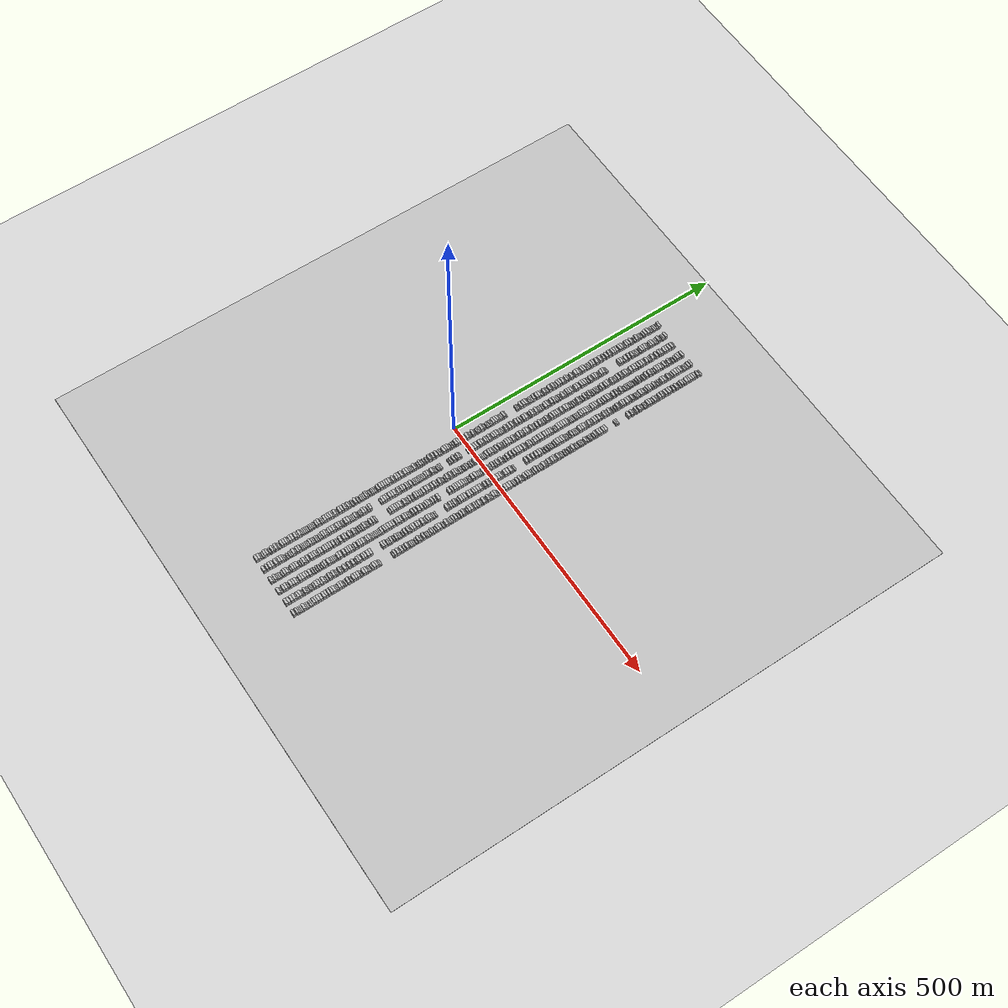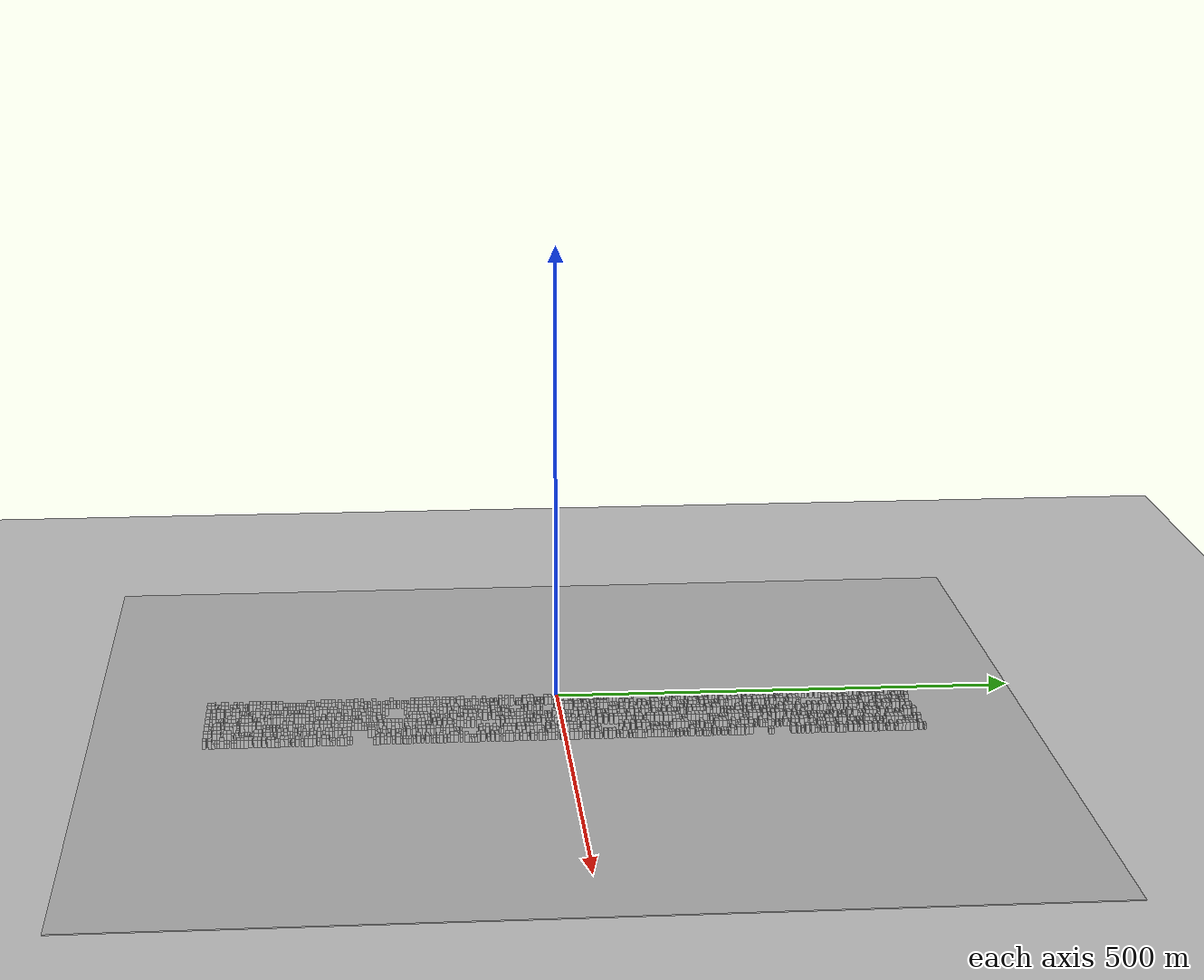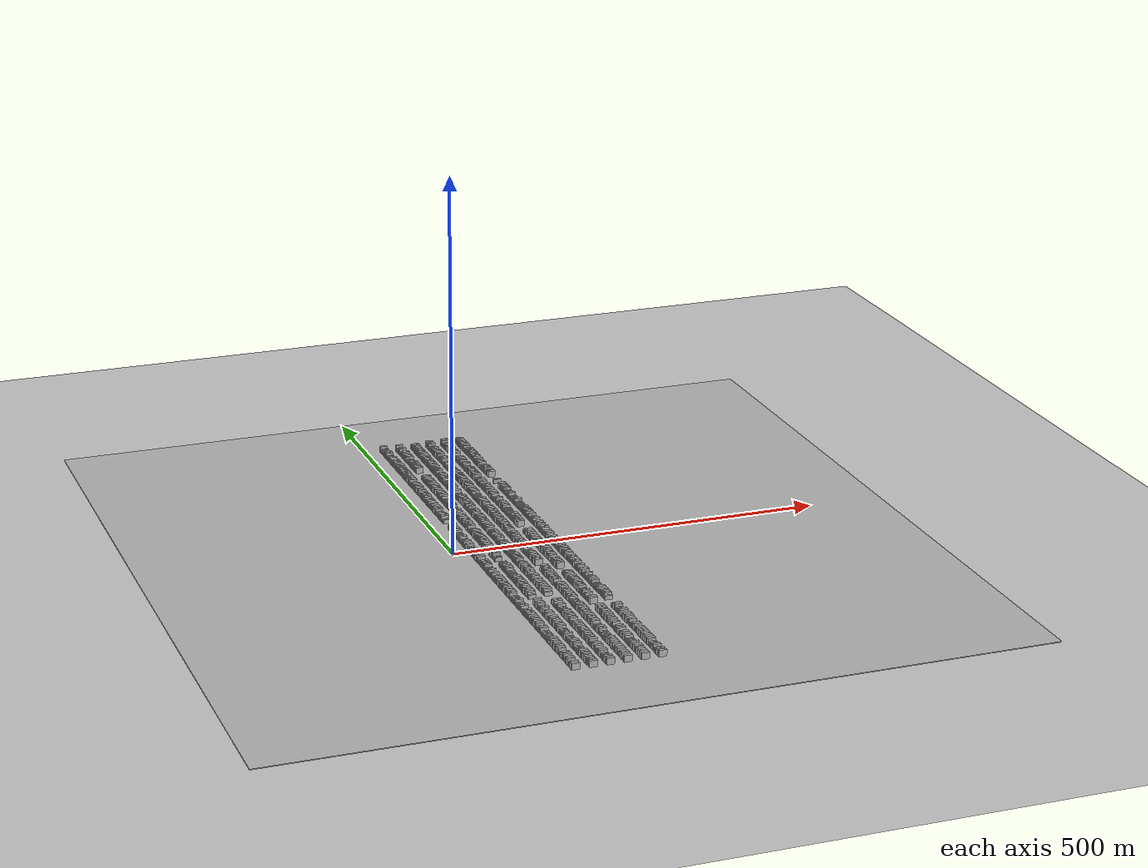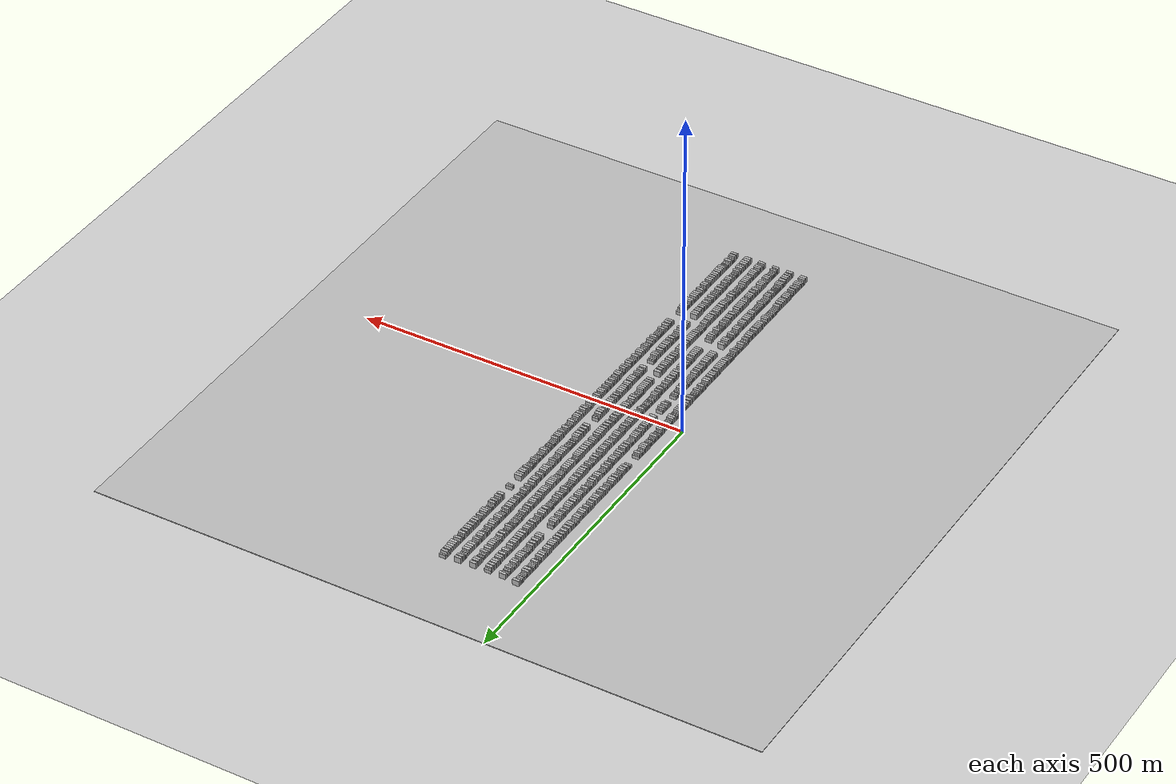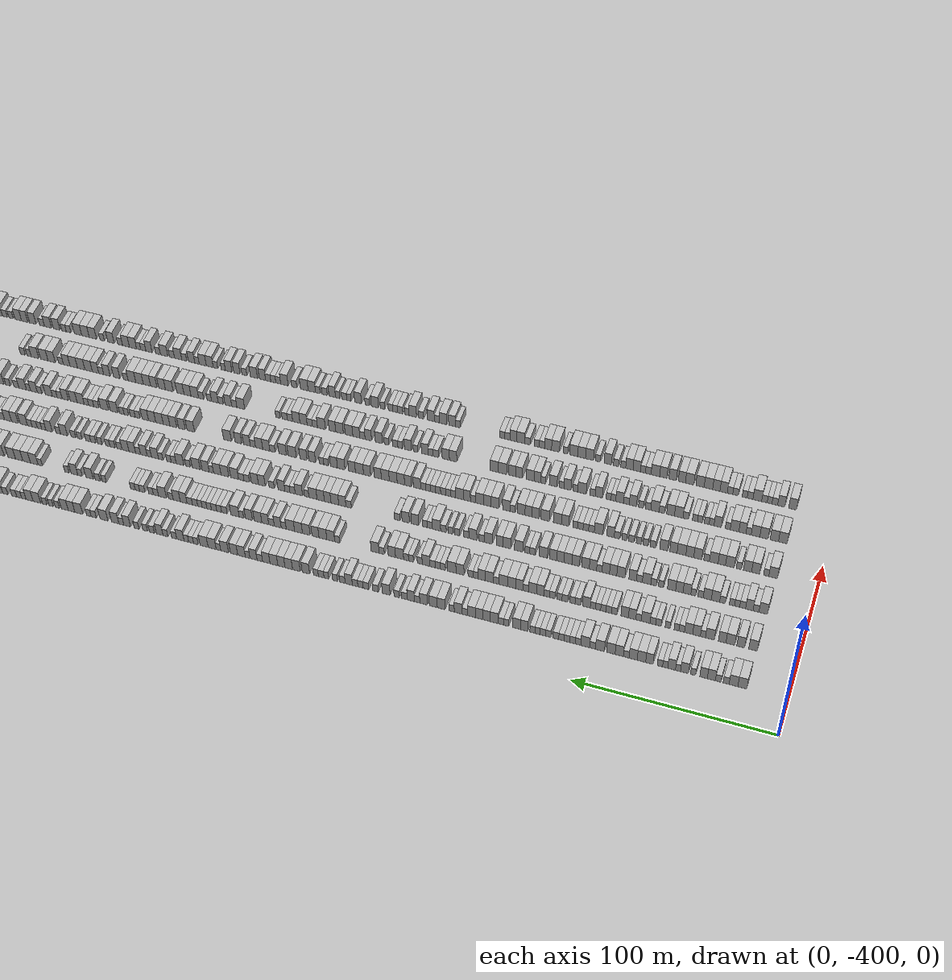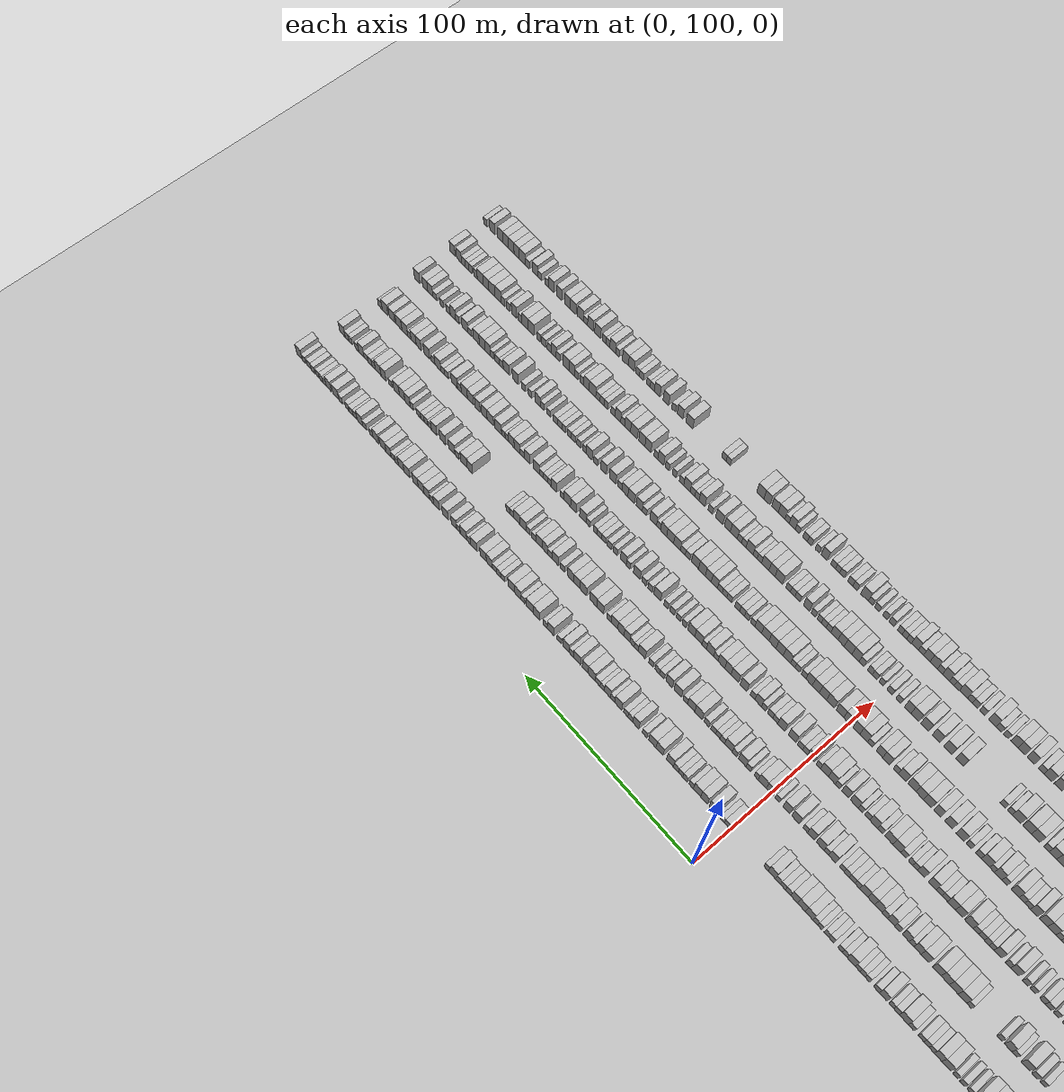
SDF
<?xml version="1.0" encoding="utf-8"?>

<sdf version="1.6">

   <world name="default">

      <gui fullscreen="0">

         <camera name="user_camera">

            <pose>-15 0 4.57585 0 0 0</pose>

            <view_controller>orbit</view_controller>

         </camera>

      </gui>

      <scene>

         <sky>

           <clouds>

             <speed>12</speed>

           </clouds>

         </sky>

         <ambient>0.4 0.4 0.4 1</ambient>

         <background>0.7 0.7 0.7 1</background>

         <shadows>1</shadows>

      </scene>

      <gravity>0 0 -9.8066</gravity>

      <magnetic_field>6e-06 2.3e-05 -4.2e-05</magnetic_field>

      <physics default="0" name="default_physics" type="ode">

         <ode>

            <solver>

               <type>quick</type>

               <iters>10</iters>

               <sor>1.0</sor>

               <use_dynamic_moi_rescaling>0</use_dynamic_moi_rescaling>

            </solver>

            <constraints>

               <cfm>0</cfm>

               <erp>0.2</erp>

               <contact_max_correcting_vel>100</contact_max_correcting_vel>

               <contact_surface_layer>0.001</contact_surface_layer>

            </constraints>

         </ode>

         <max_step_size>0.004</max_step_size>

         <real_time_factor>1</real_time_factor>

         <real_time_update_rate>250</real_time_update_rate>

      </physics>

      <light name="sun" type="directional">

         <cast_shadows>1</cast_shadows>

         <pose>0 0 10 0 0 0</pose>

         <diffuse>0.8 0.8 0.8 1</diffuse>

         <specular>0.2 0.2 0.2 1</specular>

         <attenuation>

            <range>1000</range>

            <constant>0.9</constant>

            <linear>0.01</linear>

            <quadratic>0.001</quadratic>

         </attenuation>

         <direction>-0.5 0.1 -0.9</direction>

      </light>

      <include>

         <name>ground_plane_1</name>

         <uri>model://HANNAS_ground_plane</uri>

         <pose>0 0 0  0 0 0</pose>

      </include>

      <include>

         <name>ground_plane_2</name>

         <uri>model://HANNAS_ground_plane</uri>

         <pose>100 0 0  0 0 0</pose>

      </include>

      <model name="building_1">

         <static>1</static>

         <pose frame="">25.0000 -377.8522 0 0.000000 0.000000 0.000000</pose>

         <link name="link">

            <pose frame="">0 0 4.50 0 0 0</pose>

            <collision name="collision">

               <geometry>

                  <box>

                     <size>10.0000 4.2957 9.0000</size>

                  </box>

               </geometry>

               <max_contacts>10</max_contacts>

               <surface>

                  <contact>

                     <ode/>

                  </contact>

                  <bounce/>

                  <friction>

                     <torsional>

                        <ode/>

                     </torsional>

                     <ode/>

                  </friction>

               </surface>

            </collision>

            <visual name="visual">

               <cast_shadows>0</cast_shadows>

               <geometry>

                  <box>

                     <size>10.0000 4.2957 9.0000</size>

                  </box>

               </geometry>

               <material>

                  <script>

                     <uri>model://HANNAS_wall/materials/scripts</uri>

                     <uri>model://HANNAS_wall/materials/textures</uri>

                     <name>vrc/HANNAS_wall</name>

                  </script>

               </material>

            </visual>

            <self_collide>0</self_collide>

            <enable_wind>0</enable_wind>

            <kinematic>0</kinematic>

         </link>

      </model>

      <model name="building_2">

         <static>1</static>

         <pose frame="">25.0000 -373.5972 0 0.000000 0.000000 0.000000</pose>

         <link name="link">

            <pose frame="">0 0 4.50 0 0 0</pose>

            <collision name="collision">

               <geometry>

                  <box>

                     <size>10.0000 4.2143 9.0000</size>

                  </box>

               </geometry>

               <max_contacts>10</max_contacts>

               <surface>

                  <contact>

                     <ode/>

                  </contact>

                  <bounce/>

                  <friction>

                     <torsional>

                        <ode/>

                     </torsional>

                     <ode/>

                  </friction>

               </surface>

            </collision>

            <visual name="visual">

               <cast_shadows>0</cast_shadows>

               <geometry>

                  <box>

                     <size>10.0000 4.2143 9.0000</size>

                  </box>

               </geometry>

               <material>

                  <script>

                     <uri>model://HANNAS_wall/materials/scripts</uri>

                     <uri>model://HANNAS_wall/materials/textures</uri>

                     <name>vrc/HANNAS_wall</name>

                  </script>

               </material>

            </visual>

            <self_collide>0</self_collide>

            <enable_wind>0</enable_wind>

            <kinematic>0</kinematic>

         </link>

      </model>

      <model name="building_3">

         <static>1</static>

         <pose frame="">25.0000 -370.0672 0 0.000000 0.000000 0.000000</pose>

         <link name="link">

            <pose frame="">0 0 3.00 0 0 0</pose>

            <collision name="collision">

               <geometry>

                  <box>

                     <size>10.0000 2.8457 6.0000</size>

                  </box>

               </geometry>

               <max_contacts>10</max_contacts>

               <surface>

                  <contact>

                     <ode/>

                  </contact>

                  <bounce/>

                  <friction>

                     <torsional>

                        <ode/>

                     </torsional>

                     <ode/>

                  </friction>

               </surface>

            </collision>

            <visual name="visual">

               <cast_shadows>0</cast_shadows>

               <geometry>

                  <box>

                     <size>10.0000 2.8457 6.0000</size>

                  </box>

               </geometry>

               <material>

                  <script>

                     <uri>model://HANNAS_wall/materials/scripts</uri>

                     <uri>model://HANNAS_wall/materials/textures</uri>

                     <name>vrc/HANNAS_wall</name>

                  </script>

               </material>

            </visual>

            <self_collide>0</self_collide>

            <enable_wind>0</enable_wind>

            <kinematic>0</kinematic>

         </link>

      </model>

      <model name="building_4">

         <static>1</static>

         <pose frame="">25.0000 -366.2848 0 0.000000 0.000000 0.000000</pose>

         <link name="link">

            <pose frame="">0 0 3.00 0 0 0</pose>

            <collision name="collision">

               <geometry>

                  <box>

                     <size>10.0000 2.7192 6.0000</size>

                  </box>

               </geometry>

               <max_contacts>10</max_contacts>

               <surface>

                  <contact>

                     <ode/>

                  </contact>

                  <bounce/>

                  <friction>

                     <torsional>

                        <ode/>

                     </torsional>

                     <ode/>

                  </friction>

               </surface>

            </collision>

            <visual name="visual">

               <cast_shadows>0</cast_shadows>

               <geometry>

                  <box>

                     <size>10.0000 2.7192 6.0000</size>

                  </box>

               </geometry>

               <material>

                  <script>

                     <uri>model://HANNAS_wall/materials/scripts</uri>

                     <uri>model://HANNAS_wall/materials/textures</uri>

                     <name>vrc/HANNAS_wall</name>

                  </script>

               </material>

            </visual>

            <self_collide>0</self_collide>

            <enable_wind>0</enable_wind>

            <kinematic>0</kinematic>

         </link>

      </model>

      <model name="building_5">

         <static>1</static>

         <pose frame="">25.0000 -362.9691 0 0.000000 0.000000 0.000000</pose>

         <link name="link">

            <pose frame="">0 0 4.50 0 0 0</pose>

            <collision name="collision">

               <geometry>

                  <box>

                     <size>10.0000 3.9122 9.0000</size>

                  </box>

               </geometry>

               <max_contacts>10</max_contacts>

               <surface>

                  <contact>

                     <ode/>

                  </contact>

                  <bounce/>

                  <friction>

                     <torsional>

                        <ode/>

                     </torsional>

                     <ode/>

                  </friction>

               </surface>

            </collision>

            <visual name="visual">

               <cast_shadows>0</cast_shadows>

               <geometry>

                  <box>

                     <size>10.0000 3.9122 9.0000</size>

                  </box>

               </geometry>

               <material>

                  <script>

                     <uri>model://HANNAS_wall/materials/scripts</uri>

                     <uri>model://HANNAS_wall/materials/textures</uri>

                     <name>vrc/HANNAS_wall</name>

                  </script>

               </material>

            </visual>

            <self_collide>0</self_collide>

            <enable_wind>0</enable_wind>

            <kinematic>0</kinematic>

         </link>

      </model>

      <model name="building_6">

         <static>1</static>

         <pose frame="">25.0000 -359.1819 0 0.000000 0.000000 0.000000</pose>

         <link name="link">

            <pose frame="">0 0 4.50 0 0 0</pose>

            <collision name="collision">

               <geometry>

                  <box>

                     <size>10.0000 3.6622 9.0000</size>

                  </box>

               </geometry>

               <max_contacts>10</max_contacts>

               <surface>

                  <contact>

                     <ode/>

                  </contact>

                  <bounce/>

                  <friction>

                     <torsional>

                        <ode/>

                     </torsional>

                     <ode/>

                  </friction>

               </surface>

            </collision>

            <visual name="visual">

               <cast_shadows>0</cast_shadows>

               <geometry>

                  <box>

                     <size>10.0000 3.6622 9.0000</size>

                  </box>

               </geometry>

               <material>

                  <script>

                     <uri>model://HANNAS_wall/materials/scripts</uri>

                     <uri>model://HANNAS_wall/materials/textures</uri>

                     <name>vrc/HANNAS_wall</name>

                  </script>

               </material>

            </visual>

            <self_collide>0</self_collide>

            <enable_wind>0</enable_wind>

            <kinematic>0</kinematic>

         </link>

      </model>

      <model name="building_7">

         <static>1</static>

         <pose frame="">25.0000 -354.1123 0 0.000000 0.000000 0.000000</pose>

         <link name="link">

            <pose frame="">0 0 3.00 0 0 0</pose>

            <collision name="collision">

               <geometry>

                  <box>

                     <size>10.0000 2.4771 6.0000</size>

                  </box>

               </geometry>

               <max_contacts>10</max_contacts>

               <surface>

                  <contact>

                     <ode/>

                  </contact>

                  <bounce/>

                  <friction>

                     <torsional>

                        <ode/>

                     </torsional>

                     <ode/>

                  </friction>

               </surface>

            </collision>

            <visual name="visual">

               <cast_shadows>0</cast_shadows>

               <geometry>

                  <box>

                     <size>10.0000 2.4771 6.0000</size>

                  </box>

               </geometry>

               <material>

                  <script>

                     <uri>model://HANNAS_wall/materials/scripts</uri>

                     <uri>model://HANNAS_wall/materials/textures</uri>

                     <name>vrc/HANNAS_wall</name>

                  </script>

               </material>

            </visual>

            <self_collide>0</self_collide>

            <enable_wind>0</enable_wind>

            <kinematic>0</kinematic>

         </link>

      </model>

      <model name="building_8">

         <static>1</static>

         <pose frame="">25.0000 -349.9344 0 0.000000 0.000000 0.000000</pose>

         <link name="link">

            <pose frame="">0 0 4.50 0 0 0</pose>

            <collision name="collision">

               <geometry>

                  <box>

                     <size>10.0000 3.8786 9.0000</size>

                  </box>

               </geometry>

               <max_contacts>10</max_contacts>

               <surface>

                  <contact>

                     <ode/>

                  </contact>

                  <bounce/>

                  <friction>

                     <torsional>

                        <ode/>

                     </torsional>

                     <ode/>

                  </friction>

               </surface>

            </collision>

            <visual name="visual">

               <cast_shadows>0</cast_shadows>

               <geometry>

                  <box>

                     <size>10.0000 3.8786 9.0000</size>

                  </box>

               </geometry>

               <material>

                  <script>

                     <uri>model://HANNAS_wall/materials/scripts</uri>

                     <uri>model://HANNAS_wall/materials/textures</uri>

                     <name>vrc/HANNAS_wall</name>

                  </script>

               </material>

            </visual>

            <self_collide>0</self_collide>

            <enable_wind>0</enable_wind>

            <kinematic>0</kinematic>

         </link>

      </model>

      <model name="building_9">

         <static>1</static>

         <pose frame="">25.0000 -346.7708 0 0.000000 0.000000 0.000000</pose>

         <link name="link">

            <pose frame="">0 0 3.00 0 0 0</pose>

            <collision name="collision">

               <geometry>

                  <box>

                     <size>10.0000 2.4484 6.0000</size>

                  </box>

               </geometry>

               <max_contacts>10</max_contacts>

               <surface>

                  <contact>

                     <ode/>

                  </contact>

                  <bounce/>

                  <friction>

                     <torsional>

                        <ode/>

                     </torsional>

                     <ode/>

                  </friction>

               </surface>

            </collision>

            <visual name="visual">

               <cast_shadows>0</cast_shadows>

               <geometry>

                  <box>

                     <size>10.0000 2.4484 6.0000</size>

                  </box>

               </geometry>

               <material>

                  <script>

                     <uri>model://HANNAS_wall/materials/scripts</uri>

                     <uri>model://HANNAS_wall/materials/textures</uri>

                     <name>vrc/HANNAS_wall</name>

                  </script>

               </material>

            </visual>

            <self_collide>0</self_collide>

            <enable_wind>0</enable_wind>

            <kinematic>0</kinematic>

         </link>

      </model>

      <model name="building_10">

         <static>1</static>

         <pose frame="">25.0000 -343.6423 0 0.000000 0.000000 0.000000</pose>

         <link name="link">

            <pose frame="">0 0 4.50 0 0 0</pose>

            <collision name="collision">

               <geometry>

                  <box>

                     <size>10.0000 3.8088 9.0000</size>

                  </box>

               </geometry>

               <max_contacts>10</max_contacts>

               <surface>

                  <contact>

                     <ode/>

                  </contact>

                  <bounce/>

                  <friction>

                     <torsional>

                        <ode/>

                     </torsional>

                     <ode/>

                  </friction>

               </surface>

            </collision>

            <visual name="visual">

               <cast_shadows>0</cast_shadows>

               <geometry>

                  <box>

                     <size>10.0000 3.8088 9.0000</size>

                  </box>

               </geometry>

               <material>

                  <script>

                     <uri>model://HANNAS_wall/materials/scripts</uri>

                     <uri>model://HANNAS_wall/materials/textures</uri>

                     <name>vrc/HANNAS_wall</name>

                  </script>

               </material>

            </visual>

            <self_collide>0</self_collide>

            <enable_wind>0</enable_wind>

            <kinematic>0</kinematic>

         </link>

      </model>

      <model name="building_11">

         <static>1</static>

         <pose frame="">25.0000 -340.5171 0 0.000000 0.000000 0.000000</pose>

         <link name="link">

            <pose frame="">0 0 3.00 0 0 0</pose>

            <collision name="collision">

               <geometry>

                  <box>

                     <size>10.0000 2.4416 6.0000</size>

                  </box>

               </geometry>

               <max_contacts>10</max_contacts>

               <surface>

                  <contact>

                     <ode/>

                  </contact>

                  <bounce/>

                  <friction>

                     <torsional>

                        <ode/>

                     </torsional>

                     <ode/>

                  </friction>

               </surface>

            </collision>

            <visual name="visual">

               <cast_shadows>0</cast_shadows>

               <geometry>

                  <box>

                     <size>10.0000 2.4416 6.0000</size>

                  </box>

               </geometry>

               <material>

                  <script>

                     <uri>model://HANNAS_wall/materials/scripts</uri>

                     <uri>model://HANNAS_wall/materials/textures</uri>

                     <name>vrc/HANNAS_wall</name>

                  </script>

               </material>

            </visual>

            <self_collide>0</self_collide>

            <enable_wind>0</enable_wind>

            <kinematic>0</kinematic>

         </link>

      </model>

      <model name="building_12">

         <static>1</static>

         <pose frame="">25.0000 -337.9712 0 0.000000 0.000000 0.000000</pose>

         <link name="link">

            <pose frame="">0 0 3.00 0 0 0</pose>

            <collision name="collision">

               <geometry>

                  <box>

                     <size>10.0000 2.6502 6.0000</size>

                  </box>

               </geometry>

               <max_contacts>10</max_contacts>

               <surface>

                  <contact>

                     <ode/>

                  </contact>

                  <bounce/>

                  <friction>

                     <torsional>

                        <ode/>

                     </torsional>

                     <ode/>

                  </friction>

               </surface>

            </collision>

            <visual name="visual">

               <cast_shadows>0</cast_shadows>

               <geometry>

                  <box>

                     <size>10.0000 2.6502 6.0000</size>

                  </box>

               </geometry>

               <material>

                  <script>

                     <uri>model://HANNAS_wall/materials/scripts</uri>

                     <uri>model://HANNAS_wall/materials/textures</uri>

                     <name>vrc/HANNAS_wall</name>

                  </script>

               </material>

            </visual>

            <self_collide>0</self_collide>

            <enable_wind>0</enable_wind>

            <kinematic>0</kinematic>

         </link>

      </model>

      <model name="building_13">

         <static>1</static>

         <pose frame="">25.0000 -332.8174 0 0.000000 0.000000 0.000000</pose>

         <link name="link">

            <pose frame="">0 0 4.50 0 0 0</pose>

            <collision name="collision">

               <geometry>

                  <box>

                     <size>10.0000 3.6573 9.0000</size>

                  </box>

               </geometry>

               <max_contacts>10</max_contacts>

               <surface>

                  <contact>

                     <ode/>

                  </contact>

                  <bounce/>

                  <friction>

                     <torsional>

                        <ode/>

                     </torsional>

                     <ode/>

                  </friction>

               </surface>

            </collision>

            <visual name="visual">

               <cast_shadows>0</cast_shadows>

               <geometry>

                  <box>

                     <size>10.0000 3.6573 9.0000</size>

                  </box>

               </geometry>

               <material>

                  <script>

                     <uri>model://HANNAS_wall/materials/scripts</uri>

                     <uri>model://HANNAS_wall/materials/textures</uri>

                     <name>vrc/HANNAS_wall</name>

                  </script>

               </material>

            </visual>

            <self_collide>0</self_collide>

            <enable_wind>0</enable_wind>

            <kinematic>0</kinematic>

         </link>

      </model>

      <model name="building_14">

         <static>1</static>

         <pose frame="">25.0000 -328.9260 0 0.000000 0.000000 0.000000</pose>

         <link name="link">

            <pose frame="">0 0 4.50 0 0 0</pose>

            <collision name="collision">

               <geometry>

                  <box>

                     <size>10.0000 4.1255 9.0000</size>

                  </box>

               </geometry>

               <max_contacts>10</max_contacts>

               <surface>

                  <contact>

                     <ode/>

                  </contact>

                  <bounce/>

                  <friction>

                     <torsional>

                        <ode/>

                     </torsional>

                     <ode/>

                  </friction>

               </surface>

            </collision>

            <visual name="visual">

               <cast_shadows>0</cast_shadows>

               <geometry>

                  <box>

                     <size>10.0000 4.1255 9.0000</size>

                  </box>

               </geometry>

               <material>

                  <script>

                     <uri>model://HANNAS_wall/materials/scripts</uri>

                     <uri>model://HANNAS_wall/materials/textures</uri>

                     <name>vrc/HANNAS_wall</name>

                  </script>

               </material>

            </visual>

            <self_collide>0</self_collide>

            <enable_wind>0</enable_wind>

            <kinematic>0</kinematic>

         </link>

      </model>

      <model name="building_15">

         <static>1</static>

         <pose frame="">25.0000 -324.8805 0 0.000000 0.000000 0.000000</pose>

         <link name="link">

            <pose frame="">0 0 4.50 0 0 0</pose>

            <collision name="collision">

               <geometry>

                  <box>

                     <size>10.0000 3.9656 9.0000</size>

                  </box>

               </geometry>

               <max_contacts>10</max_contacts>

               <surface>

                  <contact>

                     <ode/>

                  </contact>

                  <bounce/>

                  <friction>

                     <torsional>

                        <ode/>

                     </torsional>

                     <ode/>

                  </friction>

               </surface>

            </collision>

            <visual name="visual">

               <cast_shadows>0</cast_shadows>

               <geometry>

                  <box>

                     <size>10.0000 3.9656 9.0000</size>

                  </box>

               </geometry>

               <material>

                  <script>

                     <uri>model://HANNAS_wall/materials/scripts</uri>

                     <uri>model://HANNAS_wall/materials/textures</uri>

                     <name>vrc/HANNAS_wall</name>

                  </script>

               </material>

            </visual>

            <self_collide>0</self_collide>

            <enable_wind>0</enable_wind>

            <kinematic>0</kinematic>

         </link>

      </model>

      <model name="building_16">

         <static>1</static>

         <pose frame="">25.0000 -321.4860 0 0.000000 0.000000 0.000000</pose>

         <link name="link">

            <pose frame="">0 0 3.00 0 0 0</pose>

            <collision name="collision">

               <geometry>

                  <box>

                     <size>10.0000 2.8233 6.0000</size>

                  </box>

               </geometry>

               <max_contacts>10</max_contacts>

               <surface>

                  <contact>

                     <ode/>

                  </contact>

                  <bounce/>

                  <friction>

                     <torsional>

                        <ode/>

                     </torsional>

                     <ode/>

                  </friction>

               </surface>

            </collision>

            <visual name="visual">

               <cast_shadows>0</cast_shadows>

               <geometry>

                  <box>

                     <size>10.0000 2.8233 6.0000</size>

                  </box>

               </geometry>

               <material>

                  <script>

                     <uri>model://HANNAS_wall/materials/scripts</uri>

                     <uri>model://HANNAS_wall/materials/textures</uri>

                     <name>vrc/HANNAS_wall</name>

                  </script>

               </material>

            </visual>

            <self_collide>0</self_collide>

            <enable_wind>0</enable_wind>

            <kinematic>0</kinematic>

         </link>

      </model>

      <model name="building_17">

         <static>1</static>

         <pose frame="">25.0000 -318.0488 0 0.000000 0.000000 0.000000</pose>

         <link name="link">

            <pose frame="">0 0 4.50 0 0 0</pose>

            <collision name="collision">

               <geometry>

                  <box>

                     <size>10.0000 4.0510 9.0000</size>

                  </box>

               </geometry>

               <max_contacts>10</max_contacts>

               <surface>

                  <contact>

                     <ode/>

                  </contact>

                  <bounce/>

                  <friction>

                     <torsional>

                        <ode/>

                     </torsional>

                     <ode/>

                  </friction>

               </surface>

            </collision>

            <visual name="visual">

               <cast_shadows>0</cast_shadows>

               <geometry>

                  <box>

                     <size>10.0000 4.0510 9.0000</size>

                  </box>

               </geometry>

               <material>

                  <script>

                     <uri>model://HANNAS_wall/materials/scripts</uri>

                     <uri>model://HANNAS_wall/materials/textures</uri>

                     <name>vrc/HANNAS_wall</name>

                  </script>

               </material>

            </visual>

            <self_collide>0</self_collide>

            <enable_wind>0</enable_wind>

            <kinematic>0</kinematic>

         </link>

      </model>

      <model name="building_18">

         <static>1</static>

         <pose frame="">25.0000 -313.8992 0 0.000000 0.000000 0.000000</pose>

         <link name="link">

            <pose frame="">0 0 4.50 0 0 0</pose>

            <collision name="collision">

               <geometry>

                  <box>

                     <size>10.0000 4.2481 9.0000</size>

                  </box>

               </geometry>

               <max_contacts>10</max_contacts>

               <surface>

                  <contact>

                     <ode/>

                  </contact>

                  <bounce/>

                  <friction>

                     <torsional>

                        <ode/>

                     </torsional>

                     <ode/>

                  </friction>

               </surface>

            </collision>

            <visual name="visual">

               <cast_shadows>0</cast_shadows>

               <geometry>

                  <box>

                     <size>10.0000 4.2481 9.0000</size>

                  </box>

               </geometry>

               <material>

                  <script>

                     <uri>model://HANNAS_wall/materials/scripts</uri>

                     <uri>model://HANNAS_wall/materials/textures</uri>

                     <name>vrc/HANNAS_wall</name>

                  </script>

               </material>

            </visual>

            <self_collide>0</self_collide>

            <enable_wind>0</enable_wind>

            <kinematic>0</kinematic>

         </link>

      </model>

      <model name="building_19">

         <static>1</static>

         <pose frame="">25.0000 -308.5621 0 0.000000 0.000000 0.000000</pose>

         <link name="link">

            <pose frame="">0 0 4.50 0 0 0</pose>

            <collision name="collision">

               <geometry>

                  <box>

                     <size>10.0000 4.4262 9.0000</size>

                  </box>

               </geometry>

               <max_contacts>10</max_contacts>

               <surface>

                  <contact>

                     <ode/>

                  </contact>

                  <bounce/>

                  <friction>

                     <torsional>

                        <ode/>

                     </torsional>

                     <ode/>

                  </friction>

               </surface>

            </collision>

            <visual name="visual">

               <cast_shadows>0</cast_shadows>

               <geometry>

                  <box>

                     <size>10.0000 4.4262 9.0000</size>

                  </box>

               </geometry>

               <material>

                  <script>

                     <uri>model://HANNAS_wall/materials/scripts</uri>

                     <uri>model://HANNAS_wall/materials/textures</uri>

                     <name>vrc/HANNAS_wall</name>

                  </script>

               </material>

            </visual>

            <self_collide>0</self_collide>

            <enable_wind>0</enable_wind>

            <kinematic>0</kinematic>

         </link>

      </model>

      <model name="building_20">

         <static>1</static>

         <pose frame="">25.0000 -304.9071 0 0.000000 0.000000 0.000000</pose>

         <link name="link">

            <pose frame="">0 0 3.00 0 0 0</pose>

            <collision name="collision">

               <geometry>

                  <box>

                     <size>10.0000 2.8838 6.0000</size>

                  </box>

               </geometry>

               <max_contacts>10</max_contacts>

               <surface>

                  <contact>

                     <ode/>

                  </contact>

                  <bounce/>

                  <friction>

                     <torsional>

                        <ode/>

                     </torsional>

                     <ode/>

                  </friction>

               </surface>

            </collision>

            <visual name="visual">

               <cast_shadows>0</cast_shadows>

               <geometry>

                  <box>

                     <size>10.0000 2.8838 6.0000</size>

                  </box>

               </geometry>

               <material>

                  <script>

                     <uri>model://HANNAS_wall/materials/scripts</uri>

                     <uri>model://HANNAS_wall/materials/textures</uri>

                     <name>vrc/HANNAS_wall</name>

                  </script>

               </material>

            </visual>

            <self_collide>0</self_collide>

            <enable_wind>0</enable_wind>

            <kinematic>0</kinematic>

         </link>

      </model>

      <model name="building_21">

         <static>1</static>

         <pose frame="">25.0000 -301.2695 0 0.000000 0.000000 0.000000</pose>

         <link name="link">

            <pose frame="">0 0 4.50 0 0 0</pose>

            <collision name="collision">

               <geometry>

                  <box>

                     <size>10.0000 4.3914 9.0000</size>

                  </box>

               </geometry>

               <max_contacts>10</max_contacts>

               <surface>

                  <contact>

                     <ode/>

                  </contact>

                  <bounce/>

                  <friction>

                     <torsional>

                        <ode/>

                     </torsional>

                     <ode/>

                  </friction>

               </surface>

            </collision>

            <visual name="visual">

               <cast_shadows>0</cast_shadows>

               <geometry>

                  <box>

                     <size>10.0000 4.3914 9.0000</size>

                  </box>

               </geometry>

               <material>

                  <script>

                     <uri>model://HANNAS_wall/materials/scripts</uri>

                     <uri>model://HANNAS_wall/materials/textures</uri>

                     <name>vrc/HANNAS_wall</name>

                  </script>

               </material>

            </visual>

            <self_collide>0</self_collide>

            <enable_wind>0</enable_wind>

            <kinematic>0</kinematic>

         </link>

      </model>

      <model name="building_22">

         <static>1</static>

         <pose frame="">25.0000 -297.6697 0 0.000000 0.000000 0.000000</pose>

         <link name="link">

            <pose frame="">0 0 3.00 0 0 0</pose>

            <collision name="collision">

               <geometry>

                  <box>

                     <size>10.0000 2.8083 6.0000</size>

                  </box>

               </geometry>

               <max_contacts>10</max_contacts>

               <surface>

                  <contact>

                     <ode/>

                  </contact>

                  <bounce/>

                  <friction>

                     <torsional>

                        <ode/>

                     </torsional>

                     <ode/>

                  </friction>

               </surface>

            </collision>

            <visual name="visual">

               <cast_shadows>0</cast_shadows>

               <geometry>

                  <box>

                     <size>10.0000 2.8083 6.0000</size>

                  </box>

               </geometry>

               <material>

                  <script>

                     <uri>model://HANNAS_wall/materials/scripts</uri>

                     <uri>model://HANNAS_wall/materials/textures</uri>

                     <name>vrc/HANNAS_wall</name>

                  </script>

               </material>

            </visual>

            <self_collide>0</self_collide>

            <enable_wind>0</enable_wind>

            <kinematic>0</kinematic>

         </link>

      </model>

      <model name="building_23">

         <static>1</static>

         <pose frame="">25.0000 -294.8839 0 0.000000 0.000000 0.000000</pose>

         <link name="link">

            <pose frame="">0 0 3.00 0 0 0</pose>

            <collision name="collision">

               <geometry>

                  <box>

                     <size>10.0000 2.7632 6.0000</size>

                  </box>

               </geometry>

               <max_contacts>10</max_contacts>

               <surface>

                  <contact>

                     <ode/>

                  </contact>

                  <bounce/>

                  <friction>

                     <torsional>

                        <ode/>

                     </torsional>

                     <ode/>

                  </friction>

               </surface>

            </collision>

            <visual name="visual">

               <cast_shadows>0</cast_shadows>

               <geometry>

                  <box>

                     <size>10.0000 2.7632 6.0000</size>

                  </box>

               </geometry>

               <material>

                  <script>

                     <uri>model://HANNAS_wall/materials/scripts</uri>

                     <uri>model://HANNAS_wall/materials/textures</uri>

                     <name>vrc/HANNAS_wall</name>

                  </script>

               </material>

            </visual>

            <self_collide>0</self_collide>

            <enable_wind>0</enable_wind>

            <kinematic>0</kinematic>

         </link>

      </model>

      <model name="building_24">

         <static>1</static>

         <pose frame="">25.0000 -292.1379 0 0.000000 0.000000 0.000000</pose>

         <link name="link">

            <pose frame="">0 0 3.00 0 0 0</pose>

            <collision name="collision">

               <geometry>

                  <box>

                     <size>10.0000 2.7287 6.0000</size>

                  </box>

               </geometry>

               <max_contacts>10</max_contacts>

               <surface>

                  <contact>

                     <ode/>

                  </contact>

                  <bounce/>

                  <friction>

                     <torsional>

                        <ode/>

                     </torsional>

                     <ode/>

                  </friction>

               </surface>

            </collision>

            <visual name="visual">

               <cast_shadows>0</cast_shadows>

               <geometry>

                  <box>

                     <size>10.0000 2.7287 6.0000</size>

                  </box>

               </geometry>

               <material>

                  <script>

                     <uri>model://HANNAS_wall/materials/scripts</uri>

                     <uri>model://HANNAS_wall/materials/textures</uri>

                     <name>vrc/HANNAS_wall</name>

                  </script>

               </material>

            </visual>

            <self_collide>0</self_collide>

            <enable_wind>0</enable_wind>

            <kinematic>0</kinematic>

         </link>

      </model>

      <model name="building_25">

         <static>1</static>

         <pose frame="">25.0000 -289.4404 0 0.000000 0.000000 0.000000</pose>

         <link name="link">

            <pose frame="">0 0 3.00 0 0 0</pose>

            <collision name="collision">

               <geometry>

                  <box>

                     <size>10.0000 2.6665 6.0000</size>

                  </box>

               </geometry>

               <max_contacts>10</max_contacts>

               <surface>

                  <contact>

                     <ode/>

                  </contact>

                  <bounce/>

                  <friction>

                     <torsional>

                        <ode/>

                     </torsional>

                     <ode/>

                  </friction>

               </surface>

            </collision>

            <visual name="visual">

               <cast_shadows>0</cast_shadows>

               <geometry>

                  <box>

                     <size>10.0000 2.6665 6.0000</size>

                  </box>

               </geometry>

               <material>

                  <script>

                     <uri>model://HANNAS_wall/materials/scripts</uri>

                     <uri>model://HANNAS_wall/materials/textures</uri>

                     <name>vrc/HANNAS_wall</name>

                  </script>

               </material>

            </visual>

            <self_collide>0</self_collide>

            <enable_wind>0</enable_wind>

            <kinematic>0</kinematic>

         </link>

      </model>

      <model name="building_26">

         <static>1</static>

         <pose frame="">25.0000 -286.6353 0 0.000000 0.000000 0.000000</pose>

         <link name="link">

            <pose frame="">0 0 3.00 0 0 0</pose>

            <collision name="collision">

               <geometry>

                  <box>

                     <size>10.0000 2.9437 6.0000</size>

                  </box>

               </geometry>

               <max_contacts>10</max_contacts>

               <surface>

                  <contact>

                     <ode/>

                  </contact>

                  <bounce/>

                  <friction>

                     <torsional>

                        <ode/>

                     </torsional>

                     <ode/>

                  </friction>

               </surface>

            </collision>

            <visual name="visual">

               <cast_shadows>0</cast_shadows>

               <geometry>

                  <box>

                     <size>10.0000 2.9437 6.0000</size>

                  </box>

               </geometry>

               <material>

                  <script>

                     <uri>model://HANNAS_wall/materials/scripts</uri>

                     <uri>model://HANNAS_wall/materials/textures</uri>

                     <name>vrc/HANNAS_wall</name>

                  </script>

               </material>

            </visual>

            <self_collide>0</self_collide>

            <enable_wind>0</enable_wind>

            <kinematic>0</kinematic>

         </link>

      </model>

      <model name="building_27">

         <static>1</static>

         <pose frame="">25.0000 -282.8441 0 0.000000 0.000000 0.000000</pose>

         <link name="link">

            <pose frame="">0 0 3.00 0 0 0</pose>

            <collision name="collision">

               <geometry>

                  <box>

                     <size>10.0000 2.6388 6.0000</size>

                  </box>

               </geometry>

               <max_contacts>10</max_contacts>

               <surface>

                  <contact>

                     <ode/>

                  </contact>

                  <bounce/>

                  <friction>

                     <torsional>

                        <ode/>

                     </torsional>

                     <ode/>

                  </friction>

               </surface>

            </collision>

            <visual name="visual">

               <cast_shadows>0</cast_shadows>

               <geometry>

                  <box>

                     <size>10.0000 2.6388 6.0000</size>

                  </box>

               </geometry>

               <material>

                  <script>

                     <uri>model://HANNAS_wall/materials/scripts</uri>

                     <uri>model://HANNAS_wall/materials/textures</uri>

                     <name>vrc/HANNAS_wall</name>

                  </script>

               </material>

            </visual>

            <self_collide>0</self_collide>

            <enable_wind>0</enable_wind>

            <kinematic>0</kinematic>

         </link>

      </model>

      <model name="building_28">

         <static>1</static>

         <pose frame="">25.0000 -280.1533 0 0.000000 0.000000 0.000000</pose>

         <link name="link">

            <pose frame="">0 0 3.00 0 0 0</pose>

            <collision name="collision">

               <geometry>

                  <box>

                     <size>10.0000 2.7426 6.0000</size>

                  </box>

               </geometry>

               <max_contacts>10</max_contacts>

               <surface>

                  <contact>

                     <ode/>

                  </contact>

                  <bounce/>

                  <friction>

                     <torsional>

                        <ode/>

                     </torsional>

                     <ode/>

                  </friction>

               </surface>

            </collision>

            <visual name="visual">

               <cast_shadows>0</cast_shadows>

               <geometry>

                  <box>

                     <size>10.0000 2.7426 6.0000</size>

                  </box>

               </geometry>

               <material>

                  <script>

                     <uri>model://HANNAS_wall/materials/scripts</uri>

                     <uri>model://HANNAS_wall/materials/textures</uri>

                     <name>vrc/HANNAS_wall</name>

                  </script>

               </material>

            </visual>

            <self_collide>0</self_collide>

            <enable_wind>0</enable_wind>

            <kinematic>0</kinematic>

         </link>

      </model>

      <model name="building_29">

         <static>1</static>

         <pose frame="">25.0000 -277.4789 0 0.000000 0.000000 0.000000</pose>

         <link name="link">

            <pose frame="">0 0 3.00 0 0 0</pose>

            <collision name="collision">

               <geometry>

                  <box>

                     <size>10.0000 2.6062 6.0000</size>

                  </box>

               </geometry>

               <max_contacts>10</max_contacts>

               <surface>

                  <contact>

                     <ode/>

                  </contact>

                  <bounce/>

                  <friction>

                     <torsional>

                        <ode/>

                     </torsional>

                     <ode/>

                  </friction>

               </surface>

            </collision>

            <visual name="visual">

               <cast_shadows>0</cast_shadows>

               <geometry>

                  <box>

                     <size>10.0000 2.6062 6.0000</size>

                  </box>

               </geometry>

               <material>

                  <script>

                     <uri>model://HANNAS_wall/materials/scripts</uri>

                     <uri>model://HANNAS_wall/materials/textures</uri>

                     <name>vrc/HANNAS_wall</name>

                  </script>

               </material>

            </visual>

            <self_collide>0</self_collide>

            <enable_wind>0</enable_wind>

            <kinematic>0</kinematic>

         </link>

      </model>

      <model name="building_30">

         <static>1</static>

         <pose frame="">25.0000 -274.9261 0 0.000000 0.000000 0.000000</pose>

         <link name="link">

            <pose frame="">0 0 3.00 0 0 0</pose>

            <collision name="collision">

               <geometry>

                  <box>

                     <size>10.0000 2.4993 6.0000</size>

                  </box>

               </geometry>

               <max_contacts>10</max_contacts>

               <surface>

                  <contact>

                     <ode/>

                  </contact>

                  <bounce/>

                  <friction>

                     <torsional>

                        <ode/>

                     </torsional>

                     <ode/>

                  </friction>

               </surface>

            </collision>

            <visual name="visual">

               <cast_shadows>0</cast_shadows>

               <geometry>

                  <box>

                     <size>10.0000 2.4993 6.0000</size>

                  </box>

               </geometry>

               <material>

                  <script>

                     <uri>model://HANNAS_wall/materials/scripts</uri>

                     <uri>model://HANNAS_wall/materials/textures</uri>

                     <name>vrc/HANNAS_wall</name>

                  </script>

               </material>

            </visual>

            <self_collide>0</self_collide>

            <enable_wind>0</enable_wind>

            <kinematic>0</kinematic>

         </link>

      </model>

      <model name="building_31">

         <static>1</static>

         <pose frame="">25.0000 -270.8141 0 0.000000 0.000000 0.000000</pose>

         <link name="link">

            <pose frame="">0 0 4.50 0 0 0</pose>

            <collision name="collision">

               <geometry>

                  <box>

                     <size>10.0000 3.7247 9.0000</size>

                  </box>

               </geometry>

               <max_contacts>10</max_contacts>

               <surface>

                  <contact>

                     <ode/>

                  </contact>

                  <bounce/>

                  <friction>

                     <torsional>

                        <ode/>

                     </torsional>

                     <ode/>

                  </friction>

               </surface>

            </collision>

            <visual name="visual">

               <cast_shadows>0</cast_shadows>

               <geometry>

                  <box>

                     <size>10.0000 3.7247 9.0000</size>

                  </box>

               </geometry>

               <material>

                  <script>

                     <uri>model://HANNAS_wall/materials/scripts</uri>

                     <uri>model://HANNAS_wall/materials/textures</uri>

                     <name>vrc/HANNAS_wall</name>

                  </script>

               </material>

            </visual>

            <self_collide>0</self_collide>

            <enable_wind>0</enable_wind>

            <kinematic>0</kinematic>

         </link>

      </model>

      <model name="building_32">

         <static>1</static>

         <pose frame="">25.0000 -267.0183 0 0.000000 0.000000 0.000000</pose>

         <link name="link">

            <pose frame="">0 0 4.50 0 0 0</pose>

            <collision name="collision">

               <geometry>

                  <box>

                     <size>10.0000 3.8670 9.0000</size>

                  </box>

               </geometry>

               <max_contacts>10</max_contacts>

               <surface>

                  <contact>

                     <ode/>

                  </contact>

                  <bounce/>

                  <friction>

                     <torsional>

                        <ode/>

                     </torsional>

                     <ode/>

                  </friction>

               </surface>

            </collision>

            <visual name="visual">

               <cast_shadows>0</cast_shadows>

               <geometry>

                  <box>

                     <size>10.0000 3.8670 9.0000</size>

                  </box>

               </geometry>

               <material>

                  <script>

                     <uri>model://HANNAS_wall/materials/scripts</uri>

                     <uri>model://HANNAS_wall/materials/textures</uri>

                     <name>vrc/HANNAS_wall</name>

                  </script>

               </material>

            </visual>

            <self_collide>0</self_collide>

            <enable_wind>0</enable_wind>

            <kinematic>0</kinematic>

         </link>

      </model>

      <model name="building_33">

         <static>1</static>

         <pose frame="">25.0000 -261.8424 0 0.000000 0.000000 0.000000</pose>

         <link name="link">

            <pose frame="">0 0 3.00 0 0 0</pose>

            <collision name="collision">

               <geometry>

                  <box>

                     <size>10.0000 2.4848 6.0000</size>

                  </box>

               </geometry>

               <max_contacts>10</max_contacts>

               <surface>

                  <contact>

                     <ode/>

                  </contact>

                  <bounce/>

                  <friction>

                     <torsional>

                        <ode/>

                     </torsional>

                     <ode/>

                  </friction>

               </surface>

            </collision>

            <visual name="visual">

               <cast_shadows>0</cast_shadows>

               <geometry>

                  <box>

                     <size>10.0000 2.4848 6.0000</size>

                  </box>

               </geometry>

               <material>

                  <script>

                     <uri>model://HANNAS_wall/materials/scripts</uri>

                     <uri>model://HANNAS_wall/materials/textures</uri>

                     <name>vrc/HANNAS_wall</name>

                  </script>

               </material>

            </visual>

            <self_collide>0</self_collide>

            <enable_wind>0</enable_wind>

            <kinematic>0</kinematic>

         </link>

      </model>

      <model name="building_34">

         <static>1</static>

         <pose frame="">25.0000 -259.2197 0 0.000000 0.000000 0.000000</pose>

         <link name="link">

            <pose frame="">0 0 3.00 0 0 0</pose>

            <collision name="collision">

               <geometry>

                  <box>

                     <size>10.0000 2.7606 6.0000</size>

                  </box>

               </geometry>

               <max_contacts>10</max_contacts>

               <surface>

                  <contact>

                     <ode/>

                  </contact>

                  <bounce/>

                  <friction>

                     <torsional>

                        <ode/>

                     </torsional>

                     <ode/>

                  </friction>

               </surface>

            </collision>

            <visual name="visual">

               <cast_shadows>0</cast_shadows>

               <geometry>

                  <box>

                     <size>10.0000 2.7606 6.0000</size>

                  </box>

               </geometry>

               <material>

                  <script>

                     <uri>model://HANNAS_wall/materials/scripts</uri>

                     <uri>model://HANNAS_wall/materials/textures</uri>

                     <name>vrc/HANNAS_wall</name>

                  </script>

               </material>

            </visual>

            <self_collide>0</self_collide>

            <enable_wind>0</enable_wind>

            <kinematic>0</kinematic>

         </link>

      </model>

      <model name="building_35">

         <static>1</static>

         <pose frame="">25.0000 -255.7530 0 0.000000 0.000000 0.000000</pose>

         <link name="link">

            <pose frame="">0 0 4.50 0 0 0</pose>

            <collision name="collision">

               <geometry>

                  <box>

                     <size>10.0000 4.1728 9.0000</size>

                  </box>

               </geometry>

               <max_contacts>10</max_contacts>

               <surface>

                  <contact>

                     <ode/>

                  </contact>

                  <bounce/>

                  <friction>

                     <torsional>

                        <ode/>

                     </torsional>

                     <ode/>

                  </friction>

               </surface>

            </collision>

            <visual name="visual">

               <cast_shadows>0</cast_shadows>

               <geometry>

                  <box>

                     <size>10.0000 4.1728 9.0000</size>

                  </box>

               </geometry>

               <material>

                  <script>

                     <uri>model://HANNAS_wall/materials/scripts</uri>

                     <uri>model://HANNAS_wall/materials/textures</uri>

                     <name>vrc/HANNAS_wall</name>

                  </script>

               </material>

            </visual>

            <self_collide>0</self_collide>

            <enable_wind>0</enable_wind>

            <kinematic>0</kinematic>

         </link>

      </model>

      <model name="building_36">

         <static>1</static>

         <pose frame="">25.0000 -251.8051 0 0.000000 0.000000 0.000000</pose>

         <link name="link">

            <pose frame="">0 0 4.50 0 0 0</pose>

            <collision name="collision">

               <geometry>

                  <box>

                     <size>10.0000 3.7230 9.0000</size>

                  </box>

               </geometry>

               <max_contacts>10</max_contacts>

               <surface>

                  <contact>

                     <ode/>

                  </contact>

                  <bounce/>

                  <friction>

                     <torsional>

                        <ode/>

                     </torsional>

                     <ode/>

                  </friction>

               </surface>

            </collision>

            <visual name="visual">

               <cast_shadows>0</cast_shadows>

               <geometry>

                  <box>

                     <size>10.0000 3.7230 9.0000</size>

                  </box>

               </geometry>

               <material>

                  <script>

                     <uri>model://HANNAS_wall/materials/scripts</uri>

                     <uri>model://HANNAS_wall/materials/textures</uri>

                     <name>vrc/HANNAS_wall</name>

                  </script>

               </material>

            </visual>

            <self_collide>0</self_collide>

            <enable_wind>0</enable_wind>

            <kinematic>0</kinematic>

         </link>

      </model>

      <model name="building_37">

         <static>1</static>

         <pose frame="">25.0000 -248.1258 0 0.000000 0.000000 0.000000</pose>

         <link name="link">

            <pose frame="">0 0 4.50 0 0 0</pose>

            <collision name="collision">

               <geometry>

                  <box>

                     <size>10.0000 3.6355 9.0000</size>

                  </box>

               </geometry>

               <max_contacts>10</max_contacts>

               <surface>

                  <contact>

                     <ode/>

                  </contact>

                  <bounce/>

                  <friction>

                     <torsional>

                        <ode/>

                     </torsional>

                     <ode/>

                  </friction>

               </surface>

            </collision>

            <visual name="visual">

               <cast_shadows>0</cast_shadows>

               <geometry>

                  <box>

                     <size>10.0000 3.6355 9.0000</size>

                  </box>

               </geometry>

               <material>

                  <script>

                     <uri>model://HANNAS_wall/materials/scripts</uri>

                     <uri>model://HANNAS_wall/materials/textures</uri>

                     <name>vrc/HANNAS_wall</name>

                  </script>

               </material>

            </visual>

            <self_collide>0</self_collide>

            <enable_wind>0</enable_wind>

            <kinematic>0</kinematic>

         </link>

      </model>

      <model name="building_38">

         <static>1</static>

         <pose frame="">25.0000 -244.2917 0 0.000000 0.000000 0.000000</pose>

         <link name="link">

            <pose frame="">0 0 4.50 0 0 0</pose>

            <collision name="collision">

               <geometry>

                  <box>

                     <size>10.0000 4.0326 9.0000</size>

                  </box>

               </geometry>

               <max_contacts>10</max_contacts>

               <surface>

                  <contact>

                     <ode/>

                  </contact>

                  <bounce/>

                  <friction>

                     <torsional>

                        <ode/>

                     </torsional>

                     <ode/>

                  </friction>

               </surface>

            </collision>

            <visual name="visual">

               <cast_shadows>0</cast_shadows>

               <geometry>

                  <box>

                     <size>10.0000 4.0326 9.0000</size>

                  </box>

               </geometry>

               <material>

                  <script>

                     <uri>model://HANNAS_wall/materials/scripts</uri>

                     <uri>model://HANNAS_wall/materials/textures</uri>

                     <name>vrc/HANNAS_wall</name>

                  </script>

               </material>

            </visual>

            <self_collide>0</self_collide>

            <enable_wind>0</enable_wind>

            <kinematic>0</kinematic>

         </link>

      </model>

      <model name="building_39">

         <static>1</static>

         <pose frame="">25.0000 -240.9089 0 0.000000 0.000000 0.000000</pose>

         <link name="link">

            <pose frame="">0 0 3.00 0 0 0</pose>

            <collision name="collision">

               <geometry>

                  <box>

                     <size>10.0000 2.7330 6.0000</size>

                  </box>

               </geometry>

               <max_contacts>10</max_contacts>

               <surface>

                  <contact>

                     <ode/>

                  </contact>

                  <bounce/>

                  <friction>

                     <torsional>

                        <ode/>

                     </torsional>

                     <ode/>

                  </friction>

               </surface>

            </collision>

            <visual name="visual">

               <cast_shadows>0</cast_shadows>

               <geometry>

                  <box>

                     <size>10.0000 2.7330 6.0000</size>

                  </box>

               </geometry>

               <material>

                  <script>

                     <uri>model://HANNAS_wall/materials/scripts</uri>

                     <uri>model://HANNAS_wall/materials/textures</uri>

                     <name>vrc/HANNAS_wall</name>

                  </script>

               </material>

            </visual>

            <self_collide>0</self_collide>

            <enable_wind>0</enable_wind>

            <kinematic>0</kinematic>

         </link>

      </model>

      <model name="building_40">

         <static>1</static>

         <pose frame="">25.0000 -237.5478 0 0.000000 0.000000 0.000000</pose>

         <link name="link">

            <pose frame="">0 0 4.50 0 0 0</pose>

            <collision name="collision">

               <geometry>

                  <box>

                     <size>10.0000 3.9893 9.0000</size>

                  </box>

               </geometry>

               <max_contacts>10</max_contacts>

               <surface>

                  <contact>

                     <ode/>

                  </contact>

                  <bounce/>

                  <friction>

                     <torsional>

                        <ode/>

                     </torsional>

                     <ode/>

                  </friction>

               </surface>

            </collision>

            <visual name="visual">

               <cast_shadows>0</cast_shadows>

               <geometry>

                  <box>

                     <size>10.0000 3.9893 9.0000</size>

                  </box>

               </geometry>

               <material>

                  <script>

                     <uri>model://HANNAS_wall/materials/scripts</uri>

                     <uri>model://HANNAS_wall/materials/textures</uri>

                     <name>vrc/HANNAS_wall</name>

                  </script>

               </material>

            </visual>

            <self_collide>0</self_collide>

            <enable_wind>0</enable_wind>

            <kinematic>0</kinematic>

         </link>

      </model>

      <model name="building_41">

         <static>1</static>

         <pose frame="">25.0000 -234.2131 0 0.000000 0.000000 0.000000</pose>

         <link name="link">

            <pose frame="">0 0 3.00 0 0 0</pose>

            <collision name="collision">

               <geometry>

                  <box>

                     <size>10.0000 2.6801 6.0000</size>

                  </box>

               </geometry>

               <max_contacts>10</max_contacts>

               <surface>

                  <contact>

                     <ode/>

                  </contact>

                  <bounce/>

                  <friction>

                     <torsional>

                        <ode/>

                     </torsional>

                     <ode/>

                  </friction>

               </surface>

            </collision>

            <visual name="visual">

               <cast_shadows>0</cast_shadows>

               <geometry>

                  <box>

                     <size>10.0000 2.6801 6.0000</size>

                  </box>

               </geometry>

               <material>

                  <script>

                     <uri>model://HANNAS_wall/materials/scripts</uri>

                     <uri>model://HANNAS_wall/materials/textures</uri>

                     <name>vrc/HANNAS_wall</name>

                  </script>

               </material>

            </visual>

            <self_collide>0</self_collide>

            <enable_wind>0</enable_wind>

            <kinematic>0</kinematic>

         </link>

      </model>

      <model name="building_42">

         <static>1</static>

         <pose frame="">25.0000 -228.8729 0 0.000000 0.000000 0.000000</pose>

         <link name="link">

            <pose frame="">0 0 4.50 0 0 0</pose>

            <collision name="collision">

               <geometry>

                  <box>

                     <size>10.0000 4.0002 9.0000</size>

                  </box>

               </geometry>

               <max_contacts>10</max_contacts>

               <surface>

                  <contact>

                     <ode/>

                  </contact>

                  <bounce/>

                  <friction>

                     <torsional>

                        <ode/>

                     </torsional>

                     <ode/>

                  </friction>

               </surface>

            </collision>

            <visual name="visual">

               <cast_shadows>0</cast_shadows>

               <geometry>

                  <box>

                     <size>10.0000 4.0002 9.0000</size>

                  </box>

               </geometry>

               <material>

                  <script>

                     <uri>model://HANNAS_wall/materials/scripts</uri>

                     <uri>model://HANNAS_wall/materials/textures</uri>

                     <name>vrc/HANNAS_wall</name>

                  </script>

               </material>

            </visual>

            <self_collide>0</self_collide>

            <enable_wind>0</enable_wind>

            <kinematic>0</kinematic>

         </link>

      </model>

      <model name="building_43">

         <static>1</static>

         <pose frame="">25.0000 -224.8315 0 0.000000 0.000000 0.000000</pose>

         <link name="link">

            <pose frame="">0 0 4.50 0 0 0</pose>

            <collision name="collision">

               <geometry>

                  <box>

                     <size>10.0000 4.0826 9.0000</size>

                  </box>

               </geometry>

               <max_contacts>10</max_contacts>

               <surface>

                  <contact>

                     <ode/>

                  </contact>

                  <bounce/>

                  <friction>

                     <torsional>

                        <ode/>

                     </torsional>

                     <ode/>

                  </friction>

               </surface>

            </collision>

            <visual name="visual">

               <cast_shadows>0</cast_shadows>

               <geometry>

                  <box>

                     <size>10.0000 4.0826 9.0000</size>

                  </box>

               </geometry>

               <material>

                  <script>

                     <uri>model://HANNAS_wall/materials/scripts</uri>

                     <uri>model://HANNAS_wall/materials/textures</uri>

                     <name>vrc/HANNAS_wall</name>

                  </script>

               </material>

            </visual>

            <self_collide>0</self_collide>

            <enable_wind>0</enable_wind>

            <kinematic>0</kinematic>

         </link>

      </model>

      <model name="building_44">

         <static>1</static>

         <pose frame="">25.0000 -219.8721 0 0.000000 0.000000 0.000000</pose>

         <link name="link">

            <pose frame="">0 0 4.50 0 0 0</pose>

            <collision name="collision">

               <geometry>

                  <box>

                     <size>10.0000 3.8362 9.0000</size>

                  </box>

               </geometry>

               <max_contacts>10</max_contacts>

               <surface>

                  <contact>

                     <ode/>

                  </contact>

                  <bounce/>

                  <friction>

                     <torsional>

                        <ode/>

                     </torsional>

                     <ode/>

                  </friction>

               </surface>

            </collision>

            <visual name="visual">

               <cast_shadows>0</cast_shadows>

               <geometry>

                  <box>

                     <size>10.0000 3.8362 9.0000</size>

                  </box>

               </geometry>

               <material>

                  <script>

                     <uri>model://HANNAS_wall/materials/scripts</uri>

                     <uri>model://HANNAS_wall/materials/textures</uri>

                     <name>vrc/HANNAS_wall</name>

                  </script>

               </material>

            </visual>

            <self_collide>0</self_collide>

            <enable_wind>0</enable_wind>

            <kinematic>0</kinematic>

         </link>

      </model>

      <model name="building_45">

         <static>1</static>

         <pose frame="">25.0000 -216.5849 0 0.000000 0.000000 0.000000</pose>

         <link name="link">

            <pose frame="">0 0 3.00 0 0 0</pose>

            <collision name="collision">

               <geometry>

                  <box>

                     <size>10.0000 2.7382 6.0000</size>

                  </box>

               </geometry>

               <max_contacts>10</max_contacts>

               <surface>

                  <contact>

                     <ode/>

                  </contact>

                  <bounce/>

                  <friction>

                     <torsional>

                        <ode/>

                     </torsional>

                     <ode/>

                  </friction>

               </surface>

            </collision>

            <visual name="visual">

               <cast_shadows>0</cast_shadows>

               <geometry>

                  <box>

                     <size>10.0000 2.7382 6.0000</size>

                  </box>

               </geometry>

               <material>

                  <script>

                     <uri>model://HANNAS_wall/materials/scripts</uri>

                     <uri>model://HANNAS_wall/materials/textures</uri>

                     <name>vrc/HANNAS_wall</name>

                  </script>

               </material>

            </visual>

            <self_collide>0</self_collide>

            <enable_wind>0</enable_wind>

            <kinematic>0</kinematic>

         </link>

      </model>

      <model name="building_46">

         <static>1</static>

         <pose frame="">25.0000 -213.3697 0 0.000000 0.000000 0.000000</pose>

         <link name="link">

            <pose frame="">0 0 4.50 0 0 0</pose>

            <collision name="collision">

               <geometry>

                  <box>

                     <size>10.0000 3.6921 9.0000</size>

                  </box>

               </geometry>

               <max_contacts>10</max_contacts>

               <surface>

                  <contact>

                     <ode/>

                  </contact>

                  <bounce/>

                  <friction>

                     <torsional>

                        <ode/>

                     </torsional>

                     <ode/>

                  </friction>

               </surface>

            </collision>

            <visual name="visual">

               <cast_shadows>0</cast_shadows>

               <geometry>

                  <box>

                     <size>10.0000 3.6921 9.0000</size>

                  </box>

               </geometry>

               <material>

                  <script>

                     <uri>model://HANNAS_wall/materials/scripts</uri>

                     <uri>model://HANNAS_wall/materials/textures</uri>

                     <name>vrc/HANNAS_wall</name>

                  </script>

               </material>

            </visual>

            <self_collide>0</self_collide>

            <enable_wind>0</enable_wind>

            <kinematic>0</kinematic>

         </link>

      </model>

      <model name="building_47">

         <static>1</static>

         <pose frame="">25.0000 -210.0258 0 0.000000 0.000000 0.000000</pose>

         <link name="link">

            <pose frame="">0 0 3.00 0 0 0</pose>

            <collision name="collision">

               <geometry>

                  <box>

                     <size>10.0000 2.9958 6.0000</size>

                  </box>

               </geometry>

               <max_contacts>10</max_contacts>

               <surface>

                  <contact>

                     <ode/>

                  </contact>

                  <bounce/>

                  <friction>

                     <torsional>

                        <ode/>

                     </torsional>

                     <ode/>

                  </friction>

               </surface>

            </collision>

            <visual name="visual">

               <cast_shadows>0</cast_shadows>

               <geometry>

                  <box>

                     <size>10.0000 2.9958 6.0000</size>

                  </box>

               </geometry>

               <material>

                  <script>

                     <uri>model://HANNAS_wall/materials/scripts</uri>

                     <uri>model://HANNAS_wall/materials/textures</uri>

                     <name>vrc/HANNAS_wall</name>

                  </script>

               </material>

            </visual>

            <self_collide>0</self_collide>

            <enable_wind>0</enable_wind>

            <kinematic>0</kinematic>

         </link>

      </model>

      <model name="building_48">

         <static>1</static>

         <pose frame="">25.0000 -206.0988 0 0.000000 0.000000 0.000000</pose>

         <link name="link">

            <pose frame="">0 0 3.00 0 0 0</pose>

            <collision name="collision">

               <geometry>

                  <box>

                     <size>10.0000 2.8581 6.0000</size>

                  </box>

               </geometry>

               <max_contacts>10</max_contacts>

               <surface>

                  <contact>

                     <ode/>

                  </contact>

                  <bounce/>

                  <friction>

                     <torsional>

                        <ode/>

                     </torsional>

                     <ode/>

                  </friction>

               </surface>

            </collision>

            <visual name="visual">

               <cast_shadows>0</cast_shadows>

               <geometry>

                  <box>

                     <size>10.0000 2.8581 6.0000</size>

                  </box>

               </geometry>

               <material>

                  <script>

                     <uri>model://HANNAS_wall/materials/scripts</uri>

                     <uri>model://HANNAS_wall/materials/textures</uri>

                     <name>vrc/HANNAS_wall</name>

                  </script>

               </material>

            </visual>

            <self_collide>0</self_collide>

            <enable_wind>0</enable_wind>

            <kinematic>0</kinematic>

         </link>

      </model>

      <model name="building_49">

         <static>1</static>

         <pose frame="">25.0000 -200.6526 0 0.000000 0.000000 0.000000</pose>

         <link name="link">

            <pose frame="">0 0 4.50 0 0 0</pose>

            <collision name="collision">

               <geometry>

                  <box>

                     <size>10.0000 4.0343 9.0000</size>

                  </box>

               </geometry>

               <max_contacts>10</max_contacts>

               <surface>

                  <contact>

                     <ode/>

                  </contact>

                  <bounce/>

                  <friction>

                     <torsional>

                        <ode/>

                     </torsional>

                     <ode/>

                  </friction>

               </surface>

            </collision>

            <visual name="visual">

               <cast_shadows>0</cast_shadows>

               <geometry>

                  <box>

                     <size>10.0000 4.0343 9.0000</size>

                  </box>

               </geometry>

               <material>

                  <script>

                     <uri>model://HANNAS_wall/materials/scripts</uri>

                     <uri>model://HANNAS_wall/materials/textures</uri>

                     <name>vrc/HANNAS_wall</name>

                  </script>

               </material>

            </visual>

            <self_collide>0</self_collide>

            <enable_wind>0</enable_wind>

            <kinematic>0</kinematic>

         </link>

      </model>

      <model name="building_50">

         <static>1</static>

         <pose frame="">25.0000 -195.1668 0 0.000000 0.000000 0.000000</pose>

         <link name="link">

            <pose frame="">0 0 3.00 0 0 0</pose>

            <collision name="collision">

               <geometry>

                  <box>

                     <size>10.0000 2.9372 6.0000</size>

                  </box>

               </geometry>

               <max_contacts>10</max_contacts>

               <surface>

                  <contact>

                     <ode/>

                  </contact>

                  <bounce/>

                  <friction>

                     <torsional>

                        <ode/>

                     </torsional>

                     <ode/>

                  </friction>

               </surface>

            </collision>

            <visual name="visual">

               <cast_shadows>0</cast_shadows>

               <geometry>

                  <box>

                     <size>10.0000 2.9372 6.0000</size>

                  </box>

               </geometry>

               <material>

                  <script>

                     <uri>model://HANNAS_wall/materials/scripts</uri>

                     <uri>model://HANNAS_wall/materials/textures</uri>

                     <name>vrc/HANNAS_wall</name>

                  </script>

               </material>

            </visual>

            <self_collide>0</self_collide>

            <enable_wind>0</enable_wind>

            <kinematic>0</kinematic>

         </link>

      </model>

      <model name="building_51">

         <static>1</static>

         <pose frame="">25.0000 -190.2452 0 0.000000 0.000000 0.000000</pose>

         <link name="link">

            <pose frame="">0 0 3.00 0 0 0</pose>

            <collision name="collision">

               <geometry>

                  <box>

                     <size>10.0000 2.9060 6.0000</size>

                  </box>

               </geometry>

               <max_contacts>10</max_contacts>

               <surface>

                  <contact>

                     <ode/>

                  </contact>

                  <bounce/>

                  <friction>

                     <torsional>

                        <ode/>

                     </torsional>

                     <ode/>

                  </friction>

               </surface>

            </collision>

            <visual name="visual">

               <cast_shadows>0</cast_shadows>

               <geometry>

                  <box>

                     <size>10.0000 2.9060 6.0000</size>

                  </box>

               </geometry>

               <material>

                  <script>

                     <uri>model://HANNAS_wall/materials/scripts</uri>

                     <uri>model://HANNAS_wall/materials/textures</uri>

                     <name>vrc/HANNAS_wall</name>

                  </script>

               </material>

            </visual>

            <self_collide>0</self_collide>

            <enable_wind>0</enable_wind>

            <kinematic>0</kinematic>

         </link>

      </model>

      <model name="building_52">

         <static>1</static>

         <pose frame="">25.0000 -187.3861 0 0.000000 0.000000 0.000000</pose>

         <link name="link">

            <pose frame="">0 0 3.00 0 0 0</pose>

            <collision name="collision">

               <geometry>

                  <box>

                     <size>10.0000 2.8123 6.0000</size>

                  </box>

               </geometry>

               <max_contacts>10</max_contacts>

               <surface>

                  <contact>

                     <ode/>

                  </contact>

                  <bounce/>

                  <friction>

                     <torsional>

                        <ode/>

                     </torsional>

                     <ode/>

                  </friction>

               </surface>

            </collision>

            <visual name="visual">

               <cast_shadows>0</cast_shadows>

               <geometry>

                  <box>

                     <size>10.0000 2.8123 6.0000</size>

                  </box>

               </geometry>

               <material>

                  <script>

                     <uri>model://HANNAS_wall/materials/scripts</uri>

                     <uri>model://HANNAS_wall/materials/textures</uri>

                     <name>vrc/HANNAS_wall</name>

                  </script>

               </material>

            </visual>

            <self_collide>0</self_collide>

            <enable_wind>0</enable_wind>

            <kinematic>0</kinematic>

         </link>

      </model>

      <model name="building_53">

         <static>1</static>

         <pose frame="">25.0000 -184.5567 0 0.000000 0.000000 0.000000</pose>

         <link name="link">

            <pose frame="">0 0 3.00 0 0 0</pose>

            <collision name="collision">

               <geometry>

                  <box>

                     <size>10.0000 2.8465 6.0000</size>

                  </box>

               </geometry>

               <max_contacts>10</max_contacts>

               <surface>

                  <contact>

                     <ode/>

                  </contact>

                  <bounce/>

                  <friction>

                     <torsional>

                        <ode/>

                     </torsional>

                     <ode/>

                  </friction>

               </surface>

            </collision>

            <visual name="visual">

               <cast_shadows>0</cast_shadows>

               <geometry>

                  <box>

                     <size>10.0000 2.8465 6.0000</size>

                  </box>

               </geometry>

               <material>

                  <script>

                     <uri>model://HANNAS_wall/materials/scripts</uri>

                     <uri>model://HANNAS_wall/materials/textures</uri>

                     <name>vrc/HANNAS_wall</name>

                  </script>

               </material>

            </visual>

            <self_collide>0</self_collide>

            <enable_wind>0</enable_wind>

            <kinematic>0</kinematic>

         </link>

      </model>

      <model name="building_54">

         <static>1</static>

         <pose frame="">25.0000 -181.2828 0 0.000000 0.000000 0.000000</pose>

         <link name="link">

            <pose frame="">0 0 4.50 0 0 0</pose>

            <collision name="collision">

               <geometry>

                  <box>

                     <size>10.0000 3.7012 9.0000</size>

                  </box>

               </geometry>

               <max_contacts>10</max_contacts>

               <surface>

                  <contact>

                     <ode/>

                  </contact>

                  <bounce/>

                  <friction>

                     <torsional>

                        <ode/>

                     </torsional>

                     <ode/>

                  </friction>

               </surface>

            </collision>

            <visual name="visual">

               <cast_shadows>0</cast_shadows>

               <geometry>

                  <box>

                     <size>10.0000 3.7012 9.0000</size>

                  </box>

               </geometry>

               <material>

                  <script>

                     <uri>model://HANNAS_wall/materials/scripts</uri>

                     <uri>model://HANNAS_wall/materials/textures</uri>

                     <name>vrc/HANNAS_wall</name>

                  </script>

               </material>

            </visual>

            <self_collide>0</self_collide>

            <enable_wind>0</enable_wind>

            <kinematic>0</kinematic>

         </link>

      </model>

      <model name="building_55">

         <static>1</static>

         <pose frame="">25.0000 -177.9561 0 0.000000 0.000000 0.000000</pose>

         <link name="link">

            <pose frame="">0 0 3.00 0 0 0</pose>

            <collision name="collision">

               <geometry>

                  <box>

                     <size>10.0000 2.9522 6.0000</size>

                  </box>

               </geometry>

               <max_contacts>10</max_contacts>

               <surface>

                  <contact>

                     <ode/>

                  </contact>

                  <bounce/>

                  <friction>

                     <torsional>

                        <ode/>

                     </torsional>

                     <ode/>

                  </friction>

               </surface>

            </collision>

            <visual name="visual">

               <cast_shadows>0</cast_shadows>

               <geometry>

                  <box>

                     <size>10.0000 2.9522 6.0000</size>

                  </box>

               </geometry>

               <material>

                  <script>

                     <uri>model://HANNAS_wall/materials/scripts</uri>

                     <uri>model://HANNAS_wall/materials/textures</uri>

                     <name>vrc/HANNAS_wall</name>

                  </script>

               </material>

            </visual>

            <self_collide>0</self_collide>

            <enable_wind>0</enable_wind>

            <kinematic>0</kinematic>

         </link>

      </model>

      <model name="building_56">

         <static>1</static>

         <pose frame="">25.0000 -174.1771 0 0.000000 0.000000 0.000000</pose>

         <link name="link">

            <pose frame="">0 0 3.00 0 0 0</pose>

            <collision name="collision">

               <geometry>

                  <box>

                     <size>10.0000 2.6057 6.0000</size>

                  </box>

               </geometry>

               <max_contacts>10</max_contacts>

               <surface>

                  <contact>

                     <ode/>

                  </contact>

                  <bounce/>

                  <friction>

                     <torsional>

                        <ode/>

                     </torsional>

                     <ode/>

                  </friction>

               </surface>

            </collision>

            <visual name="visual">

               <cast_shadows>0</cast_shadows>

               <geometry>

                  <box>

                     <size>10.0000 2.6057 6.0000</size>

                  </box>

               </geometry>

               <material>

                  <script>

                     <uri>model://HANNAS_wall/materials/scripts</uri>

                     <uri>model://HANNAS_wall/materials/textures</uri>

                     <name>vrc/HANNAS_wall</name>

                  </script>

               </material>

            </visual>

            <self_collide>0</self_collide>

            <enable_wind>0</enable_wind>

            <kinematic>0</kinematic>

         </link>

      </model>

      <model name="building_57">

         <static>1</static>

         <pose frame="">25.0000 -169.6165 0 0.000000 0.000000 0.000000</pose>

         <link name="link">

            <pose frame="">0 0 3.00 0 0 0</pose>

            <collision name="collision">

               <geometry>

                  <box>

                     <size>10.0000 2.5156 6.0000</size>

                  </box>

               </geometry>

               <max_contacts>10</max_contacts>

               <surface>

                  <contact>

                     <ode/>

                  </contact>

                  <bounce/>

                  <friction>

                     <torsional>

                        <ode/>

                     </torsional>

                     <ode/>

                  </friction>

               </surface>

            </collision>

            <visual name="visual">

               <cast_shadows>0</cast_shadows>

               <geometry>

                  <box>

                     <size>10.0000 2.5156 6.0000</size>

                  </box>

               </geometry>

               <material>

                  <script>

                     <uri>model://HANNAS_wall/materials/scripts</uri>

                     <uri>model://HANNAS_wall/materials/textures</uri>

                     <name>vrc/HANNAS_wall</name>

                  </script>

               </material>

            </visual>

            <self_collide>0</self_collide>

            <enable_wind>0</enable_wind>

            <kinematic>0</kinematic>

         </link>

      </model>

      <model name="building_58">

         <static>1</static>

         <pose frame="">25.0000 -166.9035 0 0.000000 0.000000 0.000000</pose>

         <link name="link">

            <pose frame="">0 0 3.00 0 0 0</pose>

            <collision name="collision">

               <geometry>

                  <box>

                     <size>10.0000 2.9104 6.0000</size>

                  </box>

               </geometry>

               <max_contacts>10</max_contacts>

               <surface>

                  <contact>

                     <ode/>

                  </contact>

                  <bounce/>

                  <friction>

                     <torsional>

                        <ode/>

                     </torsional>

                     <ode/>

                  </friction>

               </surface>

            </collision>

            <visual name="visual">

               <cast_shadows>0</cast_shadows>

               <geometry>

                  <box>

                     <size>10.0000 2.9104 6.0000</size>

                  </box>

               </geometry>

               <material>

                  <script>

                     <uri>model://HANNAS_wall/materials/scripts</uri>

                     <uri>model://HANNAS_wall/materials/textures</uri>

                     <name>vrc/HANNAS_wall</name>

                  </script>

               </material>

            </visual>

            <self_collide>0</self_collide>

            <enable_wind>0</enable_wind>

            <kinematic>0</kinematic>

         </link>

      </model>

      <model name="building_59">

         <static>1</static>

         <pose frame="">25.0000 -164.1506 0 0.000000 0.000000 0.000000</pose>

         <link name="link">

            <pose frame="">0 0 3.00 0 0 0</pose>

            <collision name="collision">

               <geometry>

                  <box>

                     <size>10.0000 2.5953 6.0000</size>

                  </box>

               </geometry>

               <max_contacts>10</max_contacts>

               <surface>

                  <contact>

                     <ode/>

                  </contact>

                  <bounce/>

                  <friction>

                     <torsional>

                        <ode/>

                     </torsional>

                     <ode/>

                  </friction>

               </surface>

            </collision>

            <visual name="visual">

               <cast_shadows>0</cast_shadows>

               <geometry>

                  <box>

                     <size>10.0000 2.5953 6.0000</size>

                  </box>

               </geometry>

               <material>

                  <script>

                     <uri>model://HANNAS_wall/materials/scripts</uri>

                     <uri>model://HANNAS_wall/materials/textures</uri>

                     <name>vrc/HANNAS_wall</name>

                  </script>

               </material>

            </visual>

            <self_collide>0</self_collide>

            <enable_wind>0</enable_wind>

            <kinematic>0</kinematic>

         </link>

      </model>

      <model name="building_60">

         <static>1</static>

         <pose frame="">25.0000 -158.8898 0 0.000000 0.000000 0.000000</pose>

         <link name="link">

            <pose frame="">0 0 4.50 0 0 0</pose>

            <collision name="collision">

               <geometry>

                  <box>

                     <size>10.0000 3.9264 9.0000</size>

                  </box>

               </geometry>

               <max_contacts>10</max_contacts>

               <surface>

                  <contact>

                     <ode/>

                  </contact>

                  <bounce/>

                  <friction>

                     <torsional>

                        <ode/>

                     </torsional>

                     <ode/>

                  </friction>

               </surface>

            </collision>

            <visual name="visual">

               <cast_shadows>0</cast_shadows>

               <geometry>

                  <box>

                     <size>10.0000 3.9264 9.0000</size>

                  </box>

               </geometry>

               <material>

                  <script>

                     <uri>model://HANNAS_wall/materials/scripts</uri>

                     <uri>model://HANNAS_wall/materials/textures</uri>

                     <name>vrc/HANNAS_wall</name>

                  </script>

               </material>

            </visual>

            <self_collide>0</self_collide>

            <enable_wind>0</enable_wind>

            <kinematic>0</kinematic>

         </link>

      </model>

      <model name="building_61">

         <static>1</static>

         <pose frame="">25.0000 -153.9136 0 0.000000 0.000000 0.000000</pose>

         <link name="link">

            <pose frame="">0 0 4.50 0 0 0</pose>

            <collision name="collision">

               <geometry>

                  <box>

                     <size>10.0000 4.0259 9.0000</size>

                  </box>

               </geometry>

               <max_contacts>10</max_contacts>

               <surface>

                  <contact>

                     <ode/>

                  </contact>

                  <bounce/>

                  <friction>

                     <torsional>

                        <ode/>

                     </torsional>

                     <ode/>

                  </friction>

               </surface>

            </collision>

            <visual name="visual">

               <cast_shadows>0</cast_shadows>

               <geometry>

                  <box>

                     <size>10.0000 4.0259 9.0000</size>

                  </box>

               </geometry>

               <material>

                  <script>

                     <uri>model://HANNAS_wall/materials/scripts</uri>

                     <uri>model://HANNAS_wall/materials/textures</uri>

                     <name>vrc/HANNAS_wall</name>

                  </script>

               </material>

            </visual>

            <self_collide>0</self_collide>

            <enable_wind>0</enable_wind>

            <kinematic>0</kinematic>

         </link>

      </model>

      <model name="building_62">

         <static>1</static>

         <pose frame="">25.0000 -149.9300 0 0.000000 0.000000 0.000000</pose>

         <link name="link">

            <pose frame="">0 0 4.50 0 0 0</pose>

            <collision name="collision">

               <geometry>

                  <box>

                     <size>10.0000 3.9413 9.0000</size>

                  </box>

               </geometry>

               <max_contacts>10</max_contacts>

               <surface>

                  <contact>

                     <ode/>

                  </contact>

                  <bounce/>

                  <friction>

                     <torsional>

                        <ode/>

                     </torsional>

                     <ode/>

                  </friction>

               </surface>

            </collision>

            <visual name="visual">

               <cast_shadows>0</cast_shadows>

               <geometry>

                  <box>

                     <size>10.0000 3.9413 9.0000</size>

                  </box>

               </geometry>

               <material>

                  <script>

                     <uri>model://HANNAS_wall/materials/scripts</uri>

                     <uri>model://HANNAS_wall/materials/textures</uri>

                     <name>vrc/HANNAS_wall</name>

                  </script>

               </material>

            </visual>

            <self_collide>0</self_collide>

            <enable_wind>0</enable_wind>

            <kinematic>0</kinematic>

         </link>

      </model>

      <model name="building_63">

         <static>1</static>

         <pose frame="">25.0000 -146.0602 0 0.000000 0.000000 0.000000</pose>

         <link name="link">

            <pose frame="">0 0 4.50 0 0 0</pose>

            <collision name="collision">

               <geometry>

                  <box>

                     <size>10.0000 3.7984 9.0000</size>

                  </box>

               </geometry>

               <max_contacts>10</max_contacts>

               <surface>

                  <contact>

                     <ode/>

                  </contact>

                  <bounce/>

                  <friction>

                     <torsional>

                        <ode/>

                     </torsional>

                     <ode/>

                  </friction>

               </surface>

            </collision>

            <visual name="visual">

               <cast_shadows>0</cast_shadows>

               <geometry>

                  <box>

                     <size>10.0000 3.7984 9.0000</size>

                  </box>

               </geometry>

               <material>

                  <script>

                     <uri>model://HANNAS_wall/materials/scripts</uri>

                     <uri>model://HANNAS_wall/materials/textures</uri>

                     <name>vrc/HANNAS_wall</name>

                  </script>

               </material>

            </visual>

            <self_collide>0</self_collide>

            <enable_wind>0</enable_wind>

            <kinematic>0</kinematic>

         </link>

      </model>

      <model name="building_64">

         <static>1</static>

         <pose frame="">25.0000 -142.1053 0 0.000000 0.000000 0.000000</pose>

         <link name="link">

            <pose frame="">0 0 4.50 0 0 0</pose>

            <collision name="collision">

               <geometry>

                  <box>

                     <size>10.0000 4.1114 9.0000</size>

                  </box>

               </geometry>

               <max_contacts>10</max_contacts>

               <surface>

                  <contact>

                     <ode/>

                  </contact>

                  <bounce/>

                  <friction>

                     <torsional>

                        <ode/>

                     </torsional>

                     <ode/>

                  </friction>

               </surface>

            </collision>

            <visual name="visual">

               <cast_shadows>0</cast_shadows>

               <geometry>

                  <box>

                     <size>10.0000 4.1114 9.0000</size>

                  </box>

               </geometry>

               <material>

                  <script>

                     <uri>model://HANNAS_wall/materials/scripts</uri>

                     <uri>model://HANNAS_wall/materials/textures</uri>

                     <name>vrc/HANNAS_wall</name>

                  </script>

               </material>

            </visual>

            <self_collide>0</self_collide>

            <enable_wind>0</enable_wind>

            <kinematic>0</kinematic>

         </link>

      </model>

      <model name="building_65">

         <static>1</static>

         <pose frame="">25.0000 -138.0776 0 0.000000 0.000000 0.000000</pose>

         <link name="link">

            <pose frame="">0 0 4.50 0 0 0</pose>

            <collision name="collision">

               <geometry>

                  <box>

                     <size>10.0000 3.9439 9.0000</size>

                  </box>

               </geometry>

               <max_contacts>10</max_contacts>

               <surface>

                  <contact>

                     <ode/>

                  </contact>

                  <bounce/>

                  <friction>

                     <torsional>

                        <ode/>

                     </torsional>

                     <ode/>

                  </friction>

               </surface>

            </collision>

            <visual name="visual">

               <cast_shadows>0</cast_shadows>

               <geometry>

                  <box>

                     <size>10.0000 3.9439 9.0000</size>

                  </box>

               </geometry>

               <material>

                  <script>

                     <uri>model://HANNAS_wall/materials/scripts</uri>

                     <uri>model://HANNAS_wall/materials/textures</uri>

                     <name>vrc/HANNAS_wall</name>

                  </script>

               </material>

            </visual>

            <self_collide>0</self_collide>

            <enable_wind>0</enable_wind>

            <kinematic>0</kinematic>

         </link>

      </model>

      <model name="building_66">

         <static>1</static>

         <pose frame="">25.0000 -134.6477 0 0.000000 0.000000 0.000000</pose>

         <link name="link">

            <pose frame="">0 0 3.00 0 0 0</pose>

            <collision name="collision">

               <geometry>

                  <box>

                     <size>10.0000 2.9160 6.0000</size>

                  </box>

               </geometry>

               <max_contacts>10</max_contacts>

               <surface>

                  <contact>

                     <ode/>

                  </contact>

                  <bounce/>

                  <friction>

                     <torsional>

                        <ode/>

                     </torsional>

                     <ode/>

                  </friction>

               </surface>

            </collision>

            <visual name="visual">

               <cast_shadows>0</cast_shadows>

               <geometry>

                  <box>

                     <size>10.0000 2.9160 6.0000</size>

                  </box>

               </geometry>

               <material>

                  <script>

                     <uri>model://HANNAS_wall/materials/scripts</uri>

                     <uri>model://HANNAS_wall/materials/textures</uri>

                     <name>vrc/HANNAS_wall</name>

                  </script>

               </material>

            </visual>

            <self_collide>0</self_collide>

            <enable_wind>0</enable_wind>

            <kinematic>0</kinematic>

         </link>

      </model>

      <model name="building_67">

         <static>1</static>

         <pose frame="">25.0000 -131.3195 0 0.000000 0.000000 0.000000</pose>

         <link name="link">

            <pose frame="">0 0 4.50 0 0 0</pose>

            <collision name="collision">

               <geometry>

                  <box>

                     <size>10.0000 3.7402 9.0000</size>

                  </box>

               </geometry>

               <max_contacts>10</max_contacts>

               <surface>

                  <contact>

                     <ode/>

                  </contact>

                  <bounce/>

                  <friction>

                     <torsional>

                        <ode/>

                     </torsional>

                     <ode/>

                  </friction>

               </surface>

            </collision>

            <visual name="visual">

               <cast_shadows>0</cast_shadows>

               <geometry>

                  <box>

                     <size>10.0000 3.7402 9.0000</size>

                  </box>

               </geometry>

               <material>

                  <script>

                     <uri>model://HANNAS_wall/materials/scripts</uri>

                     <uri>model://HANNAS_wall/materials/textures</uri>

                     <name>vrc/HANNAS_wall</name>

                  </script>

               </material>

            </visual>

            <self_collide>0</self_collide>

            <enable_wind>0</enable_wind>

            <kinematic>0</kinematic>

         </link>

      </model>

      <model name="building_68">

         <static>1</static>

         <pose frame="">25.0000 -128.2058 0 0.000000 0.000000 0.000000</pose>

         <link name="link">

            <pose frame="">0 0 3.00 0 0 0</pose>

            <collision name="collision">

               <geometry>

                  <box>

                     <size>10.0000 2.4872 6.0000</size>

                  </box>

               </geometry>

               <max_contacts>10</max_contacts>

               <surface>

                  <contact>

                     <ode/>

                  </contact>

                  <bounce/>

                  <friction>

                     <torsional>

                        <ode/>

                     </torsional>

                     <ode/>

                  </friction>

               </surface>

            </collision>

            <visual name="visual">

               <cast_shadows>0</cast_shadows>

               <geometry>

                  <box>

                     <size>10.0000 2.4872 6.0000</size>

                  </box>

               </geometry>

               <material>

                  <script>

                     <uri>model://HANNAS_wall/materials/scripts</uri>

                     <uri>model://HANNAS_wall/materials/textures</uri>

                     <name>vrc/HANNAS_wall</name>

                  </script>

               </material>

            </visual>

            <self_collide>0</self_collide>

            <enable_wind>0</enable_wind>

            <kinematic>0</kinematic>

         </link>

      </model>

      <model name="building_69">

         <static>1</static>

         <pose frame="">25.0000 -124.9205 0 0.000000 0.000000 0.000000</pose>

         <link name="link">

            <pose frame="">0 0 4.50 0 0 0</pose>

            <collision name="collision">

               <geometry>

                  <box>

                     <size>10.0000 4.0833 9.0000</size>

                  </box>

               </geometry>

               <max_contacts>10</max_contacts>

               <surface>

                  <contact>

                     <ode/>

                  </contact>

                  <bounce/>

                  <friction>

                     <torsional>

                        <ode/>

                     </torsional>

                     <ode/>

                  </friction>

               </surface>

            </collision>

            <visual name="visual">

               <cast_shadows>0</cast_shadows>

               <geometry>

                  <box>

                     <size>10.0000 4.0833 9.0000</size>

                  </box>

               </geometry>

               <material>

                  <script>

                     <uri>model://HANNAS_wall/materials/scripts</uri>

                     <uri>model://HANNAS_wall/materials/textures</uri>

                     <name>vrc/HANNAS_wall</name>

                  </script>

               </material>

            </visual>

            <self_collide>0</self_collide>

            <enable_wind>0</enable_wind>

            <kinematic>0</kinematic>

         </link>

      </model>

      <model name="building_70">

         <static>1</static>

         <pose frame="">25.0000 -120.9544 0 0.000000 0.000000 0.000000</pose>

         <link name="link">

            <pose frame="">0 0 4.50 0 0 0</pose>

            <collision name="collision">

               <geometry>

                  <box>

                     <size>10.0000 3.8489 9.0000</size>

                  </box>

               </geometry>

               <max_contacts>10</max_contacts>

               <surface>

                  <contact>

                     <ode/>

                  </contact>

                  <bounce/>

                  <friction>

                     <torsional>

                        <ode/>

                     </torsional>

                     <ode/>

                  </friction>

               </surface>

            </collision>

            <visual name="visual">

               <cast_shadows>0</cast_shadows>

               <geometry>

                  <box>

                     <size>10.0000 3.8489 9.0000</size>

                  </box>

               </geometry>

               <material>

                  <script>

                     <uri>model://HANNAS_wall/materials/scripts</uri>

                     <uri>model://HANNAS_wall/materials/textures</uri>

                     <name>vrc/HANNAS_wall</name>

                  </script>

               </material>

            </visual>

            <self_collide>0</self_collide>

            <enable_wind>0</enable_wind>

            <kinematic>0</kinematic>

         </link>

      </model>

      <model name="building_71">

         <static>1</static>

         <pose frame="">25.0000 -115.9559 0 0.000000 0.000000 0.000000</pose>

         <link name="link">

            <pose frame="">0 0 4.50 0 0 0</pose>

            <collision name="collision">

               <geometry>

                  <box>

                     <size>10.0000 4.1480 9.0000</size>

                  </box>

               </geometry>

               <max_contacts>10</max_contacts>

               <surface>

                  <contact>

                     <ode/>

                  </contact>

                  <bounce/>

                  <friction>

                     <torsional>

                        <ode/>

                     </torsional>

                     <ode/>

                  </friction>

               </surface>

            </collision>

            <visual name="visual">

               <cast_shadows>0</cast_shadows>

               <geometry>

                  <box>

                     <size>10.0000 4.1480 9.0000</size>

                  </box>

               </geometry>

               <material>

                  <script>

                     <uri>model://HANNAS_wall/materials/scripts</uri>

                     <uri>model://HANNAS_wall/materials/textures</uri>

                     <name>vrc/HANNAS_wall</name>

                  </script>

               </material>

            </visual>

            <self_collide>0</self_collide>

            <enable_wind>0</enable_wind>

            <kinematic>0</kinematic>

         </link>

      </model>

      <model name="building_72">

         <static>1</static>

         <pose frame="">25.0000 -112.6771 0 0.000000 0.000000 0.000000</pose>

         <link name="link">

            <pose frame="">0 0 3.00 0 0 0</pose>

            <collision name="collision">

               <geometry>

                  <box>

                     <size>10.0000 2.4096 6.0000</size>

                  </box>

               </geometry>

               <max_contacts>10</max_contacts>

               <surface>

                  <contact>

                     <ode/>

                  </contact>

                  <bounce/>

                  <friction>

                     <torsional>

                        <ode/>

                     </torsional>

                     <ode/>

                  </friction>

               </surface>

            </collision>

            <visual name="visual">

               <cast_shadows>0</cast_shadows>

               <geometry>

                  <box>

                     <size>10.0000 2.4096 6.0000</size>

                  </box>

               </geometry>

               <material>

                  <script>

                     <uri>model://HANNAS_wall/materials/scripts</uri>

                     <uri>model://HANNAS_wall/materials/textures</uri>

                     <name>vrc/HANNAS_wall</name>

                  </script>

               </material>

            </visual>

            <self_collide>0</self_collide>

            <enable_wind>0</enable_wind>

            <kinematic>0</kinematic>

         </link>

      </model>

      <model name="building_73">

         <static>1</static>

         <pose frame="">25.0000 -109.3112 0 0.000000 0.000000 0.000000</pose>

         <link name="link">

            <pose frame="">0 0 4.50 0 0 0</pose>

            <collision name="collision">

               <geometry>

                  <box>

                     <size>10.0000 4.3222 9.0000</size>

                  </box>

               </geometry>

               <max_contacts>10</max_contacts>

               <surface>

                  <contact>

                     <ode/>

                  </contact>

                  <bounce/>

                  <friction>

                     <torsional>

                        <ode/>

                     </torsional>

                     <ode/>

                  </friction>

               </surface>

            </collision>

            <visual name="visual">

               <cast_shadows>0</cast_shadows>

               <geometry>

                  <box>

                     <size>10.0000 4.3222 9.0000</size>

                  </box>

               </geometry>

               <material>

                  <script>

                     <uri>model://HANNAS_wall/materials/scripts</uri>

                     <uri>model://HANNAS_wall/materials/textures</uri>

                     <name>vrc/HANNAS_wall</name>

                  </script>

               </material>

            </visual>

            <self_collide>0</self_collide>

            <enable_wind>0</enable_wind>

            <kinematic>0</kinematic>

         </link>

      </model>

      <model name="building_74">

         <static>1</static>

         <pose frame="">25.0000 -104.9783 0 0.000000 0.000000 0.000000</pose>

         <link name="link">

            <pose frame="">0 0 4.50 0 0 0</pose>

            <collision name="collision">

               <geometry>

                  <box>

                     <size>10.0000 4.3436 9.0000</size>

                  </box>

               </geometry>

               <max_contacts>10</max_contacts>

               <surface>

                  <contact>

                     <ode/>

                  </contact>

                  <bounce/>

                  <friction>

                     <torsional>

                        <ode/>

                     </torsional>

                     <ode/>

                  </friction>

               </surface>

            </collision>

            <visual name="visual">

               <cast_shadows>0</cast_shadows>

               <geometry>

                  <box>

                     <size>10.0000 4.3436 9.0000</size>

                  </box>

               </geometry>

               <material>

                  <script>

                     <uri>model://HANNAS_wall/materials/scripts</uri>

                     <uri>model://HANNAS_wall/materials/textures</uri>

                     <name>vrc/HANNAS_wall</name>

                  </script>

               </material>

            </visual>

            <self_collide>0</self_collide>

            <enable_wind>0</enable_wind>

            <kinematic>0</kinematic>

         </link>

      </model>

      <model name="building_75">

         <static>1</static>

         <pose frame="">25.0000 -100.5676 0 0.000000 0.000000 0.000000</pose>

         <link name="link">

            <pose frame="">0 0 3.00 0 0 0</pose>

            <collision name="collision">

               <geometry>

                  <box>

                     <size>10.0000 2.4777 6.0000</size>

                  </box>

               </geometry>

               <max_contacts>10</max_contacts>

               <surface>

                  <contact>

                     <ode/>

                  </contact>

                  <bounce/>

                  <friction>

                     <torsional>

                        <ode/>

                     </torsional>

                     <ode/>

                  </friction>

               </surface>

            </collision>

            <visual name="visual">

               <cast_shadows>0</cast_shadows>

               <geometry>

                  <box>

                     <size>10.0000 2.4777 6.0000</size>

                  </box>

               </geometry>

               <material>

                  <script>

                     <uri>model://HANNAS_wall/materials/scripts</uri>

                     <uri>model://HANNAS_wall/materials/textures</uri>

                     <name>vrc/HANNAS_wall</name>

                  </script>

               </material>

            </visual>

            <self_collide>0</self_collide>

            <enable_wind>0</enable_wind>

            <kinematic>0</kinematic>

         </link>

      </model>

      <model name="building_76">

         <static>1</static>

         <pose frame="">25.0000 -98.0224 0 0.000000 0.000000 0.000000</pose>

         <link name="link">

            <pose frame="">0 0 3.00 0 0 0</pose>

            <collision name="collision">

               <geometry>

                  <box>

                     <size>10.0000 2.6128 6.0000</size>

                  </box>

               </geometry>

               <max_contacts>10</max_contacts>

               <surface>

                  <contact>

                     <ode/>

                  </contact>

                  <bounce/>

                  <friction>

                     <torsional>

                        <ode/>

                     </torsional>

                     <ode/>

                  </friction>

               </surface>

            </collision>

            <visual name="visual">

               <cast_shadows>0</cast_shadows>

               <geometry>

                  <box>

                     <size>10.0000 2.6128 6.0000</size>

                  </box>

               </geometry>

               <material>

                  <script>

                     <uri>model://HANNAS_wall/materials/scripts</uri>

                     <uri>model://HANNAS_wall/materials/textures</uri>

                     <name>vrc/HANNAS_wall</name>

                  </script>

               </material>

            </visual>

            <self_collide>0</self_collide>

            <enable_wind>0</enable_wind>

            <kinematic>0</kinematic>

         </link>

      </model>

      <model name="building_77">

         <static>1</static>

         <pose frame="">25.0000 -95.4575 0 0.000000 0.000000 0.000000</pose>

         <link name="link">

            <pose frame="">0 0 3.00 0 0 0</pose>

            <collision name="collision">

               <geometry>

                  <box>

                     <size>10.0000 2.5171 6.0000</size>

                  </box>

               </geometry>

               <max_contacts>10</max_contacts>

               <surface>

                  <contact>

                     <ode/>

                  </contact>

                  <bounce/>

                  <friction>

                     <torsional>

                        <ode/>

                     </torsional>

                     <ode/>

                  </friction>

               </surface>

            </collision>

            <visual name="visual">

               <cast_shadows>0</cast_shadows>

               <geometry>

                  <box>

                     <size>10.0000 2.5171 6.0000</size>

                  </box>

               </geometry>

               <material>

                  <script>

                     <uri>model://HANNAS_wall/materials/scripts</uri>

                     <uri>model://HANNAS_wall/materials/textures</uri>

                     <name>vrc/HANNAS_wall</name>

                  </script>

               </material>

            </visual>

            <self_collide>0</self_collide>

            <enable_wind>0</enable_wind>

            <kinematic>0</kinematic>

         </link>

      </model>

      <model name="building_78">

         <static>1</static>

         <pose frame="">25.0000 -92.2451 0 0.000000 0.000000 0.000000</pose>

         <link name="link">

            <pose frame="">0 0 4.50 0 0 0</pose>

            <collision name="collision">

               <geometry>

                  <box>

                     <size>10.0000 3.9075 9.0000</size>

                  </box>

               </geometry>

               <max_contacts>10</max_contacts>

               <surface>

                  <contact>

                     <ode/>

                  </contact>

                  <bounce/>

                  <friction>

                     <torsional>

                        <ode/>

                     </torsional>

                     <ode/>

                  </friction>

               </surface>

            </collision>

            <visual name="visual">

               <cast_shadows>0</cast_shadows>

               <geometry>

                  <box>

                     <size>10.0000 3.9075 9.0000</size>

                  </box>

               </geometry>

               <material>

                  <script>

                     <uri>model://HANNAS_wall/materials/scripts</uri>

                     <uri>model://HANNAS_wall/materials/textures</uri>

                     <name>vrc/HANNAS_wall</name>

                  </script>

               </material>

            </visual>

            <self_collide>0</self_collide>

            <enable_wind>0</enable_wind>

            <kinematic>0</kinematic>

         </link>

      </model>

      <model name="building_79">

         <static>1</static>

         <pose frame="">25.0000 -88.8885 0 0.000000 0.000000 0.000000</pose>

         <link name="link">

            <pose frame="">0 0 3.00 0 0 0</pose>

            <collision name="collision">

               <geometry>

                  <box>

                     <size>10.0000 2.8058 6.0000</size>

                  </box>

               </geometry>

               <max_contacts>10</max_contacts>

               <surface>

                  <contact>

                     <ode/>

                  </contact>

                  <bounce/>

                  <friction>

                     <torsional>

                        <ode/>

                     </torsional>

                     <ode/>

                  </friction>

               </surface>

            </collision>

            <visual name="visual">

               <cast_shadows>0</cast_shadows>

               <geometry>

                  <box>

                     <size>10.0000 2.8058 6.0000</size>

                  </box>

               </geometry>

               <material>

                  <script>

                     <uri>model://HANNAS_wall/materials/scripts</uri>

                     <uri>model://HANNAS_wall/materials/textures</uri>

                     <name>vrc/HANNAS_wall</name>

                  </script>

               </material>

            </visual>

            <self_collide>0</self_collide>

            <enable_wind>0</enable_wind>

            <kinematic>0</kinematic>

         </link>

      </model>

      <model name="building_80">

         <static>1</static>

         <pose frame="">25.0000 -84.1775 0 0.000000 0.000000 0.000000</pose>

         <link name="link">

            <pose frame="">0 0 3.00 0 0 0</pose>

            <collision name="collision">

               <geometry>

                  <box>

                     <size>10.0000 2.6161 6.0000</size>

                  </box>

               </geometry>

               <max_contacts>10</max_contacts>

               <surface>

                  <contact>

                     <ode/>

                  </contact>

                  <bounce/>

                  <friction>

                     <torsional>

                        <ode/>

                     </torsional>

                     <ode/>

                  </friction>

               </surface>

            </collision>

            <visual name="visual">

               <cast_shadows>0</cast_shadows>

               <geometry>

                  <box>

                     <size>10.0000 2.6161 6.0000</size>

                  </box>

               </geometry>

               <material>

                  <script>

                     <uri>model://HANNAS_wall/materials/scripts</uri>

                     <uri>model://HANNAS_wall/materials/textures</uri>

                     <name>vrc/HANNAS_wall</name>

                  </script>

               </material>

            </visual>

            <self_collide>0</self_collide>

            <enable_wind>0</enable_wind>

            <kinematic>0</kinematic>

         </link>

      </model>

      <model name="building_81">

         <static>1</static>

         <pose frame="">25.0000 -81.0556 0 0.000000 0.000000 0.000000</pose>

         <link name="link">

            <pose frame="">0 0 4.50 0 0 0</pose>

            <collision name="collision">

               <geometry>

                  <box>

                     <size>10.0000 3.6276 9.0000</size>

                  </box>

               </geometry>

               <max_contacts>10</max_contacts>

               <surface>

                  <contact>

                     <ode/>

                  </contact>

                  <bounce/>

                  <friction>

                     <torsional>

                        <ode/>

                     </torsional>

                     <ode/>

                  </friction>

               </surface>

            </collision>

            <visual name="visual">

               <cast_shadows>0</cast_shadows>

               <geometry>

                  <box>

                     <size>10.0000 3.6276 9.0000</size>

                  </box>

               </geometry>

               <material>

                  <script>

                     <uri>model://HANNAS_wall/materials/scripts</uri>

                     <uri>model://HANNAS_wall/materials/textures</uri>

                     <name>vrc/HANNAS_wall</name>

                  </script>

               </material>

            </visual>

            <self_collide>0</self_collide>

            <enable_wind>0</enable_wind>

            <kinematic>0</kinematic>

         </link>

      </model>

      <model name="building_82">

         <static>1</static>

         <pose frame="">25.0000 -76.8656 0 0.000000 0.000000 0.000000</pose>

         <link name="link">

            <pose frame="">0 0 3.00 0 0 0</pose>

            <collision name="collision">

               <geometry>

                  <box>

                     <size>10.0000 2.7524 6.0000</size>

                  </box>

               </geometry>

               <max_contacts>10</max_contacts>

               <surface>

                  <contact>

                     <ode/>

                  </contact>

                  <bounce/>

                  <friction>

                     <torsional>

                        <ode/>

                     </torsional>

                     <ode/>

                  </friction>

               </surface>

            </collision>

            <visual name="visual">

               <cast_shadows>0</cast_shadows>

               <geometry>

                  <box>

                     <size>10.0000 2.7524 6.0000</size>

                  </box>

               </geometry>

               <material>

                  <script>

                     <uri>model://HANNAS_wall/materials/scripts</uri>

                     <uri>model://HANNAS_wall/materials/textures</uri>

                     <name>vrc/HANNAS_wall</name>

                  </script>

               </material>

            </visual>

            <self_collide>0</self_collide>

            <enable_wind>0</enable_wind>

            <kinematic>0</kinematic>

         </link>

      </model>

      <model name="building_83">

         <static>1</static>

         <pose frame="">25.0000 -73.1886 0 0.000000 0.000000 0.000000</pose>

         <link name="link">

            <pose frame="">0 0 3.00 0 0 0</pose>

            <collision name="collision">

               <geometry>

                  <box>

                     <size>10.0000 2.6016 6.0000</size>

                  </box>

               </geometry>

               <max_contacts>10</max_contacts>

               <surface>

                  <contact>

                     <ode/>

                  </contact>

                  <bounce/>

                  <friction>

                     <torsional>

                        <ode/>

                     </torsional>

                     <ode/>

                  </friction>

               </surface>

            </collision>

            <visual name="visual">

               <cast_shadows>0</cast_shadows>

               <geometry>

                  <box>

                     <size>10.0000 2.6016 6.0000</size>

                  </box>

               </geometry>

               <material>

                  <script>

                     <uri>model://HANNAS_wall/materials/scripts</uri>

                     <uri>model://HANNAS_wall/materials/textures</uri>

                     <name>vrc/HANNAS_wall</name>

                  </script>

               </material>

            </visual>

            <self_collide>0</self_collide>

            <enable_wind>0</enable_wind>

            <kinematic>0</kinematic>

         </link>

      </model>

      <model name="building_84">

         <static>1</static>

         <pose frame="">25.0000 -68.5757 0 0.000000 0.000000 0.000000</pose>

         <link name="link">

            <pose frame="">0 0 3.00 0 0 0</pose>

            <collision name="collision">

               <geometry>

                  <box>

                     <size>10.0000 2.6241 6.0000</size>

                  </box>

               </geometry>

               <max_contacts>10</max_contacts>

               <surface>

                  <contact>

                     <ode/>

                  </contact>

                  <bounce/>

                  <friction>

                     <torsional>

                        <ode/>

                     </torsional>

                     <ode/>

                  </friction>

               </surface>

            </collision>

            <visual name="visual">

               <cast_shadows>0</cast_shadows>

               <geometry>

                  <box>

                     <size>10.0000 2.6241 6.0000</size>

                  </box>

               </geometry>

               <material>

                  <script>

                     <uri>model://HANNAS_wall/materials/scripts</uri>

                     <uri>model://HANNAS_wall/materials/textures</uri>

                     <name>vrc/HANNAS_wall</name>

                  </script>

               </material>

            </visual>

            <self_collide>0</self_collide>

            <enable_wind>0</enable_wind>

            <kinematic>0</kinematic>

         </link>

      </model>

      <model name="building_85">

         <static>1</static>

         <pose frame="">25.0000 -63.4473 0 0.000000 0.000000 0.000000</pose>

         <link name="link">

            <pose frame="">0 0 4.50 0 0 0</pose>

            <collision name="collision">

               <geometry>

                  <box>

                     <size>10.0000 3.6327 9.0000</size>

                  </box>

               </geometry>

               <max_contacts>10</max_contacts>

               <surface>

                  <contact>

                     <ode/>

                  </contact>

                  <bounce/>

                  <friction>

                     <torsional>

                        <ode/>

                     </torsional>

                     <ode/>

                  </friction>

               </surface>

            </collision>

            <visual name="visual">

               <cast_shadows>0</cast_shadows>

               <geometry>

                  <box>

                     <size>10.0000 3.6327 9.0000</size>

                  </box>

               </geometry>

               <material>

                  <script>

                     <uri>model://HANNAS_wall/materials/scripts</uri>

                     <uri>model://HANNAS_wall/materials/textures</uri>

                     <name>vrc/HANNAS_wall</name>

                  </script>

               </material>

            </visual>

            <self_collide>0</self_collide>

            <enable_wind>0</enable_wind>

            <kinematic>0</kinematic>

         </link>

      </model>

      <model name="building_86">

         <static>1</static>

         <pose frame="">25.0000 -60.2817 0 0.000000 0.000000 0.000000</pose>

         <link name="link">

            <pose frame="">0 0 3.00 0 0 0</pose>

            <collision name="collision">

               <geometry>

                  <box>

                     <size>10.0000 2.6985 6.0000</size>

                  </box>

               </geometry>

               <max_contacts>10</max_contacts>

               <surface>

                  <contact>

                     <ode/>

                  </contact>

                  <bounce/>

                  <friction>

                     <torsional>

                        <ode/>

                     </torsional>

                     <ode/>

                  </friction>

               </surface>

            </collision>

            <visual name="visual">

               <cast_shadows>0</cast_shadows>

               <geometry>

                  <box>

                     <size>10.0000 2.6985 6.0000</size>

                  </box>

               </geometry>

               <material>

                  <script>

                     <uri>model://HANNAS_wall/materials/scripts</uri>

                     <uri>model://HANNAS_wall/materials/textures</uri>

                     <name>vrc/HANNAS_wall</name>

                  </script>

               </material>

            </visual>

            <self_collide>0</self_collide>

            <enable_wind>0</enable_wind>

            <kinematic>0</kinematic>

         </link>

      </model>

      <model name="building_87">

         <static>1</static>

         <pose frame="">25.0000 -56.9543 0 0.000000 0.000000 0.000000</pose>

         <link name="link">

            <pose frame="">0 0 4.50 0 0 0</pose>

            <collision name="collision">

               <geometry>

                  <box>

                     <size>10.0000 3.9563 9.0000</size>

                  </box>

               </geometry>

               <max_contacts>10</max_contacts>

               <surface>

                  <contact>

                     <ode/>

                  </contact>

                  <bounce/>

                  <friction>

                     <torsional>

                        <ode/>

                     </torsional>

                     <ode/>

                  </friction>

               </surface>

            </collision>

            <visual name="visual">

               <cast_shadows>0</cast_shadows>

               <geometry>

                  <box>

                     <size>10.0000 3.9563 9.0000</size>

                  </box>

               </geometry>

               <material>

                  <script>

                     <uri>model://HANNAS_wall/materials/scripts</uri>

                     <uri>model://HANNAS_wall/materials/textures</uri>

                     <name>vrc/HANNAS_wall</name>

                  </script>

               </material>

            </visual>

            <self_collide>0</self_collide>

            <enable_wind>0</enable_wind>

            <kinematic>0</kinematic>

         </link>

      </model>

      <model name="building_88">

         <static>1</static>

         <pose frame="">25.0000 -50.8076 0 0.000000 0.000000 0.000000</pose>

         <link name="link">

            <pose frame="">0 0 4.50 0 0 0</pose>

            <collision name="collision">

               <geometry>

                  <box>

                     <size>10.0000 4.3370 9.0000</size>

                  </box>

               </geometry>

               <max_contacts>10</max_contacts>

               <surface>

                  <contact>

                     <ode/>

                  </contact>

                  <bounce/>

                  <friction>

                     <torsional>

                        <ode/>

                     </torsional>

                     <ode/>

                  </friction>

               </surface>

            </collision>

            <visual name="visual">

               <cast_shadows>0</cast_shadows>

               <geometry>

                  <box>

                     <size>10.0000 4.3370 9.0000</size>

                  </box>

               </geometry>

               <material>

                  <script>

                     <uri>model://HANNAS_wall/materials/scripts</uri>

                     <uri>model://HANNAS_wall/materials/textures</uri>

                     <name>vrc/HANNAS_wall</name>

                  </script>

               </material>

            </visual>

            <self_collide>0</self_collide>

            <enable_wind>0</enable_wind>

            <kinematic>0</kinematic>

         </link>

      </model>

      <model name="building_89">

         <static>1</static>

         <pose frame="">25.0000 -45.1847 0 0.000000 0.000000 0.000000</pose>

         <link name="link">

            <pose frame="">0 0 3.00 0 0 0</pose>

            <collision name="collision">

               <geometry>

                  <box>

                     <size>10.0000 2.9088 6.0000</size>

                  </box>

               </geometry>

               <max_contacts>10</max_contacts>

               <surface>

                  <contact>

                     <ode/>

                  </contact>

                  <bounce/>

                  <friction>

                     <torsional>

                        <ode/>

                     </torsional>

                     <ode/>

                  </friction>

               </surface>

            </collision>

            <visual name="visual">

               <cast_shadows>0</cast_shadows>

               <geometry>

                  <box>

                     <size>10.0000 2.9088 6.0000</size>

                  </box>

               </geometry>

               <material>

                  <script>

                     <uri>model://HANNAS_wall/materials/scripts</uri>

                     <uri>model://HANNAS_wall/materials/textures</uri>

                     <name>vrc/HANNAS_wall</name>

                  </script>

               </material>

            </visual>

            <self_collide>0</self_collide>

            <enable_wind>0</enable_wind>

            <kinematic>0</kinematic>

         </link>

      </model>

      <model name="building_90">

         <static>1</static>

         <pose frame="">25.0000 -42.4998 0 0.000000 0.000000 0.000000</pose>

         <link name="link">

            <pose frame="">0 0 3.00 0 0 0</pose>

            <collision name="collision">

               <geometry>

                  <box>

                     <size>10.0000 2.4610 6.0000</size>

                  </box>

               </geometry>

               <max_contacts>10</max_contacts>

               <surface>

                  <contact>

                     <ode/>

                  </contact>

                  <bounce/>

                  <friction>

                     <torsional>

                        <ode/>

                     </torsional>

                     <ode/>

                  </friction>

               </surface>

            </collision>

            <visual name="visual">

               <cast_shadows>0</cast_shadows>

               <geometry>

                  <box>

                     <size>10.0000 2.4610 6.0000</size>

                  </box>

               </geometry>

               <material>

                  <script>

                     <uri>model://HANNAS_wall/materials/scripts</uri>

                     <uri>model://HANNAS_wall/materials/textures</uri>

                     <name>vrc/HANNAS_wall</name>

                  </script>

               </material>

            </visual>

            <self_collide>0</self_collide>

            <enable_wind>0</enable_wind>

            <kinematic>0</kinematic>

         </link>

      </model>

      <model name="building_91">

         <static>1</static>

         <pose frame="">25.0000 -37.0512 0 0.000000 0.000000 0.000000</pose>

         <link name="link">

            <pose frame="">0 0 4.50 0 0 0</pose>

            <collision name="collision">

               <geometry>

                  <box>

                     <size>10.0000 4.4362 9.0000</size>

                  </box>

               </geometry>

               <max_contacts>10</max_contacts>

               <surface>

                  <contact>

                     <ode/>

                  </contact>

                  <bounce/>

                  <friction>

                     <torsional>

                        <ode/>

                     </torsional>

                     <ode/>

                  </friction>

               </surface>

            </collision>

            <visual name="visual">

               <cast_shadows>0</cast_shadows>

               <geometry>

                  <box>

                     <size>10.0000 4.4362 9.0000</size>

                  </box>

               </geometry>

               <material>

                  <script>

                     <uri>model://HANNAS_wall/materials/scripts</uri>

                     <uri>model://HANNAS_wall/materials/textures</uri>

                     <name>vrc/HANNAS_wall</name>

                  </script>

               </material>

            </visual>

            <self_collide>0</self_collide>

            <enable_wind>0</enable_wind>

            <kinematic>0</kinematic>

         </link>

      </model>

      <model name="building_92">

         <static>1</static>

         <pose frame="">25.0000 -33.0126 0 0.000000 0.000000 0.000000</pose>

         <link name="link">

            <pose frame="">0 0 4.50 0 0 0</pose>

            <collision name="collision">

               <geometry>

                  <box>

                     <size>10.0000 3.6410 9.0000</size>

                  </box>

               </geometry>

               <max_contacts>10</max_contacts>

               <surface>

                  <contact>

                     <ode/>

                  </contact>

                  <bounce/>

                  <friction>

                     <torsional>

                        <ode/>

                     </torsional>

                     <ode/>

                  </friction>

               </surface>

            </collision>

            <visual name="visual">

               <cast_shadows>0</cast_shadows>

               <geometry>

                  <box>

                     <size>10.0000 3.6410 9.0000</size>

                  </box>

               </geometry>

               <material>

                  <script>

                     <uri>model://HANNAS_wall/materials/scripts</uri>

                     <uri>model://HANNAS_wall/materials/textures</uri>

                     <name>vrc/HANNAS_wall</name>

                  </script>

               </material>

            </visual>

            <self_collide>0</self_collide>

            <enable_wind>0</enable_wind>

            <kinematic>0</kinematic>

         </link>

      </model>

      <model name="building_93">

         <static>1</static>

         <pose frame="">25.0000 -29.2909 0 0.000000 0.000000 0.000000</pose>

         <link name="link">

            <pose frame="">0 0 4.50 0 0 0</pose>

            <collision name="collision">

               <geometry>

                  <box>

                     <size>10.0000 3.8023 9.0000</size>

                  </box>

               </geometry>

               <max_contacts>10</max_contacts>

               <surface>

                  <contact>

                     <ode/>

                  </contact>

                  <bounce/>

                  <friction>

                     <torsional>

                        <ode/>

                     </torsional>

                     <ode/>

                  </friction>

               </surface>

            </collision>

            <visual name="visual">

               <cast_shadows>0</cast_shadows>

               <geometry>

                  <box>

                     <size>10.0000 3.8023 9.0000</size>

                  </box>

               </geometry>

               <material>

                  <script>

                     <uri>model://HANNAS_wall/materials/scripts</uri>

                     <uri>model://HANNAS_wall/materials/textures</uri>

                     <name>vrc/HANNAS_wall</name>

                  </script>

               </material>

            </visual>

            <self_collide>0</self_collide>

            <enable_wind>0</enable_wind>

            <kinematic>0</kinematic>

         </link>

      </model>

      <model name="building_94">

         <static>1</static>

         <pose frame="">25.0000 -25.1816 0 0.000000 0.000000 0.000000</pose>

         <link name="link">

            <pose frame="">0 0 3.00 0 0 0</pose>

            <collision name="collision">

               <geometry>

                  <box>

                     <size>10.0000 2.4165 6.0000</size>

                  </box>

               </geometry>

               <max_contacts>10</max_contacts>

               <surface>

                  <contact>

                     <ode/>

                  </contact>

                  <bounce/>

                  <friction>

                     <torsional>

                        <ode/>

                     </torsional>

                     <ode/>

                  </friction>

               </surface>

            </collision>

            <visual name="visual">

               <cast_shadows>0</cast_shadows>

               <geometry>

                  <box>

                     <size>10.0000 2.4165 6.0000</size>

                  </box>

               </geometry>

               <material>

                  <script>

                     <uri>model://HANNAS_wall/materials/scripts</uri>

                     <uri>model://HANNAS_wall/materials/textures</uri>

                     <name>vrc/HANNAS_wall</name>

                  </script>

               </material>

            </visual>

            <self_collide>0</self_collide>

            <enable_wind>0</enable_wind>

            <kinematic>0</kinematic>

         </link>

      </model>

      <model name="building_95">

         <static>1</static>

         <pose frame="">25.0000 -21.7212 0 0.000000 0.000000 0.000000</pose>

         <link name="link">

            <pose frame="">0 0 3.00 0 0 0</pose>

            <collision name="collision">

               <geometry>

                  <box>

                     <size>10.0000 2.5044 6.0000</size>

                  </box>

               </geometry>

               <max_contacts>10</max_contacts>

               <surface>

                  <contact>

                     <ode/>

                  </contact>

                  <bounce/>

                  <friction>

                     <torsional>

                        <ode/>

                     </torsional>

                     <ode/>

                  </friction>

               </surface>

            </collision>

            <visual name="visual">

               <cast_shadows>0</cast_shadows>

               <geometry>

                  <box>

                     <size>10.0000 2.5044 6.0000</size>

                  </box>

               </geometry>

               <material>

                  <script>

                     <uri>model://HANNAS_wall/materials/scripts</uri>

                     <uri>model://HANNAS_wall/materials/textures</uri>

                     <name>vrc/HANNAS_wall</name>

                  </script>

               </material>

            </visual>

            <self_collide>0</self_collide>

            <enable_wind>0</enable_wind>

            <kinematic>0</kinematic>

         </link>

      </model>

      <model name="building_96">

         <static>1</static>

         <pose frame="">25.0000 -18.2491 0 0.000000 0.000000 0.000000</pose>

         <link name="link">

            <pose frame="">0 0 3.00 0 0 0</pose>

            <collision name="collision">

               <geometry>

                  <box>

                     <size>10.0000 2.4398 6.0000</size>

                  </box>

               </geometry>

               <max_contacts>10</max_contacts>

               <surface>

                  <contact>

                     <ode/>

                  </contact>

                  <bounce/>

                  <friction>

                     <torsional>

                        <ode/>

                     </torsional>

                     <ode/>

                  </friction>

               </surface>

            </collision>

            <visual name="visual">

               <cast_shadows>0</cast_shadows>

               <geometry>

                  <box>

                     <size>10.0000 2.4398 6.0000</size>

                  </box>

               </geometry>

               <material>

                  <script>

                     <uri>model://HANNAS_wall/materials/scripts</uri>

                     <uri>model://HANNAS_wall/materials/textures</uri>

                     <name>vrc/HANNAS_wall</name>

                  </script>

               </material>

            </visual>

            <self_collide>0</self_collide>

            <enable_wind>0</enable_wind>

            <kinematic>0</kinematic>

         </link>

      </model>

      <model name="building_97">

         <static>1</static>

         <pose frame="">25.0000 -13.8634 0 0.000000 0.000000 0.000000</pose>

         <link name="link">

            <pose frame="">0 0 4.50 0 0 0</pose>

            <collision name="collision">

               <geometry>

                  <box>

                     <size>10.0000 4.3315 9.0000</size>

                  </box>

               </geometry>

               <max_contacts>10</max_contacts>

               <surface>

                  <contact>

                     <ode/>

                  </contact>

                  <bounce/>

                  <friction>

                     <torsional>

                        <ode/>

                     </torsional>

                     <ode/>

                  </friction>

               </surface>

            </collision>

            <visual name="visual">

               <cast_shadows>0</cast_shadows>

               <geometry>

                  <box>

                     <size>10.0000 4.3315 9.0000</size>

                  </box>

               </geometry>

               <material>

                  <script>

                     <uri>model://HANNAS_wall/materials/scripts</uri>

                     <uri>model://HANNAS_wall/materials/textures</uri>

                     <name>vrc/HANNAS_wall</name>

                  </script>

               </material>

            </visual>

            <self_collide>0</self_collide>

            <enable_wind>0</enable_wind>

            <kinematic>0</kinematic>

         </link>

      </model>

      <model name="building_98">

         <static>1</static>

         <pose frame="">25.0000 -9.7449 0 0.000000 0.000000 0.000000</pose>

         <link name="link">

            <pose frame="">0 0 4.50 0 0 0</pose>

            <collision name="collision">

               <geometry>

                  <box>

                     <size>10.0000 3.9057 9.0000</size>

                  </box>

               </geometry>

               <max_contacts>10</max_contacts>

               <surface>

                  <contact>

                     <ode/>

                  </contact>

                  <bounce/>

                  <friction>

                     <torsional>

                        <ode/>

                     </torsional>

                     <ode/>

                  </friction>

               </surface>

            </collision>

            <visual name="visual">

               <cast_shadows>0</cast_shadows>

               <geometry>

                  <box>

                     <size>10.0000 3.9057 9.0000</size>

                  </box>

               </geometry>

               <material>

                  <script>

                     <uri>model://HANNAS_wall/materials/scripts</uri>

                     <uri>model://HANNAS_wall/materials/textures</uri>

                     <name>vrc/HANNAS_wall</name>

                  </script>

               </material>

            </visual>

            <self_collide>0</self_collide>

            <enable_wind>0</enable_wind>

            <kinematic>0</kinematic>

         </link>

      </model>

      <model name="building_99">

         <static>1</static>

         <pose frame="">25.0000 -6.5757 0 0.000000 0.000000 0.000000</pose>

         <link name="link">

            <pose frame="">0 0 3.00 0 0 0</pose>

            <collision name="collision">

               <geometry>

                  <box>

                     <size>10.0000 2.4326 6.0000</size>

                  </box>

               </geometry>

               <max_contacts>10</max_contacts>

               <surface>

                  <contact>

                     <ode/>

                  </contact>

                  <bounce/>

                  <friction>

                     <torsional>

                        <ode/>

                     </torsional>

                     <ode/>

                  </friction>

               </surface>

            </collision>

            <visual name="visual">

               <cast_shadows>0</cast_shadows>

               <geometry>

                  <box>

                     <size>10.0000 2.4326 6.0000</size>

                  </box>

               </geometry>

               <material>

                  <script>

                     <uri>model://HANNAS_wall/materials/scripts</uri>

                     <uri>model://HANNAS_wall/materials/textures</uri>

                     <name>vrc/HANNAS_wall</name>

                  </script>

               </material>

            </visual>

            <self_collide>0</self_collide>

            <enable_wind>0</enable_wind>

            <kinematic>0</kinematic>

         </link>

      </model>

      <model name="building_100">

         <static>1</static>

         <pose frame="">25.0000 -4.0200 0 0.000000 0.000000 0.000000</pose>

         <link name="link">

            <pose frame="">0 0 3.00 0 0 0</pose>

            <collision name="collision">

               <geometry>

                  <box>

                     <size>10.0000 2.6788 6.0000</size>

                  </box>

               </geometry>

               <max_contacts>10</max_contacts>

               <surface>

                  <contact>

                     <ode/>

                  </contact>

                  <bounce/>

                  <friction>

                     <torsional>

                        <ode/>

                     </torsional>

                     <ode/>

                  </friction>

               </surface>

            </collision>

            <visual name="visual">

               <cast_shadows>0</cast_shadows>

               <geometry>

                  <box>

                     <size>10.0000 2.6788 6.0000</size>

                  </box>

               </geometry>

               <material>

                  <script>

                     <uri>model://HANNAS_wall/materials/scripts</uri>

                     <uri>model://HANNAS_wall/materials/textures</uri>

                     <name>vrc/HANNAS_wall</name>

                  </script>

               </material>

            </visual>

            <self_collide>0</self_collide>

            <enable_wind>0</enable_wind>

            <kinematic>0</kinematic>

         </link>

      </model>

      <model name="building_101">

         <static>1</static>

         <pose frame="">25.0000 -1.2265 0 0.000000 0.000000 0.000000</pose>

         <link name="link">

            <pose frame="">0 0 3.00 0 0 0</pose>

            <collision name="collision">

               <geometry>

                  <box>

                     <size>10.0000 2.9083 6.0000</size>

                  </box>

               </geometry>

               <max_contacts>10</max_contacts>

               <surface>

                  <contact>

                     <ode/>

                  </contact>

                  <bounce/>

                  <friction>

                     <torsional>

                        <ode/>

                     </torsional>

                     <ode/>

                  </friction>

               </surface>

            </collision>

            <visual name="visual">

               <cast_shadows>0</cast_shadows>

               <geometry>

                  <box>

                     <size>10.0000 2.9083 6.0000</size>

                  </box>

               </geometry>

               <material>

                  <script>

                     <uri>model://HANNAS_wall/materials/scripts</uri>

                     <uri>model://HANNAS_wall/materials/textures</uri>

                     <name>vrc/HANNAS_wall</name>

                  </script>

               </material>

            </visual>

            <self_collide>0</self_collide>

            <enable_wind>0</enable_wind>

            <kinematic>0</kinematic>

         </link>

      </model>

      <model name="building_102">

         <static>1</static>

         <pose frame="">25.0000 3.6994 0 0.000000 0.000000 0.000000</pose>

         <link name="link">

            <pose frame="">0 0 3.00 0 0 0</pose>

            <collision name="collision">

               <geometry>

                  <box>

                     <size>10.0000 2.9434 6.0000</size>

                  </box>

               </geometry>

               <max_contacts>10</max_contacts>

               <surface>

                  <contact>

                     <ode/>

                  </contact>

                  <bounce/>

                  <friction>

                     <torsional>

                        <ode/>

                     </torsional>

                     <ode/>

                  </friction>

               </surface>

            </collision>

            <visual name="visual">

               <cast_shadows>0</cast_shadows>

               <geometry>

                  <box>

                     <size>10.0000 2.9434 6.0000</size>

                  </box>

               </geometry>

               <material>

                  <script>

                     <uri>model://HANNAS_wall/materials/scripts</uri>

                     <uri>model://HANNAS_wall/materials/textures</uri>

                     <name>vrc/HANNAS_wall</name>

                  </script>

               </material>

            </visual>

            <self_collide>0</self_collide>

            <enable_wind>0</enable_wind>

            <kinematic>0</kinematic>

         </link>

      </model>

      <model name="building_103">

         <static>1</static>

         <pose frame="">25.0000 7.3954 0 0.000000 0.000000 0.000000</pose>

         <link name="link">

            <pose frame="">0 0 4.50 0 0 0</pose>

            <collision name="collision">

               <geometry>

                  <box>

                     <size>10.0000 4.4487 9.0000</size>

                  </box>

               </geometry>

               <max_contacts>10</max_contacts>

               <surface>

                  <contact>

                     <ode/>

                  </contact>

                  <bounce/>

                  <friction>

                     <torsional>

                        <ode/>

                     </torsional>

                     <ode/>

                  </friction>

               </surface>

            </collision>

            <visual name="visual">

               <cast_shadows>0</cast_shadows>

               <geometry>

                  <box>

                     <size>10.0000 4.4487 9.0000</size>

                  </box>

               </geometry>

               <material>

                  <script>

                     <uri>model://HANNAS_wall/materials/scripts</uri>

                     <uri>model://HANNAS_wall/materials/textures</uri>

                     <name>vrc/HANNAS_wall</name>

                  </script>

               </material>

            </visual>

            <self_collide>0</self_collide>

            <enable_wind>0</enable_wind>

            <kinematic>0</kinematic>

         </link>

      </model>

      <model name="building_104">

         <static>1</static>

         <pose frame="">25.0000 11.0896 0 0.000000 0.000000 0.000000</pose>

         <link name="link">

            <pose frame="">0 0 3.00 0 0 0</pose>

            <collision name="collision">

               <geometry>

                  <box>

                     <size>10.0000 2.9396 6.0000</size>

                  </box>

               </geometry>

               <max_contacts>10</max_contacts>

               <surface>

                  <contact>

                     <ode/>

                  </contact>

                  <bounce/>

                  <friction>

                     <torsional>

                        <ode/>

                     </torsional>

                     <ode/>

                  </friction>

               </surface>

            </collision>

            <visual name="visual">

               <cast_shadows>0</cast_shadows>

               <geometry>

                  <box>

                     <size>10.0000 2.9396 6.0000</size>

                  </box>

               </geometry>

               <material>

                  <script>

                     <uri>model://HANNAS_wall/materials/scripts</uri>

                     <uri>model://HANNAS_wall/materials/textures</uri>

                     <name>vrc/HANNAS_wall</name>

                  </script>

               </material>

            </visual>

            <self_collide>0</self_collide>

            <enable_wind>0</enable_wind>

            <kinematic>0</kinematic>

         </link>

      </model>

      <model name="building_105">

         <static>1</static>

         <pose frame="">25.0000 13.7707 0 0.000000 0.000000 0.000000</pose>

         <link name="link">

            <pose frame="">0 0 3.00 0 0 0</pose>

            <collision name="collision">

               <geometry>

                  <box>

                     <size>10.0000 2.4226 6.0000</size>

                  </box>

               </geometry>

               <max_contacts>10</max_contacts>

               <surface>

                  <contact>

                     <ode/>

                  </contact>

                  <bounce/>

                  <friction>

                     <torsional>

                        <ode/>

                     </torsional>

                     <ode/>

                  </friction>

               </surface>

            </collision>

            <visual name="visual">

               <cast_shadows>0</cast_shadows>

               <geometry>

                  <box>

                     <size>10.0000 2.4226 6.0000</size>

                  </box>

               </geometry>

               <material>

                  <script>

                     <uri>model://HANNAS_wall/materials/scripts</uri>

                     <uri>model://HANNAS_wall/materials/textures</uri>

                     <name>vrc/HANNAS_wall</name>

                  </script>

               </material>

            </visual>

            <self_collide>0</self_collide>

            <enable_wind>0</enable_wind>

            <kinematic>0</kinematic>

         </link>

      </model>

      <model name="building_106">

         <static>1</static>

         <pose frame="">25.0000 17.9264 0 0.000000 0.000000 0.000000</pose>

         <link name="link">

            <pose frame="">0 0 4.50 0 0 0</pose>

            <collision name="collision">

               <geometry>

                  <box>

                     <size>10.0000 3.8888 9.0000</size>

                  </box>

               </geometry>

               <max_contacts>10</max_contacts>

               <surface>

                  <contact>

                     <ode/>

                  </contact>

                  <bounce/>

                  <friction>

                     <torsional>

                        <ode/>

                     </torsional>

                     <ode/>

                  </friction>

               </surface>

            </collision>

            <visual name="visual">

               <cast_shadows>0</cast_shadows>

               <geometry>

                  <box>

                     <size>10.0000 3.8888 9.0000</size>

                  </box>

               </geometry>

               <material>

                  <script>

                     <uri>model://HANNAS_wall/materials/scripts</uri>

                     <uri>model://HANNAS_wall/materials/textures</uri>

                     <name>vrc/HANNAS_wall</name>

                  </script>

               </material>

            </visual>

            <self_collide>0</self_collide>

            <enable_wind>0</enable_wind>

            <kinematic>0</kinematic>

         </link>

      </model>

      <model name="building_107">

         <static>1</static>

         <pose frame="">25.0000 21.3373 0 0.000000 0.000000 0.000000</pose>

         <link name="link">

            <pose frame="">0 0 3.00 0 0 0</pose>

            <collision name="collision">

               <geometry>

                  <box>

                     <size>10.0000 2.9331 6.0000</size>

                  </box>

               </geometry>

               <max_contacts>10</max_contacts>

               <surface>

                  <contact>

                     <ode/>

                  </contact>

                  <bounce/>

                  <friction>

                     <torsional>

                        <ode/>

                     </torsional>

                     <ode/>

                  </friction>

               </surface>

            </collision>

            <visual name="visual">

               <cast_shadows>0</cast_shadows>

               <geometry>

                  <box>

                     <size>10.0000 2.9331 6.0000</size>

                  </box>

               </geometry>

               <material>

                  <script>

                     <uri>model://HANNAS_wall/materials/scripts</uri>

                     <uri>model://HANNAS_wall/materials/textures</uri>

                     <name>vrc/HANNAS_wall</name>

                  </script>

               </material>

            </visual>

            <self_collide>0</self_collide>

            <enable_wind>0</enable_wind>

            <kinematic>0</kinematic>

         </link>

      </model>

      <model name="building_108">

         <static>1</static>

         <pose frame="">25.0000 26.0196 0 0.000000 0.000000 0.000000</pose>

         <link name="link">

            <pose frame="">0 0 3.00 0 0 0</pose>

            <collision name="collision">

               <geometry>

                  <box>

                     <size>10.0000 2.4313 6.0000</size>

                  </box>

               </geometry>

               <max_contacts>10</max_contacts>

               <surface>

                  <contact>

                     <ode/>

                  </contact>

                  <bounce/>

                  <friction>

                     <torsional>

                        <ode/>

                     </torsional>

                     <ode/>

                  </friction>

               </surface>

            </collision>

            <visual name="visual">

               <cast_shadows>0</cast_shadows>

               <geometry>

                  <box>

                     <size>10.0000 2.4313 6.0000</size>

                  </box>

               </geometry>

               <material>

                  <script>

                     <uri>model://HANNAS_wall/materials/scripts</uri>

                     <uri>model://HANNAS_wall/materials/textures</uri>

                     <name>vrc/HANNAS_wall</name>

                  </script>

               </material>

            </visual>

            <self_collide>0</self_collide>

            <enable_wind>0</enable_wind>

            <kinematic>0</kinematic>

         </link>

      </model>

      <model name="building_109">

         <static>1</static>

         <pose frame="">25.0000 28.5435 0 0.000000 0.000000 0.000000</pose>

         <link name="link">

            <pose frame="">0 0 3.00 0 0 0</pose>

            <collision name="collision">

               <geometry>

                  <box>

                     <size>10.0000 2.6166 6.0000</size>

                  </box>

               </geometry>

               <max_contacts>10</max_contacts>

               <surface>

                  <contact>

                     <ode/>

                  </contact>

                  <bounce/>

                  <friction>

                     <torsional>

                        <ode/>

                     </torsional>

                     <ode/>

                  </friction>

               </surface>

            </collision>

            <visual name="visual">

               <cast_shadows>0</cast_shadows>

               <geometry>

                  <box>

                     <size>10.0000 2.6166 6.0000</size>

                  </box>

               </geometry>

               <material>

                  <script>

                     <uri>model://HANNAS_wall/materials/scripts</uri>

                     <uri>model://HANNAS_wall/materials/textures</uri>

                     <name>vrc/HANNAS_wall</name>

                  </script>

               </material>

            </visual>

            <self_collide>0</self_collide>

            <enable_wind>0</enable_wind>

            <kinematic>0</kinematic>

         </link>

      </model>

      <model name="building_110">

         <static>1</static>

         <pose frame="">25.0000 31.0920 0 0.000000 0.000000 0.000000</pose>

         <link name="link">

            <pose frame="">0 0 3.00 0 0 0</pose>

            <collision name="collision">

               <geometry>

                  <box>

                     <size>10.0000 2.4805 6.0000</size>

                  </box>

               </geometry>

               <max_contacts>10</max_contacts>

               <surface>

                  <contact>

                     <ode/>

                  </contact>

                  <bounce/>

                  <friction>

                     <torsional>

                        <ode/>

                     </torsional>

                     <ode/>

                  </friction>

               </surface>

            </collision>

            <visual name="visual">

               <cast_shadows>0</cast_shadows>

               <geometry>

                  <box>

                     <size>10.0000 2.4805 6.0000</size>

                  </box>

               </geometry>

               <material>

                  <script>

                     <uri>model://HANNAS_wall/materials/scripts</uri>

                     <uri>model://HANNAS_wall/materials/textures</uri>

                     <name>vrc/HANNAS_wall</name>

                  </script>

               </material>

            </visual>

            <self_collide>0</self_collide>

            <enable_wind>0</enable_wind>

            <kinematic>0</kinematic>

         </link>

      </model>

      <model name="building_111">

         <static>1</static>

         <pose frame="">25.0000 34.4292 0 0.000000 0.000000 0.000000</pose>

         <link name="link">

            <pose frame="">0 0 4.50 0 0 0</pose>

            <collision name="collision">

               <geometry>

                  <box>

                     <size>10.0000 4.1938 9.0000</size>

                  </box>

               </geometry>

               <max_contacts>10</max_contacts>

               <surface>

                  <contact>

                     <ode/>

                  </contact>

                  <bounce/>

                  <friction>

                     <torsional>

                        <ode/>

                     </torsional>

                     <ode/>

                  </friction>

               </surface>

            </collision>

            <visual name="visual">

               <cast_shadows>0</cast_shadows>

               <geometry>

                  <box>

                     <size>10.0000 4.1938 9.0000</size>

                  </box>

               </geometry>

               <material>

                  <script>

                     <uri>model://HANNAS_wall/materials/scripts</uri>

                     <uri>model://HANNAS_wall/materials/textures</uri>

                     <name>vrc/HANNAS_wall</name>

                  </script>

               </material>

            </visual>

            <self_collide>0</self_collide>

            <enable_wind>0</enable_wind>

            <kinematic>0</kinematic>

         </link>

      </model>

      <model name="building_112">

         <static>1</static>

         <pose frame="">25.0000 37.8019 0 0.000000 0.000000 0.000000</pose>

         <link name="link">

            <pose frame="">0 0 3.00 0 0 0</pose>

            <collision name="collision">

               <geometry>

                  <box>

                     <size>10.0000 2.5516 6.0000</size>

                  </box>

               </geometry>

               <max_contacts>10</max_contacts>

               <surface>

                  <contact>

                     <ode/>

                  </contact>

                  <bounce/>

                  <friction>

                     <torsional>

                        <ode/>

                     </torsional>

                     <ode/>

                  </friction>

               </surface>

            </collision>

            <visual name="visual">

               <cast_shadows>0</cast_shadows>

               <geometry>

                  <box>

                     <size>10.0000 2.5516 6.0000</size>

                  </box>

               </geometry>

               <material>

                  <script>

                     <uri>model://HANNAS_wall/materials/scripts</uri>

                     <uri>model://HANNAS_wall/materials/textures</uri>

                     <name>vrc/HANNAS_wall</name>

                  </script>

               </material>

            </visual>

            <self_collide>0</self_collide>

            <enable_wind>0</enable_wind>

            <kinematic>0</kinematic>

         </link>

      </model>

      <model name="building_113">

         <static>1</static>

         <pose frame="">25.0000 40.2975 0 0.000000 0.000000 0.000000</pose>

         <link name="link">

            <pose frame="">0 0 3.00 0 0 0</pose>

            <collision name="collision">

               <geometry>

                  <box>

                     <size>10.0000 2.4397 6.0000</size>

                  </box>

               </geometry>

               <max_contacts>10</max_contacts>

               <surface>

                  <contact>

                     <ode/>

                  </contact>

                  <bounce/>

                  <friction>

                     <torsional>

                        <ode/>

                     </torsional>

                     <ode/>

                  </friction>

               </surface>

            </collision>

            <visual name="visual">

               <cast_shadows>0</cast_shadows>

               <geometry>

                  <box>

                     <size>10.0000 2.4397 6.0000</size>

                  </box>

               </geometry>

               <material>

                  <script>

                     <uri>model://HANNAS_wall/materials/scripts</uri>

                     <uri>model://HANNAS_wall/materials/textures</uri>

                     <name>vrc/HANNAS_wall</name>

                  </script>

               </material>

            </visual>

            <self_collide>0</self_collide>

            <enable_wind>0</enable_wind>

            <kinematic>0</kinematic>

         </link>

      </model>

      <model name="building_114">

         <static>1</static>

         <pose frame="">25.0000 44.8608 0 0.000000 0.000000 0.000000</pose>

         <link name="link">

            <pose frame="">0 0 3.00 0 0 0</pose>

            <collision name="collision">

               <geometry>

                  <box>

                     <size>10.0000 2.6869 6.0000</size>

                  </box>

               </geometry>

               <max_contacts>10</max_contacts>

               <surface>

                  <contact>

                     <ode/>

                  </contact>

                  <bounce/>

                  <friction>

                     <torsional>

                        <ode/>

                     </torsional>

                     <ode/>

                  </friction>

               </surface>

            </collision>

            <visual name="visual">

               <cast_shadows>0</cast_shadows>

               <geometry>

                  <box>

                     <size>10.0000 2.6869 6.0000</size>

                  </box>

               </geometry>

               <material>

                  <script>

                     <uri>model://HANNAS_wall/materials/scripts</uri>

                     <uri>model://HANNAS_wall/materials/textures</uri>

                     <name>vrc/HANNAS_wall</name>

                  </script>

               </material>

            </visual>

            <self_collide>0</self_collide>

            <enable_wind>0</enable_wind>

            <kinematic>0</kinematic>

         </link>

      </model>

      <model name="building_115">

         <static>1</static>

         <pose frame="">25.0000 47.4976 0 0.000000 0.000000 0.000000</pose>

         <link name="link">

            <pose frame="">0 0 3.00 0 0 0</pose>

            <collision name="collision">

               <geometry>

                  <box>

                     <size>10.0000 2.5867 6.0000</size>

                  </box>

               </geometry>

               <max_contacts>10</max_contacts>

               <surface>

                  <contact>

                     <ode/>

                  </contact>

                  <bounce/>

                  <friction>

                     <torsional>

                        <ode/>

                     </torsional>

                     <ode/>

                  </friction>

               </surface>

            </collision>

            <visual name="visual">

               <cast_shadows>0</cast_shadows>

               <geometry>

                  <box>

                     <size>10.0000 2.5867 6.0000</size>

                  </box>

               </geometry>

               <material>

                  <script>

                     <uri>model://HANNAS_wall/materials/scripts</uri>

                     <uri>model://HANNAS_wall/materials/textures</uri>

                     <name>vrc/HANNAS_wall</name>

                  </script>

               </material>

            </visual>

            <self_collide>0</self_collide>

            <enable_wind>0</enable_wind>

            <kinematic>0</kinematic>

         </link>

      </model>

      <model name="building_116">

         <static>1</static>

         <pose frame="">25.0000 51.0020 0 0.000000 0.000000 0.000000</pose>

         <link name="link">

            <pose frame="">0 0 3.00 0 0 0</pose>

            <collision name="collision">

               <geometry>

                  <box>

                     <size>10.0000 2.4221 6.0000</size>

                  </box>

               </geometry>

               <max_contacts>10</max_contacts>

               <surface>

                  <contact>

                     <ode/>

                  </contact>

                  <bounce/>

                  <friction>

                     <torsional>

                        <ode/>

                     </torsional>

                     <ode/>

                  </friction>

               </surface>

            </collision>

            <visual name="visual">

               <cast_shadows>0</cast_shadows>

               <geometry>

                  <box>

                     <size>10.0000 2.4221 6.0000</size>

                  </box>

               </geometry>

               <material>

                  <script>

                     <uri>model://HANNAS_wall/materials/scripts</uri>

                     <uri>model://HANNAS_wall/materials/textures</uri>

                     <name>vrc/HANNAS_wall</name>

                  </script>

               </material>

            </visual>

            <self_collide>0</self_collide>

            <enable_wind>0</enable_wind>

            <kinematic>0</kinematic>

         </link>

      </model>

      <model name="building_117">

         <static>1</static>

         <pose frame="">25.0000 53.4731 0 0.000000 0.000000 0.000000</pose>

         <link name="link">

            <pose frame="">0 0 3.00 0 0 0</pose>

            <collision name="collision">

               <geometry>

                  <box>

                     <size>10.0000 2.5202 6.0000</size>

                  </box>

               </geometry>

               <max_contacts>10</max_contacts>

               <surface>

                  <contact>

                     <ode/>

                  </contact>

                  <bounce/>

                  <friction>

                     <torsional>

                        <ode/>

                     </torsional>

                     <ode/>

                  </friction>

               </surface>

            </collision>

            <visual name="visual">

               <cast_shadows>0</cast_shadows>

               <geometry>

                  <box>

                     <size>10.0000 2.5202 6.0000</size>

                  </box>

               </geometry>

               <material>

                  <script>

                     <uri>model://HANNAS_wall/materials/scripts</uri>

                     <uri>model://HANNAS_wall/materials/textures</uri>

                     <name>vrc/HANNAS_wall</name>

                  </script>

               </material>

            </visual>

            <self_collide>0</self_collide>

            <enable_wind>0</enable_wind>

            <kinematic>0</kinematic>

         </link>

      </model>

      <model name="building_118">

         <static>1</static>

         <pose frame="">25.0000 56.7251 0 0.000000 0.000000 0.000000</pose>

         <link name="link">

            <pose frame="">0 0 4.50 0 0 0</pose>

            <collision name="collision">

               <geometry>

                  <box>

                     <size>10.0000 3.9838 9.0000</size>

                  </box>

               </geometry>

               <max_contacts>10</max_contacts>

               <surface>

                  <contact>

                     <ode/>

                  </contact>

                  <bounce/>

                  <friction>

                     <torsional>

                        <ode/>

                     </torsional>

                     <ode/>

                  </friction>

               </surface>

            </collision>

            <visual name="visual">

               <cast_shadows>0</cast_shadows>

               <geometry>

                  <box>

                     <size>10.0000 3.9838 9.0000</size>

                  </box>

               </geometry>

               <material>

                  <script>

                     <uri>model://HANNAS_wall/materials/scripts</uri>

                     <uri>model://HANNAS_wall/materials/textures</uri>

                     <name>vrc/HANNAS_wall</name>

                  </script>

               </material>

            </visual>

            <self_collide>0</self_collide>

            <enable_wind>0</enable_wind>

            <kinematic>0</kinematic>

         </link>

      </model>

      <model name="building_119">

         <static>1</static>

         <pose frame="">25.0000 60.8291 0 0.000000 0.000000 0.000000</pose>

         <link name="link">

            <pose frame="">0 0 4.50 0 0 0</pose>

            <collision name="collision">

               <geometry>

                  <box>

                     <size>10.0000 4.2242 9.0000</size>

                  </box>

               </geometry>

               <max_contacts>10</max_contacts>

               <surface>

                  <contact>

                     <ode/>

                  </contact>

                  <bounce/>

                  <friction>

                     <torsional>

                        <ode/>

                     </torsional>

                     <ode/>

                  </friction>

               </surface>

            </collision>

            <visual name="visual">

               <cast_shadows>0</cast_shadows>

               <geometry>

                  <box>

                     <size>10.0000 4.2242 9.0000</size>

                  </box>

               </geometry>

               <material>

                  <script>

                     <uri>model://HANNAS_wall/materials/scripts</uri>

                     <uri>model://HANNAS_wall/materials/textures</uri>

                     <name>vrc/HANNAS_wall</name>

                  </script>

               </material>

            </visual>

            <self_collide>0</self_collide>

            <enable_wind>0</enable_wind>

            <kinematic>0</kinematic>

         </link>

      </model>

      <model name="building_120">

         <static>1</static>

         <pose frame="">25.0000 64.7787 0 0.000000 0.000000 0.000000</pose>

         <link name="link">

            <pose frame="">0 0 4.50 0 0 0</pose>

            <collision name="collision">

               <geometry>

                  <box>

                     <size>10.0000 3.6748 9.0000</size>

                  </box>

               </geometry>

               <max_contacts>10</max_contacts>

               <surface>

                  <contact>

                     <ode/>

                  </contact>

                  <bounce/>

                  <friction>

                     <torsional>

                        <ode/>

                     </torsional>

                     <ode/>

                  </friction>

               </surface>

            </collision>

            <visual name="visual">

               <cast_shadows>0</cast_shadows>

               <geometry>

                  <box>

                     <size>10.0000 3.6748 9.0000</size>

                  </box>

               </geometry>

               <material>

                  <script>

                     <uri>model://HANNAS_wall/materials/scripts</uri>

                     <uri>model://HANNAS_wall/materials/textures</uri>

                     <name>vrc/HANNAS_wall</name>

                  </script>

               </material>

            </visual>

            <self_collide>0</self_collide>

            <enable_wind>0</enable_wind>

            <kinematic>0</kinematic>

         </link>

      </model>

      <model name="building_121">

         <static>1</static>

         <pose frame="">25.0000 68.0597 0 0.000000 0.000000 0.000000</pose>

         <link name="link">

            <pose frame="">0 0 3.00 0 0 0</pose>

            <collision name="collision">

               <geometry>

                  <box>

                     <size>10.0000 2.8872 6.0000</size>

                  </box>

               </geometry>

               <max_contacts>10</max_contacts>

               <surface>

                  <contact>

                     <ode/>

                  </contact>

                  <bounce/>

                  <friction>

                     <torsional>

                        <ode/>

                     </torsional>

                     <ode/>

                  </friction>

               </surface>

            </collision>

            <visual name="visual">

               <cast_shadows>0</cast_shadows>

               <geometry>

                  <box>

                     <size>10.0000 2.8872 6.0000</size>

                  </box>

               </geometry>

               <material>

                  <script>

                     <uri>model://HANNAS_wall/materials/scripts</uri>

                     <uri>model://HANNAS_wall/materials/textures</uri>

                     <name>vrc/HANNAS_wall</name>

                  </script>

               </material>

            </visual>

            <self_collide>0</self_collide>

            <enable_wind>0</enable_wind>

            <kinematic>0</kinematic>

         </link>

      </model>

      <model name="building_122">

         <static>1</static>

         <pose frame="">25.0000 70.8754 0 0.000000 0.000000 0.000000</pose>

         <link name="link">

            <pose frame="">0 0 3.00 0 0 0</pose>

            <collision name="collision">

               <geometry>

                  <box>

                     <size>10.0000 2.7441 6.0000</size>

                  </box>

               </geometry>

               <max_contacts>10</max_contacts>

               <surface>

                  <contact>

                     <ode/>

                  </contact>

                  <bounce/>

                  <friction>

                     <torsional>

                        <ode/>

                     </torsional>

                     <ode/>

                  </friction>

               </surface>

            </collision>

            <visual name="visual">

               <cast_shadows>0</cast_shadows>

               <geometry>

                  <box>

                     <size>10.0000 2.7441 6.0000</size>

                  </box>

               </geometry>

               <material>

                  <script>

                     <uri>model://HANNAS_wall/materials/scripts</uri>

                     <uri>model://HANNAS_wall/materials/textures</uri>

                     <name>vrc/HANNAS_wall</name>

                  </script>

               </material>

            </visual>

            <self_collide>0</self_collide>

            <enable_wind>0</enable_wind>

            <kinematic>0</kinematic>

         </link>

      </model>

      <model name="building_123">

         <static>1</static>

         <pose frame="">25.0000 73.6051 0 0.000000 0.000000 0.000000</pose>

         <link name="link">

            <pose frame="">0 0 3.00 0 0 0</pose>

            <collision name="collision">

               <geometry>

                  <box>

                     <size>10.0000 2.7154 6.0000</size>

                  </box>

               </geometry>

               <max_contacts>10</max_contacts>

               <surface>

                  <contact>

                     <ode/>

                  </contact>

                  <bounce/>

                  <friction>

                     <torsional>

                        <ode/>

                     </torsional>

                     <ode/>

                  </friction>

               </surface>

            </collision>

            <visual name="visual">

               <cast_shadows>0</cast_shadows>

               <geometry>

                  <box>

                     <size>10.0000 2.7154 6.0000</size>

                  </box>

               </geometry>

               <material>

                  <script>

                     <uri>model://HANNAS_wall/materials/scripts</uri>

                     <uri>model://HANNAS_wall/materials/textures</uri>

                     <name>vrc/HANNAS_wall</name>

                  </script>

               </material>

            </visual>

            <self_collide>0</self_collide>

            <enable_wind>0</enable_wind>

            <kinematic>0</kinematic>

         </link>

      </model>

      <model name="building_124">

         <static>1</static>

         <pose frame="">25.0000 76.9421 0 0.000000 0.000000 0.000000</pose>

         <link name="link">

            <pose frame="">0 0 4.50 0 0 0</pose>

            <collision name="collision">

               <geometry>

                  <box>

                     <size>10.0000 3.9586 9.0000</size>

                  </box>

               </geometry>

               <max_contacts>10</max_contacts>

               <surface>

                  <contact>

                     <ode/>

                  </contact>

                  <bounce/>

                  <friction>

                     <torsional>

                        <ode/>

                     </torsional>

                     <ode/>

                  </friction>

               </surface>

            </collision>

            <visual name="visual">

               <cast_shadows>0</cast_shadows>

               <geometry>

                  <box>

                     <size>10.0000 3.9586 9.0000</size>

                  </box>

               </geometry>

               <material>

                  <script>

                     <uri>model://HANNAS_wall/materials/scripts</uri>

                     <uri>model://HANNAS_wall/materials/textures</uri>

                     <name>vrc/HANNAS_wall</name>

                  </script>

               </material>

            </visual>

            <self_collide>0</self_collide>

            <enable_wind>0</enable_wind>

            <kinematic>0</kinematic>

         </link>

      </model>

      <model name="building_125">

         <static>1</static>

         <pose frame="">25.0000 80.1747 0 0.000000 0.000000 0.000000</pose>

         <link name="link">

            <pose frame="">0 0 3.00 0 0 0</pose>

            <collision name="collision">

               <geometry>

                  <box>

                     <size>10.0000 2.5065 6.0000</size>

                  </box>

               </geometry>

               <max_contacts>10</max_contacts>

               <surface>

                  <contact>

                     <ode/>

                  </contact>

                  <bounce/>

                  <friction>

                     <torsional>

                        <ode/>

                     </torsional>

                     <ode/>

                  </friction>

               </surface>

            </collision>

            <visual name="visual">

               <cast_shadows>0</cast_shadows>

               <geometry>

                  <box>

                     <size>10.0000 2.5065 6.0000</size>

                  </box>

               </geometry>

               <material>

                  <script>

                     <uri>model://HANNAS_wall/materials/scripts</uri>

                     <uri>model://HANNAS_wall/materials/textures</uri>

                     <name>vrc/HANNAS_wall</name>

                  </script>

               </material>

            </visual>

            <self_collide>0</self_collide>

            <enable_wind>0</enable_wind>

            <kinematic>0</kinematic>

         </link>

      </model>

      <model name="building_126">

         <static>1</static>

         <pose frame="">25.0000 101.8962 0 0.000000 0.000000 0.000000</pose>

         <link name="link">

            <pose frame="">0 0 3.00 0 0 0</pose>

            <collision name="collision">

               <geometry>

                  <box>

                     <size>10.0000 2.9789 6.0000</size>

                  </box>

               </geometry>

               <max_contacts>10</max_contacts>

               <surface>

                  <contact>

                     <ode/>

                  </contact>

                  <bounce/>

                  <friction>

                     <torsional>

                        <ode/>

                     </torsional>

                     <ode/>

                  </friction>

               </surface>

            </collision>

            <visual name="visual">

               <cast_shadows>0</cast_shadows>

               <geometry>

                  <box>

                     <size>10.0000 2.9789 6.0000</size>

                  </box>

               </geometry>

               <material>

                  <script>

                     <uri>model://HANNAS_wall/materials/scripts</uri>

                     <uri>model://HANNAS_wall/materials/textures</uri>

                     <name>vrc/HANNAS_wall</name>

                  </script>

               </material>

            </visual>

            <self_collide>0</self_collide>

            <enable_wind>0</enable_wind>

            <kinematic>0</kinematic>

         </link>

      </model>

      <model name="building_127">

         <static>1</static>

         <pose frame="">25.0000 104.5891 0 0.000000 0.000000 0.000000</pose>

         <link name="link">

            <pose frame="">0 0 3.00 0 0 0</pose>

            <collision name="collision">

               <geometry>

                  <box>

                     <size>10.0000 2.4070 6.0000</size>

                  </box>

               </geometry>

               <max_contacts>10</max_contacts>

               <surface>

                  <contact>

                     <ode/>

                  </contact>

                  <bounce/>

                  <friction>

                     <torsional>

                        <ode/>

                     </torsional>

                     <ode/>

                  </friction>

               </surface>

            </collision>

            <visual name="visual">

               <cast_shadows>0</cast_shadows>

               <geometry>

                  <box>

                     <size>10.0000 2.4070 6.0000</size>

                  </box>

               </geometry>

               <material>

                  <script>

                     <uri>model://HANNAS_wall/materials/scripts</uri>

                     <uri>model://HANNAS_wall/materials/textures</uri>

                     <name>vrc/HANNAS_wall</name>

                  </script>

               </material>

            </visual>

            <self_collide>0</self_collide>

            <enable_wind>0</enable_wind>

            <kinematic>0</kinematic>

         </link>

      </model>

      <model name="building_128">

         <static>1</static>

         <pose frame="">25.0000 109.9452 0 0.000000 0.000000 0.000000</pose>

         <link name="link">

            <pose frame="">0 0 4.50 0 0 0</pose>

            <collision name="collision">

               <geometry>

                  <box>

                     <size>10.0000 4.3052 9.0000</size>

                  </box>

               </geometry>

               <max_contacts>10</max_contacts>

               <surface>

                  <contact>

                     <ode/>

                  </contact>

                  <bounce/>

                  <friction>

                     <torsional>

                        <ode/>

                     </torsional>

                     <ode/>

                  </friction>

               </surface>

            </collision>

            <visual name="visual">

               <cast_shadows>0</cast_shadows>

               <geometry>

                  <box>

                     <size>10.0000 4.3052 9.0000</size>

                  </box>

               </geometry>

               <material>

                  <script>

                     <uri>model://HANNAS_wall/materials/scripts</uri>

                     <uri>model://HANNAS_wall/materials/textures</uri>

                     <name>vrc/HANNAS_wall</name>

                  </script>

               </material>

            </visual>

            <self_collide>0</self_collide>

            <enable_wind>0</enable_wind>

            <kinematic>0</kinematic>

         </link>

      </model>

      <model name="building_129">

         <static>1</static>

         <pose frame="">25.0000 115.0255 0 0.000000 0.000000 0.000000</pose>

         <link name="link">

            <pose frame="">0 0 4.50 0 0 0</pose>

            <collision name="collision">

               <geometry>

                  <box>

                     <size>10.0000 3.8554 9.0000</size>

                  </box>

               </geometry>

               <max_contacts>10</max_contacts>

               <surface>

                  <contact>

                     <ode/>

                  </contact>

                  <bounce/>

                  <friction>

                     <torsional>

                        <ode/>

                     </torsional>

                     <ode/>

                  </friction>

               </surface>

            </collision>

            <visual name="visual">

               <cast_shadows>0</cast_shadows>

               <geometry>

                  <box>

                     <size>10.0000 3.8554 9.0000</size>

                  </box>

               </geometry>

               <material>

                  <script>

                     <uri>model://HANNAS_wall/materials/scripts</uri>

                     <uri>model://HANNAS_wall/materials/textures</uri>

                     <name>vrc/HANNAS_wall</name>

                  </script>

               </material>

            </visual>

            <self_collide>0</self_collide>

            <enable_wind>0</enable_wind>

            <kinematic>0</kinematic>

         </link>

      </model>

      <model name="building_130">

         <static>1</static>

         <pose frame="">25.0000 119.0610 0 0.000000 0.000000 0.000000</pose>

         <link name="link">

            <pose frame="">0 0 4.50 0 0 0</pose>

            <collision name="collision">

               <geometry>

                  <box>

                     <size>10.0000 4.2156 9.0000</size>

                  </box>

               </geometry>

               <max_contacts>10</max_contacts>

               <surface>

                  <contact>

                     <ode/>

                  </contact>

                  <bounce/>

                  <friction>

                     <torsional>

                        <ode/>

                     </torsional>

                     <ode/>

                  </friction>

               </surface>

            </collision>

            <visual name="visual">

               <cast_shadows>0</cast_shadows>

               <geometry>

                  <box>

                     <size>10.0000 4.2156 9.0000</size>

                  </box>

               </geometry>

               <material>

                  <script>

                     <uri>model://HANNAS_wall/materials/scripts</uri>

                     <uri>model://HANNAS_wall/materials/textures</uri>

                     <name>vrc/HANNAS_wall</name>

                  </script>

               </material>

            </visual>

            <self_collide>0</self_collide>

            <enable_wind>0</enable_wind>

            <kinematic>0</kinematic>

         </link>

      </model>

      <model name="building_131">

         <static>1</static>

         <pose frame="">25.0000 122.4659 0 0.000000 0.000000 0.000000</pose>

         <link name="link">

            <pose frame="">0 0 3.00 0 0 0</pose>

            <collision name="collision">

               <geometry>

                  <box>

                     <size>10.0000 2.5942 6.0000</size>

                  </box>

               </geometry>

               <max_contacts>10</max_contacts>

               <surface>

                  <contact>

                     <ode/>

                  </contact>

                  <bounce/>

                  <friction>

                     <torsional>

                        <ode/>

                     </torsional>

                     <ode/>

                  </friction>

               </surface>

            </collision>

            <visual name="visual">

               <cast_shadows>0</cast_shadows>

               <geometry>

                  <box>

                     <size>10.0000 2.5942 6.0000</size>

                  </box>

               </geometry>

               <material>

                  <script>

                     <uri>model://HANNAS_wall/materials/scripts</uri>

                     <uri>model://HANNAS_wall/materials/textures</uri>

                     <name>vrc/HANNAS_wall</name>

                  </script>

               </material>

            </visual>

            <self_collide>0</self_collide>

            <enable_wind>0</enable_wind>

            <kinematic>0</kinematic>

         </link>

      </model>

      <model name="building_132">

         <static>1</static>

         <pose frame="">25.0000 126.0441 0 0.000000 0.000000 0.000000</pose>

         <link name="link">

            <pose frame="">0 0 3.00 0 0 0</pose>

            <collision name="collision">

               <geometry>

                  <box>

                     <size>10.0000 2.5623 6.0000</size>

                  </box>

               </geometry>

               <max_contacts>10</max_contacts>

               <surface>

                  <contact>

                     <ode/>

                  </contact>

                  <bounce/>

                  <friction>

                     <torsional>

                        <ode/>

                     </torsional>

                     <ode/>

                  </friction>

               </surface>

            </collision>

            <visual name="visual">

               <cast_shadows>0</cast_shadows>

               <geometry>

                  <box>

                     <size>10.0000 2.5623 6.0000</size>

                  </box>

               </geometry>

               <material>

                  <script>

                     <uri>model://HANNAS_wall/materials/scripts</uri>

                     <uri>model://HANNAS_wall/materials/textures</uri>

                     <name>vrc/HANNAS_wall</name>

                  </script>

               </material>

            </visual>

            <self_collide>0</self_collide>

            <enable_wind>0</enable_wind>

            <kinematic>0</kinematic>

         </link>

      </model>

      <model name="building_133">

         <static>1</static>

         <pose frame="">25.0000 128.5996 0 0.000000 0.000000 0.000000</pose>

         <link name="link">

            <pose frame="">0 0 3.00 0 0 0</pose>

            <collision name="collision">

               <geometry>

                  <box>

                     <size>10.0000 2.5489 6.0000</size>

                  </box>

               </geometry>

               <max_contacts>10</max_contacts>

               <surface>

                  <contact>

                     <ode/>

                  </contact>

                  <bounce/>

                  <friction>

                     <torsional>

                        <ode/>

                     </torsional>

                     <ode/>

                  </friction>

               </surface>

            </collision>

            <visual name="visual">

               <cast_shadows>0</cast_shadows>

               <geometry>

                  <box>

                     <size>10.0000 2.5489 6.0000</size>

                  </box>

               </geometry>

               <material>

                  <script>

                     <uri>model://HANNAS_wall/materials/scripts</uri>

                     <uri>model://HANNAS_wall/materials/textures</uri>

                     <name>vrc/HANNAS_wall</name>

                  </script>

               </material>

            </visual>

            <self_collide>0</self_collide>

            <enable_wind>0</enable_wind>

            <kinematic>0</kinematic>

         </link>

      </model>

      <model name="building_134">

         <static>1</static>

         <pose frame="">25.0000 131.3247 0 0.000000 0.000000 0.000000</pose>

         <link name="link">

            <pose frame="">0 0 3.00 0 0 0</pose>

            <collision name="collision">

               <geometry>

                  <box>

                     <size>10.0000 2.9014 6.0000</size>

                  </box>

               </geometry>

               <max_contacts>10</max_contacts>

               <surface>

                  <contact>

                     <ode/>

                  </contact>

                  <bounce/>

                  <friction>

                     <torsional>

                        <ode/>

                     </torsional>

                     <ode/>

                  </friction>

               </surface>

            </collision>

            <visual name="visual">

               <cast_shadows>0</cast_shadows>

               <geometry>

                  <box>

                     <size>10.0000 2.9014 6.0000</size>

                  </box>

               </geometry>

               <material>

                  <script>

                     <uri>model://HANNAS_wall/materials/scripts</uri>

                     <uri>model://HANNAS_wall/materials/textures</uri>

                     <name>vrc/HANNAS_wall</name>

                  </script>

               </material>

            </visual>

            <self_collide>0</self_collide>

            <enable_wind>0</enable_wind>

            <kinematic>0</kinematic>

         </link>

      </model>

      <model name="building_135">

         <static>1</static>

         <pose frame="">25.0000 134.8172 0 0.000000 0.000000 0.000000</pose>

         <link name="link">

            <pose frame="">0 0 4.50 0 0 0</pose>

            <collision name="collision">

               <geometry>

                  <box>

                     <size>10.0000 4.0836 9.0000</size>

                  </box>

               </geometry>

               <max_contacts>10</max_contacts>

               <surface>

                  <contact>

                     <ode/>

                  </contact>

                  <bounce/>

                  <friction>

                     <torsional>

                        <ode/>

                     </torsional>

                     <ode/>

                  </friction>

               </surface>

            </collision>

            <visual name="visual">

               <cast_shadows>0</cast_shadows>

               <geometry>

                  <box>

                     <size>10.0000 4.0836 9.0000</size>

                  </box>

               </geometry>

               <material>

                  <script>

                     <uri>model://HANNAS_wall/materials/scripts</uri>

                     <uri>model://HANNAS_wall/materials/textures</uri>

                     <name>vrc/HANNAS_wall</name>

                  </script>

               </material>

            </visual>

            <self_collide>0</self_collide>

            <enable_wind>0</enable_wind>

            <kinematic>0</kinematic>

         </link>

      </model>

      <model name="building_136">

         <static>1</static>

         <pose frame="">25.0000 140.9706 0 0.000000 0.000000 0.000000</pose>

         <link name="link">

            <pose frame="">0 0 4.50 0 0 0</pose>

            <collision name="collision">

               <geometry>

                  <box>

                     <size>10.0000 4.2232 9.0000</size>

                  </box>

               </geometry>

               <max_contacts>10</max_contacts>

               <surface>

                  <contact>

                     <ode/>

                  </contact>

                  <bounce/>

                  <friction>

                     <torsional>

                        <ode/>

                     </torsional>

                     <ode/>

                  </friction>

               </surface>

            </collision>

            <visual name="visual">

               <cast_shadows>0</cast_shadows>

               <geometry>

                  <box>

                     <size>10.0000 4.2232 9.0000</size>

                  </box>

               </geometry>

               <material>

                  <script>

                     <uri>model://HANNAS_wall/materials/scripts</uri>

                     <uri>model://HANNAS_wall/materials/textures</uri>

                     <name>vrc/HANNAS_wall</name>

                  </script>

               </material>

            </visual>

            <self_collide>0</self_collide>

            <enable_wind>0</enable_wind>

            <kinematic>0</kinematic>

         </link>

      </model>

      <model name="building_137">

         <static>1</static>

         <pose frame="">25.0000 145.2514 0 0.000000 0.000000 0.000000</pose>

         <link name="link">

            <pose frame="">0 0 4.50 0 0 0</pose>

            <collision name="collision">

               <geometry>

                  <box>

                     <size>10.0000 4.3384 9.0000</size>

                  </box>

               </geometry>

               <max_contacts>10</max_contacts>

               <surface>

                  <contact>

                     <ode/>

                  </contact>

                  <bounce/>

                  <friction>

                     <torsional>

                        <ode/>

                     </torsional>

                     <ode/>

                  </friction>

               </surface>

            </collision>

            <visual name="visual">

               <cast_shadows>0</cast_shadows>

               <geometry>

                  <box>

                     <size>10.0000 4.3384 9.0000</size>

                  </box>

               </geometry>

               <material>

                  <script>

                     <uri>model://HANNAS_wall/materials/scripts</uri>

                     <uri>model://HANNAS_wall/materials/textures</uri>

                     <name>vrc/HANNAS_wall</name>

                  </script>

               </material>

            </visual>

            <self_collide>0</self_collide>

            <enable_wind>0</enable_wind>

            <kinematic>0</kinematic>

         </link>

      </model>

      <model name="building_138">

         <static>1</static>

         <pose frame="">25.0000 149.8433 0 0.000000 0.000000 0.000000</pose>

         <link name="link">

            <pose frame="">0 0 3.00 0 0 0</pose>

            <collision name="collision">

               <geometry>

                  <box>

                     <size>10.0000 2.8454 6.0000</size>

                  </box>

               </geometry>

               <max_contacts>10</max_contacts>

               <surface>

                  <contact>

                     <ode/>

                  </contact>

                  <bounce/>

                  <friction>

                     <torsional>

                        <ode/>

                     </torsional>

                     <ode/>

                  </friction>

               </surface>

            </collision>

            <visual name="visual">

               <cast_shadows>0</cast_shadows>

               <geometry>

                  <box>

                     <size>10.0000 2.8454 6.0000</size>

                  </box>

               </geometry>

               <material>

                  <script>

                     <uri>model://HANNAS_wall/materials/scripts</uri>

                     <uri>model://HANNAS_wall/materials/textures</uri>

                     <name>vrc/HANNAS_wall</name>

                  </script>

               </material>

            </visual>

            <self_collide>0</self_collide>

            <enable_wind>0</enable_wind>

            <kinematic>0</kinematic>

         </link>

      </model>

      <model name="building_139">

         <static>1</static>

         <pose frame="">25.0000 155.1017 0 0.000000 0.000000 0.000000</pose>

         <link name="link">

            <pose frame="">0 0 4.50 0 0 0</pose>

            <collision name="collision">

               <geometry>

                  <box>

                     <size>10.0000 3.6713 9.0000</size>

                  </box>

               </geometry>

               <max_contacts>10</max_contacts>

               <surface>

                  <contact>

                     <ode/>

                  </contact>

                  <bounce/>

                  <friction>

                     <torsional>

                        <ode/>

                     </torsional>

                     <ode/>

                  </friction>

               </surface>

            </collision>

            <visual name="visual">

               <cast_shadows>0</cast_shadows>

               <geometry>

                  <box>

                     <size>10.0000 3.6713 9.0000</size>

                  </box>

               </geometry>

               <material>

                  <script>

                     <uri>model://HANNAS_wall/materials/scripts</uri>

                     <uri>model://HANNAS_wall/materials/textures</uri>

                     <name>vrc/HANNAS_wall</name>

                  </script>

               </material>

            </visual>

            <self_collide>0</self_collide>

            <enable_wind>0</enable_wind>

            <kinematic>0</kinematic>

         </link>

      </model>

      <model name="building_140">

         <static>1</static>

         <pose frame="">25.0000 158.3784 0 0.000000 0.000000 0.000000</pose>

         <link name="link">

            <pose frame="">0 0 3.00 0 0 0</pose>

            <collision name="collision">

               <geometry>

                  <box>

                     <size>10.0000 2.8821 6.0000</size>

                  </box>

               </geometry>

               <max_contacts>10</max_contacts>

               <surface>

                  <contact>

                     <ode/>

                  </contact>

                  <bounce/>

                  <friction>

                     <torsional>

                        <ode/>

                     </torsional>

                     <ode/>

                  </friction>

               </surface>

            </collision>

            <visual name="visual">

               <cast_shadows>0</cast_shadows>

               <geometry>

                  <box>

                     <size>10.0000 2.8821 6.0000</size>

                  </box>

               </geometry>

               <material>

                  <script>

                     <uri>model://HANNAS_wall/materials/scripts</uri>

                     <uri>model://HANNAS_wall/materials/textures</uri>

                     <name>vrc/HANNAS_wall</name>

                  </script>

               </material>

            </visual>

            <self_collide>0</self_collide>

            <enable_wind>0</enable_wind>

            <kinematic>0</kinematic>

         </link>

      </model>

      <model name="building_141">

         <static>1</static>

         <pose frame="">25.0000 161.1479 0 0.000000 0.000000 0.000000</pose>

         <link name="link">

            <pose frame="">0 0 3.00 0 0 0</pose>

            <collision name="collision">

               <geometry>

                  <box>

                     <size>10.0000 2.6570 6.0000</size>

                  </box>

               </geometry>

               <max_contacts>10</max_contacts>

               <surface>

                  <contact>

                     <ode/>

                  </contact>

                  <bounce/>

                  <friction>

                     <torsional>

                        <ode/>

                     </torsional>

                     <ode/>

                  </friction>

               </surface>

            </collision>

            <visual name="visual">

               <cast_shadows>0</cast_shadows>

               <geometry>

                  <box>

                     <size>10.0000 2.6570 6.0000</size>

                  </box>

               </geometry>

               <material>

                  <script>

                     <uri>model://HANNAS_wall/materials/scripts</uri>

                     <uri>model://HANNAS_wall/materials/textures</uri>

                     <name>vrc/HANNAS_wall</name>

                  </script>

               </material>

            </visual>

            <self_collide>0</self_collide>

            <enable_wind>0</enable_wind>

            <kinematic>0</kinematic>

         </link>

      </model>

      <model name="building_142">

         <static>1</static>

         <pose frame="">25.0000 165.6485 0 0.000000 0.000000 0.000000</pose>

         <link name="link">

            <pose frame="">0 0 4.50 0 0 0</pose>

            <collision name="collision">

               <geometry>

                  <box>

                     <size>10.0000 4.3441 9.0000</size>

                  </box>

               </geometry>

               <max_contacts>10</max_contacts>

               <surface>

                  <contact>

                     <ode/>

                  </contact>

                  <bounce/>

                  <friction>

                     <torsional>

                        <ode/>

                     </torsional>

                     <ode/>

                  </friction>

               </surface>

            </collision>

            <visual name="visual">

               <cast_shadows>0</cast_shadows>

               <geometry>

                  <box>

                     <size>10.0000 4.3441 9.0000</size>

                  </box>

               </geometry>

               <material>

                  <script>

                     <uri>model://HANNAS_wall/materials/scripts</uri>

                     <uri>model://HANNAS_wall/materials/textures</uri>

                     <name>vrc/HANNAS_wall</name>

                  </script>

               </material>

            </visual>

            <self_collide>0</self_collide>

            <enable_wind>0</enable_wind>

            <kinematic>0</kinematic>

         </link>

      </model>

      <model name="building_143">

         <static>1</static>

         <pose frame="">25.0000 169.0871 0 0.000000 0.000000 0.000000</pose>

         <link name="link">

            <pose frame="">0 0 3.00 0 0 0</pose>

            <collision name="collision">

               <geometry>

                  <box>

                     <size>10.0000 2.5333 6.0000</size>

                  </box>

               </geometry>

               <max_contacts>10</max_contacts>

               <surface>

                  <contact>

                     <ode/>

                  </contact>

                  <bounce/>

                  <friction>

                     <torsional>

                        <ode/>

                     </torsional>

                     <ode/>

                  </friction>

               </surface>

            </collision>

            <visual name="visual">

               <cast_shadows>0</cast_shadows>

               <geometry>

                  <box>

                     <size>10.0000 2.5333 6.0000</size>

                  </box>

               </geometry>

               <material>

                  <script>

                     <uri>model://HANNAS_wall/materials/scripts</uri>

                     <uri>model://HANNAS_wall/materials/textures</uri>

                     <name>vrc/HANNAS_wall</name>

                  </script>

               </material>

            </visual>

            <self_collide>0</self_collide>

            <enable_wind>0</enable_wind>

            <kinematic>0</kinematic>

         </link>

      </model>

      <model name="building_144">

         <static>1</static>

         <pose frame="">25.0000 172.2663 0 0.000000 0.000000 0.000000</pose>

         <link name="link">

            <pose frame="">0 0 4.50 0 0 0</pose>

            <collision name="collision">

               <geometry>

                  <box>

                     <size>10.0000 3.8250 9.0000</size>

                  </box>

               </geometry>

               <max_contacts>10</max_contacts>

               <surface>

                  <contact>

                     <ode/>

                  </contact>

                  <bounce/>

                  <friction>

                     <torsional>

                        <ode/>

                     </torsional>

                     <ode/>

                  </friction>

               </surface>

            </collision>

            <visual name="visual">

               <cast_shadows>0</cast_shadows>

               <geometry>

                  <box>

                     <size>10.0000 3.8250 9.0000</size>

                  </box>

               </geometry>

               <material>

                  <script>

                     <uri>model://HANNAS_wall/materials/scripts</uri>

                     <uri>model://HANNAS_wall/materials/textures</uri>

                     <name>vrc/HANNAS_wall</name>

                  </script>

               </material>

            </visual>

            <self_collide>0</self_collide>

            <enable_wind>0</enable_wind>

            <kinematic>0</kinematic>

         </link>

      </model>

      <model name="building_145">

         <static>1</static>

         <pose frame="">25.0000 175.4601 0 0.000000 0.000000 0.000000</pose>

         <link name="link">

            <pose frame="">0 0 3.00 0 0 0</pose>

            <collision name="collision">

               <geometry>

                  <box>

                     <size>10.0000 2.5627 6.0000</size>

                  </box>

               </geometry>

               <max_contacts>10</max_contacts>

               <surface>

                  <contact>

                     <ode/>

                  </contact>

                  <bounce/>

                  <friction>

                     <torsional>

                        <ode/>

                     </torsional>

                     <ode/>

                  </friction>

               </surface>

            </collision>

            <visual name="visual">

               <cast_shadows>0</cast_shadows>

               <geometry>

                  <box>

                     <size>10.0000 2.5627 6.0000</size>

                  </box>

               </geometry>

               <material>

                  <script>

                     <uri>model://HANNAS_wall/materials/scripts</uri>

                     <uri>model://HANNAS_wall/materials/textures</uri>

                     <name>vrc/HANNAS_wall</name>

                  </script>

               </material>

            </visual>

            <self_collide>0</self_collide>

            <enable_wind>0</enable_wind>

            <kinematic>0</kinematic>

         </link>

      </model>

      <model name="building_146">

         <static>1</static>

         <pose frame="">25.0000 178.2394 0 0.000000 0.000000 0.000000</pose>

         <link name="link">

            <pose frame="">0 0 3.00 0 0 0</pose>

            <collision name="collision">

               <geometry>

                  <box>

                     <size>10.0000 2.9960 6.0000</size>

                  </box>

               </geometry>

               <max_contacts>10</max_contacts>

               <surface>

                  <contact>

                     <ode/>

                  </contact>

                  <bounce/>

                  <friction>

                     <torsional>

                        <ode/>

                     </torsional>

                     <ode/>

                  </friction>

               </surface>

            </collision>

            <visual name="visual">

               <cast_shadows>0</cast_shadows>

               <geometry>

                  <box>

                     <size>10.0000 2.9960 6.0000</size>

                  </box>

               </geometry>

               <material>

                  <script>

                     <uri>model://HANNAS_wall/materials/scripts</uri>

                     <uri>model://HANNAS_wall/materials/textures</uri>

                     <name>vrc/HANNAS_wall</name>

                  </script>

               </material>

            </visual>

            <self_collide>0</self_collide>

            <enable_wind>0</enable_wind>

            <kinematic>0</kinematic>

         </link>

      </model>

      <model name="building_147">

         <static>1</static>

         <pose frame="">25.0000 181.9585 0 0.000000 0.000000 0.000000</pose>

         <link name="link">

            <pose frame="">0 0 4.50 0 0 0</pose>

            <collision name="collision">

               <geometry>

                  <box>

                     <size>10.0000 4.4420 9.0000</size>

                  </box>

               </geometry>

               <max_contacts>10</max_contacts>

               <surface>

                  <contact>

                     <ode/>

                  </contact>

                  <bounce/>

                  <friction>

                     <torsional>

                        <ode/>

                     </torsional>

                     <ode/>

                  </friction>

               </surface>

            </collision>

            <visual name="visual">

               <cast_shadows>0</cast_shadows>

               <geometry>

                  <box>

                     <size>10.0000 4.4420 9.0000</size>

                  </box>

               </geometry>

               <material>

                  <script>

                     <uri>model://HANNAS_wall/materials/scripts</uri>

                     <uri>model://HANNAS_wall/materials/textures</uri>

                     <name>vrc/HANNAS_wall</name>

                  </script>

               </material>

            </visual>

            <self_collide>0</self_collide>

            <enable_wind>0</enable_wind>

            <kinematic>0</kinematic>

         </link>

      </model>

      <model name="building_148">

         <static>1</static>

         <pose frame="">25.0000 186.0088 0 0.000000 0.000000 0.000000</pose>

         <link name="link">

            <pose frame="">0 0 4.50 0 0 0</pose>

            <collision name="collision">

               <geometry>

                  <box>

                     <size>10.0000 3.6587 9.0000</size>

                  </box>

               </geometry>

               <max_contacts>10</max_contacts>

               <surface>

                  <contact>

                     <ode/>

                  </contact>

                  <bounce/>

                  <friction>

                     <torsional>

                        <ode/>

                     </torsional>

                     <ode/>

                  </friction>

               </surface>

            </collision>

            <visual name="visual">

               <cast_shadows>0</cast_shadows>

               <geometry>

                  <box>

                     <size>10.0000 3.6587 9.0000</size>

                  </box>

               </geometry>

               <material>

                  <script>

                     <uri>model://HANNAS_wall/materials/scripts</uri>

                     <uri>model://HANNAS_wall/materials/textures</uri>

                     <name>vrc/HANNAS_wall</name>

                  </script>

               </material>

            </visual>

            <self_collide>0</self_collide>

            <enable_wind>0</enable_wind>

            <kinematic>0</kinematic>

         </link>

      </model>

      <model name="building_149">

         <static>1</static>

         <pose frame="">25.0000 190.9778 0 0.000000 0.000000 0.000000</pose>

         <link name="link">

            <pose frame="">0 0 4.50 0 0 0</pose>

            <collision name="collision">

               <geometry>

                  <box>

                     <size>10.0000 4.2793 9.0000</size>

                  </box>

               </geometry>

               <max_contacts>10</max_contacts>

               <surface>

                  <contact>

                     <ode/>

                  </contact>

                  <bounce/>

                  <friction>

                     <torsional>

                        <ode/>

                     </torsional>

                     <ode/>

                  </friction>

               </surface>

            </collision>

            <visual name="visual">

               <cast_shadows>0</cast_shadows>

               <geometry>

                  <box>

                     <size>10.0000 4.2793 9.0000</size>

                  </box>

               </geometry>

               <material>

                  <script>

                     <uri>model://HANNAS_wall/materials/scripts</uri>

                     <uri>model://HANNAS_wall/materials/textures</uri>

                     <name>vrc/HANNAS_wall</name>

                  </script>

               </material>

            </visual>

            <self_collide>0</self_collide>

            <enable_wind>0</enable_wind>

            <kinematic>0</kinematic>

         </link>

      </model>

      <model name="building_150">

         <static>1</static>

         <pose frame="">25.0000 194.4975 0 0.000000 0.000000 0.000000</pose>

         <link name="link">

            <pose frame="">0 0 3.00 0 0 0</pose>

            <collision name="collision">

               <geometry>

                  <box>

                     <size>10.0000 2.7600 6.0000</size>

                  </box>

               </geometry>

               <max_contacts>10</max_contacts>

               <surface>

                  <contact>

                     <ode/>

                  </contact>

                  <bounce/>

                  <friction>

                     <torsional>

                        <ode/>

                     </torsional>

                     <ode/>

                  </friction>

               </surface>

            </collision>

            <visual name="visual">

               <cast_shadows>0</cast_shadows>

               <geometry>

                  <box>

                     <size>10.0000 2.7600 6.0000</size>

                  </box>

               </geometry>

               <material>

                  <script>

                     <uri>model://HANNAS_wall/materials/scripts</uri>

                     <uri>model://HANNAS_wall/materials/textures</uri>

                     <name>vrc/HANNAS_wall</name>

                  </script>

               </material>

            </visual>

            <self_collide>0</self_collide>

            <enable_wind>0</enable_wind>

            <kinematic>0</kinematic>

         </link>

      </model>

      <model name="building_151">

         <static>1</static>

         <pose frame="">25.0000 197.8251 0 0.000000 0.000000 0.000000</pose>

         <link name="link">

            <pose frame="">0 0 4.50 0 0 0</pose>

            <collision name="collision">

               <geometry>

                  <box>

                     <size>10.0000 3.8953 9.0000</size>

                  </box>

               </geometry>

               <max_contacts>10</max_contacts>

               <surface>

                  <contact>

                     <ode/>

                  </contact>

                  <bounce/>

                  <friction>

                     <torsional>

                        <ode/>

                     </torsional>

                     <ode/>

                  </friction>

               </surface>

            </collision>

            <visual name="visual">

               <cast_shadows>0</cast_shadows>

               <geometry>

                  <box>

                     <size>10.0000 3.8953 9.0000</size>

                  </box>

               </geometry>

               <material>

                  <script>

                     <uri>model://HANNAS_wall/materials/scripts</uri>

                     <uri>model://HANNAS_wall/materials/textures</uri>

                     <name>vrc/HANNAS_wall</name>

                  </script>

               </material>

            </visual>

            <self_collide>0</self_collide>

            <enable_wind>0</enable_wind>

            <kinematic>0</kinematic>

         </link>

      </model>

      <model name="building_152">

         <static>1</static>

         <pose frame="">25.0000 202.1901 0 0.000000 0.000000 0.000000</pose>

         <link name="link">

            <pose frame="">0 0 3.00 0 0 0</pose>

            <collision name="collision">

               <geometry>

                  <box>

                     <size>10.0000 2.8348 6.0000</size>

                  </box>

               </geometry>

               <max_contacts>10</max_contacts>

               <surface>

                  <contact>

                     <ode/>

                  </contact>

                  <bounce/>

                  <friction>

                     <torsional>

                        <ode/>

                     </torsional>

                     <ode/>

                  </friction>

               </surface>

            </collision>

            <visual name="visual">

               <cast_shadows>0</cast_shadows>

               <geometry>

                  <box>

                     <size>10.0000 2.8348 6.0000</size>

                  </box>

               </geometry>

               <material>

                  <script>

                     <uri>model://HANNAS_wall/materials/scripts</uri>

                     <uri>model://HANNAS_wall/materials/textures</uri>

                     <name>vrc/HANNAS_wall</name>

                  </script>

               </material>

            </visual>

            <self_collide>0</self_collide>

            <enable_wind>0</enable_wind>

            <kinematic>0</kinematic>

         </link>

      </model>

      <model name="building_153">

         <static>1</static>

         <pose frame="">25.0000 207.7115 0 0.000000 0.000000 0.000000</pose>

         <link name="link">

            <pose frame="">0 0 4.50 0 0 0</pose>

            <collision name="collision">

               <geometry>

                  <box>

                     <size>10.0000 4.2080 9.0000</size>

                  </box>

               </geometry>

               <max_contacts>10</max_contacts>

               <surface>

                  <contact>

                     <ode/>

                  </contact>

                  <bounce/>

                  <friction>

                     <torsional>

                        <ode/>

                     </torsional>

                     <ode/>

                  </friction>

               </surface>

            </collision>

            <visual name="visual">

               <cast_shadows>0</cast_shadows>

               <geometry>

                  <box>

                     <size>10.0000 4.2080 9.0000</size>

                  </box>

               </geometry>

               <material>

                  <script>

                     <uri>model://HANNAS_wall/materials/scripts</uri>

                     <uri>model://HANNAS_wall/materials/textures</uri>

                     <name>vrc/HANNAS_wall</name>

                  </script>

               </material>

            </visual>

            <self_collide>0</self_collide>

            <enable_wind>0</enable_wind>

            <kinematic>0</kinematic>

         </link>

      </model>

      <model name="building_154">

         <static>1</static>

         <pose frame="">25.0000 211.1468 0 0.000000 0.000000 0.000000</pose>

         <link name="link">

            <pose frame="">0 0 3.00 0 0 0</pose>

            <collision name="collision">

               <geometry>

                  <box>

                     <size>10.0000 2.6626 6.0000</size>

                  </box>

               </geometry>

               <max_contacts>10</max_contacts>

               <surface>

                  <contact>

                     <ode/>

                  </contact>

                  <bounce/>

                  <friction>

                     <torsional>

                        <ode/>

                     </torsional>

                     <ode/>

                  </friction>

               </surface>

            </collision>

            <visual name="visual">

               <cast_shadows>0</cast_shadows>

               <geometry>

                  <box>

                     <size>10.0000 2.6626 6.0000</size>

                  </box>

               </geometry>

               <material>

                  <script>

                     <uri>model://HANNAS_wall/materials/scripts</uri>

                     <uri>model://HANNAS_wall/materials/textures</uri>

                     <name>vrc/HANNAS_wall</name>

                  </script>

               </material>

            </visual>

            <self_collide>0</self_collide>

            <enable_wind>0</enable_wind>

            <kinematic>0</kinematic>

         </link>

      </model>

      <model name="building_155">

         <static>1</static>

         <pose frame="">25.0000 216.6830 0 0.000000 0.000000 0.000000</pose>

         <link name="link">

            <pose frame="">0 0 4.50 0 0 0</pose>

            <collision name="collision">

               <geometry>

                  <box>

                     <size>10.0000 4.4098 9.0000</size>

                  </box>

               </geometry>

               <max_contacts>10</max_contacts>

               <surface>

                  <contact>

                     <ode/>

                  </contact>

                  <bounce/>

                  <friction>

                     <torsional>

                        <ode/>

                     </torsional>

                     <ode/>

                  </friction>

               </surface>

            </collision>

            <visual name="visual">

               <cast_shadows>0</cast_shadows>

               <geometry>

                  <box>

                     <size>10.0000 4.4098 9.0000</size>

                  </box>

               </geometry>

               <material>

                  <script>

                     <uri>model://HANNAS_wall/materials/scripts</uri>

                     <uri>model://HANNAS_wall/materials/textures</uri>

                     <name>vrc/HANNAS_wall</name>

                  </script>

               </material>

            </visual>

            <self_collide>0</self_collide>

            <enable_wind>0</enable_wind>

            <kinematic>0</kinematic>

         </link>

      </model>

      <model name="building_156">

         <static>1</static>

         <pose frame="">25.0000 221.0291 0 0.000000 0.000000 0.000000</pose>

         <link name="link">

            <pose frame="">0 0 4.50 0 0 0</pose>

            <collision name="collision">

               <geometry>

                  <box>

                     <size>10.0000 4.2823 9.0000</size>

                  </box>

               </geometry>

               <max_contacts>10</max_contacts>

               <surface>

                  <contact>

                     <ode/>

                  </contact>

                  <bounce/>

                  <friction>

                     <torsional>

                        <ode/>

                     </torsional>

                     <ode/>

                  </friction>

               </surface>

            </collision>

            <visual name="visual">

               <cast_shadows>0</cast_shadows>

               <geometry>

                  <box>

                     <size>10.0000 4.2823 9.0000</size>

                  </box>

               </geometry>

               <material>

                  <script>

                     <uri>model://HANNAS_wall/materials/scripts</uri>

                     <uri>model://HANNAS_wall/materials/textures</uri>

                     <name>vrc/HANNAS_wall</name>

                  </script>

               </material>

            </visual>

            <self_collide>0</self_collide>

            <enable_wind>0</enable_wind>

            <kinematic>0</kinematic>

         </link>

      </model>

      <model name="building_157">

         <static>1</static>

         <pose frame="">25.0000 225.3795 0 0.000000 0.000000 0.000000</pose>

         <link name="link">

            <pose frame="">0 0 3.00 0 0 0</pose>

            <collision name="collision">

               <geometry>

                  <box>

                     <size>10.0000 2.4184 6.0000</size>

                  </box>

               </geometry>

               <max_contacts>10</max_contacts>

               <surface>

                  <contact>

                     <ode/>

                  </contact>

                  <bounce/>

                  <friction>

                     <torsional>

                        <ode/>

                     </torsional>

                     <ode/>

                  </friction>

               </surface>

            </collision>

            <visual name="visual">

               <cast_shadows>0</cast_shadows>

               <geometry>

                  <box>

                     <size>10.0000 2.4184 6.0000</size>

                  </box>

               </geometry>

               <material>

                  <script>

                     <uri>model://HANNAS_wall/materials/scripts</uri>

                     <uri>model://HANNAS_wall/materials/textures</uri>

                     <name>vrc/HANNAS_wall</name>

                  </script>

               </material>

            </visual>

            <self_collide>0</self_collide>

            <enable_wind>0</enable_wind>

            <kinematic>0</kinematic>

         </link>

      </model>

      <model name="building_158">

         <static>1</static>

         <pose frame="">25.0000 228.7411 0 0.000000 0.000000 0.000000</pose>

         <link name="link">

            <pose frame="">0 0 4.50 0 0 0</pose>

            <collision name="collision">

               <geometry>

                  <box>

                     <size>10.0000 4.3048 9.0000</size>

                  </box>

               </geometry>

               <max_contacts>10</max_contacts>

               <surface>

                  <contact>

                     <ode/>

                  </contact>

                  <bounce/>

                  <friction>

                     <torsional>

                        <ode/>

                     </torsional>

                     <ode/>

                  </friction>

               </surface>

            </collision>

            <visual name="visual">

               <cast_shadows>0</cast_shadows>

               <geometry>

                  <box>

                     <size>10.0000 4.3048 9.0000</size>

                  </box>

               </geometry>

               <material>

                  <script>

                     <uri>model://HANNAS_wall/materials/scripts</uri>

                     <uri>model://HANNAS_wall/materials/textures</uri>

                     <name>vrc/HANNAS_wall</name>

                  </script>

               </material>

            </visual>

            <self_collide>0</self_collide>

            <enable_wind>0</enable_wind>

            <kinematic>0</kinematic>

         </link>

      </model>

      <model name="building_159">

         <static>1</static>

         <pose frame="">25.0000 233.0238 0 0.000000 0.000000 0.000000</pose>

         <link name="link">

            <pose frame="">0 0 4.50 0 0 0</pose>

            <collision name="collision">

               <geometry>

                  <box>

                     <size>10.0000 4.2606 9.0000</size>

                  </box>

               </geometry>

               <max_contacts>10</max_contacts>

               <surface>

                  <contact>

                     <ode/>

                  </contact>

                  <bounce/>

                  <friction>

                     <torsional>

                        <ode/>

                     </torsional>

                     <ode/>

                  </friction>

               </surface>

            </collision>

            <visual name="visual">

               <cast_shadows>0</cast_shadows>

               <geometry>

                  <box>

                     <size>10.0000 4.2606 9.0000</size>

                  </box>

               </geometry>

               <material>

                  <script>

                     <uri>model://HANNAS_wall/materials/scripts</uri>

                     <uri>model://HANNAS_wall/materials/textures</uri>

                     <name>vrc/HANNAS_wall</name>

                  </script>

               </material>

            </visual>

            <self_collide>0</self_collide>

            <enable_wind>0</enable_wind>

            <kinematic>0</kinematic>

         </link>

      </model>

      <model name="building_160">

         <static>1</static>

         <pose frame="">25.0000 238.5244 0 0.000000 0.000000 0.000000</pose>

         <link name="link">

            <pose frame="">0 0 3.00 0 0 0</pose>

            <collision name="collision">

               <geometry>

                  <box>

                     <size>10.0000 2.7406 6.0000</size>

                  </box>

               </geometry>

               <max_contacts>10</max_contacts>

               <surface>

                  <contact>

                     <ode/>

                  </contact>

                  <bounce/>

                  <friction>

                     <torsional>

                        <ode/>

                     </torsional>

                     <ode/>

                  </friction>

               </surface>

            </collision>

            <visual name="visual">

               <cast_shadows>0</cast_shadows>

               <geometry>

                  <box>

                     <size>10.0000 2.7406 6.0000</size>

                  </box>

               </geometry>

               <material>

                  <script>

                     <uri>model://HANNAS_wall/materials/scripts</uri>

                     <uri>model://HANNAS_wall/materials/textures</uri>

                     <name>vrc/HANNAS_wall</name>

                  </script>

               </material>

            </visual>

            <self_collide>0</self_collide>

            <enable_wind>0</enable_wind>

            <kinematic>0</kinematic>

         </link>

      </model>

      <model name="building_161">

         <static>1</static>

         <pose frame="">25.0000 241.2901 0 0.000000 0.000000 0.000000</pose>

         <link name="link">

            <pose frame="">0 0 3.00 0 0 0</pose>

            <collision name="collision">

               <geometry>

                  <box>

                     <size>10.0000 2.7908 6.0000</size>

                  </box>

               </geometry>

               <max_contacts>10</max_contacts>

               <surface>

                  <contact>

                     <ode/>

                  </contact>

                  <bounce/>

                  <friction>

                     <torsional>

                        <ode/>

                     </torsional>

                     <ode/>

                  </friction>

               </surface>

            </collision>

            <visual name="visual">

               <cast_shadows>0</cast_shadows>

               <geometry>

                  <box>

                     <size>10.0000 2.7908 6.0000</size>

                  </box>

               </geometry>

               <material>

                  <script>

                     <uri>model://HANNAS_wall/materials/scripts</uri>

                     <uri>model://HANNAS_wall/materials/textures</uri>

                     <name>vrc/HANNAS_wall</name>

                  </script>

               </material>

            </visual>

            <self_collide>0</self_collide>

            <enable_wind>0</enable_wind>

            <kinematic>0</kinematic>

         </link>

      </model>

      <model name="building_162">

         <static>1</static>

         <pose frame="">25.0000 244.0082 0 0.000000 0.000000 0.000000</pose>

         <link name="link">

            <pose frame="">0 0 3.00 0 0 0</pose>

            <collision name="collision">

               <geometry>

                  <box>

                     <size>10.0000 2.6453 6.0000</size>

                  </box>

               </geometry>

               <max_contacts>10</max_contacts>

               <surface>

                  <contact>

                     <ode/>

                  </contact>

                  <bounce/>

                  <friction>

                     <torsional>

                        <ode/>

                     </torsional>

                     <ode/>

                  </friction>

               </surface>

            </collision>

            <visual name="visual">

               <cast_shadows>0</cast_shadows>

               <geometry>

                  <box>

                     <size>10.0000 2.6453 6.0000</size>

                  </box>

               </geometry>

               <material>

                  <script>

                     <uri>model://HANNAS_wall/materials/scripts</uri>

                     <uri>model://HANNAS_wall/materials/textures</uri>

                     <name>vrc/HANNAS_wall</name>

                  </script>

               </material>

            </visual>

            <self_collide>0</self_collide>

            <enable_wind>0</enable_wind>

            <kinematic>0</kinematic>

         </link>

      </model>

      <model name="building_163">

         <static>1</static>

         <pose frame="">25.0000 247.3229 0 0.000000 0.000000 0.000000</pose>

         <link name="link">

            <pose frame="">0 0 4.50 0 0 0</pose>

            <collision name="collision">

               <geometry>

                  <box>

                     <size>10.0000 3.9841 9.0000</size>

                  </box>

               </geometry>

               <max_contacts>10</max_contacts>

               <surface>

                  <contact>

                     <ode/>

                  </contact>

                  <bounce/>

                  <friction>

                     <torsional>

                        <ode/>

                     </torsional>

                     <ode/>

                  </friction>

               </surface>

            </collision>

            <visual name="visual">

               <cast_shadows>0</cast_shadows>

               <geometry>

                  <box>

                     <size>10.0000 3.9841 9.0000</size>

                  </box>

               </geometry>

               <material>

                  <script>

                     <uri>model://HANNAS_wall/materials/scripts</uri>

                     <uri>model://HANNAS_wall/materials/textures</uri>

                     <name>vrc/HANNAS_wall</name>

                  </script>

               </material>

            </visual>

            <self_collide>0</self_collide>

            <enable_wind>0</enable_wind>

            <kinematic>0</kinematic>

         </link>

      </model>

      <model name="building_164">

         <static>1</static>

         <pose frame="">25.0000 251.4096 0 0.000000 0.000000 0.000000</pose>

         <link name="link">

            <pose frame="">0 0 4.50 0 0 0</pose>

            <collision name="collision">

               <geometry>

                  <box>

                     <size>10.0000 4.1894 9.0000</size>

                  </box>

               </geometry>

               <max_contacts>10</max_contacts>

               <surface>

                  <contact>

                     <ode/>

                  </contact>

                  <bounce/>

                  <friction>

                     <torsional>

                        <ode/>

                     </torsional>

                     <ode/>

                  </friction>

               </surface>

            </collision>

            <visual name="visual">

               <cast_shadows>0</cast_shadows>

               <geometry>

                  <box>

                     <size>10.0000 4.1894 9.0000</size>

                  </box>

               </geometry>

               <material>

                  <script>

                     <uri>model://HANNAS_wall/materials/scripts</uri>

                     <uri>model://HANNAS_wall/materials/textures</uri>

                     <name>vrc/HANNAS_wall</name>

                  </script>

               </material>

            </visual>

            <self_collide>0</self_collide>

            <enable_wind>0</enable_wind>

            <kinematic>0</kinematic>

         </link>

      </model>

      <model name="building_165">

         <static>1</static>

         <pose frame="">25.0000 257.6601 0 0.000000 0.000000 0.000000</pose>

         <link name="link">

            <pose frame="">0 0 4.50 0 0 0</pose>

            <collision name="collision">

               <geometry>

                  <box>

                     <size>10.0000 4.3117 9.0000</size>

                  </box>

               </geometry>

               <max_contacts>10</max_contacts>

               <surface>

                  <contact>

                     <ode/>

                  </contact>

                  <bounce/>

                  <friction>

                     <torsional>

                        <ode/>

                     </torsional>

                     <ode/>

                  </friction>

               </surface>

            </collision>

            <visual name="visual">

               <cast_shadows>0</cast_shadows>

               <geometry>

                  <box>

                     <size>10.0000 4.3117 9.0000</size>

                  </box>

               </geometry>

               <material>

                  <script>

                     <uri>model://HANNAS_wall/materials/scripts</uri>

                     <uri>model://HANNAS_wall/materials/textures</uri>

                     <name>vrc/HANNAS_wall</name>

                  </script>

               </material>

            </visual>

            <self_collide>0</self_collide>

            <enable_wind>0</enable_wind>

            <kinematic>0</kinematic>

         </link>

      </model>

      <model name="building_166">

         <static>1</static>

         <pose frame="">25.0000 261.1040 0 0.000000 0.000000 0.000000</pose>

         <link name="link">

            <pose frame="">0 0 3.00 0 0 0</pose>

            <collision name="collision">

               <geometry>

                  <box>

                     <size>10.0000 2.5760 6.0000</size>

                  </box>

               </geometry>

               <max_contacts>10</max_contacts>

               <surface>

                  <contact>

                     <ode/>

                  </contact>

                  <bounce/>

                  <friction>

                     <torsional>

                        <ode/>

                     </torsional>

                     <ode/>

                  </friction>

               </surface>

            </collision>

            <visual name="visual">

               <cast_shadows>0</cast_shadows>

               <geometry>

                  <box>

                     <size>10.0000 2.5760 6.0000</size>

                  </box>

               </geometry>

               <material>

                  <script>

                     <uri>model://HANNAS_wall/materials/scripts</uri>

                     <uri>model://HANNAS_wall/materials/textures</uri>

                     <name>vrc/HANNAS_wall</name>

                  </script>

               </material>

            </visual>

            <self_collide>0</self_collide>

            <enable_wind>0</enable_wind>

            <kinematic>0</kinematic>

         </link>

      </model>

      <model name="building_167">

         <static>1</static>

         <pose frame="">25.0000 264.6006 0 0.000000 0.000000 0.000000</pose>

         <link name="link">

            <pose frame="">0 0 4.50 0 0 0</pose>

            <collision name="collision">

               <geometry>

                  <box>

                     <size>10.0000 4.4172 9.0000</size>

                  </box>

               </geometry>

               <max_contacts>10</max_contacts>

               <surface>

                  <contact>

                     <ode/>

                  </contact>

                  <bounce/>

                  <friction>

                     <torsional>

                        <ode/>

                     </torsional>

                     <ode/>

                  </friction>

               </surface>

            </collision>

            <visual name="visual">

               <cast_shadows>0</cast_shadows>

               <geometry>

                  <box>

                     <size>10.0000 4.4172 9.0000</size>

                  </box>

               </geometry>

               <material>

                  <script>

                     <uri>model://HANNAS_wall/materials/scripts</uri>

                     <uri>model://HANNAS_wall/materials/textures</uri>

                     <name>vrc/HANNAS_wall</name>

                  </script>

               </material>

            </visual>

            <self_collide>0</self_collide>

            <enable_wind>0</enable_wind>

            <kinematic>0</kinematic>

         </link>

      </model>

      <model name="building_168">

         <static>1</static>

         <pose frame="">25.0000 268.0297 0 0.000000 0.000000 0.000000</pose>

         <link name="link">

            <pose frame="">0 0 3.00 0 0 0</pose>

            <collision name="collision">

               <geometry>

                  <box>

                     <size>10.0000 2.4409 6.0000</size>

                  </box>

               </geometry>

               <max_contacts>10</max_contacts>

               <surface>

                  <contact>

                     <ode/>

                  </contact>

                  <bounce/>

                  <friction>

                     <torsional>

                        <ode/>

                     </torsional>

                     <ode/>

                  </friction>

               </surface>

            </collision>

            <visual name="visual">

               <cast_shadows>0</cast_shadows>

               <geometry>

                  <box>

                     <size>10.0000 2.4409 6.0000</size>

                  </box>

               </geometry>

               <material>

                  <script>

                     <uri>model://HANNAS_wall/materials/scripts</uri>

                     <uri>model://HANNAS_wall/materials/textures</uri>

                     <name>vrc/HANNAS_wall</name>

                  </script>

               </material>

            </visual>

            <self_collide>0</self_collide>

            <enable_wind>0</enable_wind>

            <kinematic>0</kinematic>

         </link>

      </model>

      <model name="building_169">

         <static>1</static>

         <pose frame="">25.0000 271.0596 0 0.000000 0.000000 0.000000</pose>

         <link name="link">

            <pose frame="">0 0 4.50 0 0 0</pose>

            <collision name="collision">

               <geometry>

                  <box>

                     <size>10.0000 3.6190 9.0000</size>

                  </box>

               </geometry>

               <max_contacts>10</max_contacts>

               <surface>

                  <contact>

                     <ode/>

                  </contact>

                  <bounce/>

                  <friction>

                     <torsional>

                        <ode/>

                     </torsional>

                     <ode/>

                  </friction>

               </surface>

            </collision>

            <visual name="visual">

               <cast_shadows>0</cast_shadows>

               <geometry>

                  <box>

                     <size>10.0000 3.6190 9.0000</size>

                  </box>

               </geometry>

               <material>

                  <script>

                     <uri>model://HANNAS_wall/materials/scripts</uri>

                     <uri>model://HANNAS_wall/materials/textures</uri>

                     <name>vrc/HANNAS_wall</name>

                  </script>

               </material>

            </visual>

            <self_collide>0</self_collide>

            <enable_wind>0</enable_wind>

            <kinematic>0</kinematic>

         </link>

      </model>

      <model name="building_170">

         <static>1</static>

         <pose frame="">25.0000 276.8958 0 0.000000 0.000000 0.000000</pose>

         <link name="link">

            <pose frame="">0 0 4.50 0 0 0</pose>

            <collision name="collision">

               <geometry>

                  <box>

                     <size>10.0000 4.0534 9.0000</size>

                  </box>

               </geometry>

               <max_contacts>10</max_contacts>

               <surface>

                  <contact>

                     <ode/>

                  </contact>

                  <bounce/>

                  <friction>

                     <torsional>

                        <ode/>

                     </torsional>

                     <ode/>

                  </friction>

               </surface>

            </collision>

            <visual name="visual">

               <cast_shadows>0</cast_shadows>

               <geometry>

                  <box>

                     <size>10.0000 4.0534 9.0000</size>

                  </box>

               </geometry>

               <material>

                  <script>

                     <uri>model://HANNAS_wall/materials/scripts</uri>

                     <uri>model://HANNAS_wall/materials/textures</uri>

                     <name>vrc/HANNAS_wall</name>

                  </script>

               </material>

            </visual>

            <self_collide>0</self_collide>

            <enable_wind>0</enable_wind>

            <kinematic>0</kinematic>

         </link>

      </model>

      <model name="building_171">

         <static>1</static>

         <pose frame="">25.0000 282.8653 0 0.000000 0.000000 0.000000</pose>

         <link name="link">

            <pose frame="">0 0 4.50 0 0 0</pose>

            <collision name="collision">

               <geometry>

                  <box>

                     <size>10.0000 3.8855 9.0000</size>

                  </box>

               </geometry>

               <max_contacts>10</max_contacts>

               <surface>

                  <contact>

                     <ode/>

                  </contact>

                  <bounce/>

                  <friction>

                     <torsional>

                        <ode/>

                     </torsional>

                     <ode/>

                  </friction>

               </surface>

            </collision>

            <visual name="visual">

               <cast_shadows>0</cast_shadows>

               <geometry>

                  <box>

                     <size>10.0000 3.8855 9.0000</size>

                  </box>

               </geometry>

               <material>

                  <script>

                     <uri>model://HANNAS_wall/materials/scripts</uri>

                     <uri>model://HANNAS_wall/materials/textures</uri>

                     <name>vrc/HANNAS_wall</name>

                  </script>

               </material>

            </visual>

            <self_collide>0</self_collide>

            <enable_wind>0</enable_wind>

            <kinematic>0</kinematic>

         </link>

      </model>

      <model name="building_172">

         <static>1</static>

         <pose frame="">25.0000 286.2029 0 0.000000 0.000000 0.000000</pose>

         <link name="link">

            <pose frame="">0 0 3.00 0 0 0</pose>

            <collision name="collision">

               <geometry>

                  <box>

                     <size>10.0000 2.7897 6.0000</size>

                  </box>

               </geometry>

               <max_contacts>10</max_contacts>

               <surface>

                  <contact>

                     <ode/>

                  </contact>

                  <bounce/>

                  <friction>

                     <torsional>

                        <ode/>

                     </torsional>

                     <ode/>

                  </friction>

               </surface>

            </collision>

            <visual name="visual">

               <cast_shadows>0</cast_shadows>

               <geometry>

                  <box>

                     <size>10.0000 2.7897 6.0000</size>

                  </box>

               </geometry>

               <material>

                  <script>

                     <uri>model://HANNAS_wall/materials/scripts</uri>

                     <uri>model://HANNAS_wall/materials/textures</uri>

                     <name>vrc/HANNAS_wall</name>

                  </script>

               </material>

            </visual>

            <self_collide>0</self_collide>

            <enable_wind>0</enable_wind>

            <kinematic>0</kinematic>

         </link>

      </model>

      <model name="building_173">

         <static>1</static>

         <pose frame="">25.0000 289.5311 0 0.000000 0.000000 0.000000</pose>

         <link name="link">

            <pose frame="">0 0 4.50 0 0 0</pose>

            <collision name="collision">

               <geometry>

                  <box>

                     <size>10.0000 3.8667 9.0000</size>

                  </box>

               </geometry>

               <max_contacts>10</max_contacts>

               <surface>

                  <contact>

                     <ode/>

                  </contact>

                  <bounce/>

                  <friction>

                     <torsional>

                        <ode/>

                     </torsional>

                     <ode/>

                  </friction>

               </surface>

            </collision>

            <visual name="visual">

               <cast_shadows>0</cast_shadows>

               <geometry>

                  <box>

                     <size>10.0000 3.8667 9.0000</size>

                  </box>

               </geometry>

               <material>

                  <script>

                     <uri>model://HANNAS_wall/materials/scripts</uri>

                     <uri>model://HANNAS_wall/materials/textures</uri>

                     <name>vrc/HANNAS_wall</name>

                  </script>

               </material>

            </visual>

            <self_collide>0</self_collide>

            <enable_wind>0</enable_wind>

            <kinematic>0</kinematic>

         </link>

      </model>

      <model name="building_174">

         <static>1</static>

         <pose frame="">25.0000 293.5119 0 0.000000 0.000000 0.000000</pose>

         <link name="link">

            <pose frame="">0 0 4.50 0 0 0</pose>

            <collision name="collision">

               <geometry>

                  <box>

                     <size>10.0000 4.0949 9.0000</size>

                  </box>

               </geometry>

               <max_contacts>10</max_contacts>

               <surface>

                  <contact>

                     <ode/>

                  </contact>

                  <bounce/>

                  <friction>

                     <torsional>

                        <ode/>

                     </torsional>

                     <ode/>

                  </friction>

               </surface>

            </collision>

            <visual name="visual">

               <cast_shadows>0</cast_shadows>

               <geometry>

                  <box>

                     <size>10.0000 4.0949 9.0000</size>

                  </box>

               </geometry>

               <material>

                  <script>

                     <uri>model://HANNAS_wall/materials/scripts</uri>

                     <uri>model://HANNAS_wall/materials/textures</uri>

                     <name>vrc/HANNAS_wall</name>

                  </script>

               </material>

            </visual>

            <self_collide>0</self_collide>

            <enable_wind>0</enable_wind>

            <kinematic>0</kinematic>

         </link>

      </model>

      <model name="building_175">

         <static>1</static>

         <pose frame="">25.0000 297.4435 0 0.000000 0.000000 0.000000</pose>

         <link name="link">

            <pose frame="">0 0 4.50 0 0 0</pose>

            <collision name="collision">

               <geometry>

                  <box>

                     <size>10.0000 3.7682 9.0000</size>

                  </box>

               </geometry>

               <max_contacts>10</max_contacts>

               <surface>

                  <contact>

                     <ode/>

                  </contact>

                  <bounce/>

                  <friction>

                     <torsional>

                        <ode/>

                     </torsional>

                     <ode/>

                  </friction>

               </surface>

            </collision>

            <visual name="visual">

               <cast_shadows>0</cast_shadows>

               <geometry>

                  <box>

                     <size>10.0000 3.7682 9.0000</size>

                  </box>

               </geometry>

               <material>

                  <script>

                     <uri>model://HANNAS_wall/materials/scripts</uri>

                     <uri>model://HANNAS_wall/materials/textures</uri>

                     <name>vrc/HANNAS_wall</name>

                  </script>

               </material>

            </visual>

            <self_collide>0</self_collide>

            <enable_wind>0</enable_wind>

            <kinematic>0</kinematic>

         </link>

      </model>

      <model name="building_176">

         <static>1</static>

         <pose frame="">25.0000 303.3947 0 0.000000 0.000000 0.000000</pose>

         <link name="link">

            <pose frame="">0 0 4.50 0 0 0</pose>

            <collision name="collision">

               <geometry>

                  <box>

                     <size>10.0000 4.1342 9.0000</size>

                  </box>

               </geometry>

               <max_contacts>10</max_contacts>

               <surface>

                  <contact>

                     <ode/>

                  </contact>

                  <bounce/>

                  <friction>

                     <torsional>

                        <ode/>

                     </torsional>

                     <ode/>

                  </friction>

               </surface>

            </collision>

            <visual name="visual">

               <cast_shadows>0</cast_shadows>

               <geometry>

                  <box>

                     <size>10.0000 4.1342 9.0000</size>

                  </box>

               </geometry>

               <material>

                  <script>

                     <uri>model://HANNAS_wall/materials/scripts</uri>

                     <uri>model://HANNAS_wall/materials/textures</uri>

                     <name>vrc/HANNAS_wall</name>

                  </script>

               </material>

            </visual>

            <self_collide>0</self_collide>

            <enable_wind>0</enable_wind>

            <kinematic>0</kinematic>

         </link>

      </model>

      <model name="building_177">

         <static>1</static>

         <pose frame="">25.0000 307.4259 0 0.000000 0.000000 0.000000</pose>

         <link name="link">

            <pose frame="">0 0 4.50 0 0 0</pose>

            <collision name="collision">

               <geometry>

                  <box>

                     <size>10.0000 3.9284 9.0000</size>

                  </box>

               </geometry>

               <max_contacts>10</max_contacts>

               <surface>

                  <contact>

                     <ode/>

                  </contact>

                  <bounce/>

                  <friction>

                     <torsional>

                        <ode/>

                     </torsional>

                     <ode/>

                  </friction>

               </surface>

            </collision>

            <visual name="visual">

               <cast_shadows>0</cast_shadows>

               <geometry>

                  <box>

                     <size>10.0000 3.9284 9.0000</size>

                  </box>

               </geometry>

               <material>

                  <script>

                     <uri>model://HANNAS_wall/materials/scripts</uri>

                     <uri>model://HANNAS_wall/materials/textures</uri>

                     <name>vrc/HANNAS_wall</name>

                  </script>

               </material>

            </visual>

            <self_collide>0</self_collide>

            <enable_wind>0</enable_wind>

            <kinematic>0</kinematic>

         </link>

      </model>

      <model name="building_178">

         <static>1</static>

         <pose frame="">25.0000 310.6622 0 0.000000 0.000000 0.000000</pose>

         <link name="link">

            <pose frame="">0 0 3.00 0 0 0</pose>

            <collision name="collision">

               <geometry>

                  <box>

                     <size>10.0000 2.5441 6.0000</size>

                  </box>

               </geometry>

               <max_contacts>10</max_contacts>

               <surface>

                  <contact>

                     <ode/>

                  </contact>

                  <bounce/>

                  <friction>

                     <torsional>

                        <ode/>

                     </torsional>

                     <ode/>

                  </friction>

               </surface>

            </collision>

            <visual name="visual">

               <cast_shadows>0</cast_shadows>

               <geometry>

                  <box>

                     <size>10.0000 2.5441 6.0000</size>

                  </box>

               </geometry>

               <material>

                  <script>

                     <uri>model://HANNAS_wall/materials/scripts</uri>

                     <uri>model://HANNAS_wall/materials/textures</uri>

                     <name>vrc/HANNAS_wall</name>

                  </script>

               </material>

            </visual>

            <self_collide>0</self_collide>

            <enable_wind>0</enable_wind>

            <kinematic>0</kinematic>

         </link>

      </model>

      <model name="building_179">

         <static>1</static>

         <pose frame="">25.0000 313.2145 0 0.000000 0.000000 0.000000</pose>

         <link name="link">

            <pose frame="">0 0 3.00 0 0 0</pose>

            <collision name="collision">

               <geometry>

                  <box>

                     <size>10.0000 2.5605 6.0000</size>

                  </box>

               </geometry>

               <max_contacts>10</max_contacts>

               <surface>

                  <contact>

                     <ode/>

                  </contact>

                  <bounce/>

                  <friction>

                     <torsional>

                        <ode/>

                     </torsional>

                     <ode/>

                  </friction>

               </surface>

            </collision>

            <visual name="visual">

               <cast_shadows>0</cast_shadows>

               <geometry>

                  <box>

                     <size>10.0000 2.5605 6.0000</size>

                  </box>

               </geometry>

               <material>

                  <script>

                     <uri>model://HANNAS_wall/materials/scripts</uri>

                     <uri>model://HANNAS_wall/materials/textures</uri>

                     <name>vrc/HANNAS_wall</name>

                  </script>

               </material>

            </visual>

            <self_collide>0</self_collide>

            <enable_wind>0</enable_wind>

            <kinematic>0</kinematic>

         </link>

      </model>

      <model name="building_180">

         <static>1</static>

         <pose frame="">25.0000 316.3344 0 0.000000 0.000000 0.000000</pose>

         <link name="link">

            <pose frame="">0 0 4.50 0 0 0</pose>

            <collision name="collision">

               <geometry>

                  <box>

                     <size>10.0000 3.6793 9.0000</size>

                  </box>

               </geometry>

               <max_contacts>10</max_contacts>

               <surface>

                  <contact>

                     <ode/>

                  </contact>

                  <bounce/>

                  <friction>

                     <torsional>

                        <ode/>

                     </torsional>

                     <ode/>

                  </friction>

               </surface>

            </collision>

            <visual name="visual">

               <cast_shadows>0</cast_shadows>

               <geometry>

                  <box>

                     <size>10.0000 3.6793 9.0000</size>

                  </box>

               </geometry>

               <material>

                  <script>

                     <uri>model://HANNAS_wall/materials/scripts</uri>

                     <uri>model://HANNAS_wall/materials/textures</uri>

                     <name>vrc/HANNAS_wall</name>

                  </script>

               </material>

            </visual>

            <self_collide>0</self_collide>

            <enable_wind>0</enable_wind>

            <kinematic>0</kinematic>

         </link>

      </model>

      <model name="building_181">

         <static>1</static>

         <pose frame="">25.0000 320.2554 0 0.000000 0.000000 0.000000</pose>

         <link name="link">

            <pose frame="">0 0 4.50 0 0 0</pose>

            <collision name="collision">

               <geometry>

                  <box>

                     <size>10.0000 4.1627 9.0000</size>

                  </box>

               </geometry>

               <max_contacts>10</max_contacts>

               <surface>

                  <contact>

                     <ode/>

                  </contact>

                  <bounce/>

                  <friction>

                     <torsional>

                        <ode/>

                     </torsional>

                     <ode/>

                  </friction>

               </surface>

            </collision>

            <visual name="visual">

               <cast_shadows>0</cast_shadows>

               <geometry>

                  <box>

                     <size>10.0000 4.1627 9.0000</size>

                  </box>

               </geometry>

               <material>

                  <script>

                     <uri>model://HANNAS_wall/materials/scripts</uri>

                     <uri>model://HANNAS_wall/materials/textures</uri>

                     <name>vrc/HANNAS_wall</name>

                  </script>

               </material>

            </visual>

            <self_collide>0</self_collide>

            <enable_wind>0</enable_wind>

            <kinematic>0</kinematic>

         </link>

      </model>

      <model name="building_182">

         <static>1</static>

         <pose frame="">25.0000 325.4178 0 0.000000 0.000000 0.000000</pose>

         <link name="link">

            <pose frame="">0 0 4.50 0 0 0</pose>

            <collision name="collision">

               <geometry>

                  <box>

                     <size>10.0000 4.1621 9.0000</size>

                  </box>

               </geometry>

               <max_contacts>10</max_contacts>

               <surface>

                  <contact>

                     <ode/>

                  </contact>

                  <bounce/>

                  <friction>

                     <torsional>

                        <ode/>

                     </torsional>

                     <ode/>

                  </friction>

               </surface>

            </collision>

            <visual name="visual">

               <cast_shadows>0</cast_shadows>

               <geometry>

                  <box>

                     <size>10.0000 4.1621 9.0000</size>

                  </box>

               </geometry>

               <material>

                  <script>

                     <uri>model://HANNAS_wall/materials/scripts</uri>

                     <uri>model://HANNAS_wall/materials/textures</uri>

                     <name>vrc/HANNAS_wall</name>

                  </script>

               </material>

            </visual>

            <self_collide>0</self_collide>

            <enable_wind>0</enable_wind>

            <kinematic>0</kinematic>

         </link>

      </model>

      <model name="building_183">

         <static>1</static>

         <pose frame="">25.0000 328.7618 0 0.000000 0.000000 0.000000</pose>

         <link name="link">

            <pose frame="">0 0 3.00 0 0 0</pose>

            <collision name="collision">

               <geometry>

                  <box>

                     <size>10.0000 2.5260 6.0000</size>

                  </box>

               </geometry>

               <max_contacts>10</max_contacts>

               <surface>

                  <contact>

                     <ode/>

                  </contact>

                  <bounce/>

                  <friction>

                     <torsional>

                        <ode/>

                     </torsional>

                     <ode/>

                  </friction>

               </surface>

            </collision>

            <visual name="visual">

               <cast_shadows>0</cast_shadows>

               <geometry>

                  <box>

                     <size>10.0000 2.5260 6.0000</size>

                  </box>

               </geometry>

               <material>

                  <script>

                     <uri>model://HANNAS_wall/materials/scripts</uri>

                     <uri>model://HANNAS_wall/materials/textures</uri>

                     <name>vrc/HANNAS_wall</name>

                  </script>

               </material>

            </visual>

            <self_collide>0</self_collide>

            <enable_wind>0</enable_wind>

            <kinematic>0</kinematic>

         </link>

      </model>

      <model name="building_184">

         <static>1</static>

         <pose frame="">25.0000 333.4334 0 0.000000 0.000000 0.000000</pose>

         <link name="link">

            <pose frame="">0 0 3.00 0 0 0</pose>

            <collision name="collision">

               <geometry>

                  <box>

                     <size>10.0000 2.8171 6.0000</size>

                  </box>

               </geometry>

               <max_contacts>10</max_contacts>

               <surface>

                  <contact>

                     <ode/>

                  </contact>

                  <bounce/>

                  <friction>

                     <torsional>

                        <ode/>

                     </torsional>

                     <ode/>

                  </friction>

               </surface>

            </collision>

            <visual name="visual">

               <cast_shadows>0</cast_shadows>

               <geometry>

                  <box>

                     <size>10.0000 2.8171 6.0000</size>

                  </box>

               </geometry>

               <material>

                  <script>

                     <uri>model://HANNAS_wall/materials/scripts</uri>

                     <uri>model://HANNAS_wall/materials/textures</uri>

                     <name>vrc/HANNAS_wall</name>

                  </script>

               </material>

            </visual>

            <self_collide>0</self_collide>

            <enable_wind>0</enable_wind>

            <kinematic>0</kinematic>

         </link>

      </model>

      <model name="building_185">

         <static>1</static>

         <pose frame="">25.0000 336.9319 0 0.000000 0.000000 0.000000</pose>

         <link name="link">

            <pose frame="">0 0 4.50 0 0 0</pose>

            <collision name="collision">

               <geometry>

                  <box>

                     <size>10.0000 4.1801 9.0000</size>

                  </box>

               </geometry>

               <max_contacts>10</max_contacts>

               <surface>

                  <contact>

                     <ode/>

                  </contact>

                  <bounce/>

                  <friction>

                     <torsional>

                        <ode/>

                     </torsional>

                     <ode/>

                  </friction>

               </surface>

            </collision>

            <visual name="visual">

               <cast_shadows>0</cast_shadows>

               <geometry>

                  <box>

                     <size>10.0000 4.1801 9.0000</size>

                  </box>

               </geometry>

               <material>

                  <script>

                     <uri>model://HANNAS_wall/materials/scripts</uri>

                     <uri>model://HANNAS_wall/materials/textures</uri>

                     <name>vrc/HANNAS_wall</name>

                  </script>

               </material>

            </visual>

            <self_collide>0</self_collide>

            <enable_wind>0</enable_wind>

            <kinematic>0</kinematic>

         </link>

      </model>

      <model name="building_186">

         <static>1</static>

         <pose frame="">25.0000 340.4474 0 0.000000 0.000000 0.000000</pose>

         <link name="link">

            <pose frame="">0 0 3.00 0 0 0</pose>

            <collision name="collision">

               <geometry>

                  <box>

                     <size>10.0000 2.8509 6.0000</size>

                  </box>

               </geometry>

               <max_contacts>10</max_contacts>

               <surface>

                  <contact>

                     <ode/>

                  </contact>

                  <bounce/>

                  <friction>

                     <torsional>

                        <ode/>

                     </torsional>

                     <ode/>

                  </friction>

               </surface>

            </collision>

            <visual name="visual">

               <cast_shadows>0</cast_shadows>

               <geometry>

                  <box>

                     <size>10.0000 2.8509 6.0000</size>

                  </box>

               </geometry>

               <material>

                  <script>

                     <uri>model://HANNAS_wall/materials/scripts</uri>

                     <uri>model://HANNAS_wall/materials/textures</uri>

                     <name>vrc/HANNAS_wall</name>

                  </script>

               </material>

            </visual>

            <self_collide>0</self_collide>

            <enable_wind>0</enable_wind>

            <kinematic>0</kinematic>

         </link>

      </model>

      <model name="building_187">

         <static>1</static>

         <pose frame="">25.0000 343.3236 0 0.000000 0.000000 0.000000</pose>

         <link name="link">

            <pose frame="">0 0 3.00 0 0 0</pose>

            <collision name="collision">

               <geometry>

                  <box>

                     <size>10.0000 2.9015 6.0000</size>

                  </box>

               </geometry>

               <max_contacts>10</max_contacts>

               <surface>

                  <contact>

                     <ode/>

                  </contact>

                  <bounce/>

                  <friction>

                     <torsional>

                        <ode/>

                     </torsional>

                     <ode/>

                  </friction>

               </surface>

            </collision>

            <visual name="visual">

               <cast_shadows>0</cast_shadows>

               <geometry>

                  <box>

                     <size>10.0000 2.9015 6.0000</size>

                  </box>

               </geometry>

               <material>

                  <script>

                     <uri>model://HANNAS_wall/materials/scripts</uri>

                     <uri>model://HANNAS_wall/materials/textures</uri>

                     <name>vrc/HANNAS_wall</name>

                  </script>

               </material>

            </visual>

            <self_collide>0</self_collide>

            <enable_wind>0</enable_wind>

            <kinematic>0</kinematic>

         </link>

      </model>

      <model name="building_188">

         <static>1</static>

         <pose frame="">25.0000 346.1617 0 0.000000 0.000000 0.000000</pose>

         <link name="link">

            <pose frame="">0 0 3.00 0 0 0</pose>

            <collision name="collision">

               <geometry>

                  <box>

                     <size>10.0000 2.7747 6.0000</size>

                  </box>

               </geometry>

               <max_contacts>10</max_contacts>

               <surface>

                  <contact>

                     <ode/>

                  </contact>

                  <bounce/>

                  <friction>

                     <torsional>

                        <ode/>

                     </torsional>

                     <ode/>

                  </friction>

               </surface>

            </collision>

            <visual name="visual">

               <cast_shadows>0</cast_shadows>

               <geometry>

                  <box>

                     <size>10.0000 2.7747 6.0000</size>

                  </box>

               </geometry>

               <material>

                  <script>

                     <uri>model://HANNAS_wall/materials/scripts</uri>

                     <uri>model://HANNAS_wall/materials/textures</uri>

                     <name>vrc/HANNAS_wall</name>

                  </script>

               </material>

            </visual>

            <self_collide>0</self_collide>

            <enable_wind>0</enable_wind>

            <kinematic>0</kinematic>

         </link>

      </model>

      <model name="building_189">

         <static>1</static>

         <pose frame="">25.0000 350.9665 0 0.000000 0.000000 0.000000</pose>

         <link name="link">

            <pose frame="">0 0 3.00 0 0 0</pose>

            <collision name="collision">

               <geometry>

                  <box>

                     <size>10.0000 2.8349 6.0000</size>

                  </box>

               </geometry>

               <max_contacts>10</max_contacts>

               <surface>

                  <contact>

                     <ode/>

                  </contact>

                  <bounce/>

                  <friction>

                     <torsional>

                        <ode/>

                     </torsional>

                     <ode/>

                  </friction>

               </surface>

            </collision>

            <visual name="visual">

               <cast_shadows>0</cast_shadows>

               <geometry>

                  <box>

                     <size>10.0000 2.8349 6.0000</size>

                  </box>

               </geometry>

               <material>

                  <script>

                     <uri>model://HANNAS_wall/materials/scripts</uri>

                     <uri>model://HANNAS_wall/materials/textures</uri>

                     <name>vrc/HANNAS_wall</name>

                  </script>

               </material>

            </visual>

            <self_collide>0</self_collide>

            <enable_wind>0</enable_wind>

            <kinematic>0</kinematic>

         </link>

      </model>

      <model name="building_190">

         <static>1</static>

         <pose frame="">25.0000 354.5864 0 0.000000 0.000000 0.000000</pose>

         <link name="link">

            <pose frame="">0 0 4.50 0 0 0</pose>

            <collision name="collision">

               <geometry>

                  <box>

                     <size>10.0000 4.4050 9.0000</size>

                  </box>

               </geometry>

               <max_contacts>10</max_contacts>

               <surface>

                  <contact>

                     <ode/>

                  </contact>

                  <bounce/>

                  <friction>

                     <torsional>

                        <ode/>

                     </torsional>

                     <ode/>

                  </friction>

               </surface>

            </collision>

            <visual name="visual">

               <cast_shadows>0</cast_shadows>

               <geometry>

                  <box>

                     <size>10.0000 4.4050 9.0000</size>

                  </box>

               </geometry>

               <material>

                  <script>

                     <uri>model://HANNAS_wall/materials/scripts</uri>

                     <uri>model://HANNAS_wall/materials/textures</uri>

                     <name>vrc/HANNAS_wall</name>

                  </script>

               </material>

            </visual>

            <self_collide>0</self_collide>

            <enable_wind>0</enable_wind>

            <kinematic>0</kinematic>

         </link>

      </model>

      <model name="building_191">

         <static>1</static>

         <pose frame="">25.0000 359.7237 0 0.000000 0.000000 0.000000</pose>

         <link name="link">

            <pose frame="">0 0 4.50 0 0 0</pose>

            <collision name="collision">

               <geometry>

                  <box>

                     <size>10.0000 3.8695 9.0000</size>

                  </box>

               </geometry>

               <max_contacts>10</max_contacts>

               <surface>

                  <contact>

                     <ode/>

                  </contact>

                  <bounce/>

                  <friction>

                     <torsional>

                        <ode/>

                     </torsional>

                     <ode/>

                  </friction>

               </surface>

            </collision>

            <visual name="visual">

               <cast_shadows>0</cast_shadows>

               <geometry>

                  <box>

                     <size>10.0000 3.8695 9.0000</size>

                  </box>

               </geometry>

               <material>

                  <script>

                     <uri>model://HANNAS_wall/materials/scripts</uri>

                     <uri>model://HANNAS_wall/materials/textures</uri>

                     <name>vrc/HANNAS_wall</name>

                  </script>

               </material>

            </visual>

            <self_collide>0</self_collide>

            <enable_wind>0</enable_wind>

            <kinematic>0</kinematic>

         </link>

      </model>

      <model name="building_192">

         <static>1</static>

         <pose frame="">25.0000 362.9042 0 0.000000 0.000000 0.000000</pose>

         <link name="link">

            <pose frame="">0 0 3.00 0 0 0</pose>

            <collision name="collision">

               <geometry>

                  <box>

                     <size>10.0000 2.4915 6.0000</size>

                  </box>

               </geometry>

               <max_contacts>10</max_contacts>

               <surface>

                  <contact>

                     <ode/>

                  </contact>

                  <bounce/>

                  <friction>

                     <torsional>

                        <ode/>

                     </torsional>

                     <ode/>

                  </friction>

               </surface>

            </collision>

            <visual name="visual">

               <cast_shadows>0</cast_shadows>

               <geometry>

                  <box>

                     <size>10.0000 2.4915 6.0000</size>

                  </box>

               </geometry>

               <material>

                  <script>

                     <uri>model://HANNAS_wall/materials/scripts</uri>

                     <uri>model://HANNAS_wall/materials/textures</uri>

                     <name>vrc/HANNAS_wall</name>

                  </script>

               </material>

            </visual>

            <self_collide>0</self_collide>

            <enable_wind>0</enable_wind>

            <kinematic>0</kinematic>

         </link>

      </model>

      <model name="building_193">

         <static>1</static>

         <pose frame="">25.0000 365.3871 0 0.000000 0.000000 0.000000</pose>

         <link name="link">

            <pose frame="">0 0 3.00 0 0 0</pose>

            <collision name="collision">

               <geometry>

                  <box>

                     <size>10.0000 2.4743 6.0000</size>

                  </box>

               </geometry>

               <max_contacts>10</max_contacts>

               <surface>

                  <contact>

                     <ode/>

                  </contact>

                  <bounce/>

                  <friction>

                     <torsional>

                        <ode/>

                     </torsional>

                     <ode/>

                  </friction>

               </surface>

            </collision>

            <visual name="visual">

               <cast_shadows>0</cast_shadows>

               <geometry>

                  <box>

                     <size>10.0000 2.4743 6.0000</size>

                  </box>

               </geometry>

               <material>

                  <script>

                     <uri>model://HANNAS_wall/materials/scripts</uri>

                     <uri>model://HANNAS_wall/materials/textures</uri>

                     <name>vrc/HANNAS_wall</name>

                  </script>

               </material>

            </visual>

            <self_collide>0</self_collide>

            <enable_wind>0</enable_wind>

            <kinematic>0</kinematic>

         </link>

      </model>

      <model name="building_194">

         <static>1</static>

         <pose frame="">25.0000 367.8754 0 0.000000 0.000000 0.000000</pose>

         <link name="link">

            <pose frame="">0 0 3.00 0 0 0</pose>

            <collision name="collision">

               <geometry>

                  <box>

                     <size>10.0000 2.5022 6.0000</size>

                  </box>

               </geometry>

               <max_contacts>10</max_contacts>

               <surface>

                  <contact>

                     <ode/>

                  </contact>

                  <bounce/>

                  <friction>

                     <torsional>

                        <ode/>

                     </torsional>

                     <ode/>

                  </friction>

               </surface>

            </collision>

            <visual name="visual">

               <cast_shadows>0</cast_shadows>

               <geometry>

                  <box>

                     <size>10.0000 2.5022 6.0000</size>

                  </box>

               </geometry>

               <material>

                  <script>

                     <uri>model://HANNAS_wall/materials/scripts</uri>

                     <uri>model://HANNAS_wall/materials/textures</uri>

                     <name>vrc/HANNAS_wall</name>

                  </script>

               </material>

            </visual>

            <self_collide>0</self_collide>

            <enable_wind>0</enable_wind>

            <kinematic>0</kinematic>

         </link>

      </model>

      <model name="building_195">

         <static>1</static>

         <pose frame="">25.0000 371.5514 0 0.000000 0.000000 0.000000</pose>

         <link name="link">

            <pose frame="">0 0 3.00 0 0 0</pose>

            <collision name="collision">

               <geometry>

                  <box>

                     <size>10.0000 2.8500 6.0000</size>

                  </box>

               </geometry>

               <max_contacts>10</max_contacts>

               <surface>

                  <contact>

                     <ode/>

                  </contact>

                  <bounce/>

                  <friction>

                     <torsional>

                        <ode/>

                     </torsional>

                     <ode/>

                  </friction>

               </surface>

            </collision>

            <visual name="visual">

               <cast_shadows>0</cast_shadows>

               <geometry>

                  <box>

                     <size>10.0000 2.8500 6.0000</size>

                  </box>

               </geometry>

               <material>

                  <script>

                     <uri>model://HANNAS_wall/materials/scripts</uri>

                     <uri>model://HANNAS_wall/materials/textures</uri>

                     <name>vrc/HANNAS_wall</name>

                  </script>

               </material>

            </visual>

            <self_collide>0</self_collide>

            <enable_wind>0</enable_wind>

            <kinematic>0</kinematic>

         </link>

      </model>

      <model name="building_196">

         <static>1</static>

         <pose frame="">25.0000 374.4464 0 0.000000 0.000000 0.000000</pose>

         <link name="link">

            <pose frame="">0 0 3.00 0 0 0</pose>

            <collision name="collision">

               <geometry>

                  <box>

                     <size>10.0000 2.9399 6.0000</size>

                  </box>

               </geometry>

               <max_contacts>10</max_contacts>

               <surface>

                  <contact>

                     <ode/>

                  </contact>

                  <bounce/>

                  <friction>

                     <torsional>

                        <ode/>

                     </torsional>

                     <ode/>

                  </friction>

               </surface>

            </collision>

            <visual name="visual">

               <cast_shadows>0</cast_shadows>

               <geometry>

                  <box>

                     <size>10.0000 2.9399 6.0000</size>

                  </box>

               </geometry>

               <material>

                  <script>

                     <uri>model://HANNAS_wall/materials/scripts</uri>

                     <uri>model://HANNAS_wall/materials/textures</uri>

                     <name>vrc/HANNAS_wall</name>

                  </script>

               </material>

            </visual>

            <self_collide>0</self_collide>

            <enable_wind>0</enable_wind>

            <kinematic>0</kinematic>

         </link>

      </model>

      <model name="building_197">

         <static>1</static>

         <pose frame="">25.0000 378.2085 0 0.000000 0.000000 0.000000</pose>

         <link name="link">

            <pose frame="">0 0 3.00 0 0 0</pose>

            <collision name="collision">

               <geometry>

                  <box>

                     <size>10.0000 2.5844 6.0000</size>

                  </box>

               </geometry>

               <max_contacts>10</max_contacts>

               <surface>

                  <contact>

                     <ode/>

                  </contact>

                  <bounce/>

                  <friction>

                     <torsional>

                        <ode/>

                     </torsional>

                     <ode/>

                  </friction>

               </surface>

            </collision>

            <visual name="visual">

               <cast_shadows>0</cast_shadows>

               <geometry>

                  <box>

                     <size>10.0000 2.5844 6.0000</size>

                  </box>

               </geometry>

               <material>

                  <script>

                     <uri>model://HANNAS_wall/materials/scripts</uri>

                     <uri>model://HANNAS_wall/materials/textures</uri>

                     <name>vrc/HANNAS_wall</name>

                  </script>

               </material>

            </visual>

            <self_collide>0</self_collide>

            <enable_wind>0</enable_wind>

            <kinematic>0</kinematic>

         </link>

      </model>

      <model name="building_198">

         <static>1</static>

         <pose frame="">25.0000 381.5692 0 0.000000 0.000000 0.000000</pose>

         <link name="link">

            <pose frame="">0 0 4.50 0 0 0</pose>

            <collision name="collision">

               <geometry>

                  <box>

                     <size>10.0000 4.1371 9.0000</size>

                  </box>

               </geometry>

               <max_contacts>10</max_contacts>

               <surface>

                  <contact>

                     <ode/>

                  </contact>

                  <bounce/>

                  <friction>

                     <torsional>

                        <ode/>

                     </torsional>

                     <ode/>

                  </friction>

               </surface>

            </collision>

            <visual name="visual">

               <cast_shadows>0</cast_shadows>

               <geometry>

                  <box>

                     <size>10.0000 4.1371 9.0000</size>

                  </box>

               </geometry>

               <material>

                  <script>

                     <uri>model://HANNAS_wall/materials/scripts</uri>

                     <uri>model://HANNAS_wall/materials/textures</uri>

                     <name>vrc/HANNAS_wall</name>

                  </script>

               </material>

            </visual>

            <self_collide>0</self_collide>

            <enable_wind>0</enable_wind>

            <kinematic>0</kinematic>

         </link>

      </model>

      <model name="building_199">

         <static>1</static>

         <pose frame="">47.0000 -377.9114 0 0.000000 0.000000 0.000000</pose>

         <link name="link">

            <pose frame="">0 0 4.50 0 0 0</pose>

            <collision name="collision">

               <geometry>

                  <box>

                     <size>10.0000 4.1772 9.0000</size>

                  </box>

               </geometry>

               <max_contacts>10</max_contacts>

               <surface>

                  <contact>

                     <ode/>

                  </contact>

                  <bounce/>

                  <friction>

                     <torsional>

                        <ode/>

                     </torsional>

                     <ode/>

                  </friction>

               </surface>

            </collision>

            <visual name="visual">

               <cast_shadows>0</cast_shadows>

               <geometry>

                  <box>

                     <size>10.0000 4.1772 9.0000</size>

                  </box>

               </geometry>

               <material>

                  <script>

                     <uri>model://HANNAS_wall/materials/scripts</uri>

                     <uri>model://HANNAS_wall/materials/textures</uri>

                     <name>vrc/HANNAS_wall</name>

                  </script>

               </material>

            </visual>

            <self_collide>0</self_collide>

            <enable_wind>0</enable_wind>

            <kinematic>0</kinematic>

         </link>

      </model>

      <model name="building_200">

         <static>1</static>

         <pose frame="">47.0000 -371.9223 0 0.000000 0.000000 0.000000</pose>

         <link name="link">

            <pose frame="">0 0 4.50 0 0 0</pose>

            <collision name="collision">

               <geometry>

                  <box>

                     <size>10.0000 3.8009 9.0000</size>

                  </box>

               </geometry>

               <max_contacts>10</max_contacts>

               <surface>

                  <contact>

                     <ode/>

                  </contact>

                  <bounce/>

                  <friction>

                     <torsional>

                        <ode/>

                     </torsional>

                     <ode/>

                  </friction>

               </surface>

            </collision>

            <visual name="visual">

               <cast_shadows>0</cast_shadows>

               <geometry>

                  <box>

                     <size>10.0000 3.8009 9.0000</size>

                  </box>

               </geometry>

               <material>

                  <script>

                     <uri>model://HANNAS_wall/materials/scripts</uri>

                     <uri>model://HANNAS_wall/materials/textures</uri>

                     <name>vrc/HANNAS_wall</name>

                  </script>

               </material>

            </visual>

            <self_collide>0</self_collide>

            <enable_wind>0</enable_wind>

            <kinematic>0</kinematic>

         </link>

      </model>

      <model name="building_201">

         <static>1</static>

         <pose frame="">47.0000 -366.8746 0 0.000000 0.000000 0.000000</pose>

         <link name="link">

            <pose frame="">0 0 4.50 0 0 0</pose>

            <collision name="collision">

               <geometry>

                  <box>

                     <size>10.0000 4.2946 9.0000</size>

                  </box>

               </geometry>

               <max_contacts>10</max_contacts>

               <surface>

                  <contact>

                     <ode/>

                  </contact>

                  <bounce/>

                  <friction>

                     <torsional>

                        <ode/>

                     </torsional>

                     <ode/>

                  </friction>

               </surface>

            </collision>

            <visual name="visual">

               <cast_shadows>0</cast_shadows>

               <geometry>

                  <box>

                     <size>10.0000 4.2946 9.0000</size>

                  </box>

               </geometry>

               <material>

                  <script>

                     <uri>model://HANNAS_wall/materials/scripts</uri>

                     <uri>model://HANNAS_wall/materials/textures</uri>

                     <name>vrc/HANNAS_wall</name>

                  </script>

               </material>

            </visual>

            <self_collide>0</self_collide>

            <enable_wind>0</enable_wind>

            <kinematic>0</kinematic>

         </link>

      </model>

      <model name="building_202">

         <static>1</static>

         <pose frame="">47.0000 -362.8698 0 0.000000 0.000000 0.000000</pose>

         <link name="link">

            <pose frame="">0 0 4.50 0 0 0</pose>

            <collision name="collision">

               <geometry>

                  <box>

                     <size>10.0000 3.7150 9.0000</size>

                  </box>

               </geometry>

               <max_contacts>10</max_contacts>

               <surface>

                  <contact>

                     <ode/>

                  </contact>

                  <bounce/>

                  <friction>

                     <torsional>

                        <ode/>

                     </torsional>

                     <ode/>

                  </friction>

               </surface>

            </collision>

            <visual name="visual">

               <cast_shadows>0</cast_shadows>

               <geometry>

                  <box>

                     <size>10.0000 3.7150 9.0000</size>

                  </box>

               </geometry>

               <material>

                  <script>

                     <uri>model://HANNAS_wall/materials/scripts</uri>

                     <uri>model://HANNAS_wall/materials/textures</uri>

                     <name>vrc/HANNAS_wall</name>

                  </script>

               </material>

            </visual>

            <self_collide>0</self_collide>

            <enable_wind>0</enable_wind>

            <kinematic>0</kinematic>

         </link>

      </model>

      <model name="building_203">

         <static>1</static>

         <pose frame="">47.0000 -356.8426 0 0.000000 0.000000 0.000000</pose>

         <link name="link">

            <pose frame="">0 0 4.50 0 0 0</pose>

            <collision name="collision">

               <geometry>

                  <box>

                     <size>10.0000 4.3393 9.0000</size>

                  </box>

               </geometry>

               <max_contacts>10</max_contacts>

               <surface>

                  <contact>

                     <ode/>

                  </contact>

                  <bounce/>

                  <friction>

                     <torsional>

                        <ode/>

                     </torsional>

                     <ode/>

                  </friction>

               </surface>

            </collision>

            <visual name="visual">

               <cast_shadows>0</cast_shadows>

               <geometry>

                  <box>

                     <size>10.0000 4.3393 9.0000</size>

                  </box>

               </geometry>

               <material>

                  <script>

                     <uri>model://HANNAS_wall/materials/scripts</uri>

                     <uri>model://HANNAS_wall/materials/textures</uri>

                     <name>vrc/HANNAS_wall</name>

                  </script>

               </material>

            </visual>

            <self_collide>0</self_collide>

            <enable_wind>0</enable_wind>

            <kinematic>0</kinematic>

         </link>

      </model>

      <model name="building_204">

         <static>1</static>

         <pose frame="">47.0000 -353.4351 0 0.000000 0.000000 0.000000</pose>

         <link name="link">

            <pose frame="">0 0 3.00 0 0 0</pose>

            <collision name="collision">

               <geometry>

                  <box>

                     <size>10.0000 2.4756 6.0000</size>

                  </box>

               </geometry>

               <max_contacts>10</max_contacts>

               <surface>

                  <contact>

                     <ode/>

                  </contact>

                  <bounce/>

                  <friction>

                     <torsional>

                        <ode/>

                     </torsional>

                     <ode/>

                  </friction>

               </surface>

            </collision>

            <visual name="visual">

               <cast_shadows>0</cast_shadows>

               <geometry>

                  <box>

                     <size>10.0000 2.4756 6.0000</size>

                  </box>

               </geometry>

               <material>

                  <script>

                     <uri>model://HANNAS_wall/materials/scripts</uri>

                     <uri>model://HANNAS_wall/materials/textures</uri>

                     <name>vrc/HANNAS_wall</name>

                  </script>

               </material>

            </visual>

            <self_collide>0</self_collide>

            <enable_wind>0</enable_wind>

            <kinematic>0</kinematic>

         </link>

      </model>

      <model name="building_205">

         <static>1</static>

         <pose frame="">47.0000 -350.2912 0 0.000000 0.000000 0.000000</pose>

         <link name="link">

            <pose frame="">0 0 4.50 0 0 0</pose>

            <collision name="collision">

               <geometry>

                  <box>

                     <size>10.0000 3.8123 9.0000</size>

                  </box>

               </geometry>

               <max_contacts>10</max_contacts>

               <surface>

                  <contact>

                     <ode/>

                  </contact>

                  <bounce/>

                  <friction>

                     <torsional>

                        <ode/>

                     </torsional>

                     <ode/>

                  </friction>

               </surface>

            </collision>

            <visual name="visual">

               <cast_shadows>0</cast_shadows>

               <geometry>

                  <box>

                     <size>10.0000 3.8123 9.0000</size>

                  </box>

               </geometry>

               <material>

                  <script>

                     <uri>model://HANNAS_wall/materials/scripts</uri>

                     <uri>model://HANNAS_wall/materials/textures</uri>

                     <name>vrc/HANNAS_wall</name>

                  </script>

               </material>

            </visual>

            <self_collide>0</self_collide>

            <enable_wind>0</enable_wind>

            <kinematic>0</kinematic>

         </link>

      </model>

      <model name="building_206">

         <static>1</static>

         <pose frame="">47.0000 -346.3857 0 0.000000 0.000000 0.000000</pose>

         <link name="link">

            <pose frame="">0 0 4.50 0 0 0</pose>

            <collision name="collision">

               <geometry>

                  <box>

                     <size>10.0000 3.9989 9.0000</size>

                  </box>

               </geometry>

               <max_contacts>10</max_contacts>

               <surface>

                  <contact>

                     <ode/>

                  </contact>

                  <bounce/>

                  <friction>

                     <torsional>

                        <ode/>

                     </torsional>

                     <ode/>

                  </friction>

               </surface>

            </collision>

            <visual name="visual">

               <cast_shadows>0</cast_shadows>

               <geometry>

                  <box>

                     <size>10.0000 3.9989 9.0000</size>

                  </box>

               </geometry>

               <material>

                  <script>

                     <uri>model://HANNAS_wall/materials/scripts</uri>

                     <uri>model://HANNAS_wall/materials/textures</uri>

                     <name>vrc/HANNAS_wall</name>

                  </script>

               </material>

            </visual>

            <self_collide>0</self_collide>

            <enable_wind>0</enable_wind>

            <kinematic>0</kinematic>

         </link>

      </model>

      <model name="building_207">

         <static>1</static>

         <pose frame="">47.0000 -342.9973 0 0.000000 0.000000 0.000000</pose>

         <link name="link">

            <pose frame="">0 0 3.00 0 0 0</pose>

            <collision name="collision">

               <geometry>

                  <box>

                     <size>10.0000 2.7778 6.0000</size>

                  </box>

               </geometry>

               <max_contacts>10</max_contacts>

               <surface>

                  <contact>

                     <ode/>

                  </contact>

                  <bounce/>

                  <friction>

                     <torsional>

                        <ode/>

                     </torsional>

                     <ode/>

                  </friction>

               </surface>

            </collision>

            <visual name="visual">

               <cast_shadows>0</cast_shadows>

               <geometry>

                  <box>

                     <size>10.0000 2.7778 6.0000</size>

                  </box>

               </geometry>

               <material>

                  <script>

                     <uri>model://HANNAS_wall/materials/scripts</uri>

                     <uri>model://HANNAS_wall/materials/textures</uri>

                     <name>vrc/HANNAS_wall</name>

                  </script>

               </material>

            </visual>

            <self_collide>0</self_collide>

            <enable_wind>0</enable_wind>

            <kinematic>0</kinematic>

         </link>

      </model>

      <model name="building_208">

         <static>1</static>

         <pose frame="">47.0000 -340.4082 0 0.000000 0.000000 0.000000</pose>

         <link name="link">

            <pose frame="">0 0 3.00 0 0 0</pose>

            <collision name="collision">

               <geometry>

                  <box>

                     <size>10.0000 2.4003 6.0000</size>

                  </box>

               </geometry>

               <max_contacts>10</max_contacts>

               <surface>

                  <contact>

                     <ode/>

                  </contact>

                  <bounce/>

                  <friction>

                     <torsional>

                        <ode/>

                     </torsional>

                     <ode/>

                  </friction>

               </surface>

            </collision>

            <visual name="visual">

               <cast_shadows>0</cast_shadows>

               <geometry>

                  <box>

                     <size>10.0000 2.4003 6.0000</size>

                  </box>

               </geometry>

               <material>

                  <script>

                     <uri>model://HANNAS_wall/materials/scripts</uri>

                     <uri>model://HANNAS_wall/materials/textures</uri>

                     <name>vrc/HANNAS_wall</name>

                  </script>

               </material>

            </visual>

            <self_collide>0</self_collide>

            <enable_wind>0</enable_wind>

            <kinematic>0</kinematic>

         </link>

      </model>

      <model name="building_209">

         <static>1</static>

         <pose frame="">47.0000 -335.9993 0 0.000000 0.000000 0.000000</pose>

         <link name="link">

            <pose frame="">0 0 3.00 0 0 0</pose>

            <collision name="collision">

               <geometry>

                  <box>

                     <size>10.0000 2.4177 6.0000</size>

                  </box>

               </geometry>

               <max_contacts>10</max_contacts>

               <surface>

                  <contact>

                     <ode/>

                  </contact>

                  <bounce/>

                  <friction>

                     <torsional>

                        <ode/>

                     </torsional>

                     <ode/>

                  </friction>

               </surface>

            </collision>

            <visual name="visual">

               <cast_shadows>0</cast_shadows>

               <geometry>

                  <box>

                     <size>10.0000 2.4177 6.0000</size>

                  </box>

               </geometry>

               <material>

                  <script>

                     <uri>model://HANNAS_wall/materials/scripts</uri>

                     <uri>model://HANNAS_wall/materials/textures</uri>

                     <name>vrc/HANNAS_wall</name>

                  </script>

               </material>

            </visual>

            <self_collide>0</self_collide>

            <enable_wind>0</enable_wind>

            <kinematic>0</kinematic>

         </link>

      </model>

      <model name="building_210">

         <static>1</static>

         <pose frame="">47.0000 -331.4357 0 0.000000 0.000000 0.000000</pose>

         <link name="link">

            <pose frame="">0 0 3.00 0 0 0</pose>

            <collision name="collision">

               <geometry>

                  <box>

                     <size>10.0000 2.7094 6.0000</size>

                  </box>

               </geometry>

               <max_contacts>10</max_contacts>

               <surface>

                  <contact>

                     <ode/>

                  </contact>

                  <bounce/>

                  <friction>

                     <torsional>

                        <ode/>

                     </torsional>

                     <ode/>

                  </friction>

               </surface>

            </collision>

            <visual name="visual">

               <cast_shadows>0</cast_shadows>

               <geometry>

                  <box>

                     <size>10.0000 2.7094 6.0000</size>

                  </box>

               </geometry>

               <material>

                  <script>

                     <uri>model://HANNAS_wall/materials/scripts</uri>

                     <uri>model://HANNAS_wall/materials/textures</uri>

                     <name>vrc/HANNAS_wall</name>

                  </script>

               </material>

            </visual>

            <self_collide>0</self_collide>

            <enable_wind>0</enable_wind>

            <kinematic>0</kinematic>

         </link>

      </model>

      <model name="building_211">

         <static>1</static>

         <pose frame="">47.0000 -328.7173 0 0.000000 0.000000 0.000000</pose>

         <link name="link">

            <pose frame="">0 0 3.00 0 0 0</pose>

            <collision name="collision">

               <geometry>

                  <box>

                     <size>10.0000 2.7276 6.0000</size>

                  </box>

               </geometry>

               <max_contacts>10</max_contacts>

               <surface>

                  <contact>

                     <ode/>

                  </contact>

                  <bounce/>

                  <friction>

                     <torsional>

                        <ode/>

                     </torsional>

                     <ode/>

                  </friction>

               </surface>

            </collision>

            <visual name="visual">

               <cast_shadows>0</cast_shadows>

               <geometry>

                  <box>

                     <size>10.0000 2.7276 6.0000</size>

                  </box>

               </geometry>

               <material>

                  <script>

                     <uri>model://HANNAS_wall/materials/scripts</uri>

                     <uri>model://HANNAS_wall/materials/textures</uri>

                     <name>vrc/HANNAS_wall</name>

                  </script>

               </material>

            </visual>

            <self_collide>0</self_collide>

            <enable_wind>0</enable_wind>

            <kinematic>0</kinematic>

         </link>

      </model>

      <model name="building_212">

         <static>1</static>

         <pose frame="">47.0000 -325.1502 0 0.000000 0.000000 0.000000</pose>

         <link name="link">

            <pose frame="">0 0 4.50 0 0 0</pose>

            <collision name="collision">

               <geometry>

                  <box>

                     <size>10.0000 4.4065 9.0000</size>

                  </box>

               </geometry>

               <max_contacts>10</max_contacts>

               <surface>

                  <contact>

                     <ode/>

                  </contact>

                  <bounce/>

                  <friction>

                     <torsional>

                        <ode/>

                     </torsional>

                     <ode/>

                  </friction>

               </surface>

            </collision>

            <visual name="visual">

               <cast_shadows>0</cast_shadows>

               <geometry>

                  <box>

                     <size>10.0000 4.4065 9.0000</size>

                  </box>

               </geometry>

               <material>

                  <script>

                     <uri>model://HANNAS_wall/materials/scripts</uri>

                     <uri>model://HANNAS_wall/materials/textures</uri>

                     <name>vrc/HANNAS_wall</name>

                  </script>

               </material>

            </visual>

            <self_collide>0</self_collide>

            <enable_wind>0</enable_wind>

            <kinematic>0</kinematic>

         </link>

      </model>

      <model name="building_213">

         <static>1</static>

         <pose frame="">47.0000 -321.5990 0 0.000000 0.000000 0.000000</pose>

         <link name="link">

            <pose frame="">0 0 3.00 0 0 0</pose>

            <collision name="collision">

               <geometry>

                  <box>

                     <size>10.0000 2.6959 6.0000</size>

                  </box>

               </geometry>

               <max_contacts>10</max_contacts>

               <surface>

                  <contact>

                     <ode/>

                  </contact>

                  <bounce/>

                  <friction>

                     <torsional>

                        <ode/>

                     </torsional>

                     <ode/>

                  </friction>

               </surface>

            </collision>

            <visual name="visual">

               <cast_shadows>0</cast_shadows>

               <geometry>

                  <box>

                     <size>10.0000 2.6959 6.0000</size>

                  </box>

               </geometry>

               <material>

                  <script>

                     <uri>model://HANNAS_wall/materials/scripts</uri>

                     <uri>model://HANNAS_wall/materials/textures</uri>

                     <name>vrc/HANNAS_wall</name>

                  </script>

               </material>

            </visual>

            <self_collide>0</self_collide>

            <enable_wind>0</enable_wind>

            <kinematic>0</kinematic>

         </link>

      </model>

      <model name="building_214">

         <static>1</static>

         <pose frame="">47.0000 -318.4127 0 0.000000 0.000000 0.000000</pose>

         <link name="link">

            <pose frame="">0 0 4.50 0 0 0</pose>

            <collision name="collision">

               <geometry>

                  <box>

                     <size>10.0000 3.6765 9.0000</size>

                  </box>

               </geometry>

               <max_contacts>10</max_contacts>

               <surface>

                  <contact>

                     <ode/>

                  </contact>

                  <bounce/>

                  <friction>

                     <torsional>

                        <ode/>

                     </torsional>

                     <ode/>

                  </friction>

               </surface>

            </collision>

            <visual name="visual">

               <cast_shadows>0</cast_shadows>

               <geometry>

                  <box>

                     <size>10.0000 3.6765 9.0000</size>

                  </box>

               </geometry>

               <material>

                  <script>

                     <uri>model://HANNAS_wall/materials/scripts</uri>

                     <uri>model://HANNAS_wall/materials/textures</uri>

                     <name>vrc/HANNAS_wall</name>

                  </script>

               </material>

            </visual>

            <self_collide>0</self_collide>

            <enable_wind>0</enable_wind>

            <kinematic>0</kinematic>

         </link>

      </model>

      <model name="building_215">

         <static>1</static>

         <pose frame="">47.0000 -314.6747 0 0.000000 0.000000 0.000000</pose>

         <link name="link">

            <pose frame="">0 0 4.50 0 0 0</pose>

            <collision name="collision">

               <geometry>

                  <box>

                     <size>10.0000 3.7995 9.0000</size>

                  </box>

               </geometry>

               <max_contacts>10</max_contacts>

               <surface>

                  <contact>

                     <ode/>

                  </contact>

                  <bounce/>

                  <friction>

                     <torsional>

                        <ode/>

                     </torsional>

                     <ode/>

                  </friction>

               </surface>

            </collision>

            <visual name="visual">

               <cast_shadows>0</cast_shadows>

               <geometry>

                  <box>

                     <size>10.0000 3.7995 9.0000</size>

                  </box>

               </geometry>

               <material>

                  <script>

                     <uri>model://HANNAS_wall/materials/scripts</uri>

                     <uri>model://HANNAS_wall/materials/textures</uri>

                     <name>vrc/HANNAS_wall</name>

                  </script>

               </material>

            </visual>

            <self_collide>0</self_collide>

            <enable_wind>0</enable_wind>

            <kinematic>0</kinematic>

         </link>

      </model>

      <model name="building_216">

         <static>1</static>

         <pose frame="">47.0000 -309.4443 0 0.000000 0.000000 0.000000</pose>

         <link name="link">

            <pose frame="">0 0 3.00 0 0 0</pose>

            <collision name="collision">

               <geometry>

                  <box>

                     <size>10.0000 2.6614 6.0000</size>

                  </box>

               </geometry>

               <max_contacts>10</max_contacts>

               <surface>

                  <contact>

                     <ode/>

                  </contact>

                  <bounce/>

                  <friction>

                     <torsional>

                        <ode/>

                     </torsional>

                     <ode/>

                  </friction>

               </surface>

            </collision>

            <visual name="visual">

               <cast_shadows>0</cast_shadows>

               <geometry>

                  <box>

                     <size>10.0000 2.6614 6.0000</size>

                  </box>

               </geometry>

               <material>

                  <script>

                     <uri>model://HANNAS_wall/materials/scripts</uri>

                     <uri>model://HANNAS_wall/materials/textures</uri>

                     <name>vrc/HANNAS_wall</name>

                  </script>

               </material>

            </visual>

            <self_collide>0</self_collide>

            <enable_wind>0</enable_wind>

            <kinematic>0</kinematic>

         </link>

      </model>

      <model name="building_217">

         <static>1</static>

         <pose frame="">47.0000 -306.7528 0 0.000000 0.000000 0.000000</pose>

         <link name="link">

            <pose frame="">0 0 3.00 0 0 0</pose>

            <collision name="collision">

               <geometry>

                  <box>

                     <size>10.0000 2.7215 6.0000</size>

                  </box>

               </geometry>

               <max_contacts>10</max_contacts>

               <surface>

                  <contact>

                     <ode/>

                  </contact>

                  <bounce/>

                  <friction>

                     <torsional>

                        <ode/>

                     </torsional>

                     <ode/>

                  </friction>

               </surface>

            </collision>

            <visual name="visual">

               <cast_shadows>0</cast_shadows>

               <geometry>

                  <box>

                     <size>10.0000 2.7215 6.0000</size>

                  </box>

               </geometry>

               <material>

                  <script>

                     <uri>model://HANNAS_wall/materials/scripts</uri>

                     <uri>model://HANNAS_wall/materials/textures</uri>

                     <name>vrc/HANNAS_wall</name>

                  </script>

               </material>

            </visual>

            <self_collide>0</self_collide>

            <enable_wind>0</enable_wind>

            <kinematic>0</kinematic>

         </link>

      </model>

      <model name="building_218">

         <static>1</static>

         <pose frame="">47.0000 -304.0382 0 0.000000 0.000000 0.000000</pose>

         <link name="link">

            <pose frame="">0 0 3.00 0 0 0</pose>

            <collision name="collision">

               <geometry>

                  <box>

                     <size>10.0000 2.7077 6.0000</size>

                  </box>

               </geometry>

               <max_contacts>10</max_contacts>

               <surface>

                  <contact>

                     <ode/>

                  </contact>

                  <bounce/>

                  <friction>

                     <torsional>

                        <ode/>

                     </torsional>

                     <ode/>

                  </friction>

               </surface>

            </collision>

            <visual name="visual">

               <cast_shadows>0</cast_shadows>

               <geometry>

                  <box>

                     <size>10.0000 2.7077 6.0000</size>

                  </box>

               </geometry>

               <material>

                  <script>

                     <uri>model://HANNAS_wall/materials/scripts</uri>

                     <uri>model://HANNAS_wall/materials/textures</uri>

                     <name>vrc/HANNAS_wall</name>

                  </script>

               </material>

            </visual>

            <self_collide>0</self_collide>

            <enable_wind>0</enable_wind>

            <kinematic>0</kinematic>

         </link>

      </model>

      <model name="building_219">

         <static>1</static>

         <pose frame="">47.0000 -301.3656 0 0.000000 0.000000 0.000000</pose>

         <link name="link">

            <pose frame="">0 0 3.00 0 0 0</pose>

            <collision name="collision">

               <geometry>

                  <box>

                     <size>10.0000 2.6374 6.0000</size>

                  </box>

               </geometry>

               <max_contacts>10</max_contacts>

               <surface>

                  <contact>

                     <ode/>

                  </contact>

                  <bounce/>

                  <friction>

                     <torsional>

                        <ode/>

                     </torsional>

                     <ode/>

                  </friction>

               </surface>

            </collision>

            <visual name="visual">

               <cast_shadows>0</cast_shadows>

               <geometry>

                  <box>

                     <size>10.0000 2.6374 6.0000</size>

                  </box>

               </geometry>

               <material>

                  <script>

                     <uri>model://HANNAS_wall/materials/scripts</uri>

                     <uri>model://HANNAS_wall/materials/textures</uri>

                     <name>vrc/HANNAS_wall</name>

                  </script>

               </material>

            </visual>

            <self_collide>0</self_collide>

            <enable_wind>0</enable_wind>

            <kinematic>0</kinematic>

         </link>

      </model>

      <model name="building_220">

         <static>1</static>

         <pose frame="">47.0000 -298.7498 0 0.000000 0.000000 0.000000</pose>

         <link name="link">

            <pose frame="">0 0 3.00 0 0 0</pose>

            <collision name="collision">

               <geometry>

                  <box>

                     <size>10.0000 2.5943 6.0000</size>

                  </box>

               </geometry>

               <max_contacts>10</max_contacts>

               <surface>

                  <contact>

                     <ode/>

                  </contact>

                  <bounce/>

                  <friction>

                     <torsional>

                        <ode/>

                     </torsional>

                     <ode/>

                  </friction>

               </surface>

            </collision>

            <visual name="visual">

               <cast_shadows>0</cast_shadows>

               <geometry>

                  <box>

                     <size>10.0000 2.5943 6.0000</size>

                  </box>

               </geometry>

               <material>

                  <script>

                     <uri>model://HANNAS_wall/materials/scripts</uri>

                     <uri>model://HANNAS_wall/materials/textures</uri>

                     <name>vrc/HANNAS_wall</name>

                  </script>

               </material>

            </visual>

            <self_collide>0</self_collide>

            <enable_wind>0</enable_wind>

            <kinematic>0</kinematic>

         </link>

      </model>

      <model name="building_221">

         <static>1</static>

         <pose frame="">47.0000 -295.5214 0 0.000000 0.000000 0.000000</pose>

         <link name="link">

            <pose frame="">0 0 4.50 0 0 0</pose>

            <collision name="collision">

               <geometry>

                  <box>

                     <size>10.0000 3.8626 9.0000</size>

                  </box>

               </geometry>

               <max_contacts>10</max_contacts>

               <surface>

                  <contact>

                     <ode/>

                  </contact>

                  <bounce/>

                  <friction>

                     <torsional>

                        <ode/>

                     </torsional>

                     <ode/>

                  </friction>

               </surface>

            </collision>

            <visual name="visual">

               <cast_shadows>0</cast_shadows>

               <geometry>

                  <box>

                     <size>10.0000 3.8626 9.0000</size>

                  </box>

               </geometry>

               <material>

                  <script>

                     <uri>model://HANNAS_wall/materials/scripts</uri>

                     <uri>model://HANNAS_wall/materials/textures</uri>

                     <name>vrc/HANNAS_wall</name>

                  </script>

               </material>

            </visual>

            <self_collide>0</self_collide>

            <enable_wind>0</enable_wind>

            <kinematic>0</kinematic>

         </link>

      </model>

      <model name="building_222">

         <static>1</static>

         <pose frame="">47.0000 -291.1821 0 0.000000 0.000000 0.000000</pose>

         <link name="link">

            <pose frame="">0 0 3.00 0 0 0</pose>

            <collision name="collision">

               <geometry>

                  <box>

                     <size>10.0000 2.8158 6.0000</size>

                  </box>

               </geometry>

               <max_contacts>10</max_contacts>

               <surface>

                  <contact>

                     <ode/>

                  </contact>

                  <bounce/>

                  <friction>

                     <torsional>

                        <ode/>

                     </torsional>

                     <ode/>

                  </friction>

               </surface>

            </collision>

            <visual name="visual">

               <cast_shadows>0</cast_shadows>

               <geometry>

                  <box>

                     <size>10.0000 2.8158 6.0000</size>

                  </box>

               </geometry>

               <material>

                  <script>

                     <uri>model://HANNAS_wall/materials/scripts</uri>

                     <uri>model://HANNAS_wall/materials/textures</uri>

                     <name>vrc/HANNAS_wall</name>

                  </script>

               </material>

            </visual>

            <self_collide>0</self_collide>

            <enable_wind>0</enable_wind>

            <kinematic>0</kinematic>

         </link>

      </model>

      <model name="building_223">

         <static>1</static>

         <pose frame="">47.0000 -288.4922 0 0.000000 0.000000 0.000000</pose>

         <link name="link">

            <pose frame="">0 0 3.00 0 0 0</pose>

            <collision name="collision">

               <geometry>

                  <box>

                     <size>10.0000 2.5641 6.0000</size>

                  </box>

               </geometry>

               <max_contacts>10</max_contacts>

               <surface>

                  <contact>

                     <ode/>

                  </contact>

                  <bounce/>

                  <friction>

                     <torsional>

                        <ode/>

                     </torsional>

                     <ode/>

                  </friction>

               </surface>

            </collision>

            <visual name="visual">

               <cast_shadows>0</cast_shadows>

               <geometry>

                  <box>

                     <size>10.0000 2.5641 6.0000</size>

                  </box>

               </geometry>

               <material>

                  <script>

                     <uri>model://HANNAS_wall/materials/scripts</uri>

                     <uri>model://HANNAS_wall/materials/textures</uri>

                     <name>vrc/HANNAS_wall</name>

                  </script>

               </material>

            </visual>

            <self_collide>0</self_collide>

            <enable_wind>0</enable_wind>

            <kinematic>0</kinematic>

         </link>

      </model>

      <model name="building_224">

         <static>1</static>

         <pose frame="">47.0000 -284.7108 0 0.000000 0.000000 0.000000</pose>

         <link name="link">

            <pose frame="">0 0 3.00 0 0 0</pose>

            <collision name="collision">

               <geometry>

                  <box>

                     <size>10.0000 2.9986 6.0000</size>

                  </box>

               </geometry>

               <max_contacts>10</max_contacts>

               <surface>

                  <contact>

                     <ode/>

                  </contact>

                  <bounce/>

                  <friction>

                     <torsional>

                        <ode/>

                     </torsional>

                     <ode/>

                  </friction>

               </surface>

            </collision>

            <visual name="visual">

               <cast_shadows>0</cast_shadows>

               <geometry>

                  <box>

                     <size>10.0000 2.9986 6.0000</size>

                  </box>

               </geometry>

               <material>

                  <script>

                     <uri>model://HANNAS_wall/materials/scripts</uri>

                     <uri>model://HANNAS_wall/materials/textures</uri>

                     <name>vrc/HANNAS_wall</name>

                  </script>

               </material>

            </visual>

            <self_collide>0</self_collide>

            <enable_wind>0</enable_wind>

            <kinematic>0</kinematic>

         </link>

      </model>

      <model name="building_225">

         <static>1</static>

         <pose frame="">47.0000 -281.9559 0 0.000000 0.000000 0.000000</pose>

         <link name="link">

            <pose frame="">0 0 3.00 0 0 0</pose>

            <collision name="collision">

               <geometry>

                  <box>

                     <size>10.0000 2.5112 6.0000</size>

                  </box>

               </geometry>

               <max_contacts>10</max_contacts>

               <surface>

                  <contact>

                     <ode/>

                  </contact>

                  <bounce/>

                  <friction>

                     <torsional>

                        <ode/>

                     </torsional>

                     <ode/>

                  </friction>

               </surface>

            </collision>

            <visual name="visual">

               <cast_shadows>0</cast_shadows>

               <geometry>

                  <box>

                     <size>10.0000 2.5112 6.0000</size>

                  </box>

               </geometry>

               <material>

                  <script>

                     <uri>model://HANNAS_wall/materials/scripts</uri>

                     <uri>model://HANNAS_wall/materials/textures</uri>

                     <name>vrc/HANNAS_wall</name>

                  </script>

               </material>

            </visual>

            <self_collide>0</self_collide>

            <enable_wind>0</enable_wind>

            <kinematic>0</kinematic>

         </link>

      </model>

      <model name="building_226">

         <static>1</static>

         <pose frame="">47.0000 -278.2670 0 0.000000 0.000000 0.000000</pose>

         <link name="link">

            <pose frame="">0 0 3.00 0 0 0</pose>

            <collision name="collision">

               <geometry>

                  <box>

                     <size>10.0000 2.8667 6.0000</size>

                  </box>

               </geometry>

               <max_contacts>10</max_contacts>

               <surface>

                  <contact>

                     <ode/>

                  </contact>

                  <bounce/>

                  <friction>

                     <torsional>

                        <ode/>

                     </torsional>

                     <ode/>

                  </friction>

               </surface>

            </collision>

            <visual name="visual">

               <cast_shadows>0</cast_shadows>

               <geometry>

                  <box>

                     <size>10.0000 2.8667 6.0000</size>

                  </box>

               </geometry>

               <material>

                  <script>

                     <uri>model://HANNAS_wall/materials/scripts</uri>

                     <uri>model://HANNAS_wall/materials/textures</uri>

                     <name>vrc/HANNAS_wall</name>

                  </script>

               </material>

            </visual>

            <self_collide>0</self_collide>

            <enable_wind>0</enable_wind>

            <kinematic>0</kinematic>

         </link>

      </model>

      <model name="building_227">

         <static>1</static>

         <pose frame="">47.0000 -275.5086 0 0.000000 0.000000 0.000000</pose>

         <link name="link">

            <pose frame="">0 0 3.00 0 0 0</pose>

            <collision name="collision">

               <geometry>

                  <box>

                     <size>10.0000 2.6500 6.0000</size>

                  </box>

               </geometry>

               <max_contacts>10</max_contacts>

               <surface>

                  <contact>

                     <ode/>

                  </contact>

                  <bounce/>

                  <friction>

                     <torsional>

                        <ode/>

                     </torsional>

                     <ode/>

                  </friction>

               </surface>

            </collision>

            <visual name="visual">

               <cast_shadows>0</cast_shadows>

               <geometry>

                  <box>

                     <size>10.0000 2.6500 6.0000</size>

                  </box>

               </geometry>

               <material>

                  <script>

                     <uri>model://HANNAS_wall/materials/scripts</uri>

                     <uri>model://HANNAS_wall/materials/textures</uri>

                     <name>vrc/HANNAS_wall</name>

                  </script>

               </material>

            </visual>

            <self_collide>0</self_collide>

            <enable_wind>0</enable_wind>

            <kinematic>0</kinematic>

         </link>

      </model>

      <model name="building_228">

         <static>1</static>

         <pose frame="">47.0000 -272.2478 0 0.000000 0.000000 0.000000</pose>

         <link name="link">

            <pose frame="">0 0 4.50 0 0 0</pose>

            <collision name="collision">

               <geometry>

                  <box>

                     <size>10.0000 3.8716 9.0000</size>

                  </box>

               </geometry>

               <max_contacts>10</max_contacts>

               <surface>

                  <contact>

                     <ode/>

                  </contact>

                  <bounce/>

                  <friction>

                     <torsional>

                        <ode/>

                     </torsional>

                     <ode/>

                  </friction>

               </surface>

            </collision>

            <visual name="visual">

               <cast_shadows>0</cast_shadows>

               <geometry>

                  <box>

                     <size>10.0000 3.8716 9.0000</size>

                  </box>

               </geometry>

               <material>

                  <script>

                     <uri>model://HANNAS_wall/materials/scripts</uri>

                     <uri>model://HANNAS_wall/materials/textures</uri>

                     <name>vrc/HANNAS_wall</name>

                  </script>

               </material>

            </visual>

            <self_collide>0</self_collide>

            <enable_wind>0</enable_wind>

            <kinematic>0</kinematic>

         </link>

      </model>

      <model name="building_229">

         <static>1</static>

         <pose frame="">47.0000 -268.3368 0 0.000000 0.000000 0.000000</pose>

         <link name="link">

            <pose frame="">0 0 4.50 0 0 0</pose>

            <collision name="collision">

               <geometry>

                  <box>

                     <size>10.0000 3.9504 9.0000</size>

                  </box>

               </geometry>

               <max_contacts>10</max_contacts>

               <surface>

                  <contact>

                     <ode/>

                  </contact>

                  <bounce/>

                  <friction>

                     <torsional>

                        <ode/>

                     </torsional>

                     <ode/>

                  </friction>

               </surface>

            </collision>

            <visual name="visual">

               <cast_shadows>0</cast_shadows>

               <geometry>

                  <box>

                     <size>10.0000 3.9504 9.0000</size>

                  </box>

               </geometry>

               <material>

                  <script>

                     <uri>model://HANNAS_wall/materials/scripts</uri>

                     <uri>model://HANNAS_wall/materials/textures</uri>

                     <name>vrc/HANNAS_wall</name>

                  </script>

               </material>

            </visual>

            <self_collide>0</self_collide>

            <enable_wind>0</enable_wind>

            <kinematic>0</kinematic>

         </link>

      </model>

      <model name="building_230">

         <static>1</static>

         <pose frame="">47.0000 -264.8716 0 0.000000 0.000000 0.000000</pose>

         <link name="link">

            <pose frame="">0 0 3.00 0 0 0</pose>

            <collision name="collision">

               <geometry>

                  <box>

                     <size>10.0000 2.9799 6.0000</size>

                  </box>

               </geometry>

               <max_contacts>10</max_contacts>

               <surface>

                  <contact>

                     <ode/>

                  </contact>

                  <bounce/>

                  <friction>

                     <torsional>

                        <ode/>

                     </torsional>

                     <ode/>

                  </friction>

               </surface>

            </collision>

            <visual name="visual">

               <cast_shadows>0</cast_shadows>

               <geometry>

                  <box>

                     <size>10.0000 2.9799 6.0000</size>

                  </box>

               </geometry>

               <material>

                  <script>

                     <uri>model://HANNAS_wall/materials/scripts</uri>

                     <uri>model://HANNAS_wall/materials/textures</uri>

                     <name>vrc/HANNAS_wall</name>

                  </script>

               </material>

            </visual>

            <self_collide>0</self_collide>

            <enable_wind>0</enable_wind>

            <kinematic>0</kinematic>

         </link>

      </model>

      <model name="building_231">

         <static>1</static>

         <pose frame="">47.0000 -261.5500 0 0.000000 0.000000 0.000000</pose>

         <link name="link">

            <pose frame="">0 0 4.50 0 0 0</pose>

            <collision name="collision">

               <geometry>

                  <box>

                     <size>10.0000 3.6633 9.0000</size>

                  </box>

               </geometry>

               <max_contacts>10</max_contacts>

               <surface>

                  <contact>

                     <ode/>

                  </contact>

                  <bounce/>

                  <friction>

                     <torsional>

                        <ode/>

                     </torsional>

                     <ode/>

                  </friction>

               </surface>

            </collision>

            <visual name="visual">

               <cast_shadows>0</cast_shadows>

               <geometry>

                  <box>

                     <size>10.0000 3.6633 9.0000</size>

                  </box>

               </geometry>

               <material>

                  <script>

                     <uri>model://HANNAS_wall/materials/scripts</uri>

                     <uri>model://HANNAS_wall/materials/textures</uri>

                     <name>vrc/HANNAS_wall</name>

                  </script>

               </material>

            </visual>

            <self_collide>0</self_collide>

            <enable_wind>0</enable_wind>

            <kinematic>0</kinematic>

         </link>

      </model>

      <model name="building_232">

         <static>1</static>

         <pose frame="">47.0000 -257.6503 0 0.000000 0.000000 0.000000</pose>

         <link name="link">

            <pose frame="">0 0 4.50 0 0 0</pose>

            <collision name="collision">

               <geometry>

                  <box>

                     <size>10.0000 4.1362 9.0000</size>

                  </box>

               </geometry>

               <max_contacts>10</max_contacts>

               <surface>

                  <contact>

                     <ode/>

                  </contact>

                  <bounce/>

                  <friction>

                     <torsional>

                        <ode/>

                     </torsional>

                     <ode/>

                  </friction>

               </surface>

            </collision>

            <visual name="visual">

               <cast_shadows>0</cast_shadows>

               <geometry>

                  <box>

                     <size>10.0000 4.1362 9.0000</size>

                  </box>

               </geometry>

               <material>

                  <script>

                     <uri>model://HANNAS_wall/materials/scripts</uri>

                     <uri>model://HANNAS_wall/materials/textures</uri>

                     <name>vrc/HANNAS_wall</name>

                  </script>

               </material>

            </visual>

            <self_collide>0</self_collide>

            <enable_wind>0</enable_wind>

            <kinematic>0</kinematic>

         </link>

      </model>

      <model name="building_233">

         <static>1</static>

         <pose frame="">47.0000 -253.3803 0 0.000000 0.000000 0.000000</pose>

         <link name="link">

            <pose frame="">0 0 4.50 0 0 0</pose>

            <collision name="collision">

               <geometry>

                  <box>

                     <size>10.0000 4.4040 9.0000</size>

                  </box>

               </geometry>

               <max_contacts>10</max_contacts>

               <surface>

                  <contact>

                     <ode/>

                  </contact>

                  <bounce/>

                  <friction>

                     <torsional>

                        <ode/>

                     </torsional>

                     <ode/>

                  </friction>

               </surface>

            </collision>

            <visual name="visual">

               <cast_shadows>0</cast_shadows>

               <geometry>

                  <box>

                     <size>10.0000 4.4040 9.0000</size>

                  </box>

               </geometry>

               <material>

                  <script>

                     <uri>model://HANNAS_wall/materials/scripts</uri>

                     <uri>model://HANNAS_wall/materials/textures</uri>

                     <name>vrc/HANNAS_wall</name>

                  </script>

               </material>

            </visual>

            <self_collide>0</self_collide>

            <enable_wind>0</enable_wind>

            <kinematic>0</kinematic>

         </link>

      </model>

      <model name="building_234">

         <static>1</static>

         <pose frame="">47.0000 -249.7667 0 0.000000 0.000000 0.000000</pose>

         <link name="link">

            <pose frame="">0 0 3.00 0 0 0</pose>

            <collision name="collision">

               <geometry>

                  <box>

                     <size>10.0000 2.8231 6.0000</size>

                  </box>

               </geometry>

               <max_contacts>10</max_contacts>

               <surface>

                  <contact>

                     <ode/>

                  </contact>

                  <bounce/>

                  <friction>

                     <torsional>

                        <ode/>

                     </torsional>

                     <ode/>

                  </friction>

               </surface>

            </collision>

            <visual name="visual">

               <cast_shadows>0</cast_shadows>

               <geometry>

                  <box>

                     <size>10.0000 2.8231 6.0000</size>

                  </box>

               </geometry>

               <material>

                  <script>

                     <uri>model://HANNAS_wall/materials/scripts</uri>

                     <uri>model://HANNAS_wall/materials/textures</uri>

                     <name>vrc/HANNAS_wall</name>

                  </script>

               </material>

            </visual>

            <self_collide>0</self_collide>

            <enable_wind>0</enable_wind>

            <kinematic>0</kinematic>

         </link>

      </model>

      <model name="building_235">

         <static>1</static>

         <pose frame="">47.0000 -246.2337 0 0.000000 0.000000 0.000000</pose>

         <link name="link">

            <pose frame="">0 0 4.50 0 0 0</pose>

            <collision name="collision">

               <geometry>

                  <box>

                     <size>10.0000 4.2429 9.0000</size>

                  </box>

               </geometry>

               <max_contacts>10</max_contacts>

               <surface>

                  <contact>

                     <ode/>

                  </contact>

                  <bounce/>

                  <friction>

                     <torsional>

                        <ode/>

                     </torsional>

                     <ode/>

                  </friction>

               </surface>

            </collision>

            <visual name="visual">

               <cast_shadows>0</cast_shadows>

               <geometry>

                  <box>

                     <size>10.0000 4.2429 9.0000</size>

                  </box>

               </geometry>

               <material>

                  <script>

                     <uri>model://HANNAS_wall/materials/scripts</uri>

                     <uri>model://HANNAS_wall/materials/textures</uri>

                     <name>vrc/HANNAS_wall</name>

                  </script>

               </material>

            </visual>

            <self_collide>0</self_collide>

            <enable_wind>0</enable_wind>

            <kinematic>0</kinematic>

         </link>

      </model>

      <model name="building_236">

         <static>1</static>

         <pose frame="">47.0000 -242.2460 0 0.000000 0.000000 0.000000</pose>

         <link name="link">

            <pose frame="">0 0 4.50 0 0 0</pose>

            <collision name="collision">

               <geometry>

                  <box>

                     <size>10.0000 3.7327 9.0000</size>

                  </box>

               </geometry>

               <max_contacts>10</max_contacts>

               <surface>

                  <contact>

                     <ode/>

                  </contact>

                  <bounce/>

                  <friction>

                     <torsional>

                        <ode/>

                     </torsional>

                     <ode/>

                  </friction>

               </surface>

            </collision>

            <visual name="visual">

               <cast_shadows>0</cast_shadows>

               <geometry>

                  <box>

                     <size>10.0000 3.7327 9.0000</size>

                  </box>

               </geometry>

               <material>

                  <script>

                     <uri>model://HANNAS_wall/materials/scripts</uri>

                     <uri>model://HANNAS_wall/materials/textures</uri>

                     <name>vrc/HANNAS_wall</name>

                  </script>

               </material>

            </visual>

            <self_collide>0</self_collide>

            <enable_wind>0</enable_wind>

            <kinematic>0</kinematic>

         </link>

      </model>

      <model name="building_237">

         <static>1</static>

         <pose frame="">47.0000 -239.1651 0 0.000000 0.000000 0.000000</pose>

         <link name="link">

            <pose frame="">0 0 3.00 0 0 0</pose>

            <collision name="collision">

               <geometry>

                  <box>

                     <size>10.0000 2.4291 6.0000</size>

                  </box>

               </geometry>

               <max_contacts>10</max_contacts>

               <surface>

                  <contact>

                     <ode/>

                  </contact>

                  <bounce/>

                  <friction>

                     <torsional>

                        <ode/>

                     </torsional>

                     <ode/>

                  </friction>

               </surface>

            </collision>

            <visual name="visual">

               <cast_shadows>0</cast_shadows>

               <geometry>

                  <box>

                     <size>10.0000 2.4291 6.0000</size>

                  </box>

               </geometry>

               <material>

                  <script>

                     <uri>model://HANNAS_wall/materials/scripts</uri>

                     <uri>model://HANNAS_wall/materials/textures</uri>

                     <name>vrc/HANNAS_wall</name>

                  </script>

               </material>

            </visual>

            <self_collide>0</self_collide>

            <enable_wind>0</enable_wind>

            <kinematic>0</kinematic>

         </link>

      </model>

      <model name="building_238">

         <static>1</static>

         <pose frame="">47.0000 -236.5884 0 0.000000 0.000000 0.000000</pose>

         <link name="link">

            <pose frame="">0 0 3.00 0 0 0</pose>

            <collision name="collision">

               <geometry>

                  <box>

                     <size>10.0000 2.7244 6.0000</size>

                  </box>

               </geometry>

               <max_contacts>10</max_contacts>

               <surface>

                  <contact>

                     <ode/>

                  </contact>

                  <bounce/>

                  <friction>

                     <torsional>

                        <ode/>

                     </torsional>

                     <ode/>

                  </friction>

               </surface>

            </collision>

            <visual name="visual">

               <cast_shadows>0</cast_shadows>

               <geometry>

                  <box>

                     <size>10.0000 2.7244 6.0000</size>

                  </box>

               </geometry>

               <material>

                  <script>

                     <uri>model://HANNAS_wall/materials/scripts</uri>

                     <uri>model://HANNAS_wall/materials/textures</uri>

                     <name>vrc/HANNAS_wall</name>

                  </script>

               </material>

            </visual>

            <self_collide>0</self_collide>

            <enable_wind>0</enable_wind>

            <kinematic>0</kinematic>

         </link>

      </model>

      <model name="building_239">

         <static>1</static>

         <pose frame="">47.0000 -231.1611 0 0.000000 0.000000 0.000000</pose>

         <link name="link">

            <pose frame="">0 0 4.50 0 0 0</pose>

            <collision name="collision">

               <geometry>

                  <box>

                     <size>10.0000 4.1301 9.0000</size>

                  </box>

               </geometry>

               <max_contacts>10</max_contacts>

               <surface>

                  <contact>

                     <ode/>

                  </contact>

                  <bounce/>

                  <friction>

                     <torsional>

                        <ode/>

                     </torsional>

                     <ode/>

                  </friction>

               </surface>

            </collision>

            <visual name="visual">

               <cast_shadows>0</cast_shadows>

               <geometry>

                  <box>

                     <size>10.0000 4.1301 9.0000</size>

                  </box>

               </geometry>

               <material>

                  <script>

                     <uri>model://HANNAS_wall/materials/scripts</uri>

                     <uri>model://HANNAS_wall/materials/textures</uri>

                     <name>vrc/HANNAS_wall</name>

                  </script>

               </material>

            </visual>

            <self_collide>0</self_collide>

            <enable_wind>0</enable_wind>

            <kinematic>0</kinematic>

         </link>

      </model>

      <model name="building_240">

         <static>1</static>

         <pose frame="">47.0000 -226.8623 0 0.000000 0.000000 0.000000</pose>

         <link name="link">

            <pose frame="">0 0 4.50 0 0 0</pose>

            <collision name="collision">

               <geometry>

                  <box>

                     <size>10.0000 4.4674 9.0000</size>

                  </box>

               </geometry>

               <max_contacts>10</max_contacts>

               <surface>

                  <contact>

                     <ode/>

                  </contact>

                  <bounce/>

                  <friction>

                     <torsional>

                        <ode/>

                     </torsional>

                     <ode/>

                  </friction>

               </surface>

            </collision>

            <visual name="visual">

               <cast_shadows>0</cast_shadows>

               <geometry>

                  <box>

                     <size>10.0000 4.4674 9.0000</size>

                  </box>

               </geometry>

               <material>

                  <script>

                     <uri>model://HANNAS_wall/materials/scripts</uri>

                     <uri>model://HANNAS_wall/materials/textures</uri>

                     <name>vrc/HANNAS_wall</name>

                  </script>

               </material>

            </visual>

            <self_collide>0</self_collide>

            <enable_wind>0</enable_wind>

            <kinematic>0</kinematic>

         </link>

      </model>

      <model name="building_241">

         <static>1</static>

         <pose frame="">47.0000 -222.3399 0 0.000000 0.000000 0.000000</pose>

         <link name="link">

            <pose frame="">0 0 3.00 0 0 0</pose>

            <collision name="collision">

               <geometry>

                  <box>

                     <size>10.0000 2.5774 6.0000</size>

                  </box>

               </geometry>

               <max_contacts>10</max_contacts>

               <surface>

                  <contact>

                     <ode/>

                  </contact>

                  <bounce/>

                  <friction>

                     <torsional>

                        <ode/>

                     </torsional>

                     <ode/>

                  </friction>

               </surface>

            </collision>

            <visual name="visual">

               <cast_shadows>0</cast_shadows>

               <geometry>

                  <box>

                     <size>10.0000 2.5774 6.0000</size>

                  </box>

               </geometry>

               <material>

                  <script>

                     <uri>model://HANNAS_wall/materials/scripts</uri>

                     <uri>model://HANNAS_wall/materials/textures</uri>

                     <name>vrc/HANNAS_wall</name>

                  </script>

               </material>

            </visual>

            <self_collide>0</self_collide>

            <enable_wind>0</enable_wind>

            <kinematic>0</kinematic>

         </link>

      </model>

      <model name="building_242">

         <static>1</static>

         <pose frame="">47.0000 -219.7334 0 0.000000 0.000000 0.000000</pose>

         <link name="link">

            <pose frame="">0 0 3.00 0 0 0</pose>

            <collision name="collision">

               <geometry>

                  <box>

                     <size>10.0000 2.6355 6.0000</size>

                  </box>

               </geometry>

               <max_contacts>10</max_contacts>

               <surface>

                  <contact>

                     <ode/>

                  </contact>

                  <bounce/>

                  <friction>

                     <torsional>

                        <ode/>

                     </torsional>

                     <ode/>

                  </friction>

               </surface>

            </collision>

            <visual name="visual">

               <cast_shadows>0</cast_shadows>

               <geometry>

                  <box>

                     <size>10.0000 2.6355 6.0000</size>

                  </box>

               </geometry>

               <material>

                  <script>

                     <uri>model://HANNAS_wall/materials/scripts</uri>

                     <uri>model://HANNAS_wall/materials/textures</uri>

                     <name>vrc/HANNAS_wall</name>

                  </script>

               </material>

            </visual>

            <self_collide>0</self_collide>

            <enable_wind>0</enable_wind>

            <kinematic>0</kinematic>

         </link>

      </model>

      <model name="building_243">

         <static>1</static>

         <pose frame="">47.0000 -216.9742 0 0.000000 0.000000 0.000000</pose>

         <link name="link">

            <pose frame="">0 0 3.00 0 0 0</pose>

            <collision name="collision">

               <geometry>

                  <box>

                     <size>10.0000 2.8829 6.0000</size>

                  </box>

               </geometry>

               <max_contacts>10</max_contacts>

               <surface>

                  <contact>

                     <ode/>

                  </contact>

                  <bounce/>

                  <friction>

                     <torsional>

                        <ode/>

                     </torsional>

                     <ode/>

                  </friction>

               </surface>

            </collision>

            <visual name="visual">

               <cast_shadows>0</cast_shadows>

               <geometry>

                  <box>

                     <size>10.0000 2.8829 6.0000</size>

                  </box>

               </geometry>

               <material>

                  <script>

                     <uri>model://HANNAS_wall/materials/scripts</uri>

                     <uri>model://HANNAS_wall/materials/textures</uri>

                     <name>vrc/HANNAS_wall</name>

                  </script>

               </material>

            </visual>

            <self_collide>0</self_collide>

            <enable_wind>0</enable_wind>

            <kinematic>0</kinematic>

         </link>

      </model>

      <model name="building_244">

         <static>1</static>

         <pose frame="">47.0000 -213.5619 0 0.000000 0.000000 0.000000</pose>

         <link name="link">

            <pose frame="">0 0 4.50 0 0 0</pose>

            <collision name="collision">

               <geometry>

                  <box>

                     <size>10.0000 3.9416 9.0000</size>

                  </box>

               </geometry>

               <max_contacts>10</max_contacts>

               <surface>

                  <contact>

                     <ode/>

                  </contact>

                  <bounce/>

                  <friction>

                     <torsional>

                        <ode/>

                     </torsional>

                     <ode/>

                  </friction>

               </surface>

            </collision>

            <visual name="visual">

               <cast_shadows>0</cast_shadows>

               <geometry>

                  <box>

                     <size>10.0000 3.9416 9.0000</size>

                  </box>

               </geometry>

               <material>

                  <script>

                     <uri>model://HANNAS_wall/materials/scripts</uri>

                     <uri>model://HANNAS_wall/materials/textures</uri>

                     <name>vrc/HANNAS_wall</name>

                  </script>

               </material>

            </visual>

            <self_collide>0</self_collide>

            <enable_wind>0</enable_wind>

            <kinematic>0</kinematic>

         </link>

      </model>

      <model name="building_245">

         <static>1</static>

         <pose frame="">47.0000 -210.2989 0 0.000000 0.000000 0.000000</pose>

         <link name="link">

            <pose frame="">0 0 3.00 0 0 0</pose>

            <collision name="collision">

               <geometry>

                  <box>

                     <size>10.0000 2.5842 6.0000</size>

                  </box>

               </geometry>

               <max_contacts>10</max_contacts>

               <surface>

                  <contact>

                     <ode/>

                  </contact>

                  <bounce/>

                  <friction>

                     <torsional>

                        <ode/>

                     </torsional>

                     <ode/>

                  </friction>

               </surface>

            </collision>

            <visual name="visual">

               <cast_shadows>0</cast_shadows>

               <geometry>

                  <box>

                     <size>10.0000 2.5842 6.0000</size>

                  </box>

               </geometry>

               <material>

                  <script>

                     <uri>model://HANNAS_wall/materials/scripts</uri>

                     <uri>model://HANNAS_wall/materials/textures</uri>

                     <name>vrc/HANNAS_wall</name>

                  </script>

               </material>

            </visual>

            <self_collide>0</self_collide>

            <enable_wind>0</enable_wind>

            <kinematic>0</kinematic>

         </link>

      </model>

      <model name="building_246">

         <static>1</static>

         <pose frame="">47.0000 -205.7408 0 0.000000 0.000000 0.000000</pose>

         <link name="link">

            <pose frame="">0 0 3.00 0 0 0</pose>

            <collision name="collision">

               <geometry>

                  <box>

                     <size>10.0000 2.5321 6.0000</size>

                  </box>

               </geometry>

               <max_contacts>10</max_contacts>

               <surface>

                  <contact>

                     <ode/>

                  </contact>

                  <bounce/>

                  <friction>

                     <torsional>

                        <ode/>

                     </torsional>

                     <ode/>

                  </friction>

               </surface>

            </collision>

            <visual name="visual">

               <cast_shadows>0</cast_shadows>

               <geometry>

                  <box>

                     <size>10.0000 2.5321 6.0000</size>

                  </box>

               </geometry>

               <material>

                  <script>

                     <uri>model://HANNAS_wall/materials/scripts</uri>

                     <uri>model://HANNAS_wall/materials/textures</uri>

                     <name>vrc/HANNAS_wall</name>

                  </script>

               </material>

            </visual>

            <self_collide>0</self_collide>

            <enable_wind>0</enable_wind>

            <kinematic>0</kinematic>

         </link>

      </model>

      <model name="building_247">

         <static>1</static>

         <pose frame="">47.0000 -203.1868 0 0.000000 0.000000 0.000000</pose>

         <link name="link">

            <pose frame="">0 0 3.00 0 0 0</pose>

            <collision name="collision">

               <geometry>

                  <box>

                     <size>10.0000 2.5758 6.0000</size>

                  </box>

               </geometry>

               <max_contacts>10</max_contacts>

               <surface>

                  <contact>

                     <ode/>

                  </contact>

                  <bounce/>

                  <friction>

                     <torsional>

                        <ode/>

                     </torsional>

                     <ode/>

                  </friction>

               </surface>

            </collision>

            <visual name="visual">

               <cast_shadows>0</cast_shadows>

               <geometry>

                  <box>

                     <size>10.0000 2.5758 6.0000</size>

                  </box>

               </geometry>

               <material>

                  <script>

                     <uri>model://HANNAS_wall/materials/scripts</uri>

                     <uri>model://HANNAS_wall/materials/textures</uri>

                     <name>vrc/HANNAS_wall</name>

                  </script>

               </material>

            </visual>

            <self_collide>0</self_collide>

            <enable_wind>0</enable_wind>

            <kinematic>0</kinematic>

         </link>

      </model>

      <model name="building_248">

         <static>1</static>

         <pose frame="">47.0000 -199.7753 0 0.000000 0.000000 0.000000</pose>

         <link name="link">

            <pose frame="">0 0 4.50 0 0 0</pose>

            <collision name="collision">

               <geometry>

                  <box>

                     <size>10.0000 4.2473 9.0000</size>

                  </box>

               </geometry>

               <max_contacts>10</max_contacts>

               <surface>

                  <contact>

                     <ode/>

                  </contact>

                  <bounce/>

                  <friction>

                     <torsional>

                        <ode/>

                     </torsional>

                     <ode/>

                  </friction>

               </surface>

            </collision>

            <visual name="visual">

               <cast_shadows>0</cast_shadows>

               <geometry>

                  <box>

                     <size>10.0000 4.2473 9.0000</size>

                  </box>

               </geometry>

               <material>

                  <script>

                     <uri>model://HANNAS_wall/materials/scripts</uri>

                     <uri>model://HANNAS_wall/materials/textures</uri>

                     <name>vrc/HANNAS_wall</name>

                  </script>

               </material>

            </visual>

            <self_collide>0</self_collide>

            <enable_wind>0</enable_wind>

            <kinematic>0</kinematic>

         </link>

      </model>

      <model name="building_249">

         <static>1</static>

         <pose frame="">47.0000 -195.7400 0 0.000000 0.000000 0.000000</pose>

         <link name="link">

            <pose frame="">0 0 4.50 0 0 0</pose>

            <collision name="collision">

               <geometry>

                  <box>

                     <size>10.0000 3.8234 9.0000</size>

                  </box>

               </geometry>

               <max_contacts>10</max_contacts>

               <surface>

                  <contact>

                     <ode/>

                  </contact>

                  <bounce/>

                  <friction>

                     <torsional>

                        <ode/>

                     </torsional>

                     <ode/>

                  </friction>

               </surface>

            </collision>

            <visual name="visual">

               <cast_shadows>0</cast_shadows>

               <geometry>

                  <box>

                     <size>10.0000 3.8234 9.0000</size>

                  </box>

               </geometry>

               <material>

                  <script>

                     <uri>model://HANNAS_wall/materials/scripts</uri>

                     <uri>model://HANNAS_wall/materials/textures</uri>

                     <name>vrc/HANNAS_wall</name>

                  </script>

               </material>

            </visual>

            <self_collide>0</self_collide>

            <enable_wind>0</enable_wind>

            <kinematic>0</kinematic>

         </link>

      </model>

      <model name="building_250">

         <static>1</static>

         <pose frame="">47.0000 -190.4297 0 0.000000 0.000000 0.000000</pose>

         <link name="link">

            <pose frame="">0 0 3.00 0 0 0</pose>

            <collision name="collision">

               <geometry>

                  <box>

                     <size>10.0000 2.7971 6.0000</size>

                  </box>

               </geometry>

               <max_contacts>10</max_contacts>

               <surface>

                  <contact>

                     <ode/>

                  </contact>

                  <bounce/>

                  <friction>

                     <torsional>

                        <ode/>

                     </torsional>

                     <ode/>

                  </friction>

               </surface>

            </collision>

            <visual name="visual">

               <cast_shadows>0</cast_shadows>

               <geometry>

                  <box>

                     <size>10.0000 2.7971 6.0000</size>

                  </box>

               </geometry>

               <material>

                  <script>

                     <uri>model://HANNAS_wall/materials/scripts</uri>

                     <uri>model://HANNAS_wall/materials/textures</uri>

                     <name>vrc/HANNAS_wall</name>

                  </script>

               </material>

            </visual>

            <self_collide>0</self_collide>

            <enable_wind>0</enable_wind>

            <kinematic>0</kinematic>

         </link>

      </model>

      <model name="building_251">

         <static>1</static>

         <pose frame="">47.0000 -186.9717 0 0.000000 0.000000 0.000000</pose>

         <link name="link">

            <pose frame="">0 0 4.50 0 0 0</pose>

            <collision name="collision">

               <geometry>

                  <box>

                     <size>10.0000 4.1189 9.0000</size>

                  </box>

               </geometry>

               <max_contacts>10</max_contacts>

               <surface>

                  <contact>

                     <ode/>

                  </contact>

                  <bounce/>

                  <friction>

                     <torsional>

                        <ode/>

                     </torsional>

                     <ode/>

                  </friction>

               </surface>

            </collision>

            <visual name="visual">

               <cast_shadows>0</cast_shadows>

               <geometry>

                  <box>

                     <size>10.0000 4.1189 9.0000</size>

                  </box>

               </geometry>

               <material>

                  <script>

                     <uri>model://HANNAS_wall/materials/scripts</uri>

                     <uri>model://HANNAS_wall/materials/textures</uri>

                     <name>vrc/HANNAS_wall</name>

                  </script>

               </material>

            </visual>

            <self_collide>0</self_collide>

            <enable_wind>0</enable_wind>

            <kinematic>0</kinematic>

         </link>

      </model>

      <model name="building_252">

         <static>1</static>

         <pose frame="">47.0000 -166.9960 0 0.000000 0.000000 0.000000</pose>

         <link name="link">

            <pose frame="">0 0 3.00 0 0 0</pose>

            <collision name="collision">

               <geometry>

                  <box>

                     <size>10.0000 2.6108 6.0000</size>

                  </box>

               </geometry>

               <max_contacts>10</max_contacts>

               <surface>

                  <contact>

                     <ode/>

                  </contact>

                  <bounce/>

                  <friction>

                     <torsional>

                        <ode/>

                     </torsional>

                     <ode/>

                  </friction>

               </surface>

            </collision>

            <visual name="visual">

               <cast_shadows>0</cast_shadows>

               <geometry>

                  <box>

                     <size>10.0000 2.6108 6.0000</size>

                  </box>

               </geometry>

               <material>

                  <script>

                     <uri>model://HANNAS_wall/materials/scripts</uri>

                     <uri>model://HANNAS_wall/materials/textures</uri>

                     <name>vrc/HANNAS_wall</name>

                  </script>

               </material>

            </visual>

            <self_collide>0</self_collide>

            <enable_wind>0</enable_wind>

            <kinematic>0</kinematic>

         </link>

      </model>

      <model name="building_253">

         <static>1</static>

         <pose frame="">47.0000 -163.6091 0 0.000000 0.000000 0.000000</pose>

         <link name="link">

            <pose frame="">0 0 4.50 0 0 0</pose>

            <collision name="collision">

               <geometry>

                  <box>

                     <size>10.0000 4.1630 9.0000</size>

                  </box>

               </geometry>

               <max_contacts>10</max_contacts>

               <surface>

                  <contact>

                     <ode/>

                  </contact>

                  <bounce/>

                  <friction>

                     <torsional>

                        <ode/>

                     </torsional>

                     <ode/>

                  </friction>

               </surface>

            </collision>

            <visual name="visual">

               <cast_shadows>0</cast_shadows>

               <geometry>

                  <box>

                     <size>10.0000 4.1630 9.0000</size>

                  </box>

               </geometry>

               <material>

                  <script>

                     <uri>model://HANNAS_wall/materials/scripts</uri>

                     <uri>model://HANNAS_wall/materials/textures</uri>

                     <name>vrc/HANNAS_wall</name>

                  </script>

               </material>

            </visual>

            <self_collide>0</self_collide>

            <enable_wind>0</enable_wind>

            <kinematic>0</kinematic>

         </link>

      </model>

      <model name="building_254">

         <static>1</static>

         <pose frame="">47.0000 -159.4356 0 0.000000 0.000000 0.000000</pose>

         <link name="link">

            <pose frame="">0 0 4.50 0 0 0</pose>

            <collision name="collision">

               <geometry>

                  <box>

                     <size>10.0000 4.1840 9.0000</size>

                  </box>

               </geometry>

               <max_contacts>10</max_contacts>

               <surface>

                  <contact>

                     <ode/>

                  </contact>

                  <bounce/>

                  <friction>

                     <torsional>

                        <ode/>

                     </torsional>

                     <ode/>

                  </friction>

               </surface>

            </collision>

            <visual name="visual">

               <cast_shadows>0</cast_shadows>

               <geometry>

                  <box>

                     <size>10.0000 4.1840 9.0000</size>

                  </box>

               </geometry>

               <material>

                  <script>

                     <uri>model://HANNAS_wall/materials/scripts</uri>

                     <uri>model://HANNAS_wall/materials/textures</uri>

                     <name>vrc/HANNAS_wall</name>

                  </script>

               </material>

            </visual>

            <self_collide>0</self_collide>

            <enable_wind>0</enable_wind>

            <kinematic>0</kinematic>

         </link>

      </model>

      <model name="building_255">

         <static>1</static>

         <pose frame="">47.0000 -155.5027 0 0.000000 0.000000 0.000000</pose>

         <link name="link">

            <pose frame="">0 0 4.50 0 0 0</pose>

            <collision name="collision">

               <geometry>

                  <box>

                     <size>10.0000 3.6817 9.0000</size>

                  </box>

               </geometry>

               <max_contacts>10</max_contacts>

               <surface>

                  <contact>

                     <ode/>

                  </contact>

                  <bounce/>

                  <friction>

                     <torsional>

                        <ode/>

                     </torsional>

                     <ode/>

                  </friction>

               </surface>

            </collision>

            <visual name="visual">

               <cast_shadows>0</cast_shadows>

               <geometry>

                  <box>

                     <size>10.0000 3.6817 9.0000</size>

                  </box>

               </geometry>

               <material>

                  <script>

                     <uri>model://HANNAS_wall/materials/scripts</uri>

                     <uri>model://HANNAS_wall/materials/textures</uri>

                     <name>vrc/HANNAS_wall</name>

                  </script>

               </material>

            </visual>

            <self_collide>0</self_collide>

            <enable_wind>0</enable_wind>

            <kinematic>0</kinematic>

         </link>

      </model>

      <model name="building_256">

         <static>1</static>

         <pose frame="">47.0000 -150.5961 0 0.000000 0.000000 0.000000</pose>

         <link name="link">

            <pose frame="">0 0 4.50 0 0 0</pose>

            <collision name="collision">

               <geometry>

                  <box>

                     <size>10.0000 4.1316 9.0000</size>

                  </box>

               </geometry>

               <max_contacts>10</max_contacts>

               <surface>

                  <contact>

                     <ode/>

                  </contact>

                  <bounce/>

                  <friction>

                     <torsional>

                        <ode/>

                     </torsional>

                     <ode/>

                  </friction>

               </surface>

            </collision>

            <visual name="visual">

               <cast_shadows>0</cast_shadows>

               <geometry>

                  <box>

                     <size>10.0000 4.1316 9.0000</size>

                  </box>

               </geometry>

               <material>

                  <script>

                     <uri>model://HANNAS_wall/materials/scripts</uri>

                     <uri>model://HANNAS_wall/materials/textures</uri>

                     <name>vrc/HANNAS_wall</name>

                  </script>

               </material>

            </visual>

            <self_collide>0</self_collide>

            <enable_wind>0</enable_wind>

            <kinematic>0</kinematic>

         </link>

      </model>

      <model name="building_257">

         <static>1</static>

         <pose frame="">47.0000 -146.4375 0 0.000000 0.000000 0.000000</pose>

         <link name="link">

            <pose frame="">0 0 4.50 0 0 0</pose>

            <collision name="collision">

               <geometry>

                  <box>

                     <size>10.0000 4.1856 9.0000</size>

                  </box>

               </geometry>

               <max_contacts>10</max_contacts>

               <surface>

                  <contact>

                     <ode/>

                  </contact>

                  <bounce/>

                  <friction>

                     <torsional>

                        <ode/>

                     </torsional>

                     <ode/>

                  </friction>

               </surface>

            </collision>

            <visual name="visual">

               <cast_shadows>0</cast_shadows>

               <geometry>

                  <box>

                     <size>10.0000 4.1856 9.0000</size>

                  </box>

               </geometry>

               <material>

                  <script>

                     <uri>model://HANNAS_wall/materials/scripts</uri>

                     <uri>model://HANNAS_wall/materials/textures</uri>

                     <name>vrc/HANNAS_wall</name>

                  </script>

               </material>

            </visual>

            <self_collide>0</self_collide>

            <enable_wind>0</enable_wind>

            <kinematic>0</kinematic>

         </link>

      </model>

      <model name="building_258">

         <static>1</static>

         <pose frame="">47.0000 -142.1067 0 0.000000 0.000000 0.000000</pose>

         <link name="link">

            <pose frame="">0 0 4.50 0 0 0</pose>

            <collision name="collision">

               <geometry>

                  <box>

                     <size>10.0000 4.4760 9.0000</size>

                  </box>

               </geometry>

               <max_contacts>10</max_contacts>

               <surface>

                  <contact>

                     <ode/>

                  </contact>

                  <bounce/>

                  <friction>

                     <torsional>

                        <ode/>

                     </torsional>

                     <ode/>

                  </friction>

               </surface>

            </collision>

            <visual name="visual">

               <cast_shadows>0</cast_shadows>

               <geometry>

                  <box>

                     <size>10.0000 4.4760 9.0000</size>

                  </box>

               </geometry>

               <material>

                  <script>

                     <uri>model://HANNAS_wall/materials/scripts</uri>

                     <uri>model://HANNAS_wall/materials/textures</uri>

                     <name>vrc/HANNAS_wall</name>

                  </script>

               </material>

            </visual>

            <self_collide>0</self_collide>

            <enable_wind>0</enable_wind>

            <kinematic>0</kinematic>

         </link>

      </model>

      <model name="building_259">

         <static>1</static>

         <pose frame="">47.0000 -138.5502 0 0.000000 0.000000 0.000000</pose>

         <link name="link">

            <pose frame="">0 0 3.00 0 0 0</pose>

            <collision name="collision">

               <geometry>

                  <box>

                     <size>10.0000 2.6370 6.0000</size>

                  </box>

               </geometry>

               <max_contacts>10</max_contacts>

               <surface>

                  <contact>

                     <ode/>

                  </contact>

                  <bounce/>

                  <friction>

                     <torsional>

                        <ode/>

                     </torsional>

                     <ode/>

                  </friction>

               </surface>

            </collision>

            <visual name="visual">

               <cast_shadows>0</cast_shadows>

               <geometry>

                  <box>

                     <size>10.0000 2.6370 6.0000</size>

                  </box>

               </geometry>

               <material>

                  <script>

                     <uri>model://HANNAS_wall/materials/scripts</uri>

                     <uri>model://HANNAS_wall/materials/textures</uri>

                     <name>vrc/HANNAS_wall</name>

                  </script>

               </material>

            </visual>

            <self_collide>0</self_collide>

            <enable_wind>0</enable_wind>

            <kinematic>0</kinematic>

         </link>

      </model>

      <model name="building_260">

         <static>1</static>

         <pose frame="">47.0000 -135.3782 0 0.000000 0.000000 0.000000</pose>

         <link name="link">

            <pose frame="">0 0 4.50 0 0 0</pose>

            <collision name="collision">

               <geometry>

                  <box>

                     <size>10.0000 3.7070 9.0000</size>

                  </box>

               </geometry>

               <max_contacts>10</max_contacts>

               <surface>

                  <contact>

                     <ode/>

                  </contact>

                  <bounce/>

                  <friction>

                     <torsional>

                        <ode/>

                     </torsional>

                     <ode/>

                  </friction>

               </surface>

            </collision>

            <visual name="visual">

               <cast_shadows>0</cast_shadows>

               <geometry>

                  <box>

                     <size>10.0000 3.7070 9.0000</size>

                  </box>

               </geometry>

               <material>

                  <script>

                     <uri>model://HANNAS_wall/materials/scripts</uri>

                     <uri>model://HANNAS_wall/materials/textures</uri>

                     <name>vrc/HANNAS_wall</name>

                  </script>

               </material>

            </visual>

            <self_collide>0</self_collide>

            <enable_wind>0</enable_wind>

            <kinematic>0</kinematic>

         </link>

      </model>

      <model name="building_261">

         <static>1</static>

         <pose frame="">47.0000 -132.0292 0 0.000000 0.000000 0.000000</pose>

         <link name="link">

            <pose frame="">0 0 3.00 0 0 0</pose>

            <collision name="collision">

               <geometry>

                  <box>

                     <size>10.0000 2.9909 6.0000</size>

                  </box>

               </geometry>

               <max_contacts>10</max_contacts>

               <surface>

                  <contact>

                     <ode/>

                  </contact>

                  <bounce/>

                  <friction>

                     <torsional>

                        <ode/>

                     </torsional>

                     <ode/>

                  </friction>

               </surface>

            </collision>

            <visual name="visual">

               <cast_shadows>0</cast_shadows>

               <geometry>

                  <box>

                     <size>10.0000 2.9909 6.0000</size>

                  </box>

               </geometry>

               <material>

                  <script>

                     <uri>model://HANNAS_wall/materials/scripts</uri>

                     <uri>model://HANNAS_wall/materials/textures</uri>

                     <name>vrc/HANNAS_wall</name>

                  </script>

               </material>

            </visual>

            <self_collide>0</self_collide>

            <enable_wind>0</enable_wind>

            <kinematic>0</kinematic>

         </link>

      </model>

      <model name="building_262">

         <static>1</static>

         <pose frame="">47.0000 -128.6882 0 0.000000 0.000000 0.000000</pose>

         <link name="link">

            <pose frame="">0 0 4.50 0 0 0</pose>

            <collision name="collision">

               <geometry>

                  <box>

                     <size>10.0000 3.6912 9.0000</size>

                  </box>

               </geometry>

               <max_contacts>10</max_contacts>

               <surface>

                  <contact>

                     <ode/>

                  </contact>

                  <bounce/>

                  <friction>

                     <torsional>

                        <ode/>

                     </torsional>

                     <ode/>

                  </friction>

               </surface>

            </collision>

            <visual name="visual">

               <cast_shadows>0</cast_shadows>

               <geometry>

                  <box>

                     <size>10.0000 3.6912 9.0000</size>

                  </box>

               </geometry>

               <material>

                  <script>

                     <uri>model://HANNAS_wall/materials/scripts</uri>

                     <uri>model://HANNAS_wall/materials/textures</uri>

                     <name>vrc/HANNAS_wall</name>

                  </script>

               </material>

            </visual>

            <self_collide>0</self_collide>

            <enable_wind>0</enable_wind>

            <kinematic>0</kinematic>

         </link>

      </model>

      <model name="building_263">

         <static>1</static>

         <pose frame="">47.0000 -124.8243 0 0.000000 0.000000 0.000000</pose>

         <link name="link">

            <pose frame="">0 0 4.50 0 0 0</pose>

            <collision name="collision">

               <geometry>

                  <box>

                     <size>10.0000 4.0367 9.0000</size>

                  </box>

               </geometry>

               <max_contacts>10</max_contacts>

               <surface>

                  <contact>

                     <ode/>

                  </contact>

                  <bounce/>

                  <friction>

                     <torsional>

                        <ode/>

                     </torsional>

                     <ode/>

                  </friction>

               </surface>

            </collision>

            <visual name="visual">

               <cast_shadows>0</cast_shadows>

               <geometry>

                  <box>

                     <size>10.0000 4.0367 9.0000</size>

                  </box>

               </geometry>

               <material>

                  <script>

                     <uri>model://HANNAS_wall/materials/scripts</uri>

                     <uri>model://HANNAS_wall/materials/textures</uri>

                     <name>vrc/HANNAS_wall</name>

                  </script>

               </material>

            </visual>

            <self_collide>0</self_collide>

            <enable_wind>0</enable_wind>

            <kinematic>0</kinematic>

         </link>

      </model>

      <model name="building_264">

         <static>1</static>

         <pose frame="">47.0000 -119.9423 0 0.000000 0.000000 0.000000</pose>

         <link name="link">

            <pose frame="">0 0 4.50 0 0 0</pose>

            <collision name="collision">

               <geometry>

                  <box>

                     <size>10.0000 3.7274 9.0000</size>

                  </box>

               </geometry>

               <max_contacts>10</max_contacts>

               <surface>

                  <contact>

                     <ode/>

                  </contact>

                  <bounce/>

                  <friction>

                     <torsional>

                        <ode/>

                     </torsional>

                     <ode/>

                  </friction>

               </surface>

            </collision>

            <visual name="visual">

               <cast_shadows>0</cast_shadows>

               <geometry>

                  <box>

                     <size>10.0000 3.7274 9.0000</size>

                  </box>

               </geometry>

               <material>

                  <script>

                     <uri>model://HANNAS_wall/materials/scripts</uri>

                     <uri>model://HANNAS_wall/materials/textures</uri>

                     <name>vrc/HANNAS_wall</name>

                  </script>

               </material>

            </visual>

            <self_collide>0</self_collide>

            <enable_wind>0</enable_wind>

            <kinematic>0</kinematic>

         </link>

      </model>

      <model name="building_265">

         <static>1</static>

         <pose frame="">47.0000 -115.8486 0 0.000000 0.000000 0.000000</pose>

         <link name="link">

            <pose frame="">0 0 3.00 0 0 0</pose>

            <collision name="collision">

               <geometry>

                  <box>

                     <size>10.0000 2.4600 6.0000</size>

                  </box>

               </geometry>

               <max_contacts>10</max_contacts>

               <surface>

                  <contact>

                     <ode/>

                  </contact>

                  <bounce/>

                  <friction>

                     <torsional>

                        <ode/>

                     </torsional>

                     <ode/>

                  </friction>

               </surface>

            </collision>

            <visual name="visual">

               <cast_shadows>0</cast_shadows>

               <geometry>

                  <box>

                     <size>10.0000 2.4600 6.0000</size>

                  </box>

               </geometry>

               <material>

                  <script>

                     <uri>model://HANNAS_wall/materials/scripts</uri>

                     <uri>model://HANNAS_wall/materials/textures</uri>

                     <name>vrc/HANNAS_wall</name>

                  </script>

               </material>

            </visual>

            <self_collide>0</self_collide>

            <enable_wind>0</enable_wind>

            <kinematic>0</kinematic>

         </link>

      </model>

      <model name="building_266">

         <static>1</static>

         <pose frame="">47.0000 -112.3715 0 0.000000 0.000000 0.000000</pose>

         <link name="link">

            <pose frame="">0 0 4.50 0 0 0</pose>

            <collision name="collision">

               <geometry>

                  <box>

                     <size>10.0000 4.4941 9.0000</size>

                  </box>

               </geometry>

               <max_contacts>10</max_contacts>

               <surface>

                  <contact>

                     <ode/>

                  </contact>

                  <bounce/>

                  <friction>

                     <torsional>

                        <ode/>

                     </torsional>

                     <ode/>

                  </friction>

               </surface>

            </collision>

            <visual name="visual">

               <cast_shadows>0</cast_shadows>

               <geometry>

                  <box>

                     <size>10.0000 4.4941 9.0000</size>

                  </box>

               </geometry>

               <material>

                  <script>

                     <uri>model://HANNAS_wall/materials/scripts</uri>

                     <uri>model://HANNAS_wall/materials/textures</uri>

                     <name>vrc/HANNAS_wall</name>

                  </script>

               </material>

            </visual>

            <self_collide>0</self_collide>

            <enable_wind>0</enable_wind>

            <kinematic>0</kinematic>

         </link>

      </model>

      <model name="building_267">

         <static>1</static>

         <pose frame="">47.0000 -106.6256 0 0.000000 0.000000 0.000000</pose>

         <link name="link">

            <pose frame="">0 0 3.00 0 0 0</pose>

            <collision name="collision">

               <geometry>

                  <box>

                     <size>10.0000 2.9976 6.0000</size>

                  </box>

               </geometry>

               <max_contacts>10</max_contacts>

               <surface>

                  <contact>

                     <ode/>

                  </contact>

                  <bounce/>

                  <friction>

                     <torsional>

                        <ode/>

                     </torsional>

                     <ode/>

                  </friction>

               </surface>

            </collision>

            <visual name="visual">

               <cast_shadows>0</cast_shadows>

               <geometry>

                  <box>

                     <size>10.0000 2.9976 6.0000</size>

                  </box>

               </geometry>

               <material>

                  <script>

                     <uri>model://HANNAS_wall/materials/scripts</uri>

                     <uri>model://HANNAS_wall/materials/textures</uri>

                     <name>vrc/HANNAS_wall</name>

                  </script>

               </material>

            </visual>

            <self_collide>0</self_collide>

            <enable_wind>0</enable_wind>

            <kinematic>0</kinematic>

         </link>

      </model>

      <model name="building_268">

         <static>1</static>

         <pose frame="">47.0000 -103.7980 0 0.000000 0.000000 0.000000</pose>

         <link name="link">

            <pose frame="">0 0 3.00 0 0 0</pose>

            <collision name="collision">

               <geometry>

                  <box>

                     <size>10.0000 2.6575 6.0000</size>

                  </box>

               </geometry>

               <max_contacts>10</max_contacts>

               <surface>

                  <contact>

                     <ode/>

                  </contact>

                  <bounce/>

                  <friction>

                     <torsional>

                        <ode/>

                     </torsional>

                     <ode/>

                  </friction>

               </surface>

            </collision>

            <visual name="visual">

               <cast_shadows>0</cast_shadows>

               <geometry>

                  <box>

                     <size>10.0000 2.6575 6.0000</size>

                  </box>

               </geometry>

               <material>

                  <script>

                     <uri>model://HANNAS_wall/materials/scripts</uri>

                     <uri>model://HANNAS_wall/materials/textures</uri>

                     <name>vrc/HANNAS_wall</name>

                  </script>

               </material>

            </visual>

            <self_collide>0</self_collide>

            <enable_wind>0</enable_wind>

            <kinematic>0</kinematic>

         </link>

      </model>

      <model name="building_269">

         <static>1</static>

         <pose frame="">47.0000 -101.0437 0 0.000000 0.000000 0.000000</pose>

         <link name="link">

            <pose frame="">0 0 3.00 0 0 0</pose>

            <collision name="collision">

               <geometry>

                  <box>

                     <size>10.0000 2.8513 6.0000</size>

                  </box>

               </geometry>

               <max_contacts>10</max_contacts>

               <surface>

                  <contact>

                     <ode/>

                  </contact>

                  <bounce/>

                  <friction>

                     <torsional>

                        <ode/>

                     </torsional>

                     <ode/>

                  </friction>

               </surface>

            </collision>

            <visual name="visual">

               <cast_shadows>0</cast_shadows>

               <geometry>

                  <box>

                     <size>10.0000 2.8513 6.0000</size>

                  </box>

               </geometry>

               <material>

                  <script>

                     <uri>model://HANNAS_wall/materials/scripts</uri>

                     <uri>model://HANNAS_wall/materials/textures</uri>

                     <name>vrc/HANNAS_wall</name>

                  </script>

               </material>

            </visual>

            <self_collide>0</self_collide>

            <enable_wind>0</enable_wind>

            <kinematic>0</kinematic>

         </link>

      </model>

      <model name="building_270">

         <static>1</static>

         <pose frame="">47.0000 -98.3698 0 0.000000 0.000000 0.000000</pose>

         <link name="link">

            <pose frame="">0 0 3.00 0 0 0</pose>

            <collision name="collision">

               <geometry>

                  <box>

                     <size>10.0000 2.4966 6.0000</size>

                  </box>

               </geometry>

               <max_contacts>10</max_contacts>

               <surface>

                  <contact>

                     <ode/>

                  </contact>

                  <bounce/>

                  <friction>

                     <torsional>

                        <ode/>

                     </torsional>

                     <ode/>

                  </friction>

               </surface>

            </collision>

            <visual name="visual">

               <cast_shadows>0</cast_shadows>

               <geometry>

                  <box>

                     <size>10.0000 2.4966 6.0000</size>

                  </box>

               </geometry>

               <material>

                  <script>

                     <uri>model://HANNAS_wall/materials/scripts</uri>

                     <uri>model://HANNAS_wall/materials/textures</uri>

                     <name>vrc/HANNAS_wall</name>

                  </script>

               </material>

            </visual>

            <self_collide>0</self_collide>

            <enable_wind>0</enable_wind>

            <kinematic>0</kinematic>

         </link>

      </model>

      <model name="building_271">

         <static>1</static>

         <pose frame="">47.0000 -95.8245 0 0.000000 0.000000 0.000000</pose>

         <link name="link">

            <pose frame="">0 0 3.00 0 0 0</pose>

            <collision name="collision">

               <geometry>

                  <box>

                     <size>10.0000 2.5940 6.0000</size>

                  </box>

               </geometry>

               <max_contacts>10</max_contacts>

               <surface>

                  <contact>

                     <ode/>

                  </contact>

                  <bounce/>

                  <friction>

                     <torsional>

                        <ode/>

                     </torsional>

                     <ode/>

                  </friction>

               </surface>

            </collision>

            <visual name="visual">

               <cast_shadows>0</cast_shadows>

               <geometry>

                  <box>

                     <size>10.0000 2.5940 6.0000</size>

                  </box>

               </geometry>

               <material>

                  <script>

                     <uri>model://HANNAS_wall/materials/scripts</uri>

                     <uri>model://HANNAS_wall/materials/textures</uri>

                     <name>vrc/HANNAS_wall</name>

                  </script>

               </material>

            </visual>

            <self_collide>0</self_collide>

            <enable_wind>0</enable_wind>

            <kinematic>0</kinematic>

         </link>

      </model>

      <model name="building_272">

         <static>1</static>

         <pose frame="">47.0000 -93.3109 0 0.000000 0.000000 0.000000</pose>

         <link name="link">

            <pose frame="">0 0 3.00 0 0 0</pose>

            <collision name="collision">

               <geometry>

                  <box>

                     <size>10.0000 2.4330 6.0000</size>

                  </box>

               </geometry>

               <max_contacts>10</max_contacts>

               <surface>

                  <contact>

                     <ode/>

                  </contact>

                  <bounce/>

                  <friction>

                     <torsional>

                        <ode/>

                     </torsional>

                     <ode/>

                  </friction>

               </surface>

            </collision>

            <visual name="visual">

               <cast_shadows>0</cast_shadows>

               <geometry>

                  <box>

                     <size>10.0000 2.4330 6.0000</size>

                  </box>

               </geometry>

               <material>

                  <script>

                     <uri>model://HANNAS_wall/materials/scripts</uri>

                     <uri>model://HANNAS_wall/materials/textures</uri>

                     <name>vrc/HANNAS_wall</name>

                  </script>

               </material>

            </visual>

            <self_collide>0</self_collide>

            <enable_wind>0</enable_wind>

            <kinematic>0</kinematic>

         </link>

      </model>

      <model name="building_273">

         <static>1</static>

         <pose frame="">47.0000 -90.6848 0 0.000000 0.000000 0.000000</pose>

         <link name="link">

            <pose frame="">0 0 3.00 0 0 0</pose>

            <collision name="collision">

               <geometry>

                  <box>

                     <size>10.0000 2.8192 6.0000</size>

                  </box>

               </geometry>

               <max_contacts>10</max_contacts>

               <surface>

                  <contact>

                     <ode/>

                  </contact>

                  <bounce/>

                  <friction>

                     <torsional>

                        <ode/>

                     </torsional>

                     <ode/>

                  </friction>

               </surface>

            </collision>

            <visual name="visual">

               <cast_shadows>0</cast_shadows>

               <geometry>

                  <box>

                     <size>10.0000 2.8192 6.0000</size>

                  </box>

               </geometry>

               <material>

                  <script>

                     <uri>model://HANNAS_wall/materials/scripts</uri>

                     <uri>model://HANNAS_wall/materials/textures</uri>

                     <name>vrc/HANNAS_wall</name>

                  </script>

               </material>

            </visual>

            <self_collide>0</self_collide>

            <enable_wind>0</enable_wind>

            <kinematic>0</kinematic>

         </link>

      </model>

      <model name="building_274">

         <static>1</static>

         <pose frame="">47.0000 -87.8040 0 0.000000 0.000000 0.000000</pose>

         <link name="link">

            <pose frame="">0 0 3.00 0 0 0</pose>

            <collision name="collision">

               <geometry>

                  <box>

                     <size>10.0000 2.9424 6.0000</size>

                  </box>

               </geometry>

               <max_contacts>10</max_contacts>

               <surface>

                  <contact>

                     <ode/>

                  </contact>

                  <bounce/>

                  <friction>

                     <torsional>

                        <ode/>

                     </torsional>

                     <ode/>

                  </friction>

               </surface>

            </collision>

            <visual name="visual">

               <cast_shadows>0</cast_shadows>

               <geometry>

                  <box>

                     <size>10.0000 2.9424 6.0000</size>

                  </box>

               </geometry>

               <material>

                  <script>

                     <uri>model://HANNAS_wall/materials/scripts</uri>

                     <uri>model://HANNAS_wall/materials/textures</uri>

                     <name>vrc/HANNAS_wall</name>

                  </script>

               </material>

            </visual>

            <self_collide>0</self_collide>

            <enable_wind>0</enable_wind>

            <kinematic>0</kinematic>

         </link>

      </model>

      <model name="building_275">

         <static>1</static>

         <pose frame="">47.0000 -84.4984 0 0.000000 0.000000 0.000000</pose>

         <link name="link">

            <pose frame="">0 0 4.50 0 0 0</pose>

            <collision name="collision">

               <geometry>

                  <box>

                     <size>10.0000 3.6687 9.0000</size>

                  </box>

               </geometry>

               <max_contacts>10</max_contacts>

               <surface>

                  <contact>

                     <ode/>

                  </contact>

                  <bounce/>

                  <friction>

                     <torsional>

                        <ode/>

                     </torsional>

                     <ode/>

                  </friction>

               </surface>

            </collision>

            <visual name="visual">

               <cast_shadows>0</cast_shadows>

               <geometry>

                  <box>

                     <size>10.0000 3.6687 9.0000</size>

                  </box>

               </geometry>

               <material>

                  <script>

                     <uri>model://HANNAS_wall/materials/scripts</uri>

                     <uri>model://HANNAS_wall/materials/textures</uri>

                     <name>vrc/HANNAS_wall</name>

                  </script>

               </material>

            </visual>

            <self_collide>0</self_collide>

            <enable_wind>0</enable_wind>

            <kinematic>0</kinematic>

         </link>

      </model>

      <model name="building_276">

         <static>1</static>

         <pose frame="">47.0000 -80.7338 0 0.000000 0.000000 0.000000</pose>

         <link name="link">

            <pose frame="">0 0 4.50 0 0 0</pose>

            <collision name="collision">

               <geometry>

                  <box>

                     <size>10.0000 3.8605 9.0000</size>

                  </box>

               </geometry>

               <max_contacts>10</max_contacts>

               <surface>

                  <contact>

                     <ode/>

                  </contact>

                  <bounce/>

                  <friction>

                     <torsional>

                        <ode/>

                     </torsional>

                     <ode/>

                  </friction>

               </surface>

            </collision>

            <visual name="visual">

               <cast_shadows>0</cast_shadows>

               <geometry>

                  <box>

                     <size>10.0000 3.8605 9.0000</size>

                  </box>

               </geometry>

               <material>

                  <script>

                     <uri>model://HANNAS_wall/materials/scripts</uri>

                     <uri>model://HANNAS_wall/materials/textures</uri>

                     <name>vrc/HANNAS_wall</name>

                  </script>

               </material>

            </visual>

            <self_collide>0</self_collide>

            <enable_wind>0</enable_wind>

            <kinematic>0</kinematic>

         </link>

      </model>

      <model name="building_277">

         <static>1</static>

         <pose frame="">47.0000 -77.4662 0 0.000000 0.000000 0.000000</pose>

         <link name="link">

            <pose frame="">0 0 3.00 0 0 0</pose>

            <collision name="collision">

               <geometry>

                  <box>

                     <size>10.0000 2.6748 6.0000</size>

                  </box>

               </geometry>

               <max_contacts>10</max_contacts>

               <surface>

                  <contact>

                     <ode/>

                  </contact>

                  <bounce/>

                  <friction>

                     <torsional>

                        <ode/>

                     </torsional>

                     <ode/>

                  </friction>

               </surface>

            </collision>

            <visual name="visual">

               <cast_shadows>0</cast_shadows>

               <geometry>

                  <box>

                     <size>10.0000 2.6748 6.0000</size>

                  </box>

               </geometry>

               <material>

                  <script>

                     <uri>model://HANNAS_wall/materials/scripts</uri>

                     <uri>model://HANNAS_wall/materials/textures</uri>

                     <name>vrc/HANNAS_wall</name>

                  </script>

               </material>

            </visual>

            <self_collide>0</self_collide>

            <enable_wind>0</enable_wind>

            <kinematic>0</kinematic>

         </link>

      </model>

      <model name="building_278">

         <static>1</static>

         <pose frame="">47.0000 -72.9464 0 0.000000 0.000000 0.000000</pose>

         <link name="link">

            <pose frame="">0 0 4.50 0 0 0</pose>

            <collision name="collision">

               <geometry>

                  <box>

                     <size>10.0000 4.3647 9.0000</size>

                  </box>

               </geometry>

               <max_contacts>10</max_contacts>

               <surface>

                  <contact>

                     <ode/>

                  </contact>

                  <bounce/>

                  <friction>

                     <torsional>

                        <ode/>

                     </torsional>

                     <ode/>

                  </friction>

               </surface>

            </collision>

            <visual name="visual">

               <cast_shadows>0</cast_shadows>

               <geometry>

                  <box>

                     <size>10.0000 4.3647 9.0000</size>

                  </box>

               </geometry>

               <material>

                  <script>

                     <uri>model://HANNAS_wall/materials/scripts</uri>

                     <uri>model://HANNAS_wall/materials/textures</uri>

                     <name>vrc/HANNAS_wall</name>

                  </script>

               </material>

            </visual>

            <self_collide>0</self_collide>

            <enable_wind>0</enable_wind>

            <kinematic>0</kinematic>

         </link>

      </model>

      <model name="building_279">

         <static>1</static>

         <pose frame="">47.0000 -69.3151 0 0.000000 0.000000 0.000000</pose>

         <link name="link">

            <pose frame="">0 0 3.00 0 0 0</pose>

            <collision name="collision">

               <geometry>

                  <box>

                     <size>10.0000 2.8981 6.0000</size>

                  </box>

               </geometry>

               <max_contacts>10</max_contacts>

               <surface>

                  <contact>

                     <ode/>

                  </contact>

                  <bounce/>

                  <friction>

                     <torsional>

                        <ode/>

                     </torsional>

                     <ode/>

                  </friction>

               </surface>

            </collision>

            <visual name="visual">

               <cast_shadows>0</cast_shadows>

               <geometry>

                  <box>

                     <size>10.0000 2.8981 6.0000</size>

                  </box>

               </geometry>

               <material>

                  <script>

                     <uri>model://HANNAS_wall/materials/scripts</uri>

                     <uri>model://HANNAS_wall/materials/textures</uri>

                     <name>vrc/HANNAS_wall</name>

                  </script>

               </material>

            </visual>

            <self_collide>0</self_collide>

            <enable_wind>0</enable_wind>

            <kinematic>0</kinematic>

         </link>

      </model>

      <model name="building_280">

         <static>1</static>

         <pose frame="">47.0000 -66.5887 0 0.000000 0.000000 0.000000</pose>

         <link name="link">

            <pose frame="">0 0 3.00 0 0 0</pose>

            <collision name="collision">

               <geometry>

                  <box>

                     <size>10.0000 2.5547 6.0000</size>

                  </box>

               </geometry>

               <max_contacts>10</max_contacts>

               <surface>

                  <contact>

                     <ode/>

                  </contact>

                  <bounce/>

                  <friction>

                     <torsional>

                        <ode/>

                     </torsional>

                     <ode/>

                  </friction>

               </surface>

            </collision>

            <visual name="visual">

               <cast_shadows>0</cast_shadows>

               <geometry>

                  <box>

                     <size>10.0000 2.5547 6.0000</size>

                  </box>

               </geometry>

               <material>

                  <script>

                     <uri>model://HANNAS_wall/materials/scripts</uri>

                     <uri>model://HANNAS_wall/materials/textures</uri>

                     <name>vrc/HANNAS_wall</name>

                  </script>

               </material>

            </visual>

            <self_collide>0</self_collide>

            <enable_wind>0</enable_wind>

            <kinematic>0</kinematic>

         </link>

      </model>

      <model name="building_281">

         <static>1</static>

         <pose frame="">47.0000 -61.8345 0 0.000000 0.000000 0.000000</pose>

         <link name="link">

            <pose frame="">0 0 3.00 0 0 0</pose>

            <collision name="collision">

               <geometry>

                  <box>

                     <size>10.0000 2.9538 6.0000</size>

                  </box>

               </geometry>

               <max_contacts>10</max_contacts>

               <surface>

                  <contact>

                     <ode/>

                  </contact>

                  <bounce/>

                  <friction>

                     <torsional>

                        <ode/>

                     </torsional>

                     <ode/>

                  </friction>

               </surface>

            </collision>

            <visual name="visual">

               <cast_shadows>0</cast_shadows>

               <geometry>

                  <box>

                     <size>10.0000 2.9538 6.0000</size>

                  </box>

               </geometry>

               <material>

                  <script>

                     <uri>model://HANNAS_wall/materials/scripts</uri>

                     <uri>model://HANNAS_wall/materials/textures</uri>

                     <name>vrc/HANNAS_wall</name>

                  </script>

               </material>

            </visual>

            <self_collide>0</self_collide>

            <enable_wind>0</enable_wind>

            <kinematic>0</kinematic>

         </link>

      </model>

      <model name="building_282">

         <static>1</static>

         <pose frame="">47.0000 -59.1403 0 0.000000 0.000000 0.000000</pose>

         <link name="link">

            <pose frame="">0 0 3.00 0 0 0</pose>

            <collision name="collision">

               <geometry>

                  <box>

                     <size>10.0000 2.4345 6.0000</size>

                  </box>

               </geometry>

               <max_contacts>10</max_contacts>

               <surface>

                  <contact>

                     <ode/>

                  </contact>

                  <bounce/>

                  <friction>

                     <torsional>

                        <ode/>

                     </torsional>

                     <ode/>

                  </friction>

               </surface>

            </collision>

            <visual name="visual">

               <cast_shadows>0</cast_shadows>

               <geometry>

                  <box>

                     <size>10.0000 2.4345 6.0000</size>

                  </box>

               </geometry>

               <material>

                  <script>

                     <uri>model://HANNAS_wall/materials/scripts</uri>

                     <uri>model://HANNAS_wall/materials/textures</uri>

                     <name>vrc/HANNAS_wall</name>

                  </script>

               </material>

            </visual>

            <self_collide>0</self_collide>

            <enable_wind>0</enable_wind>

            <kinematic>0</kinematic>

         </link>

      </model>

      <model name="building_283">

         <static>1</static>

         <pose frame="">47.0000 -56.6366 0 0.000000 0.000000 0.000000</pose>

         <link name="link">

            <pose frame="">0 0 3.00 0 0 0</pose>

            <collision name="collision">

               <geometry>

                  <box>

                     <size>10.0000 2.5730 6.0000</size>

                  </box>

               </geometry>

               <max_contacts>10</max_contacts>

               <surface>

                  <contact>

                     <ode/>

                  </contact>

                  <bounce/>

                  <friction>

                     <torsional>

                        <ode/>

                     </torsional>

                     <ode/>

                  </friction>

               </surface>

            </collision>

            <visual name="visual">

               <cast_shadows>0</cast_shadows>

               <geometry>

                  <box>

                     <size>10.0000 2.5730 6.0000</size>

                  </box>

               </geometry>

               <material>

                  <script>

                     <uri>model://HANNAS_wall/materials/scripts</uri>

                     <uri>model://HANNAS_wall/materials/textures</uri>

                     <name>vrc/HANNAS_wall</name>

                  </script>

               </material>

            </visual>

            <self_collide>0</self_collide>

            <enable_wind>0</enable_wind>

            <kinematic>0</kinematic>

         </link>

      </model>

      <model name="building_284">

         <static>1</static>

         <pose frame="">47.0000 -40.7492 0 0.000000 0.000000 0.000000</pose>

         <link name="link">

            <pose frame="">0 0 3.00 0 0 0</pose>

            <collision name="collision">

               <geometry>

                  <box>

                     <size>10.0000 2.4006 6.0000</size>

                  </box>

               </geometry>

               <max_contacts>10</max_contacts>

               <surface>

                  <contact>

                     <ode/>

                  </contact>

                  <bounce/>

                  <friction>

                     <torsional>

                        <ode/>

                     </torsional>

                     <ode/>

                  </friction>

               </surface>

            </collision>

            <visual name="visual">

               <cast_shadows>0</cast_shadows>

               <geometry>

                  <box>

                     <size>10.0000 2.4006 6.0000</size>

                  </box>

               </geometry>

               <material>

                  <script>

                     <uri>model://HANNAS_wall/materials/scripts</uri>

                     <uri>model://HANNAS_wall/materials/textures</uri>

                     <name>vrc/HANNAS_wall</name>

                  </script>

               </material>

            </visual>

            <self_collide>0</self_collide>

            <enable_wind>0</enable_wind>

            <kinematic>0</kinematic>

         </link>

      </model>

      <model name="building_285">

         <static>1</static>

         <pose frame="">47.0000 -37.0974 0 0.000000 0.000000 0.000000</pose>

         <link name="link">

            <pose frame="">0 0 3.00 0 0 0</pose>

            <collision name="collision">

               <geometry>

                  <box>

                     <size>10.0000 2.9030 6.0000</size>

                  </box>

               </geometry>

               <max_contacts>10</max_contacts>

               <surface>

                  <contact>

                     <ode/>

                  </contact>

                  <bounce/>

                  <friction>

                     <torsional>

                        <ode/>

                     </torsional>

                     <ode/>

                  </friction>

               </surface>

            </collision>

            <visual name="visual">

               <cast_shadows>0</cast_shadows>

               <geometry>

                  <box>

                     <size>10.0000 2.9030 6.0000</size>

                  </box>

               </geometry>

               <material>

                  <script>

                     <uri>model://HANNAS_wall/materials/scripts</uri>

                     <uri>model://HANNAS_wall/materials/textures</uri>

                     <name>vrc/HANNAS_wall</name>

                  </script>

               </material>

            </visual>

            <self_collide>0</self_collide>

            <enable_wind>0</enable_wind>

            <kinematic>0</kinematic>

         </link>

      </model>

      <model name="building_286">

         <static>1</static>

         <pose frame="">47.0000 -32.5975 0 0.000000 0.000000 0.000000</pose>

         <link name="link">

            <pose frame="">0 0 4.50 0 0 0</pose>

            <collision name="collision">

               <geometry>

                  <box>

                     <size>10.0000 4.0967 9.0000</size>

                  </box>

               </geometry>

               <max_contacts>10</max_contacts>

               <surface>

                  <contact>

                     <ode/>

                  </contact>

                  <bounce/>

                  <friction>

                     <torsional>

                        <ode/>

                     </torsional>

                     <ode/>

                  </friction>

               </surface>

            </collision>

            <visual name="visual">

               <cast_shadows>0</cast_shadows>

               <geometry>

                  <box>

                     <size>10.0000 4.0967 9.0000</size>

                  </box>

               </geometry>

               <material>

                  <script>

                     <uri>model://HANNAS_wall/materials/scripts</uri>

                     <uri>model://HANNAS_wall/materials/textures</uri>

                     <name>vrc/HANNAS_wall</name>

                  </script>

               </material>

            </visual>

            <self_collide>0</self_collide>

            <enable_wind>0</enable_wind>

            <kinematic>0</kinematic>

         </link>

      </model>

      <model name="building_287">

         <static>1</static>

         <pose frame="">47.0000 -27.2857 0 0.000000 0.000000 0.000000</pose>

         <link name="link">

            <pose frame="">0 0 3.00 0 0 0</pose>

            <collision name="collision">

               <geometry>

                  <box>

                     <size>10.0000 2.5270 6.0000</size>

                  </box>

               </geometry>

               <max_contacts>10</max_contacts>

               <surface>

                  <contact>

                     <ode/>

                  </contact>

                  <bounce/>

                  <friction>

                     <torsional>

                        <ode/>

                     </torsional>

                     <ode/>

                  </friction>

               </surface>

            </collision>

            <visual name="visual">

               <cast_shadows>0</cast_shadows>

               <geometry>

                  <box>

                     <size>10.0000 2.5270 6.0000</size>

                  </box>

               </geometry>

               <material>

                  <script>

                     <uri>model://HANNAS_wall/materials/scripts</uri>

                     <uri>model://HANNAS_wall/materials/textures</uri>

                     <name>vrc/HANNAS_wall</name>

                  </script>

               </material>

            </visual>

            <self_collide>0</self_collide>

            <enable_wind>0</enable_wind>

            <kinematic>0</kinematic>

         </link>

      </model>

      <model name="building_288">

         <static>1</static>

         <pose frame="">47.0000 -24.1423 0 0.000000 0.000000 0.000000</pose>

         <link name="link">

            <pose frame="">0 0 4.50 0 0 0</pose>

            <collision name="collision">

               <geometry>

                  <box>

                     <size>10.0000 3.7597 9.0000</size>

                  </box>

               </geometry>

               <max_contacts>10</max_contacts>

               <surface>

                  <contact>

                     <ode/>

                  </contact>

                  <bounce/>

                  <friction>

                     <torsional>

                        <ode/>

                     </torsional>

                     <ode/>

                  </friction>

               </surface>

            </collision>

            <visual name="visual">

               <cast_shadows>0</cast_shadows>

               <geometry>

                  <box>

                     <size>10.0000 3.7597 9.0000</size>

                  </box>

               </geometry>

               <material>

                  <script>

                     <uri>model://HANNAS_wall/materials/scripts</uri>

                     <uri>model://HANNAS_wall/materials/textures</uri>

                     <name>vrc/HANNAS_wall</name>

                  </script>

               </material>

            </visual>

            <self_collide>0</self_collide>

            <enable_wind>0</enable_wind>

            <kinematic>0</kinematic>

         </link>

      </model>

      <model name="building_289">

         <static>1</static>

         <pose frame="">47.0000 -20.0310 0 0.000000 0.000000 0.000000</pose>

         <link name="link">

            <pose frame="">0 0 3.00 0 0 0</pose>

            <collision name="collision">

               <geometry>

                  <box>

                     <size>10.0000 2.4629 6.0000</size>

                  </box>

               </geometry>

               <max_contacts>10</max_contacts>

               <surface>

                  <contact>

                     <ode/>

                  </contact>

                  <bounce/>

                  <friction>

                     <torsional>

                        <ode/>

                     </torsional>

                     <ode/>

                  </friction>

               </surface>

            </collision>

            <visual name="visual">

               <cast_shadows>0</cast_shadows>

               <geometry>

                  <box>

                     <size>10.0000 2.4629 6.0000</size>

                  </box>

               </geometry>

               <material>

                  <script>

                     <uri>model://HANNAS_wall/materials/scripts</uri>

                     <uri>model://HANNAS_wall/materials/textures</uri>

                     <name>vrc/HANNAS_wall</name>

                  </script>

               </material>

            </visual>

            <self_collide>0</self_collide>

            <enable_wind>0</enable_wind>

            <kinematic>0</kinematic>

         </link>

      </model>

      <model name="building_290">

         <static>1</static>

         <pose frame="">47.0000 -4.9883 0 0.000000 0.000000 0.000000</pose>

         <link name="link">

            <pose frame="">0 0 3.00 0 0 0</pose>

            <collision name="collision">

               <geometry>

                  <box>

                     <size>10.0000 2.5408 6.0000</size>

                  </box>

               </geometry>

               <max_contacts>10</max_contacts>

               <surface>

                  <contact>

                     <ode/>

                  </contact>

                  <bounce/>

                  <friction>

                     <torsional>

                        <ode/>

                     </torsional>

                     <ode/>

                  </friction>

               </surface>

            </collision>

            <visual name="visual">

               <cast_shadows>0</cast_shadows>

               <geometry>

                  <box>

                     <size>10.0000 2.5408 6.0000</size>

                  </box>

               </geometry>

               <material>

                  <script>

                     <uri>model://HANNAS_wall/materials/scripts</uri>

                     <uri>model://HANNAS_wall/materials/textures</uri>

                     <name>vrc/HANNAS_wall</name>

                  </script>

               </material>

            </visual>

            <self_collide>0</self_collide>

            <enable_wind>0</enable_wind>

            <kinematic>0</kinematic>

         </link>

      </model>

      <model name="building_291">

         <static>1</static>

         <pose frame="">47.0000 -1.5984 0 0.000000 0.000000 0.000000</pose>

         <link name="link">

            <pose frame="">0 0 4.50 0 0 0</pose>

            <collision name="collision">

               <geometry>

                  <box>

                     <size>10.0000 4.2390 9.0000</size>

                  </box>

               </geometry>

               <max_contacts>10</max_contacts>

               <surface>

                  <contact>

                     <ode/>

                  </contact>

                  <bounce/>

                  <friction>

                     <torsional>

                        <ode/>

                     </torsional>

                     <ode/>

                  </friction>

               </surface>

            </collision>

            <visual name="visual">

               <cast_shadows>0</cast_shadows>

               <geometry>

                  <box>

                     <size>10.0000 4.2390 9.0000</size>

                  </box>

               </geometry>

               <material>

                  <script>

                     <uri>model://HANNAS_wall/materials/scripts</uri>

                     <uri>model://HANNAS_wall/materials/textures</uri>

                     <name>vrc/HANNAS_wall</name>

                  </script>

               </material>

            </visual>

            <self_collide>0</self_collide>

            <enable_wind>0</enable_wind>

            <kinematic>0</kinematic>

         </link>

      </model>

      <model name="building_292">

         <static>1</static>

         <pose frame="">47.0000 2.7138 0 0.000000 0.000000 0.000000</pose>

         <link name="link">

            <pose frame="">0 0 4.50 0 0 0</pose>

            <collision name="collision">

               <geometry>

                  <box>

                     <size>10.0000 4.3853 9.0000</size>

                  </box>

               </geometry>

               <max_contacts>10</max_contacts>

               <surface>

                  <contact>

                     <ode/>

                  </contact>

                  <bounce/>

                  <friction>

                     <torsional>

                        <ode/>

                     </torsional>

                     <ode/>

                  </friction>

               </surface>

            </collision>

            <visual name="visual">

               <cast_shadows>0</cast_shadows>

               <geometry>

                  <box>

                     <size>10.0000 4.3853 9.0000</size>

                  </box>

               </geometry>

               <material>

                  <script>

                     <uri>model://HANNAS_wall/materials/scripts</uri>

                     <uri>model://HANNAS_wall/materials/textures</uri>

                     <name>vrc/HANNAS_wall</name>

                  </script>

               </material>

            </visual>

            <self_collide>0</self_collide>

            <enable_wind>0</enable_wind>

            <kinematic>0</kinematic>

         </link>

      </model>

      <model name="building_293">

         <static>1</static>

         <pose frame="">47.0000 6.9749 0 0.000000 0.000000 0.000000</pose>

         <link name="link">

            <pose frame="">0 0 4.50 0 0 0</pose>

            <collision name="collision">

               <geometry>

                  <box>

                     <size>10.0000 4.1368 9.0000</size>

                  </box>

               </geometry>

               <max_contacts>10</max_contacts>

               <surface>

                  <contact>

                     <ode/>

                  </contact>

                  <bounce/>

                  <friction>

                     <torsional>

                        <ode/>

                     </torsional>

                     <ode/>

                  </friction>

               </surface>

            </collision>

            <visual name="visual">

               <cast_shadows>0</cast_shadows>

               <geometry>

                  <box>

                     <size>10.0000 4.1368 9.0000</size>

                  </box>

               </geometry>

               <material>

                  <script>

                     <uri>model://HANNAS_wall/materials/scripts</uri>

                     <uri>model://HANNAS_wall/materials/textures</uri>

                     <name>vrc/HANNAS_wall</name>

                  </script>

               </material>

            </visual>

            <self_collide>0</self_collide>

            <enable_wind>0</enable_wind>

            <kinematic>0</kinematic>

         </link>

      </model>

      <model name="building_294">

         <static>1</static>

         <pose frame="">47.0000 11.2020 0 0.000000 0.000000 0.000000</pose>

         <link name="link">

            <pose frame="">0 0 4.50 0 0 0</pose>

            <collision name="collision">

               <geometry>

                  <box>

                     <size>10.0000 4.3174 9.0000</size>

                  </box>

               </geometry>

               <max_contacts>10</max_contacts>

               <surface>

                  <contact>

                     <ode/>

                  </contact>

                  <bounce/>

                  <friction>

                     <torsional>

                        <ode/>

                     </torsional>

                     <ode/>

                  </friction>

               </surface>

            </collision>

            <visual name="visual">

               <cast_shadows>0</cast_shadows>

               <geometry>

                  <box>

                     <size>10.0000 4.3174 9.0000</size>

                  </box>

               </geometry>

               <material>

                  <script>

                     <uri>model://HANNAS_wall/materials/scripts</uri>

                     <uri>model://HANNAS_wall/materials/textures</uri>

                     <name>vrc/HANNAS_wall</name>

                  </script>

               </material>

            </visual>

            <self_collide>0</self_collide>

            <enable_wind>0</enable_wind>

            <kinematic>0</kinematic>

         </link>

      </model>

      <model name="building_295">

         <static>1</static>

         <pose frame="">47.0000 17.3605 0 0.000000 0.000000 0.000000</pose>

         <link name="link">

            <pose frame="">0 0 4.50 0 0 0</pose>

            <collision name="collision">

               <geometry>

                  <box>

                     <size>10.0000 3.9996 9.0000</size>

                  </box>

               </geometry>

               <max_contacts>10</max_contacts>

               <surface>

                  <contact>

                     <ode/>

                  </contact>

                  <bounce/>

                  <friction>

                     <torsional>

                        <ode/>

                     </torsional>

                     <ode/>

                  </friction>

               </surface>

            </collision>

            <visual name="visual">

               <cast_shadows>0</cast_shadows>

               <geometry>

                  <box>

                     <size>10.0000 3.9996 9.0000</size>

                  </box>

               </geometry>

               <material>

                  <script>

                     <uri>model://HANNAS_wall/materials/scripts</uri>

                     <uri>model://HANNAS_wall/materials/textures</uri>

                     <name>vrc/HANNAS_wall</name>

                  </script>

               </material>

            </visual>

            <self_collide>0</self_collide>

            <enable_wind>0</enable_wind>

            <kinematic>0</kinematic>

         </link>

      </model>

      <model name="building_296">

         <static>1</static>

         <pose frame="">47.0000 21.1738 0 0.000000 0.000000 0.000000</pose>

         <link name="link">

            <pose frame="">0 0 4.50 0 0 0</pose>

            <collision name="collision">

               <geometry>

                  <box>

                     <size>10.0000 3.6269 9.0000</size>

                  </box>

               </geometry>

               <max_contacts>10</max_contacts>

               <surface>

                  <contact>

                     <ode/>

                  </contact>

                  <bounce/>

                  <friction>

                     <torsional>

                        <ode/>

                     </torsional>

                     <ode/>

                  </friction>

               </surface>

            </collision>

            <visual name="visual">

               <cast_shadows>0</cast_shadows>

               <geometry>

                  <box>

                     <size>10.0000 3.6269 9.0000</size>

                  </box>

               </geometry>

               <material>

                  <script>

                     <uri>model://HANNAS_wall/materials/scripts</uri>

                     <uri>model://HANNAS_wall/materials/textures</uri>

                     <name>vrc/HANNAS_wall</name>

                  </script>

               </material>

            </visual>

            <self_collide>0</self_collide>

            <enable_wind>0</enable_wind>

            <kinematic>0</kinematic>

         </link>

      </model>

      <model name="building_297">

         <static>1</static>

         <pose frame="">47.0000 24.2230 0 0.000000 0.000000 0.000000</pose>

         <link name="link">

            <pose frame="">0 0 3.00 0 0 0</pose>

            <collision name="collision">

               <geometry>

                  <box>

                     <size>10.0000 2.4716 6.0000</size>

                  </box>

               </geometry>

               <max_contacts>10</max_contacts>

               <surface>

                  <contact>

                     <ode/>

                  </contact>

                  <bounce/>

                  <friction>

                     <torsional>

                        <ode/>

                     </torsional>

                     <ode/>

                  </friction>

               </surface>

            </collision>

            <visual name="visual">

               <cast_shadows>0</cast_shadows>

               <geometry>

                  <box>

                     <size>10.0000 2.4716 6.0000</size>

                  </box>

               </geometry>

               <material>

                  <script>

                     <uri>model://HANNAS_wall/materials/scripts</uri>

                     <uri>model://HANNAS_wall/materials/textures</uri>

                     <name>vrc/HANNAS_wall</name>

                  </script>

               </material>

            </visual>

            <self_collide>0</self_collide>

            <enable_wind>0</enable_wind>

            <kinematic>0</kinematic>

         </link>

      </model>

      <model name="building_298">

         <static>1</static>

         <pose frame="">47.0000 27.2712 0 0.000000 0.000000 0.000000</pose>

         <link name="link">

            <pose frame="">0 0 4.50 0 0 0</pose>

            <collision name="collision">

               <geometry>

                  <box>

                     <size>10.0000 3.6248 9.0000</size>

                  </box>

               </geometry>

               <max_contacts>10</max_contacts>

               <surface>

                  <contact>

                     <ode/>

                  </contact>

                  <bounce/>

                  <friction>

                     <torsional>

                        <ode/>

                     </torsional>

                     <ode/>

                  </friction>

               </surface>

            </collision>

            <visual name="visual">

               <cast_shadows>0</cast_shadows>

               <geometry>

                  <box>

                     <size>10.0000 3.6248 9.0000</size>

                  </box>

               </geometry>

               <material>

                  <script>

                     <uri>model://HANNAS_wall/materials/scripts</uri>

                     <uri>model://HANNAS_wall/materials/textures</uri>

                     <name>vrc/HANNAS_wall</name>

                  </script>

               </material>

            </visual>

            <self_collide>0</self_collide>

            <enable_wind>0</enable_wind>

            <kinematic>0</kinematic>

         </link>

      </model>

      <model name="building_299">

         <static>1</static>

         <pose frame="">47.0000 31.5098 0 0.000000 0.000000 0.000000</pose>

         <link name="link">

            <pose frame="">0 0 3.00 0 0 0</pose>

            <collision name="collision">

               <geometry>

                  <box>

                     <size>10.0000 2.8523 6.0000</size>

                  </box>

               </geometry>

               <max_contacts>10</max_contacts>

               <surface>

                  <contact>

                     <ode/>

                  </contact>

                  <bounce/>

                  <friction>

                     <torsional>

                        <ode/>

                     </torsional>

                     <ode/>

                  </friction>

               </surface>

            </collision>

            <visual name="visual">

               <cast_shadows>0</cast_shadows>

               <geometry>

                  <box>

                     <size>10.0000 2.8523 6.0000</size>

                  </box>

               </geometry>

               <material>

                  <script>

                     <uri>model://HANNAS_wall/materials/scripts</uri>

                     <uri>model://HANNAS_wall/materials/textures</uri>

                     <name>vrc/HANNAS_wall</name>

                  </script>

               </material>

            </visual>

            <self_collide>0</self_collide>

            <enable_wind>0</enable_wind>

            <kinematic>0</kinematic>

         </link>

      </model>

      <model name="building_300">

         <static>1</static>

         <pose frame="">47.0000 34.8039 0 0.000000 0.000000 0.000000</pose>

         <link name="link">

            <pose frame="">0 0 4.50 0 0 0</pose>

            <collision name="collision">

               <geometry>

                  <box>

                     <size>10.0000 3.7359 9.0000</size>

                  </box>

               </geometry>

               <max_contacts>10</max_contacts>

               <surface>

                  <contact>

                     <ode/>

                  </contact>

                  <bounce/>

                  <friction>

                     <torsional>

                        <ode/>

                     </torsional>

                     <ode/>

                  </friction>

               </surface>

            </collision>

            <visual name="visual">

               <cast_shadows>0</cast_shadows>

               <geometry>

                  <box>

                     <size>10.0000 3.7359 9.0000</size>

                  </box>

               </geometry>

               <material>

                  <script>

                     <uri>model://HANNAS_wall/materials/scripts</uri>

                     <uri>model://HANNAS_wall/materials/textures</uri>

                     <name>vrc/HANNAS_wall</name>

                  </script>

               </material>

            </visual>

            <self_collide>0</self_collide>

            <enable_wind>0</enable_wind>

            <kinematic>0</kinematic>

         </link>

      </model>

      <model name="building_301">

         <static>1</static>

         <pose frame="">47.0000 38.1253 0 0.000000 0.000000 0.000000</pose>

         <link name="link">

            <pose frame="">0 0 3.00 0 0 0</pose>

            <collision name="collision">

               <geometry>

                  <box>

                     <size>10.0000 2.9069 6.0000</size>

                  </box>

               </geometry>

               <max_contacts>10</max_contacts>

               <surface>

                  <contact>

                     <ode/>

                  </contact>

                  <bounce/>

                  <friction>

                     <torsional>

                        <ode/>

                     </torsional>

                     <ode/>

                  </friction>

               </surface>

            </collision>

            <visual name="visual">

               <cast_shadows>0</cast_shadows>

               <geometry>

                  <box>

                     <size>10.0000 2.9069 6.0000</size>

                  </box>

               </geometry>

               <material>

                  <script>

                     <uri>model://HANNAS_wall/materials/scripts</uri>

                     <uri>model://HANNAS_wall/materials/textures</uri>

                     <name>vrc/HANNAS_wall</name>

                  </script>

               </material>

            </visual>

            <self_collide>0</self_collide>

            <enable_wind>0</enable_wind>

            <kinematic>0</kinematic>

         </link>

      </model>

      <model name="building_302">

         <static>1</static>

         <pose frame="">47.0000 41.4503 0 0.000000 0.000000 0.000000</pose>

         <link name="link">

            <pose frame="">0 0 4.50 0 0 0</pose>

            <collision name="collision">

               <geometry>

                  <box>

                     <size>10.0000 3.7432 9.0000</size>

                  </box>

               </geometry>

               <max_contacts>10</max_contacts>

               <surface>

                  <contact>

                     <ode/>

                  </contact>

                  <bounce/>

                  <friction>

                     <torsional>

                        <ode/>

                     </torsional>

                     <ode/>

                  </friction>

               </surface>

            </collision>

            <visual name="visual">

               <cast_shadows>0</cast_shadows>

               <geometry>

                  <box>

                     <size>10.0000 3.7432 9.0000</size>

                  </box>

               </geometry>

               <material>

                  <script>

                     <uri>model://HANNAS_wall/materials/scripts</uri>

                     <uri>model://HANNAS_wall/materials/textures</uri>

                     <name>vrc/HANNAS_wall</name>

                  </script>

               </material>

            </visual>

            <self_collide>0</self_collide>

            <enable_wind>0</enable_wind>

            <kinematic>0</kinematic>

         </link>

      </model>

      <model name="building_303">

         <static>1</static>

         <pose frame="">47.0000 45.1914 0 0.000000 0.000000 0.000000</pose>

         <link name="link">

            <pose frame="">0 0 4.50 0 0 0</pose>

            <collision name="collision">

               <geometry>

                  <box>

                     <size>10.0000 3.7389 9.0000</size>

                  </box>

               </geometry>

               <max_contacts>10</max_contacts>

               <surface>

                  <contact>

                     <ode/>

                  </contact>

                  <bounce/>

                  <friction>

                     <torsional>

                        <ode/>

                     </torsional>

                     <ode/>

                  </friction>

               </surface>

            </collision>

            <visual name="visual">

               <cast_shadows>0</cast_shadows>

               <geometry>

                  <box>

                     <size>10.0000 3.7389 9.0000</size>

                  </box>

               </geometry>

               <material>

                  <script>

                     <uri>model://HANNAS_wall/materials/scripts</uri>

                     <uri>model://HANNAS_wall/materials/textures</uri>

                     <name>vrc/HANNAS_wall</name>

                  </script>

               </material>

            </visual>

            <self_collide>0</self_collide>

            <enable_wind>0</enable_wind>

            <kinematic>0</kinematic>

         </link>

      </model>

      <model name="building_304">

         <static>1</static>

         <pose frame="">47.0000 49.1782 0 0.000000 0.000000 0.000000</pose>

         <link name="link">

            <pose frame="">0 0 4.50 0 0 0</pose>

            <collision name="collision">

               <geometry>

                  <box>

                     <size>10.0000 4.2348 9.0000</size>

                  </box>

               </geometry>

               <max_contacts>10</max_contacts>

               <surface>

                  <contact>

                     <ode/>

                  </contact>

                  <bounce/>

                  <friction>

                     <torsional>

                        <ode/>

                     </torsional>

                     <ode/>

                  </friction>

               </surface>

            </collision>

            <visual name="visual">

               <cast_shadows>0</cast_shadows>

               <geometry>

                  <box>

                     <size>10.0000 4.2348 9.0000</size>

                  </box>

               </geometry>

               <material>

                  <script>

                     <uri>model://HANNAS_wall/materials/scripts</uri>

                     <uri>model://HANNAS_wall/materials/textures</uri>

                     <name>vrc/HANNAS_wall</name>

                  </script>

               </material>

            </visual>

            <self_collide>0</self_collide>

            <enable_wind>0</enable_wind>

            <kinematic>0</kinematic>

         </link>

      </model>

      <model name="building_305">

         <static>1</static>

         <pose frame="">47.0000 52.6329 0 0.000000 0.000000 0.000000</pose>

         <link name="link">

            <pose frame="">0 0 3.00 0 0 0</pose>

            <collision name="collision">

               <geometry>

                  <box>

                     <size>10.0000 2.6744 6.0000</size>

                  </box>

               </geometry>

               <max_contacts>10</max_contacts>

               <surface>

                  <contact>

                     <ode/>

                  </contact>

                  <bounce/>

                  <friction>

                     <torsional>

                        <ode/>

                     </torsional>

                     <ode/>

                  </friction>

               </surface>

            </collision>

            <visual name="visual">

               <cast_shadows>0</cast_shadows>

               <geometry>

                  <box>

                     <size>10.0000 2.6744 6.0000</size>

                  </box>

               </geometry>

               <material>

                  <script>

                     <uri>model://HANNAS_wall/materials/scripts</uri>

                     <uri>model://HANNAS_wall/materials/textures</uri>

                     <name>vrc/HANNAS_wall</name>

                  </script>

               </material>

            </visual>

            <self_collide>0</self_collide>

            <enable_wind>0</enable_wind>

            <kinematic>0</kinematic>

         </link>

      </model>

      <model name="building_306">

         <static>1</static>

         <pose frame="">47.0000 55.4599 0 0.000000 0.000000 0.000000</pose>

         <link name="link">

            <pose frame="">0 0 3.00 0 0 0</pose>

            <collision name="collision">

               <geometry>

                  <box>

                     <size>10.0000 2.9797 6.0000</size>

                  </box>

               </geometry>

               <max_contacts>10</max_contacts>

               <surface>

                  <contact>

                     <ode/>

                  </contact>

                  <bounce/>

                  <friction>

                     <torsional>

                        <ode/>

                     </torsional>

                     <ode/>

                  </friction>

               </surface>

            </collision>

            <visual name="visual">

               <cast_shadows>0</cast_shadows>

               <geometry>

                  <box>

                     <size>10.0000 2.9797 6.0000</size>

                  </box>

               </geometry>

               <material>

                  <script>

                     <uri>model://HANNAS_wall/materials/scripts</uri>

                     <uri>model://HANNAS_wall/materials/textures</uri>

                     <name>vrc/HANNAS_wall</name>

                  </script>

               </material>

            </visual>

            <self_collide>0</self_collide>

            <enable_wind>0</enable_wind>

            <kinematic>0</kinematic>

         </link>

      </model>

      <model name="building_307">

         <static>1</static>

         <pose frame="">47.0000 58.3049 0 0.000000 0.000000 0.000000</pose>

         <link name="link">

            <pose frame="">0 0 3.00 0 0 0</pose>

            <collision name="collision">

               <geometry>

                  <box>

                     <size>10.0000 2.7103 6.0000</size>

                  </box>

               </geometry>

               <max_contacts>10</max_contacts>

               <surface>

                  <contact>

                     <ode/>

                  </contact>

                  <bounce/>

                  <friction>

                     <torsional>

                        <ode/>

                     </torsional>

                     <ode/>

                  </friction>

               </surface>

            </collision>

            <visual name="visual">

               <cast_shadows>0</cast_shadows>

               <geometry>

                  <box>

                     <size>10.0000 2.7103 6.0000</size>

                  </box>

               </geometry>

               <material>

                  <script>

                     <uri>model://HANNAS_wall/materials/scripts</uri>

                     <uri>model://HANNAS_wall/materials/textures</uri>

                     <name>vrc/HANNAS_wall</name>

                  </script>

               </material>

            </visual>

            <self_collide>0</self_collide>

            <enable_wind>0</enable_wind>

            <kinematic>0</kinematic>

         </link>

      </model>

      <model name="building_308">

         <static>1</static>

         <pose frame="">47.0000 60.9471 0 0.000000 0.000000 0.000000</pose>

         <link name="link">

            <pose frame="">0 0 3.00 0 0 0</pose>

            <collision name="collision">

               <geometry>

                  <box>

                     <size>10.0000 2.5742 6.0000</size>

                  </box>

               </geometry>

               <max_contacts>10</max_contacts>

               <surface>

                  <contact>

                     <ode/>

                  </contact>

                  <bounce/>

                  <friction>

                     <torsional>

                        <ode/>

                     </torsional>

                     <ode/>

                  </friction>

               </surface>

            </collision>

            <visual name="visual">

               <cast_shadows>0</cast_shadows>

               <geometry>

                  <box>

                     <size>10.0000 2.5742 6.0000</size>

                  </box>

               </geometry>

               <material>

                  <script>

                     <uri>model://HANNAS_wall/materials/scripts</uri>

                     <uri>model://HANNAS_wall/materials/textures</uri>

                     <name>vrc/HANNAS_wall</name>

                  </script>

               </material>

            </visual>

            <self_collide>0</self_collide>

            <enable_wind>0</enable_wind>

            <kinematic>0</kinematic>

         </link>

      </model>

      <model name="building_309">

         <static>1</static>

         <pose frame="">47.0000 66.1662 0 0.000000 0.000000 0.000000</pose>

         <link name="link">

            <pose frame="">0 0 4.50 0 0 0</pose>

            <collision name="collision">

               <geometry>

                  <box>

                     <size>10.0000 3.8640 9.0000</size>

                  </box>

               </geometry>

               <max_contacts>10</max_contacts>

               <surface>

                  <contact>

                     <ode/>

                  </contact>

                  <bounce/>

                  <friction>

                     <torsional>

                        <ode/>

                     </torsional>

                     <ode/>

                  </friction>

               </surface>

            </collision>

            <visual name="visual">

               <cast_shadows>0</cast_shadows>

               <geometry>

                  <box>

                     <size>10.0000 3.8640 9.0000</size>

                  </box>

               </geometry>

               <material>

                  <script>

                     <uri>model://HANNAS_wall/materials/scripts</uri>

                     <uri>model://HANNAS_wall/materials/textures</uri>

                     <name>vrc/HANNAS_wall</name>

                  </script>

               </material>

            </visual>

            <self_collide>0</self_collide>

            <enable_wind>0</enable_wind>

            <kinematic>0</kinematic>

         </link>

      </model>

      <model name="building_310">

         <static>1</static>

         <pose frame="">47.0000 69.3322 0 0.000000 0.000000 0.000000</pose>

         <link name="link">

            <pose frame="">0 0 3.00 0 0 0</pose>

            <collision name="collision">

               <geometry>

                  <box>

                     <size>10.0000 2.4679 6.0000</size>

                  </box>

               </geometry>

               <max_contacts>10</max_contacts>

               <surface>

                  <contact>

                     <ode/>

                  </contact>

                  <bounce/>

                  <friction>

                     <torsional>

                        <ode/>

                     </torsional>

                     <ode/>

                  </friction>

               </surface>

            </collision>

            <visual name="visual">

               <cast_shadows>0</cast_shadows>

               <geometry>

                  <box>

                     <size>10.0000 2.4679 6.0000</size>

                  </box>

               </geometry>

               <material>

                  <script>

                     <uri>model://HANNAS_wall/materials/scripts</uri>

                     <uri>model://HANNAS_wall/materials/textures</uri>

                     <name>vrc/HANNAS_wall</name>

                  </script>

               </material>

            </visual>

            <self_collide>0</self_collide>

            <enable_wind>0</enable_wind>

            <kinematic>0</kinematic>

         </link>

      </model>

      <model name="building_311">

         <static>1</static>

         <pose frame="">47.0000 72.7006 0 0.000000 0.000000 0.000000</pose>

         <link name="link">

            <pose frame="">0 0 4.50 0 0 0</pose>

            <collision name="collision">

               <geometry>

                  <box>

                     <size>10.0000 4.2688 9.0000</size>

                  </box>

               </geometry>

               <max_contacts>10</max_contacts>

               <surface>

                  <contact>

                     <ode/>

                  </contact>

                  <bounce/>

                  <friction>

                     <torsional>

                        <ode/>

                     </torsional>

                     <ode/>

                  </friction>

               </surface>

            </collision>

            <visual name="visual">

               <cast_shadows>0</cast_shadows>

               <geometry>

                  <box>

                     <size>10.0000 4.2688 9.0000</size>

                  </box>

               </geometry>

               <material>

                  <script>

                     <uri>model://HANNAS_wall/materials/scripts</uri>

                     <uri>model://HANNAS_wall/materials/textures</uri>

                     <name>vrc/HANNAS_wall</name>

                  </script>

               </material>

            </visual>

            <self_collide>0</self_collide>

            <enable_wind>0</enable_wind>

            <kinematic>0</kinematic>

         </link>

      </model>

      <model name="building_312">

         <static>1</static>

         <pose frame="">47.0000 77.7313 0 0.000000 0.000000 0.000000</pose>

         <link name="link">

            <pose frame="">0 0 4.50 0 0 0</pose>

            <collision name="collision">

               <geometry>

                  <box>

                     <size>10.0000 3.7927 9.0000</size>

                  </box>

               </geometry>

               <max_contacts>10</max_contacts>

               <surface>

                  <contact>

                     <ode/>

                  </contact>

                  <bounce/>

                  <friction>

                     <torsional>

                        <ode/>

                     </torsional>

                     <ode/>

                  </friction>

               </surface>

            </collision>

            <visual name="visual">

               <cast_shadows>0</cast_shadows>

               <geometry>

                  <box>

                     <size>10.0000 3.7927 9.0000</size>

                  </box>

               </geometry>

               <material>

                  <script>

                     <uri>model://HANNAS_wall/materials/scripts</uri>

                     <uri>model://HANNAS_wall/materials/textures</uri>

                     <name>vrc/HANNAS_wall</name>

                  </script>

               </material>

            </visual>

            <self_collide>0</self_collide>

            <enable_wind>0</enable_wind>

            <kinematic>0</kinematic>

         </link>

      </model>

      <model name="building_313">

         <static>1</static>

         <pose frame="">47.0000 80.9312 0 0.000000 0.000000 0.000000</pose>

         <link name="link">

            <pose frame="">0 0 3.00 0 0 0</pose>

            <collision name="collision">

               <geometry>

                  <box>

                     <size>10.0000 2.6071 6.0000</size>

                  </box>

               </geometry>

               <max_contacts>10</max_contacts>

               <surface>

                  <contact>

                     <ode/>

                  </contact>

                  <bounce/>

                  <friction>

                     <torsional>

                        <ode/>

                     </torsional>

                     <ode/>

                  </friction>

               </surface>

            </collision>

            <visual name="visual">

               <cast_shadows>0</cast_shadows>

               <geometry>

                  <box>

                     <size>10.0000 2.6071 6.0000</size>

                  </box>

               </geometry>

               <material>

                  <script>

                     <uri>model://HANNAS_wall/materials/scripts</uri>

                     <uri>model://HANNAS_wall/materials/textures</uri>

                     <name>vrc/HANNAS_wall</name>

                  </script>

               </material>

            </visual>

            <self_collide>0</self_collide>

            <enable_wind>0</enable_wind>

            <kinematic>0</kinematic>

         </link>

      </model>

      <model name="building_314">

         <static>1</static>

         <pose frame="">47.0000 86.3037 0 0.000000 0.000000 0.000000</pose>

         <link name="link">

            <pose frame="">0 0 4.50 0 0 0</pose>

            <collision name="collision">

               <geometry>

                  <box>

                     <size>10.0000 4.1380 9.0000</size>

                  </box>

               </geometry>

               <max_contacts>10</max_contacts>

               <surface>

                  <contact>

                     <ode/>

                  </contact>

                  <bounce/>

                  <friction>

                     <torsional>

                        <ode/>

                     </torsional>

                     <ode/>

                  </friction>

               </surface>

            </collision>

            <visual name="visual">

               <cast_shadows>0</cast_shadows>

               <geometry>

                  <box>

                     <size>10.0000 4.1380 9.0000</size>

                  </box>

               </geometry>

               <material>

                  <script>

                     <uri>model://HANNAS_wall/materials/scripts</uri>

                     <uri>model://HANNAS_wall/materials/textures</uri>

                     <name>vrc/HANNAS_wall</name>

                  </script>

               </material>

            </visual>

            <self_collide>0</self_collide>

            <enable_wind>0</enable_wind>

            <kinematic>0</kinematic>

         </link>

      </model>

      <model name="building_315">

         <static>1</static>

         <pose frame="">47.0000 91.2954 0 0.000000 0.000000 0.000000</pose>

         <link name="link">

            <pose frame="">0 0 4.50 0 0 0</pose>

            <collision name="collision">

               <geometry>

                  <box>

                     <size>10.0000 3.8453 9.0000</size>

                  </box>

               </geometry>

               <max_contacts>10</max_contacts>

               <surface>

                  <contact>

                     <ode/>

                  </contact>

                  <bounce/>

                  <friction>

                     <torsional>

                        <ode/>

                     </torsional>

                     <ode/>

                  </friction>

               </surface>

            </collision>

            <visual name="visual">

               <cast_shadows>0</cast_shadows>

               <geometry>

                  <box>

                     <size>10.0000 3.8453 9.0000</size>

                  </box>

               </geometry>

               <material>

                  <script>

                     <uri>model://HANNAS_wall/materials/scripts</uri>

                     <uri>model://HANNAS_wall/materials/textures</uri>

                     <name>vrc/HANNAS_wall</name>

                  </script>

               </material>

            </visual>

            <self_collide>0</self_collide>

            <enable_wind>0</enable_wind>

            <kinematic>0</kinematic>

         </link>

      </model>

      <model name="building_316">

         <static>1</static>

         <pose frame="">47.0000 96.4505 0 0.000000 0.000000 0.000000</pose>

         <link name="link">

            <pose frame="">0 0 3.00 0 0 0</pose>

            <collision name="collision">

               <geometry>

                  <box>

                     <size>10.0000 2.4650 6.0000</size>

                  </box>

               </geometry>

               <max_contacts>10</max_contacts>

               <surface>

                  <contact>

                     <ode/>

                  </contact>

                  <bounce/>

                  <friction>

                     <torsional>

                        <ode/>

                     </torsional>

                     <ode/>

                  </friction>

               </surface>

            </collision>

            <visual name="visual">

               <cast_shadows>0</cast_shadows>

               <geometry>

                  <box>

                     <size>10.0000 2.4650 6.0000</size>

                  </box>

               </geometry>

               <material>

                  <script>

                     <uri>model://HANNAS_wall/materials/scripts</uri>

                     <uri>model://HANNAS_wall/materials/textures</uri>

                     <name>vrc/HANNAS_wall</name>

                  </script>

               </material>

            </visual>

            <self_collide>0</self_collide>

            <enable_wind>0</enable_wind>

            <kinematic>0</kinematic>

         </link>

      </model>

      <model name="building_317">

         <static>1</static>

         <pose frame="">47.0000 100.6572 0 0.000000 0.000000 0.000000</pose>

         <link name="link">

            <pose frame="">0 0 4.50 0 0 0</pose>

            <collision name="collision">

               <geometry>

                  <box>

                     <size>10.0000 3.9483 9.0000</size>

                  </box>

               </geometry>

               <max_contacts>10</max_contacts>

               <surface>

                  <contact>

                     <ode/>

                  </contact>

                  <bounce/>

                  <friction>

                     <torsional>

                        <ode/>

                     </torsional>

                     <ode/>

                  </friction>

               </surface>

            </collision>

            <visual name="visual">

               <cast_shadows>0</cast_shadows>

               <geometry>

                  <box>

                     <size>10.0000 3.9483 9.0000</size>

                  </box>

               </geometry>

               <material>

                  <script>

                     <uri>model://HANNAS_wall/materials/scripts</uri>

                     <uri>model://HANNAS_wall/materials/textures</uri>

                     <name>vrc/HANNAS_wall</name>

                  </script>

               </material>

            </visual>

            <self_collide>0</self_collide>

            <enable_wind>0</enable_wind>

            <kinematic>0</kinematic>

         </link>

      </model>

      <model name="building_318">

         <static>1</static>

         <pose frame="">47.0000 104.8761 0 0.000000 0.000000 0.000000</pose>

         <link name="link">

            <pose frame="">0 0 4.50 0 0 0</pose>

            <collision name="collision">

               <geometry>

                  <box>

                     <size>10.0000 4.4896 9.0000</size>

                  </box>

               </geometry>

               <max_contacts>10</max_contacts>

               <surface>

                  <contact>

                     <ode/>

                  </contact>

                  <bounce/>

                  <friction>

                     <torsional>

                        <ode/>

                     </torsional>

                     <ode/>

                  </friction>

               </surface>

            </collision>

            <visual name="visual">

               <cast_shadows>0</cast_shadows>

               <geometry>

                  <box>

                     <size>10.0000 4.4896 9.0000</size>

                  </box>

               </geometry>

               <material>

                  <script>

                     <uri>model://HANNAS_wall/materials/scripts</uri>

                     <uri>model://HANNAS_wall/materials/textures</uri>

                     <name>vrc/HANNAS_wall</name>

                  </script>

               </material>

            </visual>

            <self_collide>0</self_collide>

            <enable_wind>0</enable_wind>

            <kinematic>0</kinematic>

         </link>

      </model>

      <model name="building_319">

         <static>1</static>

         <pose frame="">47.0000 108.3272 0 0.000000 0.000000 0.000000</pose>

         <link name="link">

            <pose frame="">0 0 3.00 0 0 0</pose>

            <collision name="collision">

               <geometry>

                  <box>

                     <size>10.0000 2.4125 6.0000</size>

                  </box>

               </geometry>

               <max_contacts>10</max_contacts>

               <surface>

                  <contact>

                     <ode/>

                  </contact>

                  <bounce/>

                  <friction>

                     <torsional>

                        <ode/>

                     </torsional>

                     <ode/>

                  </friction>

               </surface>

            </collision>

            <visual name="visual">

               <cast_shadows>0</cast_shadows>

               <geometry>

                  <box>

                     <size>10.0000 2.4125 6.0000</size>

                  </box>

               </geometry>

               <material>

                  <script>

                     <uri>model://HANNAS_wall/materials/scripts</uri>

                     <uri>model://HANNAS_wall/materials/textures</uri>

                     <name>vrc/HANNAS_wall</name>

                  </script>

               </material>

            </visual>

            <self_collide>0</self_collide>

            <enable_wind>0</enable_wind>

            <kinematic>0</kinematic>

         </link>

      </model>

      <model name="building_320">

         <static>1</static>

         <pose frame="">47.0000 112.8674 0 0.000000 0.000000 0.000000</pose>

         <link name="link">

            <pose frame="">0 0 3.00 0 0 0</pose>

            <collision name="collision">

               <geometry>

                  <box>

                     <size>10.0000 2.6679 6.0000</size>

                  </box>

               </geometry>

               <max_contacts>10</max_contacts>

               <surface>

                  <contact>

                     <ode/>

                  </contact>

                  <bounce/>

                  <friction>

                     <torsional>

                        <ode/>

                     </torsional>

                     <ode/>

                  </friction>

               </surface>

            </collision>

            <visual name="visual">

               <cast_shadows>0</cast_shadows>

               <geometry>

                  <box>

                     <size>10.0000 2.6679 6.0000</size>

                  </box>

               </geometry>

               <material>

                  <script>

                     <uri>model://HANNAS_wall/materials/scripts</uri>

                     <uri>model://HANNAS_wall/materials/textures</uri>

                     <name>vrc/HANNAS_wall</name>

                  </script>

               </material>

            </visual>

            <self_collide>0</self_collide>

            <enable_wind>0</enable_wind>

            <kinematic>0</kinematic>

         </link>

      </model>

      <model name="building_321">

         <static>1</static>

         <pose frame="">47.0000 116.3164 0 0.000000 0.000000 0.000000</pose>

         <link name="link">

            <pose frame="">0 0 4.50 0 0 0</pose>

            <collision name="collision">

               <geometry>

                  <box>

                     <size>10.0000 4.2300 9.0000</size>

                  </box>

               </geometry>

               <max_contacts>10</max_contacts>

               <surface>

                  <contact>

                     <ode/>

                  </contact>

                  <bounce/>

                  <friction>

                     <torsional>

                        <ode/>

                     </torsional>

                     <ode/>

                  </friction>

               </surface>

            </collision>

            <visual name="visual">

               <cast_shadows>0</cast_shadows>

               <geometry>

                  <box>

                     <size>10.0000 4.2300 9.0000</size>

                  </box>

               </geometry>

               <material>

                  <script>

                     <uri>model://HANNAS_wall/materials/scripts</uri>

                     <uri>model://HANNAS_wall/materials/textures</uri>

                     <name>vrc/HANNAS_wall</name>

                  </script>

               </material>

            </visual>

            <self_collide>0</self_collide>

            <enable_wind>0</enable_wind>

            <kinematic>0</kinematic>

         </link>

      </model>

      <model name="building_322">

         <static>1</static>

         <pose frame="">47.0000 120.7070 0 0.000000 0.000000 0.000000</pose>

         <link name="link">

            <pose frame="">0 0 3.00 0 0 0</pose>

            <collision name="collision">

               <geometry>

                  <box>

                     <size>10.0000 2.5512 6.0000</size>

                  </box>

               </geometry>

               <max_contacts>10</max_contacts>

               <surface>

                  <contact>

                     <ode/>

                  </contact>

                  <bounce/>

                  <friction>

                     <torsional>

                        <ode/>

                     </torsional>

                     <ode/>

                  </friction>

               </surface>

            </collision>

            <visual name="visual">

               <cast_shadows>0</cast_shadows>

               <geometry>

                  <box>

                     <size>10.0000 2.5512 6.0000</size>

                  </box>

               </geometry>

               <material>

                  <script>

                     <uri>model://HANNAS_wall/materials/scripts</uri>

                     <uri>model://HANNAS_wall/materials/textures</uri>

                     <name>vrc/HANNAS_wall</name>

                  </script>

               </material>

            </visual>

            <self_collide>0</self_collide>

            <enable_wind>0</enable_wind>

            <kinematic>0</kinematic>

         </link>

      </model>

      <model name="building_323">

         <static>1</static>

         <pose frame="">47.0000 124.1648 0 0.000000 0.000000 0.000000</pose>

         <link name="link">

            <pose frame="">0 0 4.50 0 0 0</pose>

            <collision name="collision">

               <geometry>

                  <box>

                     <size>10.0000 4.3644 9.0000</size>

                  </box>

               </geometry>

               <max_contacts>10</max_contacts>

               <surface>

                  <contact>

                     <ode/>

                  </contact>

                  <bounce/>

                  <friction>

                     <torsional>

                        <ode/>

                     </torsional>

                     <ode/>

                  </friction>

               </surface>

            </collision>

            <visual name="visual">

               <cast_shadows>0</cast_shadows>

               <geometry>

                  <box>

                     <size>10.0000 4.3644 9.0000</size>

                  </box>

               </geometry>

               <material>

                  <script>

                     <uri>model://HANNAS_wall/materials/scripts</uri>

                     <uri>model://HANNAS_wall/materials/textures</uri>

                     <name>vrc/HANNAS_wall</name>

                  </script>

               </material>

            </visual>

            <self_collide>0</self_collide>

            <enable_wind>0</enable_wind>

            <kinematic>0</kinematic>

         </link>

      </model>

      <model name="building_324">

         <static>1</static>

         <pose frame="">47.0000 127.7350 0 0.000000 0.000000 0.000000</pose>

         <link name="link">

            <pose frame="">0 0 3.00 0 0 0</pose>

            <collision name="collision">

               <geometry>

                  <box>

                     <size>10.0000 2.7759 6.0000</size>

                  </box>

               </geometry>

               <max_contacts>10</max_contacts>

               <surface>

                  <contact>

                     <ode/>

                  </contact>

                  <bounce/>

                  <friction>

                     <torsional>

                        <ode/>

                     </torsional>

                     <ode/>

                  </friction>

               </surface>

            </collision>

            <visual name="visual">

               <cast_shadows>0</cast_shadows>

               <geometry>

                  <box>

                     <size>10.0000 2.7759 6.0000</size>

                  </box>

               </geometry>

               <material>

                  <script>

                     <uri>model://HANNAS_wall/materials/scripts</uri>

                     <uri>model://HANNAS_wall/materials/textures</uri>

                     <name>vrc/HANNAS_wall</name>

                  </script>

               </material>

            </visual>

            <self_collide>0</self_collide>

            <enable_wind>0</enable_wind>

            <kinematic>0</kinematic>

         </link>

      </model>

      <model name="building_325">

         <static>1</static>

         <pose frame="">47.0000 130.3739 0 0.000000 0.000000 0.000000</pose>

         <link name="link">

            <pose frame="">0 0 3.00 0 0 0</pose>

            <collision name="collision">

               <geometry>

                  <box>

                     <size>10.0000 2.5020 6.0000</size>

                  </box>

               </geometry>

               <max_contacts>10</max_contacts>

               <surface>

                  <contact>

                     <ode/>

                  </contact>

                  <bounce/>

                  <friction>

                     <torsional>

                        <ode/>

                     </torsional>

                     <ode/>

                  </friction>

               </surface>

            </collision>

            <visual name="visual">

               <cast_shadows>0</cast_shadows>

               <geometry>

                  <box>

                     <size>10.0000 2.5020 6.0000</size>

                  </box>

               </geometry>

               <material>

                  <script>

                     <uri>model://HANNAS_wall/materials/scripts</uri>

                     <uri>model://HANNAS_wall/materials/textures</uri>

                     <name>vrc/HANNAS_wall</name>

                  </script>

               </material>

            </visual>

            <self_collide>0</self_collide>

            <enable_wind>0</enable_wind>

            <kinematic>0</kinematic>

         </link>

      </model>

      <model name="building_326">

         <static>1</static>

         <pose frame="">47.0000 133.0807 0 0.000000 0.000000 0.000000</pose>

         <link name="link">

            <pose frame="">0 0 3.00 0 0 0</pose>

            <collision name="collision">

               <geometry>

                  <box>

                     <size>10.0000 2.9116 6.0000</size>

                  </box>

               </geometry>

               <max_contacts>10</max_contacts>

               <surface>

                  <contact>

                     <ode/>

                  </contact>

                  <bounce/>

                  <friction>

                     <torsional>

                        <ode/>

                     </torsional>

                     <ode/>

                  </friction>

               </surface>

            </collision>

            <visual name="visual">

               <cast_shadows>0</cast_shadows>

               <geometry>

                  <box>

                     <size>10.0000 2.9116 6.0000</size>

                  </box>

               </geometry>

               <material>

                  <script>

                     <uri>model://HANNAS_wall/materials/scripts</uri>

                     <uri>model://HANNAS_wall/materials/textures</uri>

                     <name>vrc/HANNAS_wall</name>

                  </script>

               </material>

            </visual>

            <self_collide>0</self_collide>

            <enable_wind>0</enable_wind>

            <kinematic>0</kinematic>

         </link>

      </model>

      <model name="building_327">

         <static>1</static>

         <pose frame="">47.0000 137.0164 0 0.000000 0.000000 0.000000</pose>

         <link name="link">

            <pose frame="">0 0 3.00 0 0 0</pose>

            <collision name="collision">

               <geometry>

                  <box>

                     <size>10.0000 2.9597 6.0000</size>

                  </box>

               </geometry>

               <max_contacts>10</max_contacts>

               <surface>

                  <contact>

                     <ode/>

                  </contact>

                  <bounce/>

                  <friction>

                     <torsional>

                        <ode/>

                     </torsional>

                     <ode/>

                  </friction>

               </surface>

            </collision>

            <visual name="visual">

               <cast_shadows>0</cast_shadows>

               <geometry>

                  <box>

                     <size>10.0000 2.9597 6.0000</size>

                  </box>

               </geometry>

               <material>

                  <script>

                     <uri>model://HANNAS_wall/materials/scripts</uri>

                     <uri>model://HANNAS_wall/materials/textures</uri>

                     <name>vrc/HANNAS_wall</name>

                  </script>

               </material>

            </visual>

            <self_collide>0</self_collide>

            <enable_wind>0</enable_wind>

            <kinematic>0</kinematic>

         </link>

      </model>

      <model name="building_328">

         <static>1</static>

         <pose frame="">47.0000 141.7390 0 0.000000 0.000000 0.000000</pose>

         <link name="link">

            <pose frame="">0 0 4.50 0 0 0</pose>

            <collision name="collision">

               <geometry>

                  <box>

                     <size>10.0000 4.4856 9.0000</size>

                  </box>

               </geometry>

               <max_contacts>10</max_contacts>

               <surface>

                  <contact>

                     <ode/>

                  </contact>

                  <bounce/>

                  <friction>

                     <torsional>

                        <ode/>

                     </torsional>

                     <ode/>

                  </friction>

               </surface>

            </collision>

            <visual name="visual">

               <cast_shadows>0</cast_shadows>

               <geometry>

                  <box>

                     <size>10.0000 4.4856 9.0000</size>

                  </box>

               </geometry>

               <material>

                  <script>

                     <uri>model://HANNAS_wall/materials/scripts</uri>

                     <uri>model://HANNAS_wall/materials/textures</uri>

                     <name>vrc/HANNAS_wall</name>

                  </script>

               </material>

            </visual>

            <self_collide>0</self_collide>

            <enable_wind>0</enable_wind>

            <kinematic>0</kinematic>

         </link>

      </model>

      <model name="building_329">

         <static>1</static>

         <pose frame="">47.0000 146.0983 0 0.000000 0.000000 0.000000</pose>

         <link name="link">

            <pose frame="">0 0 4.50 0 0 0</pose>

            <collision name="collision">

               <geometry>

                  <box>

                     <size>10.0000 4.2330 9.0000</size>

                  </box>

               </geometry>

               <max_contacts>10</max_contacts>

               <surface>

                  <contact>

                     <ode/>

                  </contact>

                  <bounce/>

                  <friction>

                     <torsional>

                        <ode/>

                     </torsional>

                     <ode/>

                  </friction>

               </surface>

            </collision>

            <visual name="visual">

               <cast_shadows>0</cast_shadows>

               <geometry>

                  <box>

                     <size>10.0000 4.2330 9.0000</size>

                  </box>

               </geometry>

               <material>

                  <script>

                     <uri>model://HANNAS_wall/materials/scripts</uri>

                     <uri>model://HANNAS_wall/materials/textures</uri>

                     <name>vrc/HANNAS_wall</name>

                  </script>

               </material>

            </visual>

            <self_collide>0</self_collide>

            <enable_wind>0</enable_wind>

            <kinematic>0</kinematic>

         </link>

      </model>

      <model name="building_330">

         <static>1</static>

         <pose frame="">47.0000 149.5685 0 0.000000 0.000000 0.000000</pose>

         <link name="link">

            <pose frame="">0 0 3.00 0 0 0</pose>

            <collision name="collision">

               <geometry>

                  <box>

                     <size>10.0000 2.7073 6.0000</size>

                  </box>

               </geometry>

               <max_contacts>10</max_contacts>

               <surface>

                  <contact>

                     <ode/>

                  </contact>

                  <bounce/>

                  <friction>

                     <torsional>

                        <ode/>

                     </torsional>

                     <ode/>

                  </friction>

               </surface>

            </collision>

            <visual name="visual">

               <cast_shadows>0</cast_shadows>

               <geometry>

                  <box>

                     <size>10.0000 2.7073 6.0000</size>

                  </box>

               </geometry>

               <material>

                  <script>

                     <uri>model://HANNAS_wall/materials/scripts</uri>

                     <uri>model://HANNAS_wall/materials/textures</uri>

                     <name>vrc/HANNAS_wall</name>

                  </script>

               </material>

            </visual>

            <self_collide>0</self_collide>

            <enable_wind>0</enable_wind>

            <kinematic>0</kinematic>

         </link>

      </model>

      <model name="building_331">

         <static>1</static>

         <pose frame="">47.0000 154.1053 0 0.000000 0.000000 0.000000</pose>

         <link name="link">

            <pose frame="">0 0 4.50 0 0 0</pose>

            <collision name="collision">

               <geometry>

                  <box>

                     <size>10.0000 4.3663 9.0000</size>

                  </box>

               </geometry>

               <max_contacts>10</max_contacts>

               <surface>

                  <contact>

                     <ode/>

                  </contact>

                  <bounce/>

                  <friction>

                     <torsional>

                        <ode/>

                     </torsional>

                     <ode/>

                  </friction>

               </surface>

            </collision>

            <visual name="visual">

               <cast_shadows>0</cast_shadows>

               <geometry>

                  <box>

                     <size>10.0000 4.3663 9.0000</size>

                  </box>

               </geometry>

               <material>

                  <script>

                     <uri>model://HANNAS_wall/materials/scripts</uri>

                     <uri>model://HANNAS_wall/materials/textures</uri>

                     <name>vrc/HANNAS_wall</name>

                  </script>

               </material>

            </visual>

            <self_collide>0</self_collide>

            <enable_wind>0</enable_wind>

            <kinematic>0</kinematic>

         </link>

      </model>

      <model name="building_332">

         <static>1</static>

         <pose frame="">47.0000 159.2296 0 0.000000 0.000000 0.000000</pose>

         <link name="link">

            <pose frame="">0 0 4.50 0 0 0</pose>

            <collision name="collision">

               <geometry>

                  <box>

                     <size>10.0000 3.8824 9.0000</size>

                  </box>

               </geometry>

               <max_contacts>10</max_contacts>

               <surface>

                  <contact>

                     <ode/>

                  </contact>

                  <bounce/>

                  <friction>

                     <torsional>

                        <ode/>

                     </torsional>

                     <ode/>

                  </friction>

               </surface>

            </collision>

            <visual name="visual">

               <cast_shadows>0</cast_shadows>

               <geometry>

                  <box>

                     <size>10.0000 3.8824 9.0000</size>

                  </box>

               </geometry>

               <material>

                  <script>

                     <uri>model://HANNAS_wall/materials/scripts</uri>

                     <uri>model://HANNAS_wall/materials/textures</uri>

                     <name>vrc/HANNAS_wall</name>

                  </script>

               </material>

            </visual>

            <self_collide>0</self_collide>

            <enable_wind>0</enable_wind>

            <kinematic>0</kinematic>

         </link>

      </model>

      <model name="building_333">

         <static>1</static>

         <pose frame="">47.0000 163.6065 0 0.000000 0.000000 0.000000</pose>

         <link name="link">

            <pose frame="">0 0 3.00 0 0 0</pose>

            <collision name="collision">

               <geometry>

                  <box>

                     <size>10.0000 2.8714 6.0000</size>

                  </box>

               </geometry>

               <max_contacts>10</max_contacts>

               <surface>

                  <contact>

                     <ode/>

                  </contact>

                  <bounce/>

                  <friction>

                     <torsional>

                        <ode/>

                     </torsional>

                     <ode/>

                  </friction>

               </surface>

            </collision>

            <visual name="visual">

               <cast_shadows>0</cast_shadows>

               <geometry>

                  <box>

                     <size>10.0000 2.8714 6.0000</size>

                  </box>

               </geometry>

               <material>

                  <script>

                     <uri>model://HANNAS_wall/materials/scripts</uri>

                     <uri>model://HANNAS_wall/materials/textures</uri>

                     <name>vrc/HANNAS_wall</name>

                  </script>

               </material>

            </visual>

            <self_collide>0</self_collide>

            <enable_wind>0</enable_wind>

            <kinematic>0</kinematic>

         </link>

      </model>

      <model name="building_334">

         <static>1</static>

         <pose frame="">47.0000 166.4022 0 0.000000 0.000000 0.000000</pose>

         <link name="link">

            <pose frame="">0 0 3.00 0 0 0</pose>

            <collision name="collision">

               <geometry>

                  <box>

                     <size>10.0000 2.7199 6.0000</size>

                  </box>

               </geometry>

               <max_contacts>10</max_contacts>

               <surface>

                  <contact>

                     <ode/>

                  </contact>

                  <bounce/>

                  <friction>

                     <torsional>

                        <ode/>

                     </torsional>

                     <ode/>

                  </friction>

               </surface>

            </collision>

            <visual name="visual">

               <cast_shadows>0</cast_shadows>

               <geometry>

                  <box>

                     <size>10.0000 2.7199 6.0000</size>

                  </box>

               </geometry>

               <material>

                  <script>

                     <uri>model://HANNAS_wall/materials/scripts</uri>

                     <uri>model://HANNAS_wall/materials/textures</uri>

                     <name>vrc/HANNAS_wall</name>

                  </script>

               </material>

            </visual>

            <self_collide>0</self_collide>

            <enable_wind>0</enable_wind>

            <kinematic>0</kinematic>

         </link>

      </model>

      <model name="building_335">

         <static>1</static>

         <pose frame="">47.0000 170.1914 0 0.000000 0.000000 0.000000</pose>

         <link name="link">

            <pose frame="">0 0 3.00 0 0 0</pose>

            <collision name="collision">

               <geometry>

                  <box>

                     <size>10.0000 2.8585 6.0000</size>

                  </box>

               </geometry>

               <max_contacts>10</max_contacts>

               <surface>

                  <contact>

                     <ode/>

                  </contact>

                  <bounce/>

                  <friction>

                     <torsional>

                        <ode/>

                     </torsional>

                     <ode/>

                  </friction>

               </surface>

            </collision>

            <visual name="visual">

               <cast_shadows>0</cast_shadows>

               <geometry>

                  <box>

                     <size>10.0000 2.8585 6.0000</size>

                  </box>

               </geometry>

               <material>

                  <script>

                     <uri>model://HANNAS_wall/materials/scripts</uri>

                     <uri>model://HANNAS_wall/materials/textures</uri>

                     <name>vrc/HANNAS_wall</name>

                  </script>

               </material>

            </visual>

            <self_collide>0</self_collide>

            <enable_wind>0</enable_wind>

            <kinematic>0</kinematic>

         </link>

      </model>

      <model name="building_336">

         <static>1</static>

         <pose frame="">47.0000 175.7829 0 0.000000 0.000000 0.000000</pose>

         <link name="link">

            <pose frame="">0 0 4.50 0 0 0</pose>

            <collision name="collision">

               <geometry>

                  <box>

                     <size>10.0000 4.3246 9.0000</size>

                  </box>

               </geometry>

               <max_contacts>10</max_contacts>

               <surface>

                  <contact>

                     <ode/>

                  </contact>

                  <bounce/>

                  <friction>

                     <torsional>

                        <ode/>

                     </torsional>

                     <ode/>

                  </friction>

               </surface>

            </collision>

            <visual name="visual">

               <cast_shadows>0</cast_shadows>

               <geometry>

                  <box>

                     <size>10.0000 4.3246 9.0000</size>

                  </box>

               </geometry>

               <material>

                  <script>

                     <uri>model://HANNAS_wall/materials/scripts</uri>

                     <uri>model://HANNAS_wall/materials/textures</uri>

                     <name>vrc/HANNAS_wall</name>

                  </script>

               </material>

            </visual>

            <self_collide>0</self_collide>

            <enable_wind>0</enable_wind>

            <kinematic>0</kinematic>

         </link>

      </model>

      <model name="building_337">

         <static>1</static>

         <pose frame="">47.0000 179.1716 0 0.000000 0.000000 0.000000</pose>

         <link name="link">

            <pose frame="">0 0 3.00 0 0 0</pose>

            <collision name="collision">

               <geometry>

                  <box>

                     <size>10.0000 2.4528 6.0000</size>

                  </box>

               </geometry>

               <max_contacts>10</max_contacts>

               <surface>

                  <contact>

                     <ode/>

                  </contact>

                  <bounce/>

                  <friction>

                     <torsional>

                        <ode/>

                     </torsional>

                     <ode/>

                  </friction>

               </surface>

            </collision>

            <visual name="visual">

               <cast_shadows>0</cast_shadows>

               <geometry>

                  <box>

                     <size>10.0000 2.4528 6.0000</size>

                  </box>

               </geometry>

               <material>

                  <script>

                     <uri>model://HANNAS_wall/materials/scripts</uri>

                     <uri>model://HANNAS_wall/materials/textures</uri>

                     <name>vrc/HANNAS_wall</name>

                  </script>

               </material>

            </visual>

            <self_collide>0</self_collide>

            <enable_wind>0</enable_wind>

            <kinematic>0</kinematic>

         </link>

      </model>

      <model name="building_338">

         <static>1</static>

         <pose frame="">47.0000 181.7850 0 0.000000 0.000000 0.000000</pose>

         <link name="link">

            <pose frame="">0 0 3.00 0 0 0</pose>

            <collision name="collision">

               <geometry>

                  <box>

                     <size>10.0000 2.7741 6.0000</size>

                  </box>

               </geometry>

               <max_contacts>10</max_contacts>

               <surface>

                  <contact>

                     <ode/>

                  </contact>

                  <bounce/>

                  <friction>

                     <torsional>

                        <ode/>

                     </torsional>

                     <ode/>

                  </friction>

               </surface>

            </collision>

            <visual name="visual">

               <cast_shadows>0</cast_shadows>

               <geometry>

                  <box>

                     <size>10.0000 2.7741 6.0000</size>

                  </box>

               </geometry>

               <material>

                  <script>

                     <uri>model://HANNAS_wall/materials/scripts</uri>

                     <uri>model://HANNAS_wall/materials/textures</uri>

                     <name>vrc/HANNAS_wall</name>

                  </script>

               </material>

            </visual>

            <self_collide>0</self_collide>

            <enable_wind>0</enable_wind>

            <kinematic>0</kinematic>

         </link>

      </model>

      <model name="building_339">

         <static>1</static>

         <pose frame="">47.0000 184.9766 0 0.000000 0.000000 0.000000</pose>

         <link name="link">

            <pose frame="">0 0 4.50 0 0 0</pose>

            <collision name="collision">

               <geometry>

                  <box>

                     <size>10.0000 3.6090 9.0000</size>

                  </box>

               </geometry>

               <max_contacts>10</max_contacts>

               <surface>

                  <contact>

                     <ode/>

                  </contact>

                  <bounce/>

                  <friction>

                     <torsional>

                        <ode/>

                     </torsional>

                     <ode/>

                  </friction>

               </surface>

            </collision>

            <visual name="visual">

               <cast_shadows>0</cast_shadows>

               <geometry>

                  <box>

                     <size>10.0000 3.6090 9.0000</size>

                  </box>

               </geometry>

               <material>

                  <script>

                     <uri>model://HANNAS_wall/materials/scripts</uri>

                     <uri>model://HANNAS_wall/materials/textures</uri>

                     <name>vrc/HANNAS_wall</name>

                  </script>

               </material>

            </visual>

            <self_collide>0</self_collide>

            <enable_wind>0</enable_wind>

            <kinematic>0</kinematic>

         </link>

      </model>

      <model name="building_340">

         <static>1</static>

         <pose frame="">47.0000 188.7111 0 0.000000 0.000000 0.000000</pose>

         <link name="link">

            <pose frame="">0 0 4.50 0 0 0</pose>

            <collision name="collision">

               <geometry>

                  <box>

                     <size>10.0000 3.8599 9.0000</size>

                  </box>

               </geometry>

               <max_contacts>10</max_contacts>

               <surface>

                  <contact>

                     <ode/>

                  </contact>

                  <bounce/>

                  <friction>

                     <torsional>

                        <ode/>

                     </torsional>

                     <ode/>

                  </friction>

               </surface>

            </collision>

            <visual name="visual">

               <cast_shadows>0</cast_shadows>

               <geometry>

                  <box>

                     <size>10.0000 3.8599 9.0000</size>

                  </box>

               </geometry>

               <material>

                  <script>

                     <uri>model://HANNAS_wall/materials/scripts</uri>

                     <uri>model://HANNAS_wall/materials/textures</uri>

                     <name>vrc/HANNAS_wall</name>

                  </script>

               </material>

            </visual>

            <self_collide>0</self_collide>

            <enable_wind>0</enable_wind>

            <kinematic>0</kinematic>

         </link>

      </model>

      <model name="building_341">

         <static>1</static>

         <pose frame="">47.0000 192.7140 0 0.000000 0.000000 0.000000</pose>

         <link name="link">

            <pose frame="">0 0 4.50 0 0 0</pose>

            <collision name="collision">

               <geometry>

                  <box>

                     <size>10.0000 4.1460 9.0000</size>

                  </box>

               </geometry>

               <max_contacts>10</max_contacts>

               <surface>

                  <contact>

                     <ode/>

                  </contact>

                  <bounce/>

                  <friction>

                     <torsional>

                        <ode/>

                     </torsional>

                     <ode/>

                  </friction>

               </surface>

            </collision>

            <visual name="visual">

               <cast_shadows>0</cast_shadows>

               <geometry>

                  <box>

                     <size>10.0000 4.1460 9.0000</size>

                  </box>

               </geometry>

               <material>

                  <script>

                     <uri>model://HANNAS_wall/materials/scripts</uri>

                     <uri>model://HANNAS_wall/materials/textures</uri>

                     <name>vrc/HANNAS_wall</name>

                  </script>

               </material>

            </visual>

            <self_collide>0</self_collide>

            <enable_wind>0</enable_wind>

            <kinematic>0</kinematic>

         </link>

      </model>

      <model name="building_342">

         <static>1</static>

         <pose frame="">47.0000 196.1461 0 0.000000 0.000000 0.000000</pose>

         <link name="link">

            <pose frame="">0 0 3.00 0 0 0</pose>

            <collision name="collision">

               <geometry>

                  <box>

                     <size>10.0000 2.7181 6.0000</size>

                  </box>

               </geometry>

               <max_contacts>10</max_contacts>

               <surface>

                  <contact>

                     <ode/>

                  </contact>

                  <bounce/>

                  <friction>

                     <torsional>

                        <ode/>

                     </torsional>

                     <ode/>

                  </friction>

               </surface>

            </collision>

            <visual name="visual">

               <cast_shadows>0</cast_shadows>

               <geometry>

                  <box>

                     <size>10.0000 2.7181 6.0000</size>

                  </box>

               </geometry>

               <material>

                  <script>

                     <uri>model://HANNAS_wall/materials/scripts</uri>

                     <uri>model://HANNAS_wall/materials/textures</uri>

                     <name>vrc/HANNAS_wall</name>

                  </script>

               </material>

            </visual>

            <self_collide>0</self_collide>

            <enable_wind>0</enable_wind>

            <kinematic>0</kinematic>

         </link>

      </model>

      <model name="building_343">

         <static>1</static>

         <pose frame="">47.0000 201.6091 0 0.000000 0.000000 0.000000</pose>

         <link name="link">

            <pose frame="">0 0 4.50 0 0 0</pose>

            <collision name="collision">

               <geometry>

                  <box>

                     <size>10.0000 4.2081 9.0000</size>

                  </box>

               </geometry>

               <max_contacts>10</max_contacts>

               <surface>

                  <contact>

                     <ode/>

                  </contact>

                  <bounce/>

                  <friction>

                     <torsional>

                        <ode/>

                     </torsional>

                     <ode/>

                  </friction>

               </surface>

            </collision>

            <visual name="visual">

               <cast_shadows>0</cast_shadows>

               <geometry>

                  <box>

                     <size>10.0000 4.2081 9.0000</size>

                  </box>

               </geometry>

               <material>

                  <script>

                     <uri>model://HANNAS_wall/materials/scripts</uri>

                     <uri>model://HANNAS_wall/materials/textures</uri>

                     <name>vrc/HANNAS_wall</name>

                  </script>

               </material>

            </visual>

            <self_collide>0</self_collide>

            <enable_wind>0</enable_wind>

            <kinematic>0</kinematic>

         </link>

      </model>

      <model name="building_344">

         <static>1</static>

         <pose frame="">47.0000 205.9500 0 0.000000 0.000000 0.000000</pose>

         <link name="link">

            <pose frame="">0 0 4.50 0 0 0</pose>

            <collision name="collision">

               <geometry>

                  <box>

                     <size>10.0000 4.4737 9.0000</size>

                  </box>

               </geometry>

               <max_contacts>10</max_contacts>

               <surface>

                  <contact>

                     <ode/>

                  </contact>

                  <bounce/>

                  <friction>

                     <torsional>

                        <ode/>

                     </torsional>

                     <ode/>

                  </friction>

               </surface>

            </collision>

            <visual name="visual">

               <cast_shadows>0</cast_shadows>

               <geometry>

                  <box>

                     <size>10.0000 4.4737 9.0000</size>

                  </box>

               </geometry>

               <material>

                  <script>

                     <uri>model://HANNAS_wall/materials/scripts</uri>

                     <uri>model://HANNAS_wall/materials/textures</uri>

                     <name>vrc/HANNAS_wall</name>

                  </script>

               </material>

            </visual>

            <self_collide>0</self_collide>

            <enable_wind>0</enable_wind>

            <kinematic>0</kinematic>

         </link>

      </model>

      <model name="building_345">

         <static>1</static>

         <pose frame="">47.0000 212.3474 0 0.000000 0.000000 0.000000</pose>

         <link name="link">

            <pose frame="">0 0 4.50 0 0 0</pose>

            <collision name="collision">

               <geometry>

                  <box>

                     <size>10.0000 4.3212 9.0000</size>

                  </box>

               </geometry>

               <max_contacts>10</max_contacts>

               <surface>

                  <contact>

                     <ode/>

                  </contact>

                  <bounce/>

                  <friction>

                     <torsional>

                        <ode/>

                     </torsional>

                     <ode/>

                  </friction>

               </surface>

            </collision>

            <visual name="visual">

               <cast_shadows>0</cast_shadows>

               <geometry>

                  <box>

                     <size>10.0000 4.3212 9.0000</size>

                  </box>

               </geometry>

               <material>

                  <script>

                     <uri>model://HANNAS_wall/materials/scripts</uri>

                     <uri>model://HANNAS_wall/materials/textures</uri>

                     <name>vrc/HANNAS_wall</name>

                  </script>

               </material>

            </visual>

            <self_collide>0</self_collide>

            <enable_wind>0</enable_wind>

            <kinematic>0</kinematic>

         </link>

      </model>

      <model name="building_346">

         <static>1</static>

         <pose frame="">47.0000 216.4949 0 0.000000 0.000000 0.000000</pose>

         <link name="link">

            <pose frame="">0 0 4.50 0 0 0</pose>

            <collision name="collision">

               <geometry>

                  <box>

                     <size>10.0000 3.9738 9.0000</size>

                  </box>

               </geometry>

               <max_contacts>10</max_contacts>

               <surface>

                  <contact>

                     <ode/>

                  </contact>

                  <bounce/>

                  <friction>

                     <torsional>

                        <ode/>

                     </torsional>

                     <ode/>

                  </friction>

               </surface>

            </collision>

            <visual name="visual">

               <cast_shadows>0</cast_shadows>

               <geometry>

                  <box>

                     <size>10.0000 3.9738 9.0000</size>

                  </box>

               </geometry>

               <material>

                  <script>

                     <uri>model://HANNAS_wall/materials/scripts</uri>

                     <uri>model://HANNAS_wall/materials/textures</uri>

                     <name>vrc/HANNAS_wall</name>

                  </script>

               </material>

            </visual>

            <self_collide>0</self_collide>

            <enable_wind>0</enable_wind>

            <kinematic>0</kinematic>

         </link>

      </model>

      <model name="building_347">

         <static>1</static>

         <pose frame="">47.0000 220.4065 0 0.000000 0.000000 0.000000</pose>

         <link name="link">

            <pose frame="">0 0 4.50 0 0 0</pose>

            <collision name="collision">

               <geometry>

                  <box>

                     <size>10.0000 3.8495 9.0000</size>

                  </box>

               </geometry>

               <max_contacts>10</max_contacts>

               <surface>

                  <contact>

                     <ode/>

                  </contact>

                  <bounce/>

                  <friction>

                     <torsional>

                        <ode/>

                     </torsional>

                     <ode/>

                  </friction>

               </surface>

            </collision>

            <visual name="visual">

               <cast_shadows>0</cast_shadows>

               <geometry>

                  <box>

                     <size>10.0000 3.8495 9.0000</size>

                  </box>

               </geometry>

               <material>

                  <script>

                     <uri>model://HANNAS_wall/materials/scripts</uri>

                     <uri>model://HANNAS_wall/materials/textures</uri>

                     <name>vrc/HANNAS_wall</name>

                  </script>

               </material>

            </visual>

            <self_collide>0</self_collide>

            <enable_wind>0</enable_wind>

            <kinematic>0</kinematic>

         </link>

      </model>

      <model name="building_348">

         <static>1</static>

         <pose frame="">47.0000 225.7850 0 0.000000 0.000000 0.000000</pose>

         <link name="link">

            <pose frame="">0 0 3.00 0 0 0</pose>

            <collision name="collision">

               <geometry>

                  <box>

                     <size>10.0000 2.9074 6.0000</size>

                  </box>

               </geometry>

               <max_contacts>10</max_contacts>

               <surface>

                  <contact>

                     <ode/>

                  </contact>

                  <bounce/>

                  <friction>

                     <torsional>

                        <ode/>

                     </torsional>

                     <ode/>

                  </friction>

               </surface>

            </collision>

            <visual name="visual">

               <cast_shadows>0</cast_shadows>

               <geometry>

                  <box>

                     <size>10.0000 2.9074 6.0000</size>

                  </box>

               </geometry>

               <material>

                  <script>

                     <uri>model://HANNAS_wall/materials/scripts</uri>

                     <uri>model://HANNAS_wall/materials/textures</uri>

                     <name>vrc/HANNAS_wall</name>

                  </script>

               </material>

            </visual>

            <self_collide>0</self_collide>

            <enable_wind>0</enable_wind>

            <kinematic>0</kinematic>

         </link>

      </model>

      <model name="building_349">

         <static>1</static>

         <pose frame="">47.0000 230.2498 0 0.000000 0.000000 0.000000</pose>

         <link name="link">

            <pose frame="">0 0 4.50 0 0 0</pose>

            <collision name="collision">

               <geometry>

                  <box>

                     <size>10.0000 4.0223 9.0000</size>

                  </box>

               </geometry>

               <max_contacts>10</max_contacts>

               <surface>

                  <contact>

                     <ode/>

                  </contact>

                  <bounce/>

                  <friction>

                     <torsional>

                        <ode/>

                     </torsional>

                     <ode/>

                  </friction>

               </surface>

            </collision>

            <visual name="visual">

               <cast_shadows>0</cast_shadows>

               <geometry>

                  <box>

                     <size>10.0000 4.0223 9.0000</size>

                  </box>

               </geometry>

               <material>

                  <script>

                     <uri>model://HANNAS_wall/materials/scripts</uri>

                     <uri>model://HANNAS_wall/materials/textures</uri>

                     <name>vrc/HANNAS_wall</name>

                  </script>

               </material>

            </visual>

            <self_collide>0</self_collide>

            <enable_wind>0</enable_wind>

            <kinematic>0</kinematic>

         </link>

      </model>

      <model name="building_350">

         <static>1</static>

         <pose frame="">47.0000 233.7480 0 0.000000 0.000000 0.000000</pose>

         <link name="link">

            <pose frame="">0 0 3.00 0 0 0</pose>

            <collision name="collision">

               <geometry>

                  <box>

                     <size>10.0000 2.9741 6.0000</size>

                  </box>

               </geometry>

               <max_contacts>10</max_contacts>

               <surface>

                  <contact>

                     <ode/>

                  </contact>

                  <bounce/>

                  <friction>

                     <torsional>

                        <ode/>

                     </torsional>

                     <ode/>

                  </friction>

               </surface>

            </collision>

            <visual name="visual">

               <cast_shadows>0</cast_shadows>

               <geometry>

                  <box>

                     <size>10.0000 2.9741 6.0000</size>

                  </box>

               </geometry>

               <material>

                  <script>

                     <uri>model://HANNAS_wall/materials/scripts</uri>

                     <uri>model://HANNAS_wall/materials/textures</uri>

                     <name>vrc/HANNAS_wall</name>

                  </script>

               </material>

            </visual>

            <self_collide>0</self_collide>

            <enable_wind>0</enable_wind>

            <kinematic>0</kinematic>

         </link>

      </model>

      <model name="building_351">

         <static>1</static>

         <pose frame="">47.0000 237.0849 0 0.000000 0.000000 0.000000</pose>

         <link name="link">

            <pose frame="">0 0 4.50 0 0 0</pose>

            <collision name="collision">

               <geometry>

                  <box>

                     <size>10.0000 3.6997 9.0000</size>

                  </box>

               </geometry>

               <max_contacts>10</max_contacts>

               <surface>

                  <contact>

                     <ode/>

                  </contact>

                  <bounce/>

                  <friction>

                     <torsional>

                        <ode/>

                     </torsional>

                     <ode/>

                  </friction>

               </surface>

            </collision>

            <visual name="visual">

               <cast_shadows>0</cast_shadows>

               <geometry>

                  <box>

                     <size>10.0000 3.6997 9.0000</size>

                  </box>

               </geometry>

               <material>

                  <script>

                     <uri>model://HANNAS_wall/materials/scripts</uri>

                     <uri>model://HANNAS_wall/materials/textures</uri>

                     <name>vrc/HANNAS_wall</name>

                  </script>

               </material>

            </visual>

            <self_collide>0</self_collide>

            <enable_wind>0</enable_wind>

            <kinematic>0</kinematic>

         </link>

      </model>

      <model name="building_352">

         <static>1</static>

         <pose frame="">47.0000 240.9360 0 0.000000 0.000000 0.000000</pose>

         <link name="link">

            <pose frame="">0 0 4.50 0 0 0</pose>

            <collision name="collision">

               <geometry>

                  <box>

                     <size>10.0000 4.0025 9.0000</size>

                  </box>

               </geometry>

               <max_contacts>10</max_contacts>

               <surface>

                  <contact>

                     <ode/>

                  </contact>

                  <bounce/>

                  <friction>

                     <torsional>

                        <ode/>

                     </torsional>

                     <ode/>

                  </friction>

               </surface>

            </collision>

            <visual name="visual">

               <cast_shadows>0</cast_shadows>

               <geometry>

                  <box>

                     <size>10.0000 4.0025 9.0000</size>

                  </box>

               </geometry>

               <material>

                  <script>

                     <uri>model://HANNAS_wall/materials/scripts</uri>

                     <uri>model://HANNAS_wall/materials/textures</uri>

                     <name>vrc/HANNAS_wall</name>

                  </script>

               </material>

            </visual>

            <self_collide>0</self_collide>

            <enable_wind>0</enable_wind>

            <kinematic>0</kinematic>

         </link>

      </model>

      <model name="building_353">

         <static>1</static>

         <pose frame="">47.0000 244.3062 0 0.000000 0.000000 0.000000</pose>

         <link name="link">

            <pose frame="">0 0 3.00 0 0 0</pose>

            <collision name="collision">

               <geometry>

                  <box>

                     <size>10.0000 2.7379 6.0000</size>

                  </box>

               </geometry>

               <max_contacts>10</max_contacts>

               <surface>

                  <contact>

                     <ode/>

                  </contact>

                  <bounce/>

                  <friction>

                     <torsional>

                        <ode/>

                     </torsional>

                     <ode/>

                  </friction>

               </surface>

            </collision>

            <visual name="visual">

               <cast_shadows>0</cast_shadows>

               <geometry>

                  <box>

                     <size>10.0000 2.7379 6.0000</size>

                  </box>

               </geometry>

               <material>

                  <script>

                     <uri>model://HANNAS_wall/materials/scripts</uri>

                     <uri>model://HANNAS_wall/materials/textures</uri>

                     <name>vrc/HANNAS_wall</name>

                  </script>

               </material>

            </visual>

            <self_collide>0</self_collide>

            <enable_wind>0</enable_wind>

            <kinematic>0</kinematic>

         </link>

      </model>

      <model name="building_354">

         <static>1</static>

         <pose frame="">47.0000 247.9343 0 0.000000 0.000000 0.000000</pose>

         <link name="link">

            <pose frame="">0 0 3.00 0 0 0</pose>

            <collision name="collision">

               <geometry>

                  <box>

                     <size>10.0000 2.5182 6.0000</size>

                  </box>

               </geometry>

               <max_contacts>10</max_contacts>

               <surface>

                  <contact>

                     <ode/>

                  </contact>

                  <bounce/>

                  <friction>

                     <torsional>

                        <ode/>

                     </torsional>

                     <ode/>

                  </friction>

               </surface>

            </collision>

            <visual name="visual">

               <cast_shadows>0</cast_shadows>

               <geometry>

                  <box>

                     <size>10.0000 2.5182 6.0000</size>

                  </box>

               </geometry>

               <material>

                  <script>

                     <uri>model://HANNAS_wall/materials/scripts</uri>

                     <uri>model://HANNAS_wall/materials/textures</uri>

                     <name>vrc/HANNAS_wall</name>

                  </script>

               </material>

            </visual>

            <self_collide>0</self_collide>

            <enable_wind>0</enable_wind>

            <kinematic>0</kinematic>

         </link>

      </model>

      <model name="building_355">

         <static>1</static>

         <pose frame="">47.0000 251.2752 0 0.000000 0.000000 0.000000</pose>

         <link name="link">

            <pose frame="">0 0 4.50 0 0 0</pose>

            <collision name="collision">

               <geometry>

                  <box>

                     <size>10.0000 4.1636 9.0000</size>

                  </box>

               </geometry>

               <max_contacts>10</max_contacts>

               <surface>

                  <contact>

                     <ode/>

                  </contact>

                  <bounce/>

                  <friction>

                     <torsional>

                        <ode/>

                     </torsional>

                     <ode/>

                  </friction>

               </surface>

            </collision>

            <visual name="visual">

               <cast_shadows>0</cast_shadows>

               <geometry>

                  <box>

                     <size>10.0000 4.1636 9.0000</size>

                  </box>

               </geometry>

               <material>

                  <script>

                     <uri>model://HANNAS_wall/materials/scripts</uri>

                     <uri>model://HANNAS_wall/materials/textures</uri>

                     <name>vrc/HANNAS_wall</name>

                  </script>

               </material>

            </visual>

            <self_collide>0</self_collide>

            <enable_wind>0</enable_wind>

            <kinematic>0</kinematic>

         </link>

      </model>

      <model name="building_356">

         <static>1</static>

         <pose frame="">47.0000 255.4088 0 0.000000 0.000000 0.000000</pose>

         <link name="link">

            <pose frame="">0 0 4.50 0 0 0</pose>

            <collision name="collision">

               <geometry>

                  <box>

                     <size>10.0000 4.1036 9.0000</size>

                  </box>

               </geometry>

               <max_contacts>10</max_contacts>

               <surface>

                  <contact>

                     <ode/>

                  </contact>

                  <bounce/>

                  <friction>

                     <torsional>

                        <ode/>

                     </torsional>

                     <ode/>

                  </friction>

               </surface>

            </collision>

            <visual name="visual">

               <cast_shadows>0</cast_shadows>

               <geometry>

                  <box>

                     <size>10.0000 4.1036 9.0000</size>

                  </box>

               </geometry>

               <material>

                  <script>

                     <uri>model://HANNAS_wall/materials/scripts</uri>

                     <uri>model://HANNAS_wall/materials/textures</uri>

                     <name>vrc/HANNAS_wall</name>

                  </script>

               </material>

            </visual>

            <self_collide>0</self_collide>

            <enable_wind>0</enable_wind>

            <kinematic>0</kinematic>

         </link>

      </model>

      <model name="building_357">

         <static>1</static>

         <pose frame="">47.0000 258.8620 0 0.000000 0.000000 0.000000</pose>

         <link name="link">

            <pose frame="">0 0 3.00 0 0 0</pose>

            <collision name="collision">

               <geometry>

                  <box>

                     <size>10.0000 2.8027 6.0000</size>

                  </box>

               </geometry>

               <max_contacts>10</max_contacts>

               <surface>

                  <contact>

                     <ode/>

                  </contact>

                  <bounce/>

                  <friction>

                     <torsional>

                        <ode/>

                     </torsional>

                     <ode/>

                  </friction>

               </surface>

            </collision>

            <visual name="visual">

               <cast_shadows>0</cast_shadows>

               <geometry>

                  <box>

                     <size>10.0000 2.8027 6.0000</size>

                  </box>

               </geometry>

               <material>

                  <script>

                     <uri>model://HANNAS_wall/materials/scripts</uri>

                     <uri>model://HANNAS_wall/materials/textures</uri>

                     <name>vrc/HANNAS_wall</name>

                  </script>

               </material>

            </visual>

            <self_collide>0</self_collide>

            <enable_wind>0</enable_wind>

            <kinematic>0</kinematic>

         </link>

      </model>

      <model name="building_358">

         <static>1</static>

         <pose frame="">47.0000 261.4917 0 0.000000 0.000000 0.000000</pose>

         <link name="link">

            <pose frame="">0 0 3.00 0 0 0</pose>

            <collision name="collision">

               <geometry>

                  <box>

                     <size>10.0000 2.4567 6.0000</size>

                  </box>

               </geometry>

               <max_contacts>10</max_contacts>

               <surface>

                  <contact>

                     <ode/>

                  </contact>

                  <bounce/>

                  <friction>

                     <torsional>

                        <ode/>

                     </torsional>

                     <ode/>

                  </friction>

               </surface>

            </collision>

            <visual name="visual">

               <cast_shadows>0</cast_shadows>

               <geometry>

                  <box>

                     <size>10.0000 2.4567 6.0000</size>

                  </box>

               </geometry>

               <material>

                  <script>

                     <uri>model://HANNAS_wall/materials/scripts</uri>

                     <uri>model://HANNAS_wall/materials/textures</uri>

                     <name>vrc/HANNAS_wall</name>

                  </script>

               </material>

            </visual>

            <self_collide>0</self_collide>

            <enable_wind>0</enable_wind>

            <kinematic>0</kinematic>

         </link>

      </model>

      <model name="building_359">

         <static>1</static>

         <pose frame="">47.0000 287.2759 0 0.000000 0.000000 0.000000</pose>

         <link name="link">

            <pose frame="">0 0 4.50 0 0 0</pose>

            <collision name="collision">

               <geometry>

                  <box>

                     <size>10.0000 3.7039 9.0000</size>

                  </box>

               </geometry>

               <max_contacts>10</max_contacts>

               <surface>

                  <contact>

                     <ode/>

                  </contact>

                  <bounce/>

                  <friction>

                     <torsional>

                        <ode/>

                     </torsional>

                     <ode/>

                  </friction>

               </surface>

            </collision>

            <visual name="visual">

               <cast_shadows>0</cast_shadows>

               <geometry>

                  <box>

                     <size>10.0000 3.7039 9.0000</size>

                  </box>

               </geometry>

               <material>

                  <script>

                     <uri>model://HANNAS_wall/materials/scripts</uri>

                     <uri>model://HANNAS_wall/materials/textures</uri>

                     <name>vrc/HANNAS_wall</name>

                  </script>

               </material>

            </visual>

            <self_collide>0</self_collide>

            <enable_wind>0</enable_wind>

            <kinematic>0</kinematic>

         </link>

      </model>

      <model name="building_360">

         <static>1</static>

         <pose frame="">47.0000 291.3091 0 0.000000 0.000000 0.000000</pose>

         <link name="link">

            <pose frame="">0 0 4.50 0 0 0</pose>

            <collision name="collision">

               <geometry>

                  <box>

                     <size>10.0000 4.3625 9.0000</size>

                  </box>

               </geometry>

               <max_contacts>10</max_contacts>

               <surface>

                  <contact>

                     <ode/>

                  </contact>

                  <bounce/>

                  <friction>

                     <torsional>

                        <ode/>

                     </torsional>

                     <ode/>

                  </friction>

               </surface>

            </collision>

            <visual name="visual">

               <cast_shadows>0</cast_shadows>

               <geometry>

                  <box>

                     <size>10.0000 4.3625 9.0000</size>

                  </box>

               </geometry>

               <material>

                  <script>

                     <uri>model://HANNAS_wall/materials/scripts</uri>

                     <uri>model://HANNAS_wall/materials/textures</uri>

                     <name>vrc/HANNAS_wall</name>

                  </script>

               </material>

            </visual>

            <self_collide>0</self_collide>

            <enable_wind>0</enable_wind>

            <kinematic>0</kinematic>

         </link>

      </model>

      <model name="building_361">

         <static>1</static>

         <pose frame="">47.0000 295.9614 0 0.000000 0.000000 0.000000</pose>

         <link name="link">

            <pose frame="">0 0 3.00 0 0 0</pose>

            <collision name="collision">

               <geometry>

                  <box>

                     <size>10.0000 2.9422 6.0000</size>

                  </box>

               </geometry>

               <max_contacts>10</max_contacts>

               <surface>

                  <contact>

                     <ode/>

                  </contact>

                  <bounce/>

                  <friction>

                     <torsional>

                        <ode/>

                     </torsional>

                     <ode/>

                  </friction>

               </surface>

            </collision>

            <visual name="visual">

               <cast_shadows>0</cast_shadows>

               <geometry>

                  <box>

                     <size>10.0000 2.9422 6.0000</size>

                  </box>

               </geometry>

               <material>

                  <script>

                     <uri>model://HANNAS_wall/materials/scripts</uri>

                     <uri>model://HANNAS_wall/materials/textures</uri>

                     <name>vrc/HANNAS_wall</name>

                  </script>

               </material>

            </visual>

            <self_collide>0</self_collide>

            <enable_wind>0</enable_wind>

            <kinematic>0</kinematic>

         </link>

      </model>

      <model name="building_362">

         <static>1</static>

         <pose frame="">47.0000 299.6468 0 0.000000 0.000000 0.000000</pose>

         <link name="link">

            <pose frame="">0 0 4.50 0 0 0</pose>

            <collision name="collision">

               <geometry>

                  <box>

                     <size>10.0000 4.4284 9.0000</size>

                  </box>

               </geometry>

               <max_contacts>10</max_contacts>

               <surface>

                  <contact>

                     <ode/>

                  </contact>

                  <bounce/>

                  <friction>

                     <torsional>

                        <ode/>

                     </torsional>

                     <ode/>

                  </friction>

               </surface>

            </collision>

            <visual name="visual">

               <cast_shadows>0</cast_shadows>

               <geometry>

                  <box>

                     <size>10.0000 4.4284 9.0000</size>

                  </box>

               </geometry>

               <material>

                  <script>

                     <uri>model://HANNAS_wall/materials/scripts</uri>

                     <uri>model://HANNAS_wall/materials/textures</uri>

                     <name>vrc/HANNAS_wall</name>

                  </script>

               </material>

            </visual>

            <self_collide>0</self_collide>

            <enable_wind>0</enable_wind>

            <kinematic>0</kinematic>

         </link>

      </model>

      <model name="building_363">

         <static>1</static>

         <pose frame="">47.0000 305.9651 0 0.000000 0.000000 0.000000</pose>

         <link name="link">

            <pose frame="">0 0 4.50 0 0 0</pose>

            <collision name="collision">

               <geometry>

                  <box>

                     <size>10.0000 4.2082 9.0000</size>

                  </box>

               </geometry>

               <max_contacts>10</max_contacts>

               <surface>

                  <contact>

                     <ode/>

                  </contact>

                  <bounce/>

                  <friction>

                     <torsional>

                        <ode/>

                     </torsional>

                     <ode/>

                  </friction>

               </surface>

            </collision>

            <visual name="visual">

               <cast_shadows>0</cast_shadows>

               <geometry>

                  <box>

                     <size>10.0000 4.2082 9.0000</size>

                  </box>

               </geometry>

               <material>

                  <script>

                     <uri>model://HANNAS_wall/materials/scripts</uri>

                     <uri>model://HANNAS_wall/materials/textures</uri>

                     <name>vrc/HANNAS_wall</name>

                  </script>

               </material>

            </visual>

            <self_collide>0</self_collide>

            <enable_wind>0</enable_wind>

            <kinematic>0</kinematic>

         </link>

      </model>

      <model name="building_364">

         <static>1</static>

         <pose frame="">47.0000 312.0147 0 0.000000 0.000000 0.000000</pose>

         <link name="link">

            <pose frame="">0 0 4.50 0 0 0</pose>

            <collision name="collision">

               <geometry>

                  <box>

                     <size>10.0000 3.8911 9.0000</size>

                  </box>

               </geometry>

               <max_contacts>10</max_contacts>

               <surface>

                  <contact>

                     <ode/>

                  </contact>

                  <bounce/>

                  <friction>

                     <torsional>

                        <ode/>

                     </torsional>

                     <ode/>

                  </friction>

               </surface>

            </collision>

            <visual name="visual">

               <cast_shadows>0</cast_shadows>

               <geometry>

                  <box>

                     <size>10.0000 3.8911 9.0000</size>

                  </box>

               </geometry>

               <material>

                  <script>

                     <uri>model://HANNAS_wall/materials/scripts</uri>

                     <uri>model://HANNAS_wall/materials/textures</uri>

                     <name>vrc/HANNAS_wall</name>

                  </script>

               </material>

            </visual>

            <self_collide>0</self_collide>

            <enable_wind>0</enable_wind>

            <kinematic>0</kinematic>

         </link>

      </model>

      <model name="building_365">

         <static>1</static>

         <pose frame="">47.0000 315.1624 0 0.000000 0.000000 0.000000</pose>

         <link name="link">

            <pose frame="">0 0 3.00 0 0 0</pose>

            <collision name="collision">

               <geometry>

                  <box>

                     <size>10.0000 2.4042 6.0000</size>

                  </box>

               </geometry>

               <max_contacts>10</max_contacts>

               <surface>

                  <contact>

                     <ode/>

                  </contact>

                  <bounce/>

                  <friction>

                     <torsional>

                        <ode/>

                     </torsional>

                     <ode/>

                  </friction>

               </surface>

            </collision>

            <visual name="visual">

               <cast_shadows>0</cast_shadows>

               <geometry>

                  <box>

                     <size>10.0000 2.4042 6.0000</size>

                  </box>

               </geometry>

               <material>

                  <script>

                     <uri>model://HANNAS_wall/materials/scripts</uri>

                     <uri>model://HANNAS_wall/materials/textures</uri>

                     <name>vrc/HANNAS_wall</name>

                  </script>

               </material>

            </visual>

            <self_collide>0</self_collide>

            <enable_wind>0</enable_wind>

            <kinematic>0</kinematic>

         </link>

      </model>

      <model name="building_366">

         <static>1</static>

         <pose frame="">47.0000 317.6771 0 0.000000 0.000000 0.000000</pose>

         <link name="link">

            <pose frame="">0 0 3.00 0 0 0</pose>

            <collision name="collision">

               <geometry>

                  <box>

                     <size>10.0000 2.6253 6.0000</size>

                  </box>

               </geometry>

               <max_contacts>10</max_contacts>

               <surface>

                  <contact>

                     <ode/>

                  </contact>

                  <bounce/>

                  <friction>

                     <torsional>

                        <ode/>

                     </torsional>

                     <ode/>

                  </friction>

               </surface>

            </collision>

            <visual name="visual">

               <cast_shadows>0</cast_shadows>

               <geometry>

                  <box>

                     <size>10.0000 2.6253 6.0000</size>

                  </box>

               </geometry>

               <material>

                  <script>

                     <uri>model://HANNAS_wall/materials/scripts</uri>

                     <uri>model://HANNAS_wall/materials/textures</uri>

                     <name>vrc/HANNAS_wall</name>

                  </script>

               </material>

            </visual>

            <self_collide>0</self_collide>

            <enable_wind>0</enable_wind>

            <kinematic>0</kinematic>

         </link>

      </model>

      <model name="building_367">

         <static>1</static>

         <pose frame="">47.0000 320.2850 0 0.000000 0.000000 0.000000</pose>

         <link name="link">

            <pose frame="">0 0 3.00 0 0 0</pose>

            <collision name="collision">

               <geometry>

                  <box>

                     <size>10.0000 2.5906 6.0000</size>

                  </box>

               </geometry>

               <max_contacts>10</max_contacts>

               <surface>

                  <contact>

                     <ode/>

                  </contact>

                  <bounce/>

                  <friction>

                     <torsional>

                        <ode/>

                     </torsional>

                     <ode/>

                  </friction>

               </surface>

            </collision>

            <visual name="visual">

               <cast_shadows>0</cast_shadows>

               <geometry>

                  <box>

                     <size>10.0000 2.5906 6.0000</size>

                  </box>

               </geometry>

               <material>

                  <script>

                     <uri>model://HANNAS_wall/materials/scripts</uri>

                     <uri>model://HANNAS_wall/materials/textures</uri>

                     <name>vrc/HANNAS_wall</name>

                  </script>

               </material>

            </visual>

            <self_collide>0</self_collide>

            <enable_wind>0</enable_wind>

            <kinematic>0</kinematic>

         </link>

      </model>

      <model name="building_368">

         <static>1</static>

         <pose frame="">47.0000 323.0760 0 0.000000 0.000000 0.000000</pose>

         <link name="link">

            <pose frame="">0 0 3.00 0 0 0</pose>

            <collision name="collision">

               <geometry>

                  <box>

                     <size>10.0000 2.9914 6.0000</size>

                  </box>

               </geometry>

               <max_contacts>10</max_contacts>

               <surface>

                  <contact>

                     <ode/>

                  </contact>

                  <bounce/>

                  <friction>

                     <torsional>

                        <ode/>

                     </torsional>

                     <ode/>

                  </friction>

               </surface>

            </collision>

            <visual name="visual">

               <cast_shadows>0</cast_shadows>

               <geometry>

                  <box>

                     <size>10.0000 2.9914 6.0000</size>

                  </box>

               </geometry>

               <material>

                  <script>

                     <uri>model://HANNAS_wall/materials/scripts</uri>

                     <uri>model://HANNAS_wall/materials/textures</uri>

                     <name>vrc/HANNAS_wall</name>

                  </script>

               </material>

            </visual>

            <self_collide>0</self_collide>

            <enable_wind>0</enable_wind>

            <kinematic>0</kinematic>

         </link>

      </model>

      <model name="building_369">

         <static>1</static>

         <pose frame="">47.0000 327.7946 0 0.000000 0.000000 0.000000</pose>

         <link name="link">

            <pose frame="">0 0 3.00 0 0 0</pose>

            <collision name="collision">

               <geometry>

                  <box>

                     <size>10.0000 2.4458 6.0000</size>

                  </box>

               </geometry>

               <max_contacts>10</max_contacts>

               <surface>

                  <contact>

                     <ode/>

                  </contact>

                  <bounce/>

                  <friction>

                     <torsional>

                        <ode/>

                     </torsional>

                     <ode/>

                  </friction>

               </surface>

            </collision>

            <visual name="visual">

               <cast_shadows>0</cast_shadows>

               <geometry>

                  <box>

                     <size>10.0000 2.4458 6.0000</size>

                  </box>

               </geometry>

               <material>

                  <script>

                     <uri>model://HANNAS_wall/materials/scripts</uri>

                     <uri>model://HANNAS_wall/materials/textures</uri>

                     <name>vrc/HANNAS_wall</name>

                  </script>

               </material>

            </visual>

            <self_collide>0</self_collide>

            <enable_wind>0</enable_wind>

            <kinematic>0</kinematic>

         </link>

      </model>

      <model name="building_370">

         <static>1</static>

         <pose frame="">47.0000 330.8596 0 0.000000 0.000000 0.000000</pose>

         <link name="link">

            <pose frame="">0 0 4.50 0 0 0</pose>

            <collision name="collision">

               <geometry>

                  <box>

                     <size>10.0000 3.6844 9.0000</size>

                  </box>

               </geometry>

               <max_contacts>10</max_contacts>

               <surface>

                  <contact>

                     <ode/>

                  </contact>

                  <bounce/>

                  <friction>

                     <torsional>

                        <ode/>

                     </torsional>

                     <ode/>

                  </friction>

               </surface>

            </collision>

            <visual name="visual">

               <cast_shadows>0</cast_shadows>

               <geometry>

                  <box>

                     <size>10.0000 3.6844 9.0000</size>

                  </box>

               </geometry>

               <material>

                  <script>

                     <uri>model://HANNAS_wall/materials/scripts</uri>

                     <uri>model://HANNAS_wall/materials/textures</uri>

                     <name>vrc/HANNAS_wall</name>

                  </script>

               </material>

            </visual>

            <self_collide>0</self_collide>

            <enable_wind>0</enable_wind>

            <kinematic>0</kinematic>

         </link>

      </model>

      <model name="building_371">

         <static>1</static>

         <pose frame="">47.0000 334.7067 0 0.000000 0.000000 0.000000</pose>

         <link name="link">

            <pose frame="">0 0 4.50 0 0 0</pose>

            <collision name="collision">

               <geometry>

                  <box>

                     <size>10.0000 4.0098 9.0000</size>

                  </box>

               </geometry>

               <max_contacts>10</max_contacts>

               <surface>

                  <contact>

                     <ode/>

                  </contact>

                  <bounce/>

                  <friction>

                     <torsional>

                        <ode/>

                     </torsional>

                     <ode/>

                  </friction>

               </surface>

            </collision>

            <visual name="visual">

               <cast_shadows>0</cast_shadows>

               <geometry>

                  <box>

                     <size>10.0000 4.0098 9.0000</size>

                  </box>

               </geometry>

               <material>

                  <script>

                     <uri>model://HANNAS_wall/materials/scripts</uri>

                     <uri>model://HANNAS_wall/materials/textures</uri>

                     <name>vrc/HANNAS_wall</name>

                  </script>

               </material>

            </visual>

            <self_collide>0</self_collide>

            <enable_wind>0</enable_wind>

            <kinematic>0</kinematic>

         </link>

      </model>

      <model name="building_372">

         <static>1</static>

         <pose frame="">47.0000 338.7901 0 0.000000 0.000000 0.000000</pose>

         <link name="link">

            <pose frame="">0 0 4.50 0 0 0</pose>

            <collision name="collision">

               <geometry>

                  <box>

                     <size>10.0000 4.1570 9.0000</size>

                  </box>

               </geometry>

               <max_contacts>10</max_contacts>

               <surface>

                  <contact>

                     <ode/>

                  </contact>

                  <bounce/>

                  <friction>

                     <torsional>

                        <ode/>

                     </torsional>

                     <ode/>

                  </friction>

               </surface>

            </collision>

            <visual name="visual">

               <cast_shadows>0</cast_shadows>

               <geometry>

                  <box>

                     <size>10.0000 4.1570 9.0000</size>

                  </box>

               </geometry>

               <material>

                  <script>

                     <uri>model://HANNAS_wall/materials/scripts</uri>

                     <uri>model://HANNAS_wall/materials/textures</uri>

                     <name>vrc/HANNAS_wall</name>

                  </script>

               </material>

            </visual>

            <self_collide>0</self_collide>

            <enable_wind>0</enable_wind>

            <kinematic>0</kinematic>

         </link>

      </model>

      <model name="building_373">

         <static>1</static>

         <pose frame="">47.0000 343.1267 0 0.000000 0.000000 0.000000</pose>

         <link name="link">

            <pose frame="">0 0 3.00 0 0 0</pose>

            <collision name="collision">

               <geometry>

                  <box>

                     <size>10.0000 2.5161 6.0000</size>

                  </box>

               </geometry>

               <max_contacts>10</max_contacts>

               <surface>

                  <contact>

                     <ode/>

                  </contact>

                  <bounce/>

                  <friction>

                     <torsional>

                        <ode/>

                     </torsional>

                     <ode/>

                  </friction>

               </surface>

            </collision>

            <visual name="visual">

               <cast_shadows>0</cast_shadows>

               <geometry>

                  <box>

                     <size>10.0000 2.5161 6.0000</size>

                  </box>

               </geometry>

               <material>

                  <script>

                     <uri>model://HANNAS_wall/materials/scripts</uri>

                     <uri>model://HANNAS_wall/materials/textures</uri>

                     <name>vrc/HANNAS_wall</name>

                  </script>

               </material>

            </visual>

            <self_collide>0</self_collide>

            <enable_wind>0</enable_wind>

            <kinematic>0</kinematic>

         </link>

      </model>

      <model name="building_374">

         <static>1</static>

         <pose frame="">47.0000 348.2101 0 0.000000 0.000000 0.000000</pose>

         <link name="link">

            <pose frame="">0 0 4.50 0 0 0</pose>

            <collision name="collision">

               <geometry>

                  <box>

                     <size>10.0000 3.6507 9.0000</size>

                  </box>

               </geometry>

               <max_contacts>10</max_contacts>

               <surface>

                  <contact>

                     <ode/>

                  </contact>

                  <bounce/>

                  <friction>

                     <torsional>

                        <ode/>

                     </torsional>

                     <ode/>

                  </friction>

               </surface>

            </collision>

            <visual name="visual">

               <cast_shadows>0</cast_shadows>

               <geometry>

                  <box>

                     <size>10.0000 3.6507 9.0000</size>

                  </box>

               </geometry>

               <material>

                  <script>

                     <uri>model://HANNAS_wall/materials/scripts</uri>

                     <uri>model://HANNAS_wall/materials/textures</uri>

                     <name>vrc/HANNAS_wall</name>

                  </script>

               </material>

            </visual>

            <self_collide>0</self_collide>

            <enable_wind>0</enable_wind>

            <kinematic>0</kinematic>

         </link>

      </model>

      <model name="building_375">

         <static>1</static>

         <pose frame="">47.0000 352.1383 0 0.000000 0.000000 0.000000</pose>

         <link name="link">

            <pose frame="">0 0 4.50 0 0 0</pose>

            <collision name="collision">

               <geometry>

                  <box>

                     <size>10.0000 4.2059 9.0000</size>

                  </box>

               </geometry>

               <max_contacts>10</max_contacts>

               <surface>

                  <contact>

                     <ode/>

                  </contact>

                  <bounce/>

                  <friction>

                     <torsional>

                        <ode/>

                     </torsional>

                     <ode/>

                  </friction>

               </surface>

            </collision>

            <visual name="visual">

               <cast_shadows>0</cast_shadows>

               <geometry>

                  <box>

                     <size>10.0000 4.2059 9.0000</size>

                  </box>

               </geometry>

               <material>

                  <script>

                     <uri>model://HANNAS_wall/materials/scripts</uri>

                     <uri>model://HANNAS_wall/materials/textures</uri>

                     <name>vrc/HANNAS_wall</name>

                  </script>

               </material>

            </visual>

            <self_collide>0</self_collide>

            <enable_wind>0</enable_wind>

            <kinematic>0</kinematic>

         </link>

      </model>

      <model name="building_376">

         <static>1</static>

         <pose frame="">47.0000 355.4985 0 0.000000 0.000000 0.000000</pose>

         <link name="link">

            <pose frame="">0 0 3.00 0 0 0</pose>

            <collision name="collision">

               <geometry>

                  <box>

                     <size>10.0000 2.5144 6.0000</size>

                  </box>

               </geometry>

               <max_contacts>10</max_contacts>

               <surface>

                  <contact>

                     <ode/>

                  </contact>

                  <bounce/>

                  <friction>

                     <torsional>

                        <ode/>

                     </torsional>

                     <ode/>

                  </friction>

               </surface>

            </collision>

            <visual name="visual">

               <cast_shadows>0</cast_shadows>

               <geometry>

                  <box>

                     <size>10.0000 2.5144 6.0000</size>

                  </box>

               </geometry>

               <material>

                  <script>

                     <uri>model://HANNAS_wall/materials/scripts</uri>

                     <uri>model://HANNAS_wall/materials/textures</uri>

                     <name>vrc/HANNAS_wall</name>

                  </script>

               </material>

            </visual>

            <self_collide>0</self_collide>

            <enable_wind>0</enable_wind>

            <kinematic>0</kinematic>

         </link>

      </model>

      <model name="building_377">

         <static>1</static>

         <pose frame="">47.0000 358.1798 0 0.000000 0.000000 0.000000</pose>

         <link name="link">

            <pose frame="">0 0 3.00 0 0 0</pose>

            <collision name="collision">

               <geometry>

                  <box>

                     <size>10.0000 2.8482 6.0000</size>

                  </box>

               </geometry>

               <max_contacts>10</max_contacts>

               <surface>

                  <contact>

                     <ode/>

                  </contact>

                  <bounce/>

                  <friction>

                     <torsional>

                        <ode/>

                     </torsional>

                     <ode/>

                  </friction>

               </surface>

            </collision>

            <visual name="visual">

               <cast_shadows>0</cast_shadows>

               <geometry>

                  <box>

                     <size>10.0000 2.8482 6.0000</size>

                  </box>

               </geometry>

               <material>

                  <script>

                     <uri>model://HANNAS_wall/materials/scripts</uri>

                     <uri>model://HANNAS_wall/materials/textures</uri>

                     <name>vrc/HANNAS_wall</name>

                  </script>

               </material>

            </visual>

            <self_collide>0</self_collide>

            <enable_wind>0</enable_wind>

            <kinematic>0</kinematic>

         </link>

      </model>

      <model name="building_378">

         <static>1</static>

         <pose frame="">47.0000 361.0875 0 0.000000 0.000000 0.000000</pose>

         <link name="link">

            <pose frame="">0 0 3.00 0 0 0</pose>

            <collision name="collision">

               <geometry>

                  <box>

                     <size>10.0000 2.9673 6.0000</size>

                  </box>

               </geometry>

               <max_contacts>10</max_contacts>

               <surface>

                  <contact>

                     <ode/>

                  </contact>

                  <bounce/>

                  <friction>

                     <torsional>

                        <ode/>

                     </torsional>

                     <ode/>

                  </friction>

               </surface>

            </collision>

            <visual name="visual">

               <cast_shadows>0</cast_shadows>

               <geometry>

                  <box>

                     <size>10.0000 2.9673 6.0000</size>

                  </box>

               </geometry>

               <material>

                  <script>

                     <uri>model://HANNAS_wall/materials/scripts</uri>

                     <uri>model://HANNAS_wall/materials/textures</uri>

                     <name>vrc/HANNAS_wall</name>

                  </script>

               </material>

            </visual>

            <self_collide>0</self_collide>

            <enable_wind>0</enable_wind>

            <kinematic>0</kinematic>

         </link>

      </model>

      <model name="building_379">

         <static>1</static>

         <pose frame="">47.0000 364.5317 0 0.000000 0.000000 0.000000</pose>

         <link name="link">

            <pose frame="">0 0 4.50 0 0 0</pose>

            <collision name="collision">

               <geometry>

                  <box>

                     <size>10.0000 3.9211 9.0000</size>

                  </box>

               </geometry>

               <max_contacts>10</max_contacts>

               <surface>

                  <contact>

                     <ode/>

                  </contact>

                  <bounce/>

                  <friction>

                     <torsional>

                        <ode/>

                     </torsional>

                     <ode/>

                  </friction>

               </surface>

            </collision>

            <visual name="visual">

               <cast_shadows>0</cast_shadows>

               <geometry>

                  <box>

                     <size>10.0000 3.9211 9.0000</size>

                  </box>

               </geometry>

               <material>

                  <script>

                     <uri>model://HANNAS_wall/materials/scripts</uri>

                     <uri>model://HANNAS_wall/materials/textures</uri>

                     <name>vrc/HANNAS_wall</name>

                  </script>

               </material>

            </visual>

            <self_collide>0</self_collide>

            <enable_wind>0</enable_wind>

            <kinematic>0</kinematic>

         </link>

      </model>

      <model name="building_380">

         <static>1</static>

         <pose frame="">47.0000 367.9013 0 0.000000 0.000000 0.000000</pose>

         <link name="link">

            <pose frame="">0 0 3.00 0 0 0</pose>

            <collision name="collision">

               <geometry>

                  <box>

                     <size>10.0000 2.8181 6.0000</size>

                  </box>

               </geometry>

               <max_contacts>10</max_contacts>

               <surface>

                  <contact>

                     <ode/>

                  </contact>

                  <bounce/>

                  <friction>

                     <torsional>

                        <ode/>

                     </torsional>

                     <ode/>

                  </friction>

               </surface>

            </collision>

            <visual name="visual">

               <cast_shadows>0</cast_shadows>

               <geometry>

                  <box>

                     <size>10.0000 2.8181 6.0000</size>

                  </box>

               </geometry>

               <material>

                  <script>

                     <uri>model://HANNAS_wall/materials/scripts</uri>

                     <uri>model://HANNAS_wall/materials/textures</uri>

                     <name>vrc/HANNAS_wall</name>

                  </script>

               </material>

            </visual>

            <self_collide>0</self_collide>

            <enable_wind>0</enable_wind>

            <kinematic>0</kinematic>

         </link>

      </model>

      <model name="building_381">

         <static>1</static>

         <pose frame="">47.0000 372.5863 0 0.000000 0.000000 0.000000</pose>

         <link name="link">

            <pose frame="">0 0 3.00 0 0 0</pose>

            <collision name="collision">

               <geometry>

                  <box>

                     <size>10.0000 2.5518 6.0000</size>

                  </box>

               </geometry>

               <max_contacts>10</max_contacts>

               <surface>

                  <contact>

                     <ode/>

                  </contact>

                  <bounce/>

                  <friction>

                     <torsional>

                        <ode/>

                     </torsional>

                     <ode/>

                  </friction>

               </surface>

            </collision>

            <visual name="visual">

               <cast_shadows>0</cast_shadows>

               <geometry>

                  <box>

                     <size>10.0000 2.5518 6.0000</size>

                  </box>

               </geometry>

               <material>

                  <script>

                     <uri>model://HANNAS_wall/materials/scripts</uri>

                     <uri>model://HANNAS_wall/materials/textures</uri>

                     <name>vrc/HANNAS_wall</name>

                  </script>

               </material>

            </visual>

            <self_collide>0</self_collide>

            <enable_wind>0</enable_wind>

            <kinematic>0</kinematic>

         </link>

      </model>

      <model name="building_382">

         <static>1</static>

         <pose frame="">47.0000 375.2591 0 0.000000 0.000000 0.000000</pose>

         <link name="link">

            <pose frame="">0 0 3.00 0 0 0</pose>

            <collision name="collision">

               <geometry>

                  <box>

                     <size>10.0000 2.7939 6.0000</size>

                  </box>

               </geometry>

               <max_contacts>10</max_contacts>

               <surface>

                  <contact>

                     <ode/>

                  </contact>

                  <bounce/>

                  <friction>

                     <torsional>

                        <ode/>

                     </torsional>

                     <ode/>

                  </friction>

               </surface>

            </collision>

            <visual name="visual">

               <cast_shadows>0</cast_shadows>

               <geometry>

                  <box>

                     <size>10.0000 2.7939 6.0000</size>

                  </box>

               </geometry>

               <material>

                  <script>

                     <uri>model://HANNAS_wall/materials/scripts</uri>

                     <uri>model://HANNAS_wall/materials/textures</uri>

                     <name>vrc/HANNAS_wall</name>

                  </script>

               </material>

            </visual>

            <self_collide>0</self_collide>

            <enable_wind>0</enable_wind>

            <kinematic>0</kinematic>

         </link>

      </model>

      <model name="building_383">

         <static>1</static>

         <pose frame="">47.0000 378.6572 0 0.000000 0.000000 0.000000</pose>

         <link name="link">

            <pose frame="">0 0 4.50 0 0 0</pose>

            <collision name="collision">

               <geometry>

                  <box>

                     <size>10.0000 4.0022 9.0000</size>

                  </box>

               </geometry>

               <max_contacts>10</max_contacts>

               <surface>

                  <contact>

                     <ode/>

                  </contact>

                  <bounce/>

                  <friction>

                     <torsional>

                        <ode/>

                     </torsional>

                     <ode/>

                  </friction>

               </surface>

            </collision>

            <visual name="visual">

               <cast_shadows>0</cast_shadows>

               <geometry>

                  <box>

                     <size>10.0000 4.0022 9.0000</size>

                  </box>

               </geometry>

               <material>

                  <script>

                     <uri>model://HANNAS_wall/materials/scripts</uri>

                     <uri>model://HANNAS_wall/materials/textures</uri>

                     <name>vrc/HANNAS_wall</name>

                  </script>

               </material>

            </visual>

            <self_collide>0</self_collide>

            <enable_wind>0</enable_wind>

            <kinematic>0</kinematic>

         </link>

      </model>

      <model name="building_384">

         <static>1</static>

         <pose frame="">69.0000 -377.9068 0 0.000000 0.000000 0.000000</pose>

         <link name="link">

            <pose frame="">0 0 4.50 0 0 0</pose>

            <collision name="collision">

               <geometry>

                  <box>

                     <size>10.0000 4.1865 9.0000</size>

                  </box>

               </geometry>

               <max_contacts>10</max_contacts>

               <surface>

                  <contact>

                     <ode/>

                  </contact>

                  <bounce/>

                  <friction>

                     <torsional>

                        <ode/>

                     </torsional>

                     <ode/>

                  </friction>

               </surface>

            </collision>

            <visual name="visual">

               <cast_shadows>0</cast_shadows>

               <geometry>

                  <box>

                     <size>10.0000 4.1865 9.0000</size>

                  </box>

               </geometry>

               <material>

                  <script>

                     <uri>model://HANNAS_wall/materials/scripts</uri>

                     <uri>model://HANNAS_wall/materials/textures</uri>

                     <name>vrc/HANNAS_wall</name>

                  </script>

               </material>

            </visual>

            <self_collide>0</self_collide>

            <enable_wind>0</enable_wind>

            <kinematic>0</kinematic>

         </link>

      </model>

      <model name="building_385">

         <static>1</static>

         <pose frame="">69.0000 -374.3466 0 0.000000 0.000000 0.000000</pose>

         <link name="link">

            <pose frame="">0 0 3.00 0 0 0</pose>

            <collision name="collision">

               <geometry>

                  <box>

                     <size>10.0000 2.9340 6.0000</size>

                  </box>

               </geometry>

               <max_contacts>10</max_contacts>

               <surface>

                  <contact>

                     <ode/>

                  </contact>

                  <bounce/>

                  <friction>

                     <torsional>

                        <ode/>

                     </torsional>

                     <ode/>

                  </friction>

               </surface>

            </collision>

            <visual name="visual">

               <cast_shadows>0</cast_shadows>

               <geometry>

                  <box>

                     <size>10.0000 2.9340 6.0000</size>

                  </box>

               </geometry>

               <material>

                  <script>

                     <uri>model://HANNAS_wall/materials/scripts</uri>

                     <uri>model://HANNAS_wall/materials/textures</uri>

                     <name>vrc/HANNAS_wall</name>

                  </script>

               </material>

            </visual>

            <self_collide>0</self_collide>

            <enable_wind>0</enable_wind>

            <kinematic>0</kinematic>

         </link>

      </model>

      <model name="building_386">

         <static>1</static>

         <pose frame="">69.0000 -371.0296 0 0.000000 0.000000 0.000000</pose>

         <link name="link">

            <pose frame="">0 0 4.50 0 0 0</pose>

            <collision name="collision">

               <geometry>

                  <box>

                     <size>10.0000 3.7000 9.0000</size>

                  </box>

               </geometry>

               <max_contacts>10</max_contacts>

               <surface>

                  <contact>

                     <ode/>

                  </contact>

                  <bounce/>

                  <friction>

                     <torsional>

                        <ode/>

                     </torsional>

                     <ode/>

                  </friction>

               </surface>

            </collision>

            <visual name="visual">

               <cast_shadows>0</cast_shadows>

               <geometry>

                  <box>

                     <size>10.0000 3.7000 9.0000</size>

                  </box>

               </geometry>

               <material>

                  <script>

                     <uri>model://HANNAS_wall/materials/scripts</uri>

                     <uri>model://HANNAS_wall/materials/textures</uri>

                     <name>vrc/HANNAS_wall</name>

                  </script>

               </material>

            </visual>

            <self_collide>0</self_collide>

            <enable_wind>0</enable_wind>

            <kinematic>0</kinematic>

         </link>

      </model>

      <model name="building_387">

         <static>1</static>

         <pose frame="">69.0000 -367.7300 0 0.000000 0.000000 0.000000</pose>

         <link name="link">

            <pose frame="">0 0 3.00 0 0 0</pose>

            <collision name="collision">

               <geometry>

                  <box>

                     <size>10.0000 2.8991 6.0000</size>

                  </box>

               </geometry>

               <max_contacts>10</max_contacts>

               <surface>

                  <contact>

                     <ode/>

                  </contact>

                  <bounce/>

                  <friction>

                     <torsional>

                        <ode/>

                     </torsional>

                     <ode/>

                  </friction>

               </surface>

            </collision>

            <visual name="visual">

               <cast_shadows>0</cast_shadows>

               <geometry>

                  <box>

                     <size>10.0000 2.8991 6.0000</size>

                  </box>

               </geometry>

               <material>

                  <script>

                     <uri>model://HANNAS_wall/materials/scripts</uri>

                     <uri>model://HANNAS_wall/materials/textures</uri>

                     <name>vrc/HANNAS_wall</name>

                  </script>

               </material>

            </visual>

            <self_collide>0</self_collide>

            <enable_wind>0</enable_wind>

            <kinematic>0</kinematic>

         </link>

      </model>

      <model name="building_388">

         <static>1</static>

         <pose frame="">69.0000 -365.0140 0 0.000000 0.000000 0.000000</pose>

         <link name="link">

            <pose frame="">0 0 3.00 0 0 0</pose>

            <collision name="collision">

               <geometry>

                  <box>

                     <size>10.0000 2.5328 6.0000</size>

                  </box>

               </geometry>

               <max_contacts>10</max_contacts>

               <surface>

                  <contact>

                     <ode/>

                  </contact>

                  <bounce/>

                  <friction>

                     <torsional>

                        <ode/>

                     </torsional>

                     <ode/>

                  </friction>

               </surface>

            </collision>

            <visual name="visual">

               <cast_shadows>0</cast_shadows>

               <geometry>

                  <box>

                     <size>10.0000 2.5328 6.0000</size>

                  </box>

               </geometry>

               <material>

                  <script>

                     <uri>model://HANNAS_wall/materials/scripts</uri>

                     <uri>model://HANNAS_wall/materials/textures</uri>

                     <name>vrc/HANNAS_wall</name>

                  </script>

               </material>

            </visual>

            <self_collide>0</self_collide>

            <enable_wind>0</enable_wind>

            <kinematic>0</kinematic>

         </link>

      </model>

      <model name="building_389">

         <static>1</static>

         <pose frame="">69.0000 -362.4386 0 0.000000 0.000000 0.000000</pose>

         <link name="link">

            <pose frame="">0 0 3.00 0 0 0</pose>

            <collision name="collision">

               <geometry>

                  <box>

                     <size>10.0000 2.6179 6.0000</size>

                  </box>

               </geometry>

               <max_contacts>10</max_contacts>

               <surface>

                  <contact>

                     <ode/>

                  </contact>

                  <bounce/>

                  <friction>

                     <torsional>

                        <ode/>

                     </torsional>

                     <ode/>

                  </friction>

               </surface>

            </collision>

            <visual name="visual">

               <cast_shadows>0</cast_shadows>

               <geometry>

                  <box>

                     <size>10.0000 2.6179 6.0000</size>

                  </box>

               </geometry>

               <material>

                  <script>

                     <uri>model://HANNAS_wall/materials/scripts</uri>

                     <uri>model://HANNAS_wall/materials/textures</uri>

                     <name>vrc/HANNAS_wall</name>

                  </script>

               </material>

            </visual>

            <self_collide>0</self_collide>

            <enable_wind>0</enable_wind>

            <kinematic>0</kinematic>

         </link>

      </model>

      <model name="building_390">

         <static>1</static>

         <pose frame="">69.0000 -357.7257 0 0.000000 0.000000 0.000000</pose>

         <link name="link">

            <pose frame="">0 0 3.00 0 0 0</pose>

            <collision name="collision">

               <geometry>

                  <box>

                     <size>10.0000 2.8081 6.0000</size>

                  </box>

               </geometry>

               <max_contacts>10</max_contacts>

               <surface>

                  <contact>

                     <ode/>

                  </contact>

                  <bounce/>

                  <friction>

                     <torsional>

                        <ode/>

                     </torsional>

                     <ode/>

                  </friction>

               </surface>

            </collision>

            <visual name="visual">

               <cast_shadows>0</cast_shadows>

               <geometry>

                  <box>

                     <size>10.0000 2.8081 6.0000</size>

                  </box>

               </geometry>

               <material>

                  <script>

                     <uri>model://HANNAS_wall/materials/scripts</uri>

                     <uri>model://HANNAS_wall/materials/textures</uri>

                     <name>vrc/HANNAS_wall</name>

                  </script>

               </material>

            </visual>

            <self_collide>0</self_collide>

            <enable_wind>0</enable_wind>

            <kinematic>0</kinematic>

         </link>

      </model>

      <model name="building_391">

         <static>1</static>

         <pose frame="">69.0000 -354.2533 0 0.000000 0.000000 0.000000</pose>

         <link name="link">

            <pose frame="">0 0 4.50 0 0 0</pose>

            <collision name="collision">

               <geometry>

                  <box>

                     <size>10.0000 4.1367 9.0000</size>

                  </box>

               </geometry>

               <max_contacts>10</max_contacts>

               <surface>

                  <contact>

                     <ode/>

                  </contact>

                  <bounce/>

                  <friction>

                     <torsional>

                        <ode/>

                     </torsional>

                     <ode/>

                  </friction>

               </surface>

            </collision>

            <visual name="visual">

               <cast_shadows>0</cast_shadows>

               <geometry>

                  <box>

                     <size>10.0000 4.1367 9.0000</size>

                  </box>

               </geometry>

               <material>

                  <script>

                     <uri>model://HANNAS_wall/materials/scripts</uri>

                     <uri>model://HANNAS_wall/materials/textures</uri>

                     <name>vrc/HANNAS_wall</name>

                  </script>

               </material>

            </visual>

            <self_collide>0</self_collide>

            <enable_wind>0</enable_wind>

            <kinematic>0</kinematic>

         </link>

      </model>

      <model name="building_392">

         <static>1</static>

         <pose frame="">69.0000 -350.1700 0 0.000000 0.000000 0.000000</pose>

         <link name="link">

            <pose frame="">0 0 4.50 0 0 0</pose>

            <collision name="collision">

               <geometry>

                  <box>

                     <size>10.0000 4.0300 9.0000</size>

                  </box>

               </geometry>

               <max_contacts>10</max_contacts>

               <surface>

                  <contact>

                     <ode/>

                  </contact>

                  <bounce/>

                  <friction>

                     <torsional>

                        <ode/>

                     </torsional>

                     <ode/>

                  </friction>

               </surface>

            </collision>

            <visual name="visual">

               <cast_shadows>0</cast_shadows>

               <geometry>

                  <box>

                     <size>10.0000 4.0300 9.0000</size>

                  </box>

               </geometry>

               <material>

                  <script>

                     <uri>model://HANNAS_wall/materials/scripts</uri>

                     <uri>model://HANNAS_wall/materials/textures</uri>

                     <name>vrc/HANNAS_wall</name>

                  </script>

               </material>

            </visual>

            <self_collide>0</self_collide>

            <enable_wind>0</enable_wind>

            <kinematic>0</kinematic>

         </link>

      </model>

      <model name="building_393">

         <static>1</static>

         <pose frame="">69.0000 -346.7906 0 0.000000 0.000000 0.000000</pose>

         <link name="link">

            <pose frame="">0 0 3.00 0 0 0</pose>

            <collision name="collision">

               <geometry>

                  <box>

                     <size>10.0000 2.7288 6.0000</size>

                  </box>

               </geometry>

               <max_contacts>10</max_contacts>

               <surface>

                  <contact>

                     <ode/>

                  </contact>

                  <bounce/>

                  <friction>

                     <torsional>

                        <ode/>

                     </torsional>

                     <ode/>

                  </friction>

               </surface>

            </collision>

            <visual name="visual">

               <cast_shadows>0</cast_shadows>

               <geometry>

                  <box>

                     <size>10.0000 2.7288 6.0000</size>

                  </box>

               </geometry>

               <material>

                  <script>

                     <uri>model://HANNAS_wall/materials/scripts</uri>

                     <uri>model://HANNAS_wall/materials/textures</uri>

                     <name>vrc/HANNAS_wall</name>

                  </script>

               </material>

            </visual>

            <self_collide>0</self_collide>

            <enable_wind>0</enable_wind>

            <kinematic>0</kinematic>

         </link>

      </model>

      <model name="building_394">

         <static>1</static>

         <pose frame="">69.0000 -343.1897 0 0.000000 0.000000 0.000000</pose>

         <link name="link">

            <pose frame="">0 0 3.00 0 0 0</pose>

            <collision name="collision">

               <geometry>

                  <box>

                     <size>10.0000 2.4729 6.0000</size>

                  </box>

               </geometry>

               <max_contacts>10</max_contacts>

               <surface>

                  <contact>

                     <ode/>

                  </contact>

                  <bounce/>

                  <friction>

                     <torsional>

                        <ode/>

                     </torsional>

                     <ode/>

                  </friction>

               </surface>

            </collision>

            <visual name="visual">

               <cast_shadows>0</cast_shadows>

               <geometry>

                  <box>

                     <size>10.0000 2.4729 6.0000</size>

                  </box>

               </geometry>

               <material>

                  <script>

                     <uri>model://HANNAS_wall/materials/scripts</uri>

                     <uri>model://HANNAS_wall/materials/textures</uri>

                     <name>vrc/HANNAS_wall</name>

                  </script>

               </material>

            </visual>

            <self_collide>0</self_collide>

            <enable_wind>0</enable_wind>

            <kinematic>0</kinematic>

         </link>

      </model>

      <model name="building_395">

         <static>1</static>

         <pose frame="">69.0000 -339.9954 0 0.000000 0.000000 0.000000</pose>

         <link name="link">

            <pose frame="">0 0 4.50 0 0 0</pose>

            <collision name="collision">

               <geometry>

                  <box>

                     <size>10.0000 3.9157 9.0000</size>

                  </box>

               </geometry>

               <max_contacts>10</max_contacts>

               <surface>

                  <contact>

                     <ode/>

                  </contact>

                  <bounce/>

                  <friction>

                     <torsional>

                        <ode/>

                     </torsional>

                     <ode/>

                  </friction>

               </surface>

            </collision>

            <visual name="visual">

               <cast_shadows>0</cast_shadows>

               <geometry>

                  <box>

                     <size>10.0000 3.9157 9.0000</size>

                  </box>

               </geometry>

               <material>

                  <script>

                     <uri>model://HANNAS_wall/materials/scripts</uri>

                     <uri>model://HANNAS_wall/materials/textures</uri>

                     <name>vrc/HANNAS_wall</name>

                  </script>

               </material>

            </visual>

            <self_collide>0</self_collide>

            <enable_wind>0</enable_wind>

            <kinematic>0</kinematic>

         </link>

      </model>

      <model name="building_396">

         <static>1</static>

         <pose frame="">69.0000 -336.1928 0 0.000000 0.000000 0.000000</pose>

         <link name="link">

            <pose frame="">0 0 4.50 0 0 0</pose>

            <collision name="collision">

               <geometry>

                  <box>

                     <size>10.0000 3.6896 9.0000</size>

                  </box>

               </geometry>

               <max_contacts>10</max_contacts>

               <surface>

                  <contact>

                     <ode/>

                  </contact>

                  <bounce/>

                  <friction>

                     <torsional>

                        <ode/>

                     </torsional>

                     <ode/>

                  </friction>

               </surface>

            </collision>

            <visual name="visual">

               <cast_shadows>0</cast_shadows>

               <geometry>

                  <box>

                     <size>10.0000 3.6896 9.0000</size>

                  </box>

               </geometry>

               <material>

                  <script>

                     <uri>model://HANNAS_wall/materials/scripts</uri>

                     <uri>model://HANNAS_wall/materials/textures</uri>

                     <name>vrc/HANNAS_wall</name>

                  </script>

               </material>

            </visual>

            <self_collide>0</self_collide>

            <enable_wind>0</enable_wind>

            <kinematic>0</kinematic>

         </link>

      </model>

      <model name="building_397">

         <static>1</static>

         <pose frame="">69.0000 -332.2826 0 0.000000 0.000000 0.000000</pose>

         <link name="link">

            <pose frame="">0 0 4.50 0 0 0</pose>

            <collision name="collision">

               <geometry>

                  <box>

                     <size>10.0000 4.1308 9.0000</size>

                  </box>

               </geometry>

               <max_contacts>10</max_contacts>

               <surface>

                  <contact>

                     <ode/>

                  </contact>

                  <bounce/>

                  <friction>

                     <torsional>

                        <ode/>

                     </torsional>

                     <ode/>

                  </friction>

               </surface>

            </collision>

            <visual name="visual">

               <cast_shadows>0</cast_shadows>

               <geometry>

                  <box>

                     <size>10.0000 4.1308 9.0000</size>

                  </box>

               </geometry>

               <material>

                  <script>

                     <uri>model://HANNAS_wall/materials/scripts</uri>

                     <uri>model://HANNAS_wall/materials/textures</uri>

                     <name>vrc/HANNAS_wall</name>

                  </script>

               </material>

            </visual>

            <self_collide>0</self_collide>

            <enable_wind>0</enable_wind>

            <kinematic>0</kinematic>

         </link>

      </model>

      <model name="building_398">

         <static>1</static>

         <pose frame="">69.0000 -326.9394 0 0.000000 0.000000 0.000000</pose>

         <link name="link">

            <pose frame="">0 0 3.00 0 0 0</pose>

            <collision name="collision">

               <geometry>

                  <box>

                     <size>10.0000 2.5555 6.0000</size>

                  </box>

               </geometry>

               <max_contacts>10</max_contacts>

               <surface>

                  <contact>

                     <ode/>

                  </contact>

                  <bounce/>

                  <friction>

                     <torsional>

                        <ode/>

                     </torsional>

                     <ode/>

                  </friction>

               </surface>

            </collision>

            <visual name="visual">

               <cast_shadows>0</cast_shadows>

               <geometry>

                  <box>

                     <size>10.0000 2.5555 6.0000</size>

                  </box>

               </geometry>

               <material>

                  <script>

                     <uri>model://HANNAS_wall/materials/scripts</uri>

                     <uri>model://HANNAS_wall/materials/textures</uri>

                     <name>vrc/HANNAS_wall</name>

                  </script>

               </material>

            </visual>

            <self_collide>0</self_collide>

            <enable_wind>0</enable_wind>

            <kinematic>0</kinematic>

         </link>

      </model>

      <model name="building_399">

         <static>1</static>

         <pose frame="">69.0000 -323.2837 0 0.000000 0.000000 0.000000</pose>

         <link name="link">

            <pose frame="">0 0 3.00 0 0 0</pose>

            <collision name="collision">

               <geometry>

                  <box>

                     <size>10.0000 2.7557 6.0000</size>

                  </box>

               </geometry>

               <max_contacts>10</max_contacts>

               <surface>

                  <contact>

                     <ode/>

                  </contact>

                  <bounce/>

                  <friction>

                     <torsional>

                        <ode/>

                     </torsional>

                     <ode/>

                  </friction>

               </surface>

            </collision>

            <visual name="visual">

               <cast_shadows>0</cast_shadows>

               <geometry>

                  <box>

                     <size>10.0000 2.7557 6.0000</size>

                  </box>

               </geometry>

               <material>

                  <script>

                     <uri>model://HANNAS_wall/materials/scripts</uri>

                     <uri>model://HANNAS_wall/materials/textures</uri>

                     <name>vrc/HANNAS_wall</name>

                  </script>

               </material>

            </visual>

            <self_collide>0</self_collide>

            <enable_wind>0</enable_wind>

            <kinematic>0</kinematic>

         </link>

      </model>

      <model name="building_400">

         <static>1</static>

         <pose frame="">69.0000 -319.7501 0 0.000000 0.000000 0.000000</pose>

         <link name="link">

            <pose frame="">0 0 4.50 0 0 0</pose>

            <collision name="collision">

               <geometry>

                  <box>

                     <size>10.0000 4.3115 9.0000</size>

                  </box>

               </geometry>

               <max_contacts>10</max_contacts>

               <surface>

                  <contact>

                     <ode/>

                  </contact>

                  <bounce/>

                  <friction>

                     <torsional>

                        <ode/>

                     </torsional>

                     <ode/>

                  </friction>

               </surface>

            </collision>

            <visual name="visual">

               <cast_shadows>0</cast_shadows>

               <geometry>

                  <box>

                     <size>10.0000 4.3115 9.0000</size>

                  </box>

               </geometry>

               <material>

                  <script>

                     <uri>model://HANNAS_wall/materials/scripts</uri>

                     <uri>model://HANNAS_wall/materials/textures</uri>

                     <name>vrc/HANNAS_wall</name>

                  </script>

               </material>

            </visual>

            <self_collide>0</self_collide>

            <enable_wind>0</enable_wind>

            <kinematic>0</kinematic>

         </link>

      </model>

      <model name="building_401">

         <static>1</static>

         <pose frame="">69.0000 -316.1072 0 0.000000 0.000000 0.000000</pose>

         <link name="link">

            <pose frame="">0 0 3.00 0 0 0</pose>

            <collision name="collision">

               <geometry>

                  <box>

                     <size>10.0000 2.9743 6.0000</size>

                  </box>

               </geometry>

               <max_contacts>10</max_contacts>

               <surface>

                  <contact>

                     <ode/>

                  </contact>

                  <bounce/>

                  <friction>

                     <torsional>

                        <ode/>

                     </torsional>

                     <ode/>

                  </friction>

               </surface>

            </collision>

            <visual name="visual">

               <cast_shadows>0</cast_shadows>

               <geometry>

                  <box>

                     <size>10.0000 2.9743 6.0000</size>

                  </box>

               </geometry>

               <material>

                  <script>

                     <uri>model://HANNAS_wall/materials/scripts</uri>

                     <uri>model://HANNAS_wall/materials/textures</uri>

                     <name>vrc/HANNAS_wall</name>

                  </script>

               </material>

            </visual>

            <self_collide>0</self_collide>

            <enable_wind>0</enable_wind>

            <kinematic>0</kinematic>

         </link>

      </model>

      <model name="building_402">

         <static>1</static>

         <pose frame="">69.0000 -312.7097 0 0.000000 0.000000 0.000000</pose>

         <link name="link">

            <pose frame="">0 0 4.50 0 0 0</pose>

            <collision name="collision">

               <geometry>

                  <box>

                     <size>10.0000 3.8206 9.0000</size>

                  </box>

               </geometry>

               <max_contacts>10</max_contacts>

               <surface>

                  <contact>

                     <ode/>

                  </contact>

                  <bounce/>

                  <friction>

                     <torsional>

                        <ode/>

                     </torsional>

                     <ode/>

                  </friction>

               </surface>

            </collision>

            <visual name="visual">

               <cast_shadows>0</cast_shadows>

               <geometry>

                  <box>

                     <size>10.0000 3.8206 9.0000</size>

                  </box>

               </geometry>

               <material>

                  <script>

                     <uri>model://HANNAS_wall/materials/scripts</uri>

                     <uri>model://HANNAS_wall/materials/textures</uri>

                     <name>vrc/HANNAS_wall</name>

                  </script>

               </material>

            </visual>

            <self_collide>0</self_collide>

            <enable_wind>0</enable_wind>

            <kinematic>0</kinematic>

         </link>

      </model>

      <model name="building_403">

         <static>1</static>

         <pose frame="">69.0000 -306.7267 0 0.000000 0.000000 0.000000</pose>

         <link name="link">

            <pose frame="">0 0 4.50 0 0 0</pose>

            <collision name="collision">

               <geometry>

                  <box>

                     <size>10.0000 4.1453 9.0000</size>

                  </box>

               </geometry>

               <max_contacts>10</max_contacts>

               <surface>

                  <contact>

                     <ode/>

                  </contact>

                  <bounce/>

                  <friction>

                     <torsional>

                        <ode/>

                     </torsional>

                     <ode/>

                  </friction>

               </surface>

            </collision>

            <visual name="visual">

               <cast_shadows>0</cast_shadows>

               <geometry>

                  <box>

                     <size>10.0000 4.1453 9.0000</size>

                  </box>

               </geometry>

               <material>

                  <script>

                     <uri>model://HANNAS_wall/materials/scripts</uri>

                     <uri>model://HANNAS_wall/materials/textures</uri>

                     <name>vrc/HANNAS_wall</name>

                  </script>

               </material>

            </visual>

            <self_collide>0</self_collide>

            <enable_wind>0</enable_wind>

            <kinematic>0</kinematic>

         </link>

      </model>

      <model name="building_404">

         <static>1</static>

         <pose frame="">69.0000 -302.7971 0 0.000000 0.000000 0.000000</pose>

         <link name="link">

            <pose frame="">0 0 4.50 0 0 0</pose>

            <collision name="collision">

               <geometry>

                  <box>

                     <size>10.0000 3.7140 9.0000</size>

                  </box>

               </geometry>

               <max_contacts>10</max_contacts>

               <surface>

                  <contact>

                     <ode/>

                  </contact>

                  <bounce/>

                  <friction>

                     <torsional>

                        <ode/>

                     </torsional>

                     <ode/>

                  </friction>

               </surface>

            </collision>

            <visual name="visual">

               <cast_shadows>0</cast_shadows>

               <geometry>

                  <box>

                     <size>10.0000 3.7140 9.0000</size>

                  </box>

               </geometry>

               <material>

                  <script>

                     <uri>model://HANNAS_wall/materials/scripts</uri>

                     <uri>model://HANNAS_wall/materials/textures</uri>

                     <name>vrc/HANNAS_wall</name>

                  </script>

               </material>

            </visual>

            <self_collide>0</self_collide>

            <enable_wind>0</enable_wind>

            <kinematic>0</kinematic>

         </link>

      </model>

      <model name="building_405">

         <static>1</static>

         <pose frame="">69.0000 -299.0490 0 0.000000 0.000000 0.000000</pose>

         <link name="link">

            <pose frame="">0 0 4.50 0 0 0</pose>

            <collision name="collision">

               <geometry>

                  <box>

                     <size>10.0000 3.7822 9.0000</size>

                  </box>

               </geometry>

               <max_contacts>10</max_contacts>

               <surface>

                  <contact>

                     <ode/>

                  </contact>

                  <bounce/>

                  <friction>

                     <torsional>

                        <ode/>

                     </torsional>

                     <ode/>

                  </friction>

               </surface>

            </collision>

            <visual name="visual">

               <cast_shadows>0</cast_shadows>

               <geometry>

                  <box>

                     <size>10.0000 3.7822 9.0000</size>

                  </box>

               </geometry>

               <material>

                  <script>

                     <uri>model://HANNAS_wall/materials/scripts</uri>

                     <uri>model://HANNAS_wall/materials/textures</uri>

                     <name>vrc/HANNAS_wall</name>

                  </script>

               </material>

            </visual>

            <self_collide>0</self_collide>

            <enable_wind>0</enable_wind>

            <kinematic>0</kinematic>

         </link>

      </model>

      <model name="building_406">

         <static>1</static>

         <pose frame="">69.0000 -295.7700 0 0.000000 0.000000 0.000000</pose>

         <link name="link">

            <pose frame="">0 0 3.00 0 0 0</pose>

            <collision name="collision">

               <geometry>

                  <box>

                     <size>10.0000 2.7757 6.0000</size>

                  </box>

               </geometry>

               <max_contacts>10</max_contacts>

               <surface>

                  <contact>

                     <ode/>

                  </contact>

                  <bounce/>

                  <friction>

                     <torsional>

                        <ode/>

                     </torsional>

                     <ode/>

                  </friction>

               </surface>

            </collision>

            <visual name="visual">

               <cast_shadows>0</cast_shadows>

               <geometry>

                  <box>

                     <size>10.0000 2.7757 6.0000</size>

                  </box>

               </geometry>

               <material>

                  <script>

                     <uri>model://HANNAS_wall/materials/scripts</uri>

                     <uri>model://HANNAS_wall/materials/textures</uri>

                     <name>vrc/HANNAS_wall</name>

                  </script>

               </material>

            </visual>

            <self_collide>0</self_collide>

            <enable_wind>0</enable_wind>

            <kinematic>0</kinematic>

         </link>

      </model>

      <model name="building_407">

         <static>1</static>

         <pose frame="">69.0000 -292.5288 0 0.000000 0.000000 0.000000</pose>

         <link name="link">

            <pose frame="">0 0 4.50 0 0 0</pose>

            <collision name="collision">

               <geometry>

                  <box>

                     <size>10.0000 3.7066 9.0000</size>

                  </box>

               </geometry>

               <max_contacts>10</max_contacts>

               <surface>

                  <contact>

                     <ode/>

                  </contact>

                  <bounce/>

                  <friction>

                     <torsional>

                        <ode/>

                     </torsional>

                     <ode/>

                  </friction>

               </surface>

            </collision>

            <visual name="visual">

               <cast_shadows>0</cast_shadows>

               <geometry>

                  <box>

                     <size>10.0000 3.7066 9.0000</size>

                  </box>

               </geometry>

               <material>

                  <script>

                     <uri>model://HANNAS_wall/materials/scripts</uri>

                     <uri>model://HANNAS_wall/materials/textures</uri>

                     <name>vrc/HANNAS_wall</name>

                  </script>

               </material>

            </visual>

            <self_collide>0</self_collide>

            <enable_wind>0</enable_wind>

            <kinematic>0</kinematic>

         </link>

      </model>

      <model name="building_408">

         <static>1</static>

         <pose frame="">69.0000 -288.6839 0 0.000000 0.000000 0.000000</pose>

         <link name="link">

            <pose frame="">0 0 4.50 0 0 0</pose>

            <collision name="collision">

               <geometry>

                  <box>

                     <size>10.0000 3.9831 9.0000</size>

                  </box>

               </geometry>

               <max_contacts>10</max_contacts>

               <surface>

                  <contact>

                     <ode/>

                  </contact>

                  <bounce/>

                  <friction>

                     <torsional>

                        <ode/>

                     </torsional>

                     <ode/>

                  </friction>

               </surface>

            </collision>

            <visual name="visual">

               <cast_shadows>0</cast_shadows>

               <geometry>

                  <box>

                     <size>10.0000 3.9831 9.0000</size>

                  </box>

               </geometry>

               <material>

                  <script>

                     <uri>model://HANNAS_wall/materials/scripts</uri>

                     <uri>model://HANNAS_wall/materials/textures</uri>

                     <name>vrc/HANNAS_wall</name>

                  </script>

               </material>

            </visual>

            <self_collide>0</self_collide>

            <enable_wind>0</enable_wind>

            <kinematic>0</kinematic>

         </link>

      </model>

      <model name="building_409">

         <static>1</static>

         <pose frame="">69.0000 -283.7282 0 0.000000 0.000000 0.000000</pose>

         <link name="link">

            <pose frame="">0 0 4.50 0 0 0</pose>

            <collision name="collision">

               <geometry>

                  <box>

                     <size>10.0000 3.9282 9.0000</size>

                  </box>

               </geometry>

               <max_contacts>10</max_contacts>

               <surface>

                  <contact>

                     <ode/>

                  </contact>

                  <bounce/>

                  <friction>

                     <torsional>

                        <ode/>

                     </torsional>

                     <ode/>

                  </friction>

               </surface>

            </collision>

            <visual name="visual">

               <cast_shadows>0</cast_shadows>

               <geometry>

                  <box>

                     <size>10.0000 3.9282 9.0000</size>

                  </box>

               </geometry>

               <material>

                  <script>

                     <uri>model://HANNAS_wall/materials/scripts</uri>

                     <uri>model://HANNAS_wall/materials/textures</uri>

                     <name>vrc/HANNAS_wall</name>

                  </script>

               </material>

            </visual>

            <self_collide>0</self_collide>

            <enable_wind>0</enable_wind>

            <kinematic>0</kinematic>

         </link>

      </model>

      <model name="building_410">

         <static>1</static>

         <pose frame="">69.0000 -279.7684 0 0.000000 0.000000 0.000000</pose>

         <link name="link">

            <pose frame="">0 0 4.50 0 0 0</pose>

            <collision name="collision">

               <geometry>

                  <box>

                     <size>10.0000 3.9916 9.0000</size>

                  </box>

               </geometry>

               <max_contacts>10</max_contacts>

               <surface>

                  <contact>

                     <ode/>

                  </contact>

                  <bounce/>

                  <friction>

                     <torsional>

                        <ode/>

                     </torsional>

                     <ode/>

                  </friction>

               </surface>

            </collision>

            <visual name="visual">

               <cast_shadows>0</cast_shadows>

               <geometry>

                  <box>

                     <size>10.0000 3.9916 9.0000</size>

                  </box>

               </geometry>

               <material>

                  <script>

                     <uri>model://HANNAS_wall/materials/scripts</uri>

                     <uri>model://HANNAS_wall/materials/textures</uri>

                     <name>vrc/HANNAS_wall</name>

                  </script>

               </material>

            </visual>

            <self_collide>0</self_collide>

            <enable_wind>0</enable_wind>

            <kinematic>0</kinematic>

         </link>

      </model>

      <model name="building_411">

         <static>1</static>

         <pose frame="">69.0000 -275.9560 0 0.000000 0.000000 0.000000</pose>

         <link name="link">

            <pose frame="">0 0 4.50 0 0 0</pose>

            <collision name="collision">

               <geometry>

                  <box>

                     <size>10.0000 3.6331 9.0000</size>

                  </box>

               </geometry>

               <max_contacts>10</max_contacts>

               <surface>

                  <contact>

                     <ode/>

                  </contact>

                  <bounce/>

                  <friction>

                     <torsional>

                        <ode/>

                     </torsional>

                     <ode/>

                  </friction>

               </surface>

            </collision>

            <visual name="visual">

               <cast_shadows>0</cast_shadows>

               <geometry>

                  <box>

                     <size>10.0000 3.6331 9.0000</size>

                  </box>

               </geometry>

               <material>

                  <script>

                     <uri>model://HANNAS_wall/materials/scripts</uri>

                     <uri>model://HANNAS_wall/materials/textures</uri>

                     <name>vrc/HANNAS_wall</name>

                  </script>

               </material>

            </visual>

            <self_collide>0</self_collide>

            <enable_wind>0</enable_wind>

            <kinematic>0</kinematic>

         </link>

      </model>

      <model name="building_412">

         <static>1</static>

         <pose frame="">69.0000 -272.2073 0 0.000000 0.000000 0.000000</pose>

         <link name="link">

            <pose frame="">0 0 4.50 0 0 0</pose>

            <collision name="collision">

               <geometry>

                  <box>

                     <size>10.0000 3.8644 9.0000</size>

                  </box>

               </geometry>

               <max_contacts>10</max_contacts>

               <surface>

                  <contact>

                     <ode/>

                  </contact>

                  <bounce/>

                  <friction>

                     <torsional>

                        <ode/>

                     </torsional>

                     <ode/>

                  </friction>

               </surface>

            </collision>

            <visual name="visual">

               <cast_shadows>0</cast_shadows>

               <geometry>

                  <box>

                     <size>10.0000 3.8644 9.0000</size>

                  </box>

               </geometry>

               <material>

                  <script>

                     <uri>model://HANNAS_wall/materials/scripts</uri>

                     <uri>model://HANNAS_wall/materials/textures</uri>

                     <name>vrc/HANNAS_wall</name>

                  </script>

               </material>

            </visual>

            <self_collide>0</self_collide>

            <enable_wind>0</enable_wind>

            <kinematic>0</kinematic>

         </link>

      </model>

      <model name="building_413">

         <static>1</static>

         <pose frame="">69.0000 -267.1493 0 0.000000 0.000000 0.000000</pose>

         <link name="link">

            <pose frame="">0 0 4.50 0 0 0</pose>

            <collision name="collision">

               <geometry>

                  <box>

                     <size>10.0000 4.2516 9.0000</size>

                  </box>

               </geometry>

               <max_contacts>10</max_contacts>

               <surface>

                  <contact>

                     <ode/>

                  </contact>

                  <bounce/>

                  <friction>

                     <torsional>

                        <ode/>

                     </torsional>

                     <ode/>

                  </friction>

               </surface>

            </collision>

            <visual name="visual">

               <cast_shadows>0</cast_shadows>

               <geometry>

                  <box>

                     <size>10.0000 4.2516 9.0000</size>

                  </box>

               </geometry>

               <material>

                  <script>

                     <uri>model://HANNAS_wall/materials/scripts</uri>

                     <uri>model://HANNAS_wall/materials/textures</uri>

                     <name>vrc/HANNAS_wall</name>

                  </script>

               </material>

            </visual>

            <self_collide>0</self_collide>

            <enable_wind>0</enable_wind>

            <kinematic>0</kinematic>

         </link>

      </model>

      <model name="building_414">

         <static>1</static>

         <pose frame="">69.0000 -261.5511 0 0.000000 0.000000 0.000000</pose>

         <link name="link">

            <pose frame="">0 0 3.00 0 0 0</pose>

            <collision name="collision">

               <geometry>

                  <box>

                     <size>10.0000 2.9448 6.0000</size>

                  </box>

               </geometry>

               <max_contacts>10</max_contacts>

               <surface>

                  <contact>

                     <ode/>

                  </contact>

                  <bounce/>

                  <friction>

                     <torsional>

                        <ode/>

                     </torsional>

                     <ode/>

                  </friction>

               </surface>

            </collision>

            <visual name="visual">

               <cast_shadows>0</cast_shadows>

               <geometry>

                  <box>

                     <size>10.0000 2.9448 6.0000</size>

                  </box>

               </geometry>

               <material>

                  <script>

                     <uri>model://HANNAS_wall/materials/scripts</uri>

                     <uri>model://HANNAS_wall/materials/textures</uri>

                     <name>vrc/HANNAS_wall</name>

                  </script>

               </material>

            </visual>

            <self_collide>0</self_collide>

            <enable_wind>0</enable_wind>

            <kinematic>0</kinematic>

         </link>

      </model>

      <model name="building_415">

         <static>1</static>

         <pose frame="">69.0000 -258.8731 0 0.000000 0.000000 0.000000</pose>

         <link name="link">

            <pose frame="">0 0 3.00 0 0 0</pose>

            <collision name="collision">

               <geometry>

                  <box>

                     <size>10.0000 2.4111 6.0000</size>

                  </box>

               </geometry>

               <max_contacts>10</max_contacts>

               <surface>

                  <contact>

                     <ode/>

                  </contact>

                  <bounce/>

                  <friction>

                     <torsional>

                        <ode/>

                     </torsional>

                     <ode/>

                  </friction>

               </surface>

            </collision>

            <visual name="visual">

               <cast_shadows>0</cast_shadows>

               <geometry>

                  <box>

                     <size>10.0000 2.4111 6.0000</size>

                  </box>

               </geometry>

               <material>

                  <script>

                     <uri>model://HANNAS_wall/materials/scripts</uri>

                     <uri>model://HANNAS_wall/materials/textures</uri>

                     <name>vrc/HANNAS_wall</name>

                  </script>

               </material>

            </visual>

            <self_collide>0</self_collide>

            <enable_wind>0</enable_wind>

            <kinematic>0</kinematic>

         </link>

      </model>

      <model name="building_416">

         <static>1</static>

         <pose frame="">69.0000 -254.4645 0 0.000000 0.000000 0.000000</pose>

         <link name="link">

            <pose frame="">0 0 4.50 0 0 0</pose>

            <collision name="collision">

               <geometry>

                  <box>

                     <size>10.0000 4.4062 9.0000</size>

                  </box>

               </geometry>

               <max_contacts>10</max_contacts>

               <surface>

                  <contact>

                     <ode/>

                  </contact>

                  <bounce/>

                  <friction>

                     <torsional>

                        <ode/>

                     </torsional>

                     <ode/>

                  </friction>

               </surface>

            </collision>

            <visual name="visual">

               <cast_shadows>0</cast_shadows>

               <geometry>

                  <box>

                     <size>10.0000 4.4062 9.0000</size>

                  </box>

               </geometry>

               <material>

                  <script>

                     <uri>model://HANNAS_wall/materials/scripts</uri>

                     <uri>model://HANNAS_wall/materials/textures</uri>

                     <name>vrc/HANNAS_wall</name>

                  </script>

               </material>

            </visual>

            <self_collide>0</self_collide>

            <enable_wind>0</enable_wind>

            <kinematic>0</kinematic>

         </link>

      </model>

      <model name="building_417">

         <static>1</static>

         <pose frame="">69.0000 -248.2851 0 0.000000 0.000000 0.000000</pose>

         <link name="link">

            <pose frame="">0 0 4.50 0 0 0</pose>

            <collision name="collision">

               <geometry>

                  <box>

                     <size>10.0000 3.9526 9.0000</size>

                  </box>

               </geometry>

               <max_contacts>10</max_contacts>

               <surface>

                  <contact>

                     <ode/>

                  </contact>

                  <bounce/>

                  <friction>

                     <torsional>

                        <ode/>

                     </torsional>

                     <ode/>

                  </friction>

               </surface>

            </collision>

            <visual name="visual">

               <cast_shadows>0</cast_shadows>

               <geometry>

                  <box>

                     <size>10.0000 3.9526 9.0000</size>

                  </box>

               </geometry>

               <material>

                  <script>

                     <uri>model://HANNAS_wall/materials/scripts</uri>

                     <uri>model://HANNAS_wall/materials/textures</uri>

                     <name>vrc/HANNAS_wall</name>

                  </script>

               </material>

            </visual>

            <self_collide>0</self_collide>

            <enable_wind>0</enable_wind>

            <kinematic>0</kinematic>

         </link>

      </model>

      <model name="building_418">

         <static>1</static>

         <pose frame="">69.0000 -244.5052 0 0.000000 0.000000 0.000000</pose>

         <link name="link">

            <pose frame="">0 0 4.50 0 0 0</pose>

            <collision name="collision">

               <geometry>

                  <box>

                     <size>10.0000 3.6071 9.0000</size>

                  </box>

               </geometry>

               <max_contacts>10</max_contacts>

               <surface>

                  <contact>

                     <ode/>

                  </contact>

                  <bounce/>

                  <friction>

                     <torsional>

                        <ode/>

                     </torsional>

                     <ode/>

                  </friction>

               </surface>

            </collision>

            <visual name="visual">

               <cast_shadows>0</cast_shadows>

               <geometry>

                  <box>

                     <size>10.0000 3.6071 9.0000</size>

                  </box>

               </geometry>

               <material>

                  <script>

                     <uri>model://HANNAS_wall/materials/scripts</uri>

                     <uri>model://HANNAS_wall/materials/textures</uri>

                     <name>vrc/HANNAS_wall</name>

                  </script>

               </material>

            </visual>

            <self_collide>0</self_collide>

            <enable_wind>0</enable_wind>

            <kinematic>0</kinematic>

         </link>

      </model>

      <model name="building_419">

         <static>1</static>

         <pose frame="">69.0000 -238.6733 0 0.000000 0.000000 0.000000</pose>

         <link name="link">

            <pose frame="">0 0 4.50 0 0 0</pose>

            <collision name="collision">

               <geometry>

                  <box>

                     <size>10.0000 4.0567 9.0000</size>

                  </box>

               </geometry>

               <max_contacts>10</max_contacts>

               <surface>

                  <contact>

                     <ode/>

                  </contact>

                  <bounce/>

                  <friction>

                     <torsional>

                        <ode/>

                     </torsional>

                     <ode/>

                  </friction>

               </surface>

            </collision>

            <visual name="visual">

               <cast_shadows>0</cast_shadows>

               <geometry>

                  <box>

                     <size>10.0000 4.0567 9.0000</size>

                  </box>

               </geometry>

               <material>

                  <script>

                     <uri>model://HANNAS_wall/materials/scripts</uri>

                     <uri>model://HANNAS_wall/materials/textures</uri>

                     <name>vrc/HANNAS_wall</name>

                  </script>

               </material>

            </visual>

            <self_collide>0</self_collide>

            <enable_wind>0</enable_wind>

            <kinematic>0</kinematic>

         </link>

      </model>

      <model name="building_420">

         <static>1</static>

         <pose frame="">69.0000 -235.1509 0 0.000000 0.000000 0.000000</pose>

         <link name="link">

            <pose frame="">0 0 3.00 0 0 0</pose>

            <collision name="collision">

               <geometry>

                  <box>

                     <size>10.0000 2.9880 6.0000</size>

                  </box>

               </geometry>

               <max_contacts>10</max_contacts>

               <surface>

                  <contact>

                     <ode/>

                  </contact>

                  <bounce/>

                  <friction>

                     <torsional>

                        <ode/>

                     </torsional>

                     <ode/>

                  </friction>

               </surface>

            </collision>

            <visual name="visual">

               <cast_shadows>0</cast_shadows>

               <geometry>

                  <box>

                     <size>10.0000 2.9880 6.0000</size>

                  </box>

               </geometry>

               <material>

                  <script>

                     <uri>model://HANNAS_wall/materials/scripts</uri>

                     <uri>model://HANNAS_wall/materials/textures</uri>

                     <name>vrc/HANNAS_wall</name>

                  </script>

               </material>

            </visual>

            <self_collide>0</self_collide>

            <enable_wind>0</enable_wind>

            <kinematic>0</kinematic>

         </link>

      </model>

      <model name="building_421">

         <static>1</static>

         <pose frame="">69.0000 -230.5720 0 0.000000 0.000000 0.000000</pose>

         <link name="link">

            <pose frame="">0 0 4.50 0 0 0</pose>

            <collision name="collision">

               <geometry>

                  <box>

                     <size>10.0000 4.1699 9.0000</size>

                  </box>

               </geometry>

               <max_contacts>10</max_contacts>

               <surface>

                  <contact>

                     <ode/>

                  </contact>

                  <bounce/>

                  <friction>

                     <torsional>

                        <ode/>

                     </torsional>

                     <ode/>

                  </friction>

               </surface>

            </collision>

            <visual name="visual">

               <cast_shadows>0</cast_shadows>

               <geometry>

                  <box>

                     <size>10.0000 4.1699 9.0000</size>

                  </box>

               </geometry>

               <material>

                  <script>

                     <uri>model://HANNAS_wall/materials/scripts</uri>

                     <uri>model://HANNAS_wall/materials/textures</uri>

                     <name>vrc/HANNAS_wall</name>

                  </script>

               </material>

            </visual>

            <self_collide>0</self_collide>

            <enable_wind>0</enable_wind>

            <kinematic>0</kinematic>

         </link>

      </model>

      <model name="building_422">

         <static>1</static>

         <pose frame="">69.0000 -227.1068 0 0.000000 0.000000 0.000000</pose>

         <link name="link">

            <pose frame="">0 0 3.00 0 0 0</pose>

            <collision name="collision">

               <geometry>

                  <box>

                     <size>10.0000 2.7604 6.0000</size>

                  </box>

               </geometry>

               <max_contacts>10</max_contacts>

               <surface>

                  <contact>

                     <ode/>

                  </contact>

                  <bounce/>

                  <friction>

                     <torsional>

                        <ode/>

                     </torsional>

                     <ode/>

                  </friction>

               </surface>

            </collision>

            <visual name="visual">

               <cast_shadows>0</cast_shadows>

               <geometry>

                  <box>

                     <size>10.0000 2.7604 6.0000</size>

                  </box>

               </geometry>

               <material>

                  <script>

                     <uri>model://HANNAS_wall/materials/scripts</uri>

                     <uri>model://HANNAS_wall/materials/textures</uri>

                     <name>vrc/HANNAS_wall</name>

                  </script>

               </material>

            </visual>

            <self_collide>0</self_collide>

            <enable_wind>0</enable_wind>

            <kinematic>0</kinematic>

         </link>

      </model>

      <model name="building_423">

         <static>1</static>

         <pose frame="">69.0000 -222.4321 0 0.000000 0.000000 0.000000</pose>

         <link name="link">

            <pose frame="">0 0 3.00 0 0 0</pose>

            <collision name="collision">

               <geometry>

                  <box>

                     <size>10.0000 2.5891 6.0000</size>

                  </box>

               </geometry>

               <max_contacts>10</max_contacts>

               <surface>

                  <contact>

                     <ode/>

                  </contact>

                  <bounce/>

                  <friction>

                     <torsional>

                        <ode/>

                     </torsional>

                     <ode/>

                  </friction>

               </surface>

            </collision>

            <visual name="visual">

               <cast_shadows>0</cast_shadows>

               <geometry>

                  <box>

                     <size>10.0000 2.5891 6.0000</size>

                  </box>

               </geometry>

               <material>

                  <script>

                     <uri>model://HANNAS_wall/materials/scripts</uri>

                     <uri>model://HANNAS_wall/materials/textures</uri>

                     <name>vrc/HANNAS_wall</name>

                  </script>

               </material>

            </visual>

            <self_collide>0</self_collide>

            <enable_wind>0</enable_wind>

            <kinematic>0</kinematic>

         </link>

      </model>

      <model name="building_424">

         <static>1</static>

         <pose frame="">69.0000 -218.8948 0 0.000000 0.000000 0.000000</pose>

         <link name="link">

            <pose frame="">0 0 3.00 0 0 0</pose>

            <collision name="collision">

               <geometry>

                  <box>

                     <size>10.0000 2.4855 6.0000</size>

                  </box>

               </geometry>

               <max_contacts>10</max_contacts>

               <surface>

                  <contact>

                     <ode/>

                  </contact>

                  <bounce/>

                  <friction>

                     <torsional>

                        <ode/>

                     </torsional>

                     <ode/>

                  </friction>

               </surface>

            </collision>

            <visual name="visual">

               <cast_shadows>0</cast_shadows>

               <geometry>

                  <box>

                     <size>10.0000 2.4855 6.0000</size>

                  </box>

               </geometry>

               <material>

                  <script>

                     <uri>model://HANNAS_wall/materials/scripts</uri>

                     <uri>model://HANNAS_wall/materials/textures</uri>

                     <name>vrc/HANNAS_wall</name>

                  </script>

               </material>

            </visual>

            <self_collide>0</self_collide>

            <enable_wind>0</enable_wind>

            <kinematic>0</kinematic>

         </link>

      </model>

      <model name="building_425">

         <static>1</static>

         <pose frame="">69.0000 -215.1544 0 0.000000 0.000000 0.000000</pose>

         <link name="link">

            <pose frame="">0 0 3.00 0 0 0</pose>

            <collision name="collision">

               <geometry>

                  <box>

                     <size>10.0000 2.9952 6.0000</size>

                  </box>

               </geometry>

               <max_contacts>10</max_contacts>

               <surface>

                  <contact>

                     <ode/>

                  </contact>

                  <bounce/>

                  <friction>

                     <torsional>

                        <ode/>

                     </torsional>

                     <ode/>

                  </friction>

               </surface>

            </collision>

            <visual name="visual">

               <cast_shadows>0</cast_shadows>

               <geometry>

                  <box>

                     <size>10.0000 2.9952 6.0000</size>

                  </box>

               </geometry>

               <material>

                  <script>

                     <uri>model://HANNAS_wall/materials/scripts</uri>

                     <uri>model://HANNAS_wall/materials/textures</uri>

                     <name>vrc/HANNAS_wall</name>

                  </script>

               </material>

            </visual>

            <self_collide>0</self_collide>

            <enable_wind>0</enable_wind>

            <kinematic>0</kinematic>

         </link>

      </model>

      <model name="building_426">

         <static>1</static>

         <pose frame="">69.0000 -211.4967 0 0.000000 0.000000 0.000000</pose>

         <link name="link">

            <pose frame="">0 0 4.50 0 0 0</pose>

            <collision name="collision">

               <geometry>

                  <box>

                     <size>10.0000 4.3202 9.0000</size>

                  </box>

               </geometry>

               <max_contacts>10</max_contacts>

               <surface>

                  <contact>

                     <ode/>

                  </contact>

                  <bounce/>

                  <friction>

                     <torsional>

                        <ode/>

                     </torsional>

                     <ode/>

                  </friction>

               </surface>

            </collision>

            <visual name="visual">

               <cast_shadows>0</cast_shadows>

               <geometry>

                  <box>

                     <size>10.0000 4.3202 9.0000</size>

                  </box>

               </geometry>

               <material>

                  <script>

                     <uri>model://HANNAS_wall/materials/scripts</uri>

                     <uri>model://HANNAS_wall/materials/textures</uri>

                     <name>vrc/HANNAS_wall</name>

                  </script>

               </material>

            </visual>

            <self_collide>0</self_collide>

            <enable_wind>0</enable_wind>

            <kinematic>0</kinematic>

         </link>

      </model>

      <model name="building_427">

         <static>1</static>

         <pose frame="">69.0000 -208.0073 0 0.000000 0.000000 0.000000</pose>

         <link name="link">

            <pose frame="">0 0 3.00 0 0 0</pose>

            <collision name="collision">

               <geometry>

                  <box>

                     <size>10.0000 2.6585 6.0000</size>

                  </box>

               </geometry>

               <max_contacts>10</max_contacts>

               <surface>

                  <contact>

                     <ode/>

                  </contact>

                  <bounce/>

                  <friction>

                     <torsional>

                        <ode/>

                     </torsional>

                     <ode/>

                  </friction>

               </surface>

            </collision>

            <visual name="visual">

               <cast_shadows>0</cast_shadows>

               <geometry>

                  <box>

                     <size>10.0000 2.6585 6.0000</size>

                  </box>

               </geometry>

               <material>

                  <script>

                     <uri>model://HANNAS_wall/materials/scripts</uri>

                     <uri>model://HANNAS_wall/materials/textures</uri>

                     <name>vrc/HANNAS_wall</name>

                  </script>

               </material>

            </visual>

            <self_collide>0</self_collide>

            <enable_wind>0</enable_wind>

            <kinematic>0</kinematic>

         </link>

      </model>

      <model name="building_428">

         <static>1</static>

         <pose frame="">69.0000 -205.4085 0 0.000000 0.000000 0.000000</pose>

         <link name="link">

            <pose frame="">0 0 3.00 0 0 0</pose>

            <collision name="collision">

               <geometry>

                  <box>

                     <size>10.0000 2.5392 6.0000</size>

                  </box>

               </geometry>

               <max_contacts>10</max_contacts>

               <surface>

                  <contact>

                     <ode/>

                  </contact>

                  <bounce/>

                  <friction>

                     <torsional>

                        <ode/>

                     </torsional>

                     <ode/>

                  </friction>

               </surface>

            </collision>

            <visual name="visual">

               <cast_shadows>0</cast_shadows>

               <geometry>

                  <box>

                     <size>10.0000 2.5392 6.0000</size>

                  </box>

               </geometry>

               <material>

                  <script>

                     <uri>model://HANNAS_wall/materials/scripts</uri>

                     <uri>model://HANNAS_wall/materials/textures</uri>

                     <name>vrc/HANNAS_wall</name>

                  </script>

               </material>

            </visual>

            <self_collide>0</self_collide>

            <enable_wind>0</enable_wind>

            <kinematic>0</kinematic>

         </link>

      </model>

      <model name="building_429">

         <static>1</static>

         <pose frame="">69.0000 -200.1948 0 0.000000 0.000000 0.000000</pose>

         <link name="link">

            <pose frame="">0 0 4.50 0 0 0</pose>

            <collision name="collision">

               <geometry>

                  <box>

                     <size>10.0000 3.8882 9.0000</size>

                  </box>

               </geometry>

               <max_contacts>10</max_contacts>

               <surface>

                  <contact>

                     <ode/>

                  </contact>

                  <bounce/>

                  <friction>

                     <torsional>

                        <ode/>

                     </torsional>

                     <ode/>

                  </friction>

               </surface>

            </collision>

            <visual name="visual">

               <cast_shadows>0</cast_shadows>

               <geometry>

                  <box>

                     <size>10.0000 3.8882 9.0000</size>

                  </box>

               </geometry>

               <material>

                  <script>

                     <uri>model://HANNAS_wall/materials/scripts</uri>

                     <uri>model://HANNAS_wall/materials/textures</uri>

                     <name>vrc/HANNAS_wall</name>

                  </script>

               </material>

            </visual>

            <self_collide>0</self_collide>

            <enable_wind>0</enable_wind>

            <kinematic>0</kinematic>

         </link>

      </model>

      <model name="building_430">

         <static>1</static>

         <pose frame="">69.0000 -195.2744 0 0.000000 0.000000 0.000000</pose>

         <link name="link">

            <pose frame="">0 0 4.50 0 0 0</pose>

            <collision name="collision">

               <geometry>

                  <box>

                     <size>10.0000 3.9527 9.0000</size>

                  </box>

               </geometry>

               <max_contacts>10</max_contacts>

               <surface>

                  <contact>

                     <ode/>

                  </contact>

                  <bounce/>

                  <friction>

                     <torsional>

                        <ode/>

                     </torsional>

                     <ode/>

                  </friction>

               </surface>

            </collision>

            <visual name="visual">

               <cast_shadows>0</cast_shadows>

               <geometry>

                  <box>

                     <size>10.0000 3.9527 9.0000</size>

                  </box>

               </geometry>

               <material>

                  <script>

                     <uri>model://HANNAS_wall/materials/scripts</uri>

                     <uri>model://HANNAS_wall/materials/textures</uri>

                     <name>vrc/HANNAS_wall</name>

                  </script>

               </material>

            </visual>

            <self_collide>0</self_collide>

            <enable_wind>0</enable_wind>

            <kinematic>0</kinematic>

         </link>

      </model>

      <model name="building_431">

         <static>1</static>

         <pose frame="">69.0000 -190.8033 0 0.000000 0.000000 0.000000</pose>

         <link name="link">

            <pose frame="">0 0 3.00 0 0 0</pose>

            <collision name="collision">

               <geometry>

                  <box>

                     <size>10.0000 2.9895 6.0000</size>

                  </box>

               </geometry>

               <max_contacts>10</max_contacts>

               <surface>

                  <contact>

                     <ode/>

                  </contact>

                  <bounce/>

                  <friction>

                     <torsional>

                        <ode/>

                     </torsional>

                     <ode/>

                  </friction>

               </surface>

            </collision>

            <visual name="visual">

               <cast_shadows>0</cast_shadows>

               <geometry>

                  <box>

                     <size>10.0000 2.9895 6.0000</size>

                  </box>

               </geometry>

               <material>

                  <script>

                     <uri>model://HANNAS_wall/materials/scripts</uri>

                     <uri>model://HANNAS_wall/materials/textures</uri>

                     <name>vrc/HANNAS_wall</name>

                  </script>

               </material>

            </visual>

            <self_collide>0</self_collide>

            <enable_wind>0</enable_wind>

            <kinematic>0</kinematic>

         </link>

      </model>

      <model name="building_432">

         <static>1</static>

         <pose frame="">69.0000 -164.8912 0 0.000000 0.000000 0.000000</pose>

         <link name="link">

            <pose frame="">0 0 3.00 0 0 0</pose>

            <collision name="collision">

               <geometry>

                  <box>

                     <size>10.0000 2.9449 6.0000</size>

                  </box>

               </geometry>

               <max_contacts>10</max_contacts>

               <surface>

                  <contact>

                     <ode/>

                  </contact>

                  <bounce/>

                  <friction>

                     <torsional>

                        <ode/>

                     </torsional>

                     <ode/>

                  </friction>

               </surface>

            </collision>

            <visual name="visual">

               <cast_shadows>0</cast_shadows>

               <geometry>

                  <box>

                     <size>10.0000 2.9449 6.0000</size>

                  </box>

               </geometry>

               <material>

                  <script>

                     <uri>model://HANNAS_wall/materials/scripts</uri>

                     <uri>model://HANNAS_wall/materials/textures</uri>

                     <name>vrc/HANNAS_wall</name>

                  </script>

               </material>

            </visual>

            <self_collide>0</self_collide>

            <enable_wind>0</enable_wind>

            <kinematic>0</kinematic>

         </link>

      </model>

      <model name="building_433">

         <static>1</static>

         <pose frame="">69.0000 -161.5094 0 0.000000 0.000000 0.000000</pose>

         <link name="link">

            <pose frame="">0 0 4.50 0 0 0</pose>

            <collision name="collision">

               <geometry>

                  <box>

                     <size>10.0000 3.8187 9.0000</size>

                  </box>

               </geometry>

               <max_contacts>10</max_contacts>

               <surface>

                  <contact>

                     <ode/>

                  </contact>

                  <bounce/>

                  <friction>

                     <torsional>

                        <ode/>

                     </torsional>

                     <ode/>

                  </friction>

               </surface>

            </collision>

            <visual name="visual">

               <cast_shadows>0</cast_shadows>

               <geometry>

                  <box>

                     <size>10.0000 3.8187 9.0000</size>

                  </box>

               </geometry>

               <material>

                  <script>

                     <uri>model://HANNAS_wall/materials/scripts</uri>

                     <uri>model://HANNAS_wall/materials/textures</uri>

                     <name>vrc/HANNAS_wall</name>

                  </script>

               </material>

            </visual>

            <self_collide>0</self_collide>

            <enable_wind>0</enable_wind>

            <kinematic>0</kinematic>

         </link>

      </model>

      <model name="building_434">

         <static>1</static>

         <pose frame="">69.0000 -157.5068 0 0.000000 0.000000 0.000000</pose>

         <link name="link">

            <pose frame="">0 0 4.50 0 0 0</pose>

            <collision name="collision">

               <geometry>

                  <box>

                     <size>10.0000 4.1864 9.0000</size>

                  </box>

               </geometry>

               <max_contacts>10</max_contacts>

               <surface>

                  <contact>

                     <ode/>

                  </contact>

                  <bounce/>

                  <friction>

                     <torsional>

                        <ode/>

                     </torsional>

                     <ode/>

                  </friction>

               </surface>

            </collision>

            <visual name="visual">

               <cast_shadows>0</cast_shadows>

               <geometry>

                  <box>

                     <size>10.0000 4.1864 9.0000</size>

                  </box>

               </geometry>

               <material>

                  <script>

                     <uri>model://HANNAS_wall/materials/scripts</uri>

                     <uri>model://HANNAS_wall/materials/textures</uri>

                     <name>vrc/HANNAS_wall</name>

                  </script>

               </material>

            </visual>

            <self_collide>0</self_collide>

            <enable_wind>0</enable_wind>

            <kinematic>0</kinematic>

         </link>

      </model>

      <model name="building_435">

         <static>1</static>

         <pose frame="">69.0000 -153.6127 0 0.000000 0.000000 0.000000</pose>

         <link name="link">

            <pose frame="">0 0 4.50 0 0 0</pose>

            <collision name="collision">

               <geometry>

                  <box>

                     <size>10.0000 3.6018 9.0000</size>

                  </box>

               </geometry>

               <max_contacts>10</max_contacts>

               <surface>

                  <contact>

                     <ode/>

                  </contact>

                  <bounce/>

                  <friction>

                     <torsional>

                        <ode/>

                     </torsional>

                     <ode/>

                  </friction>

               </surface>

            </collision>

            <visual name="visual">

               <cast_shadows>0</cast_shadows>

               <geometry>

                  <box>

                     <size>10.0000 3.6018 9.0000</size>

                  </box>

               </geometry>

               <material>

                  <script>

                     <uri>model://HANNAS_wall/materials/scripts</uri>

                     <uri>model://HANNAS_wall/materials/textures</uri>

                     <name>vrc/HANNAS_wall</name>

                  </script>

               </material>

            </visual>

            <self_collide>0</self_collide>

            <enable_wind>0</enable_wind>

            <kinematic>0</kinematic>

         </link>

      </model>

      <model name="building_436">

         <static>1</static>

         <pose frame="">69.0000 -149.8222 0 0.000000 0.000000 0.000000</pose>

         <link name="link">

            <pose frame="">0 0 4.50 0 0 0</pose>

            <collision name="collision">

               <geometry>

                  <box>

                     <size>10.0000 3.9793 9.0000</size>

                  </box>

               </geometry>

               <max_contacts>10</max_contacts>

               <surface>

                  <contact>

                     <ode/>

                  </contact>

                  <bounce/>

                  <friction>

                     <torsional>

                        <ode/>

                     </torsional>

                     <ode/>

                  </friction>

               </surface>

            </collision>

            <visual name="visual">

               <cast_shadows>0</cast_shadows>

               <geometry>

                  <box>

                     <size>10.0000 3.9793 9.0000</size>

                  </box>

               </geometry>

               <material>

                  <script>

                     <uri>model://HANNAS_wall/materials/scripts</uri>

                     <uri>model://HANNAS_wall/materials/textures</uri>

                     <name>vrc/HANNAS_wall</name>

                  </script>

               </material>

            </visual>

            <self_collide>0</self_collide>

            <enable_wind>0</enable_wind>

            <kinematic>0</kinematic>

         </link>

      </model>

      <model name="building_437">

         <static>1</static>

         <pose frame="">69.0000 -145.6535 0 0.000000 0.000000 0.000000</pose>

         <link name="link">

            <pose frame="">0 0 4.50 0 0 0</pose>

            <collision name="collision">

               <geometry>

                  <box>

                     <size>10.0000 4.3581 9.0000</size>

                  </box>

               </geometry>

               <max_contacts>10</max_contacts>

               <surface>

                  <contact>

                     <ode/>

                  </contact>

                  <bounce/>

                  <friction>

                     <torsional>

                        <ode/>

                     </torsional>

                     <ode/>

                  </friction>

               </surface>

            </collision>

            <visual name="visual">

               <cast_shadows>0</cast_shadows>

               <geometry>

                  <box>

                     <size>10.0000 4.3581 9.0000</size>

                  </box>

               </geometry>

               <material>

                  <script>

                     <uri>model://HANNAS_wall/materials/scripts</uri>

                     <uri>model://HANNAS_wall/materials/textures</uri>

                     <name>vrc/HANNAS_wall</name>

                  </script>

               </material>

            </visual>

            <self_collide>0</self_collide>

            <enable_wind>0</enable_wind>

            <kinematic>0</kinematic>

         </link>

      </model>

      <model name="building_438">

         <static>1</static>

         <pose frame="">69.0000 -142.2736 0 0.000000 0.000000 0.000000</pose>

         <link name="link">

            <pose frame="">0 0 3.00 0 0 0</pose>

            <collision name="collision">

               <geometry>

                  <box>

                     <size>10.0000 2.4017 6.0000</size>

                  </box>

               </geometry>

               <max_contacts>10</max_contacts>

               <surface>

                  <contact>

                     <ode/>

                  </contact>

                  <bounce/>

                  <friction>

                     <torsional>

                        <ode/>

                     </torsional>

                     <ode/>

                  </friction>

               </surface>

            </collision>

            <visual name="visual">

               <cast_shadows>0</cast_shadows>

               <geometry>

                  <box>

                     <size>10.0000 2.4017 6.0000</size>

                  </box>

               </geometry>

               <material>

                  <script>

                     <uri>model://HANNAS_wall/materials/scripts</uri>

                     <uri>model://HANNAS_wall/materials/textures</uri>

                     <name>vrc/HANNAS_wall</name>

                  </script>

               </material>

            </visual>

            <self_collide>0</self_collide>

            <enable_wind>0</enable_wind>

            <kinematic>0</kinematic>

         </link>

      </model>

      <model name="building_439">

         <static>1</static>

         <pose frame="">69.0000 -138.0880 0 0.000000 0.000000 0.000000</pose>

         <link name="link">

            <pose frame="">0 0 4.50 0 0 0</pose>

            <collision name="collision">

               <geometry>

                  <box>

                     <size>10.0000 3.9696 9.0000</size>

                  </box>

               </geometry>

               <max_contacts>10</max_contacts>

               <surface>

                  <contact>

                     <ode/>

                  </contact>

                  <bounce/>

                  <friction>

                     <torsional>

                        <ode/>

                     </torsional>

                     <ode/>

                  </friction>

               </surface>

            </collision>

            <visual name="visual">

               <cast_shadows>0</cast_shadows>

               <geometry>

                  <box>

                     <size>10.0000 3.9696 9.0000</size>

                  </box>

               </geometry>

               <material>

                  <script>

                     <uri>model://HANNAS_wall/materials/scripts</uri>

                     <uri>model://HANNAS_wall/materials/textures</uri>

                     <name>vrc/HANNAS_wall</name>

                  </script>

               </material>

            </visual>

            <self_collide>0</self_collide>

            <enable_wind>0</enable_wind>

            <kinematic>0</kinematic>

         </link>

      </model>

      <model name="building_440">

         <static>1</static>

         <pose frame="">69.0000 -134.6426 0 0.000000 0.000000 0.000000</pose>

         <link name="link">

            <pose frame="">0 0 3.00 0 0 0</pose>

            <collision name="collision">

               <geometry>

                  <box>

                     <size>10.0000 2.9212 6.0000</size>

                  </box>

               </geometry>

               <max_contacts>10</max_contacts>

               <surface>

                  <contact>

                     <ode/>

                  </contact>

                  <bounce/>

                  <friction>

                     <torsional>

                        <ode/>

                     </torsional>

                     <ode/>

                  </friction>

               </surface>

            </collision>

            <visual name="visual">

               <cast_shadows>0</cast_shadows>

               <geometry>

                  <box>

                     <size>10.0000 2.9212 6.0000</size>

                  </box>

               </geometry>

               <material>

                  <script>

                     <uri>model://HANNAS_wall/materials/scripts</uri>

                     <uri>model://HANNAS_wall/materials/textures</uri>

                     <name>vrc/HANNAS_wall</name>

                  </script>

               </material>

            </visual>

            <self_collide>0</self_collide>

            <enable_wind>0</enable_wind>

            <kinematic>0</kinematic>

         </link>

      </model>

      <model name="building_441">

         <static>1</static>

         <pose frame="">69.0000 -131.8453 0 0.000000 0.000000 0.000000</pose>

         <link name="link">

            <pose frame="">0 0 3.00 0 0 0</pose>

            <collision name="collision">

               <geometry>

                  <box>

                     <size>10.0000 2.6734 6.0000</size>

                  </box>

               </geometry>

               <max_contacts>10</max_contacts>

               <surface>

                  <contact>

                     <ode/>

                  </contact>

                  <bounce/>

                  <friction>

                     <torsional>

                        <ode/>

                     </torsional>

                     <ode/>

                  </friction>

               </surface>

            </collision>

            <visual name="visual">

               <cast_shadows>0</cast_shadows>

               <geometry>

                  <box>

                     <size>10.0000 2.6734 6.0000</size>

                  </box>

               </geometry>

               <material>

                  <script>

                     <uri>model://HANNAS_wall/materials/scripts</uri>

                     <uri>model://HANNAS_wall/materials/textures</uri>

                     <name>vrc/HANNAS_wall</name>

                  </script>

               </material>

            </visual>

            <self_collide>0</self_collide>

            <enable_wind>0</enable_wind>

            <kinematic>0</kinematic>

         </link>

      </model>

      <model name="building_442">

         <static>1</static>

         <pose frame="">69.0000 -128.6411 0 0.000000 0.000000 0.000000</pose>

         <link name="link">

            <pose frame="">0 0 4.50 0 0 0</pose>

            <collision name="collision">

               <geometry>

                  <box>

                     <size>10.0000 3.7351 9.0000</size>

                  </box>

               </geometry>

               <max_contacts>10</max_contacts>

               <surface>

                  <contact>

                     <ode/>

                  </contact>

                  <bounce/>

                  <friction>

                     <torsional>

                        <ode/>

                     </torsional>

                     <ode/>

                  </friction>

               </surface>

            </collision>

            <visual name="visual">

               <cast_shadows>0</cast_shadows>

               <geometry>

                  <box>

                     <size>10.0000 3.7351 9.0000</size>

                  </box>

               </geometry>

               <material>

                  <script>

                     <uri>model://HANNAS_wall/materials/scripts</uri>

                     <uri>model://HANNAS_wall/materials/textures</uri>

                     <name>vrc/HANNAS_wall</name>

                  </script>

               </material>

            </visual>

            <self_collide>0</self_collide>

            <enable_wind>0</enable_wind>

            <kinematic>0</kinematic>

         </link>

      </model>

      <model name="building_443">

         <static>1</static>

         <pose frame="">69.0000 -123.3096 0 0.000000 0.000000 0.000000</pose>

         <link name="link">

            <pose frame="">0 0 3.00 0 0 0</pose>

            <collision name="collision">

               <geometry>

                  <box>

                     <size>10.0000 2.9277 6.0000</size>

                  </box>

               </geometry>

               <max_contacts>10</max_contacts>

               <surface>

                  <contact>

                     <ode/>

                  </contact>

                  <bounce/>

                  <friction>

                     <torsional>

                        <ode/>

                     </torsional>

                     <ode/>

                  </friction>

               </surface>

            </collision>

            <visual name="visual">

               <cast_shadows>0</cast_shadows>

               <geometry>

                  <box>

                     <size>10.0000 2.9277 6.0000</size>

                  </box>

               </geometry>

               <material>

                  <script>

                     <uri>model://HANNAS_wall/materials/scripts</uri>

                     <uri>model://HANNAS_wall/materials/textures</uri>

                     <name>vrc/HANNAS_wall</name>

                  </script>

               </material>

            </visual>

            <self_collide>0</self_collide>

            <enable_wind>0</enable_wind>

            <kinematic>0</kinematic>

         </link>

      </model>

      <model name="building_444">

         <static>1</static>

         <pose frame="">69.0000 -117.9499 0 0.000000 0.000000 0.000000</pose>

         <link name="link">

            <pose frame="">0 0 4.50 0 0 0</pose>

            <collision name="collision">

               <geometry>

                  <box>

                     <size>10.0000 3.7918 9.0000</size>

                  </box>

               </geometry>

               <max_contacts>10</max_contacts>

               <surface>

                  <contact>

                     <ode/>

                  </contact>

                  <bounce/>

                  <friction>

                     <torsional>

                        <ode/>

                     </torsional>

                     <ode/>

                  </friction>

               </surface>

            </collision>

            <visual name="visual">

               <cast_shadows>0</cast_shadows>

               <geometry>

                  <box>

                     <size>10.0000 3.7918 9.0000</size>

                  </box>

               </geometry>

               <material>

                  <script>

                     <uri>model://HANNAS_wall/materials/scripts</uri>

                     <uri>model://HANNAS_wall/materials/textures</uri>

                     <name>vrc/HANNAS_wall</name>

                  </script>

               </material>

            </visual>

            <self_collide>0</self_collide>

            <enable_wind>0</enable_wind>

            <kinematic>0</kinematic>

         </link>

      </model>

      <model name="building_445">

         <static>1</static>

         <pose frame="">69.0000 -114.1081 0 0.000000 0.000000 0.000000</pose>

         <link name="link">

            <pose frame="">0 0 4.50 0 0 0</pose>

            <collision name="collision">

               <geometry>

                  <box>

                     <size>10.0000 3.8918 9.0000</size>

                  </box>

               </geometry>

               <max_contacts>10</max_contacts>

               <surface>

                  <contact>

                     <ode/>

                  </contact>

                  <bounce/>

                  <friction>

                     <torsional>

                        <ode/>

                     </torsional>

                     <ode/>

                  </friction>

               </surface>

            </collision>

            <visual name="visual">

               <cast_shadows>0</cast_shadows>

               <geometry>

                  <box>

                     <size>10.0000 3.8918 9.0000</size>

                  </box>

               </geometry>

               <material>

                  <script>

                     <uri>model://HANNAS_wall/materials/scripts</uri>

                     <uri>model://HANNAS_wall/materials/textures</uri>

                     <name>vrc/HANNAS_wall</name>

                  </script>

               </material>

            </visual>

            <self_collide>0</self_collide>

            <enable_wind>0</enable_wind>

            <kinematic>0</kinematic>

         </link>

      </model>

      <model name="building_446">

         <static>1</static>

         <pose frame="">69.0000 -109.6841 0 0.000000 0.000000 0.000000</pose>

         <link name="link">

            <pose frame="">0 0 3.00 0 0 0</pose>

            <collision name="collision">

               <geometry>

                  <box>

                     <size>10.0000 2.9561 6.0000</size>

                  </box>

               </geometry>

               <max_contacts>10</max_contacts>

               <surface>

                  <contact>

                     <ode/>

                  </contact>

                  <bounce/>

                  <friction>

                     <torsional>

                        <ode/>

                     </torsional>

                     <ode/>

                  </friction>

               </surface>

            </collision>

            <visual name="visual">

               <cast_shadows>0</cast_shadows>

               <geometry>

                  <box>

                     <size>10.0000 2.9561 6.0000</size>

                  </box>

               </geometry>

               <material>

                  <script>

                     <uri>model://HANNAS_wall/materials/scripts</uri>

                     <uri>model://HANNAS_wall/materials/textures</uri>

                     <name>vrc/HANNAS_wall</name>

                  </script>

               </material>

            </visual>

            <self_collide>0</self_collide>

            <enable_wind>0</enable_wind>

            <kinematic>0</kinematic>

         </link>

      </model>

      <model name="building_447">

         <static>1</static>

         <pose frame="">69.0000 -106.7159 0 0.000000 0.000000 0.000000</pose>

         <link name="link">

            <pose frame="">0 0 3.00 0 0 0</pose>

            <collision name="collision">

               <geometry>

                  <box>

                     <size>10.0000 2.9802 6.0000</size>

                  </box>

               </geometry>

               <max_contacts>10</max_contacts>

               <surface>

                  <contact>

                     <ode/>

                  </contact>

                  <bounce/>

                  <friction>

                     <torsional>

                        <ode/>

                     </torsional>

                     <ode/>

                  </friction>

               </surface>

            </collision>

            <visual name="visual">

               <cast_shadows>0</cast_shadows>

               <geometry>

                  <box>

                     <size>10.0000 2.9802 6.0000</size>

                  </box>

               </geometry>

               <material>

                  <script>

                     <uri>model://HANNAS_wall/materials/scripts</uri>

                     <uri>model://HANNAS_wall/materials/textures</uri>

                     <name>vrc/HANNAS_wall</name>

                  </script>

               </material>

            </visual>

            <self_collide>0</self_collide>

            <enable_wind>0</enable_wind>

            <kinematic>0</kinematic>

         </link>

      </model>

      <model name="building_448">

         <static>1</static>

         <pose frame="">69.0000 -103.0597 0 0.000000 0.000000 0.000000</pose>

         <link name="link">

            <pose frame="">0 0 4.50 0 0 0</pose>

            <collision name="collision">

               <geometry>

                  <box>

                     <size>10.0000 4.3323 9.0000</size>

                  </box>

               </geometry>

               <max_contacts>10</max_contacts>

               <surface>

                  <contact>

                     <ode/>

                  </contact>

                  <bounce/>

                  <friction>

                     <torsional>

                        <ode/>

                     </torsional>

                     <ode/>

                  </friction>

               </surface>

            </collision>

            <visual name="visual">

               <cast_shadows>0</cast_shadows>

               <geometry>

                  <box>

                     <size>10.0000 4.3323 9.0000</size>

                  </box>

               </geometry>

               <material>

                  <script>

                     <uri>model://HANNAS_wall/materials/scripts</uri>

                     <uri>model://HANNAS_wall/materials/textures</uri>

                     <name>vrc/HANNAS_wall</name>

                  </script>

               </material>

            </visual>

            <self_collide>0</self_collide>

            <enable_wind>0</enable_wind>

            <kinematic>0</kinematic>

         </link>

      </model>

      <model name="building_449">

         <static>1</static>

         <pose frame="">69.0000 -97.7449 0 0.000000 0.000000 0.000000</pose>

         <link name="link">

            <pose frame="">0 0 4.50 0 0 0</pose>

            <collision name="collision">

               <geometry>

                  <box>

                     <size>10.0000 4.2972 9.0000</size>

                  </box>

               </geometry>

               <max_contacts>10</max_contacts>

               <surface>

                  <contact>

                     <ode/>

                  </contact>

                  <bounce/>

                  <friction>

                     <torsional>

                        <ode/>

                     </torsional>

                     <ode/>

                  </friction>

               </surface>

            </collision>

            <visual name="visual">

               <cast_shadows>0</cast_shadows>

               <geometry>

                  <box>

                     <size>10.0000 4.2972 9.0000</size>

                  </box>

               </geometry>

               <material>

                  <script>

                     <uri>model://HANNAS_wall/materials/scripts</uri>

                     <uri>model://HANNAS_wall/materials/textures</uri>

                     <name>vrc/HANNAS_wall</name>

                  </script>

               </material>

            </visual>

            <self_collide>0</self_collide>

            <enable_wind>0</enable_wind>

            <kinematic>0</kinematic>

         </link>

      </model>

      <model name="building_450">

         <static>1</static>

         <pose frame="">69.0000 -93.5588 0 0.000000 0.000000 0.000000</pose>

         <link name="link">

            <pose frame="">0 0 4.50 0 0 0</pose>

            <collision name="collision">

               <geometry>

                  <box>

                     <size>10.0000 4.0749 9.0000</size>

                  </box>

               </geometry>

               <max_contacts>10</max_contacts>

               <surface>

                  <contact>

                     <ode/>

                  </contact>

                  <bounce/>

                  <friction>

                     <torsional>

                        <ode/>

                     </torsional>

                     <ode/>

                  </friction>

               </surface>

            </collision>

            <visual name="visual">

               <cast_shadows>0</cast_shadows>

               <geometry>

                  <box>

                     <size>10.0000 4.0749 9.0000</size>

                  </box>

               </geometry>

               <material>

                  <script>

                     <uri>model://HANNAS_wall/materials/scripts</uri>

                     <uri>model://HANNAS_wall/materials/textures</uri>

                     <name>vrc/HANNAS_wall</name>

                  </script>

               </material>

            </visual>

            <self_collide>0</self_collide>

            <enable_wind>0</enable_wind>

            <kinematic>0</kinematic>

         </link>

      </model>

      <model name="building_451">

         <static>1</static>

         <pose frame="">69.0000 -90.3130 0 0.000000 0.000000 0.000000</pose>

         <link name="link">

            <pose frame="">0 0 3.00 0 0 0</pose>

            <collision name="collision">

               <geometry>

                  <box>

                     <size>10.0000 2.4167 6.0000</size>

                  </box>

               </geometry>

               <max_contacts>10</max_contacts>

               <surface>

                  <contact>

                     <ode/>

                  </contact>

                  <bounce/>

                  <friction>

                     <torsional>

                        <ode/>

                     </torsional>

                     <ode/>

                  </friction>

               </surface>

            </collision>

            <visual name="visual">

               <cast_shadows>0</cast_shadows>

               <geometry>

                  <box>

                     <size>10.0000 2.4167 6.0000</size>

                  </box>

               </geometry>

               <material>

                  <script>

                     <uri>model://HANNAS_wall/materials/scripts</uri>

                     <uri>model://HANNAS_wall/materials/textures</uri>

                     <name>vrc/HANNAS_wall</name>

                  </script>

               </material>

            </visual>

            <self_collide>0</self_collide>

            <enable_wind>0</enable_wind>

            <kinematic>0</kinematic>

         </link>

      </model>

      <model name="building_452">

         <static>1</static>

         <pose frame="">69.0000 -87.1180 0 0.000000 0.000000 0.000000</pose>

         <link name="link">

            <pose frame="">0 0 4.50 0 0 0</pose>

            <collision name="collision">

               <geometry>

                  <box>

                     <size>10.0000 3.9733 9.0000</size>

                  </box>

               </geometry>

               <max_contacts>10</max_contacts>

               <surface>

                  <contact>

                     <ode/>

                  </contact>

                  <bounce/>

                  <friction>

                     <torsional>

                        <ode/>

                     </torsional>

                     <ode/>

                  </friction>

               </surface>

            </collision>

            <visual name="visual">

               <cast_shadows>0</cast_shadows>

               <geometry>

                  <box>

                     <size>10.0000 3.9733 9.0000</size>

                  </box>

               </geometry>

               <material>

                  <script>

                     <uri>model://HANNAS_wall/materials/scripts</uri>

                     <uri>model://HANNAS_wall/materials/textures</uri>

                     <name>vrc/HANNAS_wall</name>

                  </script>

               </material>

            </visual>

            <self_collide>0</self_collide>

            <enable_wind>0</enable_wind>

            <kinematic>0</kinematic>

         </link>

      </model>

      <model name="building_453">

         <static>1</static>

         <pose frame="">69.0000 -81.9198 0 0.000000 0.000000 0.000000</pose>

         <link name="link">

            <pose frame="">0 0 4.50 0 0 0</pose>

            <collision name="collision">

               <geometry>

                  <box>

                     <size>10.0000 4.4231 9.0000</size>

                  </box>

               </geometry>

               <max_contacts>10</max_contacts>

               <surface>

                  <contact>

                     <ode/>

                  </contact>

                  <bounce/>

                  <friction>

                     <torsional>

                        <ode/>

                     </torsional>

                     <ode/>

                  </friction>

               </surface>

            </collision>

            <visual name="visual">

               <cast_shadows>0</cast_shadows>

               <geometry>

                  <box>

                     <size>10.0000 4.4231 9.0000</size>

                  </box>

               </geometry>

               <material>

                  <script>

                     <uri>model://HANNAS_wall/materials/scripts</uri>

                     <uri>model://HANNAS_wall/materials/textures</uri>

                     <name>vrc/HANNAS_wall</name>

                  </script>

               </material>

            </visual>

            <self_collide>0</self_collide>

            <enable_wind>0</enable_wind>

            <kinematic>0</kinematic>

         </link>

      </model>

      <model name="building_454">

         <static>1</static>

         <pose frame="">69.0000 -77.3632 0 0.000000 0.000000 0.000000</pose>

         <link name="link">

            <pose frame="">0 0 3.00 0 0 0</pose>

            <collision name="collision">

               <geometry>

                  <box>

                     <size>10.0000 2.6903 6.0000</size>

                  </box>

               </geometry>

               <max_contacts>10</max_contacts>

               <surface>

                  <contact>

                     <ode/>

                  </contact>

                  <bounce/>

                  <friction>

                     <torsional>

                        <ode/>

                     </torsional>

                     <ode/>

                  </friction>

               </surface>

            </collision>

            <visual name="visual">

               <cast_shadows>0</cast_shadows>

               <geometry>

                  <box>

                     <size>10.0000 2.6903 6.0000</size>

                  </box>

               </geometry>

               <material>

                  <script>

                     <uri>model://HANNAS_wall/materials/scripts</uri>

                     <uri>model://HANNAS_wall/materials/textures</uri>

                     <name>vrc/HANNAS_wall</name>

                  </script>

               </material>

            </visual>

            <self_collide>0</self_collide>

            <enable_wind>0</enable_wind>

            <kinematic>0</kinematic>

         </link>

      </model>

      <model name="building_455">

         <static>1</static>

         <pose frame="">69.0000 -72.9143 0 0.000000 0.000000 0.000000</pose>

         <link name="link">

            <pose frame="">0 0 4.50 0 0 0</pose>

            <collision name="collision">

               <geometry>

                  <box>

                     <size>10.0000 4.2075 9.0000</size>

                  </box>

               </geometry>

               <max_contacts>10</max_contacts>

               <surface>

                  <contact>

                     <ode/>

                  </contact>

                  <bounce/>

                  <friction>

                     <torsional>

                        <ode/>

                     </torsional>

                     <ode/>

                  </friction>

               </surface>

            </collision>

            <visual name="visual">

               <cast_shadows>0</cast_shadows>

               <geometry>

                  <box>

                     <size>10.0000 4.2075 9.0000</size>

                  </box>

               </geometry>

               <material>

                  <script>

                     <uri>model://HANNAS_wall/materials/scripts</uri>

                     <uri>model://HANNAS_wall/materials/textures</uri>

                     <name>vrc/HANNAS_wall</name>

                  </script>

               </material>

            </visual>

            <self_collide>0</self_collide>

            <enable_wind>0</enable_wind>

            <kinematic>0</kinematic>

         </link>

      </model>

      <model name="building_456">

         <static>1</static>

         <pose frame="">69.0000 -69.4107 0 0.000000 0.000000 0.000000</pose>

         <link name="link">

            <pose frame="">0 0 3.00 0 0 0</pose>

            <collision name="collision">

               <geometry>

                  <box>

                     <size>10.0000 2.7996 6.0000</size>

                  </box>

               </geometry>

               <max_contacts>10</max_contacts>

               <surface>

                  <contact>

                     <ode/>

                  </contact>

                  <bounce/>

                  <friction>

                     <torsional>

                        <ode/>

                     </torsional>

                     <ode/>

                  </friction>

               </surface>

            </collision>

            <visual name="visual">

               <cast_shadows>0</cast_shadows>

               <geometry>

                  <box>

                     <size>10.0000 2.7996 6.0000</size>

                  </box>

               </geometry>

               <material>

                  <script>

                     <uri>model://HANNAS_wall/materials/scripts</uri>

                     <uri>model://HANNAS_wall/materials/textures</uri>

                     <name>vrc/HANNAS_wall</name>

                  </script>

               </material>

            </visual>

            <self_collide>0</self_collide>

            <enable_wind>0</enable_wind>

            <kinematic>0</kinematic>

         </link>

      </model>

      <model name="building_457">

         <static>1</static>

         <pose frame="">69.0000 -66.7655 0 0.000000 0.000000 0.000000</pose>

         <link name="link">

            <pose frame="">0 0 3.00 0 0 0</pose>

            <collision name="collision">

               <geometry>

                  <box>

                     <size>10.0000 2.4908 6.0000</size>

                  </box>

               </geometry>

               <max_contacts>10</max_contacts>

               <surface>

                  <contact>

                     <ode/>

                  </contact>

                  <bounce/>

                  <friction>

                     <torsional>

                        <ode/>

                     </torsional>

                     <ode/>

                  </friction>

               </surface>

            </collision>

            <visual name="visual">

               <cast_shadows>0</cast_shadows>

               <geometry>

                  <box>

                     <size>10.0000 2.4908 6.0000</size>

                  </box>

               </geometry>

               <material>

                  <script>

                     <uri>model://HANNAS_wall/materials/scripts</uri>

                     <uri>model://HANNAS_wall/materials/textures</uri>

                     <name>vrc/HANNAS_wall</name>

                  </script>

               </material>

            </visual>

            <self_collide>0</self_collide>

            <enable_wind>0</enable_wind>

            <kinematic>0</kinematic>

         </link>

      </model>

      <model name="building_458">

         <static>1</static>

         <pose frame="">69.0000 -62.2701 0 0.000000 0.000000 0.000000</pose>

         <link name="link">

            <pose frame="">0 0 3.00 0 0 0</pose>

            <collision name="collision">

               <geometry>

                  <box>

                     <size>10.0000 2.4999 6.0000</size>

                  </box>

               </geometry>

               <max_contacts>10</max_contacts>

               <surface>

                  <contact>

                     <ode/>

                  </contact>

                  <bounce/>

                  <friction>

                     <torsional>

                        <ode/>

                     </torsional>

                     <ode/>

                  </friction>

               </surface>

            </collision>

            <visual name="visual">

               <cast_shadows>0</cast_shadows>

               <geometry>

                  <box>

                     <size>10.0000 2.4999 6.0000</size>

                  </box>

               </geometry>

               <material>

                  <script>

                     <uri>model://HANNAS_wall/materials/scripts</uri>

                     <uri>model://HANNAS_wall/materials/textures</uri>

                     <name>vrc/HANNAS_wall</name>

                  </script>

               </material>

            </visual>

            <self_collide>0</self_collide>

            <enable_wind>0</enable_wind>

            <kinematic>0</kinematic>

         </link>

      </model>

      <model name="building_459">

         <static>1</static>

         <pose frame="">69.0000 -59.0501 0 0.000000 0.000000 0.000000</pose>

         <link name="link">

            <pose frame="">0 0 4.50 0 0 0</pose>

            <collision name="collision">

               <geometry>

                  <box>

                     <size>10.0000 3.9402 9.0000</size>

                  </box>

               </geometry>

               <max_contacts>10</max_contacts>

               <surface>

                  <contact>

                     <ode/>

                  </contact>

                  <bounce/>

                  <friction>

                     <torsional>

                        <ode/>

                     </torsional>

                     <ode/>

                  </friction>

               </surface>

            </collision>

            <visual name="visual">

               <cast_shadows>0</cast_shadows>

               <geometry>

                  <box>

                     <size>10.0000 3.9402 9.0000</size>

                  </box>

               </geometry>

               <material>

                  <script>

                     <uri>model://HANNAS_wall/materials/scripts</uri>

                     <uri>model://HANNAS_wall/materials/textures</uri>

                     <name>vrc/HANNAS_wall</name>

                  </script>

               </material>

            </visual>

            <self_collide>0</self_collide>

            <enable_wind>0</enable_wind>

            <kinematic>0</kinematic>

         </link>

      </model>

      <model name="building_460">

         <static>1</static>

         <pose frame="">69.0000 -55.8470 0 0.000000 0.000000 0.000000</pose>

         <link name="link">

            <pose frame="">0 0 3.00 0 0 0</pose>

            <collision name="collision">

               <geometry>

                  <box>

                     <size>10.0000 2.4661 6.0000</size>

                  </box>

               </geometry>

               <max_contacts>10</max_contacts>

               <surface>

                  <contact>

                     <ode/>

                  </contact>

                  <bounce/>

                  <friction>

                     <torsional>

                        <ode/>

                     </torsional>

                     <ode/>

                  </friction>

               </surface>

            </collision>

            <visual name="visual">

               <cast_shadows>0</cast_shadows>

               <geometry>

                  <box>

                     <size>10.0000 2.4661 6.0000</size>

                  </box>

               </geometry>

               <material>

                  <script>

                     <uri>model://HANNAS_wall/materials/scripts</uri>

                     <uri>model://HANNAS_wall/materials/textures</uri>

                     <name>vrc/HANNAS_wall</name>

                  </script>

               </material>

            </visual>

            <self_collide>0</self_collide>

            <enable_wind>0</enable_wind>

            <kinematic>0</kinematic>

         </link>

      </model>

      <model name="building_461">

         <static>1</static>

         <pose frame="">69.0000 -52.7750 0 0.000000 0.000000 0.000000</pose>

         <link name="link">

            <pose frame="">0 0 4.50 0 0 0</pose>

            <collision name="collision">

               <geometry>

                  <box>

                     <size>10.0000 3.6779 9.0000</size>

                  </box>

               </geometry>

               <max_contacts>10</max_contacts>

               <surface>

                  <contact>

                     <ode/>

                  </contact>

                  <bounce/>

                  <friction>

                     <torsional>

                        <ode/>

                     </torsional>

                     <ode/>

                  </friction>

               </surface>

            </collision>

            <visual name="visual">

               <cast_shadows>0</cast_shadows>

               <geometry>

                  <box>

                     <size>10.0000 3.6779 9.0000</size>

                  </box>

               </geometry>

               <material>

                  <script>

                     <uri>model://HANNAS_wall/materials/scripts</uri>

                     <uri>model://HANNAS_wall/materials/textures</uri>

                     <name>vrc/HANNAS_wall</name>

                  </script>

               </material>

            </visual>

            <self_collide>0</self_collide>

            <enable_wind>0</enable_wind>

            <kinematic>0</kinematic>

         </link>

      </model>

      <model name="building_462">

         <static>1</static>

         <pose frame="">69.0000 -49.5264 0 0.000000 0.000000 0.000000</pose>

         <link name="link">

            <pose frame="">0 0 3.00 0 0 0</pose>

            <collision name="collision">

               <geometry>

                  <box>

                     <size>10.0000 2.8192 6.0000</size>

                  </box>

               </geometry>

               <max_contacts>10</max_contacts>

               <surface>

                  <contact>

                     <ode/>

                  </contact>

                  <bounce/>

                  <friction>

                     <torsional>

                        <ode/>

                     </torsional>

                     <ode/>

                  </friction>

               </surface>

            </collision>

            <visual name="visual">

               <cast_shadows>0</cast_shadows>

               <geometry>

                  <box>

                     <size>10.0000 2.8192 6.0000</size>

                  </box>

               </geometry>

               <material>

                  <script>

                     <uri>model://HANNAS_wall/materials/scripts</uri>

                     <uri>model://HANNAS_wall/materials/textures</uri>

                     <name>vrc/HANNAS_wall</name>

                  </script>

               </material>

            </visual>

            <self_collide>0</self_collide>

            <enable_wind>0</enable_wind>

            <kinematic>0</kinematic>

         </link>

      </model>

      <model name="building_463">

         <static>1</static>

         <pose frame="">69.0000 -46.2842 0 0.000000 0.000000 0.000000</pose>

         <link name="link">

            <pose frame="">0 0 4.50 0 0 0</pose>

            <collision name="collision">

               <geometry>

                  <box>

                     <size>10.0000 3.6653 9.0000</size>

                  </box>

               </geometry>

               <max_contacts>10</max_contacts>

               <surface>

                  <contact>

                     <ode/>

                  </contact>

                  <bounce/>

                  <friction>

                     <torsional>

                        <ode/>

                     </torsional>

                     <ode/>

                  </friction>

               </surface>

            </collision>

            <visual name="visual">

               <cast_shadows>0</cast_shadows>

               <geometry>

                  <box>

                     <size>10.0000 3.6653 9.0000</size>

                  </box>

               </geometry>

               <material>

                  <script>

                     <uri>model://HANNAS_wall/materials/scripts</uri>

                     <uri>model://HANNAS_wall/materials/textures</uri>

                     <name>vrc/HANNAS_wall</name>

                  </script>

               </material>

            </visual>

            <self_collide>0</self_collide>

            <enable_wind>0</enable_wind>

            <kinematic>0</kinematic>

         </link>

      </model>

      <model name="building_464">

         <static>1</static>

         <pose frame="">69.0000 -42.5029 0 0.000000 0.000000 0.000000</pose>

         <link name="link">

            <pose frame="">0 0 4.50 0 0 0</pose>

            <collision name="collision">

               <geometry>

                  <box>

                     <size>10.0000 3.8972 9.0000</size>

                  </box>

               </geometry>

               <max_contacts>10</max_contacts>

               <surface>

                  <contact>

                     <ode/>

                  </contact>

                  <bounce/>

                  <friction>

                     <torsional>

                        <ode/>

                     </torsional>

                     <ode/>

                  </friction>

               </surface>

            </collision>

            <visual name="visual">

               <cast_shadows>0</cast_shadows>

               <geometry>

                  <box>

                     <size>10.0000 3.8972 9.0000</size>

                  </box>

               </geometry>

               <material>

                  <script>

                     <uri>model://HANNAS_wall/materials/scripts</uri>

                     <uri>model://HANNAS_wall/materials/textures</uri>

                     <name>vrc/HANNAS_wall</name>

                  </script>

               </material>

            </visual>

            <self_collide>0</self_collide>

            <enable_wind>0</enable_wind>

            <kinematic>0</kinematic>

         </link>

      </model>

      <model name="building_465">

         <static>1</static>

         <pose frame="">69.0000 -39.1263 0 0.000000 0.000000 0.000000</pose>

         <link name="link">

            <pose frame="">0 0 3.00 0 0 0</pose>

            <collision name="collision">

               <geometry>

                  <box>

                     <size>10.0000 2.8559 6.0000</size>

                  </box>

               </geometry>

               <max_contacts>10</max_contacts>

               <surface>

                  <contact>

                     <ode/>

                  </contact>

                  <bounce/>

                  <friction>

                     <torsional>

                        <ode/>

                     </torsional>

                     <ode/>

                  </friction>

               </surface>

            </collision>

            <visual name="visual">

               <cast_shadows>0</cast_shadows>

               <geometry>

                  <box>

                     <size>10.0000 2.8559 6.0000</size>

                  </box>

               </geometry>

               <material>

                  <script>

                     <uri>model://HANNAS_wall/materials/scripts</uri>

                     <uri>model://HANNAS_wall/materials/textures</uri>

                     <name>vrc/HANNAS_wall</name>

                  </script>

               </material>

            </visual>

            <self_collide>0</self_collide>

            <enable_wind>0</enable_wind>

            <kinematic>0</kinematic>

         </link>

      </model>

      <model name="building_466">

         <static>1</static>

         <pose frame="">69.0000 -35.2380 0 0.000000 0.000000 0.000000</pose>

         <link name="link">

            <pose frame="">0 0 3.00 0 0 0</pose>

            <collision name="collision">

               <geometry>

                  <box>

                     <size>10.0000 2.9206 6.0000</size>

                  </box>

               </geometry>

               <max_contacts>10</max_contacts>

               <surface>

                  <contact>

                     <ode/>

                  </contact>

                  <bounce/>

                  <friction>

                     <torsional>

                        <ode/>

                     </torsional>

                     <ode/>

                  </friction>

               </surface>

            </collision>

            <visual name="visual">

               <cast_shadows>0</cast_shadows>

               <geometry>

                  <box>

                     <size>10.0000 2.9206 6.0000</size>

                  </box>

               </geometry>

               <material>

                  <script>

                     <uri>model://HANNAS_wall/materials/scripts</uri>

                     <uri>model://HANNAS_wall/materials/textures</uri>

                     <name>vrc/HANNAS_wall</name>

                  </script>

               </material>

            </visual>

            <self_collide>0</self_collide>

            <enable_wind>0</enable_wind>

            <kinematic>0</kinematic>

         </link>

      </model>

      <model name="building_467">

         <static>1</static>

         <pose frame="">69.0000 -32.5563 0 0.000000 0.000000 0.000000</pose>

         <link name="link">

            <pose frame="">0 0 3.00 0 0 0</pose>

            <collision name="collision">

               <geometry>

                  <box>

                     <size>10.0000 2.4430 6.0000</size>

                  </box>

               </geometry>

               <max_contacts>10</max_contacts>

               <surface>

                  <contact>

                     <ode/>

                  </contact>

                  <bounce/>

                  <friction>

                     <torsional>

                        <ode/>

                     </torsional>

                     <ode/>

                  </friction>

               </surface>

            </collision>

            <visual name="visual">

               <cast_shadows>0</cast_shadows>

               <geometry>

                  <box>

                     <size>10.0000 2.4430 6.0000</size>

                  </box>

               </geometry>

               <material>

                  <script>

                     <uri>model://HANNAS_wall/materials/scripts</uri>

                     <uri>model://HANNAS_wall/materials/textures</uri>

                     <name>vrc/HANNAS_wall</name>

                  </script>

               </material>

            </visual>

            <self_collide>0</self_collide>

            <enable_wind>0</enable_wind>

            <kinematic>0</kinematic>

         </link>

      </model>

      <model name="building_468">

         <static>1</static>

         <pose frame="">69.0000 -28.0826 0 0.000000 0.000000 0.000000</pose>

         <link name="link">

            <pose frame="">0 0 3.00 0 0 0</pose>

            <collision name="collision">

               <geometry>

                  <box>

                     <size>10.0000 2.5043 6.0000</size>

                  </box>

               </geometry>

               <max_contacts>10</max_contacts>

               <surface>

                  <contact>

                     <ode/>

                  </contact>

                  <bounce/>

                  <friction>

                     <torsional>

                        <ode/>

                     </torsional>

                     <ode/>

                  </friction>

               </surface>

            </collision>

            <visual name="visual">

               <cast_shadows>0</cast_shadows>

               <geometry>

                  <box>

                     <size>10.0000 2.5043 6.0000</size>

                  </box>

               </geometry>

               <material>

                  <script>

                     <uri>model://HANNAS_wall/materials/scripts</uri>

                     <uri>model://HANNAS_wall/materials/textures</uri>

                     <name>vrc/HANNAS_wall</name>

                  </script>

               </material>

            </visual>

            <self_collide>0</self_collide>

            <enable_wind>0</enable_wind>

            <kinematic>0</kinematic>

         </link>

      </model>

      <model name="building_469">

         <static>1</static>

         <pose frame="">69.0000 -24.3845 0 0.000000 0.000000 0.000000</pose>

         <link name="link">

            <pose frame="">0 0 3.00 0 0 0</pose>

            <collision name="collision">

               <geometry>

                  <box>

                     <size>10.0000 2.8919 6.0000</size>

                  </box>

               </geometry>

               <max_contacts>10</max_contacts>

               <surface>

                  <contact>

                     <ode/>

                  </contact>

                  <bounce/>

                  <friction>

                     <torsional>

                        <ode/>

                     </torsional>

                     <ode/>

                  </friction>

               </surface>

            </collision>

            <visual name="visual">

               <cast_shadows>0</cast_shadows>

               <geometry>

                  <box>

                     <size>10.0000 2.8919 6.0000</size>

                  </box>

               </geometry>

               <material>

                  <script>

                     <uri>model://HANNAS_wall/materials/scripts</uri>

                     <uri>model://HANNAS_wall/materials/textures</uri>

                     <name>vrc/HANNAS_wall</name>

                  </script>

               </material>

            </visual>

            <self_collide>0</self_collide>

            <enable_wind>0</enable_wind>

            <kinematic>0</kinematic>

         </link>

      </model>

      <model name="building_470">

         <static>1</static>

         <pose frame="">69.0000 -21.5121 0 0.000000 0.000000 0.000000</pose>

         <link name="link">

            <pose frame="">0 0 3.00 0 0 0</pose>

            <collision name="collision">

               <geometry>

                  <box>

                     <size>10.0000 2.8530 6.0000</size>

                  </box>

               </geometry>

               <max_contacts>10</max_contacts>

               <surface>

                  <contact>

                     <ode/>

                  </contact>

                  <bounce/>

                  <friction>

                     <torsional>

                        <ode/>

                     </torsional>

                     <ode/>

                  </friction>

               </surface>

            </collision>

            <visual name="visual">

               <cast_shadows>0</cast_shadows>

               <geometry>

                  <box>

                     <size>10.0000 2.8530 6.0000</size>

                  </box>

               </geometry>

               <material>

                  <script>

                     <uri>model://HANNAS_wall/materials/scripts</uri>

                     <uri>model://HANNAS_wall/materials/textures</uri>

                     <name>vrc/HANNAS_wall</name>

                  </script>

               </material>

            </visual>

            <self_collide>0</self_collide>

            <enable_wind>0</enable_wind>

            <kinematic>0</kinematic>

         </link>

      </model>

      <model name="building_471">

         <static>1</static>

         <pose frame="">69.0000 -16.7837 0 0.000000 0.000000 0.000000</pose>

         <link name="link">

            <pose frame="">0 0 3.00 0 0 0</pose>

            <collision name="collision">

               <geometry>

                  <box>

                     <size>10.0000 2.6037 6.0000</size>

                  </box>

               </geometry>

               <max_contacts>10</max_contacts>

               <surface>

                  <contact>

                     <ode/>

                  </contact>

                  <bounce/>

                  <friction>

                     <torsional>

                        <ode/>

                     </torsional>

                     <ode/>

                  </friction>

               </surface>

            </collision>

            <visual name="visual">

               <cast_shadows>0</cast_shadows>

               <geometry>

                  <box>

                     <size>10.0000 2.6037 6.0000</size>

                  </box>

               </geometry>

               <material>

                  <script>

                     <uri>model://HANNAS_wall/materials/scripts</uri>

                     <uri>model://HANNAS_wall/materials/textures</uri>

                     <name>vrc/HANNAS_wall</name>

                  </script>

               </material>

            </visual>

            <self_collide>0</self_collide>

            <enable_wind>0</enable_wind>

            <kinematic>0</kinematic>

         </link>

      </model>

      <model name="building_472">

         <static>1</static>

         <pose frame="">69.0000 -13.1388 0 0.000000 0.000000 0.000000</pose>

         <link name="link">

            <pose frame="">0 0 3.00 0 0 0</pose>

            <collision name="collision">

               <geometry>

                  <box>

                     <size>10.0000 2.6862 6.0000</size>

                  </box>

               </geometry>

               <max_contacts>10</max_contacts>

               <surface>

                  <contact>

                     <ode/>

                  </contact>

                  <bounce/>

                  <friction>

                     <torsional>

                        <ode/>

                     </torsional>

                     <ode/>

                  </friction>

               </surface>

            </collision>

            <visual name="visual">

               <cast_shadows>0</cast_shadows>

               <geometry>

                  <box>

                     <size>10.0000 2.6862 6.0000</size>

                  </box>

               </geometry>

               <material>

                  <script>

                     <uri>model://HANNAS_wall/materials/scripts</uri>

                     <uri>model://HANNAS_wall/materials/textures</uri>

                     <name>vrc/HANNAS_wall</name>

                  </script>

               </material>

            </visual>

            <self_collide>0</self_collide>

            <enable_wind>0</enable_wind>

            <kinematic>0</kinematic>

         </link>

      </model>

      <model name="building_473">

         <static>1</static>

         <pose frame="">69.0000 -7.8086 0 0.000000 0.000000 0.000000</pose>

         <link name="link">

            <pose frame="">0 0 4.50 0 0 0</pose>

            <collision name="collision">

               <geometry>

                  <box>

                     <size>10.0000 3.9742 9.0000</size>

                  </box>

               </geometry>

               <max_contacts>10</max_contacts>

               <surface>

                  <contact>

                     <ode/>

                  </contact>

                  <bounce/>

                  <friction>

                     <torsional>

                        <ode/>

                     </torsional>

                     <ode/>

                  </friction>

               </surface>

            </collision>

            <visual name="visual">

               <cast_shadows>0</cast_shadows>

               <geometry>

                  <box>

                     <size>10.0000 3.9742 9.0000</size>

                  </box>

               </geometry>

               <material>

                  <script>

                     <uri>model://HANNAS_wall/materials/scripts</uri>

                     <uri>model://HANNAS_wall/materials/textures</uri>

                     <name>vrc/HANNAS_wall</name>

                  </script>

               </material>

            </visual>

            <self_collide>0</self_collide>

            <enable_wind>0</enable_wind>

            <kinematic>0</kinematic>

         </link>

      </model>

      <model name="building_474">

         <static>1</static>

         <pose frame="">69.0000 -4.5075 0 0.000000 0.000000 0.000000</pose>

         <link name="link">

            <pose frame="">0 0 3.00 0 0 0</pose>

            <collision name="collision">

               <geometry>

                  <box>

                     <size>10.0000 2.6280 6.0000</size>

                  </box>

               </geometry>

               <max_contacts>10</max_contacts>

               <surface>

                  <contact>

                     <ode/>

                  </contact>

                  <bounce/>

                  <friction>

                     <torsional>

                        <ode/>

                     </torsional>

                     <ode/>

                  </friction>

               </surface>

            </collision>

            <visual name="visual">

               <cast_shadows>0</cast_shadows>

               <geometry>

                  <box>

                     <size>10.0000 2.6280 6.0000</size>

                  </box>

               </geometry>

               <material>

                  <script>

                     <uri>model://HANNAS_wall/materials/scripts</uri>

                     <uri>model://HANNAS_wall/materials/textures</uri>

                     <name>vrc/HANNAS_wall</name>

                  </script>

               </material>

            </visual>

            <self_collide>0</self_collide>

            <enable_wind>0</enable_wind>

            <kinematic>0</kinematic>

         </link>

      </model>

      <model name="building_475">

         <static>1</static>

         <pose frame="">69.0000 0.6458 0 0.000000 0.000000 0.000000</pose>

         <link name="link">

            <pose frame="">0 0 4.50 0 0 0</pose>

            <collision name="collision">

               <geometry>

                  <box>

                     <size>10.0000 3.6787 9.0000</size>

                  </box>

               </geometry>

               <max_contacts>10</max_contacts>

               <surface>

                  <contact>

                     <ode/>

                  </contact>

                  <bounce/>

                  <friction>

                     <torsional>

                        <ode/>

                     </torsional>

                     <ode/>

                  </friction>

               </surface>

            </collision>

            <visual name="visual">

               <cast_shadows>0</cast_shadows>

               <geometry>

                  <box>

                     <size>10.0000 3.6787 9.0000</size>

                  </box>

               </geometry>

               <material>

                  <script>

                     <uri>model://HANNAS_wall/materials/scripts</uri>

                     <uri>model://HANNAS_wall/materials/textures</uri>

                     <name>vrc/HANNAS_wall</name>

                  </script>

               </material>

            </visual>

            <self_collide>0</self_collide>

            <enable_wind>0</enable_wind>

            <kinematic>0</kinematic>

         </link>

      </model>

      <model name="building_476">

         <static>1</static>

         <pose frame="">69.0000 3.7163 0 0.000000 0.000000 0.000000</pose>

         <link name="link">

            <pose frame="">0 0 3.00 0 0 0</pose>

            <collision name="collision">

               <geometry>

                  <box>

                     <size>10.0000 2.4623 6.0000</size>

                  </box>

               </geometry>

               <max_contacts>10</max_contacts>

               <surface>

                  <contact>

                     <ode/>

                  </contact>

                  <bounce/>

                  <friction>

                     <torsional>

                        <ode/>

                     </torsional>

                     <ode/>

                  </friction>

               </surface>

            </collision>

            <visual name="visual">

               <cast_shadows>0</cast_shadows>

               <geometry>

                  <box>

                     <size>10.0000 2.4623 6.0000</size>

                  </box>

               </geometry>

               <material>

                  <script>

                     <uri>model://HANNAS_wall/materials/scripts</uri>

                     <uri>model://HANNAS_wall/materials/textures</uri>

                     <name>vrc/HANNAS_wall</name>

                  </script>

               </material>

            </visual>

            <self_collide>0</self_collide>

            <enable_wind>0</enable_wind>

            <kinematic>0</kinematic>

         </link>

      </model>

      <model name="building_477">

         <static>1</static>

         <pose frame="">69.0000 6.1534 0 0.000000 0.000000 0.000000</pose>

         <link name="link">

            <pose frame="">0 0 3.00 0 0 0</pose>

            <collision name="collision">

               <geometry>

                  <box>

                     <size>10.0000 2.4119 6.0000</size>

                  </box>

               </geometry>

               <max_contacts>10</max_contacts>

               <surface>

                  <contact>

                     <ode/>

                  </contact>

                  <bounce/>

                  <friction>

                     <torsional>

                        <ode/>

                     </torsional>

                     <ode/>

                  </friction>

               </surface>

            </collision>

            <visual name="visual">

               <cast_shadows>0</cast_shadows>

               <geometry>

                  <box>

                     <size>10.0000 2.4119 6.0000</size>

                  </box>

               </geometry>

               <material>

                  <script>

                     <uri>model://HANNAS_wall/materials/scripts</uri>

                     <uri>model://HANNAS_wall/materials/textures</uri>

                     <name>vrc/HANNAS_wall</name>

                  </script>

               </material>

            </visual>

            <self_collide>0</self_collide>

            <enable_wind>0</enable_wind>

            <kinematic>0</kinematic>

         </link>

      </model>

      <model name="building_478">

         <static>1</static>

         <pose frame="">69.0000 8.8518 0 0.000000 0.000000 0.000000</pose>

         <link name="link">

            <pose frame="">0 0 3.00 0 0 0</pose>

            <collision name="collision">

               <geometry>

                  <box>

                     <size>10.0000 2.9850 6.0000</size>

                  </box>

               </geometry>

               <max_contacts>10</max_contacts>

               <surface>

                  <contact>

                     <ode/>

                  </contact>

                  <bounce/>

                  <friction>

                     <torsional>

                        <ode/>

                     </torsional>

                     <ode/>

                  </friction>

               </surface>

            </collision>

            <visual name="visual">

               <cast_shadows>0</cast_shadows>

               <geometry>

                  <box>

                     <size>10.0000 2.9850 6.0000</size>

                  </box>

               </geometry>

               <material>

                  <script>

                     <uri>model://HANNAS_wall/materials/scripts</uri>

                     <uri>model://HANNAS_wall/materials/textures</uri>

                     <name>vrc/HANNAS_wall</name>

                  </script>

               </material>

            </visual>

            <self_collide>0</self_collide>

            <enable_wind>0</enable_wind>

            <kinematic>0</kinematic>

         </link>

      </model>

      <model name="building_479">

         <static>1</static>

         <pose frame="">69.0000 11.6915 0 0.000000 0.000000 0.000000</pose>

         <link name="link">

            <pose frame="">0 0 3.00 0 0 0</pose>

            <collision name="collision">

               <geometry>

                  <box>

                     <size>10.0000 2.6942 6.0000</size>

                  </box>

               </geometry>

               <max_contacts>10</max_contacts>

               <surface>

                  <contact>

                     <ode/>

                  </contact>

                  <bounce/>

                  <friction>

                     <torsional>

                        <ode/>

                     </torsional>

                     <ode/>

                  </friction>

               </surface>

            </collision>

            <visual name="visual">

               <cast_shadows>0</cast_shadows>

               <geometry>

                  <box>

                     <size>10.0000 2.6942 6.0000</size>

                  </box>

               </geometry>

               <material>

                  <script>

                     <uri>model://HANNAS_wall/materials/scripts</uri>

                     <uri>model://HANNAS_wall/materials/textures</uri>

                     <name>vrc/HANNAS_wall</name>

                  </script>

               </material>

            </visual>

            <self_collide>0</self_collide>

            <enable_wind>0</enable_wind>

            <kinematic>0</kinematic>

         </link>

      </model>

      <model name="building_480">

         <static>1</static>

         <pose frame="">69.0000 15.1951 0 0.000000 0.000000 0.000000</pose>

         <link name="link">

            <pose frame="">0 0 4.50 0 0 0</pose>

            <collision name="collision">

               <geometry>

                  <box>

                     <size>10.0000 4.3131 9.0000</size>

                  </box>

               </geometry>

               <max_contacts>10</max_contacts>

               <surface>

                  <contact>

                     <ode/>

                  </contact>

                  <bounce/>

                  <friction>

                     <torsional>

                        <ode/>

                     </torsional>

                     <ode/>

                  </friction>

               </surface>

            </collision>

            <visual name="visual">

               <cast_shadows>0</cast_shadows>

               <geometry>

                  <box>

                     <size>10.0000 4.3131 9.0000</size>

                  </box>

               </geometry>

               <material>

                  <script>

                     <uri>model://HANNAS_wall/materials/scripts</uri>

                     <uri>model://HANNAS_wall/materials/textures</uri>

                     <name>vrc/HANNAS_wall</name>

                  </script>

               </material>

            </visual>

            <self_collide>0</self_collide>

            <enable_wind>0</enable_wind>

            <kinematic>0</kinematic>

         </link>

      </model>

      <model name="building_481">

         <static>1</static>

         <pose frame="">69.0000 20.2380 0 0.000000 0.000000 0.000000</pose>

         <link name="link">

            <pose frame="">0 0 4.50 0 0 0</pose>

            <collision name="collision">

               <geometry>

                  <box>

                     <size>10.0000 3.7727 9.0000</size>

                  </box>

               </geometry>

               <max_contacts>10</max_contacts>

               <surface>

                  <contact>

                     <ode/>

                  </contact>

                  <bounce/>

                  <friction>

                     <torsional>

                        <ode/>

                     </torsional>

                     <ode/>

                  </friction>

               </surface>

            </collision>

            <visual name="visual">

               <cast_shadows>0</cast_shadows>

               <geometry>

                  <box>

                     <size>10.0000 3.7727 9.0000</size>

                  </box>

               </geometry>

               <material>

                  <script>

                     <uri>model://HANNAS_wall/materials/scripts</uri>

                     <uri>model://HANNAS_wall/materials/textures</uri>

                     <name>vrc/HANNAS_wall</name>

                  </script>

               </material>

            </visual>

            <self_collide>0</self_collide>

            <enable_wind>0</enable_wind>

            <kinematic>0</kinematic>

         </link>

      </model>

      <model name="building_482">

         <static>1</static>

         <pose frame="">69.0000 24.1536 0 0.000000 0.000000 0.000000</pose>

         <link name="link">

            <pose frame="">0 0 4.50 0 0 0</pose>

            <collision name="collision">

               <geometry>

                  <box>

                     <size>10.0000 4.0584 9.0000</size>

                  </box>

               </geometry>

               <max_contacts>10</max_contacts>

               <surface>

                  <contact>

                     <ode/>

                  </contact>

                  <bounce/>

                  <friction>

                     <torsional>

                        <ode/>

                     </torsional>

                     <ode/>

                  </friction>

               </surface>

            </collision>

            <visual name="visual">

               <cast_shadows>0</cast_shadows>

               <geometry>

                  <box>

                     <size>10.0000 4.0584 9.0000</size>

                  </box>

               </geometry>

               <material>

                  <script>

                     <uri>model://HANNAS_wall/materials/scripts</uri>

                     <uri>model://HANNAS_wall/materials/textures</uri>

                     <name>vrc/HANNAS_wall</name>

                  </script>

               </material>

            </visual>

            <self_collide>0</self_collide>

            <enable_wind>0</enable_wind>

            <kinematic>0</kinematic>

         </link>

      </model>

      <model name="building_483">

         <static>1</static>

         <pose frame="">69.0000 27.6371 0 0.000000 0.000000 0.000000</pose>

         <link name="link">

            <pose frame="">0 0 3.00 0 0 0</pose>

            <collision name="collision">

               <geometry>

                  <box>

                     <size>10.0000 2.9086 6.0000</size>

                  </box>

               </geometry>

               <max_contacts>10</max_contacts>

               <surface>

                  <contact>

                     <ode/>

                  </contact>

                  <bounce/>

                  <friction>

                     <torsional>

                        <ode/>

                     </torsional>

                     <ode/>

                  </friction>

               </surface>

            </collision>

            <visual name="visual">

               <cast_shadows>0</cast_shadows>

               <geometry>

                  <box>

                     <size>10.0000 2.9086 6.0000</size>

                  </box>

               </geometry>

               <material>

                  <script>

                     <uri>model://HANNAS_wall/materials/scripts</uri>

                     <uri>model://HANNAS_wall/materials/textures</uri>

                     <name>vrc/HANNAS_wall</name>

                  </script>

               </material>

            </visual>

            <self_collide>0</self_collide>

            <enable_wind>0</enable_wind>

            <kinematic>0</kinematic>

         </link>

      </model>

      <model name="building_484">

         <static>1</static>

         <pose frame="">69.0000 30.5890 0 0.000000 0.000000 0.000000</pose>

         <link name="link">

            <pose frame="">0 0 3.00 0 0 0</pose>

            <collision name="collision">

               <geometry>

                  <box>

                     <size>10.0000 2.9953 6.0000</size>

                  </box>

               </geometry>

               <max_contacts>10</max_contacts>

               <surface>

                  <contact>

                     <ode/>

                  </contact>

                  <bounce/>

                  <friction>

                     <torsional>

                        <ode/>

                     </torsional>

                     <ode/>

                  </friction>

               </surface>

            </collision>

            <visual name="visual">

               <cast_shadows>0</cast_shadows>

               <geometry>

                  <box>

                     <size>10.0000 2.9953 6.0000</size>

                  </box>

               </geometry>

               <material>

                  <script>

                     <uri>model://HANNAS_wall/materials/scripts</uri>

                     <uri>model://HANNAS_wall/materials/textures</uri>

                     <name>vrc/HANNAS_wall</name>

                  </script>

               </material>

            </visual>

            <self_collide>0</self_collide>

            <enable_wind>0</enable_wind>

            <kinematic>0</kinematic>

         </link>

      </model>

      <model name="building_485">

         <static>1</static>

         <pose frame="">69.0000 34.1029 0 0.000000 0.000000 0.000000</pose>

         <link name="link">

            <pose frame="">0 0 4.50 0 0 0</pose>

            <collision name="collision">

               <geometry>

                  <box>

                     <size>10.0000 4.0325 9.0000</size>

                  </box>

               </geometry>

               <max_contacts>10</max_contacts>

               <surface>

                  <contact>

                     <ode/>

                  </contact>

                  <bounce/>

                  <friction>

                     <torsional>

                        <ode/>

                     </torsional>

                     <ode/>

                  </friction>

               </surface>

            </collision>

            <visual name="visual">

               <cast_shadows>0</cast_shadows>

               <geometry>

                  <box>

                     <size>10.0000 4.0325 9.0000</size>

                  </box>

               </geometry>

               <material>

                  <script>

                     <uri>model://HANNAS_wall/materials/scripts</uri>

                     <uri>model://HANNAS_wall/materials/textures</uri>

                     <name>vrc/HANNAS_wall</name>

                  </script>

               </material>

            </visual>

            <self_collide>0</self_collide>

            <enable_wind>0</enable_wind>

            <kinematic>0</kinematic>

         </link>

      </model>

      <model name="building_486">

         <static>1</static>

         <pose frame="">69.0000 39.9535 0 0.000000 0.000000 0.000000</pose>

         <link name="link">

            <pose frame="">0 0 4.50 0 0 0</pose>

            <collision name="collision">

               <geometry>

                  <box>

                     <size>10.0000 3.6687 9.0000</size>

                  </box>

               </geometry>

               <max_contacts>10</max_contacts>

               <surface>

                  <contact>

                     <ode/>

                  </contact>

                  <bounce/>

                  <friction>

                     <torsional>

                        <ode/>

                     </torsional>

                     <ode/>

                  </friction>

               </surface>

            </collision>

            <visual name="visual">

               <cast_shadows>0</cast_shadows>

               <geometry>

                  <box>

                     <size>10.0000 3.6687 9.0000</size>

                  </box>

               </geometry>

               <material>

                  <script>

                     <uri>model://HANNAS_wall/materials/scripts</uri>

                     <uri>model://HANNAS_wall/materials/textures</uri>

                     <name>vrc/HANNAS_wall</name>

                  </script>

               </material>

            </visual>

            <self_collide>0</self_collide>

            <enable_wind>0</enable_wind>

            <kinematic>0</kinematic>

         </link>

      </model>

      <model name="building_487">

         <static>1</static>

         <pose frame="">69.0000 43.0171 0 0.000000 0.000000 0.000000</pose>

         <link name="link">

            <pose frame="">0 0 3.00 0 0 0</pose>

            <collision name="collision">

               <geometry>

                  <box>

                     <size>10.0000 2.4585 6.0000</size>

                  </box>

               </geometry>

               <max_contacts>10</max_contacts>

               <surface>

                  <contact>

                     <ode/>

                  </contact>

                  <bounce/>

                  <friction>

                     <torsional>

                        <ode/>

                     </torsional>

                     <ode/>

                  </friction>

               </surface>

            </collision>

            <visual name="visual">

               <cast_shadows>0</cast_shadows>

               <geometry>

                  <box>

                     <size>10.0000 2.4585 6.0000</size>

                  </box>

               </geometry>

               <material>

                  <script>

                     <uri>model://HANNAS_wall/materials/scripts</uri>

                     <uri>model://HANNAS_wall/materials/textures</uri>

                     <name>vrc/HANNAS_wall</name>

                  </script>

               </material>

            </visual>

            <self_collide>0</self_collide>

            <enable_wind>0</enable_wind>

            <kinematic>0</kinematic>

         </link>

      </model>

      <model name="building_488">

         <static>1</static>

         <pose frame="">69.0000 45.5058 0 0.000000 0.000000 0.000000</pose>

         <link name="link">

            <pose frame="">0 0 3.00 0 0 0</pose>

            <collision name="collision">

               <geometry>

                  <box>

                     <size>10.0000 2.5190 6.0000</size>

                  </box>

               </geometry>

               <max_contacts>10</max_contacts>

               <surface>

                  <contact>

                     <ode/>

                  </contact>

                  <bounce/>

                  <friction>

                     <torsional>

                        <ode/>

                     </torsional>

                     <ode/>

                  </friction>

               </surface>

            </collision>

            <visual name="visual">

               <cast_shadows>0</cast_shadows>

               <geometry>

                  <box>

                     <size>10.0000 2.5190 6.0000</size>

                  </box>

               </geometry>

               <material>

                  <script>

                     <uri>model://HANNAS_wall/materials/scripts</uri>

                     <uri>model://HANNAS_wall/materials/textures</uri>

                     <name>vrc/HANNAS_wall</name>

                  </script>

               </material>

            </visual>

            <self_collide>0</self_collide>

            <enable_wind>0</enable_wind>

            <kinematic>0</kinematic>

         </link>

      </model>

      <model name="building_489">

         <static>1</static>

         <pose frame="">69.0000 49.2535 0 0.000000 0.000000 0.000000</pose>

         <link name="link">

            <pose frame="">0 0 3.00 0 0 0</pose>

            <collision name="collision">

               <geometry>

                  <box>

                     <size>10.0000 2.9764 6.0000</size>

                  </box>

               </geometry>

               <max_contacts>10</max_contacts>

               <surface>

                  <contact>

                     <ode/>

                  </contact>

                  <bounce/>

                  <friction>

                     <torsional>

                        <ode/>

                     </torsional>

                     <ode/>

                  </friction>

               </surface>

            </collision>

            <visual name="visual">

               <cast_shadows>0</cast_shadows>

               <geometry>

                  <box>

                     <size>10.0000 2.9764 6.0000</size>

                  </box>

               </geometry>

               <material>

                  <script>

                     <uri>model://HANNAS_wall/materials/scripts</uri>

                     <uri>model://HANNAS_wall/materials/textures</uri>

                     <name>vrc/HANNAS_wall</name>

                  </script>

               </material>

            </visual>

            <self_collide>0</self_collide>

            <enable_wind>0</enable_wind>

            <kinematic>0</kinematic>

         </link>

      </model>

      <model name="building_490">

         <static>1</static>

         <pose frame="">69.0000 52.8391 0 0.000000 0.000000 0.000000</pose>

         <link name="link">

            <pose frame="">0 0 4.50 0 0 0</pose>

            <collision name="collision">

               <geometry>

                  <box>

                     <size>10.0000 4.1948 9.0000</size>

                  </box>

               </geometry>

               <max_contacts>10</max_contacts>

               <surface>

                  <contact>

                     <ode/>

                  </contact>

                  <bounce/>

                  <friction>

                     <torsional>

                        <ode/>

                     </torsional>

                     <ode/>

                  </friction>

               </surface>

            </collision>

            <visual name="visual">

               <cast_shadows>0</cast_shadows>

               <geometry>

                  <box>

                     <size>10.0000 4.1948 9.0000</size>

                  </box>

               </geometry>

               <material>

                  <script>

                     <uri>model://HANNAS_wall/materials/scripts</uri>

                     <uri>model://HANNAS_wall/materials/textures</uri>

                     <name>vrc/HANNAS_wall</name>

                  </script>

               </material>

            </visual>

            <self_collide>0</self_collide>

            <enable_wind>0</enable_wind>

            <kinematic>0</kinematic>

         </link>

      </model>

      <model name="building_491">

         <static>1</static>

         <pose frame="">69.0000 57.0705 0 0.000000 0.000000 0.000000</pose>

         <link name="link">

            <pose frame="">0 0 4.50 0 0 0</pose>

            <collision name="collision">

               <geometry>

                  <box>

                     <size>10.0000 4.2680 9.0000</size>

                  </box>

               </geometry>

               <max_contacts>10</max_contacts>

               <surface>

                  <contact>

                     <ode/>

                  </contact>

                  <bounce/>

                  <friction>

                     <torsional>

                        <ode/>

                     </torsional>

                     <ode/>

                  </friction>

               </surface>

            </collision>

            <visual name="visual">

               <cast_shadows>0</cast_shadows>

               <geometry>

                  <box>

                     <size>10.0000 4.2680 9.0000</size>

                  </box>

               </geometry>

               <material>

                  <script>

                     <uri>model://HANNAS_wall/materials/scripts</uri>

                     <uri>model://HANNAS_wall/materials/textures</uri>

                     <name>vrc/HANNAS_wall</name>

                  </script>

               </material>

            </visual>

            <self_collide>0</self_collide>

            <enable_wind>0</enable_wind>

            <kinematic>0</kinematic>

         </link>

      </model>

      <model name="building_492">

         <static>1</static>

         <pose frame="">69.0000 61.6023 0 0.000000 0.000000 0.000000</pose>

         <link name="link">

            <pose frame="">0 0 3.00 0 0 0</pose>

            <collision name="collision">

               <geometry>

                  <box>

                     <size>10.0000 2.7957 6.0000</size>

                  </box>

               </geometry>

               <max_contacts>10</max_contacts>

               <surface>

                  <contact>

                     <ode/>

                  </contact>

                  <bounce/>

                  <friction>

                     <torsional>

                        <ode/>

                     </torsional>

                     <ode/>

                  </friction>

               </surface>

            </collision>

            <visual name="visual">

               <cast_shadows>0</cast_shadows>

               <geometry>

                  <box>

                     <size>10.0000 2.7957 6.0000</size>

                  </box>

               </geometry>

               <material>

                  <script>

                     <uri>model://HANNAS_wall/materials/scripts</uri>

                     <uri>model://HANNAS_wall/materials/textures</uri>

                     <name>vrc/HANNAS_wall</name>

                  </script>

               </material>

            </visual>

            <self_collide>0</self_collide>

            <enable_wind>0</enable_wind>

            <kinematic>0</kinematic>

         </link>

      </model>

      <model name="building_493">

         <static>1</static>

         <pose frame="">69.0000 65.1499 0 0.000000 0.000000 0.000000</pose>

         <link name="link">

            <pose frame="">0 0 4.50 0 0 0</pose>

            <collision name="collision">

               <geometry>

                  <box>

                     <size>10.0000 4.2995 9.0000</size>

                  </box>

               </geometry>

               <max_contacts>10</max_contacts>

               <surface>

                  <contact>

                     <ode/>

                  </contact>

                  <bounce/>

                  <friction>

                     <torsional>

                        <ode/>

                     </torsional>

                     <ode/>

                  </friction>

               </surface>

            </collision>

            <visual name="visual">

               <cast_shadows>0</cast_shadows>

               <geometry>

                  <box>

                     <size>10.0000 4.2995 9.0000</size>

                  </box>

               </geometry>

               <material>

                  <script>

                     <uri>model://HANNAS_wall/materials/scripts</uri>

                     <uri>model://HANNAS_wall/materials/textures</uri>

                     <name>vrc/HANNAS_wall</name>

                  </script>

               </material>

            </visual>

            <self_collide>0</self_collide>

            <enable_wind>0</enable_wind>

            <kinematic>0</kinematic>

         </link>

      </model>

      <model name="building_494">

         <static>1</static>

         <pose frame="">69.0000 68.6985 0 0.000000 0.000000 0.000000</pose>

         <link name="link">

            <pose frame="">0 0 3.00 0 0 0</pose>

            <collision name="collision">

               <geometry>

                  <box>

                     <size>10.0000 2.7977 6.0000</size>

                  </box>

               </geometry>

               <max_contacts>10</max_contacts>

               <surface>

                  <contact>

                     <ode/>

                  </contact>

                  <bounce/>

                  <friction>

                     <torsional>

                        <ode/>

                     </torsional>

                     <ode/>

                  </friction>

               </surface>

            </collision>

            <visual name="visual">

               <cast_shadows>0</cast_shadows>

               <geometry>

                  <box>

                     <size>10.0000 2.7977 6.0000</size>

                  </box>

               </geometry>

               <material>

                  <script>

                     <uri>model://HANNAS_wall/materials/scripts</uri>

                     <uri>model://HANNAS_wall/materials/textures</uri>

                     <name>vrc/HANNAS_wall</name>

                  </script>

               </material>

            </visual>

            <self_collide>0</self_collide>

            <enable_wind>0</enable_wind>

            <kinematic>0</kinematic>

         </link>

      </model>

      <model name="building_495">

         <static>1</static>

         <pose frame="">69.0000 72.3098 0 0.000000 0.000000 0.000000</pose>

         <link name="link">

            <pose frame="">0 0 3.00 0 0 0</pose>

            <collision name="collision">

               <geometry>

                  <box>

                     <size>10.0000 2.4251 6.0000</size>

                  </box>

               </geometry>

               <max_contacts>10</max_contacts>

               <surface>

                  <contact>

                     <ode/>

                  </contact>

                  <bounce/>

                  <friction>

                     <torsional>

                        <ode/>

                     </torsional>

                     <ode/>

                  </friction>

               </surface>

            </collision>

            <visual name="visual">

               <cast_shadows>0</cast_shadows>

               <geometry>

                  <box>

                     <size>10.0000 2.4251 6.0000</size>

                  </box>

               </geometry>

               <material>

                  <script>

                     <uri>model://HANNAS_wall/materials/scripts</uri>

                     <uri>model://HANNAS_wall/materials/textures</uri>

                     <name>vrc/HANNAS_wall</name>

                  </script>

               </material>

            </visual>

            <self_collide>0</self_collide>

            <enable_wind>0</enable_wind>

            <kinematic>0</kinematic>

         </link>

      </model>

      <model name="building_496">

         <static>1</static>

         <pose frame="">69.0000 75.7078 0 0.000000 0.000000 0.000000</pose>

         <link name="link">

            <pose frame="">0 0 4.50 0 0 0</pose>

            <collision name="collision">

               <geometry>

                  <box>

                     <size>10.0000 4.3708 9.0000</size>

                  </box>

               </geometry>

               <max_contacts>10</max_contacts>

               <surface>

                  <contact>

                     <ode/>

                  </contact>

                  <bounce/>

                  <friction>

                     <torsional>

                        <ode/>

                     </torsional>

                     <ode/>

                  </friction>

               </surface>

            </collision>

            <visual name="visual">

               <cast_shadows>0</cast_shadows>

               <geometry>

                  <box>

                     <size>10.0000 4.3708 9.0000</size>

                  </box>

               </geometry>

               <material>

                  <script>

                     <uri>model://HANNAS_wall/materials/scripts</uri>

                     <uri>model://HANNAS_wall/materials/textures</uri>

                     <name>vrc/HANNAS_wall</name>

                  </script>

               </material>

            </visual>

            <self_collide>0</self_collide>

            <enable_wind>0</enable_wind>

            <kinematic>0</kinematic>

         </link>

      </model>

      <model name="building_497">

         <static>1</static>

         <pose frame="">69.0000 80.7811 0 0.000000 0.000000 0.000000</pose>

         <link name="link">

            <pose frame="">0 0 4.50 0 0 0</pose>

            <collision name="collision">

               <geometry>

                  <box>

                     <size>10.0000 3.7757 9.0000</size>

                  </box>

               </geometry>

               <max_contacts>10</max_contacts>

               <surface>

                  <contact>

                     <ode/>

                  </contact>

                  <bounce/>

                  <friction>

                     <torsional>

                        <ode/>

                     </torsional>

                     <ode/>

                  </friction>

               </surface>

            </collision>

            <visual name="visual">

               <cast_shadows>0</cast_shadows>

               <geometry>

                  <box>

                     <size>10.0000 3.7757 9.0000</size>

                  </box>

               </geometry>

               <material>

                  <script>

                     <uri>model://HANNAS_wall/materials/scripts</uri>

                     <uri>model://HANNAS_wall/materials/textures</uri>

                     <name>vrc/HANNAS_wall</name>

                  </script>

               </material>

            </visual>

            <self_collide>0</self_collide>

            <enable_wind>0</enable_wind>

            <kinematic>0</kinematic>

         </link>

      </model>

      <model name="building_498">

         <static>1</static>

         <pose frame="">69.0000 84.8751 0 0.000000 0.000000 0.000000</pose>

         <link name="link">

            <pose frame="">0 0 3.00 0 0 0</pose>

            <collision name="collision">

               <geometry>

                  <box>

                     <size>10.0000 2.4123 6.0000</size>

                  </box>

               </geometry>

               <max_contacts>10</max_contacts>

               <surface>

                  <contact>

                     <ode/>

                  </contact>

                  <bounce/>

                  <friction>

                     <torsional>

                        <ode/>

                     </torsional>

                     <ode/>

                  </friction>

               </surface>

            </collision>

            <visual name="visual">

               <cast_shadows>0</cast_shadows>

               <geometry>

                  <box>

                     <size>10.0000 2.4123 6.0000</size>

                  </box>

               </geometry>

               <material>

                  <script>

                     <uri>model://HANNAS_wall/materials/scripts</uri>

                     <uri>model://HANNAS_wall/materials/textures</uri>

                     <name>vrc/HANNAS_wall</name>

                  </script>

               </material>

            </visual>

            <self_collide>0</self_collide>

            <enable_wind>0</enable_wind>

            <kinematic>0</kinematic>

         </link>

      </model>

      <model name="building_499">

         <static>1</static>

         <pose frame="">69.0000 88.0571 0 0.000000 0.000000 0.000000</pose>

         <link name="link">

            <pose frame="">0 0 4.50 0 0 0</pose>

            <collision name="collision">

               <geometry>

                  <box>

                     <size>10.0000 3.9518 9.0000</size>

                  </box>

               </geometry>

               <max_contacts>10</max_contacts>

               <surface>

                  <contact>

                     <ode/>

                  </contact>

                  <bounce/>

                  <friction>

                     <torsional>

                        <ode/>

                     </torsional>

                     <ode/>

                  </friction>

               </surface>

            </collision>

            <visual name="visual">

               <cast_shadows>0</cast_shadows>

               <geometry>

                  <box>

                     <size>10.0000 3.9518 9.0000</size>

                  </box>

               </geometry>

               <material>

                  <script>

                     <uri>model://HANNAS_wall/materials/scripts</uri>

                     <uri>model://HANNAS_wall/materials/textures</uri>

                     <name>vrc/HANNAS_wall</name>

                  </script>

               </material>

            </visual>

            <self_collide>0</self_collide>

            <enable_wind>0</enable_wind>

            <kinematic>0</kinematic>

         </link>

      </model>

      <model name="building_500">

         <static>1</static>

         <pose frame="">69.0000 92.1776 0 0.000000 0.000000 0.000000</pose>

         <link name="link">

            <pose frame="">0 0 4.50 0 0 0</pose>

            <collision name="collision">

               <geometry>

                  <box>

                     <size>10.0000 4.2891 9.0000</size>

                  </box>

               </geometry>

               <max_contacts>10</max_contacts>

               <surface>

                  <contact>

                     <ode/>

                  </contact>

                  <bounce/>

                  <friction>

                     <torsional>

                        <ode/>

                     </torsional>

                     <ode/>

                  </friction>

               </surface>

            </collision>

            <visual name="visual">

               <cast_shadows>0</cast_shadows>

               <geometry>

                  <box>

                     <size>10.0000 4.2891 9.0000</size>

                  </box>

               </geometry>

               <material>

                  <script>

                     <uri>model://HANNAS_wall/materials/scripts</uri>

                     <uri>model://HANNAS_wall/materials/textures</uri>

                     <name>vrc/HANNAS_wall</name>

                  </script>

               </material>

            </visual>

            <self_collide>0</self_collide>

            <enable_wind>0</enable_wind>

            <kinematic>0</kinematic>

         </link>

      </model>

      <model name="building_501">

         <static>1</static>

         <pose frame="">69.0000 95.5401 0 0.000000 0.000000 0.000000</pose>

         <link name="link">

            <pose frame="">0 0 3.00 0 0 0</pose>

            <collision name="collision">

               <geometry>

                  <box>

                     <size>10.0000 2.4361 6.0000</size>

                  </box>

               </geometry>

               <max_contacts>10</max_contacts>

               <surface>

                  <contact>

                     <ode/>

                  </contact>

                  <bounce/>

                  <friction>

                     <torsional>

                        <ode/>

                     </torsional>

                     <ode/>

                  </friction>

               </surface>

            </collision>

            <visual name="visual">

               <cast_shadows>0</cast_shadows>

               <geometry>

                  <box>

                     <size>10.0000 2.4361 6.0000</size>

                  </box>

               </geometry>

               <material>

                  <script>

                     <uri>model://HANNAS_wall/materials/scripts</uri>

                     <uri>model://HANNAS_wall/materials/textures</uri>

                     <name>vrc/HANNAS_wall</name>

                  </script>

               </material>

            </visual>

            <self_collide>0</self_collide>

            <enable_wind>0</enable_wind>

            <kinematic>0</kinematic>

         </link>

      </model>

      <model name="building_502">

         <static>1</static>

         <pose frame="">69.0000 99.6991 0 0.000000 0.000000 0.000000</pose>

         <link name="link">

            <pose frame="">0 0 4.50 0 0 0</pose>

            <collision name="collision">

               <geometry>

                  <box>

                     <size>10.0000 3.8817 9.0000</size>

                  </box>

               </geometry>

               <max_contacts>10</max_contacts>

               <surface>

                  <contact>

                     <ode/>

                  </contact>

                  <bounce/>

                  <friction>

                     <torsional>

                        <ode/>

                     </torsional>

                     <ode/>

                  </friction>

               </surface>

            </collision>

            <visual name="visual">

               <cast_shadows>0</cast_shadows>

               <geometry>

                  <box>

                     <size>10.0000 3.8817 9.0000</size>

                  </box>

               </geometry>

               <material>

                  <script>

                     <uri>model://HANNAS_wall/materials/scripts</uri>

                     <uri>model://HANNAS_wall/materials/textures</uri>

                     <name>vrc/HANNAS_wall</name>

                  </script>

               </material>

            </visual>

            <self_collide>0</self_collide>

            <enable_wind>0</enable_wind>

            <kinematic>0</kinematic>

         </link>

      </model>

      <model name="building_503">

         <static>1</static>

         <pose frame="">69.0000 103.0087 0 0.000000 0.000000 0.000000</pose>

         <link name="link">

            <pose frame="">0 0 3.00 0 0 0</pose>

            <collision name="collision">

               <geometry>

                  <box>

                     <size>10.0000 2.7375 6.0000</size>

                  </box>

               </geometry>

               <max_contacts>10</max_contacts>

               <surface>

                  <contact>

                     <ode/>

                  </contact>

                  <bounce/>

                  <friction>

                     <torsional>

                        <ode/>

                     </torsional>

                     <ode/>

                  </friction>

               </surface>

            </collision>

            <visual name="visual">

               <cast_shadows>0</cast_shadows>

               <geometry>

                  <box>

                     <size>10.0000 2.7375 6.0000</size>

                  </box>

               </geometry>

               <material>

                  <script>

                     <uri>model://HANNAS_wall/materials/scripts</uri>

                     <uri>model://HANNAS_wall/materials/textures</uri>

                     <name>vrc/HANNAS_wall</name>

                  </script>

               </material>

            </visual>

            <self_collide>0</self_collide>

            <enable_wind>0</enable_wind>

            <kinematic>0</kinematic>

         </link>

      </model>

      <model name="building_504">

         <static>1</static>

         <pose frame="">69.0000 105.8476 0 0.000000 0.000000 0.000000</pose>

         <link name="link">

            <pose frame="">0 0 3.00 0 0 0</pose>

            <collision name="collision">

               <geometry>

                  <box>

                     <size>10.0000 2.9404 6.0000</size>

                  </box>

               </geometry>

               <max_contacts>10</max_contacts>

               <surface>

                  <contact>

                     <ode/>

                  </contact>

                  <bounce/>

                  <friction>

                     <torsional>

                        <ode/>

                     </torsional>

                     <ode/>

                  </friction>

               </surface>

            </collision>

            <visual name="visual">

               <cast_shadows>0</cast_shadows>

               <geometry>

                  <box>

                     <size>10.0000 2.9404 6.0000</size>

                  </box>

               </geometry>

               <material>

                  <script>

                     <uri>model://HANNAS_wall/materials/scripts</uri>

                     <uri>model://HANNAS_wall/materials/textures</uri>

                     <name>vrc/HANNAS_wall</name>

                  </script>

               </material>

            </visual>

            <self_collide>0</self_collide>

            <enable_wind>0</enable_wind>

            <kinematic>0</kinematic>

         </link>

      </model>

      <model name="building_505">

         <static>1</static>

         <pose frame="">69.0000 110.4565 0 0.000000 0.000000 0.000000</pose>

         <link name="link">

            <pose frame="">0 0 4.50 0 0 0</pose>

            <collision name="collision">

               <geometry>

                  <box>

                     <size>10.0000 4.2774 9.0000</size>

                  </box>

               </geometry>

               <max_contacts>10</max_contacts>

               <surface>

                  <contact>

                     <ode/>

                  </contact>

                  <bounce/>

                  <friction>

                     <torsional>

                        <ode/>

                     </torsional>

                     <ode/>

                  </friction>

               </surface>

            </collision>

            <visual name="visual">

               <cast_shadows>0</cast_shadows>

               <geometry>

                  <box>

                     <size>10.0000 4.2774 9.0000</size>

                  </box>

               </geometry>

               <material>

                  <script>

                     <uri>model://HANNAS_wall/materials/scripts</uri>

                     <uri>model://HANNAS_wall/materials/textures</uri>

                     <name>vrc/HANNAS_wall</name>

                  </script>

               </material>

            </visual>

            <self_collide>0</self_collide>

            <enable_wind>0</enable_wind>

            <kinematic>0</kinematic>

         </link>

      </model>

      <model name="building_506">

         <static>1</static>

         <pose frame="">69.0000 116.6277 0 0.000000 0.000000 0.000000</pose>

         <link name="link">

            <pose frame="">0 0 4.50 0 0 0</pose>

            <collision name="collision">

               <geometry>

                  <box>

                     <size>10.0000 4.0651 9.0000</size>

                  </box>

               </geometry>

               <max_contacts>10</max_contacts>

               <surface>

                  <contact>

                     <ode/>

                  </contact>

                  <bounce/>

                  <friction>

                     <torsional>

                        <ode/>

                     </torsional>

                     <ode/>

                  </friction>

               </surface>

            </collision>

            <visual name="visual">

               <cast_shadows>0</cast_shadows>

               <geometry>

                  <box>

                     <size>10.0000 4.0651 9.0000</size>

                  </box>

               </geometry>

               <material>

                  <script>

                     <uri>model://HANNAS_wall/materials/scripts</uri>

                     <uri>model://HANNAS_wall/materials/textures</uri>

                     <name>vrc/HANNAS_wall</name>

                  </script>

               </material>

            </visual>

            <self_collide>0</self_collide>

            <enable_wind>0</enable_wind>

            <kinematic>0</kinematic>

         </link>

      </model>

      <model name="building_507">

         <static>1</static>

         <pose frame="">69.0000 120.0986 0 0.000000 0.000000 0.000000</pose>

         <link name="link">

            <pose frame="">0 0 3.00 0 0 0</pose>

            <collision name="collision">

               <geometry>

                  <box>

                     <size>10.0000 2.8766 6.0000</size>

                  </box>

               </geometry>

               <max_contacts>10</max_contacts>

               <surface>

                  <contact>

                     <ode/>

                  </contact>

                  <bounce/>

                  <friction>

                     <torsional>

                        <ode/>

                     </torsional>

                     <ode/>

                  </friction>

               </surface>

            </collision>

            <visual name="visual">

               <cast_shadows>0</cast_shadows>

               <geometry>

                  <box>

                     <size>10.0000 2.8766 6.0000</size>

                  </box>

               </geometry>

               <material>

                  <script>

                     <uri>model://HANNAS_wall/materials/scripts</uri>

                     <uri>model://HANNAS_wall/materials/textures</uri>

                     <name>vrc/HANNAS_wall</name>

                  </script>

               </material>

            </visual>

            <self_collide>0</self_collide>

            <enable_wind>0</enable_wind>

            <kinematic>0</kinematic>

         </link>

      </model>

      <model name="building_508">

         <static>1</static>

         <pose frame="">69.0000 123.0288 0 0.000000 0.000000 0.000000</pose>

         <link name="link">

            <pose frame="">0 0 3.00 0 0 0</pose>

            <collision name="collision">

               <geometry>

                  <box>

                     <size>10.0000 2.9838 6.0000</size>

                  </box>

               </geometry>

               <max_contacts>10</max_contacts>

               <surface>

                  <contact>

                     <ode/>

                  </contact>

                  <bounce/>

                  <friction>

                     <torsional>

                        <ode/>

                     </torsional>

                     <ode/>

                  </friction>

               </surface>

            </collision>

            <visual name="visual">

               <cast_shadows>0</cast_shadows>

               <geometry>

                  <box>

                     <size>10.0000 2.9838 6.0000</size>

                  </box>

               </geometry>

               <material>

                  <script>

                     <uri>model://HANNAS_wall/materials/scripts</uri>

                     <uri>model://HANNAS_wall/materials/textures</uri>

                     <name>vrc/HANNAS_wall</name>

                  </script>

               </material>

            </visual>

            <self_collide>0</self_collide>

            <enable_wind>0</enable_wind>

            <kinematic>0</kinematic>

         </link>

      </model>

      <model name="building_509">

         <static>1</static>

         <pose frame="">69.0000 126.7594 0 0.000000 0.000000 0.000000</pose>

         <link name="link">

            <pose frame="">0 0 3.00 0 0 0</pose>

            <collision name="collision">

               <geometry>

                  <box>

                     <size>10.0000 2.4773 6.0000</size>

                  </box>

               </geometry>

               <max_contacts>10</max_contacts>

               <surface>

                  <contact>

                     <ode/>

                  </contact>

                  <bounce/>

                  <friction>

                     <torsional>

                        <ode/>

                     </torsional>

                     <ode/>

                  </friction>

               </surface>

            </collision>

            <visual name="visual">

               <cast_shadows>0</cast_shadows>

               <geometry>

                  <box>

                     <size>10.0000 2.4773 6.0000</size>

                  </box>

               </geometry>

               <material>

                  <script>

                     <uri>model://HANNAS_wall/materials/scripts</uri>

                     <uri>model://HANNAS_wall/materials/textures</uri>

                     <name>vrc/HANNAS_wall</name>

                  </script>

               </material>

            </visual>

            <self_collide>0</self_collide>

            <enable_wind>0</enable_wind>

            <kinematic>0</kinematic>

         </link>

      </model>

      <model name="building_510">

         <static>1</static>

         <pose frame="">69.0000 129.8870 0 0.000000 0.000000 0.000000</pose>

         <link name="link">

            <pose frame="">0 0 4.50 0 0 0</pose>

            <collision name="collision">

               <geometry>

                  <box>

                     <size>10.0000 3.7780 9.0000</size>

                  </box>

               </geometry>

               <max_contacts>10</max_contacts>

               <surface>

                  <contact>

                     <ode/>

                  </contact>

                  <bounce/>

                  <friction>

                     <torsional>

                        <ode/>

                     </torsional>

                     <ode/>

                  </friction>

               </surface>

            </collision>

            <visual name="visual">

               <cast_shadows>0</cast_shadows>

               <geometry>

                  <box>

                     <size>10.0000 3.7780 9.0000</size>

                  </box>

               </geometry>

               <material>

                  <script>

                     <uri>model://HANNAS_wall/materials/scripts</uri>

                     <uri>model://HANNAS_wall/materials/textures</uri>

                     <name>vrc/HANNAS_wall</name>

                  </script>

               </material>

            </visual>

            <self_collide>0</self_collide>

            <enable_wind>0</enable_wind>

            <kinematic>0</kinematic>

         </link>

      </model>

      <model name="building_511">

         <static>1</static>

         <pose frame="">69.0000 133.1554 0 0.000000 0.000000 0.000000</pose>

         <link name="link">

            <pose frame="">0 0 3.00 0 0 0</pose>

            <collision name="collision">

               <geometry>

                  <box>

                     <size>10.0000 2.7588 6.0000</size>

                  </box>

               </geometry>

               <max_contacts>10</max_contacts>

               <surface>

                  <contact>

                     <ode/>

                  </contact>

                  <bounce/>

                  <friction>

                     <torsional>

                        <ode/>

                     </torsional>

                     <ode/>

                  </friction>

               </surface>

            </collision>

            <visual name="visual">

               <cast_shadows>0</cast_shadows>

               <geometry>

                  <box>

                     <size>10.0000 2.7588 6.0000</size>

                  </box>

               </geometry>

               <material>

                  <script>

                     <uri>model://HANNAS_wall/materials/scripts</uri>

                     <uri>model://HANNAS_wall/materials/textures</uri>

                     <name>vrc/HANNAS_wall</name>

                  </script>

               </material>

            </visual>

            <self_collide>0</self_collide>

            <enable_wind>0</enable_wind>

            <kinematic>0</kinematic>

         </link>

      </model>

      <model name="building_512">

         <static>1</static>

         <pose frame="">69.0000 138.4903 0 0.000000 0.000000 0.000000</pose>

         <link name="link">

            <pose frame="">0 0 4.50 0 0 0</pose>

            <collision name="collision">

               <geometry>

                  <box>

                     <size>10.0000 3.9111 9.0000</size>

                  </box>

               </geometry>

               <max_contacts>10</max_contacts>

               <surface>

                  <contact>

                     <ode/>

                  </contact>

                  <bounce/>

                  <friction>

                     <torsional>

                        <ode/>

                     </torsional>

                     <ode/>

                  </friction>

               </surface>

            </collision>

            <visual name="visual">

               <cast_shadows>0</cast_shadows>

               <geometry>

                  <box>

                     <size>10.0000 3.9111 9.0000</size>

                  </box>

               </geometry>

               <material>

                  <script>

                     <uri>model://HANNAS_wall/materials/scripts</uri>

                     <uri>model://HANNAS_wall/materials/textures</uri>

                     <name>vrc/HANNAS_wall</name>

                  </script>

               </material>

            </visual>

            <self_collide>0</self_collide>

            <enable_wind>0</enable_wind>

            <kinematic>0</kinematic>

         </link>

      </model>

      <model name="building_513">

         <static>1</static>

         <pose frame="">69.0000 143.6357 0 0.000000 0.000000 0.000000</pose>

         <link name="link">

            <pose frame="">0 0 4.50 0 0 0</pose>

            <collision name="collision">

               <geometry>

                  <box>

                     <size>10.0000 4.3797 9.0000</size>

                  </box>

               </geometry>

               <max_contacts>10</max_contacts>

               <surface>

                  <contact>

                     <ode/>

                  </contact>

                  <bounce/>

                  <friction>

                     <torsional>

                        <ode/>

                     </torsional>

                     <ode/>

                  </friction>

               </surface>

            </collision>

            <visual name="visual">

               <cast_shadows>0</cast_shadows>

               <geometry>

                  <box>

                     <size>10.0000 4.3797 9.0000</size>

                  </box>

               </geometry>

               <material>

                  <script>

                     <uri>model://HANNAS_wall/materials/scripts</uri>

                     <uri>model://HANNAS_wall/materials/textures</uri>

                     <name>vrc/HANNAS_wall</name>

                  </script>

               </material>

            </visual>

            <self_collide>0</self_collide>

            <enable_wind>0</enable_wind>

            <kinematic>0</kinematic>

         </link>

      </model>

      <model name="building_514">

         <static>1</static>

         <pose frame="">69.0000 147.6628 0 0.000000 0.000000 0.000000</pose>

         <link name="link">

            <pose frame="">0 0 4.50 0 0 0</pose>

            <collision name="collision">

               <geometry>

                  <box>

                     <size>10.0000 3.6744 9.0000</size>

                  </box>

               </geometry>

               <max_contacts>10</max_contacts>

               <surface>

                  <contact>

                     <ode/>

                  </contact>

                  <bounce/>

                  <friction>

                     <torsional>

                        <ode/>

                     </torsional>

                     <ode/>

                  </friction>

               </surface>

            </collision>

            <visual name="visual">

               <cast_shadows>0</cast_shadows>

               <geometry>

                  <box>

                     <size>10.0000 3.6744 9.0000</size>

                  </box>

               </geometry>

               <material>

                  <script>

                     <uri>model://HANNAS_wall/materials/scripts</uri>

                     <uri>model://HANNAS_wall/materials/textures</uri>

                     <name>vrc/HANNAS_wall</name>

                  </script>

               </material>

            </visual>

            <self_collide>0</self_collide>

            <enable_wind>0</enable_wind>

            <kinematic>0</kinematic>

         </link>

      </model>

      <model name="building_515">

         <static>1</static>

         <pose frame="">69.0000 151.5393 0 0.000000 0.000000 0.000000</pose>

         <link name="link">

            <pose frame="">0 0 4.50 0 0 0</pose>

            <collision name="collision">

               <geometry>

                  <box>

                     <size>10.0000 4.0787 9.0000</size>

                  </box>

               </geometry>

               <max_contacts>10</max_contacts>

               <surface>

                  <contact>

                     <ode/>

                  </contact>

                  <bounce/>

                  <friction>

                     <torsional>

                        <ode/>

                     </torsional>

                     <ode/>

                  </friction>

               </surface>

            </collision>

            <visual name="visual">

               <cast_shadows>0</cast_shadows>

               <geometry>

                  <box>

                     <size>10.0000 4.0787 9.0000</size>

                  </box>

               </geometry>

               <material>

                  <script>

                     <uri>model://HANNAS_wall/materials/scripts</uri>

                     <uri>model://HANNAS_wall/materials/textures</uri>

                     <name>vrc/HANNAS_wall</name>

                  </script>

               </material>

            </visual>

            <self_collide>0</self_collide>

            <enable_wind>0</enable_wind>

            <kinematic>0</kinematic>

         </link>

      </model>

      <model name="building_516">

         <static>1</static>

         <pose frame="">69.0000 154.9248 0 0.000000 0.000000 0.000000</pose>

         <link name="link">

            <pose frame="">0 0 3.00 0 0 0</pose>

            <collision name="collision">

               <geometry>

                  <box>

                     <size>10.0000 2.6922 6.0000</size>

                  </box>

               </geometry>

               <max_contacts>10</max_contacts>

               <surface>

                  <contact>

                     <ode/>

                  </contact>

                  <bounce/>

                  <friction>

                     <torsional>

                        <ode/>

                     </torsional>

                     <ode/>

                  </friction>

               </surface>

            </collision>

            <visual name="visual">

               <cast_shadows>0</cast_shadows>

               <geometry>

                  <box>

                     <size>10.0000 2.6922 6.0000</size>

                  </box>

               </geometry>

               <material>

                  <script>

                     <uri>model://HANNAS_wall/materials/scripts</uri>

                     <uri>model://HANNAS_wall/materials/textures</uri>

                     <name>vrc/HANNAS_wall</name>

                  </script>

               </material>

            </visual>

            <self_collide>0</self_collide>

            <enable_wind>0</enable_wind>

            <kinematic>0</kinematic>

         </link>

      </model>

      <model name="building_517">

         <static>1</static>

         <pose frame="">69.0000 158.3766 0 0.000000 0.000000 0.000000</pose>

         <link name="link">

            <pose frame="">0 0 4.50 0 0 0</pose>

            <collision name="collision">

               <geometry>

                  <box>

                     <size>10.0000 4.2114 9.0000</size>

                  </box>

               </geometry>

               <max_contacts>10</max_contacts>

               <surface>

                  <contact>

                     <ode/>

                  </contact>

                  <bounce/>

                  <friction>

                     <torsional>

                        <ode/>

                     </torsional>

                     <ode/>

                  </friction>

               </surface>

            </collision>

            <visual name="visual">

               <cast_shadows>0</cast_shadows>

               <geometry>

                  <box>

                     <size>10.0000 4.2114 9.0000</size>

                  </box>

               </geometry>

               <material>

                  <script>

                     <uri>model://HANNAS_wall/materials/scripts</uri>

                     <uri>model://HANNAS_wall/materials/textures</uri>

                     <name>vrc/HANNAS_wall</name>

                  </script>

               </material>

            </visual>

            <self_collide>0</self_collide>

            <enable_wind>0</enable_wind>

            <kinematic>0</kinematic>

         </link>

      </model>

      <model name="building_518">

         <static>1</static>

         <pose frame="">69.0000 161.7707 0 0.000000 0.000000 0.000000</pose>

         <link name="link">

            <pose frame="">0 0 3.00 0 0 0</pose>

            <collision name="collision">

               <geometry>

                  <box>

                     <size>10.0000 2.5770 6.0000</size>

                  </box>

               </geometry>

               <max_contacts>10</max_contacts>

               <surface>

                  <contact>

                     <ode/>

                  </contact>

                  <bounce/>

                  <friction>

                     <torsional>

                        <ode/>

                     </torsional>

                     <ode/>

                  </friction>

               </surface>

            </collision>

            <visual name="visual">

               <cast_shadows>0</cast_shadows>

               <geometry>

                  <box>

                     <size>10.0000 2.5770 6.0000</size>

                  </box>

               </geometry>

               <material>

                  <script>

                     <uri>model://HANNAS_wall/materials/scripts</uri>

                     <uri>model://HANNAS_wall/materials/textures</uri>

                     <name>vrc/HANNAS_wall</name>

                  </script>

               </material>

            </visual>

            <self_collide>0</self_collide>

            <enable_wind>0</enable_wind>

            <kinematic>0</kinematic>

         </link>

      </model>

      <model name="building_519">

         <static>1</static>

         <pose frame="">69.0000 165.3002 0 0.000000 0.000000 0.000000</pose>

         <link name="link">

            <pose frame="">0 0 4.50 0 0 0</pose>

            <collision name="collision">

               <geometry>

                  <box>

                     <size>10.0000 4.4819 9.0000</size>

                  </box>

               </geometry>

               <max_contacts>10</max_contacts>

               <surface>

                  <contact>

                     <ode/>

                  </contact>

                  <bounce/>

                  <friction>

                     <torsional>

                        <ode/>

                     </torsional>

                     <ode/>

                  </friction>

               </surface>

            </collision>

            <visual name="visual">

               <cast_shadows>0</cast_shadows>

               <geometry>

                  <box>

                     <size>10.0000 4.4819 9.0000</size>

                  </box>

               </geometry>

               <material>

                  <script>

                     <uri>model://HANNAS_wall/materials/scripts</uri>

                     <uri>model://HANNAS_wall/materials/textures</uri>

                     <name>vrc/HANNAS_wall</name>

                  </script>

               </material>

            </visual>

            <self_collide>0</self_collide>

            <enable_wind>0</enable_wind>

            <kinematic>0</kinematic>

         </link>

      </model>

      <model name="building_520">

         <static>1</static>

         <pose frame="">69.0000 169.6269 0 0.000000 0.000000 0.000000</pose>

         <link name="link">

            <pose frame="">0 0 4.50 0 0 0</pose>

            <collision name="collision">

               <geometry>

                  <box>

                     <size>10.0000 4.1714 9.0000</size>

                  </box>

               </geometry>

               <max_contacts>10</max_contacts>

               <surface>

                  <contact>

                     <ode/>

                  </contact>

                  <bounce/>

                  <friction>

                     <torsional>

                        <ode/>

                     </torsional>

                     <ode/>

                  </friction>

               </surface>

            </collision>

            <visual name="visual">

               <cast_shadows>0</cast_shadows>

               <geometry>

                  <box>

                     <size>10.0000 4.1714 9.0000</size>

                  </box>

               </geometry>

               <material>

                  <script>

                     <uri>model://HANNAS_wall/materials/scripts</uri>

                     <uri>model://HANNAS_wall/materials/textures</uri>

                     <name>vrc/HANNAS_wall</name>

                  </script>

               </material>

            </visual>

            <self_collide>0</self_collide>

            <enable_wind>0</enable_wind>

            <kinematic>0</kinematic>

         </link>

      </model>

      <model name="building_521">

         <static>1</static>

         <pose frame="">69.0000 173.9682 0 0.000000 0.000000 0.000000</pose>

         <link name="link">

            <pose frame="">0 0 3.00 0 0 0</pose>

            <collision name="collision">

               <geometry>

                  <box>

                     <size>10.0000 2.5112 6.0000</size>

                  </box>

               </geometry>

               <max_contacts>10</max_contacts>

               <surface>

                  <contact>

                     <ode/>

                  </contact>

                  <bounce/>

                  <friction>

                     <torsional>

                        <ode/>

                     </torsional>

                     <ode/>

                  </friction>

               </surface>

            </collision>

            <visual name="visual">

               <cast_shadows>0</cast_shadows>

               <geometry>

                  <box>

                     <size>10.0000 2.5112 6.0000</size>

                  </box>

               </geometry>

               <material>

                  <script>

                     <uri>model://HANNAS_wall/materials/scripts</uri>

                     <uri>model://HANNAS_wall/materials/textures</uri>

                     <name>vrc/HANNAS_wall</name>

                  </script>

               </material>

            </visual>

            <self_collide>0</self_collide>

            <enable_wind>0</enable_wind>

            <kinematic>0</kinematic>

         </link>

      </model>

      <model name="building_522">

         <static>1</static>

         <pose frame="">69.0000 177.5416 0 0.000000 0.000000 0.000000</pose>

         <link name="link">

            <pose frame="">0 0 3.00 0 0 0</pose>

            <collision name="collision">

               <geometry>

                  <box>

                     <size>10.0000 2.6356 6.0000</size>

                  </box>

               </geometry>

               <max_contacts>10</max_contacts>

               <surface>

                  <contact>

                     <ode/>

                  </contact>

                  <bounce/>

                  <friction>

                     <torsional>

                        <ode/>

                     </torsional>

                     <ode/>

                  </friction>

               </surface>

            </collision>

            <visual name="visual">

               <cast_shadows>0</cast_shadows>

               <geometry>

                  <box>

                     <size>10.0000 2.6356 6.0000</size>

                  </box>

               </geometry>

               <material>

                  <script>

                     <uri>model://HANNAS_wall/materials/scripts</uri>

                     <uri>model://HANNAS_wall/materials/textures</uri>

                     <name>vrc/HANNAS_wall</name>

                  </script>

               </material>

            </visual>

            <self_collide>0</self_collide>

            <enable_wind>0</enable_wind>

            <kinematic>0</kinematic>

         </link>

      </model>

      <model name="building_523">

         <static>1</static>

         <pose frame="">69.0000 181.2976 0 0.000000 0.000000 0.000000</pose>

         <link name="link">

            <pose frame="">0 0 3.00 0 0 0</pose>

            <collision name="collision">

               <geometry>

                  <box>

                     <size>10.0000 2.8765 6.0000</size>

                  </box>

               </geometry>

               <max_contacts>10</max_contacts>

               <surface>

                  <contact>

                     <ode/>

                  </contact>

                  <bounce/>

                  <friction>

                     <torsional>

                        <ode/>

                     </torsional>

                     <ode/>

                  </friction>

               </surface>

            </collision>

            <visual name="visual">

               <cast_shadows>0</cast_shadows>

               <geometry>

                  <box>

                     <size>10.0000 2.8765 6.0000</size>

                  </box>

               </geometry>

               <material>

                  <script>

                     <uri>model://HANNAS_wall/materials/scripts</uri>

                     <uri>model://HANNAS_wall/materials/textures</uri>

                     <name>vrc/HANNAS_wall</name>

                  </script>

               </material>

            </visual>

            <self_collide>0</self_collide>

            <enable_wind>0</enable_wind>

            <kinematic>0</kinematic>

         </link>

      </model>

      <model name="building_524">

         <static>1</static>

         <pose frame="">69.0000 185.0477 0 0.000000 0.000000 0.000000</pose>

         <link name="link">

            <pose frame="">0 0 3.00 0 0 0</pose>

            <collision name="collision">

               <geometry>

                  <box>

                     <size>10.0000 2.6237 6.0000</size>

                  </box>

               </geometry>

               <max_contacts>10</max_contacts>

               <surface>

                  <contact>

                     <ode/>

                  </contact>

                  <bounce/>

                  <friction>

                     <torsional>

                        <ode/>

                     </torsional>

                     <ode/>

                  </friction>

               </surface>

            </collision>

            <visual name="visual">

               <cast_shadows>0</cast_shadows>

               <geometry>

                  <box>

                     <size>10.0000 2.6237 6.0000</size>

                  </box>

               </geometry>

               <material>

                  <script>

                     <uri>model://HANNAS_wall/materials/scripts</uri>

                     <uri>model://HANNAS_wall/materials/textures</uri>

                     <name>vrc/HANNAS_wall</name>

                  </script>

               </material>

            </visual>

            <self_collide>0</self_collide>

            <enable_wind>0</enable_wind>

            <kinematic>0</kinematic>

         </link>

      </model>

      <model name="building_525">

         <static>1</static>

         <pose frame="">69.0000 190.4572 0 0.000000 0.000000 0.000000</pose>

         <link name="link">

            <pose frame="">0 0 4.50 0 0 0</pose>

            <collision name="collision">

               <geometry>

                  <box>

                     <size>10.0000 4.1953 9.0000</size>

                  </box>

               </geometry>

               <max_contacts>10</max_contacts>

               <surface>

                  <contact>

                     <ode/>

                  </contact>

                  <bounce/>

                  <friction>

                     <torsional>

                        <ode/>

                     </torsional>

                     <ode/>

                  </friction>

               </surface>

            </collision>

            <visual name="visual">

               <cast_shadows>0</cast_shadows>

               <geometry>

                  <box>

                     <size>10.0000 4.1953 9.0000</size>

                  </box>

               </geometry>

               <material>

                  <script>

                     <uri>model://HANNAS_wall/materials/scripts</uri>

                     <uri>model://HANNAS_wall/materials/textures</uri>

                     <name>vrc/HANNAS_wall</name>

                  </script>

               </material>

            </visual>

            <self_collide>0</self_collide>

            <enable_wind>0</enable_wind>

            <kinematic>0</kinematic>

         </link>

      </model>

      <model name="building_526">

         <static>1</static>

         <pose frame="">69.0000 194.9336 0 0.000000 0.000000 0.000000</pose>

         <link name="link">

            <pose frame="">0 0 3.00 0 0 0</pose>

            <collision name="collision">

               <geometry>

                  <box>

                     <size>10.0000 2.7575 6.0000</size>

                  </box>

               </geometry>

               <max_contacts>10</max_contacts>

               <surface>

                  <contact>

                     <ode/>

                  </contact>

                  <bounce/>

                  <friction>

                     <torsional>

                        <ode/>

                     </torsional>

                     <ode/>

                  </friction>

               </surface>

            </collision>

            <visual name="visual">

               <cast_shadows>0</cast_shadows>

               <geometry>

                  <box>

                     <size>10.0000 2.7575 6.0000</size>

                  </box>

               </geometry>

               <material>

                  <script>

                     <uri>model://HANNAS_wall/materials/scripts</uri>

                     <uri>model://HANNAS_wall/materials/textures</uri>

                     <name>vrc/HANNAS_wall</name>

                  </script>

               </material>

            </visual>

            <self_collide>0</self_collide>

            <enable_wind>0</enable_wind>

            <kinematic>0</kinematic>

         </link>

      </model>

      <model name="building_527">

         <static>1</static>

         <pose frame="">69.0000 198.7167 0 0.000000 0.000000 0.000000</pose>

         <link name="link">

            <pose frame="">0 0 3.00 0 0 0</pose>

            <collision name="collision">

               <geometry>

                  <box>

                     <size>10.0000 2.8086 6.0000</size>

                  </box>

               </geometry>

               <max_contacts>10</max_contacts>

               <surface>

                  <contact>

                     <ode/>

                  </contact>

                  <bounce/>

                  <friction>

                     <torsional>

                        <ode/>

                     </torsional>

                     <ode/>

                  </friction>

               </surface>

            </collision>

            <visual name="visual">

               <cast_shadows>0</cast_shadows>

               <geometry>

                  <box>

                     <size>10.0000 2.8086 6.0000</size>

                  </box>

               </geometry>

               <material>

                  <script>

                     <uri>model://HANNAS_wall/materials/scripts</uri>

                     <uri>model://HANNAS_wall/materials/textures</uri>

                     <name>vrc/HANNAS_wall</name>

                  </script>

               </material>

            </visual>

            <self_collide>0</self_collide>

            <enable_wind>0</enable_wind>

            <kinematic>0</kinematic>

         </link>

      </model>

      <model name="building_528">

         <static>1</static>

         <pose frame="">69.0000 203.2539 0 0.000000 0.000000 0.000000</pose>

         <link name="link">

            <pose frame="">0 0 4.50 0 0 0</pose>

            <collision name="collision">

               <geometry>

                  <box>

                     <size>10.0000 4.2658 9.0000</size>

                  </box>

               </geometry>

               <max_contacts>10</max_contacts>

               <surface>

                  <contact>

                     <ode/>

                  </contact>

                  <bounce/>

                  <friction>

                     <torsional>

                        <ode/>

                     </torsional>

                     <ode/>

                  </friction>

               </surface>

            </collision>

            <visual name="visual">

               <cast_shadows>0</cast_shadows>

               <geometry>

                  <box>

                     <size>10.0000 4.2658 9.0000</size>

                  </box>

               </geometry>

               <material>

                  <script>

                     <uri>model://HANNAS_wall/materials/scripts</uri>

                     <uri>model://HANNAS_wall/materials/textures</uri>

                     <name>vrc/HANNAS_wall</name>

                  </script>

               </material>

            </visual>

            <self_collide>0</self_collide>

            <enable_wind>0</enable_wind>

            <kinematic>0</kinematic>

         </link>

      </model>

      <model name="building_529">

         <static>1</static>

         <pose frame="">69.0000 208.5950 0 0.000000 0.000000 0.000000</pose>

         <link name="link">

            <pose frame="">0 0 3.00 0 0 0</pose>

            <collision name="collision">

               <geometry>

                  <box>

                     <size>10.0000 2.4164 6.0000</size>

                  </box>

               </geometry>

               <max_contacts>10</max_contacts>

               <surface>

                  <contact>

                     <ode/>

                  </contact>

                  <bounce/>

                  <friction>

                     <torsional>

                        <ode/>

                     </torsional>

                     <ode/>

                  </friction>

               </surface>

            </collision>

            <visual name="visual">

               <cast_shadows>0</cast_shadows>

               <geometry>

                  <box>

                     <size>10.0000 2.4164 6.0000</size>

                  </box>

               </geometry>

               <material>

                  <script>

                     <uri>model://HANNAS_wall/materials/scripts</uri>

                     <uri>model://HANNAS_wall/materials/textures</uri>

                     <name>vrc/HANNAS_wall</name>

                  </script>

               </material>

            </visual>

            <self_collide>0</self_collide>

            <enable_wind>0</enable_wind>

            <kinematic>0</kinematic>

         </link>

      </model>

      <model name="building_530">

         <static>1</static>

         <pose frame="">69.0000 211.7114 0 0.000000 0.000000 0.000000</pose>

         <link name="link">

            <pose frame="">0 0 4.50 0 0 0</pose>

            <collision name="collision">

               <geometry>

                  <box>

                     <size>10.0000 3.8164 9.0000</size>

                  </box>

               </geometry>

               <max_contacts>10</max_contacts>

               <surface>

                  <contact>

                     <ode/>

                  </contact>

                  <bounce/>

                  <friction>

                     <torsional>

                        <ode/>

                     </torsional>

                     <ode/>

                  </friction>

               </surface>

            </collision>

            <visual name="visual">

               <cast_shadows>0</cast_shadows>

               <geometry>

                  <box>

                     <size>10.0000 3.8164 9.0000</size>

                  </box>

               </geometry>

               <material>

                  <script>

                     <uri>model://HANNAS_wall/materials/scripts</uri>

                     <uri>model://HANNAS_wall/materials/textures</uri>

                     <name>vrc/HANNAS_wall</name>

                  </script>

               </material>

            </visual>

            <self_collide>0</self_collide>

            <enable_wind>0</enable_wind>

            <kinematic>0</kinematic>

         </link>

      </model>

      <model name="building_531">

         <static>1</static>

         <pose frame="">69.0000 216.8738 0 0.000000 0.000000 0.000000</pose>

         <link name="link">

            <pose frame="">0 0 3.00 0 0 0</pose>

            <collision name="collision">

               <geometry>

                  <box>

                     <size>10.0000 2.5084 6.0000</size>

                  </box>

               </geometry>

               <max_contacts>10</max_contacts>

               <surface>

                  <contact>

                     <ode/>

                  </contact>

                  <bounce/>

                  <friction>

                     <torsional>

                        <ode/>

                     </torsional>

                     <ode/>

                  </friction>

               </surface>

            </collision>

            <visual name="visual">

               <cast_shadows>0</cast_shadows>

               <geometry>

                  <box>

                     <size>10.0000 2.5084 6.0000</size>

                  </box>

               </geometry>

               <material>

                  <script>

                     <uri>model://HANNAS_wall/materials/scripts</uri>

                     <uri>model://HANNAS_wall/materials/textures</uri>

                     <name>vrc/HANNAS_wall</name>

                  </script>

               </material>

            </visual>

            <self_collide>0</self_collide>

            <enable_wind>0</enable_wind>

            <kinematic>0</kinematic>

         </link>

      </model>

      <model name="building_532">

         <static>1</static>

         <pose frame="">69.0000 220.5461 0 0.000000 0.000000 0.000000</pose>

         <link name="link">

            <pose frame="">0 0 3.00 0 0 0</pose>

            <collision name="collision">

               <geometry>

                  <box>

                     <size>10.0000 2.8362 6.0000</size>

                  </box>

               </geometry>

               <max_contacts>10</max_contacts>

               <surface>

                  <contact>

                     <ode/>

                  </contact>

                  <bounce/>

                  <friction>

                     <torsional>

                        <ode/>

                     </torsional>

                     <ode/>

                  </friction>

               </surface>

            </collision>

            <visual name="visual">

               <cast_shadows>0</cast_shadows>

               <geometry>

                  <box>

                     <size>10.0000 2.8362 6.0000</size>

                  </box>

               </geometry>

               <material>

                  <script>

                     <uri>model://HANNAS_wall/materials/scripts</uri>

                     <uri>model://HANNAS_wall/materials/textures</uri>

                     <name>vrc/HANNAS_wall</name>

                  </script>

               </material>

            </visual>

            <self_collide>0</self_collide>

            <enable_wind>0</enable_wind>

            <kinematic>0</kinematic>

         </link>

      </model>

      <model name="building_533">

         <static>1</static>

         <pose frame="">69.0000 224.3293 0 0.000000 0.000000 0.000000</pose>

         <link name="link">

            <pose frame="">0 0 3.00 0 0 0</pose>

            <collision name="collision">

               <geometry>

                  <box>

                     <size>10.0000 2.7302 6.0000</size>

                  </box>

               </geometry>

               <max_contacts>10</max_contacts>

               <surface>

                  <contact>

                     <ode/>

                  </contact>

                  <bounce/>

                  <friction>

                     <torsional>

                        <ode/>

                     </torsional>

                     <ode/>

                  </friction>

               </surface>

            </collision>

            <visual name="visual">

               <cast_shadows>0</cast_shadows>

               <geometry>

                  <box>

                     <size>10.0000 2.7302 6.0000</size>

                  </box>

               </geometry>

               <material>

                  <script>

                     <uri>model://HANNAS_wall/materials/scripts</uri>

                     <uri>model://HANNAS_wall/materials/textures</uri>

                     <name>vrc/HANNAS_wall</name>

                  </script>

               </material>

            </visual>

            <self_collide>0</self_collide>

            <enable_wind>0</enable_wind>

            <kinematic>0</kinematic>

         </link>

      </model>

      <model name="building_534">

         <static>1</static>

         <pose frame="">69.0000 227.0672 0 0.000000 0.000000 0.000000</pose>

         <link name="link">

            <pose frame="">0 0 3.00 0 0 0</pose>

            <collision name="collision">

               <geometry>

                  <box>

                     <size>10.0000 2.7456 6.0000</size>

                  </box>

               </geometry>

               <max_contacts>10</max_contacts>

               <surface>

                  <contact>

                     <ode/>

                  </contact>

                  <bounce/>

                  <friction>

                     <torsional>

                        <ode/>

                     </torsional>

                     <ode/>

                  </friction>

               </surface>

            </collision>

            <visual name="visual">

               <cast_shadows>0</cast_shadows>

               <geometry>

                  <box>

                     <size>10.0000 2.7456 6.0000</size>

                  </box>

               </geometry>

               <material>

                  <script>

                     <uri>model://HANNAS_wall/materials/scripts</uri>

                     <uri>model://HANNAS_wall/materials/textures</uri>

                     <name>vrc/HANNAS_wall</name>

                  </script>

               </material>

            </visual>

            <self_collide>0</self_collide>

            <enable_wind>0</enable_wind>

            <kinematic>0</kinematic>

         </link>

      </model>

      <model name="building_535">

         <static>1</static>

         <pose frame="">69.0000 229.7122 0 0.000000 0.000000 0.000000</pose>

         <link name="link">

            <pose frame="">0 0 3.00 0 0 0</pose>

            <collision name="collision">

               <geometry>

                  <box>

                     <size>10.0000 2.5444 6.0000</size>

                  </box>

               </geometry>

               <max_contacts>10</max_contacts>

               <surface>

                  <contact>

                     <ode/>

                  </contact>

                  <bounce/>

                  <friction>

                     <torsional>

                        <ode/>

                     </torsional>

                     <ode/>

                  </friction>

               </surface>

            </collision>

            <visual name="visual">

               <cast_shadows>0</cast_shadows>

               <geometry>

                  <box>

                     <size>10.0000 2.5444 6.0000</size>

                  </box>

               </geometry>

               <material>

                  <script>

                     <uri>model://HANNAS_wall/materials/scripts</uri>

                     <uri>model://HANNAS_wall/materials/textures</uri>

                     <name>vrc/HANNAS_wall</name>

                  </script>

               </material>

            </visual>

            <self_collide>0</self_collide>

            <enable_wind>0</enable_wind>

            <kinematic>0</kinematic>

         </link>

      </model>

      <model name="building_536">

         <static>1</static>

         <pose frame="">69.0000 234.2170 0 0.000000 0.000000 0.000000</pose>

         <link name="link">

            <pose frame="">0 0 3.00 0 0 0</pose>

            <collision name="collision">

               <geometry>

                  <box>

                     <size>10.0000 2.4654 6.0000</size>

                  </box>

               </geometry>

               <max_contacts>10</max_contacts>

               <surface>

                  <contact>

                     <ode/>

                  </contact>

                  <bounce/>

                  <friction>

                     <torsional>

                        <ode/>

                     </torsional>

                     <ode/>

                  </friction>

               </surface>

            </collision>

            <visual name="visual">

               <cast_shadows>0</cast_shadows>

               <geometry>

                  <box>

                     <size>10.0000 2.4654 6.0000</size>

                  </box>

               </geometry>

               <material>

                  <script>

                     <uri>model://HANNAS_wall/materials/scripts</uri>

                     <uri>model://HANNAS_wall/materials/textures</uri>

                     <name>vrc/HANNAS_wall</name>

                  </script>

               </material>

            </visual>

            <self_collide>0</self_collide>

            <enable_wind>0</enable_wind>

            <kinematic>0</kinematic>

         </link>

      </model>

      <model name="building_537">

         <static>1</static>

         <pose frame="">69.0000 237.6625 0 0.000000 0.000000 0.000000</pose>

         <link name="link">

            <pose frame="">0 0 4.50 0 0 0</pose>

            <collision name="collision">

               <geometry>

                  <box>

                     <size>10.0000 4.4255 9.0000</size>

                  </box>

               </geometry>

               <max_contacts>10</max_contacts>

               <surface>

                  <contact>

                     <ode/>

                  </contact>

                  <bounce/>

                  <friction>

                     <torsional>

                        <ode/>

                     </torsional>

                     <ode/>

                  </friction>

               </surface>

            </collision>

            <visual name="visual">

               <cast_shadows>0</cast_shadows>

               <geometry>

                  <box>

                     <size>10.0000 4.4255 9.0000</size>

                  </box>

               </geometry>

               <material>

                  <script>

                     <uri>model://HANNAS_wall/materials/scripts</uri>

                     <uri>model://HANNAS_wall/materials/textures</uri>

                     <name>vrc/HANNAS_wall</name>

                  </script>

               </material>

            </visual>

            <self_collide>0</self_collide>

            <enable_wind>0</enable_wind>

            <kinematic>0</kinematic>

         </link>

      </model>

      <model name="building_538">

         <static>1</static>

         <pose frame="">69.0000 243.8018 0 0.000000 0.000000 0.000000</pose>

         <link name="link">

            <pose frame="">0 0 4.50 0 0 0</pose>

            <collision name="collision">

               <geometry>

                  <box>

                     <size>10.0000 3.8533 9.0000</size>

                  </box>

               </geometry>

               <max_contacts>10</max_contacts>

               <surface>

                  <contact>

                     <ode/>

                  </contact>

                  <bounce/>

                  <friction>

                     <torsional>

                        <ode/>

                     </torsional>

                     <ode/>

                  </friction>

               </surface>

            </collision>

            <visual name="visual">

               <cast_shadows>0</cast_shadows>

               <geometry>

                  <box>

                     <size>10.0000 3.8533 9.0000</size>

                  </box>

               </geometry>

               <material>

                  <script>

                     <uri>model://HANNAS_wall/materials/scripts</uri>

                     <uri>model://HANNAS_wall/materials/textures</uri>

                     <name>vrc/HANNAS_wall</name>

                  </script>

               </material>

            </visual>

            <self_collide>0</self_collide>

            <enable_wind>0</enable_wind>

            <kinematic>0</kinematic>

         </link>

      </model>

      <model name="building_539">

         <static>1</static>

         <pose frame="">69.0000 247.9584 0 0.000000 0.000000 0.000000</pose>

         <link name="link">

            <pose frame="">0 0 4.50 0 0 0</pose>

            <collision name="collision">

               <geometry>

                  <box>

                     <size>10.0000 4.4598 9.0000</size>

                  </box>

               </geometry>

               <max_contacts>10</max_contacts>

               <surface>

                  <contact>

                     <ode/>

                  </contact>

                  <bounce/>

                  <friction>

                     <torsional>

                        <ode/>

                     </torsional>

                     <ode/>

                  </friction>

               </surface>

            </collision>

            <visual name="visual">

               <cast_shadows>0</cast_shadows>

               <geometry>

                  <box>

                     <size>10.0000 4.4598 9.0000</size>

                  </box>

               </geometry>

               <material>

                  <script>

                     <uri>model://HANNAS_wall/materials/scripts</uri>

                     <uri>model://HANNAS_wall/materials/textures</uri>

                     <name>vrc/HANNAS_wall</name>

                  </script>

               </material>

            </visual>

            <self_collide>0</self_collide>

            <enable_wind>0</enable_wind>

            <kinematic>0</kinematic>

         </link>

      </model>

      <model name="building_540">

         <static>1</static>

         <pose frame="">69.0000 251.4799 0 0.000000 0.000000 0.000000</pose>

         <link name="link">

            <pose frame="">0 0 3.00 0 0 0</pose>

            <collision name="collision">

               <geometry>

                  <box>

                     <size>10.0000 2.5832 6.0000</size>

                  </box>

               </geometry>

               <max_contacts>10</max_contacts>

               <surface>

                  <contact>

                     <ode/>

                  </contact>

                  <bounce/>

                  <friction>

                     <torsional>

                        <ode/>

                     </torsional>

                     <ode/>

                  </friction>

               </surface>

            </collision>

            <visual name="visual">

               <cast_shadows>0</cast_shadows>

               <geometry>

                  <box>

                     <size>10.0000 2.5832 6.0000</size>

                  </box>

               </geometry>

               <material>

                  <script>

                     <uri>model://HANNAS_wall/materials/scripts</uri>

                     <uri>model://HANNAS_wall/materials/textures</uri>

                     <name>vrc/HANNAS_wall</name>

                  </script>

               </material>

            </visual>

            <self_collide>0</self_collide>

            <enable_wind>0</enable_wind>

            <kinematic>0</kinematic>

         </link>

      </model>

      <model name="building_541">

         <static>1</static>

         <pose frame="">69.0000 256.6385 0 0.000000 0.000000 0.000000</pose>

         <link name="link">

            <pose frame="">0 0 4.50 0 0 0</pose>

            <collision name="collision">

               <geometry>

                  <box>

                     <size>10.0000 3.7339 9.0000</size>

                  </box>

               </geometry>

               <max_contacts>10</max_contacts>

               <surface>

                  <contact>

                     <ode/>

                  </contact>

                  <bounce/>

                  <friction>

                     <torsional>

                        <ode/>

                     </torsional>

                     <ode/>

                  </friction>

               </surface>

            </collision>

            <visual name="visual">

               <cast_shadows>0</cast_shadows>

               <geometry>

                  <box>

                     <size>10.0000 3.7339 9.0000</size>

                  </box>

               </geometry>

               <material>

                  <script>

                     <uri>model://HANNAS_wall/materials/scripts</uri>

                     <uri>model://HANNAS_wall/materials/textures</uri>

                     <name>vrc/HANNAS_wall</name>

                  </script>

               </material>

            </visual>

            <self_collide>0</self_collide>

            <enable_wind>0</enable_wind>

            <kinematic>0</kinematic>

         </link>

      </model>

      <model name="building_542">

         <static>1</static>

         <pose frame="">69.0000 259.7435 0 0.000000 0.000000 0.000000</pose>

         <link name="link">

            <pose frame="">0 0 3.00 0 0 0</pose>

            <collision name="collision">

               <geometry>

                  <box>

                     <size>10.0000 2.4761 6.0000</size>

                  </box>

               </geometry>

               <max_contacts>10</max_contacts>

               <surface>

                  <contact>

                     <ode/>

                  </contact>

                  <bounce/>

                  <friction>

                     <torsional>

                        <ode/>

                     </torsional>

                     <ode/>

                  </friction>

               </surface>

            </collision>

            <visual name="visual">

               <cast_shadows>0</cast_shadows>

               <geometry>

                  <box>

                     <size>10.0000 2.4761 6.0000</size>

                  </box>

               </geometry>

               <material>

                  <script>

                     <uri>model://HANNAS_wall/materials/scripts</uri>

                     <uri>model://HANNAS_wall/materials/textures</uri>

                     <name>vrc/HANNAS_wall</name>

                  </script>

               </material>

            </visual>

            <self_collide>0</self_collide>

            <enable_wind>0</enable_wind>

            <kinematic>0</kinematic>

         </link>

      </model>

      <model name="building_543">

         <static>1</static>

         <pose frame="">69.0000 262.3378 0 0.000000 0.000000 0.000000</pose>

         <link name="link">

            <pose frame="">0 0 3.00 0 0 0</pose>

            <collision name="collision">

               <geometry>

                  <box>

                     <size>10.0000 2.7125 6.0000</size>

                  </box>

               </geometry>

               <max_contacts>10</max_contacts>

               <surface>

                  <contact>

                     <ode/>

                  </contact>

                  <bounce/>

                  <friction>

                     <torsional>

                        <ode/>

                     </torsional>

                     <ode/>

                  </friction>

               </surface>

            </collision>

            <visual name="visual">

               <cast_shadows>0</cast_shadows>

               <geometry>

                  <box>

                     <size>10.0000 2.7125 6.0000</size>

                  </box>

               </geometry>

               <material>

                  <script>

                     <uri>model://HANNAS_wall/materials/scripts</uri>

                     <uri>model://HANNAS_wall/materials/textures</uri>

                     <name>vrc/HANNAS_wall</name>

                  </script>

               </material>

            </visual>

            <self_collide>0</self_collide>

            <enable_wind>0</enable_wind>

            <kinematic>0</kinematic>

         </link>

      </model>

      <model name="building_544">

         <static>1</static>

         <pose frame="">69.0000 265.0606 0 0.000000 0.000000 0.000000</pose>

         <link name="link">

            <pose frame="">0 0 3.00 0 0 0</pose>

            <collision name="collision">

               <geometry>

                  <box>

                     <size>10.0000 2.7332 6.0000</size>

                  </box>

               </geometry>

               <max_contacts>10</max_contacts>

               <surface>

                  <contact>

                     <ode/>

                  </contact>

                  <bounce/>

                  <friction>

                     <torsional>

                        <ode/>

                     </torsional>

                     <ode/>

                  </friction>

               </surface>

            </collision>

            <visual name="visual">

               <cast_shadows>0</cast_shadows>

               <geometry>

                  <box>

                     <size>10.0000 2.7332 6.0000</size>

                  </box>

               </geometry>

               <material>

                  <script>

                     <uri>model://HANNAS_wall/materials/scripts</uri>

                     <uri>model://HANNAS_wall/materials/textures</uri>

                     <name>vrc/HANNAS_wall</name>

                  </script>

               </material>

            </visual>

            <self_collide>0</self_collide>

            <enable_wind>0</enable_wind>

            <kinematic>0</kinematic>

         </link>

      </model>

      <model name="building_545">

         <static>1</static>

         <pose frame="">69.0000 268.5558 0 0.000000 0.000000 0.000000</pose>

         <link name="link">

            <pose frame="">0 0 4.50 0 0 0</pose>

            <collision name="collision">

               <geometry>

                  <box>

                     <size>10.0000 4.2571 9.0000</size>

                  </box>

               </geometry>

               <max_contacts>10</max_contacts>

               <surface>

                  <contact>

                     <ode/>

                  </contact>

                  <bounce/>

                  <friction>

                     <torsional>

                        <ode/>

                     </torsional>

                     <ode/>

                  </friction>

               </surface>

            </collision>

            <visual name="visual">

               <cast_shadows>0</cast_shadows>

               <geometry>

                  <box>

                     <size>10.0000 4.2571 9.0000</size>

                  </box>

               </geometry>

               <material>

                  <script>

                     <uri>model://HANNAS_wall/materials/scripts</uri>

                     <uri>model://HANNAS_wall/materials/textures</uri>

                     <name>vrc/HANNAS_wall</name>

                  </script>

               </material>

            </visual>

            <self_collide>0</self_collide>

            <enable_wind>0</enable_wind>

            <kinematic>0</kinematic>

         </link>

      </model>

      <model name="building_546">

         <static>1</static>

         <pose frame="">69.0000 274.5717 0 0.000000 0.000000 0.000000</pose>

         <link name="link">

            <pose frame="">0 0 4.50 0 0 0</pose>

            <collision name="collision">

               <geometry>

                  <box>

                     <size>10.0000 3.7747 9.0000</size>

                  </box>

               </geometry>

               <max_contacts>10</max_contacts>

               <surface>

                  <contact>

                     <ode/>

                  </contact>

                  <bounce/>

                  <friction>

                     <torsional>

                        <ode/>

                     </torsional>

                     <ode/>

                  </friction>

               </surface>

            </collision>

            <visual name="visual">

               <cast_shadows>0</cast_shadows>

               <geometry>

                  <box>

                     <size>10.0000 3.7747 9.0000</size>

                  </box>

               </geometry>

               <material>

                  <script>

                     <uri>model://HANNAS_wall/materials/scripts</uri>

                     <uri>model://HANNAS_wall/materials/textures</uri>

                     <name>vrc/HANNAS_wall</name>

                  </script>

               </material>

            </visual>

            <self_collide>0</self_collide>

            <enable_wind>0</enable_wind>

            <kinematic>0</kinematic>

         </link>

      </model>

      <model name="building_547">

         <static>1</static>

         <pose frame="">69.0000 277.9454 0 0.000000 0.000000 0.000000</pose>

         <link name="link">

            <pose frame="">0 0 3.00 0 0 0</pose>

            <collision name="collision">

               <geometry>

                  <box>

                     <size>10.0000 2.9729 6.0000</size>

                  </box>

               </geometry>

               <max_contacts>10</max_contacts>

               <surface>

                  <contact>

                     <ode/>

                  </contact>

                  <bounce/>

                  <friction>

                     <torsional>

                        <ode/>

                     </torsional>

                     <ode/>

                  </friction>

               </surface>

            </collision>

            <visual name="visual">

               <cast_shadows>0</cast_shadows>

               <geometry>

                  <box>

                     <size>10.0000 2.9729 6.0000</size>

                  </box>

               </geometry>

               <material>

                  <script>

                     <uri>model://HANNAS_wall/materials/scripts</uri>

                     <uri>model://HANNAS_wall/materials/textures</uri>

                     <name>vrc/HANNAS_wall</name>

                  </script>

               </material>

            </visual>

            <self_collide>0</self_collide>

            <enable_wind>0</enable_wind>

            <kinematic>0</kinematic>

         </link>

      </model>

      <model name="building_548">

         <static>1</static>

         <pose frame="">69.0000 281.4334 0 0.000000 0.000000 0.000000</pose>

         <link name="link">

            <pose frame="">0 0 4.50 0 0 0</pose>

            <collision name="collision">

               <geometry>

                  <box>

                     <size>10.0000 4.0031 9.0000</size>

                  </box>

               </geometry>

               <max_contacts>10</max_contacts>

               <surface>

                  <contact>

                     <ode/>

                  </contact>

                  <bounce/>

                  <friction>

                     <torsional>

                        <ode/>

                     </torsional>

                     <ode/>

                  </friction>

               </surface>

            </collision>

            <visual name="visual">

               <cast_shadows>0</cast_shadows>

               <geometry>

                  <box>

                     <size>10.0000 4.0031 9.0000</size>

                  </box>

               </geometry>

               <material>

                  <script>

                     <uri>model://HANNAS_wall/materials/scripts</uri>

                     <uri>model://HANNAS_wall/materials/textures</uri>

                     <name>vrc/HANNAS_wall</name>

                  </script>

               </material>

            </visual>

            <self_collide>0</self_collide>

            <enable_wind>0</enable_wind>

            <kinematic>0</kinematic>

         </link>

      </model>

      <model name="building_549">

         <static>1</static>

         <pose frame="">69.0000 285.3143 0 0.000000 0.000000 0.000000</pose>

         <link name="link">

            <pose frame="">0 0 4.50 0 0 0</pose>

            <collision name="collision">

               <geometry>

                  <box>

                     <size>10.0000 3.7587 9.0000</size>

                  </box>

               </geometry>

               <max_contacts>10</max_contacts>

               <surface>

                  <contact>

                     <ode/>

                  </contact>

                  <bounce/>

                  <friction>

                     <torsional>

                        <ode/>

                     </torsional>

                     <ode/>

                  </friction>

               </surface>

            </collision>

            <visual name="visual">

               <cast_shadows>0</cast_shadows>

               <geometry>

                  <box>

                     <size>10.0000 3.7587 9.0000</size>

                  </box>

               </geometry>

               <material>

                  <script>

                     <uri>model://HANNAS_wall/materials/scripts</uri>

                     <uri>model://HANNAS_wall/materials/textures</uri>

                     <name>vrc/HANNAS_wall</name>

                  </script>

               </material>

            </visual>

            <self_collide>0</self_collide>

            <enable_wind>0</enable_wind>

            <kinematic>0</kinematic>

         </link>

      </model>

      <model name="building_550">

         <static>1</static>

         <pose frame="">69.0000 288.4080 0 0.000000 0.000000 0.000000</pose>

         <link name="link">

            <pose frame="">0 0 3.00 0 0 0</pose>

            <collision name="collision">

               <geometry>

                  <box>

                     <size>10.0000 2.4287 6.0000</size>

                  </box>

               </geometry>

               <max_contacts>10</max_contacts>

               <surface>

                  <contact>

                     <ode/>

                  </contact>

                  <bounce/>

                  <friction>

                     <torsional>

                        <ode/>

                     </torsional>

                     <ode/>

                  </friction>

               </surface>

            </collision>

            <visual name="visual">

               <cast_shadows>0</cast_shadows>

               <geometry>

                  <box>

                     <size>10.0000 2.4287 6.0000</size>

                  </box>

               </geometry>

               <material>

                  <script>

                     <uri>model://HANNAS_wall/materials/scripts</uri>

                     <uri>model://HANNAS_wall/materials/textures</uri>

                     <name>vrc/HANNAS_wall</name>

                  </script>

               </material>

            </visual>

            <self_collide>0</self_collide>

            <enable_wind>0</enable_wind>

            <kinematic>0</kinematic>

         </link>

      </model>

      <model name="building_551">

         <static>1</static>

         <pose frame="">69.0000 290.8377 0 0.000000 0.000000 0.000000</pose>

         <link name="link">

            <pose frame="">0 0 3.00 0 0 0</pose>

            <collision name="collision">

               <geometry>

                  <box>

                     <size>10.0000 2.4307 6.0000</size>

                  </box>

               </geometry>

               <max_contacts>10</max_contacts>

               <surface>

                  <contact>

                     <ode/>

                  </contact>

                  <bounce/>

                  <friction>

                     <torsional>

                        <ode/>

                     </torsional>

                     <ode/>

                  </friction>

               </surface>

            </collision>

            <visual name="visual">

               <cast_shadows>0</cast_shadows>

               <geometry>

                  <box>

                     <size>10.0000 2.4307 6.0000</size>

                  </box>

               </geometry>

               <material>

                  <script>

                     <uri>model://HANNAS_wall/materials/scripts</uri>

                     <uri>model://HANNAS_wall/materials/textures</uri>

                     <name>vrc/HANNAS_wall</name>

                  </script>

               </material>

            </visual>

            <self_collide>0</self_collide>

            <enable_wind>0</enable_wind>

            <kinematic>0</kinematic>

         </link>

      </model>

      <model name="building_552">

         <static>1</static>

         <pose frame="">69.0000 294.2850 0 0.000000 0.000000 0.000000</pose>

         <link name="link">

            <pose frame="">0 0 4.50 0 0 0</pose>

            <collision name="collision">

               <geometry>

                  <box>

                     <size>10.0000 4.4639 9.0000</size>

                  </box>

               </geometry>

               <max_contacts>10</max_contacts>

               <surface>

                  <contact>

                     <ode/>

                  </contact>

                  <bounce/>

                  <friction>

                     <torsional>

                        <ode/>

                     </torsional>

                     <ode/>

                  </friction>

               </surface>

            </collision>

            <visual name="visual">

               <cast_shadows>0</cast_shadows>

               <geometry>

                  <box>

                     <size>10.0000 4.4639 9.0000</size>

                  </box>

               </geometry>

               <material>

                  <script>

                     <uri>model://HANNAS_wall/materials/scripts</uri>

                     <uri>model://HANNAS_wall/materials/textures</uri>

                     <name>vrc/HANNAS_wall</name>

                  </script>

               </material>

            </visual>

            <self_collide>0</self_collide>

            <enable_wind>0</enable_wind>

            <kinematic>0</kinematic>

         </link>

      </model>

      <model name="building_553">

         <static>1</static>

         <pose frame="">69.0000 299.7555 0 0.000000 0.000000 0.000000</pose>

         <link name="link">

            <pose frame="">0 0 4.50 0 0 0</pose>

            <collision name="collision">

               <geometry>

                  <box>

                     <size>10.0000 4.4771 9.0000</size>

                  </box>

               </geometry>

               <max_contacts>10</max_contacts>

               <surface>

                  <contact>

                     <ode/>

                  </contact>

                  <bounce/>

                  <friction>

                     <torsional>

                        <ode/>

                     </torsional>

                     <ode/>

                  </friction>

               </surface>

            </collision>

            <visual name="visual">

               <cast_shadows>0</cast_shadows>

               <geometry>

                  <box>

                     <size>10.0000 4.4771 9.0000</size>

                  </box>

               </geometry>

               <material>

                  <script>

                     <uri>model://HANNAS_wall/materials/scripts</uri>

                     <uri>model://HANNAS_wall/materials/textures</uri>

                     <name>vrc/HANNAS_wall</name>

                  </script>

               </material>

            </visual>

            <self_collide>0</self_collide>

            <enable_wind>0</enable_wind>

            <kinematic>0</kinematic>

         </link>

      </model>

      <model name="building_554">

         <static>1</static>

         <pose frame="">69.0000 303.9052 0 0.000000 0.000000 0.000000</pose>

         <link name="link">

            <pose frame="">0 0 4.50 0 0 0</pose>

            <collision name="collision">

               <geometry>

                  <box>

                     <size>10.0000 3.8224 9.0000</size>

                  </box>

               </geometry>

               <max_contacts>10</max_contacts>

               <surface>

                  <contact>

                     <ode/>

                  </contact>

                  <bounce/>

                  <friction>

                     <torsional>

                        <ode/>

                     </torsional>

                     <ode/>

                  </friction>

               </surface>

            </collision>

            <visual name="visual">

               <cast_shadows>0</cast_shadows>

               <geometry>

                  <box>

                     <size>10.0000 3.8224 9.0000</size>

                  </box>

               </geometry>

               <material>

                  <script>

                     <uri>model://HANNAS_wall/materials/scripts</uri>

                     <uri>model://HANNAS_wall/materials/textures</uri>

                     <name>vrc/HANNAS_wall</name>

                  </script>

               </material>

            </visual>

            <self_collide>0</self_collide>

            <enable_wind>0</enable_wind>

            <kinematic>0</kinematic>

         </link>

      </model>

      <model name="building_555">

         <static>1</static>

         <pose frame="">69.0000 308.6321 0 0.000000 0.000000 0.000000</pose>

         <link name="link">

            <pose frame="">0 0 4.50 0 0 0</pose>

            <collision name="collision">

               <geometry>

                  <box>

                     <size>10.0000 3.6314 9.0000</size>

                  </box>

               </geometry>

               <max_contacts>10</max_contacts>

               <surface>

                  <contact>

                     <ode/>

                  </contact>

                  <bounce/>

                  <friction>

                     <torsional>

                        <ode/>

                     </torsional>

                     <ode/>

                  </friction>

               </surface>

            </collision>

            <visual name="visual">

               <cast_shadows>0</cast_shadows>

               <geometry>

                  <box>

                     <size>10.0000 3.6314 9.0000</size>

                  </box>

               </geometry>

               <material>

                  <script>

                     <uri>model://HANNAS_wall/materials/scripts</uri>

                     <uri>model://HANNAS_wall/materials/textures</uri>

                     <name>vrc/HANNAS_wall</name>

                  </script>

               </material>

            </visual>

            <self_collide>0</self_collide>

            <enable_wind>0</enable_wind>

            <kinematic>0</kinematic>

         </link>

      </model>

      <model name="building_556">

         <static>1</static>

         <pose frame="">69.0000 313.5828 0 0.000000 0.000000 0.000000</pose>

         <link name="link">

            <pose frame="">0 0 4.50 0 0 0</pose>

            <collision name="collision">

               <geometry>

                  <box>

                     <size>10.0000 4.2699 9.0000</size>

                  </box>

               </geometry>

               <max_contacts>10</max_contacts>

               <surface>

                  <contact>

                     <ode/>

                  </contact>

                  <bounce/>

                  <friction>

                     <torsional>

                        <ode/>

                     </torsional>

                     <ode/>

                  </friction>

               </surface>

            </collision>

            <visual name="visual">

               <cast_shadows>0</cast_shadows>

               <geometry>

                  <box>

                     <size>10.0000 4.2699 9.0000</size>

                  </box>

               </geometry>

               <material>

                  <script>

                     <uri>model://HANNAS_wall/materials/scripts</uri>

                     <uri>model://HANNAS_wall/materials/textures</uri>

                     <name>vrc/HANNAS_wall</name>

                  </script>

               </material>

            </visual>

            <self_collide>0</self_collide>

            <enable_wind>0</enable_wind>

            <kinematic>0</kinematic>

         </link>

      </model>

      <model name="building_557">

         <static>1</static>

         <pose frame="">69.0000 317.8788 0 0.000000 0.000000 0.000000</pose>

         <link name="link">

            <pose frame="">0 0 4.50 0 0 0</pose>

            <collision name="collision">

               <geometry>

                  <box>

                     <size>10.0000 4.3221 9.0000</size>

                  </box>

               </geometry>

               <max_contacts>10</max_contacts>

               <surface>

                  <contact>

                     <ode/>

                  </contact>

                  <bounce/>

                  <friction>

                     <torsional>

                        <ode/>

                     </torsional>

                     <ode/>

                  </friction>

               </surface>

            </collision>

            <visual name="visual">

               <cast_shadows>0</cast_shadows>

               <geometry>

                  <box>

                     <size>10.0000 4.3221 9.0000</size>

                  </box>

               </geometry>

               <material>

                  <script>

                     <uri>model://HANNAS_wall/materials/scripts</uri>

                     <uri>model://HANNAS_wall/materials/textures</uri>

                     <name>vrc/HANNAS_wall</name>

                  </script>

               </material>

            </visual>

            <self_collide>0</self_collide>

            <enable_wind>0</enable_wind>

            <kinematic>0</kinematic>

         </link>

      </model>

      <model name="building_558">

         <static>1</static>

         <pose frame="">69.0000 321.4135 0 0.000000 0.000000 0.000000</pose>

         <link name="link">

            <pose frame="">0 0 3.00 0 0 0</pose>

            <collision name="collision">

               <geometry>

                  <box>

                     <size>10.0000 2.7474 6.0000</size>

                  </box>

               </geometry>

               <max_contacts>10</max_contacts>

               <surface>

                  <contact>

                     <ode/>

                  </contact>

                  <bounce/>

                  <friction>

                     <torsional>

                        <ode/>

                     </torsional>

                     <ode/>

                  </friction>

               </surface>

            </collision>

            <visual name="visual">

               <cast_shadows>0</cast_shadows>

               <geometry>

                  <box>

                     <size>10.0000 2.7474 6.0000</size>

                  </box>

               </geometry>

               <material>

                  <script>

                     <uri>model://HANNAS_wall/materials/scripts</uri>

                     <uri>model://HANNAS_wall/materials/textures</uri>

                     <name>vrc/HANNAS_wall</name>

                  </script>

               </material>

            </visual>

            <self_collide>0</self_collide>

            <enable_wind>0</enable_wind>

            <kinematic>0</kinematic>

         </link>

      </model>

      <model name="building_559">

         <static>1</static>

         <pose frame="">69.0000 324.9539 0 0.000000 0.000000 0.000000</pose>

         <link name="link">

            <pose frame="">0 0 4.50 0 0 0</pose>

            <collision name="collision">

               <geometry>

                  <box>

                     <size>10.0000 4.3334 9.0000</size>

                  </box>

               </geometry>

               <max_contacts>10</max_contacts>

               <surface>

                  <contact>

                     <ode/>

                  </contact>

                  <bounce/>

                  <friction>

                     <torsional>

                        <ode/>

                     </torsional>

                     <ode/>

                  </friction>

               </surface>

            </collision>

            <visual name="visual">

               <cast_shadows>0</cast_shadows>

               <geometry>

                  <box>

                     <size>10.0000 4.3334 9.0000</size>

                  </box>

               </geometry>

               <material>

                  <script>

                     <uri>model://HANNAS_wall/materials/scripts</uri>

                     <uri>model://HANNAS_wall/materials/textures</uri>

                     <name>vrc/HANNAS_wall</name>

                  </script>

               </material>

            </visual>

            <self_collide>0</self_collide>

            <enable_wind>0</enable_wind>

            <kinematic>0</kinematic>

         </link>

      </model>

      <model name="building_560">

         <static>1</static>

         <pose frame="">69.0000 330.5622 0 0.000000 0.000000 0.000000</pose>

         <link name="link">

            <pose frame="">0 0 3.00 0 0 0</pose>

            <collision name="collision">

               <geometry>

                  <box>

                     <size>10.0000 2.8831 6.0000</size>

                  </box>

               </geometry>

               <max_contacts>10</max_contacts>

               <surface>

                  <contact>

                     <ode/>

                  </contact>

                  <bounce/>

                  <friction>

                     <torsional>

                        <ode/>

                     </torsional>

                     <ode/>

                  </friction>

               </surface>

            </collision>

            <visual name="visual">

               <cast_shadows>0</cast_shadows>

               <geometry>

                  <box>

                     <size>10.0000 2.8831 6.0000</size>

                  </box>

               </geometry>

               <material>

                  <script>

                     <uri>model://HANNAS_wall/materials/scripts</uri>

                     <uri>model://HANNAS_wall/materials/textures</uri>

                     <name>vrc/HANNAS_wall</name>

                  </script>

               </material>

            </visual>

            <self_collide>0</self_collide>

            <enable_wind>0</enable_wind>

            <kinematic>0</kinematic>

         </link>

      </model>

      <model name="building_561">

         <static>1</static>

         <pose frame="">69.0000 333.2376 0 0.000000 0.000000 0.000000</pose>

         <link name="link">

            <pose frame="">0 0 3.00 0 0 0</pose>

            <collision name="collision">

               <geometry>

                  <box>

                     <size>10.0000 2.4678 6.0000</size>

                  </box>

               </geometry>

               <max_contacts>10</max_contacts>

               <surface>

                  <contact>

                     <ode/>

                  </contact>

                  <bounce/>

                  <friction>

                     <torsional>

                        <ode/>

                     </torsional>

                     <ode/>

                  </friction>

               </surface>

            </collision>

            <visual name="visual">

               <cast_shadows>0</cast_shadows>

               <geometry>

                  <box>

                     <size>10.0000 2.4678 6.0000</size>

                  </box>

               </geometry>

               <material>

                  <script>

                     <uri>model://HANNAS_wall/materials/scripts</uri>

                     <uri>model://HANNAS_wall/materials/textures</uri>

                     <name>vrc/HANNAS_wall</name>

                  </script>

               </material>

            </visual>

            <self_collide>0</self_collide>

            <enable_wind>0</enable_wind>

            <kinematic>0</kinematic>

         </link>

      </model>

      <model name="building_562">

         <static>1</static>

         <pose frame="">69.0000 336.6821 0 0.000000 0.000000 0.000000</pose>

         <link name="link">

            <pose frame="">0 0 4.50 0 0 0</pose>

            <collision name="collision">

               <geometry>

                  <box>

                     <size>10.0000 4.4211 9.0000</size>

                  </box>

               </geometry>

               <max_contacts>10</max_contacts>

               <surface>

                  <contact>

                     <ode/>

                  </contact>

                  <bounce/>

                  <friction>

                     <torsional>

                        <ode/>

                     </torsional>

                     <ode/>

                  </friction>

               </surface>

            </collision>

            <visual name="visual">

               <cast_shadows>0</cast_shadows>

               <geometry>

                  <box>

                     <size>10.0000 4.4211 9.0000</size>

                  </box>

               </geometry>

               <material>

                  <script>

                     <uri>model://HANNAS_wall/materials/scripts</uri>

                     <uri>model://HANNAS_wall/materials/textures</uri>

                     <name>vrc/HANNAS_wall</name>

                  </script>

               </material>

            </visual>

            <self_collide>0</self_collide>

            <enable_wind>0</enable_wind>

            <kinematic>0</kinematic>

         </link>

      </model>

      <model name="building_563">

         <static>1</static>

         <pose frame="">69.0000 340.2628 0 0.000000 0.000000 0.000000</pose>

         <link name="link">

            <pose frame="">0 0 3.00 0 0 0</pose>

            <collision name="collision">

               <geometry>

                  <box>

                     <size>10.0000 2.7404 6.0000</size>

                  </box>

               </geometry>

               <max_contacts>10</max_contacts>

               <surface>

                  <contact>

                     <ode/>

                  </contact>

                  <bounce/>

                  <friction>

                     <torsional>

                        <ode/>

                     </torsional>

                     <ode/>

                  </friction>

               </surface>

            </collision>

            <visual name="visual">

               <cast_shadows>0</cast_shadows>

               <geometry>

                  <box>

                     <size>10.0000 2.7404 6.0000</size>

                  </box>

               </geometry>

               <material>

                  <script>

                     <uri>model://HANNAS_wall/materials/scripts</uri>

                     <uri>model://HANNAS_wall/materials/textures</uri>

                     <name>vrc/HANNAS_wall</name>

                  </script>

               </material>

            </visual>

            <self_collide>0</self_collide>

            <enable_wind>0</enable_wind>

            <kinematic>0</kinematic>

         </link>

      </model>

      <model name="building_564">

         <static>1</static>

         <pose frame="">69.0000 344.6726 0 0.000000 0.000000 0.000000</pose>

         <link name="link">

            <pose frame="">0 0 4.50 0 0 0</pose>

            <collision name="collision">

               <geometry>

                  <box>

                     <size>10.0000 4.0793 9.0000</size>

                  </box>

               </geometry>

               <max_contacts>10</max_contacts>

               <surface>

                  <contact>

                     <ode/>

                  </contact>

                  <bounce/>

                  <friction>

                     <torsional>

                        <ode/>

                     </torsional>

                     <ode/>

                  </friction>

               </surface>

            </collision>

            <visual name="visual">

               <cast_shadows>0</cast_shadows>

               <geometry>

                  <box>

                     <size>10.0000 4.0793 9.0000</size>

                  </box>

               </geometry>

               <material>

                  <script>

                     <uri>model://HANNAS_wall/materials/scripts</uri>

                     <uri>model://HANNAS_wall/materials/textures</uri>

                     <name>vrc/HANNAS_wall</name>

                  </script>

               </material>

            </visual>

            <self_collide>0</self_collide>

            <enable_wind>0</enable_wind>

            <kinematic>0</kinematic>

         </link>

      </model>

      <model name="building_565">

         <static>1</static>

         <pose frame="">69.0000 350.5687 0 0.000000 0.000000 0.000000</pose>

         <link name="link">

            <pose frame="">0 0 4.50 0 0 0</pose>

            <collision name="collision">

               <geometry>

                  <box>

                     <size>10.0000 3.7128 9.0000</size>

                  </box>

               </geometry>

               <max_contacts>10</max_contacts>

               <surface>

                  <contact>

                     <ode/>

                  </contact>

                  <bounce/>

                  <friction>

                     <torsional>

                        <ode/>

                     </torsional>

                     <ode/>

                  </friction>

               </surface>

            </collision>

            <visual name="visual">

               <cast_shadows>0</cast_shadows>

               <geometry>

                  <box>

                     <size>10.0000 3.7128 9.0000</size>

                  </box>

               </geometry>

               <material>

                  <script>

                     <uri>model://HANNAS_wall/materials/scripts</uri>

                     <uri>model://HANNAS_wall/materials/textures</uri>

                     <name>vrc/HANNAS_wall</name>

                  </script>

               </material>

            </visual>

            <self_collide>0</self_collide>

            <enable_wind>0</enable_wind>

            <kinematic>0</kinematic>

         </link>

      </model>

      <model name="building_566">

         <static>1</static>

         <pose frame="">69.0000 354.3329 0 0.000000 0.000000 0.000000</pose>

         <link name="link">

            <pose frame="">0 0 4.50 0 0 0</pose>

            <collision name="collision">

               <geometry>

                  <box>

                     <size>10.0000 3.8156 9.0000</size>

                  </box>

               </geometry>

               <max_contacts>10</max_contacts>

               <surface>

                  <contact>

                     <ode/>

                  </contact>

                  <bounce/>

                  <friction>

                     <torsional>

                        <ode/>

                     </torsional>

                     <ode/>

                  </friction>

               </surface>

            </collision>

            <visual name="visual">

               <cast_shadows>0</cast_shadows>

               <geometry>

                  <box>

                     <size>10.0000 3.8156 9.0000</size>

                  </box>

               </geometry>

               <material>

                  <script>

                     <uri>model://HANNAS_wall/materials/scripts</uri>

                     <uri>model://HANNAS_wall/materials/textures</uri>

                     <name>vrc/HANNAS_wall</name>

                  </script>

               </material>

            </visual>

            <self_collide>0</self_collide>

            <enable_wind>0</enable_wind>

            <kinematic>0</kinematic>

         </link>

      </model>

      <model name="building_567">

         <static>1</static>

         <pose frame="">69.0000 357.4702 0 0.000000 0.000000 0.000000</pose>

         <link name="link">

            <pose frame="">0 0 3.00 0 0 0</pose>

            <collision name="collision">

               <geometry>

                  <box>

                     <size>10.0000 2.4591 6.0000</size>

                  </box>

               </geometry>

               <max_contacts>10</max_contacts>

               <surface>

                  <contact>

                     <ode/>

                  </contact>

                  <bounce/>

                  <friction>

                     <torsional>

                        <ode/>

                     </torsional>

                     <ode/>

                  </friction>

               </surface>

            </collision>

            <visual name="visual">

               <cast_shadows>0</cast_shadows>

               <geometry>

                  <box>

                     <size>10.0000 2.4591 6.0000</size>

                  </box>

               </geometry>

               <material>

                  <script>

                     <uri>model://HANNAS_wall/materials/scripts</uri>

                     <uri>model://HANNAS_wall/materials/textures</uri>

                     <name>vrc/HANNAS_wall</name>

                  </script>

               </material>

            </visual>

            <self_collide>0</self_collide>

            <enable_wind>0</enable_wind>

            <kinematic>0</kinematic>

         </link>

      </model>

      <model name="building_568">

         <static>1</static>

         <pose frame="">69.0000 360.8007 0 0.000000 0.000000 0.000000</pose>

         <link name="link">

            <pose frame="">0 0 4.50 0 0 0</pose>

            <collision name="collision">

               <geometry>

                  <box>

                     <size>10.0000 4.2019 9.0000</size>

                  </box>

               </geometry>

               <max_contacts>10</max_contacts>

               <surface>

                  <contact>

                     <ode/>

                  </contact>

                  <bounce/>

                  <friction>

                     <torsional>

                        <ode/>

                     </torsional>

                     <ode/>

                  </friction>

               </surface>

            </collision>

            <visual name="visual">

               <cast_shadows>0</cast_shadows>

               <geometry>

                  <box>

                     <size>10.0000 4.2019 9.0000</size>

                  </box>

               </geometry>

               <material>

                  <script>

                     <uri>model://HANNAS_wall/materials/scripts</uri>

                     <uri>model://HANNAS_wall/materials/textures</uri>

                     <name>vrc/HANNAS_wall</name>

                  </script>

               </material>

            </visual>

            <self_collide>0</self_collide>

            <enable_wind>0</enable_wind>

            <kinematic>0</kinematic>

         </link>

      </model>

      <model name="building_569">

         <static>1</static>

         <pose frame="">69.0000 365.0168 0 0.000000 0.000000 0.000000</pose>

         <link name="link">

            <pose frame="">0 0 4.50 0 0 0</pose>

            <collision name="collision">

               <geometry>

                  <box>

                     <size>10.0000 4.2303 9.0000</size>

                  </box>

               </geometry>

               <max_contacts>10</max_contacts>

               <surface>

                  <contact>

                     <ode/>

                  </contact>

                  <bounce/>

                  <friction>

                     <torsional>

                        <ode/>

                     </torsional>

                     <ode/>

                  </friction>

               </surface>

            </collision>

            <visual name="visual">

               <cast_shadows>0</cast_shadows>

               <geometry>

                  <box>

                     <size>10.0000 4.2303 9.0000</size>

                  </box>

               </geometry>

               <material>

                  <script>

                     <uri>model://HANNAS_wall/materials/scripts</uri>

                     <uri>model://HANNAS_wall/materials/textures</uri>

                     <name>vrc/HANNAS_wall</name>

                  </script>

               </material>

            </visual>

            <self_collide>0</self_collide>

            <enable_wind>0</enable_wind>

            <kinematic>0</kinematic>

         </link>

      </model>

      <model name="building_570">

         <static>1</static>

         <pose frame="">69.0000 370.1880 0 0.000000 0.000000 0.000000</pose>

         <link name="link">

            <pose frame="">0 0 4.50 0 0 0</pose>

            <collision name="collision">

               <geometry>

                  <box>

                     <size>10.0000 4.1121 9.0000</size>

                  </box>

               </geometry>

               <max_contacts>10</max_contacts>

               <surface>

                  <contact>

                     <ode/>

                  </contact>

                  <bounce/>

                  <friction>

                     <torsional>

                        <ode/>

                     </torsional>

                     <ode/>

                  </friction>

               </surface>

            </collision>

            <visual name="visual">

               <cast_shadows>0</cast_shadows>

               <geometry>

                  <box>

                     <size>10.0000 4.1121 9.0000</size>

                  </box>

               </geometry>

               <material>

                  <script>

                     <uri>model://HANNAS_wall/materials/scripts</uri>

                     <uri>model://HANNAS_wall/materials/textures</uri>

                     <name>vrc/HANNAS_wall</name>

                  </script>

               </material>

            </visual>

            <self_collide>0</self_collide>

            <enable_wind>0</enable_wind>

            <kinematic>0</kinematic>

         </link>

      </model>

      <model name="building_571">

         <static>1</static>

         <pose frame="">69.0000 375.4257 0 0.000000 0.000000 0.000000</pose>

         <link name="link">

            <pose frame="">0 0 4.50 0 0 0</pose>

            <collision name="collision">

               <geometry>

                  <box>

                     <size>10.0000 4.3633 9.0000</size>

                  </box>

               </geometry>

               <max_contacts>10</max_contacts>

               <surface>

                  <contact>

                     <ode/>

                  </contact>

                  <bounce/>

                  <friction>

                     <torsional>

                        <ode/>

                     </torsional>

                     <ode/>

                  </friction>

               </surface>

            </collision>

            <visual name="visual">

               <cast_shadows>0</cast_shadows>

               <geometry>

                  <box>

                     <size>10.0000 4.3633 9.0000</size>

                  </box>

               </geometry>

               <material>

                  <script>

                     <uri>model://HANNAS_wall/materials/scripts</uri>

                     <uri>model://HANNAS_wall/materials/textures</uri>

                     <name>vrc/HANNAS_wall</name>

                  </script>

               </material>

            </visual>

            <self_collide>0</self_collide>

            <enable_wind>0</enable_wind>

            <kinematic>0</kinematic>

         </link>

      </model>

      <model name="building_572">

         <static>1</static>

         <pose frame="">69.0000 379.0488 0 0.000000 0.000000 0.000000</pose>

         <link name="link">

            <pose frame="">0 0 3.00 0 0 0</pose>

            <collision name="collision">

               <geometry>

                  <box>

                     <size>10.0000 2.8830 6.0000</size>

                  </box>

               </geometry>

               <max_contacts>10</max_contacts>

               <surface>

                  <contact>

                     <ode/>

                  </contact>

                  <bounce/>

                  <friction>

                     <torsional>

                        <ode/>

                     </torsional>

                     <ode/>

                  </friction>

               </surface>

            </collision>

            <visual name="visual">

               <cast_shadows>0</cast_shadows>

               <geometry>

                  <box>

                     <size>10.0000 2.8830 6.0000</size>

                  </box>

               </geometry>

               <material>

                  <script>

                     <uri>model://HANNAS_wall/materials/scripts</uri>

                     <uri>model://HANNAS_wall/materials/textures</uri>

                     <name>vrc/HANNAS_wall</name>

                  </script>

               </material>

            </visual>

            <self_collide>0</self_collide>

            <enable_wind>0</enable_wind>

            <kinematic>0</kinematic>

         </link>

      </model>

      <model name="building_573">

         <static>1</static>

         <pose frame="">91.0000 -377.8401 0 0.000000 0.000000 0.000000</pose>

         <link name="link">

            <pose frame="">0 0 4.50 0 0 0</pose>

            <collision name="collision">

               <geometry>

                  <box>

                     <size>10.0000 4.3199 9.0000</size>

                  </box>

               </geometry>

               <max_contacts>10</max_contacts>

               <surface>

                  <contact>

                     <ode/>

                  </contact>

                  <bounce/>

                  <friction>

                     <torsional>

                        <ode/>

                     </torsional>

                     <ode/>

                  </friction>

               </surface>

            </collision>

            <visual name="visual">

               <cast_shadows>0</cast_shadows>

               <geometry>

                  <box>

                     <size>10.0000 4.3199 9.0000</size>

                  </box>

               </geometry>

               <material>

                  <script>

                     <uri>model://HANNAS_wall/materials/scripts</uri>

                     <uri>model://HANNAS_wall/materials/textures</uri>

                     <name>vrc/HANNAS_wall</name>

                  </script>

               </material>

            </visual>

            <self_collide>0</self_collide>

            <enable_wind>0</enable_wind>

            <kinematic>0</kinematic>

         </link>

      </model>

      <model name="building_574">

         <static>1</static>

         <pose frame="">91.0000 -374.3766 0 0.000000 0.000000 0.000000</pose>

         <link name="link">

            <pose frame="">0 0 3.00 0 0 0</pose>

            <collision name="collision">

               <geometry>

                  <box>

                     <size>10.0000 2.6071 6.0000</size>

                  </box>

               </geometry>

               <max_contacts>10</max_contacts>

               <surface>

                  <contact>

                     <ode/>

                  </contact>

                  <bounce/>

                  <friction>

                     <torsional>

                        <ode/>

                     </torsional>

                     <ode/>

                  </friction>

               </surface>

            </collision>

            <visual name="visual">

               <cast_shadows>0</cast_shadows>

               <geometry>

                  <box>

                     <size>10.0000 2.6071 6.0000</size>

                  </box>

               </geometry>

               <material>

                  <script>

                     <uri>model://HANNAS_wall/materials/scripts</uri>

                     <uri>model://HANNAS_wall/materials/textures</uri>

                     <name>vrc/HANNAS_wall</name>

                  </script>

               </material>

            </visual>

            <self_collide>0</self_collide>

            <enable_wind>0</enable_wind>

            <kinematic>0</kinematic>

         </link>

      </model>

      <model name="building_575">

         <static>1</static>

         <pose frame="">91.0000 -369.0781 0 0.000000 0.000000 0.000000</pose>

         <link name="link">

            <pose frame="">0 0 4.50 0 0 0</pose>

            <collision name="collision">

               <geometry>

                  <box>

                     <size>10.0000 3.9899 9.0000</size>

                  </box>

               </geometry>

               <max_contacts>10</max_contacts>

               <surface>

                  <contact>

                     <ode/>

                  </contact>

                  <bounce/>

                  <friction>

                     <torsional>

                        <ode/>

                     </torsional>

                     <ode/>

                  </friction>

               </surface>

            </collision>

            <visual name="visual">

               <cast_shadows>0</cast_shadows>

               <geometry>

                  <box>

                     <size>10.0000 3.9899 9.0000</size>

                  </box>

               </geometry>

               <material>

                  <script>

                     <uri>model://HANNAS_wall/materials/scripts</uri>

                     <uri>model://HANNAS_wall/materials/textures</uri>

                     <name>vrc/HANNAS_wall</name>

                  </script>

               </material>

            </visual>

            <self_collide>0</self_collide>

            <enable_wind>0</enable_wind>

            <kinematic>0</kinematic>

         </link>

      </model>

      <model name="building_576">

         <static>1</static>

         <pose frame="">91.0000 -365.0295 0 0.000000 0.000000 0.000000</pose>

         <link name="link">

            <pose frame="">0 0 4.50 0 0 0</pose>

            <collision name="collision">

               <geometry>

                  <box>

                     <size>10.0000 4.1073 9.0000</size>

                  </box>

               </geometry>

               <max_contacts>10</max_contacts>

               <surface>

                  <contact>

                     <ode/>

                  </contact>

                  <bounce/>

                  <friction>

                     <torsional>

                        <ode/>

                     </torsional>

                     <ode/>

                  </friction>

               </surface>

            </collision>

            <visual name="visual">

               <cast_shadows>0</cast_shadows>

               <geometry>

                  <box>

                     <size>10.0000 4.1073 9.0000</size>

                  </box>

               </geometry>

               <material>

                  <script>

                     <uri>model://HANNAS_wall/materials/scripts</uri>

                     <uri>model://HANNAS_wall/materials/textures</uri>

                     <name>vrc/HANNAS_wall</name>

                  </script>

               </material>

            </visual>

            <self_collide>0</self_collide>

            <enable_wind>0</enable_wind>

            <kinematic>0</kinematic>

         </link>

      </model>

      <model name="building_577">

         <static>1</static>

         <pose frame="">91.0000 -360.6774 0 0.000000 0.000000 0.000000</pose>

         <link name="link">

            <pose frame="">0 0 3.00 0 0 0</pose>

            <collision name="collision">

               <geometry>

                  <box>

                     <size>10.0000 2.5969 6.0000</size>

                  </box>

               </geometry>

               <max_contacts>10</max_contacts>

               <surface>

                  <contact>

                     <ode/>

                  </contact>

                  <bounce/>

                  <friction>

                     <torsional>

                        <ode/>

                     </torsional>

                     <ode/>

                  </friction>

               </surface>

            </collision>

            <visual name="visual">

               <cast_shadows>0</cast_shadows>

               <geometry>

                  <box>

                     <size>10.0000 2.5969 6.0000</size>

                  </box>

               </geometry>

               <material>

                  <script>

                     <uri>model://HANNAS_wall/materials/scripts</uri>

                     <uri>model://HANNAS_wall/materials/textures</uri>

                     <name>vrc/HANNAS_wall</name>

                  </script>

               </material>

            </visual>

            <self_collide>0</self_collide>

            <enable_wind>0</enable_wind>

            <kinematic>0</kinematic>

         </link>

      </model>

      <model name="building_578">

         <static>1</static>

         <pose frame="">91.0000 -356.1742 0 0.000000 0.000000 0.000000</pose>

         <link name="link">

            <pose frame="">0 0 4.50 0 0 0</pose>

            <collision name="collision">

               <geometry>

                  <box>

                     <size>10.0000 4.4096 9.0000</size>

                  </box>

               </geometry>

               <max_contacts>10</max_contacts>

               <surface>

                  <contact>

                     <ode/>

                  </contact>

                  <bounce/>

                  <friction>

                     <torsional>

                        <ode/>

                     </torsional>

                     <ode/>

                  </friction>

               </surface>

            </collision>

            <visual name="visual">

               <cast_shadows>0</cast_shadows>

               <geometry>

                  <box>

                     <size>10.0000 4.4096 9.0000</size>

                  </box>

               </geometry>

               <material>

                  <script>

                     <uri>model://HANNAS_wall/materials/scripts</uri>

                     <uri>model://HANNAS_wall/materials/textures</uri>

                     <name>vrc/HANNAS_wall</name>

                  </script>

               </material>

            </visual>

            <self_collide>0</self_collide>

            <enable_wind>0</enable_wind>

            <kinematic>0</kinematic>

         </link>

      </model>

      <model name="building_579">

         <static>1</static>

         <pose frame="">91.0000 -352.0953 0 0.000000 0.000000 0.000000</pose>

         <link name="link">

            <pose frame="">0 0 4.50 0 0 0</pose>

            <collision name="collision">

               <geometry>

                  <box>

                     <size>10.0000 3.7480 9.0000</size>

                  </box>

               </geometry>

               <max_contacts>10</max_contacts>

               <surface>

                  <contact>

                     <ode/>

                  </contact>

                  <bounce/>

                  <friction>

                     <torsional>

                        <ode/>

                     </torsional>

                     <ode/>

                  </friction>

               </surface>

            </collision>

            <visual name="visual">

               <cast_shadows>0</cast_shadows>

               <geometry>

                  <box>

                     <size>10.0000 3.7480 9.0000</size>

                  </box>

               </geometry>

               <material>

                  <script>

                     <uri>model://HANNAS_wall/materials/scripts</uri>

                     <uri>model://HANNAS_wall/materials/textures</uri>

                     <name>vrc/HANNAS_wall</name>

                  </script>

               </material>

            </visual>

            <self_collide>0</self_collide>

            <enable_wind>0</enable_wind>

            <kinematic>0</kinematic>

         </link>

      </model>

      <model name="building_580">

         <static>1</static>

         <pose frame="">91.0000 -348.0289 0 0.000000 0.000000 0.000000</pose>

         <link name="link">

            <pose frame="">0 0 4.50 0 0 0</pose>

            <collision name="collision">

               <geometry>

                  <box>

                     <size>10.0000 4.3849 9.0000</size>

                  </box>

               </geometry>

               <max_contacts>10</max_contacts>

               <surface>

                  <contact>

                     <ode/>

                  </contact>

                  <bounce/>

                  <friction>

                     <torsional>

                        <ode/>

                     </torsional>

                     <ode/>

                  </friction>

               </surface>

            </collision>

            <visual name="visual">

               <cast_shadows>0</cast_shadows>

               <geometry>

                  <box>

                     <size>10.0000 4.3849 9.0000</size>

                  </box>

               </geometry>

               <material>

                  <script>

                     <uri>model://HANNAS_wall/materials/scripts</uri>

                     <uri>model://HANNAS_wall/materials/textures</uri>

                     <name>vrc/HANNAS_wall</name>

                  </script>

               </material>

            </visual>

            <self_collide>0</self_collide>

            <enable_wind>0</enable_wind>

            <kinematic>0</kinematic>

         </link>

      </model>

      <model name="building_581">

         <static>1</static>

         <pose frame="">91.0000 -344.4009 0 0.000000 0.000000 0.000000</pose>

         <link name="link">

            <pose frame="">0 0 3.00 0 0 0</pose>

            <collision name="collision">

               <geometry>

                  <box>

                     <size>10.0000 2.8711 6.0000</size>

                  </box>

               </geometry>

               <max_contacts>10</max_contacts>

               <surface>

                  <contact>

                     <ode/>

                  </contact>

                  <bounce/>

                  <friction>

                     <torsional>

                        <ode/>

                     </torsional>

                     <ode/>

                  </friction>

               </surface>

            </collision>

            <visual name="visual">

               <cast_shadows>0</cast_shadows>

               <geometry>

                  <box>

                     <size>10.0000 2.8711 6.0000</size>

                  </box>

               </geometry>

               <material>

                  <script>

                     <uri>model://HANNAS_wall/materials/scripts</uri>

                     <uri>model://HANNAS_wall/materials/textures</uri>

                     <name>vrc/HANNAS_wall</name>

                  </script>

               </material>

            </visual>

            <self_collide>0</self_collide>

            <enable_wind>0</enable_wind>

            <kinematic>0</kinematic>

         </link>

      </model>

      <model name="building_582">

         <static>1</static>

         <pose frame="">91.0000 -339.9455 0 0.000000 0.000000 0.000000</pose>

         <link name="link">

            <pose frame="">0 0 4.50 0 0 0</pose>

            <collision name="collision">

               <geometry>

                  <box>

                     <size>10.0000 4.0396 9.0000</size>

                  </box>

               </geometry>

               <max_contacts>10</max_contacts>

               <surface>

                  <contact>

                     <ode/>

                  </contact>

                  <bounce/>

                  <friction>

                     <torsional>

                        <ode/>

                     </torsional>

                     <ode/>

                  </friction>

               </surface>

            </collision>

            <visual name="visual">

               <cast_shadows>0</cast_shadows>

               <geometry>

                  <box>

                     <size>10.0000 4.0396 9.0000</size>

                  </box>

               </geometry>

               <material>

                  <script>

                     <uri>model://HANNAS_wall/materials/scripts</uri>

                     <uri>model://HANNAS_wall/materials/textures</uri>

                     <name>vrc/HANNAS_wall</name>

                  </script>

               </material>

            </visual>

            <self_collide>0</self_collide>

            <enable_wind>0</enable_wind>

            <kinematic>0</kinematic>

         </link>

      </model>

      <model name="building_583">

         <static>1</static>

         <pose frame="">91.0000 -335.9117 0 0.000000 0.000000 0.000000</pose>

         <link name="link">

            <pose frame="">0 0 4.50 0 0 0</pose>

            <collision name="collision">

               <geometry>

                  <box>

                     <size>10.0000 4.0281 9.0000</size>

                  </box>

               </geometry>

               <max_contacts>10</max_contacts>

               <surface>

                  <contact>

                     <ode/>

                  </contact>

                  <bounce/>

                  <friction>

                     <torsional>

                        <ode/>

                     </torsional>

                     <ode/>

                  </friction>

               </surface>

            </collision>

            <visual name="visual">

               <cast_shadows>0</cast_shadows>

               <geometry>

                  <box>

                     <size>10.0000 4.0281 9.0000</size>

                  </box>

               </geometry>

               <material>

                  <script>

                     <uri>model://HANNAS_wall/materials/scripts</uri>

                     <uri>model://HANNAS_wall/materials/textures</uri>

                     <name>vrc/HANNAS_wall</name>

                  </script>

               </material>

            </visual>

            <self_collide>0</self_collide>

            <enable_wind>0</enable_wind>

            <kinematic>0</kinematic>

         </link>

      </model>

      <model name="building_584">

         <static>1</static>

         <pose frame="">91.0000 -331.6717 0 0.000000 0.000000 0.000000</pose>

         <link name="link">

            <pose frame="">0 0 4.50 0 0 0</pose>

            <collision name="collision">

               <geometry>

                  <box>

                     <size>10.0000 4.4519 9.0000</size>

                  </box>

               </geometry>

               <max_contacts>10</max_contacts>

               <surface>

                  <contact>

                     <ode/>

                  </contact>

                  <bounce/>

                  <friction>

                     <torsional>

                        <ode/>

                     </torsional>

                     <ode/>

                  </friction>

               </surface>

            </collision>

            <visual name="visual">

               <cast_shadows>0</cast_shadows>

               <geometry>

                  <box>

                     <size>10.0000 4.4519 9.0000</size>

                  </box>

               </geometry>

               <material>

                  <script>

                     <uri>model://HANNAS_wall/materials/scripts</uri>

                     <uri>model://HANNAS_wall/materials/textures</uri>

                     <name>vrc/HANNAS_wall</name>

                  </script>

               </material>

            </visual>

            <self_collide>0</self_collide>

            <enable_wind>0</enable_wind>

            <kinematic>0</kinematic>

         </link>

      </model>

      <model name="building_585">

         <static>1</static>

         <pose frame="">91.0000 -327.5798 0 0.000000 0.000000 0.000000</pose>

         <link name="link">

            <pose frame="">0 0 4.50 0 0 0</pose>

            <collision name="collision">

               <geometry>

                  <box>

                     <size>10.0000 3.7320 9.0000</size>

                  </box>

               </geometry>

               <max_contacts>10</max_contacts>

               <surface>

                  <contact>

                     <ode/>

                  </contact>

                  <bounce/>

                  <friction>

                     <torsional>

                        <ode/>

                     </torsional>

                     <ode/>

                  </friction>

               </surface>

            </collision>

            <visual name="visual">

               <cast_shadows>0</cast_shadows>

               <geometry>

                  <box>

                     <size>10.0000 3.7320 9.0000</size>

                  </box>

               </geometry>

               <material>

                  <script>

                     <uri>model://HANNAS_wall/materials/scripts</uri>

                     <uri>model://HANNAS_wall/materials/textures</uri>

                     <name>vrc/HANNAS_wall</name>

                  </script>

               </material>

            </visual>

            <self_collide>0</self_collide>

            <enable_wind>0</enable_wind>

            <kinematic>0</kinematic>

         </link>

      </model>

      <model name="building_586">

         <static>1</static>

         <pose frame="">91.0000 -322.6257 0 0.000000 0.000000 0.000000</pose>

         <link name="link">

            <pose frame="">0 0 4.50 0 0 0</pose>

            <collision name="collision">

               <geometry>

                  <box>

                     <size>10.0000 4.1762 9.0000</size>

                  </box>

               </geometry>

               <max_contacts>10</max_contacts>

               <surface>

                  <contact>

                     <ode/>

                  </contact>

                  <bounce/>

                  <friction>

                     <torsional>

                        <ode/>

                     </torsional>

                     <ode/>

                  </friction>

               </surface>

            </collision>

            <visual name="visual">

               <cast_shadows>0</cast_shadows>

               <geometry>

                  <box>

                     <size>10.0000 4.1762 9.0000</size>

                  </box>

               </geometry>

               <material>

                  <script>

                     <uri>model://HANNAS_wall/materials/scripts</uri>

                     <uri>model://HANNAS_wall/materials/textures</uri>

                     <name>vrc/HANNAS_wall</name>

                  </script>

               </material>

            </visual>

            <self_collide>0</self_collide>

            <enable_wind>0</enable_wind>

            <kinematic>0</kinematic>

         </link>

      </model>

      <model name="building_587">

         <static>1</static>

         <pose frame="">91.0000 -317.0966 0 0.000000 0.000000 0.000000</pose>

         <link name="link">

            <pose frame="">0 0 3.00 0 0 0</pose>

            <collision name="collision">

               <geometry>

                  <box>

                     <size>10.0000 2.8819 6.0000</size>

                  </box>

               </geometry>

               <max_contacts>10</max_contacts>

               <surface>

                  <contact>

                     <ode/>

                  </contact>

                  <bounce/>

                  <friction>

                     <torsional>

                        <ode/>

                     </torsional>

                     <ode/>

                  </friction>

               </surface>

            </collision>

            <visual name="visual">

               <cast_shadows>0</cast_shadows>

               <geometry>

                  <box>

                     <size>10.0000 2.8819 6.0000</size>

                  </box>

               </geometry>

               <material>

                  <script>

                     <uri>model://HANNAS_wall/materials/scripts</uri>

                     <uri>model://HANNAS_wall/materials/textures</uri>

                     <name>vrc/HANNAS_wall</name>

                  </script>

               </material>

            </visual>

            <self_collide>0</self_collide>

            <enable_wind>0</enable_wind>

            <kinematic>0</kinematic>

         </link>

      </model>

      <model name="building_588">

         <static>1</static>

         <pose frame="">91.0000 -313.3518 0 0.000000 0.000000 0.000000</pose>

         <link name="link">

            <pose frame="">0 0 3.00 0 0 0</pose>

            <collision name="collision">

               <geometry>

                  <box>

                     <size>10.0000 2.6078 6.0000</size>

                  </box>

               </geometry>

               <max_contacts>10</max_contacts>

               <surface>

                  <contact>

                     <ode/>

                  </contact>

                  <bounce/>

                  <friction>

                     <torsional>

                        <ode/>

                     </torsional>

                     <ode/>

                  </friction>

               </surface>

            </collision>

            <visual name="visual">

               <cast_shadows>0</cast_shadows>

               <geometry>

                  <box>

                     <size>10.0000 2.6078 6.0000</size>

                  </box>

               </geometry>

               <material>

                  <script>

                     <uri>model://HANNAS_wall/materials/scripts</uri>

                     <uri>model://HANNAS_wall/materials/textures</uri>

                     <name>vrc/HANNAS_wall</name>

                  </script>

               </material>

            </visual>

            <self_collide>0</self_collide>

            <enable_wind>0</enable_wind>

            <kinematic>0</kinematic>

         </link>

      </model>

      <model name="building_589">

         <static>1</static>

         <pose frame="">91.0000 -309.8001 0 0.000000 0.000000 0.000000</pose>

         <link name="link">

            <pose frame="">0 0 3.00 0 0 0</pose>

            <collision name="collision">

               <geometry>

                  <box>

                     <size>10.0000 2.4955 6.0000</size>

                  </box>

               </geometry>

               <max_contacts>10</max_contacts>

               <surface>

                  <contact>

                     <ode/>

                  </contact>

                  <bounce/>

                  <friction>

                     <torsional>

                        <ode/>

                     </torsional>

                     <ode/>

                  </friction>

               </surface>

            </collision>

            <visual name="visual">

               <cast_shadows>0</cast_shadows>

               <geometry>

                  <box>

                     <size>10.0000 2.4955 6.0000</size>

                  </box>

               </geometry>

               <material>

                  <script>

                     <uri>model://HANNAS_wall/materials/scripts</uri>

                     <uri>model://HANNAS_wall/materials/textures</uri>

                     <name>vrc/HANNAS_wall</name>

                  </script>

               </material>

            </visual>

            <self_collide>0</self_collide>

            <enable_wind>0</enable_wind>

            <kinematic>0</kinematic>

         </link>

      </model>

      <model name="building_590">

         <static>1</static>

         <pose frame="">91.0000 -306.1137 0 0.000000 0.000000 0.000000</pose>

         <link name="link">

            <pose frame="">0 0 3.00 0 0 0</pose>

            <collision name="collision">

               <geometry>

                  <box>

                     <size>10.0000 2.8773 6.0000</size>

                  </box>

               </geometry>

               <max_contacts>10</max_contacts>

               <surface>

                  <contact>

                     <ode/>

                  </contact>

                  <bounce/>

                  <friction>

                     <torsional>

                        <ode/>

                     </torsional>

                     <ode/>

                  </friction>

               </surface>

            </collision>

            <visual name="visual">

               <cast_shadows>0</cast_shadows>

               <geometry>

                  <box>

                     <size>10.0000 2.8773 6.0000</size>

                  </box>

               </geometry>

               <material>

                  <script>

                     <uri>model://HANNAS_wall/materials/scripts</uri>

                     <uri>model://HANNAS_wall/materials/textures</uri>

                     <name>vrc/HANNAS_wall</name>

                  </script>

               </material>

            </visual>

            <self_collide>0</self_collide>

            <enable_wind>0</enable_wind>

            <kinematic>0</kinematic>

         </link>

      </model>

      <model name="building_591">

         <static>1</static>

         <pose frame="">91.0000 -302.4433 0 0.000000 0.000000 0.000000</pose>

         <link name="link">

            <pose frame="">0 0 3.00 0 0 0</pose>

            <collision name="collision">

               <geometry>

                  <box>

                     <size>10.0000 2.4633 6.0000</size>

                  </box>

               </geometry>

               <max_contacts>10</max_contacts>

               <surface>

                  <contact>

                     <ode/>

                  </contact>

                  <bounce/>

                  <friction>

                     <torsional>

                        <ode/>

                     </torsional>

                     <ode/>

                  </friction>

               </surface>

            </collision>

            <visual name="visual">

               <cast_shadows>0</cast_shadows>

               <geometry>

                  <box>

                     <size>10.0000 2.4633 6.0000</size>

                  </box>

               </geometry>

               <material>

                  <script>

                     <uri>model://HANNAS_wall/materials/scripts</uri>

                     <uri>model://HANNAS_wall/materials/textures</uri>

                     <name>vrc/HANNAS_wall</name>

                  </script>

               </material>

            </visual>

            <self_collide>0</self_collide>

            <enable_wind>0</enable_wind>

            <kinematic>0</kinematic>

         </link>

      </model>

      <model name="building_592">

         <static>1</static>

         <pose frame="">91.0000 -298.7233 0 0.000000 0.000000 0.000000</pose>

         <link name="link">

            <pose frame="">0 0 3.00 0 0 0</pose>

            <collision name="collision">

               <geometry>

                  <box>

                     <size>10.0000 2.9768 6.0000</size>

                  </box>

               </geometry>

               <max_contacts>10</max_contacts>

               <surface>

                  <contact>

                     <ode/>

                  </contact>

                  <bounce/>

                  <friction>

                     <torsional>

                        <ode/>

                     </torsional>

                     <ode/>

                  </friction>

               </surface>

            </collision>

            <visual name="visual">

               <cast_shadows>0</cast_shadows>

               <geometry>

                  <box>

                     <size>10.0000 2.9768 6.0000</size>

                  </box>

               </geometry>

               <material>

                  <script>

                     <uri>model://HANNAS_wall/materials/scripts</uri>

                     <uri>model://HANNAS_wall/materials/textures</uri>

                     <name>vrc/HANNAS_wall</name>

                  </script>

               </material>

            </visual>

            <self_collide>0</self_collide>

            <enable_wind>0</enable_wind>

            <kinematic>0</kinematic>

         </link>

      </model>

      <model name="building_593">

         <static>1</static>

         <pose frame="">91.0000 -295.3324 0 0.000000 0.000000 0.000000</pose>

         <link name="link">

            <pose frame="">0 0 4.50 0 0 0</pose>

            <collision name="collision">

               <geometry>

                  <box>

                     <size>10.0000 3.8049 9.0000</size>

                  </box>

               </geometry>

               <max_contacts>10</max_contacts>

               <surface>

                  <contact>

                     <ode/>

                  </contact>

                  <bounce/>

                  <friction>

                     <torsional>

                        <ode/>

                     </torsional>

                     <ode/>

                  </friction>

               </surface>

            </collision>

            <visual name="visual">

               <cast_shadows>0</cast_shadows>

               <geometry>

                  <box>

                     <size>10.0000 3.8049 9.0000</size>

                  </box>

               </geometry>

               <material>

                  <script>

                     <uri>model://HANNAS_wall/materials/scripts</uri>

                     <uri>model://HANNAS_wall/materials/textures</uri>

                     <name>vrc/HANNAS_wall</name>

                  </script>

               </material>

            </visual>

            <self_collide>0</self_collide>

            <enable_wind>0</enable_wind>

            <kinematic>0</kinematic>

         </link>

      </model>

      <model name="building_594">

         <static>1</static>

         <pose frame="">91.0000 -289.1933 0 0.000000 0.000000 0.000000</pose>

         <link name="link">

            <pose frame="">0 0 4.50 0 0 0</pose>

            <collision name="collision">

               <geometry>

                  <box>

                     <size>10.0000 4.4732 9.0000</size>

                  </box>

               </geometry>

               <max_contacts>10</max_contacts>

               <surface>

                  <contact>

                     <ode/>

                  </contact>

                  <bounce/>

                  <friction>

                     <torsional>

                        <ode/>

                     </torsional>

                     <ode/>

                  </friction>

               </surface>

            </collision>

            <visual name="visual">

               <cast_shadows>0</cast_shadows>

               <geometry>

                  <box>

                     <size>10.0000 4.4732 9.0000</size>

                  </box>

               </geometry>

               <material>

                  <script>

                     <uri>model://HANNAS_wall/materials/scripts</uri>

                     <uri>model://HANNAS_wall/materials/textures</uri>

                     <name>vrc/HANNAS_wall</name>

                  </script>

               </material>

            </visual>

            <self_collide>0</self_collide>

            <enable_wind>0</enable_wind>

            <kinematic>0</kinematic>

         </link>

      </model>

      <model name="building_595">

         <static>1</static>

         <pose frame="">91.0000 -285.4696 0 0.000000 0.000000 0.000000</pose>

         <link name="link">

            <pose frame="">0 0 3.00 0 0 0</pose>

            <collision name="collision">

               <geometry>

                  <box>

                     <size>10.0000 2.9743 6.0000</size>

                  </box>

               </geometry>

               <max_contacts>10</max_contacts>

               <surface>

                  <contact>

                     <ode/>

                  </contact>

                  <bounce/>

                  <friction>

                     <torsional>

                        <ode/>

                     </torsional>

                     <ode/>

                  </friction>

               </surface>

            </collision>

            <visual name="visual">

               <cast_shadows>0</cast_shadows>

               <geometry>

                  <box>

                     <size>10.0000 2.9743 6.0000</size>

                  </box>

               </geometry>

               <material>

                  <script>

                     <uri>model://HANNAS_wall/materials/scripts</uri>

                     <uri>model://HANNAS_wall/materials/textures</uri>

                     <name>vrc/HANNAS_wall</name>

                  </script>

               </material>

            </visual>

            <self_collide>0</self_collide>

            <enable_wind>0</enable_wind>

            <kinematic>0</kinematic>

         </link>

      </model>

      <model name="building_596">

         <static>1</static>

         <pose frame="">91.0000 -282.5545 0 0.000000 0.000000 0.000000</pose>

         <link name="link">

            <pose frame="">0 0 3.00 0 0 0</pose>

            <collision name="collision">

               <geometry>

                  <box>

                     <size>10.0000 2.8559 6.0000</size>

                  </box>

               </geometry>

               <max_contacts>10</max_contacts>

               <surface>

                  <contact>

                     <ode/>

                  </contact>

                  <bounce/>

                  <friction>

                     <torsional>

                        <ode/>

                     </torsional>

                     <ode/>

                  </friction>

               </surface>

            </collision>

            <visual name="visual">

               <cast_shadows>0</cast_shadows>

               <geometry>

                  <box>

                     <size>10.0000 2.8559 6.0000</size>

                  </box>

               </geometry>

               <material>

                  <script>

                     <uri>model://HANNAS_wall/materials/scripts</uri>

                     <uri>model://HANNAS_wall/materials/textures</uri>

                     <name>vrc/HANNAS_wall</name>

                  </script>

               </material>

            </visual>

            <self_collide>0</self_collide>

            <enable_wind>0</enable_wind>

            <kinematic>0</kinematic>

         </link>

      </model>

      <model name="building_597">

         <static>1</static>

         <pose frame="">91.0000 -279.7091 0 0.000000 0.000000 0.000000</pose>

         <link name="link">

            <pose frame="">0 0 3.00 0 0 0</pose>

            <collision name="collision">

               <geometry>

                  <box>

                     <size>10.0000 2.8348 6.0000</size>

                  </box>

               </geometry>

               <max_contacts>10</max_contacts>

               <surface>

                  <contact>

                     <ode/>

                  </contact>

                  <bounce/>

                  <friction>

                     <torsional>

                        <ode/>

                     </torsional>

                     <ode/>

                  </friction>

               </surface>

            </collision>

            <visual name="visual">

               <cast_shadows>0</cast_shadows>

               <geometry>

                  <box>

                     <size>10.0000 2.8348 6.0000</size>

                  </box>

               </geometry>

               <material>

                  <script>

                     <uri>model://HANNAS_wall/materials/scripts</uri>

                     <uri>model://HANNAS_wall/materials/textures</uri>

                     <name>vrc/HANNAS_wall</name>

                  </script>

               </material>

            </visual>

            <self_collide>0</self_collide>

            <enable_wind>0</enable_wind>

            <kinematic>0</kinematic>

         </link>

      </model>

      <model name="building_598">

         <static>1</static>

         <pose frame="">91.0000 -277.0673 0 0.000000 0.000000 0.000000</pose>

         <link name="link">

            <pose frame="">0 0 3.00 0 0 0</pose>

            <collision name="collision">

               <geometry>

                  <box>

                     <size>10.0000 2.4489 6.0000</size>

                  </box>

               </geometry>

               <max_contacts>10</max_contacts>

               <surface>

                  <contact>

                     <ode/>

                  </contact>

                  <bounce/>

                  <friction>

                     <torsional>

                        <ode/>

                     </torsional>

                     <ode/>

                  </friction>

               </surface>

            </collision>

            <visual name="visual">

               <cast_shadows>0</cast_shadows>

               <geometry>

                  <box>

                     <size>10.0000 2.4489 6.0000</size>

                  </box>

               </geometry>

               <material>

                  <script>

                     <uri>model://HANNAS_wall/materials/scripts</uri>

                     <uri>model://HANNAS_wall/materials/textures</uri>

                     <name>vrc/HANNAS_wall</name>

                  </script>

               </material>

            </visual>

            <self_collide>0</self_collide>

            <enable_wind>0</enable_wind>

            <kinematic>0</kinematic>

         </link>

      </model>

      <model name="building_599">

         <static>1</static>

         <pose frame="">91.0000 -271.9243 0 0.000000 0.000000 0.000000</pose>

         <link name="link">

            <pose frame="">0 0 4.50 0 0 0</pose>

            <collision name="collision">

               <geometry>

                  <box>

                     <size>10.0000 3.8371 9.0000</size>

                  </box>

               </geometry>

               <max_contacts>10</max_contacts>

               <surface>

                  <contact>

                     <ode/>

                  </contact>

                  <bounce/>

                  <friction>

                     <torsional>

                        <ode/>

                     </torsional>

                     <ode/>

                  </friction>

               </surface>

            </collision>

            <visual name="visual">

               <cast_shadows>0</cast_shadows>

               <geometry>

                  <box>

                     <size>10.0000 3.8371 9.0000</size>

                  </box>

               </geometry>

               <material>

                  <script>

                     <uri>model://HANNAS_wall/materials/scripts</uri>

                     <uri>model://HANNAS_wall/materials/textures</uri>

                     <name>vrc/HANNAS_wall</name>

                  </script>

               </material>

            </visual>

            <self_collide>0</self_collide>

            <enable_wind>0</enable_wind>

            <kinematic>0</kinematic>

         </link>

      </model>

      <model name="building_600">

         <static>1</static>

         <pose frame="">91.0000 -267.8244 0 0.000000 0.000000 0.000000</pose>

         <link name="link">

            <pose frame="">0 0 4.50 0 0 0</pose>

            <collision name="collision">

               <geometry>

                  <box>

                     <size>10.0000 4.3628 9.0000</size>

                  </box>

               </geometry>

               <max_contacts>10</max_contacts>

               <surface>

                  <contact>

                     <ode/>

                  </contact>

                  <bounce/>

                  <friction>

                     <torsional>

                        <ode/>

                     </torsional>

                     <ode/>

                  </friction>

               </surface>

            </collision>

            <visual name="visual">

               <cast_shadows>0</cast_shadows>

               <geometry>

                  <box>

                     <size>10.0000 4.3628 9.0000</size>

                  </box>

               </geometry>

               <material>

                  <script>

                     <uri>model://HANNAS_wall/materials/scripts</uri>

                     <uri>model://HANNAS_wall/materials/textures</uri>

                     <name>vrc/HANNAS_wall</name>

                  </script>

               </material>

            </visual>

            <self_collide>0</self_collide>

            <enable_wind>0</enable_wind>

            <kinematic>0</kinematic>

         </link>

      </model>

      <model name="building_601">

         <static>1</static>

         <pose frame="">91.0000 -261.4375 0 0.000000 0.000000 0.000000</pose>

         <link name="link">

            <pose frame="">0 0 4.50 0 0 0</pose>

            <collision name="collision">

               <geometry>

                  <box>

                     <size>10.0000 4.4109 9.0000</size>

                  </box>

               </geometry>

               <max_contacts>10</max_contacts>

               <surface>

                  <contact>

                     <ode/>

                  </contact>

                  <bounce/>

                  <friction>

                     <torsional>

                        <ode/>

                     </torsional>

                     <ode/>

                  </friction>

               </surface>

            </collision>

            <visual name="visual">

               <cast_shadows>0</cast_shadows>

               <geometry>

                  <box>

                     <size>10.0000 4.4109 9.0000</size>

                  </box>

               </geometry>

               <material>

                  <script>

                     <uri>model://HANNAS_wall/materials/scripts</uri>

                     <uri>model://HANNAS_wall/materials/textures</uri>

                     <name>vrc/HANNAS_wall</name>

                  </script>

               </material>

            </visual>

            <self_collide>0</self_collide>

            <enable_wind>0</enable_wind>

            <kinematic>0</kinematic>

         </link>

      </model>

      <model name="building_602">

         <static>1</static>

         <pose frame="">91.0000 -256.3635 0 0.000000 0.000000 0.000000</pose>

         <link name="link">

            <pose frame="">0 0 4.50 0 0 0</pose>

            <collision name="collision">

               <geometry>

                  <box>

                     <size>10.0000 3.7373 9.0000</size>

                  </box>

               </geometry>

               <max_contacts>10</max_contacts>

               <surface>

                  <contact>

                     <ode/>

                  </contact>

                  <bounce/>

                  <friction>

                     <torsional>

                        <ode/>

                     </torsional>

                     <ode/>

                  </friction>

               </surface>

            </collision>

            <visual name="visual">

               <cast_shadows>0</cast_shadows>

               <geometry>

                  <box>

                     <size>10.0000 3.7373 9.0000</size>

                  </box>

               </geometry>

               <material>

                  <script>

                     <uri>model://HANNAS_wall/materials/scripts</uri>

                     <uri>model://HANNAS_wall/materials/textures</uri>

                     <name>vrc/HANNAS_wall</name>

                  </script>

               </material>

            </visual>

            <self_collide>0</self_collide>

            <enable_wind>0</enable_wind>

            <kinematic>0</kinematic>

         </link>

      </model>

      <model name="building_603">

         <static>1</static>

         <pose frame="">91.0000 -252.6823 0 0.000000 0.000000 0.000000</pose>

         <link name="link">

            <pose frame="">0 0 4.50 0 0 0</pose>

            <collision name="collision">

               <geometry>

                  <box>

                     <size>10.0000 3.6251 9.0000</size>

                  </box>

               </geometry>

               <max_contacts>10</max_contacts>

               <surface>

                  <contact>

                     <ode/>

                  </contact>

                  <bounce/>

                  <friction>

                     <torsional>

                        <ode/>

                     </torsional>

                     <ode/>

                  </friction>

               </surface>

            </collision>

            <visual name="visual">

               <cast_shadows>0</cast_shadows>

               <geometry>

                  <box>

                     <size>10.0000 3.6251 9.0000</size>

                  </box>

               </geometry>

               <material>

                  <script>

                     <uri>model://HANNAS_wall/materials/scripts</uri>

                     <uri>model://HANNAS_wall/materials/textures</uri>

                     <name>vrc/HANNAS_wall</name>

                  </script>

               </material>

            </visual>

            <self_collide>0</self_collide>

            <enable_wind>0</enable_wind>

            <kinematic>0</kinematic>

         </link>

      </model>

      <model name="building_604">

         <static>1</static>

         <pose frame="">91.0000 -248.7831 0 0.000000 0.000000 0.000000</pose>

         <link name="link">

            <pose frame="">0 0 4.50 0 0 0</pose>

            <collision name="collision">

               <geometry>

                  <box>

                     <size>10.0000 4.1732 9.0000</size>

                  </box>

               </geometry>

               <max_contacts>10</max_contacts>

               <surface>

                  <contact>

                     <ode/>

                  </contact>

                  <bounce/>

                  <friction>

                     <torsional>

                        <ode/>

                     </torsional>

                     <ode/>

                  </friction>

               </surface>

            </collision>

            <visual name="visual">

               <cast_shadows>0</cast_shadows>

               <geometry>

                  <box>

                     <size>10.0000 4.1732 9.0000</size>

                  </box>

               </geometry>

               <material>

                  <script>

                     <uri>model://HANNAS_wall/materials/scripts</uri>

                     <uri>model://HANNAS_wall/materials/textures</uri>

                     <name>vrc/HANNAS_wall</name>

                  </script>

               </material>

            </visual>

            <self_collide>0</self_collide>

            <enable_wind>0</enable_wind>

            <kinematic>0</kinematic>

         </link>

      </model>

      <model name="building_605">

         <static>1</static>

         <pose frame="">91.0000 -244.3653 0 0.000000 0.000000 0.000000</pose>

         <link name="link">

            <pose frame="">0 0 3.00 0 0 0</pose>

            <collision name="collision">

               <geometry>

                  <box>

                     <size>10.0000 2.6623 6.0000</size>

                  </box>

               </geometry>

               <max_contacts>10</max_contacts>

               <surface>

                  <contact>

                     <ode/>

                  </contact>

                  <bounce/>

                  <friction>

                     <torsional>

                        <ode/>

                     </torsional>

                     <ode/>

                  </friction>

               </surface>

            </collision>

            <visual name="visual">

               <cast_shadows>0</cast_shadows>

               <geometry>

                  <box>

                     <size>10.0000 2.6623 6.0000</size>

                  </box>

               </geometry>

               <material>

                  <script>

                     <uri>model://HANNAS_wall/materials/scripts</uri>

                     <uri>model://HANNAS_wall/materials/textures</uri>

                     <name>vrc/HANNAS_wall</name>

                  </script>

               </material>

            </visual>

            <self_collide>0</self_collide>

            <enable_wind>0</enable_wind>

            <kinematic>0</kinematic>

         </link>

      </model>

      <model name="building_606">

         <static>1</static>

         <pose frame="">91.0000 -241.0431 0 0.000000 0.000000 0.000000</pose>

         <link name="link">

            <pose frame="">0 0 4.50 0 0 0</pose>

            <collision name="collision">

               <geometry>

                  <box>

                     <size>10.0000 3.9822 9.0000</size>

                  </box>

               </geometry>

               <max_contacts>10</max_contacts>

               <surface>

                  <contact>

                     <ode/>

                  </contact>

                  <bounce/>

                  <friction>

                     <torsional>

                        <ode/>

                     </torsional>

                     <ode/>

                  </friction>

               </surface>

            </collision>

            <visual name="visual">

               <cast_shadows>0</cast_shadows>

               <geometry>

                  <box>

                     <size>10.0000 3.9822 9.0000</size>

                  </box>

               </geometry>

               <material>

                  <script>

                     <uri>model://HANNAS_wall/materials/scripts</uri>

                     <uri>model://HANNAS_wall/materials/textures</uri>

                     <name>vrc/HANNAS_wall</name>

                  </script>

               </material>

            </visual>

            <self_collide>0</self_collide>

            <enable_wind>0</enable_wind>

            <kinematic>0</kinematic>

         </link>

      </model>

      <model name="building_607">

         <static>1</static>

         <pose frame="">91.0000 -235.0657 0 0.000000 0.000000 0.000000</pose>

         <link name="link">

            <pose frame="">0 0 4.50 0 0 0</pose>

            <collision name="collision">

               <geometry>

                  <box>

                     <size>10.0000 3.9726 9.0000</size>

                  </box>

               </geometry>

               <max_contacts>10</max_contacts>

               <surface>

                  <contact>

                     <ode/>

                  </contact>

                  <bounce/>

                  <friction>

                     <torsional>

                        <ode/>

                     </torsional>

                     <ode/>

                  </friction>

               </surface>

            </collision>

            <visual name="visual">

               <cast_shadows>0</cast_shadows>

               <geometry>

                  <box>

                     <size>10.0000 3.9726 9.0000</size>

                  </box>

               </geometry>

               <material>

                  <script>

                     <uri>model://HANNAS_wall/materials/scripts</uri>

                     <uri>model://HANNAS_wall/materials/textures</uri>

                     <name>vrc/HANNAS_wall</name>

                  </script>

               </material>

            </visual>

            <self_collide>0</self_collide>

            <enable_wind>0</enable_wind>

            <kinematic>0</kinematic>

         </link>

      </model>

      <model name="building_608">

         <static>1</static>

         <pose frame="">91.0000 -231.0816 0 0.000000 0.000000 0.000000</pose>

         <link name="link">

            <pose frame="">0 0 4.50 0 0 0</pose>

            <collision name="collision">

               <geometry>

                  <box>

                     <size>10.0000 3.9954 9.0000</size>

                  </box>

               </geometry>

               <max_contacts>10</max_contacts>

               <surface>

                  <contact>

                     <ode/>

                  </contact>

                  <bounce/>

                  <friction>

                     <torsional>

                        <ode/>

                     </torsional>

                     <ode/>

                  </friction>

               </surface>

            </collision>

            <visual name="visual">

               <cast_shadows>0</cast_shadows>

               <geometry>

                  <box>

                     <size>10.0000 3.9954 9.0000</size>

                  </box>

               </geometry>

               <material>

                  <script>

                     <uri>model://HANNAS_wall/materials/scripts</uri>

                     <uri>model://HANNAS_wall/materials/textures</uri>

                     <name>vrc/HANNAS_wall</name>

                  </script>

               </material>

            </visual>

            <self_collide>0</self_collide>

            <enable_wind>0</enable_wind>

            <kinematic>0</kinematic>

         </link>

      </model>

      <model name="building_609">

         <static>1</static>

         <pose frame="">91.0000 -226.9989 0 0.000000 0.000000 0.000000</pose>

         <link name="link">

            <pose frame="">0 0 4.50 0 0 0</pose>

            <collision name="collision">

               <geometry>

                  <box>

                     <size>10.0000 4.1700 9.0000</size>

                  </box>

               </geometry>

               <max_contacts>10</max_contacts>

               <surface>

                  <contact>

                     <ode/>

                  </contact>

                  <bounce/>

                  <friction>

                     <torsional>

                        <ode/>

                     </torsional>

                     <ode/>

                  </friction>

               </surface>

            </collision>

            <visual name="visual">

               <cast_shadows>0</cast_shadows>

               <geometry>

                  <box>

                     <size>10.0000 4.1700 9.0000</size>

                  </box>

               </geometry>

               <material>

                  <script>

                     <uri>model://HANNAS_wall/materials/scripts</uri>

                     <uri>model://HANNAS_wall/materials/textures</uri>

                     <name>vrc/HANNAS_wall</name>

                  </script>

               </material>

            </visual>

            <self_collide>0</self_collide>

            <enable_wind>0</enable_wind>

            <kinematic>0</kinematic>

         </link>

      </model>

      <model name="building_610">

         <static>1</static>

         <pose frame="">91.0000 -223.4864 0 0.000000 0.000000 0.000000</pose>

         <link name="link">

            <pose frame="">0 0 3.00 0 0 0</pose>

            <collision name="collision">

               <geometry>

                  <box>

                     <size>10.0000 2.8550 6.0000</size>

                  </box>

               </geometry>

               <max_contacts>10</max_contacts>

               <surface>

                  <contact>

                     <ode/>

                  </contact>

                  <bounce/>

                  <friction>

                     <torsional>

                        <ode/>

                     </torsional>

                     <ode/>

                  </friction>

               </surface>

            </collision>

            <visual name="visual">

               <cast_shadows>0</cast_shadows>

               <geometry>

                  <box>

                     <size>10.0000 2.8550 6.0000</size>

                  </box>

               </geometry>

               <material>

                  <script>

                     <uri>model://HANNAS_wall/materials/scripts</uri>

                     <uri>model://HANNAS_wall/materials/textures</uri>

                     <name>vrc/HANNAS_wall</name>

                  </script>

               </material>

            </visual>

            <self_collide>0</self_collide>

            <enable_wind>0</enable_wind>

            <kinematic>0</kinematic>

         </link>

      </model>

      <model name="building_611">

         <static>1</static>

         <pose frame="">91.0000 -220.2215 0 0.000000 0.000000 0.000000</pose>

         <link name="link">

            <pose frame="">0 0 4.50 0 0 0</pose>

            <collision name="collision">

               <geometry>

                  <box>

                     <size>10.0000 3.6748 9.0000</size>

                  </box>

               </geometry>

               <max_contacts>10</max_contacts>

               <surface>

                  <contact>

                     <ode/>

                  </contact>

                  <bounce/>

                  <friction>

                     <torsional>

                        <ode/>

                     </torsional>

                     <ode/>

                  </friction>

               </surface>

            </collision>

            <visual name="visual">

               <cast_shadows>0</cast_shadows>

               <geometry>

                  <box>

                     <size>10.0000 3.6748 9.0000</size>

                  </box>

               </geometry>

               <material>

                  <script>

                     <uri>model://HANNAS_wall/materials/scripts</uri>

                     <uri>model://HANNAS_wall/materials/textures</uri>

                     <name>vrc/HANNAS_wall</name>

                  </script>

               </material>

            </visual>

            <self_collide>0</self_collide>

            <enable_wind>0</enable_wind>

            <kinematic>0</kinematic>

         </link>

      </model>

      <model name="building_612">

         <static>1</static>

         <pose frame="">91.0000 -216.3267 0 0.000000 0.000000 0.000000</pose>

         <link name="link">

            <pose frame="">0 0 4.50 0 0 0</pose>

            <collision name="collision">

               <geometry>

                  <box>

                     <size>10.0000 4.1147 9.0000</size>

                  </box>

               </geometry>

               <max_contacts>10</max_contacts>

               <surface>

                  <contact>

                     <ode/>

                  </contact>

                  <bounce/>

                  <friction>

                     <torsional>

                        <ode/>

                     </torsional>

                     <ode/>

                  </friction>

               </surface>

            </collision>

            <visual name="visual">

               <cast_shadows>0</cast_shadows>

               <geometry>

                  <box>

                     <size>10.0000 4.1147 9.0000</size>

                  </box>

               </geometry>

               <material>

                  <script>

                     <uri>model://HANNAS_wall/materials/scripts</uri>

                     <uri>model://HANNAS_wall/materials/textures</uri>

                     <name>vrc/HANNAS_wall</name>

                  </script>

               </material>

            </visual>

            <self_collide>0</self_collide>

            <enable_wind>0</enable_wind>

            <kinematic>0</kinematic>

         </link>

      </model>

      <model name="building_613">

         <static>1</static>

         <pose frame="">91.0000 -212.8610 0 0.000000 0.000000 0.000000</pose>

         <link name="link">

            <pose frame="">0 0 3.00 0 0 0</pose>

            <collision name="collision">

               <geometry>

                  <box>

                     <size>10.0000 2.8169 6.0000</size>

                  </box>

               </geometry>

               <max_contacts>10</max_contacts>

               <surface>

                  <contact>

                     <ode/>

                  </contact>

                  <bounce/>

                  <friction>

                     <torsional>

                        <ode/>

                     </torsional>

                     <ode/>

                  </friction>

               </surface>

            </collision>

            <visual name="visual">

               <cast_shadows>0</cast_shadows>

               <geometry>

                  <box>

                     <size>10.0000 2.8169 6.0000</size>

                  </box>

               </geometry>

               <material>

                  <script>

                     <uri>model://HANNAS_wall/materials/scripts</uri>

                     <uri>model://HANNAS_wall/materials/textures</uri>

                     <name>vrc/HANNAS_wall</name>

                  </script>

               </material>

            </visual>

            <self_collide>0</self_collide>

            <enable_wind>0</enable_wind>

            <kinematic>0</kinematic>

         </link>

      </model>

      <model name="building_614">

         <static>1</static>

         <pose frame="">91.0000 -210.1880 0 0.000000 0.000000 0.000000</pose>

         <link name="link">

            <pose frame="">0 0 3.00 0 0 0</pose>

            <collision name="collision">

               <geometry>

                  <box>

                     <size>10.0000 2.5291 6.0000</size>

                  </box>

               </geometry>

               <max_contacts>10</max_contacts>

               <surface>

                  <contact>

                     <ode/>

                  </contact>

                  <bounce/>

                  <friction>

                     <torsional>

                        <ode/>

                     </torsional>

                     <ode/>

                  </friction>

               </surface>

            </collision>

            <visual name="visual">

               <cast_shadows>0</cast_shadows>

               <geometry>

                  <box>

                     <size>10.0000 2.5291 6.0000</size>

                  </box>

               </geometry>

               <material>

                  <script>

                     <uri>model://HANNAS_wall/materials/scripts</uri>

                     <uri>model://HANNAS_wall/materials/textures</uri>

                     <name>vrc/HANNAS_wall</name>

                  </script>

               </material>

            </visual>

            <self_collide>0</self_collide>

            <enable_wind>0</enable_wind>

            <kinematic>0</kinematic>

         </link>

      </model>

      <model name="building_615">

         <static>1</static>

         <pose frame="">91.0000 -207.5753 0 0.000000 0.000000 0.000000</pose>

         <link name="link">

            <pose frame="">0 0 3.00 0 0 0</pose>

            <collision name="collision">

               <geometry>

                  <box>

                     <size>10.0000 2.6962 6.0000</size>

                  </box>

               </geometry>

               <max_contacts>10</max_contacts>

               <surface>

                  <contact>

                     <ode/>

                  </contact>

                  <bounce/>

                  <friction>

                     <torsional>

                        <ode/>

                     </torsional>

                     <ode/>

                  </friction>

               </surface>

            </collision>

            <visual name="visual">

               <cast_shadows>0</cast_shadows>

               <geometry>

                  <box>

                     <size>10.0000 2.6962 6.0000</size>

                  </box>

               </geometry>

               <material>

                  <script>

                     <uri>model://HANNAS_wall/materials/scripts</uri>

                     <uri>model://HANNAS_wall/materials/textures</uri>

                     <name>vrc/HANNAS_wall</name>

                  </script>

               </material>

            </visual>

            <self_collide>0</self_collide>

            <enable_wind>0</enable_wind>

            <kinematic>0</kinematic>

         </link>

      </model>

      <model name="building_616">

         <static>1</static>

         <pose frame="">91.0000 -204.9009 0 0.000000 0.000000 0.000000</pose>

         <link name="link">

            <pose frame="">0 0 3.00 0 0 0</pose>

            <collision name="collision">

               <geometry>

                  <box>

                     <size>10.0000 2.6526 6.0000</size>

                  </box>

               </geometry>

               <max_contacts>10</max_contacts>

               <surface>

                  <contact>

                     <ode/>

                  </contact>

                  <bounce/>

                  <friction>

                     <torsional>

                        <ode/>

                     </torsional>

                     <ode/>

                  </friction>

               </surface>

            </collision>

            <visual name="visual">

               <cast_shadows>0</cast_shadows>

               <geometry>

                  <box>

                     <size>10.0000 2.6526 6.0000</size>

                  </box>

               </geometry>

               <material>

                  <script>

                     <uri>model://HANNAS_wall/materials/scripts</uri>

                     <uri>model://HANNAS_wall/materials/textures</uri>

                     <name>vrc/HANNAS_wall</name>

                  </script>

               </material>

            </visual>

            <self_collide>0</self_collide>

            <enable_wind>0</enable_wind>

            <kinematic>0</kinematic>

         </link>

      </model>

      <model name="building_617">

         <static>1</static>

         <pose frame="">91.0000 -202.1593 0 0.000000 0.000000 0.000000</pose>

         <link name="link">

            <pose frame="">0 0 3.00 0 0 0</pose>

            <collision name="collision">

               <geometry>

                  <box>

                     <size>10.0000 2.8307 6.0000</size>

                  </box>

               </geometry>

               <max_contacts>10</max_contacts>

               <surface>

                  <contact>

                     <ode/>

                  </contact>

                  <bounce/>

                  <friction>

                     <torsional>

                        <ode/>

                     </torsional>

                     <ode/>

                  </friction>

               </surface>

            </collision>

            <visual name="visual">

               <cast_shadows>0</cast_shadows>

               <geometry>

                  <box>

                     <size>10.0000 2.8307 6.0000</size>

                  </box>

               </geometry>

               <material>

                  <script>

                     <uri>model://HANNAS_wall/materials/scripts</uri>

                     <uri>model://HANNAS_wall/materials/textures</uri>

                     <name>vrc/HANNAS_wall</name>

                  </script>

               </material>

            </visual>

            <self_collide>0</self_collide>

            <enable_wind>0</enable_wind>

            <kinematic>0</kinematic>

         </link>

      </model>

      <model name="building_618">

         <static>1</static>

         <pose frame="">91.0000 -199.5231 0 0.000000 0.000000 0.000000</pose>

         <link name="link">

            <pose frame="">0 0 3.00 0 0 0</pose>

            <collision name="collision">

               <geometry>

                  <box>

                     <size>10.0000 2.4417 6.0000</size>

                  </box>

               </geometry>

               <max_contacts>10</max_contacts>

               <surface>

                  <contact>

                     <ode/>

                  </contact>

                  <bounce/>

                  <friction>

                     <torsional>

                        <ode/>

                     </torsional>

                     <ode/>

                  </friction>

               </surface>

            </collision>

            <visual name="visual">

               <cast_shadows>0</cast_shadows>

               <geometry>

                  <box>

                     <size>10.0000 2.4417 6.0000</size>

                  </box>

               </geometry>

               <material>

                  <script>

                     <uri>model://HANNAS_wall/materials/scripts</uri>

                     <uri>model://HANNAS_wall/materials/textures</uri>

                     <name>vrc/HANNAS_wall</name>

                  </script>

               </material>

            </visual>

            <self_collide>0</self_collide>

            <enable_wind>0</enable_wind>

            <kinematic>0</kinematic>

         </link>

      </model>

      <model name="building_619">

         <static>1</static>

         <pose frame="">91.0000 -196.9463 0 0.000000 0.000000 0.000000</pose>

         <link name="link">

            <pose frame="">0 0 3.00 0 0 0</pose>

            <collision name="collision">

               <geometry>

                  <box>

                     <size>10.0000 2.7120 6.0000</size>

                  </box>

               </geometry>

               <max_contacts>10</max_contacts>

               <surface>

                  <contact>

                     <ode/>

                  </contact>

                  <bounce/>

                  <friction>

                     <torsional>

                        <ode/>

                     </torsional>

                     <ode/>

                  </friction>

               </surface>

            </collision>

            <visual name="visual">

               <cast_shadows>0</cast_shadows>

               <geometry>

                  <box>

                     <size>10.0000 2.7120 6.0000</size>

                  </box>

               </geometry>

               <material>

                  <script>

                     <uri>model://HANNAS_wall/materials/scripts</uri>

                     <uri>model://HANNAS_wall/materials/textures</uri>

                     <name>vrc/HANNAS_wall</name>

                  </script>

               </material>

            </visual>

            <self_collide>0</self_collide>

            <enable_wind>0</enable_wind>

            <kinematic>0</kinematic>

         </link>

      </model>

      <model name="building_620">

         <static>1</static>

         <pose frame="">91.0000 -193.6202 0 0.000000 0.000000 0.000000</pose>

         <link name="link">

            <pose frame="">0 0 4.50 0 0 0</pose>

            <collision name="collision">

               <geometry>

                  <box>

                     <size>10.0000 3.9400 9.0000</size>

                  </box>

               </geometry>

               <max_contacts>10</max_contacts>

               <surface>

                  <contact>

                     <ode/>

                  </contact>

                  <bounce/>

                  <friction>

                     <torsional>

                        <ode/>

                     </torsional>

                     <ode/>

                  </friction>

               </surface>

            </collision>

            <visual name="visual">

               <cast_shadows>0</cast_shadows>

               <geometry>

                  <box>

                     <size>10.0000 3.9400 9.0000</size>

                  </box>

               </geometry>

               <material>

                  <script>

                     <uri>model://HANNAS_wall/materials/scripts</uri>

                     <uri>model://HANNAS_wall/materials/textures</uri>

                     <name>vrc/HANNAS_wall</name>

                  </script>

               </material>

            </visual>

            <self_collide>0</self_collide>

            <enable_wind>0</enable_wind>

            <kinematic>0</kinematic>

         </link>

      </model>

      <model name="building_621">

         <static>1</static>

         <pose frame="">91.0000 -188.8131 0 0.000000 0.000000 0.000000</pose>

         <link name="link">

            <pose frame="">0 0 4.50 0 0 0</pose>

            <collision name="collision">

               <geometry>

                  <box>

                     <size>10.0000 3.6743 9.0000</size>

                  </box>

               </geometry>

               <max_contacts>10</max_contacts>

               <surface>

                  <contact>

                     <ode/>

                  </contact>

                  <bounce/>

                  <friction>

                     <torsional>

                        <ode/>

                     </torsional>

                     <ode/>

                  </friction>

               </surface>

            </collision>

            <visual name="visual">

               <cast_shadows>0</cast_shadows>

               <geometry>

                  <box>

                     <size>10.0000 3.6743 9.0000</size>

                  </box>

               </geometry>

               <material>

                  <script>

                     <uri>model://HANNAS_wall/materials/scripts</uri>

                     <uri>model://HANNAS_wall/materials/textures</uri>

                     <name>vrc/HANNAS_wall</name>

                  </script>

               </material>

            </visual>

            <self_collide>0</self_collide>

            <enable_wind>0</enable_wind>

            <kinematic>0</kinematic>

         </link>

      </model>

      <model name="building_622">

         <static>1</static>

         <pose frame="">91.0000 -184.9617 0 0.000000 0.000000 0.000000</pose>

         <link name="link">

            <pose frame="">0 0 4.50 0 0 0</pose>

            <collision name="collision">

               <geometry>

                  <box>

                     <size>10.0000 4.0285 9.0000</size>

                  </box>

               </geometry>

               <max_contacts>10</max_contacts>

               <surface>

                  <contact>

                     <ode/>

                  </contact>

                  <bounce/>

                  <friction>

                     <torsional>

                        <ode/>

                     </torsional>

                     <ode/>

                  </friction>

               </surface>

            </collision>

            <visual name="visual">

               <cast_shadows>0</cast_shadows>

               <geometry>

                  <box>

                     <size>10.0000 4.0285 9.0000</size>

                  </box>

               </geometry>

               <material>

                  <script>

                     <uri>model://HANNAS_wall/materials/scripts</uri>

                     <uri>model://HANNAS_wall/materials/textures</uri>

                     <name>vrc/HANNAS_wall</name>

                  </script>

               </material>

            </visual>

            <self_collide>0</self_collide>

            <enable_wind>0</enable_wind>

            <kinematic>0</kinematic>

         </link>

      </model>

      <model name="building_623">

         <static>1</static>

         <pose frame="">91.0000 -180.8147 0 0.000000 0.000000 0.000000</pose>

         <link name="link">

            <pose frame="">0 0 4.50 0 0 0</pose>

            <collision name="collision">

               <geometry>

                  <box>

                     <size>10.0000 4.2655 9.0000</size>

                  </box>

               </geometry>

               <max_contacts>10</max_contacts>

               <surface>

                  <contact>

                     <ode/>

                  </contact>

                  <bounce/>

                  <friction>

                     <torsional>

                        <ode/>

                     </torsional>

                     <ode/>

                  </friction>

               </surface>

            </collision>

            <visual name="visual">

               <cast_shadows>0</cast_shadows>

               <geometry>

                  <box>

                     <size>10.0000 4.2655 9.0000</size>

                  </box>

               </geometry>

               <material>

                  <script>

                     <uri>model://HANNAS_wall/materials/scripts</uri>

                     <uri>model://HANNAS_wall/materials/textures</uri>

                     <name>vrc/HANNAS_wall</name>

                  </script>

               </material>

            </visual>

            <self_collide>0</self_collide>

            <enable_wind>0</enable_wind>

            <kinematic>0</kinematic>

         </link>

      </model>

      <model name="building_624">

         <static>1</static>

         <pose frame="">91.0000 -176.5502 0 0.000000 0.000000 0.000000</pose>

         <link name="link">

            <pose frame="">0 0 4.50 0 0 0</pose>

            <collision name="collision">

               <geometry>

                  <box>

                     <size>10.0000 4.2636 9.0000</size>

                  </box>

               </geometry>

               <max_contacts>10</max_contacts>

               <surface>

                  <contact>

                     <ode/>

                  </contact>

                  <bounce/>

                  <friction>

                     <torsional>

                        <ode/>

                     </torsional>

                     <ode/>

                  </friction>

               </surface>

            </collision>

            <visual name="visual">

               <cast_shadows>0</cast_shadows>

               <geometry>

                  <box>

                     <size>10.0000 4.2636 9.0000</size>

                  </box>

               </geometry>

               <material>

                  <script>

                     <uri>model://HANNAS_wall/materials/scripts</uri>

                     <uri>model://HANNAS_wall/materials/textures</uri>

                     <name>vrc/HANNAS_wall</name>

                  </script>

               </material>

            </visual>

            <self_collide>0</self_collide>

            <enable_wind>0</enable_wind>

            <kinematic>0</kinematic>

         </link>

      </model>

      <model name="building_625">

         <static>1</static>

         <pose frame="">91.0000 -172.5279 0 0.000000 0.000000 0.000000</pose>

         <link name="link">

            <pose frame="">0 0 4.50 0 0 0</pose>

            <collision name="collision">

               <geometry>

                  <box>

                     <size>10.0000 3.7810 9.0000</size>

                  </box>

               </geometry>

               <max_contacts>10</max_contacts>

               <surface>

                  <contact>

                     <ode/>

                  </contact>

                  <bounce/>

                  <friction>

                     <torsional>

                        <ode/>

                     </torsional>

                     <ode/>

                  </friction>

               </surface>

            </collision>

            <visual name="visual">

               <cast_shadows>0</cast_shadows>

               <geometry>

                  <box>

                     <size>10.0000 3.7810 9.0000</size>

                  </box>

               </geometry>

               <material>

                  <script>

                     <uri>model://HANNAS_wall/materials/scripts</uri>

                     <uri>model://HANNAS_wall/materials/textures</uri>

                     <name>vrc/HANNAS_wall</name>

                  </script>

               </material>

            </visual>

            <self_collide>0</self_collide>

            <enable_wind>0</enable_wind>

            <kinematic>0</kinematic>

         </link>

      </model>

      <model name="building_626">

         <static>1</static>

         <pose frame="">91.0000 -166.7203 0 0.000000 0.000000 0.000000</pose>

         <link name="link">

            <pose frame="">0 0 4.50 0 0 0</pose>

            <collision name="collision">

               <geometry>

                  <box>

                     <size>10.0000 3.8340 9.0000</size>

                  </box>

               </geometry>

               <max_contacts>10</max_contacts>

               <surface>

                  <contact>

                     <ode/>

                  </contact>

                  <bounce/>

                  <friction>

                     <torsional>

                        <ode/>

                     </torsional>

                     <ode/>

                  </friction>

               </surface>

            </collision>

            <visual name="visual">

               <cast_shadows>0</cast_shadows>

               <geometry>

                  <box>

                     <size>10.0000 3.8340 9.0000</size>

                  </box>

               </geometry>

               <material>

                  <script>

                     <uri>model://HANNAS_wall/materials/scripts</uri>

                     <uri>model://HANNAS_wall/materials/textures</uri>

                     <name>vrc/HANNAS_wall</name>

                  </script>

               </material>

            </visual>

            <self_collide>0</self_collide>

            <enable_wind>0</enable_wind>

            <kinematic>0</kinematic>

         </link>

      </model>

      <model name="building_627">

         <static>1</static>

         <pose frame="">91.0000 -162.5892 0 0.000000 0.000000 0.000000</pose>

         <link name="link">

            <pose frame="">0 0 4.50 0 0 0</pose>

            <collision name="collision">

               <geometry>

                  <box>

                     <size>10.0000 4.4282 9.0000</size>

                  </box>

               </geometry>

               <max_contacts>10</max_contacts>

               <surface>

                  <contact>

                     <ode/>

                  </contact>

                  <bounce/>

                  <friction>

                     <torsional>

                        <ode/>

                     </torsional>

                     <ode/>

                  </friction>

               </surface>

            </collision>

            <visual name="visual">

               <cast_shadows>0</cast_shadows>

               <geometry>

                  <box>

                     <size>10.0000 4.4282 9.0000</size>

                  </box>

               </geometry>

               <material>

                  <script>

                     <uri>model://HANNAS_wall/materials/scripts</uri>

                     <uri>model://HANNAS_wall/materials/textures</uri>

                     <name>vrc/HANNAS_wall</name>

                  </script>

               </material>

            </visual>

            <self_collide>0</self_collide>

            <enable_wind>0</enable_wind>

            <kinematic>0</kinematic>

         </link>

      </model>

      <model name="building_628">

         <static>1</static>

         <pose frame="">91.0000 -158.5167 0 0.000000 0.000000 0.000000</pose>

         <link name="link">

            <pose frame="">0 0 4.50 0 0 0</pose>

            <collision name="collision">

               <geometry>

                  <box>

                     <size>10.0000 3.7170 9.0000</size>

                  </box>

               </geometry>

               <max_contacts>10</max_contacts>

               <surface>

                  <contact>

                     <ode/>

                  </contact>

                  <bounce/>

                  <friction>

                     <torsional>

                        <ode/>

                     </torsional>

                     <ode/>

                  </friction>

               </surface>

            </collision>

            <visual name="visual">

               <cast_shadows>0</cast_shadows>

               <geometry>

                  <box>

                     <size>10.0000 3.7170 9.0000</size>

                  </box>

               </geometry>

               <material>

                  <script>

                     <uri>model://HANNAS_wall/materials/scripts</uri>

                     <uri>model://HANNAS_wall/materials/textures</uri>

                     <name>vrc/HANNAS_wall</name>

                  </script>

               </material>

            </visual>

            <self_collide>0</self_collide>

            <enable_wind>0</enable_wind>

            <kinematic>0</kinematic>

         </link>

      </model>

      <model name="building_629">

         <static>1</static>

         <pose frame="">91.0000 -152.6219 0 0.000000 0.000000 0.000000</pose>

         <link name="link">

            <pose frame="">0 0 4.50 0 0 0</pose>

            <collision name="collision">

               <geometry>

                  <box>

                     <size>10.0000 4.0726 9.0000</size>

                  </box>

               </geometry>

               <max_contacts>10</max_contacts>

               <surface>

                  <contact>

                     <ode/>

                  </contact>

                  <bounce/>

                  <friction>

                     <torsional>

                        <ode/>

                     </torsional>

                     <ode/>

                  </friction>

               </surface>

            </collision>

            <visual name="visual">

               <cast_shadows>0</cast_shadows>

               <geometry>

                  <box>

                     <size>10.0000 4.0726 9.0000</size>

                  </box>

               </geometry>

               <material>

                  <script>

                     <uri>model://HANNAS_wall/materials/scripts</uri>

                     <uri>model://HANNAS_wall/materials/textures</uri>

                     <name>vrc/HANNAS_wall</name>

                  </script>

               </material>

            </visual>

            <self_collide>0</self_collide>

            <enable_wind>0</enable_wind>

            <kinematic>0</kinematic>

         </link>

      </model>

      <model name="building_630">

         <static>1</static>

         <pose frame="">91.0000 -148.6624 0 0.000000 0.000000 0.000000</pose>

         <link name="link">

            <pose frame="">0 0 4.50 0 0 0</pose>

            <collision name="collision">

               <geometry>

                  <box>

                     <size>10.0000 3.8463 9.0000</size>

                  </box>

               </geometry>

               <max_contacts>10</max_contacts>

               <surface>

                  <contact>

                     <ode/>

                  </contact>

                  <bounce/>

                  <friction>

                     <torsional>

                        <ode/>

                     </torsional>

                     <ode/>

                  </friction>

               </surface>

            </collision>

            <visual name="visual">

               <cast_shadows>0</cast_shadows>

               <geometry>

                  <box>

                     <size>10.0000 3.8463 9.0000</size>

                  </box>

               </geometry>

               <material>

                  <script>

                     <uri>model://HANNAS_wall/materials/scripts</uri>

                     <uri>model://HANNAS_wall/materials/textures</uri>

                     <name>vrc/HANNAS_wall</name>

                  </script>

               </material>

            </visual>

            <self_collide>0</self_collide>

            <enable_wind>0</enable_wind>

            <kinematic>0</kinematic>

         </link>

      </model>

      <model name="building_631">

         <static>1</static>

         <pose frame="">91.0000 -144.4418 0 0.000000 0.000000 0.000000</pose>

         <link name="link">

            <pose frame="">0 0 3.00 0 0 0</pose>

            <collision name="collision">

               <geometry>

                  <box>

                     <size>10.0000 2.5950 6.0000</size>

                  </box>

               </geometry>

               <max_contacts>10</max_contacts>

               <surface>

                  <contact>

                     <ode/>

                  </contact>

                  <bounce/>

                  <friction>

                     <torsional>

                        <ode/>

                     </torsional>

                     <ode/>

                  </friction>

               </surface>

            </collision>

            <visual name="visual">

               <cast_shadows>0</cast_shadows>

               <geometry>

                  <box>

                     <size>10.0000 2.5950 6.0000</size>

                  </box>

               </geometry>

               <material>

                  <script>

                     <uri>model://HANNAS_wall/materials/scripts</uri>

                     <uri>model://HANNAS_wall/materials/textures</uri>

                     <name>vrc/HANNAS_wall</name>

                  </script>

               </material>

            </visual>

            <self_collide>0</self_collide>

            <enable_wind>0</enable_wind>

            <kinematic>0</kinematic>

         </link>

      </model>

      <model name="building_632">

         <static>1</static>

         <pose frame="">91.0000 -141.9015 0 0.000000 0.000000 0.000000</pose>

         <link name="link">

            <pose frame="">0 0 3.00 0 0 0</pose>

            <collision name="collision">

               <geometry>

                  <box>

                     <size>10.0000 2.4856 6.0000</size>

                  </box>

               </geometry>

               <max_contacts>10</max_contacts>

               <surface>

                  <contact>

                     <ode/>

                  </contact>

                  <bounce/>

                  <friction>

                     <torsional>

                        <ode/>

                     </torsional>

                     <ode/>

                  </friction>

               </surface>

            </collision>

            <visual name="visual">

               <cast_shadows>0</cast_shadows>

               <geometry>

                  <box>

                     <size>10.0000 2.4856 6.0000</size>

                  </box>

               </geometry>

               <material>

                  <script>

                     <uri>model://HANNAS_wall/materials/scripts</uri>

                     <uri>model://HANNAS_wall/materials/textures</uri>

                     <name>vrc/HANNAS_wall</name>

                  </script>

               </material>

            </visual>

            <self_collide>0</self_collide>

            <enable_wind>0</enable_wind>

            <kinematic>0</kinematic>

         </link>

      </model>

      <model name="building_633">

         <static>1</static>

         <pose frame="">91.0000 -136.8309 0 0.000000 0.000000 0.000000</pose>

         <link name="link">

            <pose frame="">0 0 4.50 0 0 0</pose>

            <collision name="collision">

               <geometry>

                  <box>

                     <size>10.0000 3.6557 9.0000</size>

                  </box>

               </geometry>

               <max_contacts>10</max_contacts>

               <surface>

                  <contact>

                     <ode/>

                  </contact>

                  <bounce/>

                  <friction>

                     <torsional>

                        <ode/>

                     </torsional>

                     <ode/>

                  </friction>

               </surface>

            </collision>

            <visual name="visual">

               <cast_shadows>0</cast_shadows>

               <geometry>

                  <box>

                     <size>10.0000 3.6557 9.0000</size>

                  </box>

               </geometry>

               <material>

                  <script>

                     <uri>model://HANNAS_wall/materials/scripts</uri>

                     <uri>model://HANNAS_wall/materials/textures</uri>

                     <name>vrc/HANNAS_wall</name>

                  </script>

               </material>

            </visual>

            <self_collide>0</self_collide>

            <enable_wind>0</enable_wind>

            <kinematic>0</kinematic>

         </link>

      </model>

      <model name="building_634">

         <static>1</static>

         <pose frame="">91.0000 -132.0382 0 0.000000 0.000000 0.000000</pose>

         <link name="link">

            <pose frame="">0 0 4.50 0 0 0</pose>

            <collision name="collision">

               <geometry>

                  <box>

                     <size>10.0000 3.9297 9.0000</size>

                  </box>

               </geometry>

               <max_contacts>10</max_contacts>

               <surface>

                  <contact>

                     <ode/>

                  </contact>

                  <bounce/>

                  <friction>

                     <torsional>

                        <ode/>

                     </torsional>

                     <ode/>

                  </friction>

               </surface>

            </collision>

            <visual name="visual">

               <cast_shadows>0</cast_shadows>

               <geometry>

                  <box>

                     <size>10.0000 3.9297 9.0000</size>

                  </box>

               </geometry>

               <material>

                  <script>

                     <uri>model://HANNAS_wall/materials/scripts</uri>

                     <uri>model://HANNAS_wall/materials/textures</uri>

                     <name>vrc/HANNAS_wall</name>

                  </script>

               </material>

            </visual>

            <self_collide>0</self_collide>

            <enable_wind>0</enable_wind>

            <kinematic>0</kinematic>

         </link>

      </model>

      <model name="building_635">

         <static>1</static>

         <pose frame="">91.0000 -125.8442 0 0.000000 0.000000 0.000000</pose>

         <link name="link">

            <pose frame="">0 0 4.50 0 0 0</pose>

            <collision name="collision">

               <geometry>

                  <box>

                     <size>10.0000 4.4582 9.0000</size>

                  </box>

               </geometry>

               <max_contacts>10</max_contacts>

               <surface>

                  <contact>

                     <ode/>

                  </contact>

                  <bounce/>

                  <friction>

                     <torsional>

                        <ode/>

                     </torsional>

                     <ode/>

                  </friction>

               </surface>

            </collision>

            <visual name="visual">

               <cast_shadows>0</cast_shadows>

               <geometry>

                  <box>

                     <size>10.0000 4.4582 9.0000</size>

                  </box>

               </geometry>

               <material>

                  <script>

                     <uri>model://HANNAS_wall/materials/scripts</uri>

                     <uri>model://HANNAS_wall/materials/textures</uri>

                     <name>vrc/HANNAS_wall</name>

                  </script>

               </material>

            </visual>

            <self_collide>0</self_collide>

            <enable_wind>0</enable_wind>

            <kinematic>0</kinematic>

         </link>

      </model>

      <model name="building_636">

         <static>1</static>

         <pose frame="">91.0000 -120.5212 0 0.000000 0.000000 0.000000</pose>

         <link name="link">

            <pose frame="">0 0 4.50 0 0 0</pose>

            <collision name="collision">

               <geometry>

                  <box>

                     <size>10.0000 4.1878 9.0000</size>

                  </box>

               </geometry>

               <max_contacts>10</max_contacts>

               <surface>

                  <contact>

                     <ode/>

                  </contact>

                  <bounce/>

                  <friction>

                     <torsional>

                        <ode/>

                     </torsional>

                     <ode/>

                  </friction>

               </surface>

            </collision>

            <visual name="visual">

               <cast_shadows>0</cast_shadows>

               <geometry>

                  <box>

                     <size>10.0000 4.1878 9.0000</size>

                  </box>

               </geometry>

               <material>

                  <script>

                     <uri>model://HANNAS_wall/materials/scripts</uri>

                     <uri>model://HANNAS_wall/materials/textures</uri>

                     <name>vrc/HANNAS_wall</name>

                  </script>

               </material>

            </visual>

            <self_collide>0</self_collide>

            <enable_wind>0</enable_wind>

            <kinematic>0</kinematic>

         </link>

      </model>

      <model name="building_637">

         <static>1</static>

         <pose frame="">91.0000 -114.9559 0 0.000000 0.000000 0.000000</pose>

         <link name="link">

            <pose frame="">0 0 3.00 0 0 0</pose>

            <collision name="collision">

               <geometry>

                  <box>

                     <size>10.0000 2.9429 6.0000</size>

                  </box>

               </geometry>

               <max_contacts>10</max_contacts>

               <surface>

                  <contact>

                     <ode/>

                  </contact>

                  <bounce/>

                  <friction>

                     <torsional>

                        <ode/>

                     </torsional>

                     <ode/>

                  </friction>

               </surface>

            </collision>

            <visual name="visual">

               <cast_shadows>0</cast_shadows>

               <geometry>

                  <box>

                     <size>10.0000 2.9429 6.0000</size>

                  </box>

               </geometry>

               <material>

                  <script>

                     <uri>model://HANNAS_wall/materials/scripts</uri>

                     <uri>model://HANNAS_wall/materials/textures</uri>

                     <name>vrc/HANNAS_wall</name>

                  </script>

               </material>

            </visual>

            <self_collide>0</self_collide>

            <enable_wind>0</enable_wind>

            <kinematic>0</kinematic>

         </link>

      </model>

      <model name="building_638">

         <static>1</static>

         <pose frame="">91.0000 -111.5303 0 0.000000 0.000000 0.000000</pose>

         <link name="link">

            <pose frame="">0 0 4.50 0 0 0</pose>

            <collision name="collision">

               <geometry>

                  <box>

                     <size>10.0000 3.9081 9.0000</size>

                  </box>

               </geometry>

               <max_contacts>10</max_contacts>

               <surface>

                  <contact>

                     <ode/>

                  </contact>

                  <bounce/>

                  <friction>

                     <torsional>

                        <ode/>

                     </torsional>

                     <ode/>

                  </friction>

               </surface>

            </collision>

            <visual name="visual">

               <cast_shadows>0</cast_shadows>

               <geometry>

                  <box>

                     <size>10.0000 3.9081 9.0000</size>

                  </box>

               </geometry>

               <material>

                  <script>

                     <uri>model://HANNAS_wall/materials/scripts</uri>

                     <uri>model://HANNAS_wall/materials/textures</uri>

                     <name>vrc/HANNAS_wall</name>

                  </script>

               </material>

            </visual>

            <self_collide>0</self_collide>

            <enable_wind>0</enable_wind>

            <kinematic>0</kinematic>

         </link>

      </model>

      <model name="building_639">

         <static>1</static>

         <pose frame="">91.0000 -107.5520 0 0.000000 0.000000 0.000000</pose>

         <link name="link">

            <pose frame="">0 0 4.50 0 0 0</pose>

            <collision name="collision">

               <geometry>

                  <box>

                     <size>10.0000 4.0485 9.0000</size>

                  </box>

               </geometry>

               <max_contacts>10</max_contacts>

               <surface>

                  <contact>

                     <ode/>

                  </contact>

                  <bounce/>

                  <friction>

                     <torsional>

                        <ode/>

                     </torsional>

                     <ode/>

                  </friction>

               </surface>

            </collision>

            <visual name="visual">

               <cast_shadows>0</cast_shadows>

               <geometry>

                  <box>

                     <size>10.0000 4.0485 9.0000</size>

                  </box>

               </geometry>

               <material>

                  <script>

                     <uri>model://HANNAS_wall/materials/scripts</uri>

                     <uri>model://HANNAS_wall/materials/textures</uri>

                     <name>vrc/HANNAS_wall</name>

                  </script>

               </material>

            </visual>

            <self_collide>0</self_collide>

            <enable_wind>0</enable_wind>

            <kinematic>0</kinematic>

         </link>

      </model>

      <model name="building_640">

         <static>1</static>

         <pose frame="">91.0000 -104.0850 0 0.000000 0.000000 0.000000</pose>

         <link name="link">

            <pose frame="">0 0 3.00 0 0 0</pose>

            <collision name="collision">

               <geometry>

                  <box>

                     <size>10.0000 2.8856 6.0000</size>

                  </box>

               </geometry>

               <max_contacts>10</max_contacts>

               <surface>

                  <contact>

                     <ode/>

                  </contact>

                  <bounce/>

                  <friction>

                     <torsional>

                        <ode/>

                     </torsional>

                     <ode/>

                  </friction>

               </surface>

            </collision>

            <visual name="visual">

               <cast_shadows>0</cast_shadows>

               <geometry>

                  <box>

                     <size>10.0000 2.8856 6.0000</size>

                  </box>

               </geometry>

               <material>

                  <script>

                     <uri>model://HANNAS_wall/materials/scripts</uri>

                     <uri>model://HANNAS_wall/materials/textures</uri>

                     <name>vrc/HANNAS_wall</name>

                  </script>

               </material>

            </visual>

            <self_collide>0</self_collide>

            <enable_wind>0</enable_wind>

            <kinematic>0</kinematic>

         </link>

      </model>

      <model name="building_641">

         <static>1</static>

         <pose frame="">91.0000 -100.7714 0 0.000000 0.000000 0.000000</pose>

         <link name="link">

            <pose frame="">0 0 4.50 0 0 0</pose>

            <collision name="collision">

               <geometry>

                  <box>

                     <size>10.0000 3.7415 9.0000</size>

                  </box>

               </geometry>

               <max_contacts>10</max_contacts>

               <surface>

                  <contact>

                     <ode/>

                  </contact>

                  <bounce/>

                  <friction>

                     <torsional>

                        <ode/>

                     </torsional>

                     <ode/>

                  </friction>

               </surface>

            </collision>

            <visual name="visual">

               <cast_shadows>0</cast_shadows>

               <geometry>

                  <box>

                     <size>10.0000 3.7415 9.0000</size>

                  </box>

               </geometry>

               <material>

                  <script>

                     <uri>model://HANNAS_wall/materials/scripts</uri>

                     <uri>model://HANNAS_wall/materials/textures</uri>

                     <name>vrc/HANNAS_wall</name>

                  </script>

               </material>

            </visual>

            <self_collide>0</self_collide>

            <enable_wind>0</enable_wind>

            <kinematic>0</kinematic>

         </link>

      </model>

      <model name="building_642">

         <static>1</static>

         <pose frame="">91.0000 -96.0615 0 0.000000 0.000000 0.000000</pose>

         <link name="link">

            <pose frame="">0 0 4.50 0 0 0</pose>

            <collision name="collision">

               <geometry>

                  <box>

                     <size>10.0000 3.6784 9.0000</size>

                  </box>

               </geometry>

               <max_contacts>10</max_contacts>

               <surface>

                  <contact>

                     <ode/>

                  </contact>

                  <bounce/>

                  <friction>

                     <torsional>

                        <ode/>

                     </torsional>

                     <ode/>

                  </friction>

               </surface>

            </collision>

            <visual name="visual">

               <cast_shadows>0</cast_shadows>

               <geometry>

                  <box>

                     <size>10.0000 3.6784 9.0000</size>

                  </box>

               </geometry>

               <material>

                  <script>

                     <uri>model://HANNAS_wall/materials/scripts</uri>

                     <uri>model://HANNAS_wall/materials/textures</uri>

                     <name>vrc/HANNAS_wall</name>

                  </script>

               </material>

            </visual>

            <self_collide>0</self_collide>

            <enable_wind>0</enable_wind>

            <kinematic>0</kinematic>

         </link>

      </model>

      <model name="building_643">

         <static>1</static>

         <pose frame="">91.0000 -90.0112 0 0.000000 0.000000 0.000000</pose>

         <link name="link">

            <pose frame="">0 0 4.50 0 0 0</pose>

            <collision name="collision">

               <geometry>

                  <box>

                     <size>10.0000 4.4222 9.0000</size>

                  </box>

               </geometry>

               <max_contacts>10</max_contacts>

               <surface>

                  <contact>

                     <ode/>

                  </contact>

                  <bounce/>

                  <friction>

                     <torsional>

                        <ode/>

                     </torsional>

                     <ode/>

                  </friction>

               </surface>

            </collision>

            <visual name="visual">

               <cast_shadows>0</cast_shadows>

               <geometry>

                  <box>

                     <size>10.0000 4.4222 9.0000</size>

                  </box>

               </geometry>

               <material>

                  <script>

                     <uri>model://HANNAS_wall/materials/scripts</uri>

                     <uri>model://HANNAS_wall/materials/textures</uri>

                     <name>vrc/HANNAS_wall</name>

                  </script>

               </material>

            </visual>

            <self_collide>0</self_collide>

            <enable_wind>0</enable_wind>

            <kinematic>0</kinematic>

         </link>

      </model>

      <model name="building_644">

         <static>1</static>

         <pose frame="">91.0000 -69.4468 0 0.000000 0.000000 0.000000</pose>

         <link name="link">

            <pose frame="">0 0 4.50 0 0 0</pose>

            <collision name="collision">

               <geometry>

                  <box>

                     <size>10.0000 4.2355 9.0000</size>

                  </box>

               </geometry>

               <max_contacts>10</max_contacts>

               <surface>

                  <contact>

                     <ode/>

                  </contact>

                  <bounce/>

                  <friction>

                     <torsional>

                        <ode/>

                     </torsional>

                     <ode/>

                  </friction>

               </surface>

            </collision>

            <visual name="visual">

               <cast_shadows>0</cast_shadows>

               <geometry>

                  <box>

                     <size>10.0000 4.2355 9.0000</size>

                  </box>

               </geometry>

               <material>

                  <script>

                     <uri>model://HANNAS_wall/materials/scripts</uri>

                     <uri>model://HANNAS_wall/materials/textures</uri>

                     <name>vrc/HANNAS_wall</name>

                  </script>

               </material>

            </visual>

            <self_collide>0</self_collide>

            <enable_wind>0</enable_wind>

            <kinematic>0</kinematic>

         </link>

      </model>

      <model name="building_645">

         <static>1</static>

         <pose frame="">91.0000 -64.4554 0 0.000000 0.000000 0.000000</pose>

         <link name="link">

            <pose frame="">0 0 4.50 0 0 0</pose>

            <collision name="collision">

               <geometry>

                  <box>

                     <size>10.0000 3.7474 9.0000</size>

                  </box>

               </geometry>

               <max_contacts>10</max_contacts>

               <surface>

                  <contact>

                     <ode/>

                  </contact>

                  <bounce/>

                  <friction>

                     <torsional>

                        <ode/>

                     </torsional>

                     <ode/>

                  </friction>

               </surface>

            </collision>

            <visual name="visual">

               <cast_shadows>0</cast_shadows>

               <geometry>

                  <box>

                     <size>10.0000 3.7474 9.0000</size>

                  </box>

               </geometry>

               <material>

                  <script>

                     <uri>model://HANNAS_wall/materials/scripts</uri>

                     <uri>model://HANNAS_wall/materials/textures</uri>

                     <name>vrc/HANNAS_wall</name>

                  </script>

               </material>

            </visual>

            <self_collide>0</self_collide>

            <enable_wind>0</enable_wind>

            <kinematic>0</kinematic>

         </link>

      </model>

      <model name="building_646">

         <static>1</static>

         <pose frame="">91.0000 -59.6228 0 0.000000 0.000000 0.000000</pose>

         <link name="link">

            <pose frame="">0 0 4.50 0 0 0</pose>

            <collision name="collision">

               <geometry>

                  <box>

                     <size>10.0000 3.9178 9.0000</size>

                  </box>

               </geometry>

               <max_contacts>10</max_contacts>

               <surface>

                  <contact>

                     <ode/>

                  </contact>

                  <bounce/>

                  <friction>

                     <torsional>

                        <ode/>

                     </torsional>

                     <ode/>

                  </friction>

               </surface>

            </collision>

            <visual name="visual">

               <cast_shadows>0</cast_shadows>

               <geometry>

                  <box>

                     <size>10.0000 3.9178 9.0000</size>

                  </box>

               </geometry>

               <material>

                  <script>

                     <uri>model://HANNAS_wall/materials/scripts</uri>

                     <uri>model://HANNAS_wall/materials/textures</uri>

                     <name>vrc/HANNAS_wall</name>

                  </script>

               </material>

            </visual>

            <self_collide>0</self_collide>

            <enable_wind>0</enable_wind>

            <kinematic>0</kinematic>

         </link>

      </model>

      <model name="building_647">

         <static>1</static>

         <pose frame="">91.0000 -55.8028 0 0.000000 0.000000 0.000000</pose>

         <link name="link">

            <pose frame="">0 0 4.50 0 0 0</pose>

            <collision name="collision">

               <geometry>

                  <box>

                     <size>10.0000 3.7223 9.0000</size>

                  </box>

               </geometry>

               <max_contacts>10</max_contacts>

               <surface>

                  <contact>

                     <ode/>

                  </contact>

                  <bounce/>

                  <friction>

                     <torsional>

                        <ode/>

                     </torsional>

                     <ode/>

                  </friction>

               </surface>

            </collision>

            <visual name="visual">

               <cast_shadows>0</cast_shadows>

               <geometry>

                  <box>

                     <size>10.0000 3.7223 9.0000</size>

                  </box>

               </geometry>

               <material>

                  <script>

                     <uri>model://HANNAS_wall/materials/scripts</uri>

                     <uri>model://HANNAS_wall/materials/textures</uri>

                     <name>vrc/HANNAS_wall</name>

                  </script>

               </material>

            </visual>

            <self_collide>0</self_collide>

            <enable_wind>0</enable_wind>

            <kinematic>0</kinematic>

         </link>

      </model>

      <model name="building_648">

         <static>1</static>

         <pose frame="">91.0000 -51.7996 0 0.000000 0.000000 0.000000</pose>

         <link name="link">

            <pose frame="">0 0 4.50 0 0 0</pose>

            <collision name="collision">

               <geometry>

                  <box>

                     <size>10.0000 4.2842 9.0000</size>

                  </box>

               </geometry>

               <max_contacts>10</max_contacts>

               <surface>

                  <contact>

                     <ode/>

                  </contact>

                  <bounce/>

                  <friction>

                     <torsional>

                        <ode/>

                     </torsional>

                     <ode/>

                  </friction>

               </surface>

            </collision>

            <visual name="visual">

               <cast_shadows>0</cast_shadows>

               <geometry>

                  <box>

                     <size>10.0000 4.2842 9.0000</size>

                  </box>

               </geometry>

               <material>

                  <script>

                     <uri>model://HANNAS_wall/materials/scripts</uri>

                     <uri>model://HANNAS_wall/materials/textures</uri>

                     <name>vrc/HANNAS_wall</name>

                  </script>

               </material>

            </visual>

            <self_collide>0</self_collide>

            <enable_wind>0</enable_wind>

            <kinematic>0</kinematic>

         </link>

      </model>

      <model name="building_649">

         <static>1</static>

         <pose frame="">91.0000 -47.6365 0 0.000000 0.000000 0.000000</pose>

         <link name="link">

            <pose frame="">0 0 4.50 0 0 0</pose>

            <collision name="collision">

               <geometry>

                  <box>

                     <size>10.0000 4.0420 9.0000</size>

                  </box>

               </geometry>

               <max_contacts>10</max_contacts>

               <surface>

                  <contact>

                     <ode/>

                  </contact>

                  <bounce/>

                  <friction>

                     <torsional>

                        <ode/>

                     </torsional>

                     <ode/>

                  </friction>

               </surface>

            </collision>

            <visual name="visual">

               <cast_shadows>0</cast_shadows>

               <geometry>

                  <box>

                     <size>10.0000 4.0420 9.0000</size>

                  </box>

               </geometry>

               <material>

                  <script>

                     <uri>model://HANNAS_wall/materials/scripts</uri>

                     <uri>model://HANNAS_wall/materials/textures</uri>

                     <name>vrc/HANNAS_wall</name>

                  </script>

               </material>

            </visual>

            <self_collide>0</self_collide>

            <enable_wind>0</enable_wind>

            <kinematic>0</kinematic>

         </link>

      </model>

      <model name="building_650">

         <static>1</static>

         <pose frame="">91.0000 -43.7532 0 0.000000 0.000000 0.000000</pose>

         <link name="link">

            <pose frame="">0 0 4.50 0 0 0</pose>

            <collision name="collision">

               <geometry>

                  <box>

                     <size>10.0000 3.7246 9.0000</size>

                  </box>

               </geometry>

               <max_contacts>10</max_contacts>

               <surface>

                  <contact>

                     <ode/>

                  </contact>

                  <bounce/>

                  <friction>

                     <torsional>

                        <ode/>

                     </torsional>

                     <ode/>

                  </friction>

               </surface>

            </collision>

            <visual name="visual">

               <cast_shadows>0</cast_shadows>

               <geometry>

                  <box>

                     <size>10.0000 3.7246 9.0000</size>

                  </box>

               </geometry>

               <material>

                  <script>

                     <uri>model://HANNAS_wall/materials/scripts</uri>

                     <uri>model://HANNAS_wall/materials/textures</uri>

                     <name>vrc/HANNAS_wall</name>

                  </script>

               </material>

            </visual>

            <self_collide>0</self_collide>

            <enable_wind>0</enable_wind>

            <kinematic>0</kinematic>

         </link>

      </model>

      <model name="building_651">

         <static>1</static>

         <pose frame="">91.0000 -39.4690 0 0.000000 0.000000 0.000000</pose>

         <link name="link">

            <pose frame="">0 0 3.00 0 0 0</pose>

            <collision name="collision">

               <geometry>

                  <box>

                     <size>10.0000 2.8437 6.0000</size>

                  </box>

               </geometry>

               <max_contacts>10</max_contacts>

               <surface>

                  <contact>

                     <ode/>

                  </contact>

                  <bounce/>

                  <friction>

                     <torsional>

                        <ode/>

                     </torsional>

                     <ode/>

                  </friction>

               </surface>

            </collision>

            <visual name="visual">

               <cast_shadows>0</cast_shadows>

               <geometry>

                  <box>

                     <size>10.0000 2.8437 6.0000</size>

                  </box>

               </geometry>

               <material>

                  <script>

                     <uri>model://HANNAS_wall/materials/scripts</uri>

                     <uri>model://HANNAS_wall/materials/textures</uri>

                     <name>vrc/HANNAS_wall</name>

                  </script>

               </material>

            </visual>

            <self_collide>0</self_collide>

            <enable_wind>0</enable_wind>

            <kinematic>0</kinematic>

         </link>

      </model>

      <model name="building_652">

         <static>1</static>

         <pose frame="">91.0000 -36.6310 0 0.000000 0.000000 0.000000</pose>

         <link name="link">

            <pose frame="">0 0 3.00 0 0 0</pose>

            <collision name="collision">

               <geometry>

                  <box>

                     <size>10.0000 2.8324 6.0000</size>

                  </box>

               </geometry>

               <max_contacts>10</max_contacts>

               <surface>

                  <contact>

                     <ode/>

                  </contact>

                  <bounce/>

                  <friction>

                     <torsional>

                        <ode/>

                     </torsional>

                     <ode/>

                  </friction>

               </surface>

            </collision>

            <visual name="visual">

               <cast_shadows>0</cast_shadows>

               <geometry>

                  <box>

                     <size>10.0000 2.8324 6.0000</size>

                  </box>

               </geometry>

               <material>

                  <script>

                     <uri>model://HANNAS_wall/materials/scripts</uri>

                     <uri>model://HANNAS_wall/materials/textures</uri>

                     <name>vrc/HANNAS_wall</name>

                  </script>

               </material>

            </visual>

            <self_collide>0</self_collide>

            <enable_wind>0</enable_wind>

            <kinematic>0</kinematic>

         </link>

      </model>

      <model name="building_653">

         <static>1</static>

         <pose frame="">91.0000 -32.9608 0 0.000000 0.000000 0.000000</pose>

         <link name="link">

            <pose frame="">0 0 3.00 0 0 0</pose>

            <collision name="collision">

               <geometry>

                  <box>

                     <size>10.0000 2.5081 6.0000</size>

                  </box>

               </geometry>

               <max_contacts>10</max_contacts>

               <surface>

                  <contact>

                     <ode/>

                  </contact>

                  <bounce/>

                  <friction>

                     <torsional>

                        <ode/>

                     </torsional>

                     <ode/>

                  </friction>

               </surface>

            </collision>

            <visual name="visual">

               <cast_shadows>0</cast_shadows>

               <geometry>

                  <box>

                     <size>10.0000 2.5081 6.0000</size>

                  </box>

               </geometry>

               <material>

                  <script>

                     <uri>model://HANNAS_wall/materials/scripts</uri>

                     <uri>model://HANNAS_wall/materials/textures</uri>

                     <name>vrc/HANNAS_wall</name>

                  </script>

               </material>

            </visual>

            <self_collide>0</self_collide>

            <enable_wind>0</enable_wind>

            <kinematic>0</kinematic>

         </link>

      </model>

      <model name="building_654">

         <static>1</static>

         <pose frame="">91.0000 -30.4372 0 0.000000 0.000000 0.000000</pose>

         <link name="link">

            <pose frame="">0 0 3.00 0 0 0</pose>

            <collision name="collision">

               <geometry>

                  <box>

                     <size>10.0000 2.5390 6.0000</size>

                  </box>

               </geometry>

               <max_contacts>10</max_contacts>

               <surface>

                  <contact>

                     <ode/>

                  </contact>

                  <bounce/>

                  <friction>

                     <torsional>

                        <ode/>

                     </torsional>

                     <ode/>

                  </friction>

               </surface>

            </collision>

            <visual name="visual">

               <cast_shadows>0</cast_shadows>

               <geometry>

                  <box>

                     <size>10.0000 2.5390 6.0000</size>

                  </box>

               </geometry>

               <material>

                  <script>

                     <uri>model://HANNAS_wall/materials/scripts</uri>

                     <uri>model://HANNAS_wall/materials/textures</uri>

                     <name>vrc/HANNAS_wall</name>

                  </script>

               </material>

            </visual>

            <self_collide>0</self_collide>

            <enable_wind>0</enable_wind>

            <kinematic>0</kinematic>

         </link>

      </model>

      <model name="building_655">

         <static>1</static>

         <pose frame="">91.0000 -26.0047 0 0.000000 0.000000 0.000000</pose>

         <link name="link">

            <pose frame="">0 0 4.50 0 0 0</pose>

            <collision name="collision">

               <geometry>

                  <box>

                     <size>10.0000 4.3259 9.0000</size>

                  </box>

               </geometry>

               <max_contacts>10</max_contacts>

               <surface>

                  <contact>

                     <ode/>

                  </contact>

                  <bounce/>

                  <friction>

                     <torsional>

                        <ode/>

                     </torsional>

                     <ode/>

                  </friction>

               </surface>

            </collision>

            <visual name="visual">

               <cast_shadows>0</cast_shadows>

               <geometry>

                  <box>

                     <size>10.0000 4.3259 9.0000</size>

                  </box>

               </geometry>

               <material>

                  <script>

                     <uri>model://HANNAS_wall/materials/scripts</uri>

                     <uri>model://HANNAS_wall/materials/textures</uri>

                     <name>vrc/HANNAS_wall</name>

                  </script>

               </material>

            </visual>

            <self_collide>0</self_collide>

            <enable_wind>0</enable_wind>

            <kinematic>0</kinematic>

         </link>

      </model>

      <model name="building_656">

         <static>1</static>

         <pose frame="">91.0000 -20.5924 0 0.000000 0.000000 0.000000</pose>

         <link name="link">

            <pose frame="">0 0 4.50 0 0 0</pose>

            <collision name="collision">

               <geometry>

                  <box>

                     <size>10.0000 4.4988 9.0000</size>

                  </box>

               </geometry>

               <max_contacts>10</max_contacts>

               <surface>

                  <contact>

                     <ode/>

                  </contact>

                  <bounce/>

                  <friction>

                     <torsional>

                        <ode/>

                     </torsional>

                     <ode/>

                  </friction>

               </surface>

            </collision>

            <visual name="visual">

               <cast_shadows>0</cast_shadows>

               <geometry>

                  <box>

                     <size>10.0000 4.4988 9.0000</size>

                  </box>

               </geometry>

               <material>

                  <script>

                     <uri>model://HANNAS_wall/materials/scripts</uri>

                     <uri>model://HANNAS_wall/materials/textures</uri>

                     <name>vrc/HANNAS_wall</name>

                  </script>

               </material>

            </visual>

            <self_collide>0</self_collide>

            <enable_wind>0</enable_wind>

            <kinematic>0</kinematic>

         </link>

      </model>

      <model name="building_657">

         <static>1</static>

         <pose frame="">91.0000 -15.8766 0 0.000000 0.000000 0.000000</pose>

         <link name="link">

            <pose frame="">0 0 3.00 0 0 0</pose>

            <collision name="collision">

               <geometry>

                  <box>

                     <size>10.0000 2.9328 6.0000</size>

                  </box>

               </geometry>

               <max_contacts>10</max_contacts>

               <surface>

                  <contact>

                     <ode/>

                  </contact>

                  <bounce/>

                  <friction>

                     <torsional>

                        <ode/>

                     </torsional>

                     <ode/>

                  </friction>

               </surface>

            </collision>

            <visual name="visual">

               <cast_shadows>0</cast_shadows>

               <geometry>

                  <box>

                     <size>10.0000 2.9328 6.0000</size>

                  </box>

               </geometry>

               <material>

                  <script>

                     <uri>model://HANNAS_wall/materials/scripts</uri>

                     <uri>model://HANNAS_wall/materials/textures</uri>

                     <name>vrc/HANNAS_wall</name>

                  </script>

               </material>

            </visual>

            <self_collide>0</self_collide>

            <enable_wind>0</enable_wind>

            <kinematic>0</kinematic>

         </link>

      </model>

      <model name="building_658">

         <static>1</static>

         <pose frame="">91.0000 -12.9304 0 0.000000 0.000000 0.000000</pose>

         <link name="link">

            <pose frame="">0 0 3.00 0 0 0</pose>

            <collision name="collision">

               <geometry>

                  <box>

                     <size>10.0000 2.9596 6.0000</size>

                  </box>

               </geometry>

               <max_contacts>10</max_contacts>

               <surface>

                  <contact>

                     <ode/>

                  </contact>

                  <bounce/>

                  <friction>

                     <torsional>

                        <ode/>

                     </torsional>

                     <ode/>

                  </friction>

               </surface>

            </collision>

            <visual name="visual">

               <cast_shadows>0</cast_shadows>

               <geometry>

                  <box>

                     <size>10.0000 2.9596 6.0000</size>

                  </box>

               </geometry>

               <material>

                  <script>

                     <uri>model://HANNAS_wall/materials/scripts</uri>

                     <uri>model://HANNAS_wall/materials/textures</uri>

                     <name>vrc/HANNAS_wall</name>

                  </script>

               </material>

            </visual>

            <self_collide>0</self_collide>

            <enable_wind>0</enable_wind>

            <kinematic>0</kinematic>

         </link>

      </model>

      <model name="building_659">

         <static>1</static>

         <pose frame="">91.0000 -10.1768 0 0.000000 0.000000 0.000000</pose>

         <link name="link">

            <pose frame="">0 0 3.00 0 0 0</pose>

            <collision name="collision">

               <geometry>

                  <box>

                     <size>10.0000 2.5476 6.0000</size>

                  </box>

               </geometry>

               <max_contacts>10</max_contacts>

               <surface>

                  <contact>

                     <ode/>

                  </contact>

                  <bounce/>

                  <friction>

                     <torsional>

                        <ode/>

                     </torsional>

                     <ode/>

                  </friction>

               </surface>

            </collision>

            <visual name="visual">

               <cast_shadows>0</cast_shadows>

               <geometry>

                  <box>

                     <size>10.0000 2.5476 6.0000</size>

                  </box>

               </geometry>

               <material>

                  <script>

                     <uri>model://HANNAS_wall/materials/scripts</uri>

                     <uri>model://HANNAS_wall/materials/textures</uri>

                     <name>vrc/HANNAS_wall</name>

                  </script>

               </material>

            </visual>

            <self_collide>0</self_collide>

            <enable_wind>0</enable_wind>

            <kinematic>0</kinematic>

         </link>

      </model>

      <model name="building_660">

         <static>1</static>

         <pose frame="">91.0000 -6.8699 0 0.000000 0.000000 0.000000</pose>

         <link name="link">

            <pose frame="">0 0 4.50 0 0 0</pose>

            <collision name="collision">

               <geometry>

                  <box>

                     <size>10.0000 4.0663 9.0000</size>

                  </box>

               </geometry>

               <max_contacts>10</max_contacts>

               <surface>

                  <contact>

                     <ode/>

                  </contact>

                  <bounce/>

                  <friction>

                     <torsional>

                        <ode/>

                     </torsional>

                     <ode/>

                  </friction>

               </surface>

            </collision>

            <visual name="visual">

               <cast_shadows>0</cast_shadows>

               <geometry>

                  <box>

                     <size>10.0000 4.0663 9.0000</size>

                  </box>

               </geometry>

               <material>

                  <script>

                     <uri>model://HANNAS_wall/materials/scripts</uri>

                     <uri>model://HANNAS_wall/materials/textures</uri>

                     <name>vrc/HANNAS_wall</name>

                  </script>

               </material>

            </visual>

            <self_collide>0</self_collide>

            <enable_wind>0</enable_wind>

            <kinematic>0</kinematic>

         </link>

      </model>

      <model name="building_661">

         <static>1</static>

         <pose frame="">91.0000 -2.8523 0 0.000000 0.000000 0.000000</pose>

         <link name="link">

            <pose frame="">0 0 4.50 0 0 0</pose>

            <collision name="collision">

               <geometry>

                  <box>

                     <size>10.0000 3.9689 9.0000</size>

                  </box>

               </geometry>

               <max_contacts>10</max_contacts>

               <surface>

                  <contact>

                     <ode/>

                  </contact>

                  <bounce/>

                  <friction>

                     <torsional>

                        <ode/>

                     </torsional>

                     <ode/>

                  </friction>

               </surface>

            </collision>

            <visual name="visual">

               <cast_shadows>0</cast_shadows>

               <geometry>

                  <box>

                     <size>10.0000 3.9689 9.0000</size>

                  </box>

               </geometry>

               <material>

                  <script>

                     <uri>model://HANNAS_wall/materials/scripts</uri>

                     <uri>model://HANNAS_wall/materials/textures</uri>

                     <name>vrc/HANNAS_wall</name>

                  </script>

               </material>

            </visual>

            <self_collide>0</self_collide>

            <enable_wind>0</enable_wind>

            <kinematic>0</kinematic>

         </link>

      </model>

      <model name="building_662">

         <static>1</static>

         <pose frame="">91.0000 1.9757 0 0.000000 0.000000 0.000000</pose>

         <link name="link">

            <pose frame="">0 0 4.50 0 0 0</pose>

            <collision name="collision">

               <geometry>

                  <box>

                     <size>10.0000 3.6871 9.0000</size>

                  </box>

               </geometry>

               <max_contacts>10</max_contacts>

               <surface>

                  <contact>

                     <ode/>

                  </contact>

                  <bounce/>

                  <friction>

                     <torsional>

                        <ode/>

                     </torsional>

                     <ode/>

                  </friction>

               </surface>

            </collision>

            <visual name="visual">

               <cast_shadows>0</cast_shadows>

               <geometry>

                  <box>

                     <size>10.0000 3.6871 9.0000</size>

                  </box>

               </geometry>

               <material>

                  <script>

                     <uri>model://HANNAS_wall/materials/scripts</uri>

                     <uri>model://HANNAS_wall/materials/textures</uri>

                     <name>vrc/HANNAS_wall</name>

                  </script>

               </material>

            </visual>

            <self_collide>0</self_collide>

            <enable_wind>0</enable_wind>

            <kinematic>0</kinematic>

         </link>

      </model>

      <model name="building_663">

         <static>1</static>

         <pose frame="">91.0000 5.2694 0 0.000000 0.000000 0.000000</pose>

         <link name="link">

            <pose frame="">0 0 3.00 0 0 0</pose>

            <collision name="collision">

               <geometry>

                  <box>

                     <size>10.0000 2.9002 6.0000</size>

                  </box>

               </geometry>

               <max_contacts>10</max_contacts>

               <surface>

                  <contact>

                     <ode/>

                  </contact>

                  <bounce/>

                  <friction>

                     <torsional>

                        <ode/>

                     </torsional>

                     <ode/>

                  </friction>

               </surface>

            </collision>

            <visual name="visual">

               <cast_shadows>0</cast_shadows>

               <geometry>

                  <box>

                     <size>10.0000 2.9002 6.0000</size>

                  </box>

               </geometry>

               <material>

                  <script>

                     <uri>model://HANNAS_wall/materials/scripts</uri>

                     <uri>model://HANNAS_wall/materials/textures</uri>

                     <name>vrc/HANNAS_wall</name>

                  </script>

               </material>

            </visual>

            <self_collide>0</self_collide>

            <enable_wind>0</enable_wind>

            <kinematic>0</kinematic>

         </link>

      </model>

      <model name="building_664">

         <static>1</static>

         <pose frame="">91.0000 8.0894 0 0.000000 0.000000 0.000000</pose>

         <link name="link">

            <pose frame="">0 0 3.00 0 0 0</pose>

            <collision name="collision">

               <geometry>

                  <box>

                     <size>10.0000 2.7400 6.0000</size>

                  </box>

               </geometry>

               <max_contacts>10</max_contacts>

               <surface>

                  <contact>

                     <ode/>

                  </contact>

                  <bounce/>

                  <friction>

                     <torsional>

                        <ode/>

                     </torsional>

                     <ode/>

                  </friction>

               </surface>

            </collision>

            <visual name="visual">

               <cast_shadows>0</cast_shadows>

               <geometry>

                  <box>

                     <size>10.0000 2.7400 6.0000</size>

                  </box>

               </geometry>

               <material>

                  <script>

                     <uri>model://HANNAS_wall/materials/scripts</uri>

                     <uri>model://HANNAS_wall/materials/textures</uri>

                     <name>vrc/HANNAS_wall</name>

                  </script>

               </material>

            </visual>

            <self_collide>0</self_collide>

            <enable_wind>0</enable_wind>

            <kinematic>0</kinematic>

         </link>

      </model>

      <model name="building_665">

         <static>1</static>

         <pose frame="">91.0000 11.4889 0 0.000000 0.000000 0.000000</pose>

         <link name="link">

            <pose frame="">0 0 4.50 0 0 0</pose>

            <collision name="collision">

               <geometry>

                  <box>

                     <size>10.0000 4.0589 9.0000</size>

                  </box>

               </geometry>

               <max_contacts>10</max_contacts>

               <surface>

                  <contact>

                     <ode/>

                  </contact>

                  <bounce/>

                  <friction>

                     <torsional>

                        <ode/>

                     </torsional>

                     <ode/>

                  </friction>

               </surface>

            </collision>

            <visual name="visual">

               <cast_shadows>0</cast_shadows>

               <geometry>

                  <box>

                     <size>10.0000 4.0589 9.0000</size>

                  </box>

               </geometry>

               <material>

                  <script>

                     <uri>model://HANNAS_wall/materials/scripts</uri>

                     <uri>model://HANNAS_wall/materials/textures</uri>

                     <name>vrc/HANNAS_wall</name>

                  </script>

               </material>

            </visual>

            <self_collide>0</self_collide>

            <enable_wind>0</enable_wind>

            <kinematic>0</kinematic>

         </link>

      </model>

      <model name="building_666">

         <static>1</static>

         <pose frame="">91.0000 16.8378 0 0.000000 0.000000 0.000000</pose>

         <link name="link">

            <pose frame="">0 0 3.00 0 0 0</pose>

            <collision name="collision">

               <geometry>

                  <box>

                     <size>10.0000 2.6390 6.0000</size>

                  </box>

               </geometry>

               <max_contacts>10</max_contacts>

               <surface>

                  <contact>

                     <ode/>

                  </contact>

                  <bounce/>

                  <friction>

                     <torsional>

                        <ode/>

                     </torsional>

                     <ode/>

                  </friction>

               </surface>

            </collision>

            <visual name="visual">

               <cast_shadows>0</cast_shadows>

               <geometry>

                  <box>

                     <size>10.0000 2.6390 6.0000</size>

                  </box>

               </geometry>

               <material>

                  <script>

                     <uri>model://HANNAS_wall/materials/scripts</uri>

                     <uri>model://HANNAS_wall/materials/textures</uri>

                     <name>vrc/HANNAS_wall</name>

                  </script>

               </material>

            </visual>

            <self_collide>0</self_collide>

            <enable_wind>0</enable_wind>

            <kinematic>0</kinematic>

         </link>

      </model>

      <model name="building_667">

         <static>1</static>

         <pose frame="">91.0000 20.1233 0 0.000000 0.000000 0.000000</pose>

         <link name="link">

            <pose frame="">0 0 4.50 0 0 0</pose>

            <collision name="collision">

               <geometry>

                  <box>

                     <size>10.0000 3.9320 9.0000</size>

                  </box>

               </geometry>

               <max_contacts>10</max_contacts>

               <surface>

                  <contact>

                     <ode/>

                  </contact>

                  <bounce/>

                  <friction>

                     <torsional>

                        <ode/>

                     </torsional>

                     <ode/>

                  </friction>

               </surface>

            </collision>

            <visual name="visual">

               <cast_shadows>0</cast_shadows>

               <geometry>

                  <box>

                     <size>10.0000 3.9320 9.0000</size>

                  </box>

               </geometry>

               <material>

                  <script>

                     <uri>model://HANNAS_wall/materials/scripts</uri>

                     <uri>model://HANNAS_wall/materials/textures</uri>

                     <name>vrc/HANNAS_wall</name>

                  </script>

               </material>

            </visual>

            <self_collide>0</self_collide>

            <enable_wind>0</enable_wind>

            <kinematic>0</kinematic>

         </link>

      </model>

      <model name="building_668">

         <static>1</static>

         <pose frame="">91.0000 23.3096 0 0.000000 0.000000 0.000000</pose>

         <link name="link">

            <pose frame="">0 0 3.00 0 0 0</pose>

            <collision name="collision">

               <geometry>

                  <box>

                     <size>10.0000 2.4405 6.0000</size>

                  </box>

               </geometry>

               <max_contacts>10</max_contacts>

               <surface>

                  <contact>

                     <ode/>

                  </contact>

                  <bounce/>

                  <friction>

                     <torsional>

                        <ode/>

                     </torsional>

                     <ode/>

                  </friction>

               </surface>

            </collision>

            <visual name="visual">

               <cast_shadows>0</cast_shadows>

               <geometry>

                  <box>

                     <size>10.0000 2.4405 6.0000</size>

                  </box>

               </geometry>

               <material>

                  <script>

                     <uri>model://HANNAS_wall/materials/scripts</uri>

                     <uri>model://HANNAS_wall/materials/textures</uri>

                     <name>vrc/HANNAS_wall</name>

                  </script>

               </material>

            </visual>

            <self_collide>0</self_collide>

            <enable_wind>0</enable_wind>

            <kinematic>0</kinematic>

         </link>

      </model>

      <model name="building_669">

         <static>1</static>

         <pose frame="">91.0000 26.7113 0 0.000000 0.000000 0.000000</pose>

         <link name="link">

            <pose frame="">0 0 4.50 0 0 0</pose>

            <collision name="collision">

               <geometry>

                  <box>

                     <size>10.0000 4.3628 9.0000</size>

                  </box>

               </geometry>

               <max_contacts>10</max_contacts>

               <surface>

                  <contact>

                     <ode/>

                  </contact>

                  <bounce/>

                  <friction>

                     <torsional>

                        <ode/>

                     </torsional>

                     <ode/>

                  </friction>

               </surface>

            </collision>

            <visual name="visual">

               <cast_shadows>0</cast_shadows>

               <geometry>

                  <box>

                     <size>10.0000 4.3628 9.0000</size>

                  </box>

               </geometry>

               <material>

                  <script>

                     <uri>model://HANNAS_wall/materials/scripts</uri>

                     <uri>model://HANNAS_wall/materials/textures</uri>

                     <name>vrc/HANNAS_wall</name>

                  </script>

               </material>

            </visual>

            <self_collide>0</self_collide>

            <enable_wind>0</enable_wind>

            <kinematic>0</kinematic>

         </link>

      </model>

      <model name="building_670">

         <static>1</static>

         <pose frame="">91.0000 30.3791 0 0.000000 0.000000 0.000000</pose>

         <link name="link">

            <pose frame="">0 0 3.00 0 0 0</pose>

            <collision name="collision">

               <geometry>

                  <box>

                     <size>10.0000 2.9728 6.0000</size>

                  </box>

               </geometry>

               <max_contacts>10</max_contacts>

               <surface>

                  <contact>

                     <ode/>

                  </contact>

                  <bounce/>

                  <friction>

                     <torsional>

                        <ode/>

                     </torsional>

                     <ode/>

                  </friction>

               </surface>

            </collision>

            <visual name="visual">

               <cast_shadows>0</cast_shadows>

               <geometry>

                  <box>

                     <size>10.0000 2.9728 6.0000</size>

                  </box>

               </geometry>

               <material>

                  <script>

                     <uri>model://HANNAS_wall/materials/scripts</uri>

                     <uri>model://HANNAS_wall/materials/textures</uri>

                     <name>vrc/HANNAS_wall</name>

                  </script>

               </material>

            </visual>

            <self_collide>0</self_collide>

            <enable_wind>0</enable_wind>

            <kinematic>0</kinematic>

         </link>

      </model>

      <model name="building_671">

         <static>1</static>

         <pose frame="">91.0000 35.2630 0 0.000000 0.000000 0.000000</pose>

         <link name="link">

            <pose frame="">0 0 3.00 0 0 0</pose>

            <collision name="collision">

               <geometry>

                  <box>

                     <size>10.0000 2.7950 6.0000</size>

                  </box>

               </geometry>

               <max_contacts>10</max_contacts>

               <surface>

                  <contact>

                     <ode/>

                  </contact>

                  <bounce/>

                  <friction>

                     <torsional>

                        <ode/>

                     </torsional>

                     <ode/>

                  </friction>

               </surface>

            </collision>

            <visual name="visual">

               <cast_shadows>0</cast_shadows>

               <geometry>

                  <box>

                     <size>10.0000 2.7950 6.0000</size>

                  </box>

               </geometry>

               <material>

                  <script>

                     <uri>model://HANNAS_wall/materials/scripts</uri>

                     <uri>model://HANNAS_wall/materials/textures</uri>

                     <name>vrc/HANNAS_wall</name>

                  </script>

               </material>

            </visual>

            <self_collide>0</self_collide>

            <enable_wind>0</enable_wind>

            <kinematic>0</kinematic>

         </link>

      </model>

      <model name="building_672">

         <static>1</static>

         <pose frame="">91.0000 39.8103 0 0.000000 0.000000 0.000000</pose>

         <link name="link">

            <pose frame="">0 0 4.50 0 0 0</pose>

            <collision name="collision">

               <geometry>

                  <box>

                     <size>10.0000 4.2995 9.0000</size>

                  </box>

               </geometry>

               <max_contacts>10</max_contacts>

               <surface>

                  <contact>

                     <ode/>

                  </contact>

                  <bounce/>

                  <friction>

                     <torsional>

                        <ode/>

                     </torsional>

                     <ode/>

                  </friction>

               </surface>

            </collision>

            <visual name="visual">

               <cast_shadows>0</cast_shadows>

               <geometry>

                  <box>

                     <size>10.0000 4.2995 9.0000</size>

                  </box>

               </geometry>

               <material>

                  <script>

                     <uri>model://HANNAS_wall/materials/scripts</uri>

                     <uri>model://HANNAS_wall/materials/textures</uri>

                     <name>vrc/HANNAS_wall</name>

                  </script>

               </material>

            </visual>

            <self_collide>0</self_collide>

            <enable_wind>0</enable_wind>

            <kinematic>0</kinematic>

         </link>

      </model>

      <model name="building_673">

         <static>1</static>

         <pose frame="">91.0000 46.0279 0 0.000000 0.000000 0.000000</pose>

         <link name="link">

            <pose frame="">0 0 4.50 0 0 0</pose>

            <collision name="collision">

               <geometry>

                  <box>

                     <size>10.0000 4.1357 9.0000</size>

                  </box>

               </geometry>

               <max_contacts>10</max_contacts>

               <surface>

                  <contact>

                     <ode/>

                  </contact>

                  <bounce/>

                  <friction>

                     <torsional>

                        <ode/>

                     </torsional>

                     <ode/>

                  </friction>

               </surface>

            </collision>

            <visual name="visual">

               <cast_shadows>0</cast_shadows>

               <geometry>

                  <box>

                     <size>10.0000 4.1357 9.0000</size>

                  </box>

               </geometry>

               <material>

                  <script>

                     <uri>model://HANNAS_wall/materials/scripts</uri>

                     <uri>model://HANNAS_wall/materials/textures</uri>

                     <name>vrc/HANNAS_wall</name>

                  </script>

               </material>

            </visual>

            <self_collide>0</self_collide>

            <enable_wind>0</enable_wind>

            <kinematic>0</kinematic>

         </link>

      </model>

      <model name="building_674">

         <static>1</static>

         <pose frame="">91.0000 52.0138 0 0.000000 0.000000 0.000000</pose>

         <link name="link">

            <pose frame="">0 0 4.50 0 0 0</pose>

            <collision name="collision">

               <geometry>

                  <box>

                     <size>10.0000 3.8360 9.0000</size>

                  </box>

               </geometry>

               <max_contacts>10</max_contacts>

               <surface>

                  <contact>

                     <ode/>

                  </contact>

                  <bounce/>

                  <friction>

                     <torsional>

                        <ode/>

                     </torsional>

                     <ode/>

                  </friction>

               </surface>

            </collision>

            <visual name="visual">

               <cast_shadows>0</cast_shadows>

               <geometry>

                  <box>

                     <size>10.0000 3.8360 9.0000</size>

                  </box>

               </geometry>

               <material>

                  <script>

                     <uri>model://HANNAS_wall/materials/scripts</uri>

                     <uri>model://HANNAS_wall/materials/textures</uri>

                     <name>vrc/HANNAS_wall</name>

                  </script>

               </material>

            </visual>

            <self_collide>0</self_collide>

            <enable_wind>0</enable_wind>

            <kinematic>0</kinematic>

         </link>

      </model>

      <model name="building_675">

         <static>1</static>

         <pose frame="">91.0000 57.0648 0 0.000000 0.000000 0.000000</pose>

         <link name="link">

            <pose frame="">0 0 4.50 0 0 0</pose>

            <collision name="collision">

               <geometry>

                  <box>

                     <size>10.0000 4.2661 9.0000</size>

                  </box>

               </geometry>

               <max_contacts>10</max_contacts>

               <surface>

                  <contact>

                     <ode/>

                  </contact>

                  <bounce/>

                  <friction>

                     <torsional>

                        <ode/>

                     </torsional>

                     <ode/>

                  </friction>

               </surface>

            </collision>

            <visual name="visual">

               <cast_shadows>0</cast_shadows>

               <geometry>

                  <box>

                     <size>10.0000 4.2661 9.0000</size>

                  </box>

               </geometry>

               <material>

                  <script>

                     <uri>model://HANNAS_wall/materials/scripts</uri>

                     <uri>model://HANNAS_wall/materials/textures</uri>

                     <name>vrc/HANNAS_wall</name>

                  </script>

               </material>

            </visual>

            <self_collide>0</self_collide>

            <enable_wind>0</enable_wind>

            <kinematic>0</kinematic>

         </link>

      </model>

      <model name="building_676">

         <static>1</static>

         <pose frame="">91.0000 61.2523 0 0.000000 0.000000 0.000000</pose>

         <link name="link">

            <pose frame="">0 0 4.50 0 0 0</pose>

            <collision name="collision">

               <geometry>

                  <box>

                     <size>10.0000 4.1088 9.0000</size>

                  </box>

               </geometry>

               <max_contacts>10</max_contacts>

               <surface>

                  <contact>

                     <ode/>

                  </contact>

                  <bounce/>

                  <friction>

                     <torsional>

                        <ode/>

                     </torsional>

                     <ode/>

                  </friction>

               </surface>

            </collision>

            <visual name="visual">

               <cast_shadows>0</cast_shadows>

               <geometry>

                  <box>

                     <size>10.0000 4.1088 9.0000</size>

                  </box>

               </geometry>

               <material>

                  <script>

                     <uri>model://HANNAS_wall/materials/scripts</uri>

                     <uri>model://HANNAS_wall/materials/textures</uri>

                     <name>vrc/HANNAS_wall</name>

                  </script>

               </material>

            </visual>

            <self_collide>0</self_collide>

            <enable_wind>0</enable_wind>

            <kinematic>0</kinematic>

         </link>

      </model>

      <model name="building_677">

         <static>1</static>

         <pose frame="">91.0000 65.5264 0 0.000000 0.000000 0.000000</pose>

         <link name="link">

            <pose frame="">0 0 4.50 0 0 0</pose>

            <collision name="collision">

               <geometry>

                  <box>

                     <size>10.0000 4.4394 9.0000</size>

                  </box>

               </geometry>

               <max_contacts>10</max_contacts>

               <surface>

                  <contact>

                     <ode/>

                  </contact>

                  <bounce/>

                  <friction>

                     <torsional>

                        <ode/>

                     </torsional>

                     <ode/>

                  </friction>

               </surface>

            </collision>

            <visual name="visual">

               <cast_shadows>0</cast_shadows>

               <geometry>

                  <box>

                     <size>10.0000 4.4394 9.0000</size>

                  </box>

               </geometry>

               <material>

                  <script>

                     <uri>model://HANNAS_wall/materials/scripts</uri>

                     <uri>model://HANNAS_wall/materials/textures</uri>

                     <name>vrc/HANNAS_wall</name>

                  </script>

               </material>

            </visual>

            <self_collide>0</self_collide>

            <enable_wind>0</enable_wind>

            <kinematic>0</kinematic>

         </link>

      </model>

      <model name="building_678">

         <static>1</static>

         <pose frame="">91.0000 70.8225 0 0.000000 0.000000 0.000000</pose>

         <link name="link">

            <pose frame="">0 0 4.50 0 0 0</pose>

            <collision name="collision">

               <geometry>

                  <box>

                     <size>10.0000 4.1528 9.0000</size>

                  </box>

               </geometry>

               <max_contacts>10</max_contacts>

               <surface>

                  <contact>

                     <ode/>

                  </contact>

                  <bounce/>

                  <friction>

                     <torsional>

                        <ode/>

                     </torsional>

                     <ode/>

                  </friction>

               </surface>

            </collision>

            <visual name="visual">

               <cast_shadows>0</cast_shadows>

               <geometry>

                  <box>

                     <size>10.0000 4.1528 9.0000</size>

                  </box>

               </geometry>

               <material>

                  <script>

                     <uri>model://HANNAS_wall/materials/scripts</uri>

                     <uri>model://HANNAS_wall/materials/textures</uri>

                     <name>vrc/HANNAS_wall</name>

                  </script>

               </material>

            </visual>

            <self_collide>0</self_collide>

            <enable_wind>0</enable_wind>

            <kinematic>0</kinematic>

         </link>

      </model>

      <model name="building_679">

         <static>1</static>

         <pose frame="">91.0000 74.2837 0 0.000000 0.000000 0.000000</pose>

         <link name="link">

            <pose frame="">0 0 3.00 0 0 0</pose>

            <collision name="collision">

               <geometry>

                  <box>

                     <size>10.0000 2.7696 6.0000</size>

                  </box>

               </geometry>

               <max_contacts>10</max_contacts>

               <surface>

                  <contact>

                     <ode/>

                  </contact>

                  <bounce/>

                  <friction>

                     <torsional>

                        <ode/>

                     </torsional>

                     <ode/>

                  </friction>

               </surface>

            </collision>

            <visual name="visual">

               <cast_shadows>0</cast_shadows>

               <geometry>

                  <box>

                     <size>10.0000 2.7696 6.0000</size>

                  </box>

               </geometry>

               <material>

                  <script>

                     <uri>model://HANNAS_wall/materials/scripts</uri>

                     <uri>model://HANNAS_wall/materials/textures</uri>

                     <name>vrc/HANNAS_wall</name>

                  </script>

               </material>

            </visual>

            <self_collide>0</self_collide>

            <enable_wind>0</enable_wind>

            <kinematic>0</kinematic>

         </link>

      </model>

      <model name="building_680">

         <static>1</static>

         <pose frame="">91.0000 79.5451 0 0.000000 0.000000 0.000000</pose>

         <link name="link">

            <pose frame="">0 0 4.50 0 0 0</pose>

            <collision name="collision">

               <geometry>

                  <box>

                     <size>10.0000 3.7533 9.0000</size>

                  </box>

               </geometry>

               <max_contacts>10</max_contacts>

               <surface>

                  <contact>

                     <ode/>

                  </contact>

                  <bounce/>

                  <friction>

                     <torsional>

                        <ode/>

                     </torsional>

                     <ode/>

                  </friction>

               </surface>

            </collision>

            <visual name="visual">

               <cast_shadows>0</cast_shadows>

               <geometry>

                  <box>

                     <size>10.0000 3.7533 9.0000</size>

                  </box>

               </geometry>

               <material>

                  <script>

                     <uri>model://HANNAS_wall/materials/scripts</uri>

                     <uri>model://HANNAS_wall/materials/textures</uri>

                     <name>vrc/HANNAS_wall</name>

                  </script>

               </material>

            </visual>

            <self_collide>0</self_collide>

            <enable_wind>0</enable_wind>

            <kinematic>0</kinematic>

         </link>

      </model>

      <model name="building_681">

         <static>1</static>

         <pose frame="">91.0000 83.2886 0 0.000000 0.000000 0.000000</pose>

         <link name="link">

            <pose frame="">0 0 4.50 0 0 0</pose>

            <collision name="collision">

               <geometry>

                  <box>

                     <size>10.0000 3.7337 9.0000</size>

                  </box>

               </geometry>

               <max_contacts>10</max_contacts>

               <surface>

                  <contact>

                     <ode/>

                  </contact>

                  <bounce/>

                  <friction>

                     <torsional>

                        <ode/>

                     </torsional>

                     <ode/>

                  </friction>

               </surface>

            </collision>

            <visual name="visual">

               <cast_shadows>0</cast_shadows>

               <geometry>

                  <box>

                     <size>10.0000 3.7337 9.0000</size>

                  </box>

               </geometry>

               <material>

                  <script>

                     <uri>model://HANNAS_wall/materials/scripts</uri>

                     <uri>model://HANNAS_wall/materials/textures</uri>

                     <name>vrc/HANNAS_wall</name>

                  </script>

               </material>

            </visual>

            <self_collide>0</self_collide>

            <enable_wind>0</enable_wind>

            <kinematic>0</kinematic>

         </link>

      </model>

      <model name="building_682">

         <static>1</static>

         <pose frame="">91.0000 88.4736 0 0.000000 0.000000 0.000000</pose>

         <link name="link">

            <pose frame="">0 0 3.00 0 0 0</pose>

            <collision name="collision">

               <geometry>

                  <box>

                     <size>10.0000 2.6362 6.0000</size>

                  </box>

               </geometry>

               <max_contacts>10</max_contacts>

               <surface>

                  <contact>

                     <ode/>

                  </contact>

                  <bounce/>

                  <friction>

                     <torsional>

                        <ode/>

                     </torsional>

                     <ode/>

                  </friction>

               </surface>

            </collision>

            <visual name="visual">

               <cast_shadows>0</cast_shadows>

               <geometry>

                  <box>

                     <size>10.0000 2.6362 6.0000</size>

                  </box>

               </geometry>

               <material>

                  <script>

                     <uri>model://HANNAS_wall/materials/scripts</uri>

                     <uri>model://HANNAS_wall/materials/textures</uri>

                     <name>vrc/HANNAS_wall</name>

                  </script>

               </material>

            </visual>

            <self_collide>0</self_collide>

            <enable_wind>0</enable_wind>

            <kinematic>0</kinematic>

         </link>

      </model>

      <model name="building_683">

         <static>1</static>

         <pose frame="">91.0000 91.9335 0 0.000000 0.000000 0.000000</pose>

         <link name="link">

            <pose frame="">0 0 4.50 0 0 0</pose>

            <collision name="collision">

               <geometry>

                  <box>

                     <size>10.0000 4.2836 9.0000</size>

                  </box>

               </geometry>

               <max_contacts>10</max_contacts>

               <surface>

                  <contact>

                     <ode/>

                  </contact>

                  <bounce/>

                  <friction>

                     <torsional>

                        <ode/>

                     </torsional>

                     <ode/>

                  </friction>

               </surface>

            </collision>

            <visual name="visual">

               <cast_shadows>0</cast_shadows>

               <geometry>

                  <box>

                     <size>10.0000 4.2836 9.0000</size>

                  </box>

               </geometry>

               <material>

                  <script>

                     <uri>model://HANNAS_wall/materials/scripts</uri>

                     <uri>model://HANNAS_wall/materials/textures</uri>

                     <name>vrc/HANNAS_wall</name>

                  </script>

               </material>

            </visual>

            <self_collide>0</self_collide>

            <enable_wind>0</enable_wind>

            <kinematic>0</kinematic>

         </link>

      </model>

      <model name="building_684">

         <static>1</static>

         <pose frame="">91.0000 96.0054 0 0.000000 0.000000 0.000000</pose>

         <link name="link">

            <pose frame="">0 0 4.50 0 0 0</pose>

            <collision name="collision">

               <geometry>

                  <box>

                     <size>10.0000 3.8603 9.0000</size>

                  </box>

               </geometry>

               <max_contacts>10</max_contacts>

               <surface>

                  <contact>

                     <ode/>

                  </contact>

                  <bounce/>

                  <friction>

                     <torsional>

                        <ode/>

                     </torsional>

                     <ode/>

                  </friction>

               </surface>

            </collision>

            <visual name="visual">

               <cast_shadows>0</cast_shadows>

               <geometry>

                  <box>

                     <size>10.0000 3.8603 9.0000</size>

                  </box>

               </geometry>

               <material>

                  <script>

                     <uri>model://HANNAS_wall/materials/scripts</uri>

                     <uri>model://HANNAS_wall/materials/textures</uri>

                     <name>vrc/HANNAS_wall</name>

                  </script>

               </material>

            </visual>

            <self_collide>0</self_collide>

            <enable_wind>0</enable_wind>

            <kinematic>0</kinematic>

         </link>

      </model>

      <model name="building_685">

         <static>1</static>

         <pose frame="">91.0000 101.0045 0 0.000000 0.000000 0.000000</pose>

         <link name="link">

            <pose frame="">0 0 4.50 0 0 0</pose>

            <collision name="collision">

               <geometry>

                  <box>

                     <size>10.0000 4.1379 9.0000</size>

                  </box>

               </geometry>

               <max_contacts>10</max_contacts>

               <surface>

                  <contact>

                     <ode/>

                  </contact>

                  <bounce/>

                  <friction>

                     <torsional>

                        <ode/>

                     </torsional>

                     <ode/>

                  </friction>

               </surface>

            </collision>

            <visual name="visual">

               <cast_shadows>0</cast_shadows>

               <geometry>

                  <box>

                     <size>10.0000 4.1379 9.0000</size>

                  </box>

               </geometry>

               <material>

                  <script>

                     <uri>model://HANNAS_wall/materials/scripts</uri>

                     <uri>model://HANNAS_wall/materials/textures</uri>

                     <name>vrc/HANNAS_wall</name>

                  </script>

               </material>

            </visual>

            <self_collide>0</self_collide>

            <enable_wind>0</enable_wind>

            <kinematic>0</kinematic>

         </link>

      </model>

      <model name="building_686">

         <static>1</static>

         <pose frame="">91.0000 105.2503 0 0.000000 0.000000 0.000000</pose>

         <link name="link">

            <pose frame="">0 0 4.50 0 0 0</pose>

            <collision name="collision">

               <geometry>

                  <box>

                     <size>10.0000 4.3535 9.0000</size>

                  </box>

               </geometry>

               <max_contacts>10</max_contacts>

               <surface>

                  <contact>

                     <ode/>

                  </contact>

                  <bounce/>

                  <friction>

                     <torsional>

                        <ode/>

                     </torsional>

                     <ode/>

                  </friction>

               </surface>

            </collision>

            <visual name="visual">

               <cast_shadows>0</cast_shadows>

               <geometry>

                  <box>

                     <size>10.0000 4.3535 9.0000</size>

                  </box>

               </geometry>

               <material>

                  <script>

                     <uri>model://HANNAS_wall/materials/scripts</uri>

                     <uri>model://HANNAS_wall/materials/textures</uri>

                     <name>vrc/HANNAS_wall</name>

                  </script>

               </material>

            </visual>

            <self_collide>0</self_collide>

            <enable_wind>0</enable_wind>

            <kinematic>0</kinematic>

         </link>

      </model>

      <model name="building_687">

         <static>1</static>

         <pose frame="">91.0000 110.6470 0 0.000000 0.000000 0.000000</pose>

         <link name="link">

            <pose frame="">0 0 4.50 0 0 0</pose>

            <collision name="collision">

               <geometry>

                  <box>

                     <size>10.0000 4.4399 9.0000</size>

                  </box>

               </geometry>

               <max_contacts>10</max_contacts>

               <surface>

                  <contact>

                     <ode/>

                  </contact>

                  <bounce/>

                  <friction>

                     <torsional>

                        <ode/>

                     </torsional>

                     <ode/>

                  </friction>

               </surface>

            </collision>

            <visual name="visual">

               <cast_shadows>0</cast_shadows>

               <geometry>

                  <box>

                     <size>10.0000 4.4399 9.0000</size>

                  </box>

               </geometry>

               <material>

                  <script>

                     <uri>model://HANNAS_wall/materials/scripts</uri>

                     <uri>model://HANNAS_wall/materials/textures</uri>

                     <name>vrc/HANNAS_wall</name>

                  </script>

               </material>

            </visual>

            <self_collide>0</self_collide>

            <enable_wind>0</enable_wind>

            <kinematic>0</kinematic>

         </link>

      </model>

      <model name="building_688">

         <static>1</static>

         <pose frame="">91.0000 114.9137 0 0.000000 0.000000 0.000000</pose>

         <link name="link">

            <pose frame="">0 0 4.50 0 0 0</pose>

            <collision name="collision">

               <geometry>

                  <box>

                     <size>10.0000 4.0936 9.0000</size>

                  </box>

               </geometry>

               <max_contacts>10</max_contacts>

               <surface>

                  <contact>

                     <ode/>

                  </contact>

                  <bounce/>

                  <friction>

                     <torsional>

                        <ode/>

                     </torsional>

                     <ode/>

                  </friction>

               </surface>

            </collision>

            <visual name="visual">

               <cast_shadows>0</cast_shadows>

               <geometry>

                  <box>

                     <size>10.0000 4.0936 9.0000</size>

                  </box>

               </geometry>

               <material>

                  <script>

                     <uri>model://HANNAS_wall/materials/scripts</uri>

                     <uri>model://HANNAS_wall/materials/textures</uri>

                     <name>vrc/HANNAS_wall</name>

                  </script>

               </material>

            </visual>

            <self_collide>0</self_collide>

            <enable_wind>0</enable_wind>

            <kinematic>0</kinematic>

         </link>

      </model>

      <model name="building_689">

         <static>1</static>

         <pose frame="">91.0000 118.9857 0 0.000000 0.000000 0.000000</pose>

         <link name="link">

            <pose frame="">0 0 4.50 0 0 0</pose>

            <collision name="collision">

               <geometry>

                  <box>

                     <size>10.0000 4.0505 9.0000</size>

                  </box>

               </geometry>

               <max_contacts>10</max_contacts>

               <surface>

                  <contact>

                     <ode/>

                  </contact>

                  <bounce/>

                  <friction>

                     <torsional>

                        <ode/>

                     </torsional>

                     <ode/>

                  </friction>

               </surface>

            </collision>

            <visual name="visual">

               <cast_shadows>0</cast_shadows>

               <geometry>

                  <box>

                     <size>10.0000 4.0505 9.0000</size>

                  </box>

               </geometry>

               <material>

                  <script>

                     <uri>model://HANNAS_wall/materials/scripts</uri>

                     <uri>model://HANNAS_wall/materials/textures</uri>

                     <name>vrc/HANNAS_wall</name>

                  </script>

               </material>

            </visual>

            <self_collide>0</self_collide>

            <enable_wind>0</enable_wind>

            <kinematic>0</kinematic>

         </link>

      </model>

      <model name="building_690">

         <static>1</static>

         <pose frame="">91.0000 122.8248 0 0.000000 0.000000 0.000000</pose>

         <link name="link">

            <pose frame="">0 0 4.50 0 0 0</pose>

            <collision name="collision">

               <geometry>

                  <box>

                     <size>10.0000 3.6277 9.0000</size>

                  </box>

               </geometry>

               <max_contacts>10</max_contacts>

               <surface>

                  <contact>

                     <ode/>

                  </contact>

                  <bounce/>

                  <friction>

                     <torsional>

                        <ode/>

                     </torsional>

                     <ode/>

                  </friction>

               </surface>

            </collision>

            <visual name="visual">

               <cast_shadows>0</cast_shadows>

               <geometry>

                  <box>

                     <size>10.0000 3.6277 9.0000</size>

                  </box>

               </geometry>

               <material>

                  <script>

                     <uri>model://HANNAS_wall/materials/scripts</uri>

                     <uri>model://HANNAS_wall/materials/textures</uri>

                     <name>vrc/HANNAS_wall</name>

                  </script>

               </material>

            </visual>

            <self_collide>0</self_collide>

            <enable_wind>0</enable_wind>

            <kinematic>0</kinematic>

         </link>

      </model>

      <model name="building_691">

         <static>1</static>

         <pose frame="">91.0000 126.0372 0 0.000000 0.000000 0.000000</pose>

         <link name="link">

            <pose frame="">0 0 3.00 0 0 0</pose>

            <collision name="collision">

               <geometry>

                  <box>

                     <size>10.0000 2.7971 6.0000</size>

                  </box>

               </geometry>

               <max_contacts>10</max_contacts>

               <surface>

                  <contact>

                     <ode/>

                  </contact>

                  <bounce/>

                  <friction>

                     <torsional>

                        <ode/>

                     </torsional>

                     <ode/>

                  </friction>

               </surface>

            </collision>

            <visual name="visual">

               <cast_shadows>0</cast_shadows>

               <geometry>

                  <box>

                     <size>10.0000 2.7971 6.0000</size>

                  </box>

               </geometry>

               <material>

                  <script>

                     <uri>model://HANNAS_wall/materials/scripts</uri>

                     <uri>model://HANNAS_wall/materials/textures</uri>

                     <name>vrc/HANNAS_wall</name>

                  </script>

               </material>

            </visual>

            <self_collide>0</self_collide>

            <enable_wind>0</enable_wind>

            <kinematic>0</kinematic>

         </link>

      </model>

      <model name="building_692">

         <static>1</static>

         <pose frame="">91.0000 129.7230 0 0.000000 0.000000 0.000000</pose>

         <link name="link">

            <pose frame="">0 0 3.00 0 0 0</pose>

            <collision name="collision">

               <geometry>

                  <box>

                     <size>10.0000 2.5743 6.0000</size>

                  </box>

               </geometry>

               <max_contacts>10</max_contacts>

               <surface>

                  <contact>

                     <ode/>

                  </contact>

                  <bounce/>

                  <friction>

                     <torsional>

                        <ode/>

                     </torsional>

                     <ode/>

                  </friction>

               </surface>

            </collision>

            <visual name="visual">

               <cast_shadows>0</cast_shadows>

               <geometry>

                  <box>

                     <size>10.0000 2.5743 6.0000</size>

                  </box>

               </geometry>

               <material>

                  <script>

                     <uri>model://HANNAS_wall/materials/scripts</uri>

                     <uri>model://HANNAS_wall/materials/textures</uri>

                     <name>vrc/HANNAS_wall</name>

                  </script>

               </material>

            </visual>

            <self_collide>0</self_collide>

            <enable_wind>0</enable_wind>

            <kinematic>0</kinematic>

         </link>

      </model>

      <model name="building_693">

         <static>1</static>

         <pose frame="">91.0000 132.3132 0 0.000000 0.000000 0.000000</pose>

         <link name="link">

            <pose frame="">0 0 3.00 0 0 0</pose>

            <collision name="collision">

               <geometry>

                  <box>

                     <size>10.0000 2.6062 6.0000</size>

                  </box>

               </geometry>

               <max_contacts>10</max_contacts>

               <surface>

                  <contact>

                     <ode/>

                  </contact>

                  <bounce/>

                  <friction>

                     <torsional>

                        <ode/>

                     </torsional>

                     <ode/>

                  </friction>

               </surface>

            </collision>

            <visual name="visual">

               <cast_shadows>0</cast_shadows>

               <geometry>

                  <box>

                     <size>10.0000 2.6062 6.0000</size>

                  </box>

               </geometry>

               <material>

                  <script>

                     <uri>model://HANNAS_wall/materials/scripts</uri>

                     <uri>model://HANNAS_wall/materials/textures</uri>

                     <name>vrc/HANNAS_wall</name>

                  </script>

               </material>

            </visual>

            <self_collide>0</self_collide>

            <enable_wind>0</enable_wind>

            <kinematic>0</kinematic>

         </link>

      </model>

      <model name="building_694">

         <static>1</static>

         <pose frame="">91.0000 135.7335 0 0.000000 0.000000 0.000000</pose>

         <link name="link">

            <pose frame="">0 0 4.50 0 0 0</pose>

            <collision name="collision">

               <geometry>

                  <box>

                     <size>10.0000 4.2344 9.0000</size>

                  </box>

               </geometry>

               <max_contacts>10</max_contacts>

               <surface>

                  <contact>

                     <ode/>

                  </contact>

                  <bounce/>

                  <friction>

                     <torsional>

                        <ode/>

                     </torsional>

                     <ode/>

                  </friction>

               </surface>

            </collision>

            <visual name="visual">

               <cast_shadows>0</cast_shadows>

               <geometry>

                  <box>

                     <size>10.0000 4.2344 9.0000</size>

                  </box>

               </geometry>

               <material>

                  <script>

                     <uri>model://HANNAS_wall/materials/scripts</uri>

                     <uri>model://HANNAS_wall/materials/textures</uri>

                     <name>vrc/HANNAS_wall</name>

                  </script>

               </material>

            </visual>

            <self_collide>0</self_collide>

            <enable_wind>0</enable_wind>

            <kinematic>0</kinematic>

         </link>

      </model>

      <model name="building_695">

         <static>1</static>

         <pose frame="">91.0000 139.9649 0 0.000000 0.000000 0.000000</pose>

         <link name="link">

            <pose frame="">0 0 4.50 0 0 0</pose>

            <collision name="collision">

               <geometry>

                  <box>

                     <size>10.0000 4.2285 9.0000</size>

                  </box>

               </geometry>

               <max_contacts>10</max_contacts>

               <surface>

                  <contact>

                     <ode/>

                  </contact>

                  <bounce/>

                  <friction>

                     <torsional>

                        <ode/>

                     </torsional>

                     <ode/>

                  </friction>

               </surface>

            </collision>

            <visual name="visual">

               <cast_shadows>0</cast_shadows>

               <geometry>

                  <box>

                     <size>10.0000 4.2285 9.0000</size>

                  </box>

               </geometry>

               <material>

                  <script>

                     <uri>model://HANNAS_wall/materials/scripts</uri>

                     <uri>model://HANNAS_wall/materials/textures</uri>

                     <name>vrc/HANNAS_wall</name>

                  </script>

               </material>

            </visual>

            <self_collide>0</self_collide>

            <enable_wind>0</enable_wind>

            <kinematic>0</kinematic>

         </link>

      </model>

      <model name="building_696">

         <static>1</static>

         <pose frame="">91.0000 144.1677 0 0.000000 0.000000 0.000000</pose>

         <link name="link">

            <pose frame="">0 0 4.50 0 0 0</pose>

            <collision name="collision">

               <geometry>

                  <box>

                     <size>10.0000 4.1770 9.0000</size>

                  </box>

               </geometry>

               <max_contacts>10</max_contacts>

               <surface>

                  <contact>

                     <ode/>

                  </contact>

                  <bounce/>

                  <friction>

                     <torsional>

                        <ode/>

                     </torsional>

                     <ode/>

                  </friction>

               </surface>

            </collision>

            <visual name="visual">

               <cast_shadows>0</cast_shadows>

               <geometry>

                  <box>

                     <size>10.0000 4.1770 9.0000</size>

                  </box>

               </geometry>

               <material>

                  <script>

                     <uri>model://HANNAS_wall/materials/scripts</uri>

                     <uri>model://HANNAS_wall/materials/textures</uri>

                     <name>vrc/HANNAS_wall</name>

                  </script>

               </material>

            </visual>

            <self_collide>0</self_collide>

            <enable_wind>0</enable_wind>

            <kinematic>0</kinematic>

         </link>

      </model>

      <model name="building_697">

         <static>1</static>

         <pose frame="">91.0000 148.4281 0 0.000000 0.000000 0.000000</pose>

         <link name="link">

            <pose frame="">0 0 4.50 0 0 0</pose>

            <collision name="collision">

               <geometry>

                  <box>

                     <size>10.0000 4.3438 9.0000</size>

                  </box>

               </geometry>

               <max_contacts>10</max_contacts>

               <surface>

                  <contact>

                     <ode/>

                  </contact>

                  <bounce/>

                  <friction>

                     <torsional>

                        <ode/>

                     </torsional>

                     <ode/>

                  </friction>

               </surface>

            </collision>

            <visual name="visual">

               <cast_shadows>0</cast_shadows>

               <geometry>

                  <box>

                     <size>10.0000 4.3438 9.0000</size>

                  </box>

               </geometry>

               <material>

                  <script>

                     <uri>model://HANNAS_wall/materials/scripts</uri>

                     <uri>model://HANNAS_wall/materials/textures</uri>

                     <name>vrc/HANNAS_wall</name>

                  </script>

               </material>

            </visual>

            <self_collide>0</self_collide>

            <enable_wind>0</enable_wind>

            <kinematic>0</kinematic>

         </link>

      </model>

      <model name="building_698">

         <static>1</static>

         <pose frame="">91.0000 152.6174 0 0.000000 0.000000 0.000000</pose>

         <link name="link">

            <pose frame="">0 0 4.50 0 0 0</pose>

            <collision name="collision">

               <geometry>

                  <box>

                     <size>10.0000 4.0349 9.0000</size>

                  </box>

               </geometry>

               <max_contacts>10</max_contacts>

               <surface>

                  <contact>

                     <ode/>

                  </contact>

                  <bounce/>

                  <friction>

                     <torsional>

                        <ode/>

                     </torsional>

                     <ode/>

                  </friction>

               </surface>

            </collision>

            <visual name="visual">

               <cast_shadows>0</cast_shadows>

               <geometry>

                  <box>

                     <size>10.0000 4.0349 9.0000</size>

                  </box>

               </geometry>

               <material>

                  <script>

                     <uri>model://HANNAS_wall/materials/scripts</uri>

                     <uri>model://HANNAS_wall/materials/textures</uri>

                     <name>vrc/HANNAS_wall</name>

                  </script>

               </material>

            </visual>

            <self_collide>0</self_collide>

            <enable_wind>0</enable_wind>

            <kinematic>0</kinematic>

         </link>

      </model>

      <model name="building_699">

         <static>1</static>

         <pose frame="">91.0000 155.8792 0 0.000000 0.000000 0.000000</pose>

         <link name="link">

            <pose frame="">0 0 3.00 0 0 0</pose>

            <collision name="collision">

               <geometry>

                  <box>

                     <size>10.0000 2.4885 6.0000</size>

                  </box>

               </geometry>

               <max_contacts>10</max_contacts>

               <surface>

                  <contact>

                     <ode/>

                  </contact>

                  <bounce/>

                  <friction>

                     <torsional>

                        <ode/>

                     </torsional>

                     <ode/>

                  </friction>

               </surface>

            </collision>

            <visual name="visual">

               <cast_shadows>0</cast_shadows>

               <geometry>

                  <box>

                     <size>10.0000 2.4885 6.0000</size>

                  </box>

               </geometry>

               <material>

                  <script>

                     <uri>model://HANNAS_wall/materials/scripts</uri>

                     <uri>model://HANNAS_wall/materials/textures</uri>

                     <name>vrc/HANNAS_wall</name>

                  </script>

               </material>

            </visual>

            <self_collide>0</self_collide>

            <enable_wind>0</enable_wind>

            <kinematic>0</kinematic>

         </link>

      </model>

      <model name="building_700">

         <static>1</static>

         <pose frame="">91.0000 159.4492 0 0.000000 0.000000 0.000000</pose>

         <link name="link">

            <pose frame="">0 0 3.00 0 0 0</pose>

            <collision name="collision">

               <geometry>

                  <box>

                     <size>10.0000 2.6516 6.0000</size>

                  </box>

               </geometry>

               <max_contacts>10</max_contacts>

               <surface>

                  <contact>

                     <ode/>

                  </contact>

                  <bounce/>

                  <friction>

                     <torsional>

                        <ode/>

                     </torsional>

                     <ode/>

                  </friction>

               </surface>

            </collision>

            <visual name="visual">

               <cast_shadows>0</cast_shadows>

               <geometry>

                  <box>

                     <size>10.0000 2.6516 6.0000</size>

                  </box>

               </geometry>

               <material>

                  <script>

                     <uri>model://HANNAS_wall/materials/scripts</uri>

                     <uri>model://HANNAS_wall/materials/textures</uri>

                     <name>vrc/HANNAS_wall</name>

                  </script>

               </material>

            </visual>

            <self_collide>0</self_collide>

            <enable_wind>0</enable_wind>

            <kinematic>0</kinematic>

         </link>

      </model>

      <model name="building_701">

         <static>1</static>

         <pose frame="">91.0000 162.2405 0 0.000000 0.000000 0.000000</pose>

         <link name="link">

            <pose frame="">0 0 3.00 0 0 0</pose>

            <collision name="collision">

               <geometry>

                  <box>

                     <size>10.0000 2.9310 6.0000</size>

                  </box>

               </geometry>

               <max_contacts>10</max_contacts>

               <surface>

                  <contact>

                     <ode/>

                  </contact>

                  <bounce/>

                  <friction>

                     <torsional>

                        <ode/>

                     </torsional>

                     <ode/>

                  </friction>

               </surface>

            </collision>

            <visual name="visual">

               <cast_shadows>0</cast_shadows>

               <geometry>

                  <box>

                     <size>10.0000 2.9310 6.0000</size>

                  </box>

               </geometry>

               <material>

                  <script>

                     <uri>model://HANNAS_wall/materials/scripts</uri>

                     <uri>model://HANNAS_wall/materials/textures</uri>

                     <name>vrc/HANNAS_wall</name>

                  </script>

               </material>

            </visual>

            <self_collide>0</self_collide>

            <enable_wind>0</enable_wind>

            <kinematic>0</kinematic>

         </link>

      </model>

      <model name="building_702">

         <static>1</static>

         <pose frame="">91.0000 165.1512 0 0.000000 0.000000 0.000000</pose>

         <link name="link">

            <pose frame="">0 0 3.00 0 0 0</pose>

            <collision name="collision">

               <geometry>

                  <box>

                     <size>10.0000 2.8904 6.0000</size>

                  </box>

               </geometry>

               <max_contacts>10</max_contacts>

               <surface>

                  <contact>

                     <ode/>

                  </contact>

                  <bounce/>

                  <friction>

                     <torsional>

                        <ode/>

                     </torsional>

                     <ode/>

                  </friction>

               </surface>

            </collision>

            <visual name="visual">

               <cast_shadows>0</cast_shadows>

               <geometry>

                  <box>

                     <size>10.0000 2.8904 6.0000</size>

                  </box>

               </geometry>

               <material>

                  <script>

                     <uri>model://HANNAS_wall/materials/scripts</uri>

                     <uri>model://HANNAS_wall/materials/textures</uri>

                     <name>vrc/HANNAS_wall</name>

                  </script>

               </material>

            </visual>

            <self_collide>0</self_collide>

            <enable_wind>0</enable_wind>

            <kinematic>0</kinematic>

         </link>

      </model>

      <model name="building_703">

         <static>1</static>

         <pose frame="">91.0000 170.0246 0 0.000000 0.000000 0.000000</pose>

         <link name="link">

            <pose frame="">0 0 3.00 0 0 0</pose>

            <collision name="collision">

               <geometry>

                  <box>

                     <size>10.0000 2.8566 6.0000</size>

                  </box>

               </geometry>

               <max_contacts>10</max_contacts>

               <surface>

                  <contact>

                     <ode/>

                  </contact>

                  <bounce/>

                  <friction>

                     <torsional>

                        <ode/>

                     </torsional>

                     <ode/>

                  </friction>

               </surface>

            </collision>

            <visual name="visual">

               <cast_shadows>0</cast_shadows>

               <geometry>

                  <box>

                     <size>10.0000 2.8566 6.0000</size>

                  </box>

               </geometry>

               <material>

                  <script>

                     <uri>model://HANNAS_wall/materials/scripts</uri>

                     <uri>model://HANNAS_wall/materials/textures</uri>

                     <name>vrc/HANNAS_wall</name>

                  </script>

               </material>

            </visual>

            <self_collide>0</self_collide>

            <enable_wind>0</enable_wind>

            <kinematic>0</kinematic>

         </link>

      </model>

      <model name="building_704">

         <static>1</static>

         <pose frame="">91.0000 172.8418 0 0.000000 0.000000 0.000000</pose>

         <link name="link">

            <pose frame="">0 0 3.00 0 0 0</pose>

            <collision name="collision">

               <geometry>

                  <box>

                     <size>10.0000 2.7778 6.0000</size>

                  </box>

               </geometry>

               <max_contacts>10</max_contacts>

               <surface>

                  <contact>

                     <ode/>

                  </contact>

                  <bounce/>

                  <friction>

                     <torsional>

                        <ode/>

                     </torsional>

                     <ode/>

                  </friction>

               </surface>

            </collision>

            <visual name="visual">

               <cast_shadows>0</cast_shadows>

               <geometry>

                  <box>

                     <size>10.0000 2.7778 6.0000</size>

                  </box>

               </geometry>

               <material>

                  <script>

                     <uri>model://HANNAS_wall/materials/scripts</uri>

                     <uri>model://HANNAS_wall/materials/textures</uri>

                     <name>vrc/HANNAS_wall</name>

                  </script>

               </material>

            </visual>

            <self_collide>0</self_collide>

            <enable_wind>0</enable_wind>

            <kinematic>0</kinematic>

         </link>

      </model>

      <model name="building_705">

         <static>1</static>

         <pose frame="">91.0000 175.6924 0 0.000000 0.000000 0.000000</pose>

         <link name="link">

            <pose frame="">0 0 3.00 0 0 0</pose>

            <collision name="collision">

               <geometry>

                  <box>

                     <size>10.0000 2.9233 6.0000</size>

                  </box>

               </geometry>

               <max_contacts>10</max_contacts>

               <surface>

                  <contact>

                     <ode/>

                  </contact>

                  <bounce/>

                  <friction>

                     <torsional>

                        <ode/>

                     </torsional>

                     <ode/>

                  </friction>

               </surface>

            </collision>

            <visual name="visual">

               <cast_shadows>0</cast_shadows>

               <geometry>

                  <box>

                     <size>10.0000 2.9233 6.0000</size>

                  </box>

               </geometry>

               <material>

                  <script>

                     <uri>model://HANNAS_wall/materials/scripts</uri>

                     <uri>model://HANNAS_wall/materials/textures</uri>

                     <name>vrc/HANNAS_wall</name>

                  </script>

               </material>

            </visual>

            <self_collide>0</self_collide>

            <enable_wind>0</enable_wind>

            <kinematic>0</kinematic>

         </link>

      </model>

      <model name="building_706">

         <static>1</static>

         <pose frame="">91.0000 179.0462 0 0.000000 0.000000 0.000000</pose>

         <link name="link">

            <pose frame="">0 0 4.50 0 0 0</pose>

            <collision name="collision">

               <geometry>

                  <box>

                     <size>10.0000 3.7843 9.0000</size>

                  </box>

               </geometry>

               <max_contacts>10</max_contacts>

               <surface>

                  <contact>

                     <ode/>

                  </contact>

                  <bounce/>

                  <friction>

                     <torsional>

                        <ode/>

                     </torsional>

                     <ode/>

                  </friction>

               </surface>

            </collision>

            <visual name="visual">

               <cast_shadows>0</cast_shadows>

               <geometry>

                  <box>

                     <size>10.0000 3.7843 9.0000</size>

                  </box>

               </geometry>

               <material>

                  <script>

                     <uri>model://HANNAS_wall/materials/scripts</uri>

                     <uri>model://HANNAS_wall/materials/textures</uri>

                     <name>vrc/HANNAS_wall</name>

                  </script>

               </material>

            </visual>

            <self_collide>0</self_collide>

            <enable_wind>0</enable_wind>

            <kinematic>0</kinematic>

         </link>

      </model>

      <model name="building_707">

         <static>1</static>

         <pose frame="">91.0000 182.7528 0 0.000000 0.000000 0.000000</pose>

         <link name="link">

            <pose frame="">0 0 4.50 0 0 0</pose>

            <collision name="collision">

               <geometry>

                  <box>

                     <size>10.0000 3.6289 9.0000</size>

                  </box>

               </geometry>

               <max_contacts>10</max_contacts>

               <surface>

                  <contact>

                     <ode/>

                  </contact>

                  <bounce/>

                  <friction>

                     <torsional>

                        <ode/>

                     </torsional>

                     <ode/>

                  </friction>

               </surface>

            </collision>

            <visual name="visual">

               <cast_shadows>0</cast_shadows>

               <geometry>

                  <box>

                     <size>10.0000 3.6289 9.0000</size>

                  </box>

               </geometry>

               <material>

                  <script>

                     <uri>model://HANNAS_wall/materials/scripts</uri>

                     <uri>model://HANNAS_wall/materials/textures</uri>

                     <name>vrc/HANNAS_wall</name>

                  </script>

               </material>

            </visual>

            <self_collide>0</self_collide>

            <enable_wind>0</enable_wind>

            <kinematic>0</kinematic>

         </link>

      </model>

      <model name="building_708">

         <static>1</static>

         <pose frame="">91.0000 186.6580 0 0.000000 0.000000 0.000000</pose>

         <link name="link">

            <pose frame="">0 0 4.50 0 0 0</pose>

            <collision name="collision">

               <geometry>

                  <box>

                     <size>10.0000 4.1815 9.0000</size>

                  </box>

               </geometry>

               <max_contacts>10</max_contacts>

               <surface>

                  <contact>

                     <ode/>

                  </contact>

                  <bounce/>

                  <friction>

                     <torsional>

                        <ode/>

                     </torsional>

                     <ode/>

                  </friction>

               </surface>

            </collision>

            <visual name="visual">

               <cast_shadows>0</cast_shadows>

               <geometry>

                  <box>

                     <size>10.0000 4.1815 9.0000</size>

                  </box>

               </geometry>

               <material>

                  <script>

                     <uri>model://HANNAS_wall/materials/scripts</uri>

                     <uri>model://HANNAS_wall/materials/textures</uri>

                     <name>vrc/HANNAS_wall</name>

                  </script>

               </material>

            </visual>

            <self_collide>0</self_collide>

            <enable_wind>0</enable_wind>

            <kinematic>0</kinematic>

         </link>

      </model>

      <model name="building_709">

         <static>1</static>

         <pose frame="">91.0000 190.9124 0 0.000000 0.000000 0.000000</pose>

         <link name="link">

            <pose frame="">0 0 4.50 0 0 0</pose>

            <collision name="collision">

               <geometry>

                  <box>

                     <size>10.0000 4.3273 9.0000</size>

                  </box>

               </geometry>

               <max_contacts>10</max_contacts>

               <surface>

                  <contact>

                     <ode/>

                  </contact>

                  <bounce/>

                  <friction>

                     <torsional>

                        <ode/>

                     </torsional>

                     <ode/>

                  </friction>

               </surface>

            </collision>

            <visual name="visual">

               <cast_shadows>0</cast_shadows>

               <geometry>

                  <box>

                     <size>10.0000 4.3273 9.0000</size>

                  </box>

               </geometry>

               <material>

                  <script>

                     <uri>model://HANNAS_wall/materials/scripts</uri>

                     <uri>model://HANNAS_wall/materials/textures</uri>

                     <name>vrc/HANNAS_wall</name>

                  </script>

               </material>

            </visual>

            <self_collide>0</self_collide>

            <enable_wind>0</enable_wind>

            <kinematic>0</kinematic>

         </link>

      </model>

      <model name="building_710">

         <static>1</static>

         <pose frame="">91.0000 195.5393 0 0.000000 0.000000 0.000000</pose>

         <link name="link">

            <pose frame="">0 0 3.00 0 0 0</pose>

            <collision name="collision">

               <geometry>

                  <box>

                     <size>10.0000 2.9265 6.0000</size>

                  </box>

               </geometry>

               <max_contacts>10</max_contacts>

               <surface>

                  <contact>

                     <ode/>

                  </contact>

                  <bounce/>

                  <friction>

                     <torsional>

                        <ode/>

                     </torsional>

                     <ode/>

                  </friction>

               </surface>

            </collision>

            <visual name="visual">

               <cast_shadows>0</cast_shadows>

               <geometry>

                  <box>

                     <size>10.0000 2.9265 6.0000</size>

                  </box>

               </geometry>

               <material>

                  <script>

                     <uri>model://HANNAS_wall/materials/scripts</uri>

                     <uri>model://HANNAS_wall/materials/textures</uri>

                     <name>vrc/HANNAS_wall</name>

                  </script>

               </material>

            </visual>

            <self_collide>0</self_collide>

            <enable_wind>0</enable_wind>

            <kinematic>0</kinematic>

         </link>

      </model>

      <model name="building_711">

         <static>1</static>

         <pose frame="">91.0000 198.4975 0 0.000000 0.000000 0.000000</pose>

         <link name="link">

            <pose frame="">0 0 3.00 0 0 0</pose>

            <collision name="collision">

               <geometry>

                  <box>

                     <size>10.0000 2.9899 6.0000</size>

                  </box>

               </geometry>

               <max_contacts>10</max_contacts>

               <surface>

                  <contact>

                     <ode/>

                  </contact>

                  <bounce/>

                  <friction>

                     <torsional>

                        <ode/>

                     </torsional>

                     <ode/>

                  </friction>

               </surface>

            </collision>

            <visual name="visual">

               <cast_shadows>0</cast_shadows>

               <geometry>

                  <box>

                     <size>10.0000 2.9899 6.0000</size>

                  </box>

               </geometry>

               <material>

                  <script>

                     <uri>model://HANNAS_wall/materials/scripts</uri>

                     <uri>model://HANNAS_wall/materials/textures</uri>

                     <name>vrc/HANNAS_wall</name>

                  </script>

               </material>

            </visual>

            <self_collide>0</self_collide>

            <enable_wind>0</enable_wind>

            <kinematic>0</kinematic>

         </link>

      </model>

      <model name="building_712">

         <static>1</static>

         <pose frame="">91.0000 202.1015 0 0.000000 0.000000 0.000000</pose>

         <link name="link">

            <pose frame="">0 0 4.50 0 0 0</pose>

            <collision name="collision">

               <geometry>

                  <box>

                     <size>10.0000 4.2182 9.0000</size>

                  </box>

               </geometry>

               <max_contacts>10</max_contacts>

               <surface>

                  <contact>

                     <ode/>

                  </contact>

                  <bounce/>

                  <friction>

                     <torsional>

                        <ode/>

                     </torsional>

                     <ode/>

                  </friction>

               </surface>

            </collision>

            <visual name="visual">

               <cast_shadows>0</cast_shadows>

               <geometry>

                  <box>

                     <size>10.0000 4.2182 9.0000</size>

                  </box>

               </geometry>

               <material>

                  <script>

                     <uri>model://HANNAS_wall/materials/scripts</uri>

                     <uri>model://HANNAS_wall/materials/textures</uri>

                     <name>vrc/HANNAS_wall</name>

                  </script>

               </material>

            </visual>

            <self_collide>0</self_collide>

            <enable_wind>0</enable_wind>

            <kinematic>0</kinematic>

         </link>

      </model>

      <model name="building_713">

         <static>1</static>

         <pose frame="">91.0000 206.3991 0 0.000000 0.000000 0.000000</pose>

         <link name="link">

            <pose frame="">0 0 4.50 0 0 0</pose>

            <collision name="collision">

               <geometry>

                  <box>

                     <size>10.0000 4.3770 9.0000</size>

                  </box>

               </geometry>

               <max_contacts>10</max_contacts>

               <surface>

                  <contact>

                     <ode/>

                  </contact>

                  <bounce/>

                  <friction>

                     <torsional>

                        <ode/>

                     </torsional>

                     <ode/>

                  </friction>

               </surface>

            </collision>

            <visual name="visual">

               <cast_shadows>0</cast_shadows>

               <geometry>

                  <box>

                     <size>10.0000 4.3770 9.0000</size>

                  </box>

               </geometry>

               <material>

                  <script>

                     <uri>model://HANNAS_wall/materials/scripts</uri>

                     <uri>model://HANNAS_wall/materials/textures</uri>

                     <name>vrc/HANNAS_wall</name>

                  </script>

               </material>

            </visual>

            <self_collide>0</self_collide>

            <enable_wind>0</enable_wind>

            <kinematic>0</kinematic>

         </link>

      </model>

      <model name="building_714">

         <static>1</static>

         <pose frame="">91.0000 210.5048 0 0.000000 0.000000 0.000000</pose>

         <link name="link">

            <pose frame="">0 0 4.50 0 0 0</pose>

            <collision name="collision">

               <geometry>

                  <box>

                     <size>10.0000 3.8342 9.0000</size>

                  </box>

               </geometry>

               <max_contacts>10</max_contacts>

               <surface>

                  <contact>

                     <ode/>

                  </contact>

                  <bounce/>

                  <friction>

                     <torsional>

                        <ode/>

                     </torsional>

                     <ode/>

                  </friction>

               </surface>

            </collision>

            <visual name="visual">

               <cast_shadows>0</cast_shadows>

               <geometry>

                  <box>

                     <size>10.0000 3.8342 9.0000</size>

                  </box>

               </geometry>

               <material>

                  <script>

                     <uri>model://HANNAS_wall/materials/scripts</uri>

                     <uri>model://HANNAS_wall/materials/textures</uri>

                     <name>vrc/HANNAS_wall</name>

                  </script>

               </material>

            </visual>

            <self_collide>0</self_collide>

            <enable_wind>0</enable_wind>

            <kinematic>0</kinematic>

         </link>

      </model>

      <model name="building_715">

         <static>1</static>

         <pose frame="">91.0000 213.7409 0 0.000000 0.000000 0.000000</pose>

         <link name="link">

            <pose frame="">0 0 3.00 0 0 0</pose>

            <collision name="collision">

               <geometry>

                  <box>

                     <size>10.0000 2.6380 6.0000</size>

                  </box>

               </geometry>

               <max_contacts>10</max_contacts>

               <surface>

                  <contact>

                     <ode/>

                  </contact>

                  <bounce/>

                  <friction>

                     <torsional>

                        <ode/>

                     </torsional>

                     <ode/>

                  </friction>

               </surface>

            </collision>

            <visual name="visual">

               <cast_shadows>0</cast_shadows>

               <geometry>

                  <box>

                     <size>10.0000 2.6380 6.0000</size>

                  </box>

               </geometry>

               <material>

                  <script>

                     <uri>model://HANNAS_wall/materials/scripts</uri>

                     <uri>model://HANNAS_wall/materials/textures</uri>

                     <name>vrc/HANNAS_wall</name>

                  </script>

               </material>

            </visual>

            <self_collide>0</self_collide>

            <enable_wind>0</enable_wind>

            <kinematic>0</kinematic>

         </link>

      </model>

      <model name="building_716">

         <static>1</static>

         <pose frame="">91.0000 217.1951 0 0.000000 0.000000 0.000000</pose>

         <link name="link">

            <pose frame="">0 0 4.50 0 0 0</pose>

            <collision name="collision">

               <geometry>

                  <box>

                     <size>10.0000 4.2705 9.0000</size>

                  </box>

               </geometry>

               <max_contacts>10</max_contacts>

               <surface>

                  <contact>

                     <ode/>

                  </contact>

                  <bounce/>

                  <friction>

                     <torsional>

                        <ode/>

                     </torsional>

                     <ode/>

                  </friction>

               </surface>

            </collision>

            <visual name="visual">

               <cast_shadows>0</cast_shadows>

               <geometry>

                  <box>

                     <size>10.0000 4.2705 9.0000</size>

                  </box>

               </geometry>

               <material>

                  <script>

                     <uri>model://HANNAS_wall/materials/scripts</uri>

                     <uri>model://HANNAS_wall/materials/textures</uri>

                     <name>vrc/HANNAS_wall</name>

                  </script>

               </material>

            </visual>

            <self_collide>0</self_collide>

            <enable_wind>0</enable_wind>

            <kinematic>0</kinematic>

         </link>

      </model>

      <model name="building_717">

         <static>1</static>

         <pose frame="">91.0000 222.7116 0 0.000000 0.000000 0.000000</pose>

         <link name="link">

            <pose frame="">0 0 3.00 0 0 0</pose>

            <collision name="collision">

               <geometry>

                  <box>

                     <size>10.0000 2.7625 6.0000</size>

                  </box>

               </geometry>

               <max_contacts>10</max_contacts>

               <surface>

                  <contact>

                     <ode/>

                  </contact>

                  <bounce/>

                  <friction>

                     <torsional>

                        <ode/>

                     </torsional>

                     <ode/>

                  </friction>

               </surface>

            </collision>

            <visual name="visual">

               <cast_shadows>0</cast_shadows>

               <geometry>

                  <box>

                     <size>10.0000 2.7625 6.0000</size>

                  </box>

               </geometry>

               <material>

                  <script>

                     <uri>model://HANNAS_wall/materials/scripts</uri>

                     <uri>model://HANNAS_wall/materials/textures</uri>

                     <name>vrc/HANNAS_wall</name>

                  </script>

               </material>

            </visual>

            <self_collide>0</self_collide>

            <enable_wind>0</enable_wind>

            <kinematic>0</kinematic>

         </link>

      </model>

      <model name="building_718">

         <static>1</static>

         <pose frame="">91.0000 226.0505 0 0.000000 0.000000 0.000000</pose>

         <link name="link">

            <pose frame="">0 0 4.50 0 0 0</pose>

            <collision name="collision">

               <geometry>

                  <box>

                     <size>10.0000 3.9151 9.0000</size>

                  </box>

               </geometry>

               <max_contacts>10</max_contacts>

               <surface>

                  <contact>

                     <ode/>

                  </contact>

                  <bounce/>

                  <friction>

                     <torsional>

                        <ode/>

                     </torsional>

                     <ode/>

                  </friction>

               </surface>

            </collision>

            <visual name="visual">

               <cast_shadows>0</cast_shadows>

               <geometry>

                  <box>

                     <size>10.0000 3.9151 9.0000</size>

                  </box>

               </geometry>

               <material>

                  <script>

                     <uri>model://HANNAS_wall/materials/scripts</uri>

                     <uri>model://HANNAS_wall/materials/textures</uri>

                     <name>vrc/HANNAS_wall</name>

                  </script>

               </material>

            </visual>

            <self_collide>0</self_collide>

            <enable_wind>0</enable_wind>

            <kinematic>0</kinematic>

         </link>

      </model>

      <model name="building_719">

         <static>1</static>

         <pose frame="">91.0000 231.1759 0 0.000000 0.000000 0.000000</pose>

         <link name="link">

            <pose frame="">0 0 4.50 0 0 0</pose>

            <collision name="collision">

               <geometry>

                  <box>

                     <size>10.0000 4.3357 9.0000</size>

                  </box>

               </geometry>

               <max_contacts>10</max_contacts>

               <surface>

                  <contact>

                     <ode/>

                  </contact>

                  <bounce/>

                  <friction>

                     <torsional>

                        <ode/>

                     </torsional>

                     <ode/>

                  </friction>

               </surface>

            </collision>

            <visual name="visual">

               <cast_shadows>0</cast_shadows>

               <geometry>

                  <box>

                     <size>10.0000 4.3357 9.0000</size>

                  </box>

               </geometry>

               <material>

                  <script>

                     <uri>model://HANNAS_wall/materials/scripts</uri>

                     <uri>model://HANNAS_wall/materials/textures</uri>

                     <name>vrc/HANNAS_wall</name>

                  </script>

               </material>

            </visual>

            <self_collide>0</self_collide>

            <enable_wind>0</enable_wind>

            <kinematic>0</kinematic>

         </link>

      </model>

      <model name="building_720">

         <static>1</static>

         <pose frame="">91.0000 235.2658 0 0.000000 0.000000 0.000000</pose>

         <link name="link">

            <pose frame="">0 0 4.50 0 0 0</pose>

            <collision name="collision">

               <geometry>

                  <box>

                     <size>10.0000 3.8442 9.0000</size>

                  </box>

               </geometry>

               <max_contacts>10</max_contacts>

               <surface>

                  <contact>

                     <ode/>

                  </contact>

                  <bounce/>

                  <friction>

                     <torsional>

                        <ode/>

                     </torsional>

                     <ode/>

                  </friction>

               </surface>

            </collision>

            <visual name="visual">

               <cast_shadows>0</cast_shadows>

               <geometry>

                  <box>

                     <size>10.0000 3.8442 9.0000</size>

                  </box>

               </geometry>

               <material>

                  <script>

                     <uri>model://HANNAS_wall/materials/scripts</uri>

                     <uri>model://HANNAS_wall/materials/textures</uri>

                     <name>vrc/HANNAS_wall</name>

                  </script>

               </material>

            </visual>

            <self_collide>0</self_collide>

            <enable_wind>0</enable_wind>

            <kinematic>0</kinematic>

         </link>

      </model>

      <model name="building_721">

         <static>1</static>

         <pose frame="">91.0000 238.6625 0 0.000000 0.000000 0.000000</pose>

         <link name="link">

            <pose frame="">0 0 3.00 0 0 0</pose>

            <collision name="collision">

               <geometry>

                  <box>

                     <size>10.0000 2.9491 6.0000</size>

                  </box>

               </geometry>

               <max_contacts>10</max_contacts>

               <surface>

                  <contact>

                     <ode/>

                  </contact>

                  <bounce/>

                  <friction>

                     <torsional>

                        <ode/>

                     </torsional>

                     <ode/>

                  </friction>

               </surface>

            </collision>

            <visual name="visual">

               <cast_shadows>0</cast_shadows>

               <geometry>

                  <box>

                     <size>10.0000 2.9491 6.0000</size>

                  </box>

               </geometry>

               <material>

                  <script>

                     <uri>model://HANNAS_wall/materials/scripts</uri>

                     <uri>model://HANNAS_wall/materials/textures</uri>

                     <name>vrc/HANNAS_wall</name>

                  </script>

               </material>

            </visual>

            <self_collide>0</self_collide>

            <enable_wind>0</enable_wind>

            <kinematic>0</kinematic>

         </link>

      </model>

      <model name="building_722">

         <static>1</static>

         <pose frame="">91.0000 243.2564 0 0.000000 0.000000 0.000000</pose>

         <link name="link">

            <pose frame="">0 0 4.50 0 0 0</pose>

            <collision name="collision">

               <geometry>

                  <box>

                     <size>10.0000 4.2387 9.0000</size>

                  </box>

               </geometry>

               <max_contacts>10</max_contacts>

               <surface>

                  <contact>

                     <ode/>

                  </contact>

                  <bounce/>

                  <friction>

                     <torsional>

                        <ode/>

                     </torsional>

                     <ode/>

                  </friction>

               </surface>

            </collision>

            <visual name="visual">

               <cast_shadows>0</cast_shadows>

               <geometry>

                  <box>

                     <size>10.0000 4.2387 9.0000</size>

                  </box>

               </geometry>

               <material>

                  <script>

                     <uri>model://HANNAS_wall/materials/scripts</uri>

                     <uri>model://HANNAS_wall/materials/textures</uri>

                     <name>vrc/HANNAS_wall</name>

                  </script>

               </material>

            </visual>

            <self_collide>0</self_collide>

            <enable_wind>0</enable_wind>

            <kinematic>0</kinematic>

         </link>

      </model>

      <model name="building_723">

         <static>1</static>

         <pose frame="">91.0000 249.2198 0 0.000000 0.000000 0.000000</pose>

         <link name="link">

            <pose frame="">0 0 4.50 0 0 0</pose>

            <collision name="collision">

               <geometry>

                  <box>

                     <size>10.0000 3.6882 9.0000</size>

                  </box>

               </geometry>

               <max_contacts>10</max_contacts>

               <surface>

                  <contact>

                     <ode/>

                  </contact>

                  <bounce/>

                  <friction>

                     <torsional>

                        <ode/>

                     </torsional>

                     <ode/>

                  </friction>

               </surface>

            </collision>

            <visual name="visual">

               <cast_shadows>0</cast_shadows>

               <geometry>

                  <box>

                     <size>10.0000 3.6882 9.0000</size>

                  </box>

               </geometry>

               <material>

                  <script>

                     <uri>model://HANNAS_wall/materials/scripts</uri>

                     <uri>model://HANNAS_wall/materials/textures</uri>

                     <name>vrc/HANNAS_wall</name>

                  </script>

               </material>

            </visual>

            <self_collide>0</self_collide>

            <enable_wind>0</enable_wind>

            <kinematic>0</kinematic>

         </link>

      </model>

      <model name="building_724">

         <static>1</static>

         <pose frame="">91.0000 254.3691 0 0.000000 0.000000 0.000000</pose>

         <link name="link">

            <pose frame="">0 0 3.00 0 0 0</pose>

            <collision name="collision">

               <geometry>

                  <box>

                     <size>10.0000 2.6104 6.0000</size>

                  </box>

               </geometry>

               <max_contacts>10</max_contacts>

               <surface>

                  <contact>

                     <ode/>

                  </contact>

                  <bounce/>

                  <friction>

                     <torsional>

                        <ode/>

                     </torsional>

                     <ode/>

                  </friction>

               </surface>

            </collision>

            <visual name="visual">

               <cast_shadows>0</cast_shadows>

               <geometry>

                  <box>

                     <size>10.0000 2.6104 6.0000</size>

                  </box>

               </geometry>

               <material>

                  <script>

                     <uri>model://HANNAS_wall/materials/scripts</uri>

                     <uri>model://HANNAS_wall/materials/textures</uri>

                     <name>vrc/HANNAS_wall</name>

                  </script>

               </material>

            </visual>

            <self_collide>0</self_collide>

            <enable_wind>0</enable_wind>

            <kinematic>0</kinematic>

         </link>

      </model>

      <model name="building_725">

         <static>1</static>

         <pose frame="">91.0000 258.6878 0 0.000000 0.000000 0.000000</pose>

         <link name="link">

            <pose frame="">0 0 4.50 0 0 0</pose>

            <collision name="collision">

               <geometry>

                  <box>

                     <size>10.0000 4.0270 9.0000</size>

                  </box>

               </geometry>

               <max_contacts>10</max_contacts>

               <surface>

                  <contact>

                     <ode/>

                  </contact>

                  <bounce/>

                  <friction>

                     <torsional>

                        <ode/>

                     </torsional>

                     <ode/>

                  </friction>

               </surface>

            </collision>

            <visual name="visual">

               <cast_shadows>0</cast_shadows>

               <geometry>

                  <box>

                     <size>10.0000 4.0270 9.0000</size>

                  </box>

               </geometry>

               <material>

                  <script>

                     <uri>model://HANNAS_wall/materials/scripts</uri>

                     <uri>model://HANNAS_wall/materials/textures</uri>

                     <name>vrc/HANNAS_wall</name>

                  </script>

               </material>

            </visual>

            <self_collide>0</self_collide>

            <enable_wind>0</enable_wind>

            <kinematic>0</kinematic>

         </link>

      </model>

      <model name="building_726">

         <static>1</static>

         <pose frame="">91.0000 261.9492 0 0.000000 0.000000 0.000000</pose>

         <link name="link">

            <pose frame="">0 0 3.00 0 0 0</pose>

            <collision name="collision">

               <geometry>

                  <box>

                     <size>10.0000 2.4957 6.0000</size>

                  </box>

               </geometry>

               <max_contacts>10</max_contacts>

               <surface>

                  <contact>

                     <ode/>

                  </contact>

                  <bounce/>

                  <friction>

                     <torsional>

                        <ode/>

                     </torsional>

                     <ode/>

                  </friction>

               </surface>

            </collision>

            <visual name="visual">

               <cast_shadows>0</cast_shadows>

               <geometry>

                  <box>

                     <size>10.0000 2.4957 6.0000</size>

                  </box>

               </geometry>

               <material>

                  <script>

                     <uri>model://HANNAS_wall/materials/scripts</uri>

                     <uri>model://HANNAS_wall/materials/textures</uri>

                     <name>vrc/HANNAS_wall</name>

                  </script>

               </material>

            </visual>

            <self_collide>0</self_collide>

            <enable_wind>0</enable_wind>

            <kinematic>0</kinematic>

         </link>

      </model>

      <model name="building_727">

         <static>1</static>

         <pose frame="">91.0000 265.5557 0 0.000000 0.000000 0.000000</pose>

         <link name="link">

            <pose frame="">0 0 3.00 0 0 0</pose>

            <collision name="collision">

               <geometry>

                  <box>

                     <size>10.0000 2.7173 6.0000</size>

                  </box>

               </geometry>

               <max_contacts>10</max_contacts>

               <surface>

                  <contact>

                     <ode/>

                  </contact>

                  <bounce/>

                  <friction>

                     <torsional>

                        <ode/>

                     </torsional>

                     <ode/>

                  </friction>

               </surface>

            </collision>

            <visual name="visual">

               <cast_shadows>0</cast_shadows>

               <geometry>

                  <box>

                     <size>10.0000 2.7173 6.0000</size>

                  </box>

               </geometry>

               <material>

                  <script>

                     <uri>model://HANNAS_wall/materials/scripts</uri>

                     <uri>model://HANNAS_wall/materials/textures</uri>

                     <name>vrc/HANNAS_wall</name>

                  </script>

               </material>

            </visual>

            <self_collide>0</self_collide>

            <enable_wind>0</enable_wind>

            <kinematic>0</kinematic>

         </link>

      </model>

      <model name="building_728">

         <static>1</static>

         <pose frame="">91.0000 269.2514 0 0.000000 0.000000 0.000000</pose>

         <link name="link">

            <pose frame="">0 0 3.00 0 0 0</pose>

            <collision name="collision">

               <geometry>

                  <box>

                     <size>10.0000 2.6743 6.0000</size>

                  </box>

               </geometry>

               <max_contacts>10</max_contacts>

               <surface>

                  <contact>

                     <ode/>

                  </contact>

                  <bounce/>

                  <friction>

                     <torsional>

                        <ode/>

                     </torsional>

                     <ode/>

                  </friction>

               </surface>

            </collision>

            <visual name="visual">

               <cast_shadows>0</cast_shadows>

               <geometry>

                  <box>

                     <size>10.0000 2.6743 6.0000</size>

                  </box>

               </geometry>

               <material>

                  <script>

                     <uri>model://HANNAS_wall/materials/scripts</uri>

                     <uri>model://HANNAS_wall/materials/textures</uri>

                     <name>vrc/HANNAS_wall</name>

                  </script>

               </material>

            </visual>

            <self_collide>0</self_collide>

            <enable_wind>0</enable_wind>

            <kinematic>0</kinematic>

         </link>

      </model>

      <model name="building_729">

         <static>1</static>

         <pose frame="">91.0000 271.9757 0 0.000000 0.000000 0.000000</pose>

         <link name="link">

            <pose frame="">0 0 3.00 0 0 0</pose>

            <collision name="collision">

               <geometry>

                  <box>

                     <size>10.0000 2.7742 6.0000</size>

                  </box>

               </geometry>

               <max_contacts>10</max_contacts>

               <surface>

                  <contact>

                     <ode/>

                  </contact>

                  <bounce/>

                  <friction>

                     <torsional>

                        <ode/>

                     </torsional>

                     <ode/>

                  </friction>

               </surface>

            </collision>

            <visual name="visual">

               <cast_shadows>0</cast_shadows>

               <geometry>

                  <box>

                     <size>10.0000 2.7742 6.0000</size>

                  </box>

               </geometry>

               <material>

                  <script>

                     <uri>model://HANNAS_wall/materials/scripts</uri>

                     <uri>model://HANNAS_wall/materials/textures</uri>

                     <name>vrc/HANNAS_wall</name>

                  </script>

               </material>

            </visual>

            <self_collide>0</self_collide>

            <enable_wind>0</enable_wind>

            <kinematic>0</kinematic>

         </link>

      </model>

      <model name="building_730">

         <static>1</static>

         <pose frame="">91.0000 275.6861 0 0.000000 0.000000 0.000000</pose>

         <link name="link">

            <pose frame="">0 0 3.00 0 0 0</pose>

            <collision name="collision">

               <geometry>

                  <box>

                     <size>10.0000 2.6464 6.0000</size>

                  </box>

               </geometry>

               <max_contacts>10</max_contacts>

               <surface>

                  <contact>

                     <ode/>

                  </contact>

                  <bounce/>

                  <friction>

                     <torsional>

                        <ode/>

                     </torsional>

                     <ode/>

                  </friction>

               </surface>

            </collision>

            <visual name="visual">

               <cast_shadows>0</cast_shadows>

               <geometry>

                  <box>

                     <size>10.0000 2.6464 6.0000</size>

                  </box>

               </geometry>

               <material>

                  <script>

                     <uri>model://HANNAS_wall/materials/scripts</uri>

                     <uri>model://HANNAS_wall/materials/textures</uri>

                     <name>vrc/HANNAS_wall</name>

                  </script>

               </material>

            </visual>

            <self_collide>0</self_collide>

            <enable_wind>0</enable_wind>

            <kinematic>0</kinematic>

         </link>

      </model>

      <model name="building_731">

         <static>1</static>

         <pose frame="">91.0000 278.4470 0 0.000000 0.000000 0.000000</pose>

         <link name="link">

            <pose frame="">0 0 3.00 0 0 0</pose>

            <collision name="collision">

               <geometry>

                  <box>

                     <size>10.0000 2.8754 6.0000</size>

                  </box>

               </geometry>

               <max_contacts>10</max_contacts>

               <surface>

                  <contact>

                     <ode/>

                  </contact>

                  <bounce/>

                  <friction>

                     <torsional>

                        <ode/>

                     </torsional>

                     <ode/>

                  </friction>

               </surface>

            </collision>

            <visual name="visual">

               <cast_shadows>0</cast_shadows>

               <geometry>

                  <box>

                     <size>10.0000 2.8754 6.0000</size>

                  </box>

               </geometry>

               <material>

                  <script>

                     <uri>model://HANNAS_wall/materials/scripts</uri>

                     <uri>model://HANNAS_wall/materials/textures</uri>

                     <name>vrc/HANNAS_wall</name>

                  </script>

               </material>

            </visual>

            <self_collide>0</self_collide>

            <enable_wind>0</enable_wind>

            <kinematic>0</kinematic>

         </link>

      </model>

      <model name="building_732">

         <static>1</static>

         <pose frame="">91.0000 281.2652 0 0.000000 0.000000 0.000000</pose>

         <link name="link">

            <pose frame="">0 0 3.00 0 0 0</pose>

            <collision name="collision">

               <geometry>

                  <box>

                     <size>10.0000 2.7609 6.0000</size>

                  </box>

               </geometry>

               <max_contacts>10</max_contacts>

               <surface>

                  <contact>

                     <ode/>

                  </contact>

                  <bounce/>

                  <friction>

                     <torsional>

                        <ode/>

                     </torsional>

                     <ode/>

                  </friction>

               </surface>

            </collision>

            <visual name="visual">

               <cast_shadows>0</cast_shadows>

               <geometry>

                  <box>

                     <size>10.0000 2.7609 6.0000</size>

                  </box>

               </geometry>

               <material>

                  <script>

                     <uri>model://HANNAS_wall/materials/scripts</uri>

                     <uri>model://HANNAS_wall/materials/textures</uri>

                     <name>vrc/HANNAS_wall</name>

                  </script>

               </material>

            </visual>

            <self_collide>0</self_collide>

            <enable_wind>0</enable_wind>

            <kinematic>0</kinematic>

         </link>

      </model>

      <model name="building_733">

         <static>1</static>

         <pose frame="">91.0000 285.8639 0 0.000000 0.000000 0.000000</pose>

         <link name="link">

            <pose frame="">0 0 3.00 0 0 0</pose>

            <collision name="collision">

               <geometry>

                  <box>

                     <size>10.0000 2.4365 6.0000</size>

                  </box>

               </geometry>

               <max_contacts>10</max_contacts>

               <surface>

                  <contact>

                     <ode/>

                  </contact>

                  <bounce/>

                  <friction>

                     <torsional>

                        <ode/>

                     </torsional>

                     <ode/>

                  </friction>

               </surface>

            </collision>

            <visual name="visual">

               <cast_shadows>0</cast_shadows>

               <geometry>

                  <box>

                     <size>10.0000 2.4365 6.0000</size>

                  </box>

               </geometry>

               <material>

                  <script>

                     <uri>model://HANNAS_wall/materials/scripts</uri>

                     <uri>model://HANNAS_wall/materials/textures</uri>

                     <name>vrc/HANNAS_wall</name>

                  </script>

               </material>

            </visual>

            <self_collide>0</self_collide>

            <enable_wind>0</enable_wind>

            <kinematic>0</kinematic>

         </link>

      </model>

      <model name="building_734">

         <static>1</static>

         <pose frame="">91.0000 290.2868 0 0.000000 0.000000 0.000000</pose>

         <link name="link">

            <pose frame="">0 0 3.00 0 0 0</pose>

            <collision name="collision">

               <geometry>

                  <box>

                     <size>10.0000 2.4093 6.0000</size>

                  </box>

               </geometry>

               <max_contacts>10</max_contacts>

               <surface>

                  <contact>

                     <ode/>

                  </contact>

                  <bounce/>

                  <friction>

                     <torsional>

                        <ode/>

                     </torsional>

                     <ode/>

                  </friction>

               </surface>

            </collision>

            <visual name="visual">

               <cast_shadows>0</cast_shadows>

               <geometry>

                  <box>

                     <size>10.0000 2.4093 6.0000</size>

                  </box>

               </geometry>

               <material>

                  <script>

                     <uri>model://HANNAS_wall/materials/scripts</uri>

                     <uri>model://HANNAS_wall/materials/textures</uri>

                     <name>vrc/HANNAS_wall</name>

                  </script>

               </material>

            </visual>

            <self_collide>0</self_collide>

            <enable_wind>0</enable_wind>

            <kinematic>0</kinematic>

         </link>

      </model>

      <model name="building_735">

         <static>1</static>

         <pose frame="">91.0000 293.3769 0 0.000000 0.000000 0.000000</pose>

         <link name="link">

            <pose frame="">0 0 4.50 0 0 0</pose>

            <collision name="collision">

               <geometry>

                  <box>

                     <size>10.0000 3.7709 9.0000</size>

                  </box>

               </geometry>

               <max_contacts>10</max_contacts>

               <surface>

                  <contact>

                     <ode/>

                  </contact>

                  <bounce/>

                  <friction>

                     <torsional>

                        <ode/>

                     </torsional>

                     <ode/>

                  </friction>

               </surface>

            </collision>

            <visual name="visual">

               <cast_shadows>0</cast_shadows>

               <geometry>

                  <box>

                     <size>10.0000 3.7709 9.0000</size>

                  </box>

               </geometry>

               <material>

                  <script>

                     <uri>model://HANNAS_wall/materials/scripts</uri>

                     <uri>model://HANNAS_wall/materials/textures</uri>

                     <name>vrc/HANNAS_wall</name>

                  </script>

               </material>

            </visual>

            <self_collide>0</self_collide>

            <enable_wind>0</enable_wind>

            <kinematic>0</kinematic>

         </link>

      </model>

      <model name="building_736">

         <static>1</static>

         <pose frame="">91.0000 298.4999 0 0.000000 0.000000 0.000000</pose>

         <link name="link">

            <pose frame="">0 0 3.00 0 0 0</pose>

            <collision name="collision">

               <geometry>

                  <box>

                     <size>10.0000 2.4752 6.0000</size>

                  </box>

               </geometry>

               <max_contacts>10</max_contacts>

               <surface>

                  <contact>

                     <ode/>

                  </contact>

                  <bounce/>

                  <friction>

                     <torsional>

                        <ode/>

                     </torsional>

                     <ode/>

                  </friction>

               </surface>

            </collision>

            <visual name="visual">

               <cast_shadows>0</cast_shadows>

               <geometry>

                  <box>

                     <size>10.0000 2.4752 6.0000</size>

                  </box>

               </geometry>

               <material>

                  <script>

                     <uri>model://HANNAS_wall/materials/scripts</uri>

                     <uri>model://HANNAS_wall/materials/textures</uri>

                     <name>vrc/HANNAS_wall</name>

                  </script>

               </material>

            </visual>

            <self_collide>0</self_collide>

            <enable_wind>0</enable_wind>

            <kinematic>0</kinematic>

         </link>

      </model>

      <model name="building_737">

         <static>1</static>

         <pose frame="">91.0000 303.1941 0 0.000000 0.000000 0.000000</pose>

         <link name="link">

            <pose frame="">0 0 3.00 0 0 0</pose>

            <collision name="collision">

               <geometry>

                  <box>

                     <size>10.0000 2.9131 6.0000</size>

                  </box>

               </geometry>

               <max_contacts>10</max_contacts>

               <surface>

                  <contact>

                     <ode/>

                  </contact>

                  <bounce/>

                  <friction>

                     <torsional>

                        <ode/>

                     </torsional>

                     <ode/>

                  </friction>

               </surface>

            </collision>

            <visual name="visual">

               <cast_shadows>0</cast_shadows>

               <geometry>

                  <box>

                     <size>10.0000 2.9131 6.0000</size>

                  </box>

               </geometry>

               <material>

                  <script>

                     <uri>model://HANNAS_wall/materials/scripts</uri>

                     <uri>model://HANNAS_wall/materials/textures</uri>

                     <name>vrc/HANNAS_wall</name>

                  </script>

               </material>

            </visual>

            <self_collide>0</self_collide>

            <enable_wind>0</enable_wind>

            <kinematic>0</kinematic>

         </link>

      </model>

      <model name="building_738">

         <static>1</static>

         <pose frame="">91.0000 308.7560 0 0.000000 0.000000 0.000000</pose>

         <link name="link">

            <pose frame="">0 0 4.50 0 0 0</pose>

            <collision name="collision">

               <geometry>

                  <box>

                     <size>10.0000 4.2108 9.0000</size>

                  </box>

               </geometry>

               <max_contacts>10</max_contacts>

               <surface>

                  <contact>

                     <ode/>

                  </contact>

                  <bounce/>

                  <friction>

                     <torsional>

                        <ode/>

                     </torsional>

                     <ode/>

                  </friction>

               </surface>

            </collision>

            <visual name="visual">

               <cast_shadows>0</cast_shadows>

               <geometry>

                  <box>

                     <size>10.0000 4.2108 9.0000</size>

                  </box>

               </geometry>

               <material>

                  <script>

                     <uri>model://HANNAS_wall/materials/scripts</uri>

                     <uri>model://HANNAS_wall/materials/textures</uri>

                     <name>vrc/HANNAS_wall</name>

                  </script>

               </material>

            </visual>

            <self_collide>0</self_collide>

            <enable_wind>0</enable_wind>

            <kinematic>0</kinematic>

         </link>

      </model>

      <model name="building_739">

         <static>1</static>

         <pose frame="">91.0000 315.0283 0 0.000000 0.000000 0.000000</pose>

         <link name="link">

            <pose frame="">0 0 4.50 0 0 0</pose>

            <collision name="collision">

               <geometry>

                  <box>

                     <size>10.0000 4.3337 9.0000</size>

                  </box>

               </geometry>

               <max_contacts>10</max_contacts>

               <surface>

                  <contact>

                     <ode/>

                  </contact>

                  <bounce/>

                  <friction>

                     <torsional>

                        <ode/>

                     </torsional>

                     <ode/>

                  </friction>

               </surface>

            </collision>

            <visual name="visual">

               <cast_shadows>0</cast_shadows>

               <geometry>

                  <box>

                     <size>10.0000 4.3337 9.0000</size>

                  </box>

               </geometry>

               <material>

                  <script>

                     <uri>model://HANNAS_wall/materials/scripts</uri>

                     <uri>model://HANNAS_wall/materials/textures</uri>

                     <name>vrc/HANNAS_wall</name>

                  </script>

               </material>

            </visual>

            <self_collide>0</self_collide>

            <enable_wind>0</enable_wind>

            <kinematic>0</kinematic>

         </link>

      </model>

      <model name="building_740">

         <static>1</static>

         <pose frame="">91.0000 318.6507 0 0.000000 0.000000 0.000000</pose>

         <link name="link">

            <pose frame="">0 0 3.00 0 0 0</pose>

            <collision name="collision">

               <geometry>

                  <box>

                     <size>10.0000 2.9110 6.0000</size>

                  </box>

               </geometry>

               <max_contacts>10</max_contacts>

               <surface>

                  <contact>

                     <ode/>

                  </contact>

                  <bounce/>

                  <friction>

                     <torsional>

                        <ode/>

                     </torsional>

                     <ode/>

                  </friction>

               </surface>

            </collision>

            <visual name="visual">

               <cast_shadows>0</cast_shadows>

               <geometry>

                  <box>

                     <size>10.0000 2.9110 6.0000</size>

                  </box>

               </geometry>

               <material>

                  <script>

                     <uri>model://HANNAS_wall/materials/scripts</uri>

                     <uri>model://HANNAS_wall/materials/textures</uri>

                     <name>vrc/HANNAS_wall</name>

                  </script>

               </material>

            </visual>

            <self_collide>0</self_collide>

            <enable_wind>0</enable_wind>

            <kinematic>0</kinematic>

         </link>

      </model>

      <model name="building_741">

         <static>1</static>

         <pose frame="">91.0000 321.5542 0 0.000000 0.000000 0.000000</pose>

         <link name="link">

            <pose frame="">0 0 3.00 0 0 0</pose>

            <collision name="collision">

               <geometry>

                  <box>

                     <size>10.0000 2.8960 6.0000</size>

                  </box>

               </geometry>

               <max_contacts>10</max_contacts>

               <surface>

                  <contact>

                     <ode/>

                  </contact>

                  <bounce/>

                  <friction>

                     <torsional>

                        <ode/>

                     </torsional>

                     <ode/>

                  </friction>

               </surface>

            </collision>

            <visual name="visual">

               <cast_shadows>0</cast_shadows>

               <geometry>

                  <box>

                     <size>10.0000 2.8960 6.0000</size>

                  </box>

               </geometry>

               <material>

                  <script>

                     <uri>model://HANNAS_wall/materials/scripts</uri>

                     <uri>model://HANNAS_wall/materials/textures</uri>

                     <name>vrc/HANNAS_wall</name>

                  </script>

               </material>

            </visual>

            <self_collide>0</self_collide>

            <enable_wind>0</enable_wind>

            <kinematic>0</kinematic>

         </link>

      </model>

      <model name="building_742">

         <static>1</static>

         <pose frame="">91.0000 325.2042 0 0.000000 0.000000 0.000000</pose>

         <link name="link">

            <pose frame="">0 0 3.00 0 0 0</pose>

            <collision name="collision">

               <geometry>

                  <box>

                     <size>10.0000 2.4041 6.0000</size>

                  </box>

               </geometry>

               <max_contacts>10</max_contacts>

               <surface>

                  <contact>

                     <ode/>

                  </contact>

                  <bounce/>

                  <friction>

                     <torsional>

                        <ode/>

                     </torsional>

                     <ode/>

                  </friction>

               </surface>

            </collision>

            <visual name="visual">

               <cast_shadows>0</cast_shadows>

               <geometry>

                  <box>

                     <size>10.0000 2.4041 6.0000</size>

                  </box>

               </geometry>

               <material>

                  <script>

                     <uri>model://HANNAS_wall/materials/scripts</uri>

                     <uri>model://HANNAS_wall/materials/textures</uri>

                     <name>vrc/HANNAS_wall</name>

                  </script>

               </material>

            </visual>

            <self_collide>0</self_collide>

            <enable_wind>0</enable_wind>

            <kinematic>0</kinematic>

         </link>

      </model>

      <model name="building_743">

         <static>1</static>

         <pose frame="">91.0000 328.2833 0 0.000000 0.000000 0.000000</pose>

         <link name="link">

            <pose frame="">0 0 4.50 0 0 0</pose>

            <collision name="collision">

               <geometry>

                  <box>

                     <size>10.0000 3.7541 9.0000</size>

                  </box>

               </geometry>

               <max_contacts>10</max_contacts>

               <surface>

                  <contact>

                     <ode/>

                  </contact>

                  <bounce/>

                  <friction>

                     <torsional>

                        <ode/>

                     </torsional>

                     <ode/>

                  </friction>

               </surface>

            </collision>

            <visual name="visual">

               <cast_shadows>0</cast_shadows>

               <geometry>

                  <box>

                     <size>10.0000 3.7541 9.0000</size>

                  </box>

               </geometry>

               <material>

                  <script>

                     <uri>model://HANNAS_wall/materials/scripts</uri>

                     <uri>model://HANNAS_wall/materials/textures</uri>

                     <name>vrc/HANNAS_wall</name>

                  </script>

               </material>

            </visual>

            <self_collide>0</self_collide>

            <enable_wind>0</enable_wind>

            <kinematic>0</kinematic>

         </link>

      </model>

      <model name="building_744">

         <static>1</static>

         <pose frame="">91.0000 332.1677 0 0.000000 0.000000 0.000000</pose>

         <link name="link">

            <pose frame="">0 0 4.50 0 0 0</pose>

            <collision name="collision">

               <geometry>

                  <box>

                     <size>10.0000 4.0146 9.0000</size>

                  </box>

               </geometry>

               <max_contacts>10</max_contacts>

               <surface>

                  <contact>

                     <ode/>

                  </contact>

                  <bounce/>

                  <friction>

                     <torsional>

                        <ode/>

                     </torsional>

                     <ode/>

                  </friction>

               </surface>

            </collision>

            <visual name="visual">

               <cast_shadows>0</cast_shadows>

               <geometry>

                  <box>

                     <size>10.0000 4.0146 9.0000</size>

                  </box>

               </geometry>

               <material>

                  <script>

                     <uri>model://HANNAS_wall/materials/scripts</uri>

                     <uri>model://HANNAS_wall/materials/textures</uri>

                     <name>vrc/HANNAS_wall</name>

                  </script>

               </material>

            </visual>

            <self_collide>0</self_collide>

            <enable_wind>0</enable_wind>

            <kinematic>0</kinematic>

         </link>

      </model>

      <model name="building_745">

         <static>1</static>

         <pose frame="">91.0000 336.3568 0 0.000000 0.000000 0.000000</pose>

         <link name="link">

            <pose frame="">0 0 4.50 0 0 0</pose>

            <collision name="collision">

               <geometry>

                  <box>

                     <size>10.0000 4.3636 9.0000</size>

                  </box>

               </geometry>

               <max_contacts>10</max_contacts>

               <surface>

                  <contact>

                     <ode/>

                  </contact>

                  <bounce/>

                  <friction>

                     <torsional>

                        <ode/>

                     </torsional>

                     <ode/>

                  </friction>

               </surface>

            </collision>

            <visual name="visual">

               <cast_shadows>0</cast_shadows>

               <geometry>

                  <box>

                     <size>10.0000 4.3636 9.0000</size>

                  </box>

               </geometry>

               <material>

                  <script>

                     <uri>model://HANNAS_wall/materials/scripts</uri>

                     <uri>model://HANNAS_wall/materials/textures</uri>

                     <name>vrc/HANNAS_wall</name>

                  </script>

               </material>

            </visual>

            <self_collide>0</self_collide>

            <enable_wind>0</enable_wind>

            <kinematic>0</kinematic>

         </link>

      </model>

      <model name="building_746">

         <static>1</static>

         <pose frame="">91.0000 340.9156 0 0.000000 0.000000 0.000000</pose>

         <link name="link">

            <pose frame="">0 0 3.00 0 0 0</pose>

            <collision name="collision">

               <geometry>

                  <box>

                     <size>10.0000 2.7541 6.0000</size>

                  </box>

               </geometry>

               <max_contacts>10</max_contacts>

               <surface>

                  <contact>

                     <ode/>

                  </contact>

                  <bounce/>

                  <friction>

                     <torsional>

                        <ode/>

                     </torsional>

                     <ode/>

                  </friction>

               </surface>

            </collision>

            <visual name="visual">

               <cast_shadows>0</cast_shadows>

               <geometry>

                  <box>

                     <size>10.0000 2.7541 6.0000</size>

                  </box>

               </geometry>

               <material>

                  <script>

                     <uri>model://HANNAS_wall/materials/scripts</uri>

                     <uri>model://HANNAS_wall/materials/textures</uri>

                     <name>vrc/HANNAS_wall</name>

                  </script>

               </material>

            </visual>

            <self_collide>0</self_collide>

            <enable_wind>0</enable_wind>

            <kinematic>0</kinematic>

         </link>

      </model>

      <model name="building_747">

         <static>1</static>

         <pose frame="">91.0000 344.4344 0 0.000000 0.000000 0.000000</pose>

         <link name="link">

            <pose frame="">0 0 4.50 0 0 0</pose>

            <collision name="collision">

               <geometry>

                  <box>

                     <size>10.0000 4.2835 9.0000</size>

                  </box>

               </geometry>

               <max_contacts>10</max_contacts>

               <surface>

                  <contact>

                     <ode/>

                  </contact>

                  <bounce/>

                  <friction>

                     <torsional>

                        <ode/>

                     </torsional>

                     <ode/>

                  </friction>

               </surface>

            </collision>

            <visual name="visual">

               <cast_shadows>0</cast_shadows>

               <geometry>

                  <box>

                     <size>10.0000 4.2835 9.0000</size>

                  </box>

               </geometry>

               <material>

                  <script>

                     <uri>model://HANNAS_wall/materials/scripts</uri>

                     <uri>model://HANNAS_wall/materials/textures</uri>

                     <name>vrc/HANNAS_wall</name>

                  </script>

               </material>

            </visual>

            <self_collide>0</self_collide>

            <enable_wind>0</enable_wind>

            <kinematic>0</kinematic>

         </link>

      </model>

      <model name="building_748">

         <static>1</static>

         <pose frame="">91.0000 349.8964 0 0.000000 0.000000 0.000000</pose>

         <link name="link">

            <pose frame="">0 0 3.00 0 0 0</pose>

            <collision name="collision">

               <geometry>

                  <box>

                     <size>10.0000 2.6404 6.0000</size>

                  </box>

               </geometry>

               <max_contacts>10</max_contacts>

               <surface>

                  <contact>

                     <ode/>

                  </contact>

                  <bounce/>

                  <friction>

                     <torsional>

                        <ode/>

                     </torsional>

                     <ode/>

                  </friction>

               </surface>

            </collision>

            <visual name="visual">

               <cast_shadows>0</cast_shadows>

               <geometry>

                  <box>

                     <size>10.0000 2.6404 6.0000</size>

                  </box>

               </geometry>

               <material>

                  <script>

                     <uri>model://HANNAS_wall/materials/scripts</uri>

                     <uri>model://HANNAS_wall/materials/textures</uri>

                     <name>vrc/HANNAS_wall</name>

                  </script>

               </material>

            </visual>

            <self_collide>0</self_collide>

            <enable_wind>0</enable_wind>

            <kinematic>0</kinematic>

         </link>

      </model>

      <model name="building_749">

         <static>1</static>

         <pose frame="">91.0000 353.1496 0 0.000000 0.000000 0.000000</pose>

         <link name="link">

            <pose frame="">0 0 4.50 0 0 0</pose>

            <collision name="collision">

               <geometry>

                  <box>

                     <size>10.0000 3.8658 9.0000</size>

                  </box>

               </geometry>

               <max_contacts>10</max_contacts>

               <surface>

                  <contact>

                     <ode/>

                  </contact>

                  <bounce/>

                  <friction>

                     <torsional>

                        <ode/>

                     </torsional>

                     <ode/>

                  </friction>

               </surface>

            </collision>

            <visual name="visual">

               <cast_shadows>0</cast_shadows>

               <geometry>

                  <box>

                     <size>10.0000 3.8658 9.0000</size>

                  </box>

               </geometry>

               <material>

                  <script>

                     <uri>model://HANNAS_wall/materials/scripts</uri>

                     <uri>model://HANNAS_wall/materials/textures</uri>

                     <name>vrc/HANNAS_wall</name>

                  </script>

               </material>

            </visual>

            <self_collide>0</self_collide>

            <enable_wind>0</enable_wind>

            <kinematic>0</kinematic>

         </link>

      </model>

      <model name="building_750">

         <static>1</static>

         <pose frame="">91.0000 356.5670 0 0.000000 0.000000 0.000000</pose>

         <link name="link">

            <pose frame="">0 0 3.00 0 0 0</pose>

            <collision name="collision">

               <geometry>

                  <box>

                     <size>10.0000 2.9690 6.0000</size>

                  </box>

               </geometry>

               <max_contacts>10</max_contacts>

               <surface>

                  <contact>

                     <ode/>

                  </contact>

                  <bounce/>

                  <friction>

                     <torsional>

                        <ode/>

                     </torsional>

                     <ode/>

                  </friction>

               </surface>

            </collision>

            <visual name="visual">

               <cast_shadows>0</cast_shadows>

               <geometry>

                  <box>

                     <size>10.0000 2.9690 6.0000</size>

                  </box>

               </geometry>

               <material>

                  <script>

                     <uri>model://HANNAS_wall/materials/scripts</uri>

                     <uri>model://HANNAS_wall/materials/textures</uri>

                     <name>vrc/HANNAS_wall</name>

                  </script>

               </material>

            </visual>

            <self_collide>0</self_collide>

            <enable_wind>0</enable_wind>

            <kinematic>0</kinematic>

         </link>

      </model>

      <model name="building_751">

         <static>1</static>

         <pose frame="">91.0000 361.4147 0 0.000000 0.000000 0.000000</pose>

         <link name="link">

            <pose frame="">0 0 3.00 0 0 0</pose>

            <collision name="collision">

               <geometry>

                  <box>

                     <size>10.0000 2.7264 6.0000</size>

                  </box>

               </geometry>

               <max_contacts>10</max_contacts>

               <surface>

                  <contact>

                     <ode/>

                  </contact>

                  <bounce/>

                  <friction>

                     <torsional>

                        <ode/>

                     </torsional>

                     <ode/>

                  </friction>

               </surface>

            </collision>

            <visual name="visual">

               <cast_shadows>0</cast_shadows>

               <geometry>

                  <box>

                     <size>10.0000 2.7264 6.0000</size>

                  </box>

               </geometry>

               <material>

                  <script>

                     <uri>model://HANNAS_wall/materials/scripts</uri>

                     <uri>model://HANNAS_wall/materials/textures</uri>

                     <name>vrc/HANNAS_wall</name>

                  </script>

               </material>

            </visual>

            <self_collide>0</self_collide>

            <enable_wind>0</enable_wind>

            <kinematic>0</kinematic>

         </link>

      </model>

      <model name="building_752">

         <static>1</static>

         <pose frame="">91.0000 366.2613 0 0.000000 0.000000 0.000000</pose>

         <link name="link">

            <pose frame="">0 0 3.00 0 0 0</pose>

            <collision name="collision">

               <geometry>

                  <box>

                     <size>10.0000 2.9668 6.0000</size>

                  </box>

               </geometry>

               <max_contacts>10</max_contacts>

               <surface>

                  <contact>

                     <ode/>

                  </contact>

                  <bounce/>

                  <friction>

                     <torsional>

                        <ode/>

                     </torsional>

                     <ode/>

                  </friction>

               </surface>

            </collision>

            <visual name="visual">

               <cast_shadows>0</cast_shadows>

               <geometry>

                  <box>

                     <size>10.0000 2.9668 6.0000</size>

                  </box>

               </geometry>

               <material>

                  <script>

                     <uri>model://HANNAS_wall/materials/scripts</uri>

                     <uri>model://HANNAS_wall/materials/textures</uri>

                     <name>vrc/HANNAS_wall</name>

                  </script>

               </material>

            </visual>

            <self_collide>0</self_collide>

            <enable_wind>0</enable_wind>

            <kinematic>0</kinematic>

         </link>

      </model>

      <model name="building_753">

         <static>1</static>

         <pose frame="">91.0000 369.6602 0 0.000000 0.000000 0.000000</pose>

         <link name="link">

            <pose frame="">0 0 4.50 0 0 0</pose>

            <collision name="collision">

               <geometry>

                  <box>

                     <size>10.0000 3.8311 9.0000</size>

                  </box>

               </geometry>

               <max_contacts>10</max_contacts>

               <surface>

                  <contact>

                     <ode/>

                  </contact>

                  <bounce/>

                  <friction>

                     <torsional>

                        <ode/>

                     </torsional>

                     <ode/>

                  </friction>

               </surface>

            </collision>

            <visual name="visual">

               <cast_shadows>0</cast_shadows>

               <geometry>

                  <box>

                     <size>10.0000 3.8311 9.0000</size>

                  </box>

               </geometry>

               <material>

                  <script>

                     <uri>model://HANNAS_wall/materials/scripts</uri>

                     <uri>model://HANNAS_wall/materials/textures</uri>

                     <name>vrc/HANNAS_wall</name>

                  </script>

               </material>

            </visual>

            <self_collide>0</self_collide>

            <enable_wind>0</enable_wind>

            <kinematic>0</kinematic>

         </link>

      </model>

      <model name="building_754">

         <static>1</static>

         <pose frame="">91.0000 373.4835 0 0.000000 0.000000 0.000000</pose>

         <link name="link">

            <pose frame="">0 0 4.50 0 0 0</pose>

            <collision name="collision">

               <geometry>

                  <box>

                     <size>10.0000 3.8154 9.0000</size>

                  </box>

               </geometry>

               <max_contacts>10</max_contacts>

               <surface>

                  <contact>

                     <ode/>

                  </contact>

                  <bounce/>

                  <friction>

                     <torsional>

                        <ode/>

                     </torsional>

                     <ode/>

                  </friction>

               </surface>

            </collision>

            <visual name="visual">

               <cast_shadows>0</cast_shadows>

               <geometry>

                  <box>

                     <size>10.0000 3.8154 9.0000</size>

                  </box>

               </geometry>

               <material>

                  <script>

                     <uri>model://HANNAS_wall/materials/scripts</uri>

                     <uri>model://HANNAS_wall/materials/textures</uri>

                     <name>vrc/HANNAS_wall</name>

                  </script>

               </material>

            </visual>

            <self_collide>0</self_collide>

            <enable_wind>0</enable_wind>

            <kinematic>0</kinematic>

         </link>

      </model>

      <model name="building_755">

         <static>1</static>

         <pose frame="">91.0000 379.4404 0 0.000000 0.000000 0.000000</pose>

         <link name="link">

            <pose frame="">0 0 4.50 0 0 0</pose>

            <collision name="collision">

               <geometry>

                  <box>

                     <size>10.0000 4.0983 9.0000</size>

                  </box>

               </geometry>

               <max_contacts>10</max_contacts>

               <surface>

                  <contact>

                     <ode/>

                  </contact>

                  <bounce/>

                  <friction>

                     <torsional>

                        <ode/>

                     </torsional>

                     <ode/>

                  </friction>

               </surface>

            </collision>

            <visual name="visual">

               <cast_shadows>0</cast_shadows>

               <geometry>

                  <box>

                     <size>10.0000 4.0983 9.0000</size>

                  </box>

               </geometry>

               <material>

                  <script>

                     <uri>model://HANNAS_wall/materials/scripts</uri>

                     <uri>model://HANNAS_wall/materials/textures</uri>

                     <name>vrc/HANNAS_wall</name>

                  </script>

               </material>

            </visual>

            <self_collide>0</self_collide>

            <enable_wind>0</enable_wind>

            <kinematic>0</kinematic>

         </link>

      </model>

      <model name="building_756">

         <static>1</static>

         <pose frame="">113.0000 -377.8206 0 0.000000 0.000000 0.000000</pose>

         <link name="link">

            <pose frame="">0 0 4.50 0 0 0</pose>

            <collision name="collision">

               <geometry>

                  <box>

                     <size>10.0000 4.3588 9.0000</size>

                  </box>

               </geometry>

               <max_contacts>10</max_contacts>

               <surface>

                  <contact>

                     <ode/>

                  </contact>

                  <bounce/>

                  <friction>

                     <torsional>

                        <ode/>

                     </torsional>

                     <ode/>

                  </friction>

               </surface>

            </collision>

            <visual name="visual">

               <cast_shadows>0</cast_shadows>

               <geometry>

                  <box>

                     <size>10.0000 4.3588 9.0000</size>

                  </box>

               </geometry>

               <material>

                  <script>

                     <uri>model://HANNAS_wall/materials/scripts</uri>

                     <uri>model://HANNAS_wall/materials/textures</uri>

                     <name>vrc/HANNAS_wall</name>

                  </script>

               </material>

            </visual>

            <self_collide>0</self_collide>

            <enable_wind>0</enable_wind>

            <kinematic>0</kinematic>

         </link>

      </model>

      <model name="building_757">

         <static>1</static>

         <pose frame="">113.0000 -373.5067 0 0.000000 0.000000 0.000000</pose>

         <link name="link">

            <pose frame="">0 0 4.50 0 0 0</pose>

            <collision name="collision">

               <geometry>

                  <box>

                     <size>10.0000 4.2688 9.0000</size>

                  </box>

               </geometry>

               <max_contacts>10</max_contacts>

               <surface>

                  <contact>

                     <ode/>

                  </contact>

                  <bounce/>

                  <friction>

                     <torsional>

                        <ode/>

                     </torsional>

                     <ode/>

                  </friction>

               </surface>

            </collision>

            <visual name="visual">

               <cast_shadows>0</cast_shadows>

               <geometry>

                  <box>

                     <size>10.0000 4.2688 9.0000</size>

                  </box>

               </geometry>

               <material>

                  <script>

                     <uri>model://HANNAS_wall/materials/scripts</uri>

                     <uri>model://HANNAS_wall/materials/textures</uri>

                     <name>vrc/HANNAS_wall</name>

                  </script>

               </material>

            </visual>

            <self_collide>0</self_collide>

            <enable_wind>0</enable_wind>

            <kinematic>0</kinematic>

         </link>

      </model>

      <model name="building_758">

         <static>1</static>

         <pose frame="">113.0000 -368.2683 0 0.000000 0.000000 0.000000</pose>

         <link name="link">

            <pose frame="">0 0 4.50 0 0 0</pose>

            <collision name="collision">

               <geometry>

                  <box>

                     <size>10.0000 4.2080 9.0000</size>

                  </box>

               </geometry>

               <max_contacts>10</max_contacts>

               <surface>

                  <contact>

                     <ode/>

                  </contact>

                  <bounce/>

                  <friction>

                     <torsional>

                        <ode/>

                     </torsional>

                     <ode/>

                  </friction>

               </surface>

            </collision>

            <visual name="visual">

               <cast_shadows>0</cast_shadows>

               <geometry>

                  <box>

                     <size>10.0000 4.2080 9.0000</size>

                  </box>

               </geometry>

               <material>

                  <script>

                     <uri>model://HANNAS_wall/materials/scripts</uri>

                     <uri>model://HANNAS_wall/materials/textures</uri>

                     <name>vrc/HANNAS_wall</name>

                  </script>

               </material>

            </visual>

            <self_collide>0</self_collide>

            <enable_wind>0</enable_wind>

            <kinematic>0</kinematic>

         </link>

      </model>

      <model name="building_759">

         <static>1</static>

         <pose frame="">113.0000 -363.9841 0 0.000000 0.000000 0.000000</pose>

         <link name="link">

            <pose frame="">0 0 4.50 0 0 0</pose>

            <collision name="collision">

               <geometry>

                  <box>

                     <size>10.0000 4.3602 9.0000</size>

                  </box>

               </geometry>

               <max_contacts>10</max_contacts>

               <surface>

                  <contact>

                     <ode/>

                  </contact>

                  <bounce/>

                  <friction>

                     <torsional>

                        <ode/>

                     </torsional>

                     <ode/>

                  </friction>

               </surface>

            </collision>

            <visual name="visual">

               <cast_shadows>0</cast_shadows>

               <geometry>

                  <box>

                     <size>10.0000 4.3602 9.0000</size>

                  </box>

               </geometry>

               <material>

                  <script>

                     <uri>model://HANNAS_wall/materials/scripts</uri>

                     <uri>model://HANNAS_wall/materials/textures</uri>

                     <name>vrc/HANNAS_wall</name>

                  </script>

               </material>

            </visual>

            <self_collide>0</self_collide>

            <enable_wind>0</enable_wind>

            <kinematic>0</kinematic>

         </link>

      </model>

      <model name="building_760">

         <static>1</static>

         <pose frame="">113.0000 -360.4668 0 0.000000 0.000000 0.000000</pose>

         <link name="link">

            <pose frame="">0 0 3.00 0 0 0</pose>

            <collision name="collision">

               <geometry>

                  <box>

                     <size>10.0000 2.6744 6.0000</size>

                  </box>

               </geometry>

               <max_contacts>10</max_contacts>

               <surface>

                  <contact>

                     <ode/>

                  </contact>

                  <bounce/>

                  <friction>

                     <torsional>

                        <ode/>

                     </torsional>

                     <ode/>

                  </friction>

               </surface>

            </collision>

            <visual name="visual">

               <cast_shadows>0</cast_shadows>

               <geometry>

                  <box>

                     <size>10.0000 2.6744 6.0000</size>

                  </box>

               </geometry>

               <material>

                  <script>

                     <uri>model://HANNAS_wall/materials/scripts</uri>

                     <uri>model://HANNAS_wall/materials/textures</uri>

                     <name>vrc/HANNAS_wall</name>

                  </script>

               </material>

            </visual>

            <self_collide>0</self_collide>

            <enable_wind>0</enable_wind>

            <kinematic>0</kinematic>

         </link>

      </model>

      <model name="building_761">

         <static>1</static>

         <pose frame="">113.0000 -357.3128 0 0.000000 0.000000 0.000000</pose>

         <link name="link">

            <pose frame="">0 0 4.50 0 0 0</pose>

            <collision name="collision">

               <geometry>

                  <box>

                     <size>10.0000 3.6336 9.0000</size>

                  </box>

               </geometry>

               <max_contacts>10</max_contacts>

               <surface>

                  <contact>

                     <ode/>

                  </contact>

                  <bounce/>

                  <friction>

                     <torsional>

                        <ode/>

                     </torsional>

                     <ode/>

                  </friction>

               </surface>

            </collision>

            <visual name="visual">

               <cast_shadows>0</cast_shadows>

               <geometry>

                  <box>

                     <size>10.0000 3.6336 9.0000</size>

                  </box>

               </geometry>

               <material>

                  <script>

                     <uri>model://HANNAS_wall/materials/scripts</uri>

                     <uri>model://HANNAS_wall/materials/textures</uri>

                     <name>vrc/HANNAS_wall</name>

                  </script>

               </material>

            </visual>

            <self_collide>0</self_collide>

            <enable_wind>0</enable_wind>

            <kinematic>0</kinematic>

         </link>

      </model>

      <model name="building_762">

         <static>1</static>

         <pose frame="">113.0000 -353.3114 0 0.000000 0.000000 0.000000</pose>

         <link name="link">

            <pose frame="">0 0 4.50 0 0 0</pose>

            <collision name="collision">

               <geometry>

                  <box>

                     <size>10.0000 4.3691 9.0000</size>

                  </box>

               </geometry>

               <max_contacts>10</max_contacts>

               <surface>

                  <contact>

                     <ode/>

                  </contact>

                  <bounce/>

                  <friction>

                     <torsional>

                        <ode/>

                     </torsional>

                     <ode/>

                  </friction>

               </surface>

            </collision>

            <visual name="visual">

               <cast_shadows>0</cast_shadows>

               <geometry>

                  <box>

                     <size>10.0000 4.3691 9.0000</size>

                  </box>

               </geometry>

               <material>

                  <script>

                     <uri>model://HANNAS_wall/materials/scripts</uri>

                     <uri>model://HANNAS_wall/materials/textures</uri>

                     <name>vrc/HANNAS_wall</name>

                  </script>

               </material>

            </visual>

            <self_collide>0</self_collide>

            <enable_wind>0</enable_wind>

            <kinematic>0</kinematic>

         </link>

      </model>

      <model name="building_763">

         <static>1</static>

         <pose frame="">113.0000 -349.8375 0 0.000000 0.000000 0.000000</pose>

         <link name="link">

            <pose frame="">0 0 3.00 0 0 0</pose>

            <collision name="collision">

               <geometry>

                  <box>

                     <size>10.0000 2.5789 6.0000</size>

                  </box>

               </geometry>

               <max_contacts>10</max_contacts>

               <surface>

                  <contact>

                     <ode/>

                  </contact>

                  <bounce/>

                  <friction>

                     <torsional>

                        <ode/>

                     </torsional>

                     <ode/>

                  </friction>

               </surface>

            </collision>

            <visual name="visual">

               <cast_shadows>0</cast_shadows>

               <geometry>

                  <box>

                     <size>10.0000 2.5789 6.0000</size>

                  </box>

               </geometry>

               <material>

                  <script>

                     <uri>model://HANNAS_wall/materials/scripts</uri>

                     <uri>model://HANNAS_wall/materials/textures</uri>

                     <name>vrc/HANNAS_wall</name>

                  </script>

               </material>

            </visual>

            <self_collide>0</self_collide>

            <enable_wind>0</enable_wind>

            <kinematic>0</kinematic>

         </link>

      </model>

      <model name="building_764">

         <static>1</static>

         <pose frame="">113.0000 -344.6712 0 0.000000 0.000000 0.000000</pose>

         <link name="link">

            <pose frame="">0 0 4.50 0 0 0</pose>

            <collision name="collision">

               <geometry>

                  <box>

                     <size>10.0000 3.7536 9.0000</size>

                  </box>

               </geometry>

               <max_contacts>10</max_contacts>

               <surface>

                  <contact>

                     <ode/>

                  </contact>

                  <bounce/>

                  <friction>

                     <torsional>

                        <ode/>

                     </torsional>

                     <ode/>

                  </friction>

               </surface>

            </collision>

            <visual name="visual">

               <cast_shadows>0</cast_shadows>

               <geometry>

                  <box>

                     <size>10.0000 3.7536 9.0000</size>

                  </box>

               </geometry>

               <material>

                  <script>

                     <uri>model://HANNAS_wall/materials/scripts</uri>

                     <uri>model://HANNAS_wall/materials/textures</uri>

                     <name>vrc/HANNAS_wall</name>

                  </script>

               </material>

            </visual>

            <self_collide>0</self_collide>

            <enable_wind>0</enable_wind>

            <kinematic>0</kinematic>

         </link>

      </model>

      <model name="building_765">

         <static>1</static>

         <pose frame="">113.0000 -341.5438 0 0.000000 0.000000 0.000000</pose>

         <link name="link">

            <pose frame="">0 0 3.00 0 0 0</pose>

            <collision name="collision">

               <geometry>

                  <box>

                     <size>10.0000 2.5012 6.0000</size>

                  </box>

               </geometry>

               <max_contacts>10</max_contacts>

               <surface>

                  <contact>

                     <ode/>

                  </contact>

                  <bounce/>

                  <friction>

                     <torsional>

                        <ode/>

                     </torsional>

                     <ode/>

                  </friction>

               </surface>

            </collision>

            <visual name="visual">

               <cast_shadows>0</cast_shadows>

               <geometry>

                  <box>

                     <size>10.0000 2.5012 6.0000</size>

                  </box>

               </geometry>

               <material>

                  <script>

                     <uri>model://HANNAS_wall/materials/scripts</uri>

                     <uri>model://HANNAS_wall/materials/textures</uri>

                     <name>vrc/HANNAS_wall</name>

                  </script>

               </material>

            </visual>

            <self_collide>0</self_collide>

            <enable_wind>0</enable_wind>

            <kinematic>0</kinematic>

         </link>

      </model>

      <model name="building_766">

         <static>1</static>

         <pose frame="">113.0000 -339.0549 0 0.000000 0.000000 0.000000</pose>

         <link name="link">

            <pose frame="">0 0 3.00 0 0 0</pose>

            <collision name="collision">

               <geometry>

                  <box>

                     <size>10.0000 2.4767 6.0000</size>

                  </box>

               </geometry>

               <max_contacts>10</max_contacts>

               <surface>

                  <contact>

                     <ode/>

                  </contact>

                  <bounce/>

                  <friction>

                     <torsional>

                        <ode/>

                     </torsional>

                     <ode/>

                  </friction>

               </surface>

            </collision>

            <visual name="visual">

               <cast_shadows>0</cast_shadows>

               <geometry>

                  <box>

                     <size>10.0000 2.4767 6.0000</size>

                  </box>

               </geometry>

               <material>

                  <script>

                     <uri>model://HANNAS_wall/materials/scripts</uri>

                     <uri>model://HANNAS_wall/materials/textures</uri>

                     <name>vrc/HANNAS_wall</name>

                  </script>

               </material>

            </visual>

            <self_collide>0</self_collide>

            <enable_wind>0</enable_wind>

            <kinematic>0</kinematic>

         </link>

      </model>

      <model name="building_767">

         <static>1</static>

         <pose frame="">113.0000 -335.5551 0 0.000000 0.000000 0.000000</pose>

         <link name="link">

            <pose frame="">0 0 3.00 0 0 0</pose>

            <collision name="collision">

               <geometry>

                  <box>

                     <size>10.0000 2.5227 6.0000</size>

                  </box>

               </geometry>

               <max_contacts>10</max_contacts>

               <surface>

                  <contact>

                     <ode/>

                  </contact>

                  <bounce/>

                  <friction>

                     <torsional>

                        <ode/>

                     </torsional>

                     <ode/>

                  </friction>

               </surface>

            </collision>

            <visual name="visual">

               <cast_shadows>0</cast_shadows>

               <geometry>

                  <box>

                     <size>10.0000 2.5227 6.0000</size>

                  </box>

               </geometry>

               <material>

                  <script>

                     <uri>model://HANNAS_wall/materials/scripts</uri>

                     <uri>model://HANNAS_wall/materials/textures</uri>

                     <name>vrc/HANNAS_wall</name>

                  </script>

               </material>

            </visual>

            <self_collide>0</self_collide>

            <enable_wind>0</enable_wind>

            <kinematic>0</kinematic>

         </link>

      </model>

      <model name="building_768">

         <static>1</static>

         <pose frame="">113.0000 -332.9816 0 0.000000 0.000000 0.000000</pose>

         <link name="link">

            <pose frame="">0 0 3.00 0 0 0</pose>

            <collision name="collision">

               <geometry>

                  <box>

                     <size>10.0000 2.6243 6.0000</size>

                  </box>

               </geometry>

               <max_contacts>10</max_contacts>

               <surface>

                  <contact>

                     <ode/>

                  </contact>

                  <bounce/>

                  <friction>

                     <torsional>

                        <ode/>

                     </torsional>

                     <ode/>

                  </friction>

               </surface>

            </collision>

            <visual name="visual">

               <cast_shadows>0</cast_shadows>

               <geometry>

                  <box>

                     <size>10.0000 2.6243 6.0000</size>

                  </box>

               </geometry>

               <material>

                  <script>

                     <uri>model://HANNAS_wall/materials/scripts</uri>

                     <uri>model://HANNAS_wall/materials/textures</uri>

                     <name>vrc/HANNAS_wall</name>

                  </script>

               </material>

            </visual>

            <self_collide>0</self_collide>

            <enable_wind>0</enable_wind>

            <kinematic>0</kinematic>

         </link>

      </model>

      <model name="building_769">

         <static>1</static>

         <pose frame="">113.0000 -328.2803 0 0.000000 0.000000 0.000000</pose>

         <link name="link">

            <pose frame="">0 0 3.00 0 0 0</pose>

            <collision name="collision">

               <geometry>

                  <box>

                     <size>10.0000 2.7783 6.0000</size>

                  </box>

               </geometry>

               <max_contacts>10</max_contacts>

               <surface>

                  <contact>

                     <ode/>

                  </contact>

                  <bounce/>

                  <friction>

                     <torsional>

                        <ode/>

                     </torsional>

                     <ode/>

                  </friction>

               </surface>

            </collision>

            <visual name="visual">

               <cast_shadows>0</cast_shadows>

               <geometry>

                  <box>

                     <size>10.0000 2.7783 6.0000</size>

                  </box>

               </geometry>

               <material>

                  <script>

                     <uri>model://HANNAS_wall/materials/scripts</uri>

                     <uri>model://HANNAS_wall/materials/textures</uri>

                     <name>vrc/HANNAS_wall</name>

                  </script>

               </material>

            </visual>

            <self_collide>0</self_collide>

            <enable_wind>0</enable_wind>

            <kinematic>0</kinematic>

         </link>

      </model>

      <model name="building_770">

         <static>1</static>

         <pose frame="">113.0000 -324.6774 0 0.000000 0.000000 0.000000</pose>

         <link name="link">

            <pose frame="">0 0 4.50 0 0 0</pose>

            <collision name="collision">

               <geometry>

                  <box>

                     <size>10.0000 4.4274 9.0000</size>

                  </box>

               </geometry>

               <max_contacts>10</max_contacts>

               <surface>

                  <contact>

                     <ode/>

                  </contact>

                  <bounce/>

                  <friction>

                     <torsional>

                        <ode/>

                     </torsional>

                     <ode/>

                  </friction>

               </surface>

            </collision>

            <visual name="visual">

               <cast_shadows>0</cast_shadows>

               <geometry>

                  <box>

                     <size>10.0000 4.4274 9.0000</size>

                  </box>

               </geometry>

               <material>

                  <script>

                     <uri>model://HANNAS_wall/materials/scripts</uri>

                     <uri>model://HANNAS_wall/materials/textures</uri>

                     <name>vrc/HANNAS_wall</name>

                  </script>

               </material>

            </visual>

            <self_collide>0</self_collide>

            <enable_wind>0</enable_wind>

            <kinematic>0</kinematic>

         </link>

      </model>

      <model name="building_771">

         <static>1</static>

         <pose frame="">113.0000 -320.4394 0 0.000000 0.000000 0.000000</pose>

         <link name="link">

            <pose frame="">0 0 4.50 0 0 0</pose>

            <collision name="collision">

               <geometry>

                  <box>

                     <size>10.0000 4.0487 9.0000</size>

                  </box>

               </geometry>

               <max_contacts>10</max_contacts>

               <surface>

                  <contact>

                     <ode/>

                  </contact>

                  <bounce/>

                  <friction>

                     <torsional>

                        <ode/>

                     </torsional>

                     <ode/>

                  </friction>

               </surface>

            </collision>

            <visual name="visual">

               <cast_shadows>0</cast_shadows>

               <geometry>

                  <box>

                     <size>10.0000 4.0487 9.0000</size>

                  </box>

               </geometry>

               <material>

                  <script>

                     <uri>model://HANNAS_wall/materials/scripts</uri>

                     <uri>model://HANNAS_wall/materials/textures</uri>

                     <name>vrc/HANNAS_wall</name>

                  </script>

               </material>

            </visual>

            <self_collide>0</self_collide>

            <enable_wind>0</enable_wind>

            <kinematic>0</kinematic>

         </link>

      </model>

      <model name="building_772">

         <static>1</static>

         <pose frame="">113.0000 -315.9826 0 0.000000 0.000000 0.000000</pose>

         <link name="link">

            <pose frame="">0 0 3.00 0 0 0</pose>

            <collision name="collision">

               <geometry>

                  <box>

                     <size>10.0000 2.8649 6.0000</size>

                  </box>

               </geometry>

               <max_contacts>10</max_contacts>

               <surface>

                  <contact>

                     <ode/>

                  </contact>

                  <bounce/>

                  <friction>

                     <torsional>

                        <ode/>

                     </torsional>

                     <ode/>

                  </friction>

               </surface>

            </collision>

            <visual name="visual">

               <cast_shadows>0</cast_shadows>

               <geometry>

                  <box>

                     <size>10.0000 2.8649 6.0000</size>

                  </box>

               </geometry>

               <material>

                  <script>

                     <uri>model://HANNAS_wall/materials/scripts</uri>

                     <uri>model://HANNAS_wall/materials/textures</uri>

                     <name>vrc/HANNAS_wall</name>

                  </script>

               </material>

            </visual>

            <self_collide>0</self_collide>

            <enable_wind>0</enable_wind>

            <kinematic>0</kinematic>

         </link>

      </model>

      <model name="building_773">

         <static>1</static>

         <pose frame="">113.0000 -312.3722 0 0.000000 0.000000 0.000000</pose>

         <link name="link">

            <pose frame="">0 0 4.50 0 0 0</pose>

            <collision name="collision">

               <geometry>

                  <box>

                     <size>10.0000 4.3559 9.0000</size>

                  </box>

               </geometry>

               <max_contacts>10</max_contacts>

               <surface>

                  <contact>

                     <ode/>

                  </contact>

                  <bounce/>

                  <friction>

                     <torsional>

                        <ode/>

                     </torsional>

                     <ode/>

                  </friction>

               </surface>

            </collision>

            <visual name="visual">

               <cast_shadows>0</cast_shadows>

               <geometry>

                  <box>

                     <size>10.0000 4.3559 9.0000</size>

                  </box>

               </geometry>

               <material>

                  <script>

                     <uri>model://HANNAS_wall/materials/scripts</uri>

                     <uri>model://HANNAS_wall/materials/textures</uri>

                     <name>vrc/HANNAS_wall</name>

                  </script>

               </material>

            </visual>

            <self_collide>0</self_collide>

            <enable_wind>0</enable_wind>

            <kinematic>0</kinematic>

         </link>

      </model>

      <model name="building_774">

         <static>1</static>

         <pose frame="">113.0000 -308.7816 0 0.000000 0.000000 0.000000</pose>

         <link name="link">

            <pose frame="">0 0 3.00 0 0 0</pose>

            <collision name="collision">

               <geometry>

                  <box>

                     <size>10.0000 2.8254 6.0000</size>

                  </box>

               </geometry>

               <max_contacts>10</max_contacts>

               <surface>

                  <contact>

                     <ode/>

                  </contact>

                  <bounce/>

                  <friction>

                     <torsional>

                        <ode/>

                     </torsional>

                     <ode/>

                  </friction>

               </surface>

            </collision>

            <visual name="visual">

               <cast_shadows>0</cast_shadows>

               <geometry>

                  <box>

                     <size>10.0000 2.8254 6.0000</size>

                  </box>

               </geometry>

               <material>

                  <script>

                     <uri>model://HANNAS_wall/materials/scripts</uri>

                     <uri>model://HANNAS_wall/materials/textures</uri>

                     <name>vrc/HANNAS_wall</name>

                  </script>

               </material>

            </visual>

            <self_collide>0</self_collide>

            <enable_wind>0</enable_wind>

            <kinematic>0</kinematic>

         </link>

      </model>

      <model name="building_775">

         <static>1</static>

         <pose frame="">113.0000 -305.0732 0 0.000000 0.000000 0.000000</pose>

         <link name="link">

            <pose frame="">0 0 3.00 0 0 0</pose>

            <collision name="collision">

               <geometry>

                  <box>

                     <size>10.0000 2.5915 6.0000</size>

                  </box>

               </geometry>

               <max_contacts>10</max_contacts>

               <surface>

                  <contact>

                     <ode/>

                  </contact>

                  <bounce/>

                  <friction>

                     <torsional>

                        <ode/>

                     </torsional>

                     <ode/>

                  </friction>

               </surface>

            </collision>

            <visual name="visual">

               <cast_shadows>0</cast_shadows>

               <geometry>

                  <box>

                     <size>10.0000 2.5915 6.0000</size>

                  </box>

               </geometry>

               <material>

                  <script>

                     <uri>model://HANNAS_wall/materials/scripts</uri>

                     <uri>model://HANNAS_wall/materials/textures</uri>

                     <name>vrc/HANNAS_wall</name>

                  </script>

               </material>

            </visual>

            <self_collide>0</self_collide>

            <enable_wind>0</enable_wind>

            <kinematic>0</kinematic>

         </link>

      </model>

      <model name="building_776">

         <static>1</static>

         <pose frame="">113.0000 -300.8763 0 0.000000 0.000000 0.000000</pose>

         <link name="link">

            <pose frame="">0 0 4.50 0 0 0</pose>

            <collision name="collision">

               <geometry>

                  <box>

                     <size>10.0000 3.8023 9.0000</size>

                  </box>

               </geometry>

               <max_contacts>10</max_contacts>

               <surface>

                  <contact>

                     <ode/>

                  </contact>

                  <bounce/>

                  <friction>

                     <torsional>

                        <ode/>

                     </torsional>

                     <ode/>

                  </friction>

               </surface>

            </collision>

            <visual name="visual">

               <cast_shadows>0</cast_shadows>

               <geometry>

                  <box>

                     <size>10.0000 3.8023 9.0000</size>

                  </box>

               </geometry>

               <material>

                  <script>

                     <uri>model://HANNAS_wall/materials/scripts</uri>

                     <uri>model://HANNAS_wall/materials/textures</uri>

                     <name>vrc/HANNAS_wall</name>

                  </script>

               </material>

            </visual>

            <self_collide>0</self_collide>

            <enable_wind>0</enable_wind>

            <kinematic>0</kinematic>

         </link>

      </model>

      <model name="building_777">

         <static>1</static>

         <pose frame="">113.0000 -297.5060 0 0.000000 0.000000 0.000000</pose>

         <link name="link">

            <pose frame="">0 0 3.00 0 0 0</pose>

            <collision name="collision">

               <geometry>

                  <box>

                     <size>10.0000 2.9384 6.0000</size>

                  </box>

               </geometry>

               <max_contacts>10</max_contacts>

               <surface>

                  <contact>

                     <ode/>

                  </contact>

                  <bounce/>

                  <friction>

                     <torsional>

                        <ode/>

                     </torsional>

                     <ode/>

                  </friction>

               </surface>

            </collision>

            <visual name="visual">

               <cast_shadows>0</cast_shadows>

               <geometry>

                  <box>

                     <size>10.0000 2.9384 6.0000</size>

                  </box>

               </geometry>

               <material>

                  <script>

                     <uri>model://HANNAS_wall/materials/scripts</uri>

                     <uri>model://HANNAS_wall/materials/textures</uri>

                     <name>vrc/HANNAS_wall</name>

                  </script>

               </material>

            </visual>

            <self_collide>0</self_collide>

            <enable_wind>0</enable_wind>

            <kinematic>0</kinematic>

         </link>

      </model>

      <model name="building_778">

         <static>1</static>

         <pose frame="">113.0000 -293.9880 0 0.000000 0.000000 0.000000</pose>

         <link name="link">

            <pose frame="">0 0 4.50 0 0 0</pose>

            <collision name="collision">

               <geometry>

                  <box>

                     <size>10.0000 4.0976 9.0000</size>

                  </box>

               </geometry>

               <max_contacts>10</max_contacts>

               <surface>

                  <contact>

                     <ode/>

                  </contact>

                  <bounce/>

                  <friction>

                     <torsional>

                        <ode/>

                     </torsional>

                     <ode/>

                  </friction>

               </surface>

            </collision>

            <visual name="visual">

               <cast_shadows>0</cast_shadows>

               <geometry>

                  <box>

                     <size>10.0000 4.0976 9.0000</size>

                  </box>

               </geometry>

               <material>

                  <script>

                     <uri>model://HANNAS_wall/materials/scripts</uri>

                     <uri>model://HANNAS_wall/materials/textures</uri>

                     <name>vrc/HANNAS_wall</name>

                  </script>

               </material>

            </visual>

            <self_collide>0</self_collide>

            <enable_wind>0</enable_wind>

            <kinematic>0</kinematic>

         </link>

      </model>

      <model name="building_779">

         <static>1</static>

         <pose frame="">113.0000 -290.6963 0 0.000000 0.000000 0.000000</pose>

         <link name="link">

            <pose frame="">0 0 3.00 0 0 0</pose>

            <collision name="collision">

               <geometry>

                  <box>

                     <size>10.0000 2.4858 6.0000</size>

                  </box>

               </geometry>

               <max_contacts>10</max_contacts>

               <surface>

                  <contact>

                     <ode/>

                  </contact>

                  <bounce/>

                  <friction>

                     <torsional>

                        <ode/>

                     </torsional>

                     <ode/>

                  </friction>

               </surface>

            </collision>

            <visual name="visual">

               <cast_shadows>0</cast_shadows>

               <geometry>

                  <box>

                     <size>10.0000 2.4858 6.0000</size>

                  </box>

               </geometry>

               <material>

                  <script>

                     <uri>model://HANNAS_wall/materials/scripts</uri>

                     <uri>model://HANNAS_wall/materials/textures</uri>

                     <name>vrc/HANNAS_wall</name>

                  </script>

               </material>

            </visual>

            <self_collide>0</self_collide>

            <enable_wind>0</enable_wind>

            <kinematic>0</kinematic>

         </link>

      </model>

      <model name="building_780">

         <static>1</static>

         <pose frame="">113.0000 -288.1804 0 0.000000 0.000000 0.000000</pose>

         <link name="link">

            <pose frame="">0 0 3.00 0 0 0</pose>

            <collision name="collision">

               <geometry>

                  <box>

                     <size>10.0000 2.5461 6.0000</size>

                  </box>

               </geometry>

               <max_contacts>10</max_contacts>

               <surface>

                  <contact>

                     <ode/>

                  </contact>

                  <bounce/>

                  <friction>

                     <torsional>

                        <ode/>

                     </torsional>

                     <ode/>

                  </friction>

               </surface>

            </collision>

            <visual name="visual">

               <cast_shadows>0</cast_shadows>

               <geometry>

                  <box>

                     <size>10.0000 2.5461 6.0000</size>

                  </box>

               </geometry>

               <material>

                  <script>

                     <uri>model://HANNAS_wall/materials/scripts</uri>

                     <uri>model://HANNAS_wall/materials/textures</uri>

                     <name>vrc/HANNAS_wall</name>

                  </script>

               </material>

            </visual>

            <self_collide>0</self_collide>

            <enable_wind>0</enable_wind>

            <kinematic>0</kinematic>

         </link>

      </model>

      <model name="building_781">

         <static>1</static>

         <pose frame="">113.0000 -283.0958 0 0.000000 0.000000 0.000000</pose>

         <link name="link">

            <pose frame="">0 0 4.50 0 0 0</pose>

            <collision name="collision">

               <geometry>

                  <box>

                     <size>10.0000 3.6231 9.0000</size>

                  </box>

               </geometry>

               <max_contacts>10</max_contacts>

               <surface>

                  <contact>

                     <ode/>

                  </contact>

                  <bounce/>

                  <friction>

                     <torsional>

                        <ode/>

                     </torsional>

                     <ode/>

                  </friction>

               </surface>

            </collision>

            <visual name="visual">

               <cast_shadows>0</cast_shadows>

               <geometry>

                  <box>

                     <size>10.0000 3.6231 9.0000</size>

                  </box>

               </geometry>

               <material>

                  <script>

                     <uri>model://HANNAS_wall/materials/scripts</uri>

                     <uri>model://HANNAS_wall/materials/textures</uri>

                     <name>vrc/HANNAS_wall</name>

                  </script>

               </material>

            </visual>

            <self_collide>0</self_collide>

            <enable_wind>0</enable_wind>

            <kinematic>0</kinematic>

         </link>

      </model>

      <model name="building_782">

         <static>1</static>

         <pose frame="">113.0000 -279.8648 0 0.000000 0.000000 0.000000</pose>

         <link name="link">

            <pose frame="">0 0 3.00 0 0 0</pose>

            <collision name="collision">

               <geometry>

                  <box>

                     <size>10.0000 2.8388 6.0000</size>

                  </box>

               </geometry>

               <max_contacts>10</max_contacts>

               <surface>

                  <contact>

                     <ode/>

                  </contact>

                  <bounce/>

                  <friction>

                     <torsional>

                        <ode/>

                     </torsional>

                     <ode/>

                  </friction>

               </surface>

            </collision>

            <visual name="visual">

               <cast_shadows>0</cast_shadows>

               <geometry>

                  <box>

                     <size>10.0000 2.8388 6.0000</size>

                  </box>

               </geometry>

               <material>

                  <script>

                     <uri>model://HANNAS_wall/materials/scripts</uri>

                     <uri>model://HANNAS_wall/materials/textures</uri>

                     <name>vrc/HANNAS_wall</name>

                  </script>

               </material>

            </visual>

            <self_collide>0</self_collide>

            <enable_wind>0</enable_wind>

            <kinematic>0</kinematic>

         </link>

      </model>

      <model name="building_783">

         <static>1</static>

         <pose frame="">113.0000 -274.2515 0 0.000000 0.000000 0.000000</pose>

         <link name="link">

            <pose frame="">0 0 4.50 0 0 0</pose>

            <collision name="collision">

               <geometry>

                  <box>

                     <size>10.0000 4.3878 9.0000</size>

                  </box>

               </geometry>

               <max_contacts>10</max_contacts>

               <surface>

                  <contact>

                     <ode/>

                  </contact>

                  <bounce/>

                  <friction>

                     <torsional>

                        <ode/>

                     </torsional>

                     <ode/>

                  </friction>

               </surface>

            </collision>

            <visual name="visual">

               <cast_shadows>0</cast_shadows>

               <geometry>

                  <box>

                     <size>10.0000 4.3878 9.0000</size>

                  </box>

               </geometry>

               <material>

                  <script>

                     <uri>model://HANNAS_wall/materials/scripts</uri>

                     <uri>model://HANNAS_wall/materials/textures</uri>

                     <name>vrc/HANNAS_wall</name>

                  </script>

               </material>

            </visual>

            <self_collide>0</self_collide>

            <enable_wind>0</enable_wind>

            <kinematic>0</kinematic>

         </link>

      </model>

      <model name="building_784">

         <static>1</static>

         <pose frame="">113.0000 -270.7380 0 0.000000 0.000000 0.000000</pose>

         <link name="link">

            <pose frame="">0 0 3.00 0 0 0</pose>

            <collision name="collision">

               <geometry>

                  <box>

                     <size>10.0000 2.6393 6.0000</size>

                  </box>

               </geometry>

               <max_contacts>10</max_contacts>

               <surface>

                  <contact>

                     <ode/>

                  </contact>

                  <bounce/>

                  <friction>

                     <torsional>

                        <ode/>

                     </torsional>

                     <ode/>

                  </friction>

               </surface>

            </collision>

            <visual name="visual">

               <cast_shadows>0</cast_shadows>

               <geometry>

                  <box>

                     <size>10.0000 2.6393 6.0000</size>

                  </box>

               </geometry>

               <material>

                  <script>

                     <uri>model://HANNAS_wall/materials/scripts</uri>

                     <uri>model://HANNAS_wall/materials/textures</uri>

                     <name>vrc/HANNAS_wall</name>

                  </script>

               </material>

            </visual>

            <self_collide>0</self_collide>

            <enable_wind>0</enable_wind>

            <kinematic>0</kinematic>

         </link>

      </model>

      <model name="building_785">

         <static>1</static>

         <pose frame="">113.0000 -266.5204 0 0.000000 0.000000 0.000000</pose>

         <link name="link">

            <pose frame="">0 0 4.50 0 0 0</pose>

            <collision name="collision">

               <geometry>

                  <box>

                     <size>10.0000 3.7958 9.0000</size>

                  </box>

               </geometry>

               <max_contacts>10</max_contacts>

               <surface>

                  <contact>

                     <ode/>

                  </contact>

                  <bounce/>

                  <friction>

                     <torsional>

                        <ode/>

                     </torsional>

                     <ode/>

                  </friction>

               </surface>

            </collision>

            <visual name="visual">

               <cast_shadows>0</cast_shadows>

               <geometry>

                  <box>

                     <size>10.0000 3.7958 9.0000</size>

                  </box>

               </geometry>

               <material>

                  <script>

                     <uri>model://HANNAS_wall/materials/scripts</uri>

                     <uri>model://HANNAS_wall/materials/textures</uri>

                     <name>vrc/HANNAS_wall</name>

                  </script>

               </material>

            </visual>

            <self_collide>0</self_collide>

            <enable_wind>0</enable_wind>

            <kinematic>0</kinematic>

         </link>

      </model>

      <model name="building_786">

         <static>1</static>

         <pose frame="">113.0000 -263.3572 0 0.000000 0.000000 0.000000</pose>

         <link name="link">

            <pose frame="">0 0 3.00 0 0 0</pose>

            <collision name="collision">

               <geometry>

                  <box>

                     <size>10.0000 2.5306 6.0000</size>

                  </box>

               </geometry>

               <max_contacts>10</max_contacts>

               <surface>

                  <contact>

                     <ode/>

                  </contact>

                  <bounce/>

                  <friction>

                     <torsional>

                        <ode/>

                     </torsional>

                     <ode/>

                  </friction>

               </surface>

            </collision>

            <visual name="visual">

               <cast_shadows>0</cast_shadows>

               <geometry>

                  <box>

                     <size>10.0000 2.5306 6.0000</size>

                  </box>

               </geometry>

               <material>

                  <script>

                     <uri>model://HANNAS_wall/materials/scripts</uri>

                     <uri>model://HANNAS_wall/materials/textures</uri>

                     <name>vrc/HANNAS_wall</name>

                  </script>

               </material>

            </visual>

            <self_collide>0</self_collide>

            <enable_wind>0</enable_wind>

            <kinematic>0</kinematic>

         </link>

      </model>

      <model name="building_787">

         <static>1</static>

         <pose frame="">113.0000 -259.0154 0 0.000000 0.000000 0.000000</pose>

         <link name="link">

            <pose frame="">0 0 4.50 0 0 0</pose>

            <collision name="collision">

               <geometry>

                  <box>

                     <size>10.0000 4.1529 9.0000</size>

                  </box>

               </geometry>

               <max_contacts>10</max_contacts>

               <surface>

                  <contact>

                     <ode/>

                  </contact>

                  <bounce/>

                  <friction>

                     <torsional>

                        <ode/>

                     </torsional>

                     <ode/>

                  </friction>

               </surface>

            </collision>

            <visual name="visual">

               <cast_shadows>0</cast_shadows>

               <geometry>

                  <box>

                     <size>10.0000 4.1529 9.0000</size>

                  </box>

               </geometry>

               <material>

                  <script>

                     <uri>model://HANNAS_wall/materials/scripts</uri>

                     <uri>model://HANNAS_wall/materials/textures</uri>

                     <name>vrc/HANNAS_wall</name>

                  </script>

               </material>

            </visual>

            <self_collide>0</self_collide>

            <enable_wind>0</enable_wind>

            <kinematic>0</kinematic>

         </link>

      </model>

      <model name="building_788">

         <static>1</static>

         <pose frame="">113.0000 -253.7371 0 0.000000 0.000000 0.000000</pose>

         <link name="link">

            <pose frame="">0 0 3.00 0 0 0</pose>

            <collision name="collision">

               <geometry>

                  <box>

                     <size>10.0000 2.4037 6.0000</size>

                  </box>

               </geometry>

               <max_contacts>10</max_contacts>

               <surface>

                  <contact>

                     <ode/>

                  </contact>

                  <bounce/>

                  <friction>

                     <torsional>

                        <ode/>

                     </torsional>

                     <ode/>

                  </friction>

               </surface>

            </collision>

            <visual name="visual">

               <cast_shadows>0</cast_shadows>

               <geometry>

                  <box>

                     <size>10.0000 2.4037 6.0000</size>

                  </box>

               </geometry>

               <material>

                  <script>

                     <uri>model://HANNAS_wall/materials/scripts</uri>

                     <uri>model://HANNAS_wall/materials/textures</uri>

                     <name>vrc/HANNAS_wall</name>

                  </script>

               </material>

            </visual>

            <self_collide>0</self_collide>

            <enable_wind>0</enable_wind>

            <kinematic>0</kinematic>

         </link>

      </model>

      <model name="building_789">

         <static>1</static>

         <pose frame="">113.0000 -250.6910 0 0.000000 0.000000 0.000000</pose>

         <link name="link">

            <pose frame="">0 0 4.50 0 0 0</pose>

            <collision name="collision">

               <geometry>

                  <box>

                     <size>10.0000 3.6885 9.0000</size>

                  </box>

               </geometry>

               <max_contacts>10</max_contacts>

               <surface>

                  <contact>

                     <ode/>

                  </contact>

                  <bounce/>

                  <friction>

                     <torsional>

                        <ode/>

                     </torsional>

                     <ode/>

                  </friction>

               </surface>

            </collision>

            <visual name="visual">

               <cast_shadows>0</cast_shadows>

               <geometry>

                  <box>

                     <size>10.0000 3.6885 9.0000</size>

                  </box>

               </geometry>

               <material>

                  <script>

                     <uri>model://HANNAS_wall/materials/scripts</uri>

                     <uri>model://HANNAS_wall/materials/textures</uri>

                     <name>vrc/HANNAS_wall</name>

                  </script>

               </material>

            </visual>

            <self_collide>0</self_collide>

            <enable_wind>0</enable_wind>

            <kinematic>0</kinematic>

         </link>

      </model>

      <model name="building_790">

         <static>1</static>

         <pose frame="">113.0000 -246.8079 0 0.000000 0.000000 0.000000</pose>

         <link name="link">

            <pose frame="">0 0 4.50 0 0 0</pose>

            <collision name="collision">

               <geometry>

                  <box>

                     <size>10.0000 4.0777 9.0000</size>

                  </box>

               </geometry>

               <max_contacts>10</max_contacts>

               <surface>

                  <contact>

                     <ode/>

                  </contact>

                  <bounce/>

                  <friction>

                     <torsional>

                        <ode/>

                     </torsional>

                     <ode/>

                  </friction>

               </surface>

            </collision>

            <visual name="visual">

               <cast_shadows>0</cast_shadows>

               <geometry>

                  <box>

                     <size>10.0000 4.0777 9.0000</size>

                  </box>

               </geometry>

               <material>

                  <script>

                     <uri>model://HANNAS_wall/materials/scripts</uri>

                     <uri>model://HANNAS_wall/materials/textures</uri>

                     <name>vrc/HANNAS_wall</name>

                  </script>

               </material>

            </visual>

            <self_collide>0</self_collide>

            <enable_wind>0</enable_wind>

            <kinematic>0</kinematic>

         </link>

      </model>

      <model name="building_791">

         <static>1</static>

         <pose frame="">113.0000 -240.9496 0 0.000000 0.000000 0.000000</pose>

         <link name="link">

            <pose frame="">0 0 4.50 0 0 0</pose>

            <collision name="collision">

               <geometry>

                  <box>

                     <size>10.0000 3.6388 9.0000</size>

                  </box>

               </geometry>

               <max_contacts>10</max_contacts>

               <surface>

                  <contact>

                     <ode/>

                  </contact>

                  <bounce/>

                  <friction>

                     <torsional>

                        <ode/>

                     </torsional>

                     <ode/>

                  </friction>

               </surface>

            </collision>

            <visual name="visual">

               <cast_shadows>0</cast_shadows>

               <geometry>

                  <box>

                     <size>10.0000 3.6388 9.0000</size>

                  </box>

               </geometry>

               <material>

                  <script>

                     <uri>model://HANNAS_wall/materials/scripts</uri>

                     <uri>model://HANNAS_wall/materials/textures</uri>

                     <name>vrc/HANNAS_wall</name>

                  </script>

               </material>

            </visual>

            <self_collide>0</self_collide>

            <enable_wind>0</enable_wind>

            <kinematic>0</kinematic>

         </link>

      </model>

      <model name="building_792">

         <static>1</static>

         <pose frame="">113.0000 -237.2498 0 0.000000 0.000000 0.000000</pose>

         <link name="link">

            <pose frame="">0 0 4.50 0 0 0</pose>

            <collision name="collision">

               <geometry>

                  <box>

                     <size>10.0000 3.7608 9.0000</size>

                  </box>

               </geometry>

               <max_contacts>10</max_contacts>

               <surface>

                  <contact>

                     <ode/>

                  </contact>

                  <bounce/>

                  <friction>

                     <torsional>

                        <ode/>

                     </torsional>

                     <ode/>

                  </friction>

               </surface>

            </collision>

            <visual name="visual">

               <cast_shadows>0</cast_shadows>

               <geometry>

                  <box>

                     <size>10.0000 3.7608 9.0000</size>

                  </box>

               </geometry>

               <material>

                  <script>

                     <uri>model://HANNAS_wall/materials/scripts</uri>

                     <uri>model://HANNAS_wall/materials/textures</uri>

                     <name>vrc/HANNAS_wall</name>

                  </script>

               </material>

            </visual>

            <self_collide>0</self_collide>

            <enable_wind>0</enable_wind>

            <kinematic>0</kinematic>

         </link>

      </model>

      <model name="building_793">

         <static>1</static>

         <pose frame="">113.0000 -232.1284 0 0.000000 0.000000 0.000000</pose>

         <link name="link">

            <pose frame="">0 0 4.50 0 0 0</pose>

            <collision name="collision">

               <geometry>

                  <box>

                     <size>10.0000 4.4821 9.0000</size>

                  </box>

               </geometry>

               <max_contacts>10</max_contacts>

               <surface>

                  <contact>

                     <ode/>

                  </contact>

                  <bounce/>

                  <friction>

                     <torsional>

                        <ode/>

                     </torsional>

                     <ode/>

                  </friction>

               </surface>

            </collision>

            <visual name="visual">

               <cast_shadows>0</cast_shadows>

               <geometry>

                  <box>

                     <size>10.0000 4.4821 9.0000</size>

                  </box>

               </geometry>

               <material>

                  <script>

                     <uri>model://HANNAS_wall/materials/scripts</uri>

                     <uri>model://HANNAS_wall/materials/textures</uri>

                     <name>vrc/HANNAS_wall</name>

                  </script>

               </material>

            </visual>

            <self_collide>0</self_collide>

            <enable_wind>0</enable_wind>

            <kinematic>0</kinematic>

         </link>

      </model>

      <model name="building_794">

         <static>1</static>

         <pose frame="">113.0000 -227.7060 0 0.000000 0.000000 0.000000</pose>

         <link name="link">

            <pose frame="">0 0 4.50 0 0 0</pose>

            <collision name="collision">

               <geometry>

                  <box>

                     <size>10.0000 4.3627 9.0000</size>

                  </box>

               </geometry>

               <max_contacts>10</max_contacts>

               <surface>

                  <contact>

                     <ode/>

                  </contact>

                  <bounce/>

                  <friction>

                     <torsional>

                        <ode/>

                     </torsional>

                     <ode/>

                  </friction>

               </surface>

            </collision>

            <visual name="visual">

               <cast_shadows>0</cast_shadows>

               <geometry>

                  <box>

                     <size>10.0000 4.3627 9.0000</size>

                  </box>

               </geometry>

               <material>

                  <script>

                     <uri>model://HANNAS_wall/materials/scripts</uri>

                     <uri>model://HANNAS_wall/materials/textures</uri>

                     <name>vrc/HANNAS_wall</name>

                  </script>

               </material>

            </visual>

            <self_collide>0</self_collide>

            <enable_wind>0</enable_wind>

            <kinematic>0</kinematic>

         </link>

      </model>

      <model name="building_795">

         <static>1</static>

         <pose frame="">113.0000 -205.5315 0 0.000000 0.000000 0.000000</pose>

         <link name="link">

            <pose frame="">0 0 4.50 0 0 0</pose>

            <collision name="collision">

               <geometry>

                  <box>

                     <size>10.0000 3.9954 9.0000</size>

                  </box>

               </geometry>

               <max_contacts>10</max_contacts>

               <surface>

                  <contact>

                     <ode/>

                  </contact>

                  <bounce/>

                  <friction>

                     <torsional>

                        <ode/>

                     </torsional>

                     <ode/>

                  </friction>

               </surface>

            </collision>

            <visual name="visual">

               <cast_shadows>0</cast_shadows>

               <geometry>

                  <box>

                     <size>10.0000 3.9954 9.0000</size>

                  </box>

               </geometry>

               <material>

                  <script>

                     <uri>model://HANNAS_wall/materials/scripts</uri>

                     <uri>model://HANNAS_wall/materials/textures</uri>

                     <name>vrc/HANNAS_wall</name>

                  </script>

               </material>

            </visual>

            <self_collide>0</self_collide>

            <enable_wind>0</enable_wind>

            <kinematic>0</kinematic>

         </link>

      </model>

      <model name="building_796">

         <static>1</static>

         <pose frame="">113.0000 -201.5704 0 0.000000 0.000000 0.000000</pose>

         <link name="link">

            <pose frame="">0 0 4.50 0 0 0</pose>

            <collision name="collision">

               <geometry>

                  <box>

                     <size>10.0000 3.9270 9.0000</size>

                  </box>

               </geometry>

               <max_contacts>10</max_contacts>

               <surface>

                  <contact>

                     <ode/>

                  </contact>

                  <bounce/>

                  <friction>

                     <torsional>

                        <ode/>

                     </torsional>

                     <ode/>

                  </friction>

               </surface>

            </collision>

            <visual name="visual">

               <cast_shadows>0</cast_shadows>

               <geometry>

                  <box>

                     <size>10.0000 3.9270 9.0000</size>

                  </box>

               </geometry>

               <material>

                  <script>

                     <uri>model://HANNAS_wall/materials/scripts</uri>

                     <uri>model://HANNAS_wall/materials/textures</uri>

                     <name>vrc/HANNAS_wall</name>

                  </script>

               </material>

            </visual>

            <self_collide>0</self_collide>

            <enable_wind>0</enable_wind>

            <kinematic>0</kinematic>

         </link>

      </model>

      <model name="building_797">

         <static>1</static>

         <pose frame="">113.0000 -196.1571 0 0.000000 0.000000 0.000000</pose>

         <link name="link">

            <pose frame="">0 0 3.00 0 0 0</pose>

            <collision name="collision">

               <geometry>

                  <box>

                     <size>10.0000 2.8995 6.0000</size>

                  </box>

               </geometry>

               <max_contacts>10</max_contacts>

               <surface>

                  <contact>

                     <ode/>

                  </contact>

                  <bounce/>

                  <friction>

                     <torsional>

                        <ode/>

                     </torsional>

                     <ode/>

                  </friction>

               </surface>

            </collision>

            <visual name="visual">

               <cast_shadows>0</cast_shadows>

               <geometry>

                  <box>

                     <size>10.0000 2.8995 6.0000</size>

                  </box>

               </geometry>

               <material>

                  <script>

                     <uri>model://HANNAS_wall/materials/scripts</uri>

                     <uri>model://HANNAS_wall/materials/textures</uri>

                     <name>vrc/HANNAS_wall</name>

                  </script>

               </material>

            </visual>

            <self_collide>0</self_collide>

            <enable_wind>0</enable_wind>

            <kinematic>0</kinematic>

         </link>

      </model>

      <model name="building_798">

         <static>1</static>

         <pose frame="">113.0000 -193.3742 0 0.000000 0.000000 0.000000</pose>

         <link name="link">

            <pose frame="">0 0 3.00 0 0 0</pose>

            <collision name="collision">

               <geometry>

                  <box>

                     <size>10.0000 2.6664 6.0000</size>

                  </box>

               </geometry>

               <max_contacts>10</max_contacts>

               <surface>

                  <contact>

                     <ode/>

                  </contact>

                  <bounce/>

                  <friction>

                     <torsional>

                        <ode/>

                     </torsional>

                     <ode/>

                  </friction>

               </surface>

            </collision>

            <visual name="visual">

               <cast_shadows>0</cast_shadows>

               <geometry>

                  <box>

                     <size>10.0000 2.6664 6.0000</size>

                  </box>

               </geometry>

               <material>

                  <script>

                     <uri>model://HANNAS_wall/materials/scripts</uri>

                     <uri>model://HANNAS_wall/materials/textures</uri>

                     <name>vrc/HANNAS_wall</name>

                  </script>

               </material>

            </visual>

            <self_collide>0</self_collide>

            <enable_wind>0</enable_wind>

            <kinematic>0</kinematic>

         </link>

      </model>

      <model name="building_799">

         <static>1</static>

         <pose frame="">113.0000 -190.2210 0 0.000000 0.000000 0.000000</pose>

         <link name="link">

            <pose frame="">0 0 4.50 0 0 0</pose>

            <collision name="collision">

               <geometry>

                  <box>

                     <size>10.0000 3.6399 9.0000</size>

                  </box>

               </geometry>

               <max_contacts>10</max_contacts>

               <surface>

                  <contact>

                     <ode/>

                  </contact>

                  <bounce/>

                  <friction>

                     <torsional>

                        <ode/>

                     </torsional>

                     <ode/>

                  </friction>

               </surface>

            </collision>

            <visual name="visual">

               <cast_shadows>0</cast_shadows>

               <geometry>

                  <box>

                     <size>10.0000 3.6399 9.0000</size>

                  </box>

               </geometry>

               <material>

                  <script>

                     <uri>model://HANNAS_wall/materials/scripts</uri>

                     <uri>model://HANNAS_wall/materials/textures</uri>

                     <name>vrc/HANNAS_wall</name>

                  </script>

               </material>

            </visual>

            <self_collide>0</self_collide>

            <enable_wind>0</enable_wind>

            <kinematic>0</kinematic>

         </link>

      </model>

      <model name="building_800">

         <static>1</static>

         <pose frame="">113.0000 -185.1498 0 0.000000 0.000000 0.000000</pose>

         <link name="link">

            <pose frame="">0 0 3.00 0 0 0</pose>

            <collision name="collision">

               <geometry>

                  <box>

                     <size>10.0000 2.5026 6.0000</size>

                  </box>

               </geometry>

               <max_contacts>10</max_contacts>

               <surface>

                  <contact>

                     <ode/>

                  </contact>

                  <bounce/>

                  <friction>

                     <torsional>

                        <ode/>

                     </torsional>

                     <ode/>

                  </friction>

               </surface>

            </collision>

            <visual name="visual">

               <cast_shadows>0</cast_shadows>

               <geometry>

                  <box>

                     <size>10.0000 2.5026 6.0000</size>

                  </box>

               </geometry>

               <material>

                  <script>

                     <uri>model://HANNAS_wall/materials/scripts</uri>

                     <uri>model://HANNAS_wall/materials/textures</uri>

                     <name>vrc/HANNAS_wall</name>

                  </script>

               </material>

            </visual>

            <self_collide>0</self_collide>

            <enable_wind>0</enable_wind>

            <kinematic>0</kinematic>

         </link>

      </model>

      <model name="building_801">

         <static>1</static>

         <pose frame="">113.0000 -181.0096 0 0.000000 0.000000 0.000000</pose>

         <link name="link">

            <pose frame="">0 0 4.50 0 0 0</pose>

            <collision name="collision">

               <geometry>

                  <box>

                     <size>10.0000 3.7778 9.0000</size>

                  </box>

               </geometry>

               <max_contacts>10</max_contacts>

               <surface>

                  <contact>

                     <ode/>

                  </contact>

                  <bounce/>

                  <friction>

                     <torsional>

                        <ode/>

                     </torsional>

                     <ode/>

                  </friction>

               </surface>

            </collision>

            <visual name="visual">

               <cast_shadows>0</cast_shadows>

               <geometry>

                  <box>

                     <size>10.0000 3.7778 9.0000</size>

                  </box>

               </geometry>

               <material>

                  <script>

                     <uri>model://HANNAS_wall/materials/scripts</uri>

                     <uri>model://HANNAS_wall/materials/textures</uri>

                     <name>vrc/HANNAS_wall</name>

                  </script>

               </material>

            </visual>

            <self_collide>0</self_collide>

            <enable_wind>0</enable_wind>

            <kinematic>0</kinematic>

         </link>

      </model>

      <model name="building_802">

         <static>1</static>

         <pose frame="">113.0000 -176.8181 0 0.000000 0.000000 0.000000</pose>

         <link name="link">

            <pose frame="">0 0 3.00 0 0 0</pose>

            <collision name="collision">

               <geometry>

                  <box>

                     <size>10.0000 2.6053 6.0000</size>

                  </box>

               </geometry>

               <max_contacts>10</max_contacts>

               <surface>

                  <contact>

                     <ode/>

                  </contact>

                  <bounce/>

                  <friction>

                     <torsional>

                        <ode/>

                     </torsional>

                     <ode/>

                  </friction>

               </surface>

            </collision>

            <visual name="visual">

               <cast_shadows>0</cast_shadows>

               <geometry>

                  <box>

                     <size>10.0000 2.6053 6.0000</size>

                  </box>

               </geometry>

               <material>

                  <script>

                     <uri>model://HANNAS_wall/materials/scripts</uri>

                     <uri>model://HANNAS_wall/materials/textures</uri>

                     <name>vrc/HANNAS_wall</name>

                  </script>

               </material>

            </visual>

            <self_collide>0</self_collide>

            <enable_wind>0</enable_wind>

            <kinematic>0</kinematic>

         </link>

      </model>

      <model name="building_803">

         <static>1</static>

         <pose frame="">113.0000 -174.0438 0 0.000000 0.000000 0.000000</pose>

         <link name="link">

            <pose frame="">0 0 3.00 0 0 0</pose>

            <collision name="collision">

               <geometry>

                  <box>

                     <size>10.0000 2.9434 6.0000</size>

                  </box>

               </geometry>

               <max_contacts>10</max_contacts>

               <surface>

                  <contact>

                     <ode/>

                  </contact>

                  <bounce/>

                  <friction>

                     <torsional>

                        <ode/>

                     </torsional>

                     <ode/>

                  </friction>

               </surface>

            </collision>

            <visual name="visual">

               <cast_shadows>0</cast_shadows>

               <geometry>

                  <box>

                     <size>10.0000 2.9434 6.0000</size>

                  </box>

               </geometry>

               <material>

                  <script>

                     <uri>model://HANNAS_wall/materials/scripts</uri>

                     <uri>model://HANNAS_wall/materials/textures</uri>

                     <name>vrc/HANNAS_wall</name>

                  </script>

               </material>

            </visual>

            <self_collide>0</self_collide>

            <enable_wind>0</enable_wind>

            <kinematic>0</kinematic>

         </link>

      </model>

      <model name="building_804">

         <static>1</static>

         <pose frame="">113.0000 -169.3065 0 0.000000 0.000000 0.000000</pose>

         <link name="link">

            <pose frame="">0 0 3.00 0 0 0</pose>

            <collision name="collision">

               <geometry>

                  <box>

                     <size>10.0000 2.5311 6.0000</size>

                  </box>

               </geometry>

               <max_contacts>10</max_contacts>

               <surface>

                  <contact>

                     <ode/>

                  </contact>

                  <bounce/>

                  <friction>

                     <torsional>

                        <ode/>

                     </torsional>

                     <ode/>

                  </friction>

               </surface>

            </collision>

            <visual name="visual">

               <cast_shadows>0</cast_shadows>

               <geometry>

                  <box>

                     <size>10.0000 2.5311 6.0000</size>

                  </box>

               </geometry>

               <material>

                  <script>

                     <uri>model://HANNAS_wall/materials/scripts</uri>

                     <uri>model://HANNAS_wall/materials/textures</uri>

                     <name>vrc/HANNAS_wall</name>

                  </script>

               </material>

            </visual>

            <self_collide>0</self_collide>

            <enable_wind>0</enable_wind>

            <kinematic>0</kinematic>

         </link>

      </model>

      <model name="building_805">

         <static>1</static>

         <pose frame="">113.0000 -165.0982 0 0.000000 0.000000 0.000000</pose>

         <link name="link">

            <pose frame="">0 0 4.50 0 0 0</pose>

            <collision name="collision">

               <geometry>

                  <box>

                     <size>10.0000 3.8855 9.0000</size>

                  </box>

               </geometry>

               <max_contacts>10</max_contacts>

               <surface>

                  <contact>

                     <ode/>

                  </contact>

                  <bounce/>

                  <friction>

                     <torsional>

                        <ode/>

                     </torsional>

                     <ode/>

                  </friction>

               </surface>

            </collision>

            <visual name="visual">

               <cast_shadows>0</cast_shadows>

               <geometry>

                  <box>

                     <size>10.0000 3.8855 9.0000</size>

                  </box>

               </geometry>

               <material>

                  <script>

                     <uri>model://HANNAS_wall/materials/scripts</uri>

                     <uri>model://HANNAS_wall/materials/textures</uri>

                     <name>vrc/HANNAS_wall</name>

                  </script>

               </material>

            </visual>

            <self_collide>0</self_collide>

            <enable_wind>0</enable_wind>

            <kinematic>0</kinematic>

         </link>

      </model>

      <model name="building_806">

         <static>1</static>

         <pose frame="">113.0000 -159.3417 0 0.000000 0.000000 0.000000</pose>

         <link name="link">

            <pose frame="">0 0 4.50 0 0 0</pose>

            <collision name="collision">

               <geometry>

                  <box>

                     <size>10.0000 3.6275 9.0000</size>

                  </box>

               </geometry>

               <max_contacts>10</max_contacts>

               <surface>

                  <contact>

                     <ode/>

                  </contact>

                  <bounce/>

                  <friction>

                     <torsional>

                        <ode/>

                     </torsional>

                     <ode/>

                  </friction>

               </surface>

            </collision>

            <visual name="visual">

               <cast_shadows>0</cast_shadows>

               <geometry>

                  <box>

                     <size>10.0000 3.6275 9.0000</size>

                  </box>

               </geometry>

               <material>

                  <script>

                     <uri>model://HANNAS_wall/materials/scripts</uri>

                     <uri>model://HANNAS_wall/materials/textures</uri>

                     <name>vrc/HANNAS_wall</name>

                  </script>

               </material>

            </visual>

            <self_collide>0</self_collide>

            <enable_wind>0</enable_wind>

            <kinematic>0</kinematic>

         </link>

      </model>

      <model name="building_807">

         <static>1</static>

         <pose frame="">113.0000 -156.1009 0 0.000000 0.000000 0.000000</pose>

         <link name="link">

            <pose frame="">0 0 3.00 0 0 0</pose>

            <collision name="collision">

               <geometry>

                  <box>

                     <size>10.0000 2.8543 6.0000</size>

                  </box>

               </geometry>

               <max_contacts>10</max_contacts>

               <surface>

                  <contact>

                     <ode/>

                  </contact>

                  <bounce/>

                  <friction>

                     <torsional>

                        <ode/>

                     </torsional>

                     <ode/>

                  </friction>

               </surface>

            </collision>

            <visual name="visual">

               <cast_shadows>0</cast_shadows>

               <geometry>

                  <box>

                     <size>10.0000 2.8543 6.0000</size>

                  </box>

               </geometry>

               <material>

                  <script>

                     <uri>model://HANNAS_wall/materials/scripts</uri>

                     <uri>model://HANNAS_wall/materials/textures</uri>

                     <name>vrc/HANNAS_wall</name>

                  </script>

               </material>

            </visual>

            <self_collide>0</self_collide>

            <enable_wind>0</enable_wind>

            <kinematic>0</kinematic>

         </link>

      </model>

      <model name="building_808">

         <static>1</static>

         <pose frame="">113.0000 -152.7396 0 0.000000 0.000000 0.000000</pose>

         <link name="link">

            <pose frame="">0 0 4.50 0 0 0</pose>

            <collision name="collision">

               <geometry>

                  <box>

                     <size>10.0000 3.8683 9.0000</size>

                  </box>

               </geometry>

               <max_contacts>10</max_contacts>

               <surface>

                  <contact>

                     <ode/>

                  </contact>

                  <bounce/>

                  <friction>

                     <torsional>

                        <ode/>

                     </torsional>

                     <ode/>

                  </friction>

               </surface>

            </collision>

            <visual name="visual">

               <cast_shadows>0</cast_shadows>

               <geometry>

                  <box>

                     <size>10.0000 3.8683 9.0000</size>

                  </box>

               </geometry>

               <material>

                  <script>

                     <uri>model://HANNAS_wall/materials/scripts</uri>

                     <uri>model://HANNAS_wall/materials/textures</uri>

                     <name>vrc/HANNAS_wall</name>

                  </script>

               </material>

            </visual>

            <self_collide>0</self_collide>

            <enable_wind>0</enable_wind>

            <kinematic>0</kinematic>

         </link>

      </model>

      <model name="building_809">

         <static>1</static>

         <pose frame="">113.0000 -148.6998 0 0.000000 0.000000 0.000000</pose>

         <link name="link">

            <pose frame="">0 0 4.50 0 0 0</pose>

            <collision name="collision">

               <geometry>

                  <box>

                     <size>10.0000 4.2113 9.0000</size>

                  </box>

               </geometry>

               <max_contacts>10</max_contacts>

               <surface>

                  <contact>

                     <ode/>

                  </contact>

                  <bounce/>

                  <friction>

                     <torsional>

                        <ode/>

                     </torsional>

                     <ode/>

                  </friction>

               </surface>

            </collision>

            <visual name="visual">

               <cast_shadows>0</cast_shadows>

               <geometry>

                  <box>

                     <size>10.0000 4.2113 9.0000</size>

                  </box>

               </geometry>

               <material>

                  <script>

                     <uri>model://HANNAS_wall/materials/scripts</uri>

                     <uri>model://HANNAS_wall/materials/textures</uri>

                     <name>vrc/HANNAS_wall</name>

                  </script>

               </material>

            </visual>

            <self_collide>0</self_collide>

            <enable_wind>0</enable_wind>

            <kinematic>0</kinematic>

         </link>

      </model>

      <model name="building_810">

         <static>1</static>

         <pose frame="">113.0000 -143.5020 0 0.000000 0.000000 0.000000</pose>

         <link name="link">

            <pose frame="">0 0 4.50 0 0 0</pose>

            <collision name="collision">

               <geometry>

                  <box>

                     <size>10.0000 4.1844 9.0000</size>

                  </box>

               </geometry>

               <max_contacts>10</max_contacts>

               <surface>

                  <contact>

                     <ode/>

                  </contact>

                  <bounce/>

                  <friction>

                     <torsional>

                        <ode/>

                     </torsional>

                     <ode/>

                  </friction>

               </surface>

            </collision>

            <visual name="visual">

               <cast_shadows>0</cast_shadows>

               <geometry>

                  <box>

                     <size>10.0000 4.1844 9.0000</size>

                  </box>

               </geometry>

               <material>

                  <script>

                     <uri>model://HANNAS_wall/materials/scripts</uri>

                     <uri>model://HANNAS_wall/materials/textures</uri>

                     <name>vrc/HANNAS_wall</name>

                  </script>

               </material>

            </visual>

            <self_collide>0</self_collide>

            <enable_wind>0</enable_wind>

            <kinematic>0</kinematic>

         </link>

      </model>

      <model name="building_811">

         <static>1</static>

         <pose frame="">113.0000 -139.5384 0 0.000000 0.000000 0.000000</pose>

         <link name="link">

            <pose frame="">0 0 4.50 0 0 0</pose>

            <collision name="collision">

               <geometry>

                  <box>

                     <size>10.0000 3.7428 9.0000</size>

                  </box>

               </geometry>

               <max_contacts>10</max_contacts>

               <surface>

                  <contact>

                     <ode/>

                  </contact>

                  <bounce/>

                  <friction>

                     <torsional>

                        <ode/>

                     </torsional>

                     <ode/>

                  </friction>

               </surface>

            </collision>

            <visual name="visual">

               <cast_shadows>0</cast_shadows>

               <geometry>

                  <box>

                     <size>10.0000 3.7428 9.0000</size>

                  </box>

               </geometry>

               <material>

                  <script>

                     <uri>model://HANNAS_wall/materials/scripts</uri>

                     <uri>model://HANNAS_wall/materials/textures</uri>

                     <name>vrc/HANNAS_wall</name>

                  </script>

               </material>

            </visual>

            <self_collide>0</self_collide>

            <enable_wind>0</enable_wind>

            <kinematic>0</kinematic>

         </link>

      </model>

      <model name="building_812">

         <static>1</static>

         <pose frame="">113.0000 -133.4582 0 0.000000 0.000000 0.000000</pose>

         <link name="link">

            <pose frame="">0 0 4.50 0 0 0</pose>

            <collision name="collision">

               <geometry>

                  <box>

                     <size>10.0000 4.4176 9.0000</size>

                  </box>

               </geometry>

               <max_contacts>10</max_contacts>

               <surface>

                  <contact>

                     <ode/>

                  </contact>

                  <bounce/>

                  <friction>

                     <torsional>

                        <ode/>

                     </torsional>

                     <ode/>

                  </friction>

               </surface>

            </collision>

            <visual name="visual">

               <cast_shadows>0</cast_shadows>

               <geometry>

                  <box>

                     <size>10.0000 4.4176 9.0000</size>

                  </box>

               </geometry>

               <material>

                  <script>

                     <uri>model://HANNAS_wall/materials/scripts</uri>

                     <uri>model://HANNAS_wall/materials/textures</uri>

                     <name>vrc/HANNAS_wall</name>

                  </script>

               </material>

            </visual>

            <self_collide>0</self_collide>

            <enable_wind>0</enable_wind>

            <kinematic>0</kinematic>

         </link>

      </model>

      <model name="building_813">

         <static>1</static>

         <pose frame="">113.0000 -129.8263 0 0.000000 0.000000 0.000000</pose>

         <link name="link">

            <pose frame="">0 0 3.00 0 0 0</pose>

            <collision name="collision">

               <geometry>

                  <box>

                     <size>10.0000 2.8462 6.0000</size>

                  </box>

               </geometry>

               <max_contacts>10</max_contacts>

               <surface>

                  <contact>

                     <ode/>

                  </contact>

                  <bounce/>

                  <friction>

                     <torsional>

                        <ode/>

                     </torsional>

                     <ode/>

                  </friction>

               </surface>

            </collision>

            <visual name="visual">

               <cast_shadows>0</cast_shadows>

               <geometry>

                  <box>

                     <size>10.0000 2.8462 6.0000</size>

                  </box>

               </geometry>

               <material>

                  <script>

                     <uri>model://HANNAS_wall/materials/scripts</uri>

                     <uri>model://HANNAS_wall/materials/textures</uri>

                     <name>vrc/HANNAS_wall</name>

                  </script>

               </material>

            </visual>

            <self_collide>0</self_collide>

            <enable_wind>0</enable_wind>

            <kinematic>0</kinematic>

         </link>

      </model>

      <model name="building_814">

         <static>1</static>

         <pose frame="">113.0000 -126.9393 0 0.000000 0.000000 0.000000</pose>

         <link name="link">

            <pose frame="">0 0 3.00 0 0 0</pose>

            <collision name="collision">

               <geometry>

                  <box>

                     <size>10.0000 2.9278 6.0000</size>

                  </box>

               </geometry>

               <max_contacts>10</max_contacts>

               <surface>

                  <contact>

                     <ode/>

                  </contact>

                  <bounce/>

                  <friction>

                     <torsional>

                        <ode/>

                     </torsional>

                     <ode/>

                  </friction>

               </surface>

            </collision>

            <visual name="visual">

               <cast_shadows>0</cast_shadows>

               <geometry>

                  <box>

                     <size>10.0000 2.9278 6.0000</size>

                  </box>

               </geometry>

               <material>

                  <script>

                     <uri>model://HANNAS_wall/materials/scripts</uri>

                     <uri>model://HANNAS_wall/materials/textures</uri>

                     <name>vrc/HANNAS_wall</name>

                  </script>

               </material>

            </visual>

            <self_collide>0</self_collide>

            <enable_wind>0</enable_wind>

            <kinematic>0</kinematic>

         </link>

      </model>

      <model name="building_815">

         <static>1</static>

         <pose frame="">113.0000 -123.4865 0 0.000000 0.000000 0.000000</pose>

         <link name="link">

            <pose frame="">0 0 4.50 0 0 0</pose>

            <collision name="collision">

               <geometry>

                  <box>

                     <size>10.0000 3.9778 9.0000</size>

                  </box>

               </geometry>

               <max_contacts>10</max_contacts>

               <surface>

                  <contact>

                     <ode/>

                  </contact>

                  <bounce/>

                  <friction>

                     <torsional>

                        <ode/>

                     </torsional>

                     <ode/>

                  </friction>

               </surface>

            </collision>

            <visual name="visual">

               <cast_shadows>0</cast_shadows>

               <geometry>

                  <box>

                     <size>10.0000 3.9778 9.0000</size>

                  </box>

               </geometry>

               <material>

                  <script>

                     <uri>model://HANNAS_wall/materials/scripts</uri>

                     <uri>model://HANNAS_wall/materials/textures</uri>

                     <name>vrc/HANNAS_wall</name>

                  </script>

               </material>

            </visual>

            <self_collide>0</self_collide>

            <enable_wind>0</enable_wind>

            <kinematic>0</kinematic>

         </link>

      </model>

      <model name="building_816">

         <static>1</static>

         <pose frame="">113.0000 -119.4678 0 0.000000 0.000000 0.000000</pose>

         <link name="link">

            <pose frame="">0 0 4.50 0 0 0</pose>

            <collision name="collision">

               <geometry>

                  <box>

                     <size>10.0000 4.0595 9.0000</size>

                  </box>

               </geometry>

               <max_contacts>10</max_contacts>

               <surface>

                  <contact>

                     <ode/>

                  </contact>

                  <bounce/>

                  <friction>

                     <torsional>

                        <ode/>

                     </torsional>

                     <ode/>

                  </friction>

               </surface>

            </collision>

            <visual name="visual">

               <cast_shadows>0</cast_shadows>

               <geometry>

                  <box>

                     <size>10.0000 4.0595 9.0000</size>

                  </box>

               </geometry>

               <material>

                  <script>

                     <uri>model://HANNAS_wall/materials/scripts</uri>

                     <uri>model://HANNAS_wall/materials/textures</uri>

                     <name>vrc/HANNAS_wall</name>

                  </script>

               </material>

            </visual>

            <self_collide>0</self_collide>

            <enable_wind>0</enable_wind>

            <kinematic>0</kinematic>

         </link>

      </model>

      <model name="building_817">

         <static>1</static>

         <pose frame="">113.0000 -115.9519 0 0.000000 0.000000 0.000000</pose>

         <link name="link">

            <pose frame="">0 0 3.00 0 0 0</pose>

            <collision name="collision">

               <geometry>

                  <box>

                     <size>10.0000 2.9723 6.0000</size>

                  </box>

               </geometry>

               <max_contacts>10</max_contacts>

               <surface>

                  <contact>

                     <ode/>

                  </contact>

                  <bounce/>

                  <friction>

                     <torsional>

                        <ode/>

                     </torsional>

                     <ode/>

                  </friction>

               </surface>

            </collision>

            <visual name="visual">

               <cast_shadows>0</cast_shadows>

               <geometry>

                  <box>

                     <size>10.0000 2.9723 6.0000</size>

                  </box>

               </geometry>

               <material>

                  <script>

                     <uri>model://HANNAS_wall/materials/scripts</uri>

                     <uri>model://HANNAS_wall/materials/textures</uri>

                     <name>vrc/HANNAS_wall</name>

                  </script>

               </material>

            </visual>

            <self_collide>0</self_collide>

            <enable_wind>0</enable_wind>

            <kinematic>0</kinematic>

         </link>

      </model>

      <model name="building_818">

         <static>1</static>

         <pose frame="">113.0000 -112.9788 0 0.000000 0.000000 0.000000</pose>

         <link name="link">

            <pose frame="">0 0 3.00 0 0 0</pose>

            <collision name="collision">

               <geometry>

                  <box>

                     <size>10.0000 2.9739 6.0000</size>

                  </box>

               </geometry>

               <max_contacts>10</max_contacts>

               <surface>

                  <contact>

                     <ode/>

                  </contact>

                  <bounce/>

                  <friction>

                     <torsional>

                        <ode/>

                     </torsional>

                     <ode/>

                  </friction>

               </surface>

            </collision>

            <visual name="visual">

               <cast_shadows>0</cast_shadows>

               <geometry>

                  <box>

                     <size>10.0000 2.9739 6.0000</size>

                  </box>

               </geometry>

               <material>

                  <script>

                     <uri>model://HANNAS_wall/materials/scripts</uri>

                     <uri>model://HANNAS_wall/materials/textures</uri>

                     <name>vrc/HANNAS_wall</name>

                  </script>

               </material>

            </visual>

            <self_collide>0</self_collide>

            <enable_wind>0</enable_wind>

            <kinematic>0</kinematic>

         </link>

      </model>

      <model name="building_819">

         <static>1</static>

         <pose frame="">113.0000 -109.2172 0 0.000000 0.000000 0.000000</pose>

         <link name="link">

            <pose frame="">0 0 3.00 0 0 0</pose>

            <collision name="collision">

               <geometry>

                  <box>

                     <size>10.0000 2.5494 6.0000</size>

                  </box>

               </geometry>

               <max_contacts>10</max_contacts>

               <surface>

                  <contact>

                     <ode/>

                  </contact>

                  <bounce/>

                  <friction>

                     <torsional>

                        <ode/>

                     </torsional>

                     <ode/>

                  </friction>

               </surface>

            </collision>

            <visual name="visual">

               <cast_shadows>0</cast_shadows>

               <geometry>

                  <box>

                     <size>10.0000 2.5494 6.0000</size>

                  </box>

               </geometry>

               <material>

                  <script>

                     <uri>model://HANNAS_wall/materials/scripts</uri>

                     <uri>model://HANNAS_wall/materials/textures</uri>

                     <name>vrc/HANNAS_wall</name>

                  </script>

               </material>

            </visual>

            <self_collide>0</self_collide>

            <enable_wind>0</enable_wind>

            <kinematic>0</kinematic>

         </link>

      </model>

      <model name="building_820">

         <static>1</static>

         <pose frame="">113.0000 -88.3402 0 0.000000 0.000000 0.000000</pose>

         <link name="link">

            <pose frame="">0 0 4.50 0 0 0</pose>

            <collision name="collision">

               <geometry>

                  <box>

                     <size>10.0000 4.4015 9.0000</size>

                  </box>

               </geometry>

               <max_contacts>10</max_contacts>

               <surface>

                  <contact>

                     <ode/>

                  </contact>

                  <bounce/>

                  <friction>

                     <torsional>

                        <ode/>

                     </torsional>

                     <ode/>

                  </friction>

               </surface>

            </collision>

            <visual name="visual">

               <cast_shadows>0</cast_shadows>

               <geometry>

                  <box>

                     <size>10.0000 4.4015 9.0000</size>

                  </box>

               </geometry>

               <material>

                  <script>

                     <uri>model://HANNAS_wall/materials/scripts</uri>

                     <uri>model://HANNAS_wall/materials/textures</uri>

                     <name>vrc/HANNAS_wall</name>

                  </script>

               </material>

            </visual>

            <self_collide>0</self_collide>

            <enable_wind>0</enable_wind>

            <kinematic>0</kinematic>

         </link>

      </model>

      <model name="building_821">

         <static>1</static>

         <pose frame="">113.0000 -84.6715 0 0.000000 0.000000 0.000000</pose>

         <link name="link">

            <pose frame="">0 0 3.00 0 0 0</pose>

            <collision name="collision">

               <geometry>

                  <box>

                     <size>10.0000 2.9358 6.0000</size>

                  </box>

               </geometry>

               <max_contacts>10</max_contacts>

               <surface>

                  <contact>

                     <ode/>

                  </contact>

                  <bounce/>

                  <friction>

                     <torsional>

                        <ode/>

                     </torsional>

                     <ode/>

                  </friction>

               </surface>

            </collision>

            <visual name="visual">

               <cast_shadows>0</cast_shadows>

               <geometry>

                  <box>

                     <size>10.0000 2.9358 6.0000</size>

                  </box>

               </geometry>

               <material>

                  <script>

                     <uri>model://HANNAS_wall/materials/scripts</uri>

                     <uri>model://HANNAS_wall/materials/textures</uri>

                     <name>vrc/HANNAS_wall</name>

                  </script>

               </material>

            </visual>

            <self_collide>0</self_collide>

            <enable_wind>0</enable_wind>

            <kinematic>0</kinematic>

         </link>

      </model>

      <model name="building_822">

         <static>1</static>

         <pose frame="">113.0000 -81.3223 0 0.000000 0.000000 0.000000</pose>

         <link name="link">

            <pose frame="">0 0 4.50 0 0 0</pose>

            <collision name="collision">

               <geometry>

                  <box>

                     <size>10.0000 3.7626 9.0000</size>

                  </box>

               </geometry>

               <max_contacts>10</max_contacts>

               <surface>

                  <contact>

                     <ode/>

                  </contact>

                  <bounce/>

                  <friction>

                     <torsional>

                        <ode/>

                     </torsional>

                     <ode/>

                  </friction>

               </surface>

            </collision>

            <visual name="visual">

               <cast_shadows>0</cast_shadows>

               <geometry>

                  <box>

                     <size>10.0000 3.7626 9.0000</size>

                  </box>

               </geometry>

               <material>

                  <script>

                     <uri>model://HANNAS_wall/materials/scripts</uri>

                     <uri>model://HANNAS_wall/materials/textures</uri>

                     <name>vrc/HANNAS_wall</name>

                  </script>

               </material>

            </visual>

            <self_collide>0</self_collide>

            <enable_wind>0</enable_wind>

            <kinematic>0</kinematic>

         </link>

      </model>

      <model name="building_823">

         <static>1</static>

         <pose frame="">113.0000 -77.0036 0 0.000000 0.000000 0.000000</pose>

         <link name="link">

            <pose frame="">0 0 3.00 0 0 0</pose>

            <collision name="collision">

               <geometry>

                  <box>

                     <size>10.0000 2.8748 6.0000</size>

                  </box>

               </geometry>

               <max_contacts>10</max_contacts>

               <surface>

                  <contact>

                     <ode/>

                  </contact>

                  <bounce/>

                  <friction>

                     <torsional>

                        <ode/>

                     </torsional>

                     <ode/>

                  </friction>

               </surface>

            </collision>

            <visual name="visual">

               <cast_shadows>0</cast_shadows>

               <geometry>

                  <box>

                     <size>10.0000 2.8748 6.0000</size>

                  </box>

               </geometry>

               <material>

                  <script>

                     <uri>model://HANNAS_wall/materials/scripts</uri>

                     <uri>model://HANNAS_wall/materials/textures</uri>

                     <name>vrc/HANNAS_wall</name>

                  </script>

               </material>

            </visual>

            <self_collide>0</self_collide>

            <enable_wind>0</enable_wind>

            <kinematic>0</kinematic>

         </link>

      </model>

      <model name="building_824">

         <static>1</static>

         <pose frame="">113.0000 -73.6991 0 0.000000 0.000000 0.000000</pose>

         <link name="link">

            <pose frame="">0 0 4.50 0 0 0</pose>

            <collision name="collision">

               <geometry>

                  <box>

                     <size>10.0000 3.7341 9.0000</size>

                  </box>

               </geometry>

               <max_contacts>10</max_contacts>

               <surface>

                  <contact>

                     <ode/>

                  </contact>

                  <bounce/>

                  <friction>

                     <torsional>

                        <ode/>

                     </torsional>

                     <ode/>

                  </friction>

               </surface>

            </collision>

            <visual name="visual">

               <cast_shadows>0</cast_shadows>

               <geometry>

                  <box>

                     <size>10.0000 3.7341 9.0000</size>

                  </box>

               </geometry>

               <material>

                  <script>

                     <uri>model://HANNAS_wall/materials/scripts</uri>

                     <uri>model://HANNAS_wall/materials/textures</uri>

                     <name>vrc/HANNAS_wall</name>

                  </script>

               </material>

            </visual>

            <self_collide>0</self_collide>

            <enable_wind>0</enable_wind>

            <kinematic>0</kinematic>

         </link>

      </model>

      <model name="building_825">

         <static>1</static>

         <pose frame="">113.0000 -70.5424 0 0.000000 0.000000 0.000000</pose>

         <link name="link">

            <pose frame="">0 0 3.00 0 0 0</pose>

            <collision name="collision">

               <geometry>

                  <box>

                     <size>10.0000 2.5794 6.0000</size>

                  </box>

               </geometry>

               <max_contacts>10</max_contacts>

               <surface>

                  <contact>

                     <ode/>

                  </contact>

                  <bounce/>

                  <friction>

                     <torsional>

                        <ode/>

                     </torsional>

                     <ode/>

                  </friction>

               </surface>

            </collision>

            <visual name="visual">

               <cast_shadows>0</cast_shadows>

               <geometry>

                  <box>

                     <size>10.0000 2.5794 6.0000</size>

                  </box>

               </geometry>

               <material>

                  <script>

                     <uri>model://HANNAS_wall/materials/scripts</uri>

                     <uri>model://HANNAS_wall/materials/textures</uri>

                     <name>vrc/HANNAS_wall</name>

                  </script>

               </material>

            </visual>

            <self_collide>0</self_collide>

            <enable_wind>0</enable_wind>

            <kinematic>0</kinematic>

         </link>

      </model>

      <model name="building_826">

         <static>1</static>

         <pose frame="">113.0000 -65.8496 0 0.000000 0.000000 0.000000</pose>

         <link name="link">

            <pose frame="">0 0 3.00 0 0 0</pose>

            <collision name="collision">

               <geometry>

                  <box>

                     <size>10.0000 2.8063 6.0000</size>

                  </box>

               </geometry>

               <max_contacts>10</max_contacts>

               <surface>

                  <contact>

                     <ode/>

                  </contact>

                  <bounce/>

                  <friction>

                     <torsional>

                        <ode/>

                     </torsional>

                     <ode/>

                  </friction>

               </surface>

            </collision>

            <visual name="visual">

               <cast_shadows>0</cast_shadows>

               <geometry>

                  <box>

                     <size>10.0000 2.8063 6.0000</size>

                  </box>

               </geometry>

               <material>

                  <script>

                     <uri>model://HANNAS_wall/materials/scripts</uri>

                     <uri>model://HANNAS_wall/materials/textures</uri>

                     <name>vrc/HANNAS_wall</name>

                  </script>

               </material>

            </visual>

            <self_collide>0</self_collide>

            <enable_wind>0</enable_wind>

            <kinematic>0</kinematic>

         </link>

      </model>

      <model name="building_827">

         <static>1</static>

         <pose frame="">113.0000 -62.2812 0 0.000000 0.000000 0.000000</pose>

         <link name="link">

            <pose frame="">0 0 4.50 0 0 0</pose>

            <collision name="collision">

               <geometry>

                  <box>

                     <size>10.0000 4.3305 9.0000</size>

                  </box>

               </geometry>

               <max_contacts>10</max_contacts>

               <surface>

                  <contact>

                     <ode/>

                  </contact>

                  <bounce/>

                  <friction>

                     <torsional>

                        <ode/>

                     </torsional>

                     <ode/>

                  </friction>

               </surface>

            </collision>

            <visual name="visual">

               <cast_shadows>0</cast_shadows>

               <geometry>

                  <box>

                     <size>10.0000 4.3305 9.0000</size>

                  </box>

               </geometry>

               <material>

                  <script>

                     <uri>model://HANNAS_wall/materials/scripts</uri>

                     <uri>model://HANNAS_wall/materials/textures</uri>

                     <name>vrc/HANNAS_wall</name>

                  </script>

               </material>

            </visual>

            <self_collide>0</self_collide>

            <enable_wind>0</enable_wind>

            <kinematic>0</kinematic>

         </link>

      </model>

      <model name="building_828">

         <static>1</static>

         <pose frame="">113.0000 -58.1010 0 0.000000 0.000000 0.000000</pose>

         <link name="link">

            <pose frame="">0 0 4.50 0 0 0</pose>

            <collision name="collision">

               <geometry>

                  <box>

                     <size>10.0000 4.0298 9.0000</size>

                  </box>

               </geometry>

               <max_contacts>10</max_contacts>

               <surface>

                  <contact>

                     <ode/>

                  </contact>

                  <bounce/>

                  <friction>

                     <torsional>

                        <ode/>

                     </torsional>

                     <ode/>

                  </friction>

               </surface>

            </collision>

            <visual name="visual">

               <cast_shadows>0</cast_shadows>

               <geometry>

                  <box>

                     <size>10.0000 4.0298 9.0000</size>

                  </box>

               </geometry>

               <material>

                  <script>

                     <uri>model://HANNAS_wall/materials/scripts</uri>

                     <uri>model://HANNAS_wall/materials/textures</uri>

                     <name>vrc/HANNAS_wall</name>

                  </script>

               </material>

            </visual>

            <self_collide>0</self_collide>

            <enable_wind>0</enable_wind>

            <kinematic>0</kinematic>

         </link>

      </model>

      <model name="building_829">

         <static>1</static>

         <pose frame="">113.0000 -54.0258 0 0.000000 0.000000 0.000000</pose>

         <link name="link">

            <pose frame="">0 0 4.50 0 0 0</pose>

            <collision name="collision">

               <geometry>

                  <box>

                     <size>10.0000 4.1207 9.0000</size>

                  </box>

               </geometry>

               <max_contacts>10</max_contacts>

               <surface>

                  <contact>

                     <ode/>

                  </contact>

                  <bounce/>

                  <friction>

                     <torsional>

                        <ode/>

                     </torsional>

                     <ode/>

                  </friction>

               </surface>

            </collision>

            <visual name="visual">

               <cast_shadows>0</cast_shadows>

               <geometry>

                  <box>

                     <size>10.0000 4.1207 9.0000</size>

                  </box>

               </geometry>

               <material>

                  <script>

                     <uri>model://HANNAS_wall/materials/scripts</uri>

                     <uri>model://HANNAS_wall/materials/textures</uri>

                     <name>vrc/HANNAS_wall</name>

                  </script>

               </material>

            </visual>

            <self_collide>0</self_collide>

            <enable_wind>0</enable_wind>

            <kinematic>0</kinematic>

         </link>

      </model>

      <model name="building_830">

         <static>1</static>

         <pose frame="">113.0000 -47.7162 0 0.000000 0.000000 0.000000</pose>

         <link name="link">

            <pose frame="">0 0 4.50 0 0 0</pose>

            <collision name="collision">

               <geometry>

                  <box>

                     <size>10.0000 4.4986 9.0000</size>

                  </box>

               </geometry>

               <max_contacts>10</max_contacts>

               <surface>

                  <contact>

                     <ode/>

                  </contact>

                  <bounce/>

                  <friction>

                     <torsional>

                        <ode/>

                     </torsional>

                     <ode/>

                  </friction>

               </surface>

            </collision>

            <visual name="visual">

               <cast_shadows>0</cast_shadows>

               <geometry>

                  <box>

                     <size>10.0000 4.4986 9.0000</size>

                  </box>

               </geometry>

               <material>

                  <script>

                     <uri>model://HANNAS_wall/materials/scripts</uri>

                     <uri>model://HANNAS_wall/materials/textures</uri>

                     <name>vrc/HANNAS_wall</name>

                  </script>

               </material>

            </visual>

            <self_collide>0</self_collide>

            <enable_wind>0</enable_wind>

            <kinematic>0</kinematic>

         </link>

      </model>

      <model name="building_831">

         <static>1</static>

         <pose frame="">113.0000 -43.5484 0 0.000000 0.000000 0.000000</pose>

         <link name="link">

            <pose frame="">0 0 4.50 0 0 0</pose>

            <collision name="collision">

               <geometry>

                  <box>

                     <size>10.0000 3.8370 9.0000</size>

                  </box>

               </geometry>

               <max_contacts>10</max_contacts>

               <surface>

                  <contact>

                     <ode/>

                  </contact>

                  <bounce/>

                  <friction>

                     <torsional>

                        <ode/>

                     </torsional>

                     <ode/>

                  </friction>

               </surface>

            </collision>

            <visual name="visual">

               <cast_shadows>0</cast_shadows>

               <geometry>

                  <box>

                     <size>10.0000 3.8370 9.0000</size>

                  </box>

               </geometry>

               <material>

                  <script>

                     <uri>model://HANNAS_wall/materials/scripts</uri>

                     <uri>model://HANNAS_wall/materials/textures</uri>

                     <name>vrc/HANNAS_wall</name>

                  </script>

               </material>

            </visual>

            <self_collide>0</self_collide>

            <enable_wind>0</enable_wind>

            <kinematic>0</kinematic>

         </link>

      </model>

      <model name="building_832">

         <static>1</static>

         <pose frame="">113.0000 -38.7880 0 0.000000 0.000000 0.000000</pose>

         <link name="link">

            <pose frame="">0 0 4.50 0 0 0</pose>

            <collision name="collision">

               <geometry>

                  <box>

                     <size>10.0000 3.6838 9.0000</size>

                  </box>

               </geometry>

               <max_contacts>10</max_contacts>

               <surface>

                  <contact>

                     <ode/>

                  </contact>

                  <bounce/>

                  <friction>

                     <torsional>

                        <ode/>

                     </torsional>

                     <ode/>

                  </friction>

               </surface>

            </collision>

            <visual name="visual">

               <cast_shadows>0</cast_shadows>

               <geometry>

                  <box>

                     <size>10.0000 3.6838 9.0000</size>

                  </box>

               </geometry>

               <material>

                  <script>

                     <uri>model://HANNAS_wall/materials/scripts</uri>

                     <uri>model://HANNAS_wall/materials/textures</uri>

                     <name>vrc/HANNAS_wall</name>

                  </script>

               </material>

            </visual>

            <self_collide>0</self_collide>

            <enable_wind>0</enable_wind>

            <kinematic>0</kinematic>

         </link>

      </model>

      <model name="building_833">

         <static>1</static>

         <pose frame="">113.0000 -34.8377 0 0.000000 0.000000 0.000000</pose>

         <link name="link">

            <pose frame="">0 0 4.50 0 0 0</pose>

            <collision name="collision">

               <geometry>

                  <box>

                     <size>10.0000 4.2168 9.0000</size>

                  </box>

               </geometry>

               <max_contacts>10</max_contacts>

               <surface>

                  <contact>

                     <ode/>

                  </contact>

                  <bounce/>

                  <friction>

                     <torsional>

                        <ode/>

                     </torsional>

                     <ode/>

                  </friction>

               </surface>

            </collision>

            <visual name="visual">

               <cast_shadows>0</cast_shadows>

               <geometry>

                  <box>

                     <size>10.0000 4.2168 9.0000</size>

                  </box>

               </geometry>

               <material>

                  <script>

                     <uri>model://HANNAS_wall/materials/scripts</uri>

                     <uri>model://HANNAS_wall/materials/textures</uri>

                     <name>vrc/HANNAS_wall</name>

                  </script>

               </material>

            </visual>

            <self_collide>0</self_collide>

            <enable_wind>0</enable_wind>

            <kinematic>0</kinematic>

         </link>

      </model>

      <model name="building_834">

         <static>1</static>

         <pose frame="">113.0000 -30.5746 0 0.000000 0.000000 0.000000</pose>

         <link name="link">

            <pose frame="">0 0 4.50 0 0 0</pose>

            <collision name="collision">

               <geometry>

                  <box>

                     <size>10.0000 4.3094 9.0000</size>

                  </box>

               </geometry>

               <max_contacts>10</max_contacts>

               <surface>

                  <contact>

                     <ode/>

                  </contact>

                  <bounce/>

                  <friction>

                     <torsional>

                        <ode/>

                     </torsional>

                     <ode/>

                  </friction>

               </surface>

            </collision>

            <visual name="visual">

               <cast_shadows>0</cast_shadows>

               <geometry>

                  <box>

                     <size>10.0000 4.3094 9.0000</size>

                  </box>

               </geometry>

               <material>

                  <script>

                     <uri>model://HANNAS_wall/materials/scripts</uri>

                     <uri>model://HANNAS_wall/materials/textures</uri>

                     <name>vrc/HANNAS_wall</name>

                  </script>

               </material>

            </visual>

            <self_collide>0</self_collide>

            <enable_wind>0</enable_wind>

            <kinematic>0</kinematic>

         </link>

      </model>

      <model name="building_835">

         <static>1</static>

         <pose frame="">113.0000 -26.1833 0 0.000000 0.000000 0.000000</pose>

         <link name="link">

            <pose frame="">0 0 4.50 0 0 0</pose>

            <collision name="collision">

               <geometry>

                  <box>

                     <size>10.0000 4.4732 9.0000</size>

                  </box>

               </geometry>

               <max_contacts>10</max_contacts>

               <surface>

                  <contact>

                     <ode/>

                  </contact>

                  <bounce/>

                  <friction>

                     <torsional>

                        <ode/>

                     </torsional>

                     <ode/>

                  </friction>

               </surface>

            </collision>

            <visual name="visual">

               <cast_shadows>0</cast_shadows>

               <geometry>

                  <box>

                     <size>10.0000 4.4732 9.0000</size>

                  </box>

               </geometry>

               <material>

                  <script>

                     <uri>model://HANNAS_wall/materials/scripts</uri>

                     <uri>model://HANNAS_wall/materials/textures</uri>

                     <name>vrc/HANNAS_wall</name>

                  </script>

               </material>

            </visual>

            <self_collide>0</self_collide>

            <enable_wind>0</enable_wind>

            <kinematic>0</kinematic>

         </link>

      </model>

      <model name="building_836">

         <static>1</static>

         <pose frame="">113.0000 -22.5948 0 0.000000 0.000000 0.000000</pose>

         <link name="link">

            <pose frame="">0 0 3.00 0 0 0</pose>

            <collision name="collision">

               <geometry>

                  <box>

                     <size>10.0000 2.7037 6.0000</size>

                  </box>

               </geometry>

               <max_contacts>10</max_contacts>

               <surface>

                  <contact>

                     <ode/>

                  </contact>

                  <bounce/>

                  <friction>

                     <torsional>

                        <ode/>

                     </torsional>

                     <ode/>

                  </friction>

               </surface>

            </collision>

            <visual name="visual">

               <cast_shadows>0</cast_shadows>

               <geometry>

                  <box>

                     <size>10.0000 2.7037 6.0000</size>

                  </box>

               </geometry>

               <material>

                  <script>

                     <uri>model://HANNAS_wall/materials/scripts</uri>

                     <uri>model://HANNAS_wall/materials/textures</uri>

                     <name>vrc/HANNAS_wall</name>

                  </script>

               </material>

            </visual>

            <self_collide>0</self_collide>

            <enable_wind>0</enable_wind>

            <kinematic>0</kinematic>

         </link>

      </model>

      <model name="building_837">

         <static>1</static>

         <pose frame="">113.0000 -17.4127 0 0.000000 0.000000 0.000000</pose>

         <link name="link">

            <pose frame="">0 0 4.50 0 0 0</pose>

            <collision name="collision">

               <geometry>

                  <box>

                     <size>10.0000 3.6605 9.0000</size>

                  </box>

               </geometry>

               <max_contacts>10</max_contacts>

               <surface>

                  <contact>

                     <ode/>

                  </contact>

                  <bounce/>

                  <friction>

                     <torsional>

                        <ode/>

                     </torsional>

                     <ode/>

                  </friction>

               </surface>

            </collision>

            <visual name="visual">

               <cast_shadows>0</cast_shadows>

               <geometry>

                  <box>

                     <size>10.0000 3.6605 9.0000</size>

                  </box>

               </geometry>

               <material>

                  <script>

                     <uri>model://HANNAS_wall/materials/scripts</uri>

                     <uri>model://HANNAS_wall/materials/textures</uri>

                     <name>vrc/HANNAS_wall</name>

                  </script>

               </material>

            </visual>

            <self_collide>0</self_collide>

            <enable_wind>0</enable_wind>

            <kinematic>0</kinematic>

         </link>

      </model>

      <model name="building_838">

         <static>1</static>

         <pose frame="">113.0000 -11.6968 0 0.000000 0.000000 0.000000</pose>

         <link name="link">

            <pose frame="">0 0 4.50 0 0 0</pose>

            <collision name="collision">

               <geometry>

                  <box>

                     <size>10.0000 3.7713 9.0000</size>

                  </box>

               </geometry>

               <max_contacts>10</max_contacts>

               <surface>

                  <contact>

                     <ode/>

                  </contact>

                  <bounce/>

                  <friction>

                     <torsional>

                        <ode/>

                     </torsional>

                     <ode/>

                  </friction>

               </surface>

            </collision>

            <visual name="visual">

               <cast_shadows>0</cast_shadows>

               <geometry>

                  <box>

                     <size>10.0000 3.7713 9.0000</size>

                  </box>

               </geometry>

               <material>

                  <script>

                     <uri>model://HANNAS_wall/materials/scripts</uri>

                     <uri>model://HANNAS_wall/materials/textures</uri>

                     <name>vrc/HANNAS_wall</name>

                  </script>

               </material>

            </visual>

            <self_collide>0</self_collide>

            <enable_wind>0</enable_wind>

            <kinematic>0</kinematic>

         </link>

      </model>

      <model name="building_839">

         <static>1</static>

         <pose frame="">113.0000 -8.4147 0 0.000000 0.000000 0.000000</pose>

         <link name="link">

            <pose frame="">0 0 3.00 0 0 0</pose>

            <collision name="collision">

               <geometry>

                  <box>

                     <size>10.0000 2.7927 6.0000</size>

                  </box>

               </geometry>

               <max_contacts>10</max_contacts>

               <surface>

                  <contact>

                     <ode/>

                  </contact>

                  <bounce/>

                  <friction>

                     <torsional>

                        <ode/>

                     </torsional>

                     <ode/>

                  </friction>

               </surface>

            </collision>

            <visual name="visual">

               <cast_shadows>0</cast_shadows>

               <geometry>

                  <box>

                     <size>10.0000 2.7927 6.0000</size>

                  </box>

               </geometry>

               <material>

                  <script>

                     <uri>model://HANNAS_wall/materials/scripts</uri>

                     <uri>model://HANNAS_wall/materials/textures</uri>

                     <name>vrc/HANNAS_wall</name>

                  </script>

               </material>

            </visual>

            <self_collide>0</self_collide>

            <enable_wind>0</enable_wind>

            <kinematic>0</kinematic>

         </link>

      </model>

      <model name="building_840">

         <static>1</static>

         <pose frame="">113.0000 -5.1535 0 0.000000 0.000000 0.000000</pose>

         <link name="link">

            <pose frame="">0 0 4.50 0 0 0</pose>

            <collision name="collision">

               <geometry>

                  <box>

                     <size>10.0000 3.7298 9.0000</size>

                  </box>

               </geometry>

               <max_contacts>10</max_contacts>

               <surface>

                  <contact>

                     <ode/>

                  </contact>

                  <bounce/>

                  <friction>

                     <torsional>

                        <ode/>

                     </torsional>

                     <ode/>

                  </friction>

               </surface>

            </collision>

            <visual name="visual">

               <cast_shadows>0</cast_shadows>

               <geometry>

                  <box>

                     <size>10.0000 3.7298 9.0000</size>

                  </box>

               </geometry>

               <material>

                  <script>

                     <uri>model://HANNAS_wall/materials/scripts</uri>

                     <uri>model://HANNAS_wall/materials/textures</uri>

                     <name>vrc/HANNAS_wall</name>

                  </script>

               </material>

            </visual>

            <self_collide>0</self_collide>

            <enable_wind>0</enable_wind>

            <kinematic>0</kinematic>

         </link>

      </model>

      <model name="building_841">

         <static>1</static>

         <pose frame="">113.0000 -1.1091 0 0.000000 0.000000 0.000000</pose>

         <link name="link">

            <pose frame="">0 0 4.50 0 0 0</pose>

            <collision name="collision">

               <geometry>

                  <box>

                     <size>10.0000 4.3591 9.0000</size>

                  </box>

               </geometry>

               <max_contacts>10</max_contacts>

               <surface>

                  <contact>

                     <ode/>

                  </contact>

                  <bounce/>

                  <friction>

                     <torsional>

                        <ode/>

                     </torsional>

                     <ode/>

                  </friction>

               </surface>

            </collision>

            <visual name="visual">

               <cast_shadows>0</cast_shadows>

               <geometry>

                  <box>

                     <size>10.0000 4.3591 9.0000</size>

                  </box>

               </geometry>

               <material>

                  <script>

                     <uri>model://HANNAS_wall/materials/scripts</uri>

                     <uri>model://HANNAS_wall/materials/textures</uri>

                     <name>vrc/HANNAS_wall</name>

                  </script>

               </material>

            </visual>

            <self_collide>0</self_collide>

            <enable_wind>0</enable_wind>

            <kinematic>0</kinematic>

         </link>

      </model>

      <model name="building_842">

         <static>1</static>

         <pose frame="">113.0000 3.2449 0 0.000000 0.000000 0.000000</pose>

         <link name="link">

            <pose frame="">0 0 4.50 0 0 0</pose>

            <collision name="collision">

               <geometry>

                  <box>

                     <size>10.0000 4.3489 9.0000</size>

                  </box>

               </geometry>

               <max_contacts>10</max_contacts>

               <surface>

                  <contact>

                     <ode/>

                  </contact>

                  <bounce/>

                  <friction>

                     <torsional>

                        <ode/>

                     </torsional>

                     <ode/>

                  </friction>

               </surface>

            </collision>

            <visual name="visual">

               <cast_shadows>0</cast_shadows>

               <geometry>

                  <box>

                     <size>10.0000 4.3489 9.0000</size>

                  </box>

               </geometry>

               <material>

                  <script>

                     <uri>model://HANNAS_wall/materials/scripts</uri>

                     <uri>model://HANNAS_wall/materials/textures</uri>

                     <name>vrc/HANNAS_wall</name>

                  </script>

               </material>

            </visual>

            <self_collide>0</self_collide>

            <enable_wind>0</enable_wind>

            <kinematic>0</kinematic>

         </link>

      </model>

      <model name="building_843">

         <static>1</static>

         <pose frame="">113.0000 7.6173 0 0.000000 0.000000 0.000000</pose>

         <link name="link">

            <pose frame="">0 0 4.50 0 0 0</pose>

            <collision name="collision">

               <geometry>

                  <box>

                     <size>10.0000 4.3960 9.0000</size>

                  </box>

               </geometry>

               <max_contacts>10</max_contacts>

               <surface>

                  <contact>

                     <ode/>

                  </contact>

                  <bounce/>

                  <friction>

                     <torsional>

                        <ode/>

                     </torsional>

                     <ode/>

                  </friction>

               </surface>

            </collision>

            <visual name="visual">

               <cast_shadows>0</cast_shadows>

               <geometry>

                  <box>

                     <size>10.0000 4.3960 9.0000</size>

                  </box>

               </geometry>

               <material>

                  <script>

                     <uri>model://HANNAS_wall/materials/scripts</uri>

                     <uri>model://HANNAS_wall/materials/textures</uri>

                     <name>vrc/HANNAS_wall</name>

                  </script>

               </material>

            </visual>

            <self_collide>0</self_collide>

            <enable_wind>0</enable_wind>

            <kinematic>0</kinematic>

         </link>

      </model>

      <model name="building_844">

         <static>1</static>

         <pose frame="">113.0000 11.7271 0 0.000000 0.000000 0.000000</pose>

         <link name="link">

            <pose frame="">0 0 4.50 0 0 0</pose>

            <collision name="collision">

               <geometry>

                  <box>

                     <size>10.0000 3.8236 9.0000</size>

                  </box>

               </geometry>

               <max_contacts>10</max_contacts>

               <surface>

                  <contact>

                     <ode/>

                  </contact>

                  <bounce/>

                  <friction>

                     <torsional>

                        <ode/>

                     </torsional>

                     <ode/>

                  </friction>

               </surface>

            </collision>

            <visual name="visual">

               <cast_shadows>0</cast_shadows>

               <geometry>

                  <box>

                     <size>10.0000 3.8236 9.0000</size>

                  </box>

               </geometry>

               <material>

                  <script>

                     <uri>model://HANNAS_wall/materials/scripts</uri>

                     <uri>model://HANNAS_wall/materials/textures</uri>

                     <name>vrc/HANNAS_wall</name>

                  </script>

               </material>

            </visual>

            <self_collide>0</self_collide>

            <enable_wind>0</enable_wind>

            <kinematic>0</kinematic>

         </link>

      </model>

      <model name="building_845">

         <static>1</static>

         <pose frame="">113.0000 15.0069 0 0.000000 0.000000 0.000000</pose>

         <link name="link">

            <pose frame="">0 0 3.00 0 0 0</pose>

            <collision name="collision">

               <geometry>

                  <box>

                     <size>10.0000 2.7361 6.0000</size>

                  </box>

               </geometry>

               <max_contacts>10</max_contacts>

               <surface>

                  <contact>

                     <ode/>

                  </contact>

                  <bounce/>

                  <friction>

                     <torsional>

                        <ode/>

                     </torsional>

                     <ode/>

                  </friction>

               </surface>

            </collision>

            <visual name="visual">

               <cast_shadows>0</cast_shadows>

               <geometry>

                  <box>

                     <size>10.0000 2.7361 6.0000</size>

                  </box>

               </geometry>

               <material>

                  <script>

                     <uri>model://HANNAS_wall/materials/scripts</uri>

                     <uri>model://HANNAS_wall/materials/textures</uri>

                     <name>vrc/HANNAS_wall</name>

                  </script>

               </material>

            </visual>

            <self_collide>0</self_collide>

            <enable_wind>0</enable_wind>

            <kinematic>0</kinematic>

         </link>

      </model>

      <model name="building_846">

         <static>1</static>

         <pose frame="">113.0000 20.5308 0 0.000000 0.000000 0.000000</pose>

         <link name="link">

            <pose frame="">0 0 4.50 0 0 0</pose>

            <collision name="collision">

               <geometry>

                  <box>

                     <size>10.0000 4.3116 9.0000</size>

                  </box>

               </geometry>

               <max_contacts>10</max_contacts>

               <surface>

                  <contact>

                     <ode/>

                  </contact>

                  <bounce/>

                  <friction>

                     <torsional>

                        <ode/>

                     </torsional>

                     <ode/>

                  </friction>

               </surface>

            </collision>

            <visual name="visual">

               <cast_shadows>0</cast_shadows>

               <geometry>

                  <box>

                     <size>10.0000 4.3116 9.0000</size>

                  </box>

               </geometry>

               <material>

                  <script>

                     <uri>model://HANNAS_wall/materials/scripts</uri>

                     <uri>model://HANNAS_wall/materials/textures</uri>

                     <name>vrc/HANNAS_wall</name>

                  </script>

               </material>

            </visual>

            <self_collide>0</self_collide>

            <enable_wind>0</enable_wind>

            <kinematic>0</kinematic>

         </link>

      </model>

      <model name="building_847">

         <static>1</static>

         <pose frame="">113.0000 24.8865 0 0.000000 0.000000 0.000000</pose>

         <link name="link">

            <pose frame="">0 0 4.50 0 0 0</pose>

            <collision name="collision">

               <geometry>

                  <box>

                     <size>10.0000 4.3998 9.0000</size>

                  </box>

               </geometry>

               <max_contacts>10</max_contacts>

               <surface>

                  <contact>

                     <ode/>

                  </contact>

                  <bounce/>

                  <friction>

                     <torsional>

                        <ode/>

                     </torsional>

                     <ode/>

                  </friction>

               </surface>

            </collision>

            <visual name="visual">

               <cast_shadows>0</cast_shadows>

               <geometry>

                  <box>

                     <size>10.0000 4.3998 9.0000</size>

                  </box>

               </geometry>

               <material>

                  <script>

                     <uri>model://HANNAS_wall/materials/scripts</uri>

                     <uri>model://HANNAS_wall/materials/textures</uri>

                     <name>vrc/HANNAS_wall</name>

                  </script>

               </material>

            </visual>

            <self_collide>0</self_collide>

            <enable_wind>0</enable_wind>

            <kinematic>0</kinematic>

         </link>

      </model>

      <model name="building_848">

         <static>1</static>

         <pose frame="">113.0000 30.3362 0 0.000000 0.000000 0.000000</pose>

         <link name="link">

            <pose frame="">0 0 4.50 0 0 0</pose>

            <collision name="collision">

               <geometry>

                  <box>

                     <size>10.0000 4.4996 9.0000</size>

                  </box>

               </geometry>

               <max_contacts>10</max_contacts>

               <surface>

                  <contact>

                     <ode/>

                  </contact>

                  <bounce/>

                  <friction>

                     <torsional>

                        <ode/>

                     </torsional>

                     <ode/>

                  </friction>

               </surface>

            </collision>

            <visual name="visual">

               <cast_shadows>0</cast_shadows>

               <geometry>

                  <box>

                     <size>10.0000 4.4996 9.0000</size>

                  </box>

               </geometry>

               <material>

                  <script>

                     <uri>model://HANNAS_wall/materials/scripts</uri>

                     <uri>model://HANNAS_wall/materials/textures</uri>

                     <name>vrc/HANNAS_wall</name>

                  </script>

               </material>

            </visual>

            <self_collide>0</self_collide>

            <enable_wind>0</enable_wind>

            <kinematic>0</kinematic>

         </link>

      </model>

      <model name="building_849">

         <static>1</static>

         <pose frame="">113.0000 33.8249 0 0.000000 0.000000 0.000000</pose>

         <link name="link">

            <pose frame="">0 0 3.00 0 0 0</pose>

            <collision name="collision">

               <geometry>

                  <box>

                     <size>10.0000 2.4778 6.0000</size>

                  </box>

               </geometry>

               <max_contacts>10</max_contacts>

               <surface>

                  <contact>

                     <ode/>

                  </contact>

                  <bounce/>

                  <friction>

                     <torsional>

                        <ode/>

                     </torsional>

                     <ode/>

                  </friction>

               </surface>

            </collision>

            <visual name="visual">

               <cast_shadows>0</cast_shadows>

               <geometry>

                  <box>

                     <size>10.0000 2.4778 6.0000</size>

                  </box>

               </geometry>

               <material>

                  <script>

                     <uri>model://HANNAS_wall/materials/scripts</uri>

                     <uri>model://HANNAS_wall/materials/textures</uri>

                     <name>vrc/HANNAS_wall</name>

                  </script>

               </material>

            </visual>

            <self_collide>0</self_collide>

            <enable_wind>0</enable_wind>

            <kinematic>0</kinematic>

         </link>

      </model>

      <model name="building_850">

         <static>1</static>

         <pose frame="">113.0000 37.5063 0 0.000000 0.000000 0.000000</pose>

         <link name="link">

            <pose frame="">0 0 3.00 0 0 0</pose>

            <collision name="collision">

               <geometry>

                  <box>

                     <size>10.0000 2.8849 6.0000</size>

                  </box>

               </geometry>

               <max_contacts>10</max_contacts>

               <surface>

                  <contact>

                     <ode/>

                  </contact>

                  <bounce/>

                  <friction>

                     <torsional>

                        <ode/>

                     </torsional>

                     <ode/>

                  </friction>

               </surface>

            </collision>

            <visual name="visual">

               <cast_shadows>0</cast_shadows>

               <geometry>

                  <box>

                     <size>10.0000 2.8849 6.0000</size>

                  </box>

               </geometry>

               <material>

                  <script>

                     <uri>model://HANNAS_wall/materials/scripts</uri>

                     <uri>model://HANNAS_wall/materials/textures</uri>

                     <name>vrc/HANNAS_wall</name>

                  </script>

               </material>

            </visual>

            <self_collide>0</self_collide>

            <enable_wind>0</enable_wind>

            <kinematic>0</kinematic>

         </link>

      </model>

      <model name="building_851">

         <static>1</static>

         <pose frame="">113.0000 60.3199 0 0.000000 0.000000 0.000000</pose>

         <link name="link">

            <pose frame="">0 0 4.50 0 0 0</pose>

            <collision name="collision">

               <geometry>

                  <box>

                     <size>10.0000 4.2475 9.0000</size>

                  </box>

               </geometry>

               <max_contacts>10</max_contacts>

               <surface>

                  <contact>

                     <ode/>

                  </contact>

                  <bounce/>

                  <friction>

                     <torsional>

                        <ode/>

                     </torsional>

                     <ode/>

                  </friction>

               </surface>

            </collision>

            <visual name="visual">

               <cast_shadows>0</cast_shadows>

               <geometry>

                  <box>

                     <size>10.0000 4.2475 9.0000</size>

                  </box>

               </geometry>

               <material>

                  <script>

                     <uri>model://HANNAS_wall/materials/scripts</uri>

                     <uri>model://HANNAS_wall/materials/textures</uri>

                     <name>vrc/HANNAS_wall</name>

                  </script>

               </material>

            </visual>

            <self_collide>0</self_collide>

            <enable_wind>0</enable_wind>

            <kinematic>0</kinematic>

         </link>

      </model>

      <model name="building_852">

         <static>1</static>

         <pose frame="">113.0000 66.6812 0 0.000000 0.000000 0.000000</pose>

         <link name="link">

            <pose frame="">0 0 4.50 0 0 0</pose>

            <collision name="collision">

               <geometry>

                  <box>

                     <size>10.0000 4.4751 9.0000</size>

                  </box>

               </geometry>

               <max_contacts>10</max_contacts>

               <surface>

                  <contact>

                     <ode/>

                  </contact>

                  <bounce/>

                  <friction>

                     <torsional>

                        <ode/>

                     </torsional>

                     <ode/>

                  </friction>

               </surface>

            </collision>

            <visual name="visual">

               <cast_shadows>0</cast_shadows>

               <geometry>

                  <box>

                     <size>10.0000 4.4751 9.0000</size>

                  </box>

               </geometry>

               <material>

                  <script>

                     <uri>model://HANNAS_wall/materials/scripts</uri>

                     <uri>model://HANNAS_wall/materials/textures</uri>

                     <name>vrc/HANNAS_wall</name>

                  </script>

               </material>

            </visual>

            <self_collide>0</self_collide>

            <enable_wind>0</enable_wind>

            <kinematic>0</kinematic>

         </link>

      </model>

      <model name="building_853">

         <static>1</static>

         <pose frame="">113.0000 73.0015 0 0.000000 0.000000 0.000000</pose>

         <link name="link">

            <pose frame="">0 0 4.50 0 0 0</pose>

            <collision name="collision">

               <geometry>

                  <box>

                     <size>10.0000 4.1655 9.0000</size>

                  </box>

               </geometry>

               <max_contacts>10</max_contacts>

               <surface>

                  <contact>

                     <ode/>

                  </contact>

                  <bounce/>

                  <friction>

                     <torsional>

                        <ode/>

                     </torsional>

                     <ode/>

                  </friction>

               </surface>

            </collision>

            <visual name="visual">

               <cast_shadows>0</cast_shadows>

               <geometry>

                  <box>

                     <size>10.0000 4.1655 9.0000</size>

                  </box>

               </geometry>

               <material>

                  <script>

                     <uri>model://HANNAS_wall/materials/scripts</uri>

                     <uri>model://HANNAS_wall/materials/textures</uri>

                     <name>vrc/HANNAS_wall</name>

                  </script>

               </material>

            </visual>

            <self_collide>0</self_collide>

            <enable_wind>0</enable_wind>

            <kinematic>0</kinematic>

         </link>

      </model>

      <model name="building_854">

         <static>1</static>

         <pose frame="">113.0000 79.2271 0 0.000000 0.000000 0.000000</pose>

         <link name="link">

            <pose frame="">0 0 4.50 0 0 0</pose>

            <collision name="collision">

               <geometry>

                  <box>

                     <size>10.0000 4.2856 9.0000</size>

                  </box>

               </geometry>

               <max_contacts>10</max_contacts>

               <surface>

                  <contact>

                     <ode/>

                  </contact>

                  <bounce/>

                  <friction>

                     <torsional>

                        <ode/>

                     </torsional>

                     <ode/>

                  </friction>

               </surface>

            </collision>

            <visual name="visual">

               <cast_shadows>0</cast_shadows>

               <geometry>

                  <box>

                     <size>10.0000 4.2856 9.0000</size>

                  </box>

               </geometry>

               <material>

                  <script>

                     <uri>model://HANNAS_wall/materials/scripts</uri>

                     <uri>model://HANNAS_wall/materials/textures</uri>

                     <name>vrc/HANNAS_wall</name>

                  </script>

               </material>

            </visual>

            <self_collide>0</self_collide>

            <enable_wind>0</enable_wind>

            <kinematic>0</kinematic>

         </link>

      </model>

      <model name="building_855">

         <static>1</static>

         <pose frame="">113.0000 84.5367 0 0.000000 0.000000 0.000000</pose>

         <link name="link">

            <pose frame="">0 0 4.50 0 0 0</pose>

            <collision name="collision">

               <geometry>

                  <box>

                     <size>10.0000 4.3335 9.0000</size>

                  </box>

               </geometry>

               <max_contacts>10</max_contacts>

               <surface>

                  <contact>

                     <ode/>

                  </contact>

                  <bounce/>

                  <friction>

                     <torsional>

                        <ode/>

                     </torsional>

                     <ode/>

                  </friction>

               </surface>

            </collision>

            <visual name="visual">

               <cast_shadows>0</cast_shadows>

               <geometry>

                  <box>

                     <size>10.0000 4.3335 9.0000</size>

                  </box>

               </geometry>

               <material>

                  <script>

                     <uri>model://HANNAS_wall/materials/scripts</uri>

                     <uri>model://HANNAS_wall/materials/textures</uri>

                     <name>vrc/HANNAS_wall</name>

                  </script>

               </material>

            </visual>

            <self_collide>0</self_collide>

            <enable_wind>0</enable_wind>

            <kinematic>0</kinematic>

         </link>

      </model>

      <model name="building_856">

         <static>1</static>

         <pose frame="">113.0000 88.5578 0 0.000000 0.000000 0.000000</pose>

         <link name="link">

            <pose frame="">0 0 4.50 0 0 0</pose>

            <collision name="collision">

               <geometry>

                  <box>

                     <size>10.0000 3.7089 9.0000</size>

                  </box>

               </geometry>

               <max_contacts>10</max_contacts>

               <surface>

                  <contact>

                     <ode/>

                  </contact>

                  <bounce/>

                  <friction>

                     <torsional>

                        <ode/>

                     </torsional>

                     <ode/>

                  </friction>

               </surface>

            </collision>

            <visual name="visual">

               <cast_shadows>0</cast_shadows>

               <geometry>

                  <box>

                     <size>10.0000 3.7089 9.0000</size>

                  </box>

               </geometry>

               <material>

                  <script>

                     <uri>model://HANNAS_wall/materials/scripts</uri>

                     <uri>model://HANNAS_wall/materials/textures</uri>

                     <name>vrc/HANNAS_wall</name>

                  </script>

               </material>

            </visual>

            <self_collide>0</self_collide>

            <enable_wind>0</enable_wind>

            <kinematic>0</kinematic>

         </link>

      </model>

      <model name="building_857">

         <static>1</static>

         <pose frame="">113.0000 93.7814 0 0.000000 0.000000 0.000000</pose>

         <link name="link">

            <pose frame="">0 0 3.00 0 0 0</pose>

            <collision name="collision">

               <geometry>

                  <box>

                     <size>10.0000 2.7381 6.0000</size>

                  </box>

               </geometry>

               <max_contacts>10</max_contacts>

               <surface>

                  <contact>

                     <ode/>

                  </contact>

                  <bounce/>

                  <friction>

                     <torsional>

                        <ode/>

                     </torsional>

                     <ode/>

                  </friction>

               </surface>

            </collision>

            <visual name="visual">

               <cast_shadows>0</cast_shadows>

               <geometry>

                  <box>

                     <size>10.0000 2.7381 6.0000</size>

                  </box>

               </geometry>

               <material>

                  <script>

                     <uri>model://HANNAS_wall/materials/scripts</uri>

                     <uri>model://HANNAS_wall/materials/textures</uri>

                     <name>vrc/HANNAS_wall</name>

                  </script>

               </material>

            </visual>

            <self_collide>0</self_collide>

            <enable_wind>0</enable_wind>

            <kinematic>0</kinematic>

         </link>

      </model>

      <model name="building_858">

         <static>1</static>

         <pose frame="">113.0000 98.6433 0 0.000000 0.000000 0.000000</pose>

         <link name="link">

            <pose frame="">0 0 3.00 0 0 0</pose>

            <collision name="collision">

               <geometry>

                  <box>

                     <size>10.0000 2.9858 6.0000</size>

                  </box>

               </geometry>

               <max_contacts>10</max_contacts>

               <surface>

                  <contact>

                     <ode/>

                  </contact>

                  <bounce/>

                  <friction>

                     <torsional>

                        <ode/>

                     </torsional>

                     <ode/>

                  </friction>

               </surface>

            </collision>

            <visual name="visual">

               <cast_shadows>0</cast_shadows>

               <geometry>

                  <box>

                     <size>10.0000 2.9858 6.0000</size>

                  </box>

               </geometry>

               <material>

                  <script>

                     <uri>model://HANNAS_wall/materials/scripts</uri>

                     <uri>model://HANNAS_wall/materials/textures</uri>

                     <name>vrc/HANNAS_wall</name>

                  </script>

               </material>

            </visual>

            <self_collide>0</self_collide>

            <enable_wind>0</enable_wind>

            <kinematic>0</kinematic>

         </link>

      </model>

      <model name="building_859">

         <static>1</static>

         <pose frame="">113.0000 103.3951 0 0.000000 0.000000 0.000000</pose>

         <link name="link">

            <pose frame="">0 0 3.00 0 0 0</pose>

            <collision name="collision">

               <geometry>

                  <box>

                     <size>10.0000 2.5177 6.0000</size>

                  </box>

               </geometry>

               <max_contacts>10</max_contacts>

               <surface>

                  <contact>

                     <ode/>

                  </contact>

                  <bounce/>

                  <friction>

                     <torsional>

                        <ode/>

                     </torsional>

                     <ode/>

                  </friction>

               </surface>

            </collision>

            <visual name="visual">

               <cast_shadows>0</cast_shadows>

               <geometry>

                  <box>

                     <size>10.0000 2.5177 6.0000</size>

                  </box>

               </geometry>

               <material>

                  <script>

                     <uri>model://HANNAS_wall/materials/scripts</uri>

                     <uri>model://HANNAS_wall/materials/textures</uri>

                     <name>vrc/HANNAS_wall</name>

                  </script>

               </material>

            </visual>

            <self_collide>0</self_collide>

            <enable_wind>0</enable_wind>

            <kinematic>0</kinematic>

         </link>

      </model>

      <model name="building_860">

         <static>1</static>

         <pose frame="">113.0000 107.0019 0 0.000000 0.000000 0.000000</pose>

         <link name="link">

            <pose frame="">0 0 3.00 0 0 0</pose>

            <collision name="collision">

               <geometry>

                  <box>

                     <size>10.0000 2.6960 6.0000</size>

                  </box>

               </geometry>

               <max_contacts>10</max_contacts>

               <surface>

                  <contact>

                     <ode/>

                  </contact>

                  <bounce/>

                  <friction>

                     <torsional>

                        <ode/>

                     </torsional>

                     <ode/>

                  </friction>

               </surface>

            </collision>

            <visual name="visual">

               <cast_shadows>0</cast_shadows>

               <geometry>

                  <box>

                     <size>10.0000 2.6960 6.0000</size>

                  </box>

               </geometry>

               <material>

                  <script>

                     <uri>model://HANNAS_wall/materials/scripts</uri>

                     <uri>model://HANNAS_wall/materials/textures</uri>

                     <name>vrc/HANNAS_wall</name>

                  </script>

               </material>

            </visual>

            <self_collide>0</self_collide>

            <enable_wind>0</enable_wind>

            <kinematic>0</kinematic>

         </link>

      </model>

      <model name="building_861">

         <static>1</static>

         <pose frame="">113.0000 109.6989 0 0.000000 0.000000 0.000000</pose>

         <link name="link">

            <pose frame="">0 0 3.00 0 0 0</pose>

            <collision name="collision">

               <geometry>

                  <box>

                     <size>10.0000 2.6980 6.0000</size>

                  </box>

               </geometry>

               <max_contacts>10</max_contacts>

               <surface>

                  <contact>

                     <ode/>

                  </contact>

                  <bounce/>

                  <friction>

                     <torsional>

                        <ode/>

                     </torsional>

                     <ode/>

                  </friction>

               </surface>

            </collision>

            <visual name="visual">

               <cast_shadows>0</cast_shadows>

               <geometry>

                  <box>

                     <size>10.0000 2.6980 6.0000</size>

                  </box>

               </geometry>

               <material>

                  <script>

                     <uri>model://HANNAS_wall/materials/scripts</uri>

                     <uri>model://HANNAS_wall/materials/textures</uri>

                     <name>vrc/HANNAS_wall</name>

                  </script>

               </material>

            </visual>

            <self_collide>0</self_collide>

            <enable_wind>0</enable_wind>

            <kinematic>0</kinematic>

         </link>

      </model>

      <model name="building_862">

         <static>1</static>

         <pose frame="">113.0000 114.4643 0 0.000000 0.000000 0.000000</pose>

         <link name="link">

            <pose frame="">0 0 3.00 0 0 0</pose>

            <collision name="collision">

               <geometry>

                  <box>

                     <size>10.0000 2.8329 6.0000</size>

                  </box>

               </geometry>

               <max_contacts>10</max_contacts>

               <surface>

                  <contact>

                     <ode/>

                  </contact>

                  <bounce/>

                  <friction>

                     <torsional>

                        <ode/>

                     </torsional>

                     <ode/>

                  </friction>

               </surface>

            </collision>

            <visual name="visual">

               <cast_shadows>0</cast_shadows>

               <geometry>

                  <box>

                     <size>10.0000 2.8329 6.0000</size>

                  </box>

               </geometry>

               <material>

                  <script>

                     <uri>model://HANNAS_wall/materials/scripts</uri>

                     <uri>model://HANNAS_wall/materials/textures</uri>

                     <name>vrc/HANNAS_wall</name>

                  </script>

               </material>

            </visual>

            <self_collide>0</self_collide>

            <enable_wind>0</enable_wind>

            <kinematic>0</kinematic>

         </link>

      </model>

      <model name="building_863">

         <static>1</static>

         <pose frame="">113.0000 117.9047 0 0.000000 0.000000 0.000000</pose>

         <link name="link">

            <pose frame="">0 0 4.50 0 0 0</pose>

            <collision name="collision">

               <geometry>

                  <box>

                     <size>10.0000 4.0480 9.0000</size>

                  </box>

               </geometry>

               <max_contacts>10</max_contacts>

               <surface>

                  <contact>

                     <ode/>

                  </contact>

                  <bounce/>

                  <friction>

                     <torsional>

                        <ode/>

                     </torsional>

                     <ode/>

                  </friction>

               </surface>

            </collision>

            <visual name="visual">

               <cast_shadows>0</cast_shadows>

               <geometry>

                  <box>

                     <size>10.0000 4.0480 9.0000</size>

                  </box>

               </geometry>

               <material>

                  <script>

                     <uri>model://HANNAS_wall/materials/scripts</uri>

                     <uri>model://HANNAS_wall/materials/textures</uri>

                     <name>vrc/HANNAS_wall</name>

                  </script>

               </material>

            </visual>

            <self_collide>0</self_collide>

            <enable_wind>0</enable_wind>

            <kinematic>0</kinematic>

         </link>

      </model>

      <model name="building_864">

         <static>1</static>

         <pose frame="">113.0000 122.1634 0 0.000000 0.000000 0.000000</pose>

         <link name="link">

            <pose frame="">0 0 4.50 0 0 0</pose>

            <collision name="collision">

               <geometry>

                  <box>

                     <size>10.0000 4.4696 9.0000</size>

                  </box>

               </geometry>

               <max_contacts>10</max_contacts>

               <surface>

                  <contact>

                     <ode/>

                  </contact>

                  <bounce/>

                  <friction>

                     <torsional>

                        <ode/>

                     </torsional>

                     <ode/>

                  </friction>

               </surface>

            </collision>

            <visual name="visual">

               <cast_shadows>0</cast_shadows>

               <geometry>

                  <box>

                     <size>10.0000 4.4696 9.0000</size>

                  </box>

               </geometry>

               <material>

                  <script>

                     <uri>model://HANNAS_wall/materials/scripts</uri>

                     <uri>model://HANNAS_wall/materials/textures</uri>

                     <name>vrc/HANNAS_wall</name>

                  </script>

               </material>

            </visual>

            <self_collide>0</self_collide>

            <enable_wind>0</enable_wind>

            <kinematic>0</kinematic>

         </link>

      </model>

      <model name="building_865">

         <static>1</static>

         <pose frame="">113.0000 126.2184 0 0.000000 0.000000 0.000000</pose>

         <link name="link">

            <pose frame="">0 0 4.50 0 0 0</pose>

            <collision name="collision">

               <geometry>

                  <box>

                     <size>10.0000 3.6403 9.0000</size>

                  </box>

               </geometry>

               <max_contacts>10</max_contacts>

               <surface>

                  <contact>

                     <ode/>

                  </contact>

                  <bounce/>

                  <friction>

                     <torsional>

                        <ode/>

                     </torsional>

                     <ode/>

                  </friction>

               </surface>

            </collision>

            <visual name="visual">

               <cast_shadows>0</cast_shadows>

               <geometry>

                  <box>

                     <size>10.0000 3.6403 9.0000</size>

                  </box>

               </geometry>

               <material>

                  <script>

                     <uri>model://HANNAS_wall/materials/scripts</uri>

                     <uri>model://HANNAS_wall/materials/textures</uri>

                     <name>vrc/HANNAS_wall</name>

                  </script>

               </material>

            </visual>

            <self_collide>0</self_collide>

            <enable_wind>0</enable_wind>

            <kinematic>0</kinematic>

         </link>

      </model>

      <model name="building_866">

         <static>1</static>

         <pose frame="">113.0000 130.1092 0 0.000000 0.000000 0.000000</pose>

         <link name="link">

            <pose frame="">0 0 4.50 0 0 0</pose>

            <collision name="collision">

               <geometry>

                  <box>

                     <size>10.0000 4.1415 9.0000</size>

                  </box>

               </geometry>

               <max_contacts>10</max_contacts>

               <surface>

                  <contact>

                     <ode/>

                  </contact>

                  <bounce/>

                  <friction>

                     <torsional>

                        <ode/>

                     </torsional>

                     <ode/>

                  </friction>

               </surface>

            </collision>

            <visual name="visual">

               <cast_shadows>0</cast_shadows>

               <geometry>

                  <box>

                     <size>10.0000 4.1415 9.0000</size>

                  </box>

               </geometry>

               <material>

                  <script>

                     <uri>model://HANNAS_wall/materials/scripts</uri>

                     <uri>model://HANNAS_wall/materials/textures</uri>

                     <name>vrc/HANNAS_wall</name>

                  </script>

               </material>

            </visual>

            <self_collide>0</self_collide>

            <enable_wind>0</enable_wind>

            <kinematic>0</kinematic>

         </link>

      </model>

      <model name="building_867">

         <static>1</static>

         <pose frame="">113.0000 133.6156 0 0.000000 0.000000 0.000000</pose>

         <link name="link">

            <pose frame="">0 0 3.00 0 0 0</pose>

            <collision name="collision">

               <geometry>

                  <box>

                     <size>10.0000 2.8713 6.0000</size>

                  </box>

               </geometry>

               <max_contacts>10</max_contacts>

               <surface>

                  <contact>

                     <ode/>

                  </contact>

                  <bounce/>

                  <friction>

                     <torsional>

                        <ode/>

                     </torsional>

                     <ode/>

                  </friction>

               </surface>

            </collision>

            <visual name="visual">

               <cast_shadows>0</cast_shadows>

               <geometry>

                  <box>

                     <size>10.0000 2.8713 6.0000</size>

                  </box>

               </geometry>

               <material>

                  <script>

                     <uri>model://HANNAS_wall/materials/scripts</uri>

                     <uri>model://HANNAS_wall/materials/textures</uri>

                     <name>vrc/HANNAS_wall</name>

                  </script>

               </material>

            </visual>

            <self_collide>0</self_collide>

            <enable_wind>0</enable_wind>

            <kinematic>0</kinematic>

         </link>

      </model>

      <model name="building_868">

         <static>1</static>

         <pose frame="">113.0000 136.4163 0 0.000000 0.000000 0.000000</pose>

         <link name="link">

            <pose frame="">0 0 3.00 0 0 0</pose>

            <collision name="collision">

               <geometry>

                  <box>

                     <size>10.0000 2.7302 6.0000</size>

                  </box>

               </geometry>

               <max_contacts>10</max_contacts>

               <surface>

                  <contact>

                     <ode/>

                  </contact>

                  <bounce/>

                  <friction>

                     <torsional>

                        <ode/>

                     </torsional>

                     <ode/>

                  </friction>

               </surface>

            </collision>

            <visual name="visual">

               <cast_shadows>0</cast_shadows>

               <geometry>

                  <box>

                     <size>10.0000 2.7302 6.0000</size>

                  </box>

               </geometry>

               <material>

                  <script>

                     <uri>model://HANNAS_wall/materials/scripts</uri>

                     <uri>model://HANNAS_wall/materials/textures</uri>

                     <name>vrc/HANNAS_wall</name>

                  </script>

               </material>

            </visual>

            <self_collide>0</self_collide>

            <enable_wind>0</enable_wind>

            <kinematic>0</kinematic>

         </link>

      </model>

      <model name="building_869">

         <static>1</static>

         <pose frame="">113.0000 139.0191 0 0.000000 0.000000 0.000000</pose>

         <link name="link">

            <pose frame="">0 0 3.00 0 0 0</pose>

            <collision name="collision">

               <geometry>

                  <box>

                     <size>10.0000 2.4753 6.0000</size>

                  </box>

               </geometry>

               <max_contacts>10</max_contacts>

               <surface>

                  <contact>

                     <ode/>

                  </contact>

                  <bounce/>

                  <friction>

                     <torsional>

                        <ode/>

                     </torsional>

                     <ode/>

                  </friction>

               </surface>

            </collision>

            <visual name="visual">

               <cast_shadows>0</cast_shadows>

               <geometry>

                  <box>

                     <size>10.0000 2.4753 6.0000</size>

                  </box>

               </geometry>

               <material>

                  <script>

                     <uri>model://HANNAS_wall/materials/scripts</uri>

                     <uri>model://HANNAS_wall/materials/textures</uri>

                     <name>vrc/HANNAS_wall</name>

                  </script>

               </material>

            </visual>

            <self_collide>0</self_collide>

            <enable_wind>0</enable_wind>

            <kinematic>0</kinematic>

         </link>

      </model>

      <model name="building_870">

         <static>1</static>

         <pose frame="">113.0000 142.5044 0 0.000000 0.000000 0.000000</pose>

         <link name="link">

            <pose frame="">0 0 3.00 0 0 0</pose>

            <collision name="collision">

               <geometry>

                  <box>

                     <size>10.0000 2.4953 6.0000</size>

                  </box>

               </geometry>

               <max_contacts>10</max_contacts>

               <surface>

                  <contact>

                     <ode/>

                  </contact>

                  <bounce/>

                  <friction>

                     <torsional>

                        <ode/>

                     </torsional>

                     <ode/>

                  </friction>

               </surface>

            </collision>

            <visual name="visual">

               <cast_shadows>0</cast_shadows>

               <geometry>

                  <box>

                     <size>10.0000 2.4953 6.0000</size>

                  </box>

               </geometry>

               <material>

                  <script>

                     <uri>model://HANNAS_wall/materials/scripts</uri>

                     <uri>model://HANNAS_wall/materials/textures</uri>

                     <name>vrc/HANNAS_wall</name>

                  </script>

               </material>

            </visual>

            <self_collide>0</self_collide>

            <enable_wind>0</enable_wind>

            <kinematic>0</kinematic>

         </link>

      </model>

      <model name="building_871">

         <static>1</static>

         <pose frame="">113.0000 146.5556 0 0.000000 0.000000 0.000000</pose>

         <link name="link">

            <pose frame="">0 0 4.50 0 0 0</pose>

            <collision name="collision">

               <geometry>

                  <box>

                     <size>10.0000 3.6070 9.0000</size>

                  </box>

               </geometry>

               <max_contacts>10</max_contacts>

               <surface>

                  <contact>

                     <ode/>

                  </contact>

                  <bounce/>

                  <friction>

                     <torsional>

                        <ode/>

                     </torsional>

                     <ode/>

                  </friction>

               </surface>

            </collision>

            <visual name="visual">

               <cast_shadows>0</cast_shadows>

               <geometry>

                  <box>

                     <size>10.0000 3.6070 9.0000</size>

                  </box>

               </geometry>

               <material>

                  <script>

                     <uri>model://HANNAS_wall/materials/scripts</uri>

                     <uri>model://HANNAS_wall/materials/textures</uri>

                     <name>vrc/HANNAS_wall</name>

                  </script>

               </material>

            </visual>

            <self_collide>0</self_collide>

            <enable_wind>0</enable_wind>

            <kinematic>0</kinematic>

         </link>

      </model>

      <model name="building_872">

         <static>1</static>

         <pose frame="">113.0000 151.8375 0 0.000000 0.000000 0.000000</pose>

         <link name="link">

            <pose frame="">0 0 3.00 0 0 0</pose>

            <collision name="collision">

               <geometry>

                  <box>

                     <size>10.0000 2.9568 6.0000</size>

                  </box>

               </geometry>

               <max_contacts>10</max_contacts>

               <surface>

                  <contact>

                     <ode/>

                  </contact>

                  <bounce/>

                  <friction>

                     <torsional>

                        <ode/>

                     </torsional>

                     <ode/>

                  </friction>

               </surface>

            </collision>

            <visual name="visual">

               <cast_shadows>0</cast_shadows>

               <geometry>

                  <box>

                     <size>10.0000 2.9568 6.0000</size>

                  </box>

               </geometry>

               <material>

                  <script>

                     <uri>model://HANNAS_wall/materials/scripts</uri>

                     <uri>model://HANNAS_wall/materials/textures</uri>

                     <name>vrc/HANNAS_wall</name>

                  </script>

               </material>

            </visual>

            <self_collide>0</self_collide>

            <enable_wind>0</enable_wind>

            <kinematic>0</kinematic>

         </link>

      </model>

      <model name="building_873">

         <static>1</static>

         <pose frame="">113.0000 154.6767 0 0.000000 0.000000 0.000000</pose>

         <link name="link">

            <pose frame="">0 0 3.00 0 0 0</pose>

            <collision name="collision">

               <geometry>

                  <box>

                     <size>10.0000 2.7217 6.0000</size>

                  </box>

               </geometry>

               <max_contacts>10</max_contacts>

               <surface>

                  <contact>

                     <ode/>

                  </contact>

                  <bounce/>

                  <friction>

                     <torsional>

                        <ode/>

                     </torsional>

                     <ode/>

                  </friction>

               </surface>

            </collision>

            <visual name="visual">

               <cast_shadows>0</cast_shadows>

               <geometry>

                  <box>

                     <size>10.0000 2.7217 6.0000</size>

                  </box>

               </geometry>

               <material>

                  <script>

                     <uri>model://HANNAS_wall/materials/scripts</uri>

                     <uri>model://HANNAS_wall/materials/textures</uri>

                     <name>vrc/HANNAS_wall</name>

                  </script>

               </material>

            </visual>

            <self_collide>0</self_collide>

            <enable_wind>0</enable_wind>

            <kinematic>0</kinematic>

         </link>

      </model>

      <model name="building_874">

         <static>1</static>

         <pose frame="">113.0000 157.3989 0 0.000000 0.000000 0.000000</pose>

         <link name="link">

            <pose frame="">0 0 3.00 0 0 0</pose>

            <collision name="collision">

               <geometry>

                  <box>

                     <size>10.0000 2.7226 6.0000</size>

                  </box>

               </geometry>

               <max_contacts>10</max_contacts>

               <surface>

                  <contact>

                     <ode/>

                  </contact>

                  <bounce/>

                  <friction>

                     <torsional>

                        <ode/>

                     </torsional>

                     <ode/>

                  </friction>

               </surface>

            </collision>

            <visual name="visual">

               <cast_shadows>0</cast_shadows>

               <geometry>

                  <box>

                     <size>10.0000 2.7226 6.0000</size>

                  </box>

               </geometry>

               <material>

                  <script>

                     <uri>model://HANNAS_wall/materials/scripts</uri>

                     <uri>model://HANNAS_wall/materials/textures</uri>

                     <name>vrc/HANNAS_wall</name>

                  </script>

               </material>

            </visual>

            <self_collide>0</self_collide>

            <enable_wind>0</enable_wind>

            <kinematic>0</kinematic>

         </link>

      </model>

      <model name="building_875">

         <static>1</static>

         <pose frame="">113.0000 163.0029 0 0.000000 0.000000 0.000000</pose>

         <link name="link">

            <pose frame="">0 0 4.50 0 0 0</pose>

            <collision name="collision">

               <geometry>

                  <box>

                     <size>10.0000 4.4855 9.0000</size>

                  </box>

               </geometry>

               <max_contacts>10</max_contacts>

               <surface>

                  <contact>

                     <ode/>

                  </contact>

                  <bounce/>

                  <friction>

                     <torsional>

                        <ode/>

                     </torsional>

                     <ode/>

                  </friction>

               </surface>

            </collision>

            <visual name="visual">

               <cast_shadows>0</cast_shadows>

               <geometry>

                  <box>

                     <size>10.0000 4.4855 9.0000</size>

                  </box>

               </geometry>

               <material>

                  <script>

                     <uri>model://HANNAS_wall/materials/scripts</uri>

                     <uri>model://HANNAS_wall/materials/textures</uri>

                     <name>vrc/HANNAS_wall</name>

                  </script>

               </material>

            </visual>

            <self_collide>0</self_collide>

            <enable_wind>0</enable_wind>

            <kinematic>0</kinematic>

         </link>

      </model>

      <model name="building_876">

         <static>1</static>

         <pose frame="">113.0000 167.0771 0 0.000000 0.000000 0.000000</pose>

         <link name="link">

            <pose frame="">0 0 4.50 0 0 0</pose>

            <collision name="collision">

               <geometry>

                  <box>

                     <size>10.0000 3.6629 9.0000</size>

                  </box>

               </geometry>

               <max_contacts>10</max_contacts>

               <surface>

                  <contact>

                     <ode/>

                  </contact>

                  <bounce/>

                  <friction>

                     <torsional>

                        <ode/>

                     </torsional>

                     <ode/>

                  </friction>

               </surface>

            </collision>

            <visual name="visual">

               <cast_shadows>0</cast_shadows>

               <geometry>

                  <box>

                     <size>10.0000 3.6629 9.0000</size>

                  </box>

               </geometry>

               <material>

                  <script>

                     <uri>model://HANNAS_wall/materials/scripts</uri>

                     <uri>model://HANNAS_wall/materials/textures</uri>

                     <name>vrc/HANNAS_wall</name>

                  </script>

               </material>

            </visual>

            <self_collide>0</self_collide>

            <enable_wind>0</enable_wind>

            <kinematic>0</kinematic>

         </link>

      </model>

      <model name="building_877">

         <static>1</static>

         <pose frame="">113.0000 171.1262 0 0.000000 0.000000 0.000000</pose>

         <link name="link">

            <pose frame="">0 0 4.50 0 0 0</pose>

            <collision name="collision">

               <geometry>

                  <box>

                     <size>10.0000 4.4353 9.0000</size>

                  </box>

               </geometry>

               <max_contacts>10</max_contacts>

               <surface>

                  <contact>

                     <ode/>

                  </contact>

                  <bounce/>

                  <friction>

                     <torsional>

                        <ode/>

                     </torsional>

                     <ode/>

                  </friction>

               </surface>

            </collision>

            <visual name="visual">

               <cast_shadows>0</cast_shadows>

               <geometry>

                  <box>

                     <size>10.0000 4.4353 9.0000</size>

                  </box>

               </geometry>

               <material>

                  <script>

                     <uri>model://HANNAS_wall/materials/scripts</uri>

                     <uri>model://HANNAS_wall/materials/textures</uri>

                     <name>vrc/HANNAS_wall</name>

                  </script>

               </material>

            </visual>

            <self_collide>0</self_collide>

            <enable_wind>0</enable_wind>

            <kinematic>0</kinematic>

         </link>

      </model>

      <model name="building_878">

         <static>1</static>

         <pose frame="">113.0000 174.6949 0 0.000000 0.000000 0.000000</pose>

         <link name="link">

            <pose frame="">0 0 3.00 0 0 0</pose>

            <collision name="collision">

               <geometry>

                  <box>

                     <size>10.0000 2.7022 6.0000</size>

                  </box>

               </geometry>

               <max_contacts>10</max_contacts>

               <surface>

                  <contact>

                     <ode/>

                  </contact>

                  <bounce/>

                  <friction>

                     <torsional>

                        <ode/>

                     </torsional>

                     <ode/>

                  </friction>

               </surface>

            </collision>

            <visual name="visual">

               <cast_shadows>0</cast_shadows>

               <geometry>

                  <box>

                     <size>10.0000 2.7022 6.0000</size>

                  </box>

               </geometry>

               <material>

                  <script>

                     <uri>model://HANNAS_wall/materials/scripts</uri>

                     <uri>model://HANNAS_wall/materials/textures</uri>

                     <name>vrc/HANNAS_wall</name>

                  </script>

               </material>

            </visual>

            <self_collide>0</self_collide>

            <enable_wind>0</enable_wind>

            <kinematic>0</kinematic>

         </link>

      </model>

      <model name="building_879">

         <static>1</static>

         <pose frame="">113.0000 177.2772 0 0.000000 0.000000 0.000000</pose>

         <link name="link">

            <pose frame="">0 0 3.00 0 0 0</pose>

            <collision name="collision">

               <geometry>

                  <box>

                     <size>10.0000 2.4625 6.0000</size>

                  </box>

               </geometry>

               <max_contacts>10</max_contacts>

               <surface>

                  <contact>

                     <ode/>

                  </contact>

                  <bounce/>

                  <friction>

                     <torsional>

                        <ode/>

                     </torsional>

                     <ode/>

                  </friction>

               </surface>

            </collision>

            <visual name="visual">

               <cast_shadows>0</cast_shadows>

               <geometry>

                  <box>

                     <size>10.0000 2.4625 6.0000</size>

                  </box>

               </geometry>

               <material>

                  <script>

                     <uri>model://HANNAS_wall/materials/scripts</uri>

                     <uri>model://HANNAS_wall/materials/textures</uri>

                     <name>vrc/HANNAS_wall</name>

                  </script>

               </material>

            </visual>

            <self_collide>0</self_collide>

            <enable_wind>0</enable_wind>

            <kinematic>0</kinematic>

         </link>

      </model>

      <model name="building_880">

         <static>1</static>

         <pose frame="">113.0000 180.6583 0 0.000000 0.000000 0.000000</pose>

         <link name="link">

            <pose frame="">0 0 4.50 0 0 0</pose>

            <collision name="collision">

               <geometry>

                  <box>

                     <size>10.0000 4.2997 9.0000</size>

                  </box>

               </geometry>

               <max_contacts>10</max_contacts>

               <surface>

                  <contact>

                     <ode/>

                  </contact>

                  <bounce/>

                  <friction>

                     <torsional>

                        <ode/>

                     </torsional>

                     <ode/>

                  </friction>

               </surface>

            </collision>

            <visual name="visual">

               <cast_shadows>0</cast_shadows>

               <geometry>

                  <box>

                     <size>10.0000 4.2997 9.0000</size>

                  </box>

               </geometry>

               <material>

                  <script>

                     <uri>model://HANNAS_wall/materials/scripts</uri>

                     <uri>model://HANNAS_wall/materials/textures</uri>

                     <name>vrc/HANNAS_wall</name>

                  </script>

               </material>

            </visual>

            <self_collide>0</self_collide>

            <enable_wind>0</enable_wind>

            <kinematic>0</kinematic>

         </link>

      </model>

      <model name="building_881">

         <static>1</static>

         <pose frame="">113.0000 184.1854 0 0.000000 0.000000 0.000000</pose>

         <link name="link">

            <pose frame="">0 0 3.00 0 0 0</pose>

            <collision name="collision">

               <geometry>

                  <box>

                     <size>10.0000 2.7545 6.0000</size>

                  </box>

               </geometry>

               <max_contacts>10</max_contacts>

               <surface>

                  <contact>

                     <ode/>

                  </contact>

                  <bounce/>

                  <friction>

                     <torsional>

                        <ode/>

                     </torsional>

                     <ode/>

                  </friction>

               </surface>

            </collision>

            <visual name="visual">

               <cast_shadows>0</cast_shadows>

               <geometry>

                  <box>

                     <size>10.0000 2.7545 6.0000</size>

                  </box>

               </geometry>

               <material>

                  <script>

                     <uri>model://HANNAS_wall/materials/scripts</uri>

                     <uri>model://HANNAS_wall/materials/textures</uri>

                     <name>vrc/HANNAS_wall</name>

                  </script>

               </material>

            </visual>

            <self_collide>0</self_collide>

            <enable_wind>0</enable_wind>

            <kinematic>0</kinematic>

         </link>

      </model>

      <model name="building_882">

         <static>1</static>

         <pose frame="">113.0000 186.8388 0 0.000000 0.000000 0.000000</pose>

         <link name="link">

            <pose frame="">0 0 3.00 0 0 0</pose>

            <collision name="collision">

               <geometry>

                  <box>

                     <size>10.0000 2.5522 6.0000</size>

                  </box>

               </geometry>

               <max_contacts>10</max_contacts>

               <surface>

                  <contact>

                     <ode/>

                  </contact>

                  <bounce/>

                  <friction>

                     <torsional>

                        <ode/>

                     </torsional>

                     <ode/>

                  </friction>

               </surface>

            </collision>

            <visual name="visual">

               <cast_shadows>0</cast_shadows>

               <geometry>

                  <box>

                     <size>10.0000 2.5522 6.0000</size>

                  </box>

               </geometry>

               <material>

                  <script>

                     <uri>model://HANNAS_wall/materials/scripts</uri>

                     <uri>model://HANNAS_wall/materials/textures</uri>

                     <name>vrc/HANNAS_wall</name>

                  </script>

               </material>

            </visual>

            <self_collide>0</self_collide>

            <enable_wind>0</enable_wind>

            <kinematic>0</kinematic>

         </link>

      </model>

      <model name="building_883">

         <static>1</static>

         <pose frame="">113.0000 190.2776 0 0.000000 0.000000 0.000000</pose>

         <link name="link">

            <pose frame="">0 0 4.50 0 0 0</pose>

            <collision name="collision">

               <geometry>

                  <box>

                     <size>10.0000 4.3255 9.0000</size>

                  </box>

               </geometry>

               <max_contacts>10</max_contacts>

               <surface>

                  <contact>

                     <ode/>

                  </contact>

                  <bounce/>

                  <friction>

                     <torsional>

                        <ode/>

                     </torsional>

                     <ode/>

                  </friction>

               </surface>

            </collision>

            <visual name="visual">

               <cast_shadows>0</cast_shadows>

               <geometry>

                  <box>

                     <size>10.0000 4.3255 9.0000</size>

                  </box>

               </geometry>

               <material>

                  <script>

                     <uri>model://HANNAS_wall/materials/scripts</uri>

                     <uri>model://HANNAS_wall/materials/textures</uri>

                     <name>vrc/HANNAS_wall</name>

                  </script>

               </material>

            </visual>

            <self_collide>0</self_collide>

            <enable_wind>0</enable_wind>

            <kinematic>0</kinematic>

         </link>

      </model>

      <model name="building_884">

         <static>1</static>

         <pose frame="">113.0000 194.2833 0 0.000000 0.000000 0.000000</pose>

         <link name="link">

            <pose frame="">0 0 4.50 0 0 0</pose>

            <collision name="collision">

               <geometry>

                  <box>

                     <size>10.0000 3.6858 9.0000</size>

                  </box>

               </geometry>

               <max_contacts>10</max_contacts>

               <surface>

                  <contact>

                     <ode/>

                  </contact>

                  <bounce/>

                  <friction>

                     <torsional>

                        <ode/>

                     </torsional>

                     <ode/>

                  </friction>

               </surface>

            </collision>

            <visual name="visual">

               <cast_shadows>0</cast_shadows>

               <geometry>

                  <box>

                     <size>10.0000 3.6858 9.0000</size>

                  </box>

               </geometry>

               <material>

                  <script>

                     <uri>model://HANNAS_wall/materials/scripts</uri>

                     <uri>model://HANNAS_wall/materials/textures</uri>

                     <name>vrc/HANNAS_wall</name>

                  </script>

               </material>

            </visual>

            <self_collide>0</self_collide>

            <enable_wind>0</enable_wind>

            <kinematic>0</kinematic>

         </link>

      </model>

      <model name="building_885">

         <static>1</static>

         <pose frame="">113.0000 199.3427 0 0.000000 0.000000 0.000000</pose>

         <link name="link">

            <pose frame="">0 0 4.50 0 0 0</pose>

            <collision name="collision">

               <geometry>

                  <box>

                     <size>10.0000 4.4330 9.0000</size>

                  </box>

               </geometry>

               <max_contacts>10</max_contacts>

               <surface>

                  <contact>

                     <ode/>

                  </contact>

                  <bounce/>

                  <friction>

                     <torsional>

                        <ode/>

                     </torsional>

                     <ode/>

                  </friction>

               </surface>

            </collision>

            <visual name="visual">

               <cast_shadows>0</cast_shadows>

               <geometry>

                  <box>

                     <size>10.0000 4.4330 9.0000</size>

                  </box>

               </geometry>

               <material>

                  <script>

                     <uri>model://HANNAS_wall/materials/scripts</uri>

                     <uri>model://HANNAS_wall/materials/textures</uri>

                     <name>vrc/HANNAS_wall</name>

                  </script>

               </material>

            </visual>

            <self_collide>0</self_collide>

            <enable_wind>0</enable_wind>

            <kinematic>0</kinematic>

         </link>

      </model>

      <model name="building_886">

         <static>1</static>

         <pose frame="">113.0000 204.9077 0 0.000000 0.000000 0.000000</pose>

         <link name="link">

            <pose frame="">0 0 3.00 0 0 0</pose>

            <collision name="collision">

               <geometry>

                  <box>

                     <size>10.0000 2.6970 6.0000</size>

                  </box>

               </geometry>

               <max_contacts>10</max_contacts>

               <surface>

                  <contact>

                     <ode/>

                  </contact>

                  <bounce/>

                  <friction>

                     <torsional>

                        <ode/>

                     </torsional>

                     <ode/>

                  </friction>

               </surface>

            </collision>

            <visual name="visual">

               <cast_shadows>0</cast_shadows>

               <geometry>

                  <box>

                     <size>10.0000 2.6970 6.0000</size>

                  </box>

               </geometry>

               <material>

                  <script>

                     <uri>model://HANNAS_wall/materials/scripts</uri>

                     <uri>model://HANNAS_wall/materials/textures</uri>

                     <name>vrc/HANNAS_wall</name>

                  </script>

               </material>

            </visual>

            <self_collide>0</self_collide>

            <enable_wind>0</enable_wind>

            <kinematic>0</kinematic>

         </link>

      </model>

      <model name="building_887">

         <static>1</static>

         <pose frame="">113.0000 210.0981 0 0.000000 0.000000 0.000000</pose>

         <link name="link">

            <pose frame="">0 0 4.50 0 0 0</pose>

            <collision name="collision">

               <geometry>

                  <box>

                     <size>10.0000 3.6836 9.0000</size>

                  </box>

               </geometry>

               <max_contacts>10</max_contacts>

               <surface>

                  <contact>

                     <ode/>

                  </contact>

                  <bounce/>

                  <friction>

                     <torsional>

                        <ode/>

                     </torsional>

                     <ode/>

                  </friction>

               </surface>

            </collision>

            <visual name="visual">

               <cast_shadows>0</cast_shadows>

               <geometry>

                  <box>

                     <size>10.0000 3.6836 9.0000</size>

                  </box>

               </geometry>

               <material>

                  <script>

                     <uri>model://HANNAS_wall/materials/scripts</uri>

                     <uri>model://HANNAS_wall/materials/textures</uri>

                     <name>vrc/HANNAS_wall</name>

                  </script>

               </material>

            </visual>

            <self_collide>0</self_collide>

            <enable_wind>0</enable_wind>

            <kinematic>0</kinematic>

         </link>

      </model>

      <model name="building_888">

         <static>1</static>

         <pose frame="">113.0000 213.2574 0 0.000000 0.000000 0.000000</pose>

         <link name="link">

            <pose frame="">0 0 3.00 0 0 0</pose>

            <collision name="collision">

               <geometry>

                  <box>

                     <size>10.0000 2.6350 6.0000</size>

                  </box>

               </geometry>

               <max_contacts>10</max_contacts>

               <surface>

                  <contact>

                     <ode/>

                  </contact>

                  <bounce/>

                  <friction>

                     <torsional>

                        <ode/>

                     </torsional>

                     <ode/>

                  </friction>

               </surface>

            </collision>

            <visual name="visual">

               <cast_shadows>0</cast_shadows>

               <geometry>

                  <box>

                     <size>10.0000 2.6350 6.0000</size>

                  </box>

               </geometry>

               <material>

                  <script>

                     <uri>model://HANNAS_wall/materials/scripts</uri>

                     <uri>model://HANNAS_wall/materials/textures</uri>

                     <name>vrc/HANNAS_wall</name>

                  </script>

               </material>

            </visual>

            <self_collide>0</self_collide>

            <enable_wind>0</enable_wind>

            <kinematic>0</kinematic>

         </link>

      </model>

      <model name="building_889">

         <static>1</static>

         <pose frame="">113.0000 216.0415 0 0.000000 0.000000 0.000000</pose>

         <link name="link">

            <pose frame="">0 0 3.00 0 0 0</pose>

            <collision name="collision">

               <geometry>

                  <box>

                     <size>10.0000 2.9331 6.0000</size>

                  </box>

               </geometry>

               <max_contacts>10</max_contacts>

               <surface>

                  <contact>

                     <ode/>

                  </contact>

                  <bounce/>

                  <friction>

                     <torsional>

                        <ode/>

                     </torsional>

                     <ode/>

                  </friction>

               </surface>

            </collision>

            <visual name="visual">

               <cast_shadows>0</cast_shadows>

               <geometry>

                  <box>

                     <size>10.0000 2.9331 6.0000</size>

                  </box>

               </geometry>

               <material>

                  <script>

                     <uri>model://HANNAS_wall/materials/scripts</uri>

                     <uri>model://HANNAS_wall/materials/textures</uri>

                     <name>vrc/HANNAS_wall</name>

                  </script>

               </material>

            </visual>

            <self_collide>0</self_collide>

            <enable_wind>0</enable_wind>

            <kinematic>0</kinematic>

         </link>

      </model>

      <model name="building_890">

         <static>1</static>

         <pose frame="">113.0000 219.5423 0 0.000000 0.000000 0.000000</pose>

         <link name="link">

            <pose frame="">0 0 4.50 0 0 0</pose>

            <collision name="collision">

               <geometry>

                  <box>

                     <size>10.0000 4.0685 9.0000</size>

                  </box>

               </geometry>

               <max_contacts>10</max_contacts>

               <surface>

                  <contact>

                     <ode/>

                  </contact>

                  <bounce/>

                  <friction>

                     <torsional>

                        <ode/>

                     </torsional>

                     <ode/>

                  </friction>

               </surface>

            </collision>

            <visual name="visual">

               <cast_shadows>0</cast_shadows>

               <geometry>

                  <box>

                     <size>10.0000 4.0685 9.0000</size>

                  </box>

               </geometry>

               <material>

                  <script>

                     <uri>model://HANNAS_wall/materials/scripts</uri>

                     <uri>model://HANNAS_wall/materials/textures</uri>

                     <name>vrc/HANNAS_wall</name>

                  </script>

               </material>

            </visual>

            <self_collide>0</self_collide>

            <enable_wind>0</enable_wind>

            <kinematic>0</kinematic>

         </link>

      </model>

      <model name="building_891">

         <static>1</static>

         <pose frame="">113.0000 223.0124 0 0.000000 0.000000 0.000000</pose>

         <link name="link">

            <pose frame="">0 0 3.00 0 0 0</pose>

            <collision name="collision">

               <geometry>

                  <box>

                     <size>10.0000 2.8717 6.0000</size>

                  </box>

               </geometry>

               <max_contacts>10</max_contacts>

               <surface>

                  <contact>

                     <ode/>

                  </contact>

                  <bounce/>

                  <friction>

                     <torsional>

                        <ode/>

                     </torsional>

                     <ode/>

                  </friction>

               </surface>

            </collision>

            <visual name="visual">

               <cast_shadows>0</cast_shadows>

               <geometry>

                  <box>

                     <size>10.0000 2.8717 6.0000</size>

                  </box>

               </geometry>

               <material>

                  <script>

                     <uri>model://HANNAS_wall/materials/scripts</uri>

                     <uri>model://HANNAS_wall/materials/textures</uri>

                     <name>vrc/HANNAS_wall</name>

                  </script>

               </material>

            </visual>

            <self_collide>0</self_collide>

            <enable_wind>0</enable_wind>

            <kinematic>0</kinematic>

         </link>

      </model>

      <model name="building_892">

         <static>1</static>

         <pose frame="">113.0000 227.6900 0 0.000000 0.000000 0.000000</pose>

         <link name="link">

            <pose frame="">0 0 3.00 0 0 0</pose>

            <collision name="collision">

               <geometry>

                  <box>

                     <size>10.0000 2.4836 6.0000</size>

                  </box>

               </geometry>

               <max_contacts>10</max_contacts>

               <surface>

                  <contact>

                     <ode/>

                  </contact>

                  <bounce/>

                  <friction>

                     <torsional>

                        <ode/>

                     </torsional>

                     <ode/>

                  </friction>

               </surface>

            </collision>

            <visual name="visual">

               <cast_shadows>0</cast_shadows>

               <geometry>

                  <box>

                     <size>10.0000 2.4836 6.0000</size>

                  </box>

               </geometry>

               <material>

                  <script>

                     <uri>model://HANNAS_wall/materials/scripts</uri>

                     <uri>model://HANNAS_wall/materials/textures</uri>

                     <name>vrc/HANNAS_wall</name>

                  </script>

               </material>

            </visual>

            <self_collide>0</self_collide>

            <enable_wind>0</enable_wind>

            <kinematic>0</kinematic>

         </link>

      </model>

      <model name="building_893">

         <static>1</static>

         <pose frame="">113.0000 232.1852 0 0.000000 0.000000 0.000000</pose>

         <link name="link">

            <pose frame="">0 0 3.00 0 0 0</pose>

            <collision name="collision">

               <geometry>

                  <box>

                     <size>10.0000 2.5067 6.0000</size>

                  </box>

               </geometry>

               <max_contacts>10</max_contacts>

               <surface>

                  <contact>

                     <ode/>

                  </contact>

                  <bounce/>

                  <friction>

                     <torsional>

                        <ode/>

                     </torsional>

                     <ode/>

                  </friction>

               </surface>

            </collision>

            <visual name="visual">

               <cast_shadows>0</cast_shadows>

               <geometry>

                  <box>

                     <size>10.0000 2.5067 6.0000</size>

                  </box>

               </geometry>

               <material>

                  <script>

                     <uri>model://HANNAS_wall/materials/scripts</uri>

                     <uri>model://HANNAS_wall/materials/textures</uri>

                     <name>vrc/HANNAS_wall</name>

                  </script>

               </material>

            </visual>

            <self_collide>0</self_collide>

            <enable_wind>0</enable_wind>

            <kinematic>0</kinematic>

         </link>

      </model>

      <model name="building_894">

         <static>1</static>

         <pose frame="">113.0000 236.3847 0 0.000000 0.000000 0.000000</pose>

         <link name="link">

            <pose frame="">0 0 4.50 0 0 0</pose>

            <collision name="collision">

               <geometry>

                  <box>

                     <size>10.0000 3.8923 9.0000</size>

                  </box>

               </geometry>

               <max_contacts>10</max_contacts>

               <surface>

                  <contact>

                     <ode/>

                  </contact>

                  <bounce/>

                  <friction>

                     <torsional>

                        <ode/>

                     </torsional>

                     <ode/>

                  </friction>

               </surface>

            </collision>

            <visual name="visual">

               <cast_shadows>0</cast_shadows>

               <geometry>

                  <box>

                     <size>10.0000 3.8923 9.0000</size>

                  </box>

               </geometry>

               <material>

                  <script>

                     <uri>model://HANNAS_wall/materials/scripts</uri>

                     <uri>model://HANNAS_wall/materials/textures</uri>

                     <name>vrc/HANNAS_wall</name>

                  </script>

               </material>

            </visual>

            <self_collide>0</self_collide>

            <enable_wind>0</enable_wind>

            <kinematic>0</kinematic>

         </link>

      </model>

      <model name="building_895">

         <static>1</static>

         <pose frame="">113.0000 239.5464 0 0.000000 0.000000 0.000000</pose>

         <link name="link">

            <pose frame="">0 0 3.00 0 0 0</pose>

            <collision name="collision">

               <geometry>

                  <box>

                     <size>10.0000 2.4310 6.0000</size>

                  </box>

               </geometry>

               <max_contacts>10</max_contacts>

               <surface>

                  <contact>

                     <ode/>

                  </contact>

                  <bounce/>

                  <friction>

                     <torsional>

                        <ode/>

                     </torsional>

                     <ode/>

                  </friction>

               </surface>

            </collision>

            <visual name="visual">

               <cast_shadows>0</cast_shadows>

               <geometry>

                  <box>

                     <size>10.0000 2.4310 6.0000</size>

                  </box>

               </geometry>

               <material>

                  <script>

                     <uri>model://HANNAS_wall/materials/scripts</uri>

                     <uri>model://HANNAS_wall/materials/textures</uri>

                     <name>vrc/HANNAS_wall</name>

                  </script>

               </material>

            </visual>

            <self_collide>0</self_collide>

            <enable_wind>0</enable_wind>

            <kinematic>0</kinematic>

         </link>

      </model>

      <model name="building_896">

         <static>1</static>

         <pose frame="">113.0000 244.6983 0 0.000000 0.000000 0.000000</pose>

         <link name="link">

            <pose frame="">0 0 4.50 0 0 0</pose>

            <collision name="collision">

               <geometry>

                  <box>

                     <size>10.0000 3.8728 9.0000</size>

                  </box>

               </geometry>

               <max_contacts>10</max_contacts>

               <surface>

                  <contact>

                     <ode/>

                  </contact>

                  <bounce/>

                  <friction>

                     <torsional>

                        <ode/>

                     </torsional>

                     <ode/>

                  </friction>

               </surface>

            </collision>

            <visual name="visual">

               <cast_shadows>0</cast_shadows>

               <geometry>

                  <box>

                     <size>10.0000 3.8728 9.0000</size>

                  </box>

               </geometry>

               <material>

                  <script>

                     <uri>model://HANNAS_wall/materials/scripts</uri>

                     <uri>model://HANNAS_wall/materials/textures</uri>

                     <name>vrc/HANNAS_wall</name>

                  </script>

               </material>

            </visual>

            <self_collide>0</self_collide>

            <enable_wind>0</enable_wind>

            <kinematic>0</kinematic>

         </link>

      </model>

      <model name="building_897">

         <static>1</static>

         <pose frame="">113.0000 248.6568 0 0.000000 0.000000 0.000000</pose>

         <link name="link">

            <pose frame="">0 0 4.50 0 0 0</pose>

            <collision name="collision">

               <geometry>

                  <box>

                     <size>10.0000 4.0442 9.0000</size>

                  </box>

               </geometry>

               <max_contacts>10</max_contacts>

               <surface>

                  <contact>

                     <ode/>

                  </contact>

                  <bounce/>

                  <friction>

                     <torsional>

                        <ode/>

                     </torsional>

                     <ode/>

                  </friction>

               </surface>

            </collision>

            <visual name="visual">

               <cast_shadows>0</cast_shadows>

               <geometry>

                  <box>

                     <size>10.0000 4.0442 9.0000</size>

                  </box>

               </geometry>

               <material>

                  <script>

                     <uri>model://HANNAS_wall/materials/scripts</uri>

                     <uri>model://HANNAS_wall/materials/textures</uri>

                     <name>vrc/HANNAS_wall</name>

                  </script>

               </material>

            </visual>

            <self_collide>0</self_collide>

            <enable_wind>0</enable_wind>

            <kinematic>0</kinematic>

         </link>

      </model>

      <model name="building_898">

         <static>1</static>

         <pose frame="">113.0000 253.8978 0 0.000000 0.000000 0.000000</pose>

         <link name="link">

            <pose frame="">0 0 4.50 0 0 0</pose>

            <collision name="collision">

               <geometry>

                  <box>

                     <size>10.0000 4.4377 9.0000</size>

                  </box>

               </geometry>

               <max_contacts>10</max_contacts>

               <surface>

                  <contact>

                     <ode/>

                  </contact>

                  <bounce/>

                  <friction>

                     <torsional>

                        <ode/>

                     </torsional>

                     <ode/>

                  </friction>

               </surface>

            </collision>

            <visual name="visual">

               <cast_shadows>0</cast_shadows>

               <geometry>

                  <box>

                     <size>10.0000 4.4377 9.0000</size>

                  </box>

               </geometry>

               <material>

                  <script>

                     <uri>model://HANNAS_wall/materials/scripts</uri>

                     <uri>model://HANNAS_wall/materials/textures</uri>

                     <name>vrc/HANNAS_wall</name>

                  </script>

               </material>

            </visual>

            <self_collide>0</self_collide>

            <enable_wind>0</enable_wind>

            <kinematic>0</kinematic>

         </link>

      </model>

      <model name="building_899">

         <static>1</static>

         <pose frame="">113.0000 258.0524 0 0.000000 0.000000 0.000000</pose>

         <link name="link">

            <pose frame="">0 0 4.50 0 0 0</pose>

            <collision name="collision">

               <geometry>

                  <box>

                     <size>10.0000 3.8715 9.0000</size>

                  </box>

               </geometry>

               <max_contacts>10</max_contacts>

               <surface>

                  <contact>

                     <ode/>

                  </contact>

                  <bounce/>

                  <friction>

                     <torsional>

                        <ode/>

                     </torsional>

                     <ode/>

                  </friction>

               </surface>

            </collision>

            <visual name="visual">

               <cast_shadows>0</cast_shadows>

               <geometry>

                  <box>

                     <size>10.0000 3.8715 9.0000</size>

                  </box>

               </geometry>

               <material>

                  <script>

                     <uri>model://HANNAS_wall/materials/scripts</uri>

                     <uri>model://HANNAS_wall/materials/textures</uri>

                     <name>vrc/HANNAS_wall</name>

                  </script>

               </material>

            </visual>

            <self_collide>0</self_collide>

            <enable_wind>0</enable_wind>

            <kinematic>0</kinematic>

         </link>

      </model>

      <model name="building_900">

         <static>1</static>

         <pose frame="">113.0000 261.2950 0 0.000000 0.000000 0.000000</pose>

         <link name="link">

            <pose frame="">0 0 3.00 0 0 0</pose>

            <collision name="collision">

               <geometry>

                  <box>

                     <size>10.0000 2.6135 6.0000</size>

                  </box>

               </geometry>

               <max_contacts>10</max_contacts>

               <surface>

                  <contact>

                     <ode/>

                  </contact>

                  <bounce/>

                  <friction>

                     <torsional>

                        <ode/>

                     </torsional>

                     <ode/>

                  </friction>

               </surface>

            </collision>

            <visual name="visual">

               <cast_shadows>0</cast_shadows>

               <geometry>

                  <box>

                     <size>10.0000 2.6135 6.0000</size>

                  </box>

               </geometry>

               <material>

                  <script>

                     <uri>model://HANNAS_wall/materials/scripts</uri>

                     <uri>model://HANNAS_wall/materials/textures</uri>

                     <name>vrc/HANNAS_wall</name>

                  </script>

               </material>

            </visual>

            <self_collide>0</self_collide>

            <enable_wind>0</enable_wind>

            <kinematic>0</kinematic>

         </link>

      </model>

      <model name="building_901">

         <static>1</static>

         <pose frame="">113.0000 264.4745 0 0.000000 0.000000 0.000000</pose>

         <link name="link">

            <pose frame="">0 0 4.50 0 0 0</pose>

            <collision name="collision">

               <geometry>

                  <box>

                     <size>10.0000 3.7455 9.0000</size>

                  </box>

               </geometry>

               <max_contacts>10</max_contacts>

               <surface>

                  <contact>

                     <ode/>

                  </contact>

                  <bounce/>

                  <friction>

                     <torsional>

                        <ode/>

                     </torsional>

                     <ode/>

                  </friction>

               </surface>

            </collision>

            <visual name="visual">

               <cast_shadows>0</cast_shadows>

               <geometry>

                  <box>

                     <size>10.0000 3.7455 9.0000</size>

                  </box>

               </geometry>

               <material>

                  <script>

                     <uri>model://HANNAS_wall/materials/scripts</uri>

                     <uri>model://HANNAS_wall/materials/textures</uri>

                     <name>vrc/HANNAS_wall</name>

                  </script>

               </material>

            </visual>

            <self_collide>0</self_collide>

            <enable_wind>0</enable_wind>

            <kinematic>0</kinematic>

         </link>

      </model>

      <model name="building_902">

         <static>1</static>

         <pose frame="">113.0000 267.7563 0 0.000000 0.000000 0.000000</pose>

         <link name="link">

            <pose frame="">0 0 3.00 0 0 0</pose>

            <collision name="collision">

               <geometry>

                  <box>

                     <size>10.0000 2.8183 6.0000</size>

                  </box>

               </geometry>

               <max_contacts>10</max_contacts>

               <surface>

                  <contact>

                     <ode/>

                  </contact>

                  <bounce/>

                  <friction>

                     <torsional>

                        <ode/>

                     </torsional>

                     <ode/>

                  </friction>

               </surface>

            </collision>

            <visual name="visual">

               <cast_shadows>0</cast_shadows>

               <geometry>

                  <box>

                     <size>10.0000 2.8183 6.0000</size>

                  </box>

               </geometry>

               <material>

                  <script>

                     <uri>model://HANNAS_wall/materials/scripts</uri>

                     <uri>model://HANNAS_wall/materials/textures</uri>

                     <name>vrc/HANNAS_wall</name>

                  </script>

               </material>

            </visual>

            <self_collide>0</self_collide>

            <enable_wind>0</enable_wind>

            <kinematic>0</kinematic>

         </link>

      </model>

      <model name="building_903">

         <static>1</static>

         <pose frame="">113.0000 272.4264 0 0.000000 0.000000 0.000000</pose>

         <link name="link">

            <pose frame="">0 0 3.00 0 0 0</pose>

            <collision name="collision">

               <geometry>

                  <box>

                     <size>10.0000 2.5217 6.0000</size>

                  </box>

               </geometry>

               <max_contacts>10</max_contacts>

               <surface>

                  <contact>

                     <ode/>

                  </contact>

                  <bounce/>

                  <friction>

                     <torsional>

                        <ode/>

                     </torsional>

                     <ode/>

                  </friction>

               </surface>

            </collision>

            <visual name="visual">

               <cast_shadows>0</cast_shadows>

               <geometry>

                  <box>

                     <size>10.0000 2.5217 6.0000</size>

                  </box>

               </geometry>

               <material>

                  <script>

                     <uri>model://HANNAS_wall/materials/scripts</uri>

                     <uri>model://HANNAS_wall/materials/textures</uri>

                     <name>vrc/HANNAS_wall</name>

                  </script>

               </material>

            </visual>

            <self_collide>0</self_collide>

            <enable_wind>0</enable_wind>

            <kinematic>0</kinematic>

         </link>

      </model>

      <model name="building_904">

         <static>1</static>

         <pose frame="">113.0000 275.0280 0 0.000000 0.000000 0.000000</pose>

         <link name="link">

            <pose frame="">0 0 3.00 0 0 0</pose>

            <collision name="collision">

               <geometry>

                  <box>

                     <size>10.0000 2.6815 6.0000</size>

                  </box>

               </geometry>

               <max_contacts>10</max_contacts>

               <surface>

                  <contact>

                     <ode/>

                  </contact>

                  <bounce/>

                  <friction>

                     <torsional>

                        <ode/>

                     </torsional>

                     <ode/>

                  </friction>

               </surface>

            </collision>

            <visual name="visual">

               <cast_shadows>0</cast_shadows>

               <geometry>

                  <box>

                     <size>10.0000 2.6815 6.0000</size>

                  </box>

               </geometry>

               <material>

                  <script>

                     <uri>model://HANNAS_wall/materials/scripts</uri>

                     <uri>model://HANNAS_wall/materials/textures</uri>

                     <name>vrc/HANNAS_wall</name>

                  </script>

               </material>

            </visual>

            <self_collide>0</self_collide>

            <enable_wind>0</enable_wind>

            <kinematic>0</kinematic>

         </link>

      </model>

      <model name="building_905">

         <static>1</static>

         <pose frame="">113.0000 277.8272 0 0.000000 0.000000 0.000000</pose>

         <link name="link">

            <pose frame="">0 0 3.00 0 0 0</pose>

            <collision name="collision">

               <geometry>

                  <box>

                     <size>10.0000 2.9170 6.0000</size>

                  </box>

               </geometry>

               <max_contacts>10</max_contacts>

               <surface>

                  <contact>

                     <ode/>

                  </contact>

                  <bounce/>

                  <friction>

                     <torsional>

                        <ode/>

                     </torsional>

                     <ode/>

                  </friction>

               </surface>

            </collision>

            <visual name="visual">

               <cast_shadows>0</cast_shadows>

               <geometry>

                  <box>

                     <size>10.0000 2.9170 6.0000</size>

                  </box>

               </geometry>

               <material>

                  <script>

                     <uri>model://HANNAS_wall/materials/scripts</uri>

                     <uri>model://HANNAS_wall/materials/textures</uri>

                     <name>vrc/HANNAS_wall</name>

                  </script>

               </material>

            </visual>

            <self_collide>0</self_collide>

            <enable_wind>0</enable_wind>

            <kinematic>0</kinematic>

         </link>

      </model>

      <model name="building_906">

         <static>1</static>

         <pose frame="">113.0000 281.5192 0 0.000000 0.000000 0.000000</pose>

         <link name="link">

            <pose frame="">0 0 4.50 0 0 0</pose>

            <collision name="collision">

               <geometry>

                  <box>

                     <size>10.0000 4.4670 9.0000</size>

                  </box>

               </geometry>

               <max_contacts>10</max_contacts>

               <surface>

                  <contact>

                     <ode/>

                  </contact>

                  <bounce/>

                  <friction>

                     <torsional>

                        <ode/>

                     </torsional>

                     <ode/>

                  </friction>

               </surface>

            </collision>

            <visual name="visual">

               <cast_shadows>0</cast_shadows>

               <geometry>

                  <box>

                     <size>10.0000 4.4670 9.0000</size>

                  </box>

               </geometry>

               <material>

                  <script>

                     <uri>model://HANNAS_wall/materials/scripts</uri>

                     <uri>model://HANNAS_wall/materials/textures</uri>

                     <name>vrc/HANNAS_wall</name>

                  </script>

               </material>

            </visual>

            <self_collide>0</self_collide>

            <enable_wind>0</enable_wind>

            <kinematic>0</kinematic>

         </link>

      </model>

      <model name="building_907">

         <static>1</static>

         <pose frame="">113.0000 285.5973 0 0.000000 0.000000 0.000000</pose>

         <link name="link">

            <pose frame="">0 0 4.50 0 0 0</pose>

            <collision name="collision">

               <geometry>

                  <box>

                     <size>10.0000 3.6893 9.0000</size>

                  </box>

               </geometry>

               <max_contacts>10</max_contacts>

               <surface>

                  <contact>

                     <ode/>

                  </contact>

                  <bounce/>

                  <friction>

                     <torsional>

                        <ode/>

                     </torsional>

                     <ode/>

                  </friction>

               </surface>

            </collision>

            <visual name="visual">

               <cast_shadows>0</cast_shadows>

               <geometry>

                  <box>

                     <size>10.0000 3.6893 9.0000</size>

                  </box>

               </geometry>

               <material>

                  <script>

                     <uri>model://HANNAS_wall/materials/scripts</uri>

                     <uri>model://HANNAS_wall/materials/textures</uri>

                     <name>vrc/HANNAS_wall</name>

                  </script>

               </material>

            </visual>

            <self_collide>0</self_collide>

            <enable_wind>0</enable_wind>

            <kinematic>0</kinematic>

         </link>

      </model>

      <model name="building_908">

         <static>1</static>

         <pose frame="">113.0000 288.7519 0 0.000000 0.000000 0.000000</pose>

         <link name="link">

            <pose frame="">0 0 3.00 0 0 0</pose>

            <collision name="collision">

               <geometry>

                  <box>

                     <size>10.0000 2.6200 6.0000</size>

                  </box>

               </geometry>

               <max_contacts>10</max_contacts>

               <surface>

                  <contact>

                     <ode/>

                  </contact>

                  <bounce/>

                  <friction>

                     <torsional>

                        <ode/>

                     </torsional>

                     <ode/>

                  </friction>

               </surface>

            </collision>

            <visual name="visual">

               <cast_shadows>0</cast_shadows>

               <geometry>

                  <box>

                     <size>10.0000 2.6200 6.0000</size>

                  </box>

               </geometry>

               <material>

                  <script>

                     <uri>model://HANNAS_wall/materials/scripts</uri>

                     <uri>model://HANNAS_wall/materials/textures</uri>

                     <name>vrc/HANNAS_wall</name>

                  </script>

               </material>

            </visual>

            <self_collide>0</self_collide>

            <enable_wind>0</enable_wind>

            <kinematic>0</kinematic>

         </link>

      </model>

      <model name="building_909">

         <static>1</static>

         <pose frame="">113.0000 292.4010 0 0.000000 0.000000 0.000000</pose>

         <link name="link">

            <pose frame="">0 0 3.00 0 0 0</pose>

            <collision name="collision">

               <geometry>

                  <box>

                     <size>10.0000 2.6783 6.0000</size>

                  </box>

               </geometry>

               <max_contacts>10</max_contacts>

               <surface>

                  <contact>

                     <ode/>

                  </contact>

                  <bounce/>

                  <friction>

                     <torsional>

                        <ode/>

                     </torsional>

                     <ode/>

                  </friction>

               </surface>

            </collision>

            <visual name="visual">

               <cast_shadows>0</cast_shadows>

               <geometry>

                  <box>

                     <size>10.0000 2.6783 6.0000</size>

                  </box>

               </geometry>

               <material>

                  <script>

                     <uri>model://HANNAS_wall/materials/scripts</uri>

                     <uri>model://HANNAS_wall/materials/textures</uri>

                     <name>vrc/HANNAS_wall</name>

                  </script>

               </material>

            </visual>

            <self_collide>0</self_collide>

            <enable_wind>0</enable_wind>

            <kinematic>0</kinematic>

         </link>

      </model>

      <model name="building_910">

         <static>1</static>

         <pose frame="">113.0000 295.5786 0 0.000000 0.000000 0.000000</pose>

         <link name="link">

            <pose frame="">0 0 4.50 0 0 0</pose>

            <collision name="collision">

               <geometry>

                  <box>

                     <size>10.0000 3.6768 9.0000</size>

                  </box>

               </geometry>

               <max_contacts>10</max_contacts>

               <surface>

                  <contact>

                     <ode/>

                  </contact>

                  <bounce/>

                  <friction>

                     <torsional>

                        <ode/>

                     </torsional>

                     <ode/>

                  </friction>

               </surface>

            </collision>

            <visual name="visual">

               <cast_shadows>0</cast_shadows>

               <geometry>

                  <box>

                     <size>10.0000 3.6768 9.0000</size>

                  </box>

               </geometry>

               <material>

                  <script>

                     <uri>model://HANNAS_wall/materials/scripts</uri>

                     <uri>model://HANNAS_wall/materials/textures</uri>

                     <name>vrc/HANNAS_wall</name>

                  </script>

               </material>

            </visual>

            <self_collide>0</self_collide>

            <enable_wind>0</enable_wind>

            <kinematic>0</kinematic>

         </link>

      </model>

      <model name="building_911">

         <static>1</static>

         <pose frame="">113.0000 299.5421 0 0.000000 0.000000 0.000000</pose>

         <link name="link">

            <pose frame="">0 0 4.50 0 0 0</pose>

            <collision name="collision">

               <geometry>

                  <box>

                     <size>10.0000 4.2501 9.0000</size>

                  </box>

               </geometry>

               <max_contacts>10</max_contacts>

               <surface>

                  <contact>

                     <ode/>

                  </contact>

                  <bounce/>

                  <friction>

                     <torsional>

                        <ode/>

                     </torsional>

                     <ode/>

                  </friction>

               </surface>

            </collision>

            <visual name="visual">

               <cast_shadows>0</cast_shadows>

               <geometry>

                  <box>

                     <size>10.0000 4.2501 9.0000</size>

                  </box>

               </geometry>

               <material>

                  <script>

                     <uri>model://HANNAS_wall/materials/scripts</uri>

                     <uri>model://HANNAS_wall/materials/textures</uri>

                     <name>vrc/HANNAS_wall</name>

                  </script>

               </material>

            </visual>

            <self_collide>0</self_collide>

            <enable_wind>0</enable_wind>

            <kinematic>0</kinematic>

         </link>

      </model>

      <model name="building_912">

         <static>1</static>

         <pose frame="">113.0000 304.9868 0 0.000000 0.000000 0.000000</pose>

         <link name="link">

            <pose frame="">0 0 3.00 0 0 0</pose>

            <collision name="collision">

               <geometry>

                  <box>

                     <size>10.0000 2.6393 6.0000</size>

                  </box>

               </geometry>

               <max_contacts>10</max_contacts>

               <surface>

                  <contact>

                     <ode/>

                  </contact>

                  <bounce/>

                  <friction>

                     <torsional>

                        <ode/>

                     </torsional>

                     <ode/>

                  </friction>

               </surface>

            </collision>

            <visual name="visual">

               <cast_shadows>0</cast_shadows>

               <geometry>

                  <box>

                     <size>10.0000 2.6393 6.0000</size>

                  </box>

               </geometry>

               <material>

                  <script>

                     <uri>model://HANNAS_wall/materials/scripts</uri>

                     <uri>model://HANNAS_wall/materials/textures</uri>

                     <name>vrc/HANNAS_wall</name>

                  </script>

               </material>

            </visual>

            <self_collide>0</self_collide>

            <enable_wind>0</enable_wind>

            <kinematic>0</kinematic>

         </link>

      </model>

      <model name="building_913">

         <static>1</static>

         <pose frame="">113.0000 308.1091 0 0.000000 0.000000 0.000000</pose>

         <link name="link">

            <pose frame="">0 0 4.50 0 0 0</pose>

            <collision name="collision">

               <geometry>

                  <box>

                     <size>10.0000 3.6052 9.0000</size>

                  </box>

               </geometry>

               <max_contacts>10</max_contacts>

               <surface>

                  <contact>

                     <ode/>

                  </contact>

                  <bounce/>

                  <friction>

                     <torsional>

                        <ode/>

                     </torsional>

                     <ode/>

                  </friction>

               </surface>

            </collision>

            <visual name="visual">

               <cast_shadows>0</cast_shadows>

               <geometry>

                  <box>

                     <size>10.0000 3.6052 9.0000</size>

                  </box>

               </geometry>

               <material>

                  <script>

                     <uri>model://HANNAS_wall/materials/scripts</uri>

                     <uri>model://HANNAS_wall/materials/textures</uri>

                     <name>vrc/HANNAS_wall</name>

                  </script>

               </material>

            </visual>

            <self_collide>0</self_collide>

            <enable_wind>0</enable_wind>

            <kinematic>0</kinematic>

         </link>

      </model>

      <model name="building_914">

         <static>1</static>

         <pose frame="">113.0000 311.2004 0 0.000000 0.000000 0.000000</pose>

         <link name="link">

            <pose frame="">0 0 3.00 0 0 0</pose>

            <collision name="collision">

               <geometry>

                  <box>

                     <size>10.0000 2.5774 6.0000</size>

                  </box>

               </geometry>

               <max_contacts>10</max_contacts>

               <surface>

                  <contact>

                     <ode/>

                  </contact>

                  <bounce/>

                  <friction>

                     <torsional>

                        <ode/>

                     </torsional>

                     <ode/>

                  </friction>

               </surface>

            </collision>

            <visual name="visual">

               <cast_shadows>0</cast_shadows>

               <geometry>

                  <box>

                     <size>10.0000 2.5774 6.0000</size>

                  </box>

               </geometry>

               <material>

                  <script>

                     <uri>model://HANNAS_wall/materials/scripts</uri>

                     <uri>model://HANNAS_wall/materials/textures</uri>

                     <name>vrc/HANNAS_wall</name>

                  </script>

               </material>

            </visual>

            <self_collide>0</self_collide>

            <enable_wind>0</enable_wind>

            <kinematic>0</kinematic>

         </link>

      </model>

      <model name="building_915">

         <static>1</static>

         <pose frame="">113.0000 314.8882 0 0.000000 0.000000 0.000000</pose>

         <link name="link">

            <pose frame="">0 0 3.00 0 0 0</pose>

            <collision name="collision">

               <geometry>

                  <box>

                     <size>10.0000 2.7981 6.0000</size>

                  </box>

               </geometry>

               <max_contacts>10</max_contacts>

               <surface>

                  <contact>

                     <ode/>

                  </contact>

                  <bounce/>

                  <friction>

                     <torsional>

                        <ode/>

                     </torsional>

                     <ode/>

                  </friction>

               </surface>

            </collision>

            <visual name="visual">

               <cast_shadows>0</cast_shadows>

               <geometry>

                  <box>

                     <size>10.0000 2.7981 6.0000</size>

                  </box>

               </geometry>

               <material>

                  <script>

                     <uri>model://HANNAS_wall/materials/scripts</uri>

                     <uri>model://HANNAS_wall/materials/textures</uri>

                     <name>vrc/HANNAS_wall</name>

                  </script>

               </material>

            </visual>

            <self_collide>0</self_collide>

            <enable_wind>0</enable_wind>

            <kinematic>0</kinematic>

         </link>

      </model>

      <model name="building_916">

         <static>1</static>

         <pose frame="">113.0000 318.4943 0 0.000000 0.000000 0.000000</pose>

         <link name="link">

            <pose frame="">0 0 3.00 0 0 0</pose>

            <collision name="collision">

               <geometry>

                  <box>

                     <size>10.0000 2.4142 6.0000</size>

                  </box>

               </geometry>

               <max_contacts>10</max_contacts>

               <surface>

                  <contact>

                     <ode/>

                  </contact>

                  <bounce/>

                  <friction>

                     <torsional>

                        <ode/>

                     </torsional>

                     <ode/>

                  </friction>

               </surface>

            </collision>

            <visual name="visual">

               <cast_shadows>0</cast_shadows>

               <geometry>

                  <box>

                     <size>10.0000 2.4142 6.0000</size>

                  </box>

               </geometry>

               <material>

                  <script>

                     <uri>model://HANNAS_wall/materials/scripts</uri>

                     <uri>model://HANNAS_wall/materials/textures</uri>

                     <name>vrc/HANNAS_wall</name>

                  </script>

               </material>

            </visual>

            <self_collide>0</self_collide>

            <enable_wind>0</enable_wind>

            <kinematic>0</kinematic>

         </link>

      </model>

      <model name="building_917">

         <static>1</static>

         <pose frame="">113.0000 323.9037 0 0.000000 0.000000 0.000000</pose>

         <link name="link">

            <pose frame="">0 0 4.50 0 0 0</pose>

            <collision name="collision">

               <geometry>

                  <box>

                     <size>10.0000 4.4045 9.0000</size>

                  </box>

               </geometry>

               <max_contacts>10</max_contacts>

               <surface>

                  <contact>

                     <ode/>

                  </contact>

                  <bounce/>

                  <friction>

                     <torsional>

                        <ode/>

                     </torsional>

                     <ode/>

                  </friction>

               </surface>

            </collision>

            <visual name="visual">

               <cast_shadows>0</cast_shadows>

               <geometry>

                  <box>

                     <size>10.0000 4.4045 9.0000</size>

                  </box>

               </geometry>

               <material>

                  <script>

                     <uri>model://HANNAS_wall/materials/scripts</uri>

                     <uri>model://HANNAS_wall/materials/textures</uri>

                     <name>vrc/HANNAS_wall</name>

                  </script>

               </material>

            </visual>

            <self_collide>0</self_collide>

            <enable_wind>0</enable_wind>

            <kinematic>0</kinematic>

         </link>

      </model>

      <model name="building_918">

         <static>1</static>

         <pose frame="">113.0000 328.1606 0 0.000000 0.000000 0.000000</pose>

         <link name="link">

            <pose frame="">0 0 4.50 0 0 0</pose>

            <collision name="collision">

               <geometry>

                  <box>

                     <size>10.0000 4.1094 9.0000</size>

                  </box>

               </geometry>

               <max_contacts>10</max_contacts>

               <surface>

                  <contact>

                     <ode/>

                  </contact>

                  <bounce/>

                  <friction>

                     <torsional>

                        <ode/>

                     </torsional>

                     <ode/>

                  </friction>

               </surface>

            </collision>

            <visual name="visual">

               <cast_shadows>0</cast_shadows>

               <geometry>

                  <box>

                     <size>10.0000 4.1094 9.0000</size>

                  </box>

               </geometry>

               <material>

                  <script>

                     <uri>model://HANNAS_wall/materials/scripts</uri>

                     <uri>model://HANNAS_wall/materials/textures</uri>

                     <name>vrc/HANNAS_wall</name>

                  </script>

               </material>

            </visual>

            <self_collide>0</self_collide>

            <enable_wind>0</enable_wind>

            <kinematic>0</kinematic>

         </link>

      </model>

      <model name="building_919">

         <static>1</static>

         <pose frame="">113.0000 331.5814 0 0.000000 0.000000 0.000000</pose>

         <link name="link">

            <pose frame="">0 0 3.00 0 0 0</pose>

            <collision name="collision">

               <geometry>

                  <box>

                     <size>10.0000 2.7323 6.0000</size>

                  </box>

               </geometry>

               <max_contacts>10</max_contacts>

               <surface>

                  <contact>

                     <ode/>

                  </contact>

                  <bounce/>

                  <friction>

                     <torsional>

                        <ode/>

                     </torsional>

                     <ode/>

                  </friction>

               </surface>

            </collision>

            <visual name="visual">

               <cast_shadows>0</cast_shadows>

               <geometry>

                  <box>

                     <size>10.0000 2.7323 6.0000</size>

                  </box>

               </geometry>

               <material>

                  <script>

                     <uri>model://HANNAS_wall/materials/scripts</uri>

                     <uri>model://HANNAS_wall/materials/textures</uri>

                     <name>vrc/HANNAS_wall</name>

                  </script>

               </material>

            </visual>

            <self_collide>0</self_collide>

            <enable_wind>0</enable_wind>

            <kinematic>0</kinematic>

         </link>

      </model>

      <model name="building_920">

         <static>1</static>

         <pose frame="">113.0000 335.8117 0 0.000000 0.000000 0.000000</pose>

         <link name="link">

            <pose frame="">0 0 4.50 0 0 0</pose>

            <collision name="collision">

               <geometry>

                  <box>

                     <size>10.0000 3.7282 9.0000</size>

                  </box>

               </geometry>

               <max_contacts>10</max_contacts>

               <surface>

                  <contact>

                     <ode/>

                  </contact>

                  <bounce/>

                  <friction>

                     <torsional>

                        <ode/>

                     </torsional>

                     <ode/>

                  </friction>

               </surface>

            </collision>

            <visual name="visual">

               <cast_shadows>0</cast_shadows>

               <geometry>

                  <box>

                     <size>10.0000 3.7282 9.0000</size>

                  </box>

               </geometry>

               <material>

                  <script>

                     <uri>model://HANNAS_wall/materials/scripts</uri>

                     <uri>model://HANNAS_wall/materials/textures</uri>

                     <name>vrc/HANNAS_wall</name>

                  </script>

               </material>

            </visual>

            <self_collide>0</self_collide>

            <enable_wind>0</enable_wind>

            <kinematic>0</kinematic>

         </link>

      </model>

      <model name="building_921">

         <static>1</static>

         <pose frame="">113.0000 339.9901 0 0.000000 0.000000 0.000000</pose>

         <link name="link">

            <pose frame="">0 0 3.00 0 0 0</pose>

            <collision name="collision">

               <geometry>

                  <box>

                     <size>10.0000 2.6286 6.0000</size>

                  </box>

               </geometry>

               <max_contacts>10</max_contacts>

               <surface>

                  <contact>

                     <ode/>

                  </contact>

                  <bounce/>

                  <friction>

                     <torsional>

                        <ode/>

                     </torsional>

                     <ode/>

                  </friction>

               </surface>

            </collision>

            <visual name="visual">

               <cast_shadows>0</cast_shadows>

               <geometry>

                  <box>

                     <size>10.0000 2.6286 6.0000</size>

                  </box>

               </geometry>

               <material>

                  <script>

                     <uri>model://HANNAS_wall/materials/scripts</uri>

                     <uri>model://HANNAS_wall/materials/textures</uri>

                     <name>vrc/HANNAS_wall</name>

                  </script>

               </material>

            </visual>

            <self_collide>0</self_collide>

            <enable_wind>0</enable_wind>

            <kinematic>0</kinematic>

         </link>

      </model>

      <model name="building_922">

         <static>1</static>

         <pose frame="">113.0000 343.7219 0 0.000000 0.000000 0.000000</pose>

         <link name="link">

            <pose frame="">0 0 3.00 0 0 0</pose>

            <collision name="collision">

               <geometry>

                  <box>

                     <size>10.0000 2.8350 6.0000</size>

                  </box>

               </geometry>

               <max_contacts>10</max_contacts>

               <surface>

                  <contact>

                     <ode/>

                  </contact>

                  <bounce/>

                  <friction>

                     <torsional>

                        <ode/>

                     </torsional>

                     <ode/>

                  </friction>

               </surface>

            </collision>

            <visual name="visual">

               <cast_shadows>0</cast_shadows>

               <geometry>

                  <box>

                     <size>10.0000 2.8350 6.0000</size>

                  </box>

               </geometry>

               <material>

                  <script>

                     <uri>model://HANNAS_wall/materials/scripts</uri>

                     <uri>model://HANNAS_wall/materials/textures</uri>

                     <name>vrc/HANNAS_wall</name>

                  </script>

               </material>

            </visual>

            <self_collide>0</self_collide>

            <enable_wind>0</enable_wind>

            <kinematic>0</kinematic>

         </link>

      </model>

      <model name="building_923">

         <static>1</static>

         <pose frame="">113.0000 347.3323 0 0.000000 0.000000 0.000000</pose>

         <link name="link">

            <pose frame="">0 0 4.50 0 0 0</pose>

            <collision name="collision">

               <geometry>

                  <box>

                     <size>10.0000 4.3858 9.0000</size>

                  </box>

               </geometry>

               <max_contacts>10</max_contacts>

               <surface>

                  <contact>

                     <ode/>

                  </contact>

                  <bounce/>

                  <friction>

                     <torsional>

                        <ode/>

                     </torsional>

                     <ode/>

                  </friction>

               </surface>

            </collision>

            <visual name="visual">

               <cast_shadows>0</cast_shadows>

               <geometry>

                  <box>

                     <size>10.0000 4.3858 9.0000</size>

                  </box>

               </geometry>

               <material>

                  <script>

                     <uri>model://HANNAS_wall/materials/scripts</uri>

                     <uri>model://HANNAS_wall/materials/textures</uri>

                     <name>vrc/HANNAS_wall</name>

                  </script>

               </material>

            </visual>

            <self_collide>0</self_collide>

            <enable_wind>0</enable_wind>

            <kinematic>0</kinematic>

         </link>

      </model>

      <model name="building_924">

         <static>1</static>

         <pose frame="">113.0000 351.7414 0 0.000000 0.000000 0.000000</pose>

         <link name="link">

            <pose frame="">0 0 4.50 0 0 0</pose>

            <collision name="collision">

               <geometry>

                  <box>

                     <size>10.0000 4.4324 9.0000</size>

                  </box>

               </geometry>

               <max_contacts>10</max_contacts>

               <surface>

                  <contact>

                     <ode/>

                  </contact>

                  <bounce/>

                  <friction>

                     <torsional>

                        <ode/>

                     </torsional>

                     <ode/>

                  </friction>

               </surface>

            </collision>

            <visual name="visual">

               <cast_shadows>0</cast_shadows>

               <geometry>

                  <box>

                     <size>10.0000 4.4324 9.0000</size>

                  </box>

               </geometry>

               <material>

                  <script>

                     <uri>model://HANNAS_wall/materials/scripts</uri>

                     <uri>model://HANNAS_wall/materials/textures</uri>

                     <name>vrc/HANNAS_wall</name>

                  </script>

               </material>

            </visual>

            <self_collide>0</self_collide>

            <enable_wind>0</enable_wind>

            <kinematic>0</kinematic>

         </link>

      </model>

      <model name="building_925">

         <static>1</static>

         <pose frame="">113.0000 355.9637 0 0.000000 0.000000 0.000000</pose>

         <link name="link">

            <pose frame="">0 0 4.50 0 0 0</pose>

            <collision name="collision">

               <geometry>

                  <box>

                     <size>10.0000 4.0122 9.0000</size>

                  </box>

               </geometry>

               <max_contacts>10</max_contacts>

               <surface>

                  <contact>

                     <ode/>

                  </contact>

                  <bounce/>

                  <friction>

                     <torsional>

                        <ode/>

                     </torsional>

                     <ode/>

                  </friction>

               </surface>

            </collision>

            <visual name="visual">

               <cast_shadows>0</cast_shadows>

               <geometry>

                  <box>

                     <size>10.0000 4.0122 9.0000</size>

                  </box>

               </geometry>

               <material>

                  <script>

                     <uri>model://HANNAS_wall/materials/scripts</uri>

                     <uri>model://HANNAS_wall/materials/textures</uri>

                     <name>vrc/HANNAS_wall</name>

                  </script>

               </material>

            </visual>

            <self_collide>0</self_collide>

            <enable_wind>0</enable_wind>

            <kinematic>0</kinematic>

         </link>

      </model>

      <model name="building_926">

         <static>1</static>

         <pose frame="">113.0000 360.1641 0 0.000000 0.000000 0.000000</pose>

         <link name="link">

            <pose frame="">0 0 4.50 0 0 0</pose>

            <collision name="collision">

               <geometry>

                  <box>

                     <size>10.0000 4.3887 9.0000</size>

                  </box>

               </geometry>

               <max_contacts>10</max_contacts>

               <surface>

                  <contact>

                     <ode/>

                  </contact>

                  <bounce/>

                  <friction>

                     <torsional>

                        <ode/>

                     </torsional>

                     <ode/>

                  </friction>

               </surface>

            </collision>

            <visual name="visual">

               <cast_shadows>0</cast_shadows>

               <geometry>

                  <box>

                     <size>10.0000 4.3887 9.0000</size>

                  </box>

               </geometry>

               <material>

                  <script>

                     <uri>model://HANNAS_wall/materials/scripts</uri>

                     <uri>model://HANNAS_wall/materials/textures</uri>

                     <name>vrc/HANNAS_wall</name>

                  </script>

               </material>

            </visual>

            <self_collide>0</self_collide>

            <enable_wind>0</enable_wind>

            <kinematic>0</kinematic>

         </link>

      </model>

      <model name="building_927">

         <static>1</static>

         <pose frame="">113.0000 363.6751 0 0.000000 0.000000 0.000000</pose>

         <link name="link">

            <pose frame="">0 0 3.00 0 0 0</pose>

            <collision name="collision">

               <geometry>

                  <box>

                     <size>10.0000 2.6334 6.0000</size>

                  </box>

               </geometry>

               <max_contacts>10</max_contacts>

               <surface>

                  <contact>

                     <ode/>

                  </contact>

                  <bounce/>

                  <friction>

                     <torsional>

                        <ode/>

                     </torsional>

                     <ode/>

                  </friction>

               </surface>

            </collision>

            <visual name="visual">

               <cast_shadows>0</cast_shadows>

               <geometry>

                  <box>

                     <size>10.0000 2.6334 6.0000</size>

                  </box>

               </geometry>

               <material>

                  <script>

                     <uri>model://HANNAS_wall/materials/scripts</uri>

                     <uri>model://HANNAS_wall/materials/textures</uri>

                     <name>vrc/HANNAS_wall</name>

                  </script>

               </material>

            </visual>

            <self_collide>0</self_collide>

            <enable_wind>0</enable_wind>

            <kinematic>0</kinematic>

         </link>

      </model>

      <model name="building_928">

         <static>1</static>

         <pose frame="">113.0000 367.3336 0 0.000000 0.000000 0.000000</pose>

         <link name="link">

            <pose frame="">0 0 3.00 0 0 0</pose>

            <collision name="collision">

               <geometry>

                  <box>

                     <size>10.0000 2.6835 6.0000</size>

                  </box>

               </geometry>

               <max_contacts>10</max_contacts>

               <surface>

                  <contact>

                     <ode/>

                  </contact>

                  <bounce/>

                  <friction>

                     <torsional>

                        <ode/>

                     </torsional>

                     <ode/>

                  </friction>

               </surface>

            </collision>

            <visual name="visual">

               <cast_shadows>0</cast_shadows>

               <geometry>

                  <box>

                     <size>10.0000 2.6835 6.0000</size>

                  </box>

               </geometry>

               <material>

                  <script>

                     <uri>model://HANNAS_wall/materials/scripts</uri>

                     <uri>model://HANNAS_wall/materials/textures</uri>

                     <name>vrc/HANNAS_wall</name>

                  </script>

               </material>

            </visual>

            <self_collide>0</self_collide>

            <enable_wind>0</enable_wind>

            <kinematic>0</kinematic>

         </link>

      </model>

      <model name="building_929">

         <static>1</static>

         <pose frame="">113.0000 369.9286 0 0.000000 0.000000 0.000000</pose>

         <link name="link">

            <pose frame="">0 0 3.00 0 0 0</pose>

            <collision name="collision">

               <geometry>

                  <box>

                     <size>10.0000 2.5067 6.0000</size>

                  </box>

               </geometry>

               <max_contacts>10</max_contacts>

               <surface>

                  <contact>

                     <ode/>

                  </contact>

                  <bounce/>

                  <friction>

                     <torsional>

                        <ode/>

                     </torsional>

                     <ode/>

                  </friction>

               </surface>

            </collision>

            <visual name="visual">

               <cast_shadows>0</cast_shadows>

               <geometry>

                  <box>

                     <size>10.0000 2.5067 6.0000</size>

                  </box>

               </geometry>

               <material>

                  <script>

                     <uri>model://HANNAS_wall/materials/scripts</uri>

                     <uri>model://HANNAS_wall/materials/textures</uri>

                     <name>vrc/HANNAS_wall</name>

                  </script>

               </material>

            </visual>

            <self_collide>0</self_collide>

            <enable_wind>0</enable_wind>

            <kinematic>0</kinematic>

         </link>

      </model>

      <model name="building_930">

         <static>1</static>

         <pose frame="">113.0000 372.5620 0 0.000000 0.000000 0.000000</pose>

         <link name="link">

            <pose frame="">0 0 3.00 0 0 0</pose>

            <collision name="collision">

               <geometry>

                  <box>

                     <size>10.0000 2.7602 6.0000</size>

                  </box>

               </geometry>

               <max_contacts>10</max_contacts>

               <surface>

                  <contact>

                     <ode/>

                  </contact>

                  <bounce/>

                  <friction>

                     <torsional>

                        <ode/>

                     </torsional>

                     <ode/>

                  </friction>

               </surface>

            </collision>

            <visual name="visual">

               <cast_shadows>0</cast_shadows>

               <geometry>

                  <box>

                     <size>10.0000 2.7602 6.0000</size>

                  </box>

               </geometry>

               <material>

                  <script>

                     <uri>model://HANNAS_wall/materials/scripts</uri>

                     <uri>model://HANNAS_wall/materials/textures</uri>

                     <name>vrc/HANNAS_wall</name>

                  </script>

               </material>

            </visual>

            <self_collide>0</self_collide>

            <enable_wind>0</enable_wind>

            <kinematic>0</kinematic>

         </link>

      </model>

      <model name="building_931">

         <static>1</static>

         <pose frame="">113.0000 375.7717 0 0.000000 0.000000 0.000000</pose>

         <link name="link">

            <pose frame="">0 0 4.50 0 0 0</pose>

            <collision name="collision">

               <geometry>

                  <box>

                     <size>10.0000 3.6592 9.0000</size>

                  </box>

               </geometry>

               <max_contacts>10</max_contacts>

               <surface>

                  <contact>

                     <ode/>

                  </contact>

                  <bounce/>

                  <friction>

                     <torsional>

                        <ode/>

                     </torsional>

                     <ode/>

                  </friction>

               </surface>

            </collision>

            <visual name="visual">

               <cast_shadows>0</cast_shadows>

               <geometry>

                  <box>

                     <size>10.0000 3.6592 9.0000</size>

                  </box>

               </geometry>

               <material>

                  <script>

                     <uri>model://HANNAS_wall/materials/scripts</uri>

                     <uri>model://HANNAS_wall/materials/textures</uri>

                     <name>vrc/HANNAS_wall</name>

                  </script>

               </material>

            </visual>

            <self_collide>0</self_collide>

            <enable_wind>0</enable_wind>

            <kinematic>0</kinematic>

         </link>

      </model>

      <model name="building_932">

         <static>1</static>

         <pose frame="">113.0000 380.5078 0 0.000000 0.000000 0.000000</pose>

         <link name="link">

            <pose frame="">0 0 4.50 0 0 0</pose>

            <collision name="collision">

               <geometry>

                  <box>

                     <size>10.0000 3.8129 9.0000</size>

                  </box>

               </geometry>

               <max_contacts>10</max_contacts>

               <surface>

                  <contact>

                     <ode/>

                  </contact>

                  <bounce/>

                  <friction>

                     <torsional>

                        <ode/>

                     </torsional>

                     <ode/>

                  </friction>

               </surface>

            </collision>

            <visual name="visual">

               <cast_shadows>0</cast_shadows>

               <geometry>

                  <box>

                     <size>10.0000 3.8129 9.0000</size>

                  </box>

               </geometry>

               <material>

                  <script>

                     <uri>model://HANNAS_wall/materials/scripts</uri>

                     <uri>model://HANNAS_wall/materials/textures</uri>

                     <name>vrc/HANNAS_wall</name>

                  </script>

               </material>

            </visual>

            <self_collide>0</self_collide>

            <enable_wind>0</enable_wind>

            <kinematic>0</kinematic>

         </link>

      </model>

      <model name="building_933">

         <static>1</static>

         <pose frame="">135.0000 -378.0061 0 0.000000 0.000000 0.000000</pose>

         <link name="link">

            <pose frame="">0 0 4.50 0 0 0</pose>

            <collision name="collision">

               <geometry>

                  <box>

                     <size>10.0000 3.9878 9.0000</size>

                  </box>

               </geometry>

               <max_contacts>10</max_contacts>

               <surface>

                  <contact>

                     <ode/>

                  </contact>

                  <bounce/>

                  <friction>

                     <torsional>

                        <ode/>

                     </torsional>

                     <ode/>

                  </friction>

               </surface>

            </collision>

            <visual name="visual">

               <cast_shadows>0</cast_shadows>

               <geometry>

                  <box>

                     <size>10.0000 3.9878 9.0000</size>

                  </box>

               </geometry>

               <material>

                  <script>

                     <uri>model://HANNAS_wall/materials/scripts</uri>

                     <uri>model://HANNAS_wall/materials/textures</uri>

                     <name>vrc/HANNAS_wall</name>

                  </script>

               </material>

            </visual>

            <self_collide>0</self_collide>

            <enable_wind>0</enable_wind>

            <kinematic>0</kinematic>

         </link>

      </model>

      <model name="building_934">

         <static>1</static>

         <pose frame="">135.0000 -372.1640 0 0.000000 0.000000 0.000000</pose>

         <link name="link">

            <pose frame="">0 0 4.50 0 0 0</pose>

            <collision name="collision">

               <geometry>

                  <box>

                     <size>10.0000 3.6964 9.0000</size>

                  </box>

               </geometry>

               <max_contacts>10</max_contacts>

               <surface>

                  <contact>

                     <ode/>

                  </contact>

                  <bounce/>

                  <friction>

                     <torsional>

                        <ode/>

                     </torsional>

                     <ode/>

                  </friction>

               </surface>

            </collision>

            <visual name="visual">

               <cast_shadows>0</cast_shadows>

               <geometry>

                  <box>

                     <size>10.0000 3.6964 9.0000</size>

                  </box>

               </geometry>

               <material>

                  <script>

                     <uri>model://HANNAS_wall/materials/scripts</uri>

                     <uri>model://HANNAS_wall/materials/textures</uri>

                     <name>vrc/HANNAS_wall</name>

                  </script>

               </material>

            </visual>

            <self_collide>0</self_collide>

            <enable_wind>0</enable_wind>

            <kinematic>0</kinematic>

         </link>

      </model>

      <model name="building_935">

         <static>1</static>

         <pose frame="">135.0000 -368.8646 0 0.000000 0.000000 0.000000</pose>

         <link name="link">

            <pose frame="">0 0 3.00 0 0 0</pose>

            <collision name="collision">

               <geometry>

                  <box>

                     <size>10.0000 2.9024 6.0000</size>

                  </box>

               </geometry>

               <max_contacts>10</max_contacts>

               <surface>

                  <contact>

                     <ode/>

                  </contact>

                  <bounce/>

                  <friction>

                     <torsional>

                        <ode/>

                     </torsional>

                     <ode/>

                  </friction>

               </surface>

            </collision>

            <visual name="visual">

               <cast_shadows>0</cast_shadows>

               <geometry>

                  <box>

                     <size>10.0000 2.9024 6.0000</size>

                  </box>

               </geometry>

               <material>

                  <script>

                     <uri>model://HANNAS_wall/materials/scripts</uri>

                     <uri>model://HANNAS_wall/materials/textures</uri>

                     <name>vrc/HANNAS_wall</name>

                  </script>

               </material>

            </visual>

            <self_collide>0</self_collide>

            <enable_wind>0</enable_wind>

            <kinematic>0</kinematic>

         </link>

      </model>

      <model name="building_936">

         <static>1</static>

         <pose frame="">135.0000 -366.1782 0 0.000000 0.000000 0.000000</pose>

         <link name="link">

            <pose frame="">0 0 3.00 0 0 0</pose>

            <collision name="collision">

               <geometry>

                  <box>

                     <size>10.0000 2.4704 6.0000</size>

                  </box>

               </geometry>

               <max_contacts>10</max_contacts>

               <surface>

                  <contact>

                     <ode/>

                  </contact>

                  <bounce/>

                  <friction>

                     <torsional>

                        <ode/>

                     </torsional>

                     <ode/>

                  </friction>

               </surface>

            </collision>

            <visual name="visual">

               <cast_shadows>0</cast_shadows>

               <geometry>

                  <box>

                     <size>10.0000 2.4704 6.0000</size>

                  </box>

               </geometry>

               <material>

                  <script>

                     <uri>model://HANNAS_wall/materials/scripts</uri>

                     <uri>model://HANNAS_wall/materials/textures</uri>

                     <name>vrc/HANNAS_wall</name>

                  </script>

               </material>

            </visual>

            <self_collide>0</self_collide>

            <enable_wind>0</enable_wind>

            <kinematic>0</kinematic>

         </link>

      </model>

      <model name="building_937">

         <static>1</static>

         <pose frame="">135.0000 -363.5271 0 0.000000 0.000000 0.000000</pose>

         <link name="link">

            <pose frame="">0 0 3.00 0 0 0</pose>

            <collision name="collision">

               <geometry>

                  <box>

                     <size>10.0000 2.8318 6.0000</size>

                  </box>

               </geometry>

               <max_contacts>10</max_contacts>

               <surface>

                  <contact>

                     <ode/>

                  </contact>

                  <bounce/>

                  <friction>

                     <torsional>

                        <ode/>

                     </torsional>

                     <ode/>

                  </friction>

               </surface>

            </collision>

            <visual name="visual">

               <cast_shadows>0</cast_shadows>

               <geometry>

                  <box>

                     <size>10.0000 2.8318 6.0000</size>

                  </box>

               </geometry>

               <material>

                  <script>

                     <uri>model://HANNAS_wall/materials/scripts</uri>

                     <uri>model://HANNAS_wall/materials/textures</uri>

                     <name>vrc/HANNAS_wall</name>

                  </script>

               </material>

            </visual>

            <self_collide>0</self_collide>

            <enable_wind>0</enable_wind>

            <kinematic>0</kinematic>

         </link>

      </model>

      <model name="building_938">

         <static>1</static>

         <pose frame="">135.0000 -359.8876 0 0.000000 0.000000 0.000000</pose>

         <link name="link">

            <pose frame="">0 0 4.50 0 0 0</pose>

            <collision name="collision">

               <geometry>

                  <box>

                     <size>10.0000 4.4473 9.0000</size>

                  </box>

               </geometry>

               <max_contacts>10</max_contacts>

               <surface>

                  <contact>

                     <ode/>

                  </contact>

                  <bounce/>

                  <friction>

                     <torsional>

                        <ode/>

                     </torsional>

                     <ode/>

                  </friction>

               </surface>

            </collision>

            <visual name="visual">

               <cast_shadows>0</cast_shadows>

               <geometry>

                  <box>

                     <size>10.0000 4.4473 9.0000</size>

                  </box>

               </geometry>

               <material>

                  <script>

                     <uri>model://HANNAS_wall/materials/scripts</uri>

                     <uri>model://HANNAS_wall/materials/textures</uri>

                     <name>vrc/HANNAS_wall</name>

                  </script>

               </material>

            </visual>

            <self_collide>0</self_collide>

            <enable_wind>0</enable_wind>

            <kinematic>0</kinematic>

         </link>

      </model>

      <model name="building_939">

         <static>1</static>

         <pose frame="">135.0000 -356.1703 0 0.000000 0.000000 0.000000</pose>

         <link name="link">

            <pose frame="">0 0 3.00 0 0 0</pose>

            <collision name="collision">

               <geometry>

                  <box>

                     <size>10.0000 2.9872 6.0000</size>

                  </box>

               </geometry>

               <max_contacts>10</max_contacts>

               <surface>

                  <contact>

                     <ode/>

                  </contact>

                  <bounce/>

                  <friction>

                     <torsional>

                        <ode/>

                     </torsional>

                     <ode/>

                  </friction>

               </surface>

            </collision>

            <visual name="visual">

               <cast_shadows>0</cast_shadows>

               <geometry>

                  <box>

                     <size>10.0000 2.9872 6.0000</size>

                  </box>

               </geometry>

               <material>

                  <script>

                     <uri>model://HANNAS_wall/materials/scripts</uri>

                     <uri>model://HANNAS_wall/materials/textures</uri>

                     <name>vrc/HANNAS_wall</name>

                  </script>

               </material>

            </visual>

            <self_collide>0</self_collide>

            <enable_wind>0</enable_wind>

            <kinematic>0</kinematic>

         </link>

      </model>

      <model name="building_940">

         <static>1</static>

         <pose frame="">135.0000 -353.3599 0 0.000000 0.000000 0.000000</pose>

         <link name="link">

            <pose frame="">0 0 3.00 0 0 0</pose>

            <collision name="collision">

               <geometry>

                  <box>

                     <size>10.0000 2.6337 6.0000</size>

                  </box>

               </geometry>

               <max_contacts>10</max_contacts>

               <surface>

                  <contact>

                     <ode/>

                  </contact>

                  <bounce/>

                  <friction>

                     <torsional>

                        <ode/>

                     </torsional>

                     <ode/>

                  </friction>

               </surface>

            </collision>

            <visual name="visual">

               <cast_shadows>0</cast_shadows>

               <geometry>

                  <box>

                     <size>10.0000 2.6337 6.0000</size>

                  </box>

               </geometry>

               <material>

                  <script>

                     <uri>model://HANNAS_wall/materials/scripts</uri>

                     <uri>model://HANNAS_wall/materials/textures</uri>

                     <name>vrc/HANNAS_wall</name>

                  </script>

               </material>

            </visual>

            <self_collide>0</self_collide>

            <enable_wind>0</enable_wind>

            <kinematic>0</kinematic>

         </link>

      </model>

      <model name="building_941">

         <static>1</static>

         <pose frame="">135.0000 -348.6121 0 0.000000 0.000000 0.000000</pose>

         <link name="link">

            <pose frame="">0 0 3.00 0 0 0</pose>

            <collision name="collision">

               <geometry>

                  <box>

                     <size>10.0000 2.8618 6.0000</size>

                  </box>

               </geometry>

               <max_contacts>10</max_contacts>

               <surface>

                  <contact>

                     <ode/>

                  </contact>

                  <bounce/>

                  <friction>

                     <torsional>

                        <ode/>

                     </torsional>

                     <ode/>

                  </friction>

               </surface>

            </collision>

            <visual name="visual">

               <cast_shadows>0</cast_shadows>

               <geometry>

                  <box>

                     <size>10.0000 2.8618 6.0000</size>

                  </box>

               </geometry>

               <material>

                  <script>

                     <uri>model://HANNAS_wall/materials/scripts</uri>

                     <uri>model://HANNAS_wall/materials/textures</uri>

                     <name>vrc/HANNAS_wall</name>

                  </script>

               </material>

            </visual>

            <self_collide>0</self_collide>

            <enable_wind>0</enable_wind>

            <kinematic>0</kinematic>

         </link>

      </model>

      <model name="building_942">

         <static>1</static>

         <pose frame="">135.0000 -345.7648 0 0.000000 0.000000 0.000000</pose>

         <link name="link">

            <pose frame="">0 0 3.00 0 0 0</pose>

            <collision name="collision">

               <geometry>

                  <box>

                     <size>10.0000 2.8327 6.0000</size>

                  </box>

               </geometry>

               <max_contacts>10</max_contacts>

               <surface>

                  <contact>

                     <ode/>

                  </contact>

                  <bounce/>

                  <friction>

                     <torsional>

                        <ode/>

                     </torsional>

                     <ode/>

                  </friction>

               </surface>

            </collision>

            <visual name="visual">

               <cast_shadows>0</cast_shadows>

               <geometry>

                  <box>

                     <size>10.0000 2.8327 6.0000</size>

                  </box>

               </geometry>

               <material>

                  <script>

                     <uri>model://HANNAS_wall/materials/scripts</uri>

                     <uri>model://HANNAS_wall/materials/textures</uri>

                     <name>vrc/HANNAS_wall</name>

                  </script>

               </material>

            </visual>

            <self_collide>0</self_collide>

            <enable_wind>0</enable_wind>

            <kinematic>0</kinematic>

         </link>

      </model>

      <model name="building_943">

         <static>1</static>

         <pose frame="">135.0000 -342.4502 0 0.000000 0.000000 0.000000</pose>

         <link name="link">

            <pose frame="">0 0 4.50 0 0 0</pose>

            <collision name="collision">

               <geometry>

                  <box>

                     <size>10.0000 3.7965 9.0000</size>

                  </box>

               </geometry>

               <max_contacts>10</max_contacts>

               <surface>

                  <contact>

                     <ode/>

                  </contact>

                  <bounce/>

                  <friction>

                     <torsional>

                        <ode/>

                     </torsional>

                     <ode/>

                  </friction>

               </surface>

            </collision>

            <visual name="visual">

               <cast_shadows>0</cast_shadows>

               <geometry>

                  <box>

                     <size>10.0000 3.7965 9.0000</size>

                  </box>

               </geometry>

               <material>

                  <script>

                     <uri>model://HANNAS_wall/materials/scripts</uri>

                     <uri>model://HANNAS_wall/materials/textures</uri>

                     <name>vrc/HANNAS_wall</name>

                  </script>

               </material>

            </visual>

            <self_collide>0</self_collide>

            <enable_wind>0</enable_wind>

            <kinematic>0</kinematic>

         </link>

      </model>

      <model name="building_944">

         <static>1</static>

         <pose frame="">135.0000 -338.6566 0 0.000000 0.000000 0.000000</pose>

         <link name="link">

            <pose frame="">0 0 4.50 0 0 0</pose>

            <collision name="collision">

               <geometry>

                  <box>

                     <size>10.0000 3.7906 9.0000</size>

                  </box>

               </geometry>

               <max_contacts>10</max_contacts>

               <surface>

                  <contact>

                     <ode/>

                  </contact>

                  <bounce/>

                  <friction>

                     <torsional>

                        <ode/>

                     </torsional>

                     <ode/>

                  </friction>

               </surface>

            </collision>

            <visual name="visual">

               <cast_shadows>0</cast_shadows>

               <geometry>

                  <box>

                     <size>10.0000 3.7906 9.0000</size>

                  </box>

               </geometry>

               <material>

                  <script>

                     <uri>model://HANNAS_wall/materials/scripts</uri>

                     <uri>model://HANNAS_wall/materials/textures</uri>

                     <name>vrc/HANNAS_wall</name>

                  </script>

               </material>

            </visual>

            <self_collide>0</self_collide>

            <enable_wind>0</enable_wind>

            <kinematic>0</kinematic>

         </link>

      </model>

      <model name="building_945">

         <static>1</static>

         <pose frame="">135.0000 -334.5351 0 0.000000 0.000000 0.000000</pose>

         <link name="link">

            <pose frame="">0 0 4.50 0 0 0</pose>

            <collision name="collision">

               <geometry>

                  <box>

                     <size>10.0000 4.4526 9.0000</size>

                  </box>

               </geometry>

               <max_contacts>10</max_contacts>

               <surface>

                  <contact>

                     <ode/>

                  </contact>

                  <bounce/>

                  <friction>

                     <torsional>

                        <ode/>

                     </torsional>

                     <ode/>

                  </friction>

               </surface>

            </collision>

            <visual name="visual">

               <cast_shadows>0</cast_shadows>

               <geometry>

                  <box>

                     <size>10.0000 4.4526 9.0000</size>

                  </box>

               </geometry>

               <material>

                  <script>

                     <uri>model://HANNAS_wall/materials/scripts</uri>

                     <uri>model://HANNAS_wall/materials/textures</uri>

                     <name>vrc/HANNAS_wall</name>

                  </script>

               </material>

            </visual>

            <self_collide>0</self_collide>

            <enable_wind>0</enable_wind>

            <kinematic>0</kinematic>

         </link>

      </model>

      <model name="building_946">

         <static>1</static>

         <pose frame="">135.0000 -330.1377 0 0.000000 0.000000 0.000000</pose>

         <link name="link">

            <pose frame="">0 0 4.50 0 0 0</pose>

            <collision name="collision">

               <geometry>

                  <box>

                     <size>10.0000 4.3421 9.0000</size>

                  </box>

               </geometry>

               <max_contacts>10</max_contacts>

               <surface>

                  <contact>

                     <ode/>

                  </contact>

                  <bounce/>

                  <friction>

                     <torsional>

                        <ode/>

                     </torsional>

                     <ode/>

                  </friction>

               </surface>

            </collision>

            <visual name="visual">

               <cast_shadows>0</cast_shadows>

               <geometry>

                  <box>

                     <size>10.0000 4.3421 9.0000</size>

                  </box>

               </geometry>

               <material>

                  <script>

                     <uri>model://HANNAS_wall/materials/scripts</uri>

                     <uri>model://HANNAS_wall/materials/textures</uri>

                     <name>vrc/HANNAS_wall</name>

                  </script>

               </material>

            </visual>

            <self_collide>0</self_collide>

            <enable_wind>0</enable_wind>

            <kinematic>0</kinematic>

         </link>

      </model>

      <model name="building_947">

         <static>1</static>

         <pose frame="">135.0000 -324.7616 0 0.000000 0.000000 0.000000</pose>

         <link name="link">

            <pose frame="">0 0 4.50 0 0 0</pose>

            <collision name="collision">

               <geometry>

                  <box>

                     <size>10.0000 4.4102 9.0000</size>

                  </box>

               </geometry>

               <max_contacts>10</max_contacts>

               <surface>

                  <contact>

                     <ode/>

                  </contact>

                  <bounce/>

                  <friction>

                     <torsional>

                        <ode/>

                     </torsional>

                     <ode/>

                  </friction>

               </surface>

            </collision>

            <visual name="visual">

               <cast_shadows>0</cast_shadows>

               <geometry>

                  <box>

                     <size>10.0000 4.4102 9.0000</size>

                  </box>

               </geometry>

               <material>

                  <script>

                     <uri>model://HANNAS_wall/materials/scripts</uri>

                     <uri>model://HANNAS_wall/materials/textures</uri>

                     <name>vrc/HANNAS_wall</name>

                  </script>

               </material>

            </visual>

            <self_collide>0</self_collide>

            <enable_wind>0</enable_wind>

            <kinematic>0</kinematic>

         </link>

      </model>

      <model name="building_948">

         <static>1</static>

         <pose frame="">135.0000 -320.6775 0 0.000000 0.000000 0.000000</pose>

         <link name="link">

            <pose frame="">0 0 4.50 0 0 0</pose>

            <collision name="collision">

               <geometry>

                  <box>

                     <size>10.0000 3.7579 9.0000</size>

                  </box>

               </geometry>

               <max_contacts>10</max_contacts>

               <surface>

                  <contact>

                     <ode/>

                  </contact>

                  <bounce/>

                  <friction>

                     <torsional>

                        <ode/>

                     </torsional>

                     <ode/>

                  </friction>

               </surface>

            </collision>

            <visual name="visual">

               <cast_shadows>0</cast_shadows>

               <geometry>

                  <box>

                     <size>10.0000 3.7579 9.0000</size>

                  </box>

               </geometry>

               <material>

                  <script>

                     <uri>model://HANNAS_wall/materials/scripts</uri>

                     <uri>model://HANNAS_wall/materials/textures</uri>

                     <name>vrc/HANNAS_wall</name>

                  </script>

               </material>

            </visual>

            <self_collide>0</self_collide>

            <enable_wind>0</enable_wind>

            <kinematic>0</kinematic>

         </link>

      </model>

      <model name="building_949">

         <static>1</static>

         <pose frame="">135.0000 -315.8226 0 0.000000 0.000000 0.000000</pose>

         <link name="link">

            <pose frame="">0 0 4.50 0 0 0</pose>

            <collision name="collision">

               <geometry>

                  <box>

                     <size>10.0000 3.9519 9.0000</size>

                  </box>

               </geometry>

               <max_contacts>10</max_contacts>

               <surface>

                  <contact>

                     <ode/>

                  </contact>

                  <bounce/>

                  <friction>

                     <torsional>

                        <ode/>

                     </torsional>

                     <ode/>

                  </friction>

               </surface>

            </collision>

            <visual name="visual">

               <cast_shadows>0</cast_shadows>

               <geometry>

                  <box>

                     <size>10.0000 3.9519 9.0000</size>

                  </box>

               </geometry>

               <material>

                  <script>

                     <uri>model://HANNAS_wall/materials/scripts</uri>

                     <uri>model://HANNAS_wall/materials/textures</uri>

                     <name>vrc/HANNAS_wall</name>

                  </script>

               </material>

            </visual>

            <self_collide>0</self_collide>

            <enable_wind>0</enable_wind>

            <kinematic>0</kinematic>

         </link>

      </model>

      <model name="building_950">

         <static>1</static>

         <pose frame="">135.0000 -310.9340 0 0.000000 0.000000 0.000000</pose>

         <link name="link">

            <pose frame="">0 0 4.50 0 0 0</pose>

            <collision name="collision">

               <geometry>

                  <box>

                     <size>10.0000 3.8253 9.0000</size>

                  </box>

               </geometry>

               <max_contacts>10</max_contacts>

               <surface>

                  <contact>

                     <ode/>

                  </contact>

                  <bounce/>

                  <friction>

                     <torsional>

                        <ode/>

                     </torsional>

                     <ode/>

                  </friction>

               </surface>

            </collision>

            <visual name="visual">

               <cast_shadows>0</cast_shadows>

               <geometry>

                  <box>

                     <size>10.0000 3.8253 9.0000</size>

                  </box>

               </geometry>

               <material>

                  <script>

                     <uri>model://HANNAS_wall/materials/scripts</uri>

                     <uri>model://HANNAS_wall/materials/textures</uri>

                     <name>vrc/HANNAS_wall</name>

                  </script>

               </material>

            </visual>

            <self_collide>0</self_collide>

            <enable_wind>0</enable_wind>

            <kinematic>0</kinematic>

         </link>

      </model>

      <model name="building_951">

         <static>1</static>

         <pose frame="">135.0000 -306.7810 0 0.000000 0.000000 0.000000</pose>

         <link name="link">

            <pose frame="">0 0 4.50 0 0 0</pose>

            <collision name="collision">

               <geometry>

                  <box>

                     <size>10.0000 4.4806 9.0000</size>

                  </box>

               </geometry>

               <max_contacts>10</max_contacts>

               <surface>

                  <contact>

                     <ode/>

                  </contact>

                  <bounce/>

                  <friction>

                     <torsional>

                        <ode/>

                     </torsional>

                     <ode/>

                  </friction>

               </surface>

            </collision>

            <visual name="visual">

               <cast_shadows>0</cast_shadows>

               <geometry>

                  <box>

                     <size>10.0000 4.4806 9.0000</size>

                  </box>

               </geometry>

               <material>

                  <script>

                     <uri>model://HANNAS_wall/materials/scripts</uri>

                     <uri>model://HANNAS_wall/materials/textures</uri>

                     <name>vrc/HANNAS_wall</name>

                  </script>

               </material>

            </visual>

            <self_collide>0</self_collide>

            <enable_wind>0</enable_wind>

            <kinematic>0</kinematic>

         </link>

      </model>

      <model name="building_952">

         <static>1</static>

         <pose frame="">135.0000 -303.0432 0 0.000000 0.000000 0.000000</pose>

         <link name="link">

            <pose frame="">0 0 3.00 0 0 0</pose>

            <collision name="collision">

               <geometry>

                  <box>

                     <size>10.0000 2.9950 6.0000</size>

                  </box>

               </geometry>

               <max_contacts>10</max_contacts>

               <surface>

                  <contact>

                     <ode/>

                  </contact>

                  <bounce/>

                  <friction>

                     <torsional>

                        <ode/>

                     </torsional>

                     <ode/>

                  </friction>

               </surface>

            </collision>

            <visual name="visual">

               <cast_shadows>0</cast_shadows>

               <geometry>

                  <box>

                     <size>10.0000 2.9950 6.0000</size>

                  </box>

               </geometry>

               <material>

                  <script>

                     <uri>model://HANNAS_wall/materials/scripts</uri>

                     <uri>model://HANNAS_wall/materials/textures</uri>

                     <name>vrc/HANNAS_wall</name>

                  </script>

               </material>

            </visual>

            <self_collide>0</self_collide>

            <enable_wind>0</enable_wind>

            <kinematic>0</kinematic>

         </link>

      </model>

      <model name="building_953">

         <static>1</static>

         <pose frame="">135.0000 -300.2428 0 0.000000 0.000000 0.000000</pose>

         <link name="link">

            <pose frame="">0 0 3.00 0 0 0</pose>

            <collision name="collision">

               <geometry>

                  <box>

                     <size>10.0000 2.6058 6.0000</size>

                  </box>

               </geometry>

               <max_contacts>10</max_contacts>

               <surface>

                  <contact>

                     <ode/>

                  </contact>

                  <bounce/>

                  <friction>

                     <torsional>

                        <ode/>

                     </torsional>

                     <ode/>

                  </friction>

               </surface>

            </collision>

            <visual name="visual">

               <cast_shadows>0</cast_shadows>

               <geometry>

                  <box>

                     <size>10.0000 2.6058 6.0000</size>

                  </box>

               </geometry>

               <material>

                  <script>

                     <uri>model://HANNAS_wall/materials/scripts</uri>

                     <uri>model://HANNAS_wall/materials/textures</uri>

                     <name>vrc/HANNAS_wall</name>

                  </script>

               </material>

            </visual>

            <self_collide>0</self_collide>

            <enable_wind>0</enable_wind>

            <kinematic>0</kinematic>

         </link>

      </model>

      <model name="building_954">

         <static>1</static>

         <pose frame="">135.0000 -296.9559 0 0.000000 0.000000 0.000000</pose>

         <link name="link">

            <pose frame="">0 0 4.50 0 0 0</pose>

            <collision name="collision">

               <geometry>

                  <box>

                     <size>10.0000 3.9680 9.0000</size>

                  </box>

               </geometry>

               <max_contacts>10</max_contacts>

               <surface>

                  <contact>

                     <ode/>

                  </contact>

                  <bounce/>

                  <friction>

                     <torsional>

                        <ode/>

                     </torsional>

                     <ode/>

                  </friction>

               </surface>

            </collision>

            <visual name="visual">

               <cast_shadows>0</cast_shadows>

               <geometry>

                  <box>

                     <size>10.0000 3.9680 9.0000</size>

                  </box>

               </geometry>

               <material>

                  <script>

                     <uri>model://HANNAS_wall/materials/scripts</uri>

                     <uri>model://HANNAS_wall/materials/textures</uri>

                     <name>vrc/HANNAS_wall</name>

                  </script>

               </material>

            </visual>

            <self_collide>0</self_collide>

            <enable_wind>0</enable_wind>

            <kinematic>0</kinematic>

         </link>

      </model>

      <model name="building_955">

         <static>1</static>

         <pose frame="">135.0000 -293.0335 0 0.000000 0.000000 0.000000</pose>

         <link name="link">

            <pose frame="">0 0 4.50 0 0 0</pose>

            <collision name="collision">

               <geometry>

                  <box>

                     <size>10.0000 3.8768 9.0000</size>

                  </box>

               </geometry>

               <max_contacts>10</max_contacts>

               <surface>

                  <contact>

                     <ode/>

                  </contact>

                  <bounce/>

                  <friction>

                     <torsional>

                        <ode/>

                     </torsional>

                     <ode/>

                  </friction>

               </surface>

            </collision>

            <visual name="visual">

               <cast_shadows>0</cast_shadows>

               <geometry>

                  <box>

                     <size>10.0000 3.8768 9.0000</size>

                  </box>

               </geometry>

               <material>

                  <script>

                     <uri>model://HANNAS_wall/materials/scripts</uri>

                     <uri>model://HANNAS_wall/materials/textures</uri>

                     <name>vrc/HANNAS_wall</name>

                  </script>

               </material>

            </visual>

            <self_collide>0</self_collide>

            <enable_wind>0</enable_wind>

            <kinematic>0</kinematic>

         </link>

      </model>

      <model name="building_956">

         <static>1</static>

         <pose frame="">135.0000 -289.7907 0 0.000000 0.000000 0.000000</pose>

         <link name="link">

            <pose frame="">0 0 3.00 0 0 0</pose>

            <collision name="collision">

               <geometry>

                  <box>

                     <size>10.0000 2.6089 6.0000</size>

                  </box>

               </geometry>

               <max_contacts>10</max_contacts>

               <surface>

                  <contact>

                     <ode/>

                  </contact>

                  <bounce/>

                  <friction>

                     <torsional>

                        <ode/>

                     </torsional>

                     <ode/>

                  </friction>

               </surface>

            </collision>

            <visual name="visual">

               <cast_shadows>0</cast_shadows>

               <geometry>

                  <box>

                     <size>10.0000 2.6089 6.0000</size>

                  </box>

               </geometry>

               <material>

                  <script>

                     <uri>model://HANNAS_wall/materials/scripts</uri>

                     <uri>model://HANNAS_wall/materials/textures</uri>

                     <name>vrc/HANNAS_wall</name>

                  </script>

               </material>

            </visual>

            <self_collide>0</self_collide>

            <enable_wind>0</enable_wind>

            <kinematic>0</kinematic>

         </link>

      </model>

      <model name="building_957">

         <static>1</static>

         <pose frame="">135.0000 -286.0504 0 0.000000 0.000000 0.000000</pose>

         <link name="link">

            <pose frame="">0 0 3.00 0 0 0</pose>

            <collision name="collision">

               <geometry>

                  <box>

                     <size>10.0000 2.8718 6.0000</size>

                  </box>

               </geometry>

               <max_contacts>10</max_contacts>

               <surface>

                  <contact>

                     <ode/>

                  </contact>

                  <bounce/>

                  <friction>

                     <torsional>

                        <ode/>

                     </torsional>

                     <ode/>

                  </friction>

               </surface>

            </collision>

            <visual name="visual">

               <cast_shadows>0</cast_shadows>

               <geometry>

                  <box>

                     <size>10.0000 2.8718 6.0000</size>

                  </box>

               </geometry>

               <material>

                  <script>

                     <uri>model://HANNAS_wall/materials/scripts</uri>

                     <uri>model://HANNAS_wall/materials/textures</uri>

                     <name>vrc/HANNAS_wall</name>

                  </script>

               </material>

            </visual>

            <self_collide>0</self_collide>

            <enable_wind>0</enable_wind>

            <kinematic>0</kinematic>

         </link>

      </model>

      <model name="building_958">

         <static>1</static>

         <pose frame="">135.0000 -281.6675 0 0.000000 0.000000 0.000000</pose>

         <link name="link">

            <pose frame="">0 0 4.50 0 0 0</pose>

            <collision name="collision">

               <geometry>

                  <box>

                     <size>10.0000 3.8939 9.0000</size>

                  </box>

               </geometry>

               <max_contacts>10</max_contacts>

               <surface>

                  <contact>

                     <ode/>

                  </contact>

                  <bounce/>

                  <friction>

                     <torsional>

                        <ode/>

                     </torsional>

                     <ode/>

                  </friction>

               </surface>

            </collision>

            <visual name="visual">

               <cast_shadows>0</cast_shadows>

               <geometry>

                  <box>

                     <size>10.0000 3.8939 9.0000</size>

                  </box>

               </geometry>

               <material>

                  <script>

                     <uri>model://HANNAS_wall/materials/scripts</uri>

                     <uri>model://HANNAS_wall/materials/textures</uri>

                     <name>vrc/HANNAS_wall</name>

                  </script>

               </material>

            </visual>

            <self_collide>0</self_collide>

            <enable_wind>0</enable_wind>

            <kinematic>0</kinematic>

         </link>

      </model>

      <model name="building_959">

         <static>1</static>

         <pose frame="">135.0000 -276.3738 0 0.000000 0.000000 0.000000</pose>

         <link name="link">

            <pose frame="">0 0 3.00 0 0 0</pose>

            <collision name="collision">

               <geometry>

                  <box>

                     <size>10.0000 2.6937 6.0000</size>

                  </box>

               </geometry>

               <max_contacts>10</max_contacts>

               <surface>

                  <contact>

                     <ode/>

                  </contact>

                  <bounce/>

                  <friction>

                     <torsional>

                        <ode/>

                     </torsional>

                     <ode/>

                  </friction>

               </surface>

            </collision>

            <visual name="visual">

               <cast_shadows>0</cast_shadows>

               <geometry>

                  <box>

                     <size>10.0000 2.6937 6.0000</size>

                  </box>

               </geometry>

               <material>

                  <script>

                     <uri>model://HANNAS_wall/materials/scripts</uri>

                     <uri>model://HANNAS_wall/materials/textures</uri>

                     <name>vrc/HANNAS_wall</name>

                  </script>

               </material>

            </visual>

            <self_collide>0</self_collide>

            <enable_wind>0</enable_wind>

            <kinematic>0</kinematic>

         </link>

      </model>

      <model name="building_960">

         <static>1</static>

         <pose frame="">135.0000 -271.8851 0 0.000000 0.000000 0.000000</pose>

         <link name="link">

            <pose frame="">0 0 4.50 0 0 0</pose>

            <collision name="collision">

               <geometry>

                  <box>

                     <size>10.0000 4.2836 9.0000</size>

                  </box>

               </geometry>

               <max_contacts>10</max_contacts>

               <surface>

                  <contact>

                     <ode/>

                  </contact>

                  <bounce/>

                  <friction>

                     <torsional>

                        <ode/>

                     </torsional>

                     <ode/>

                  </friction>

               </surface>

            </collision>

            <visual name="visual">

               <cast_shadows>0</cast_shadows>

               <geometry>

                  <box>

                     <size>10.0000 4.2836 9.0000</size>

                  </box>

               </geometry>

               <material>

                  <script>

                     <uri>model://HANNAS_wall/materials/scripts</uri>

                     <uri>model://HANNAS_wall/materials/textures</uri>

                     <name>vrc/HANNAS_wall</name>

                  </script>

               </material>

            </visual>

            <self_collide>0</self_collide>

            <enable_wind>0</enable_wind>

            <kinematic>0</kinematic>

         </link>

      </model>

      <model name="building_961">

         <static>1</static>

         <pose frame="">135.0000 -267.7113 0 0.000000 0.000000 0.000000</pose>

         <link name="link">

            <pose frame="">0 0 4.50 0 0 0</pose>

            <collision name="collision">

               <geometry>

                  <box>

                     <size>10.0000 4.0639 9.0000</size>

                  </box>

               </geometry>

               <max_contacts>10</max_contacts>

               <surface>

                  <contact>

                     <ode/>

                  </contact>

                  <bounce/>

                  <friction>

                     <torsional>

                        <ode/>

                     </torsional>

                     <ode/>

                  </friction>

               </surface>

            </collision>

            <visual name="visual">

               <cast_shadows>0</cast_shadows>

               <geometry>

                  <box>

                     <size>10.0000 4.0639 9.0000</size>

                  </box>

               </geometry>

               <material>

                  <script>

                     <uri>model://HANNAS_wall/materials/scripts</uri>

                     <uri>model://HANNAS_wall/materials/textures</uri>

                     <name>vrc/HANNAS_wall</name>

                  </script>

               </material>

            </visual>

            <self_collide>0</self_collide>

            <enable_wind>0</enable_wind>

            <kinematic>0</kinematic>

         </link>

      </model>

      <model name="building_962">

         <static>1</static>

         <pose frame="">135.0000 -263.4677 0 0.000000 0.000000 0.000000</pose>

         <link name="link">

            <pose frame="">0 0 4.50 0 0 0</pose>

            <collision name="collision">

               <geometry>

                  <box>

                     <size>10.0000 4.4234 9.0000</size>

                  </box>

               </geometry>

               <max_contacts>10</max_contacts>

               <surface>

                  <contact>

                     <ode/>

                  </contact>

                  <bounce/>

                  <friction>

                     <torsional>

                        <ode/>

                     </torsional>

                     <ode/>

                  </friction>

               </surface>

            </collision>

            <visual name="visual">

               <cast_shadows>0</cast_shadows>

               <geometry>

                  <box>

                     <size>10.0000 4.4234 9.0000</size>

                  </box>

               </geometry>

               <material>

                  <script>

                     <uri>model://HANNAS_wall/materials/scripts</uri>

                     <uri>model://HANNAS_wall/materials/textures</uri>

                     <name>vrc/HANNAS_wall</name>

                  </script>

               </material>

            </visual>

            <self_collide>0</self_collide>

            <enable_wind>0</enable_wind>

            <kinematic>0</kinematic>

         </link>

      </model>

      <model name="building_963">

         <static>1</static>

         <pose frame="">135.0000 -259.0559 0 0.000000 0.000000 0.000000</pose>

         <link name="link">

            <pose frame="">0 0 3.00 0 0 0</pose>

            <collision name="collision">

               <geometry>

                  <box>

                     <size>10.0000 2.4004 6.0000</size>

                  </box>

               </geometry>

               <max_contacts>10</max_contacts>

               <surface>

                  <contact>

                     <ode/>

                  </contact>

                  <bounce/>

                  <friction>

                     <torsional>

                        <ode/>

                     </torsional>

                     <ode/>

                  </friction>

               </surface>

            </collision>

            <visual name="visual">

               <cast_shadows>0</cast_shadows>

               <geometry>

                  <box>

                     <size>10.0000 2.4004 6.0000</size>

                  </box>

               </geometry>

               <material>

                  <script>

                     <uri>model://HANNAS_wall/materials/scripts</uri>

                     <uri>model://HANNAS_wall/materials/textures</uri>

                     <name>vrc/HANNAS_wall</name>

                  </script>

               </material>

            </visual>

            <self_collide>0</self_collide>

            <enable_wind>0</enable_wind>

            <kinematic>0</kinematic>

         </link>

      </model>

      <model name="building_964">

         <static>1</static>

         <pose frame="">135.0000 -253.7181 0 0.000000 0.000000 0.000000</pose>

         <link name="link">

            <pose frame="">0 0 4.50 0 0 0</pose>

            <collision name="collision">

               <geometry>

                  <box>

                     <size>10.0000 4.2751 9.0000</size>

                  </box>

               </geometry>

               <max_contacts>10</max_contacts>

               <surface>

                  <contact>

                     <ode/>

                  </contact>

                  <bounce/>

                  <friction>

                     <torsional>

                        <ode/>

                     </torsional>

                     <ode/>

                  </friction>

               </surface>

            </collision>

            <visual name="visual">

               <cast_shadows>0</cast_shadows>

               <geometry>

                  <box>

                     <size>10.0000 4.2751 9.0000</size>

                  </box>

               </geometry>

               <material>

                  <script>

                     <uri>model://HANNAS_wall/materials/scripts</uri>

                     <uri>model://HANNAS_wall/materials/textures</uri>

                     <name>vrc/HANNAS_wall</name>

                  </script>

               </material>

            </visual>

            <self_collide>0</self_collide>

            <enable_wind>0</enable_wind>

            <kinematic>0</kinematic>

         </link>

      </model>

      <model name="building_965">

         <static>1</static>

         <pose frame="">135.0000 -249.7268 0 0.000000 0.000000 0.000000</pose>

         <link name="link">

            <pose frame="">0 0 4.50 0 0 0</pose>

            <collision name="collision">

               <geometry>

                  <box>

                     <size>10.0000 3.7075 9.0000</size>

                  </box>

               </geometry>

               <max_contacts>10</max_contacts>

               <surface>

                  <contact>

                     <ode/>

                  </contact>

                  <bounce/>

                  <friction>

                     <torsional>

                        <ode/>

                     </torsional>

                     <ode/>

                  </friction>

               </surface>

            </collision>

            <visual name="visual">

               <cast_shadows>0</cast_shadows>

               <geometry>

                  <box>

                     <size>10.0000 3.7075 9.0000</size>

                  </box>

               </geometry>

               <material>

                  <script>

                     <uri>model://HANNAS_wall/materials/scripts</uri>

                     <uri>model://HANNAS_wall/materials/textures</uri>

                     <name>vrc/HANNAS_wall</name>

                  </script>

               </material>

            </visual>

            <self_collide>0</self_collide>

            <enable_wind>0</enable_wind>

            <kinematic>0</kinematic>

         </link>

      </model>

      <model name="building_966">

         <static>1</static>

         <pose frame="">135.0000 -246.4743 0 0.000000 0.000000 0.000000</pose>

         <link name="link">

            <pose frame="">0 0 3.00 0 0 0</pose>

            <collision name="collision">

               <geometry>

                  <box>

                     <size>10.0000 2.7976 6.0000</size>

                  </box>

               </geometry>

               <max_contacts>10</max_contacts>

               <surface>

                  <contact>

                     <ode/>

                  </contact>

                  <bounce/>

                  <friction>

                     <torsional>

                        <ode/>

                     </torsional>

                     <ode/>

                  </friction>

               </surface>

            </collision>

            <visual name="visual">

               <cast_shadows>0</cast_shadows>

               <geometry>

                  <box>

                     <size>10.0000 2.7976 6.0000</size>

                  </box>

               </geometry>

               <material>

                  <script>

                     <uri>model://HANNAS_wall/materials/scripts</uri>

                     <uri>model://HANNAS_wall/materials/textures</uri>

                     <name>vrc/HANNAS_wall</name>

                  </script>

               </material>

            </visual>

            <self_collide>0</self_collide>

            <enable_wind>0</enable_wind>

            <kinematic>0</kinematic>

         </link>

      </model>

      <model name="building_967">

         <static>1</static>

         <pose frame="">135.0000 -243.6284 0 0.000000 0.000000 0.000000</pose>

         <link name="link">

            <pose frame="">0 0 3.00 0 0 0</pose>

            <collision name="collision">

               <geometry>

                  <box>

                     <size>10.0000 2.8941 6.0000</size>

                  </box>

               </geometry>

               <max_contacts>10</max_contacts>

               <surface>

                  <contact>

                     <ode/>

                  </contact>

                  <bounce/>

                  <friction>

                     <torsional>

                        <ode/>

                     </torsional>

                     <ode/>

                  </friction>

               </surface>

            </collision>

            <visual name="visual">

               <cast_shadows>0</cast_shadows>

               <geometry>

                  <box>

                     <size>10.0000 2.8941 6.0000</size>

                  </box>

               </geometry>

               <material>

                  <script>

                     <uri>model://HANNAS_wall/materials/scripts</uri>

                     <uri>model://HANNAS_wall/materials/textures</uri>

                     <name>vrc/HANNAS_wall</name>

                  </script>

               </material>

            </visual>

            <self_collide>0</self_collide>

            <enable_wind>0</enable_wind>

            <kinematic>0</kinematic>

         </link>

      </model>

      <model name="building_968">

         <static>1</static>

         <pose frame="">135.0000 -238.6927 0 0.000000 0.000000 0.000000</pose>

         <link name="link">

            <pose frame="">0 0 3.00 0 0 0</pose>

            <collision name="collision">

               <geometry>

                  <box>

                     <size>10.0000 2.9774 6.0000</size>

                  </box>

               </geometry>

               <max_contacts>10</max_contacts>

               <surface>

                  <contact>

                     <ode/>

                  </contact>

                  <bounce/>

                  <friction>

                     <torsional>

                        <ode/>

                     </torsional>

                     <ode/>

                  </friction>

               </surface>

            </collision>

            <visual name="visual">

               <cast_shadows>0</cast_shadows>

               <geometry>

                  <box>

                     <size>10.0000 2.9774 6.0000</size>

                  </box>

               </geometry>

               <material>

                  <script>

                     <uri>model://HANNAS_wall/materials/scripts</uri>

                     <uri>model://HANNAS_wall/materials/textures</uri>

                     <name>vrc/HANNAS_wall</name>

                  </script>

               </material>

            </visual>

            <self_collide>0</self_collide>

            <enable_wind>0</enable_wind>

            <kinematic>0</kinematic>

         </link>

      </model>

      <model name="building_969">

         <static>1</static>

         <pose frame="">135.0000 -234.9643 0 0.000000 0.000000 0.000000</pose>

         <link name="link">

            <pose frame="">0 0 4.50 0 0 0</pose>

            <collision name="collision">

               <geometry>

                  <box>

                     <size>10.0000 4.4794 9.0000</size>

                  </box>

               </geometry>

               <max_contacts>10</max_contacts>

               <surface>

                  <contact>

                     <ode/>

                  </contact>

                  <bounce/>

                  <friction>

                     <torsional>

                        <ode/>

                     </torsional>

                     <ode/>

                  </friction>

               </surface>

            </collision>

            <visual name="visual">

               <cast_shadows>0</cast_shadows>

               <geometry>

                  <box>

                     <size>10.0000 4.4794 9.0000</size>

                  </box>

               </geometry>

               <material>

                  <script>

                     <uri>model://HANNAS_wall/materials/scripts</uri>

                     <uri>model://HANNAS_wall/materials/textures</uri>

                     <name>vrc/HANNAS_wall</name>

                  </script>

               </material>

            </visual>

            <self_collide>0</self_collide>

            <enable_wind>0</enable_wind>

            <kinematic>0</kinematic>

         </link>

      </model>

      <model name="building_970">

         <static>1</static>

         <pose frame="">135.0000 -230.9047 0 0.000000 0.000000 0.000000</pose>

         <link name="link">

            <pose frame="">0 0 4.50 0 0 0</pose>

            <collision name="collision">

               <geometry>

                  <box>

                     <size>10.0000 3.6397 9.0000</size>

                  </box>

               </geometry>

               <max_contacts>10</max_contacts>

               <surface>

                  <contact>

                     <ode/>

                  </contact>

                  <bounce/>

                  <friction>

                     <torsional>

                        <ode/>

                     </torsional>

                     <ode/>

                  </friction>

               </surface>

            </collision>

            <visual name="visual">

               <cast_shadows>0</cast_shadows>

               <geometry>

                  <box>

                     <size>10.0000 3.6397 9.0000</size>

                  </box>

               </geometry>

               <material>

                  <script>

                     <uri>model://HANNAS_wall/materials/scripts</uri>

                     <uri>model://HANNAS_wall/materials/textures</uri>

                     <name>vrc/HANNAS_wall</name>

                  </script>

               </material>

            </visual>

            <self_collide>0</self_collide>

            <enable_wind>0</enable_wind>

            <kinematic>0</kinematic>

         </link>

      </model>

      <model name="building_971">

         <static>1</static>

         <pose frame="">135.0000 -227.7066 0 0.000000 0.000000 0.000000</pose>

         <link name="link">

            <pose frame="">0 0 3.00 0 0 0</pose>

            <collision name="collision">

               <geometry>

                  <box>

                     <size>10.0000 2.7566 6.0000</size>

                  </box>

               </geometry>

               <max_contacts>10</max_contacts>

               <surface>

                  <contact>

                     <ode/>

                  </contact>

                  <bounce/>

                  <friction>

                     <torsional>

                        <ode/>

                     </torsional>

                     <ode/>

                  </friction>

               </surface>

            </collision>

            <visual name="visual">

               <cast_shadows>0</cast_shadows>

               <geometry>

                  <box>

                     <size>10.0000 2.7566 6.0000</size>

                  </box>

               </geometry>

               <material>

                  <script>

                     <uri>model://HANNAS_wall/materials/scripts</uri>

                     <uri>model://HANNAS_wall/materials/textures</uri>

                     <name>vrc/HANNAS_wall</name>

                  </script>

               </material>

            </visual>

            <self_collide>0</self_collide>

            <enable_wind>0</enable_wind>

            <kinematic>0</kinematic>

         </link>

      </model>

      <model name="building_972">

         <static>1</static>

         <pose frame="">135.0000 -224.9058 0 0.000000 0.000000 0.000000</pose>

         <link name="link">

            <pose frame="">0 0 3.00 0 0 0</pose>

            <collision name="collision">

               <geometry>

                  <box>

                     <size>10.0000 2.8451 6.0000</size>

                  </box>

               </geometry>

               <max_contacts>10</max_contacts>

               <surface>

                  <contact>

                     <ode/>

                  </contact>

                  <bounce/>

                  <friction>

                     <torsional>

                        <ode/>

                     </torsional>

                     <ode/>

                  </friction>

               </surface>

            </collision>

            <visual name="visual">

               <cast_shadows>0</cast_shadows>

               <geometry>

                  <box>

                     <size>10.0000 2.8451 6.0000</size>

                  </box>

               </geometry>

               <material>

                  <script>

                     <uri>model://HANNAS_wall/materials/scripts</uri>

                     <uri>model://HANNAS_wall/materials/textures</uri>

                     <name>vrc/HANNAS_wall</name>

                  </script>

               </material>

            </visual>

            <self_collide>0</self_collide>

            <enable_wind>0</enable_wind>

            <kinematic>0</kinematic>

         </link>

      </model>

      <model name="building_973">

         <static>1</static>

         <pose frame="">135.0000 -200.7832 0 0.000000 0.000000 0.000000</pose>

         <link name="link">

            <pose frame="">0 0 3.00 0 0 0</pose>

            <collision name="collision">

               <geometry>

                  <box>

                     <size>10.0000 2.4667 6.0000</size>

                  </box>

               </geometry>

               <max_contacts>10</max_contacts>

               <surface>

                  <contact>

                     <ode/>

                  </contact>

                  <bounce/>

                  <friction>

                     <torsional>

                        <ode/>

                     </torsional>

                     <ode/>

                  </friction>

               </surface>

            </collision>

            <visual name="visual">

               <cast_shadows>0</cast_shadows>

               <geometry>

                  <box>

                     <size>10.0000 2.4667 6.0000</size>

                  </box>

               </geometry>

               <material>

                  <script>

                     <uri>model://HANNAS_wall/materials/scripts</uri>

                     <uri>model://HANNAS_wall/materials/textures</uri>

                     <name>vrc/HANNAS_wall</name>

                  </script>

               </material>

            </visual>

            <self_collide>0</self_collide>

            <enable_wind>0</enable_wind>

            <kinematic>0</kinematic>

         </link>

      </model>

      <model name="building_974">

         <static>1</static>

         <pose frame="">135.0000 -197.6420 0 0.000000 0.000000 0.000000</pose>

         <link name="link">

            <pose frame="">0 0 4.50 0 0 0</pose>

            <collision name="collision">

               <geometry>

                  <box>

                     <size>10.0000 3.8156 9.0000</size>

                  </box>

               </geometry>

               <max_contacts>10</max_contacts>

               <surface>

                  <contact>

                     <ode/>

                  </contact>

                  <bounce/>

                  <friction>

                     <torsional>

                        <ode/>

                     </torsional>

                     <ode/>

                  </friction>

               </surface>

            </collision>

            <visual name="visual">

               <cast_shadows>0</cast_shadows>

               <geometry>

                  <box>

                     <size>10.0000 3.8156 9.0000</size>

                  </box>

               </geometry>

               <material>

                  <script>

                     <uri>model://HANNAS_wall/materials/scripts</uri>

                     <uri>model://HANNAS_wall/materials/textures</uri>

                     <name>vrc/HANNAS_wall</name>

                  </script>

               </material>

            </visual>

            <self_collide>0</self_collide>

            <enable_wind>0</enable_wind>

            <kinematic>0</kinematic>

         </link>

      </model>

      <model name="building_975">

         <static>1</static>

         <pose frame="">135.0000 -192.7022 0 0.000000 0.000000 0.000000</pose>

         <link name="link">

            <pose frame="">0 0 4.50 0 0 0</pose>

            <collision name="collision">

               <geometry>

                  <box>

                     <size>10.0000 4.0640 9.0000</size>

                  </box>

               </geometry>

               <max_contacts>10</max_contacts>

               <surface>

                  <contact>

                     <ode/>

                  </contact>

                  <bounce/>

                  <friction>

                     <torsional>

                        <ode/>

                     </torsional>

                     <ode/>

                  </friction>

               </surface>

            </collision>

            <visual name="visual">

               <cast_shadows>0</cast_shadows>

               <geometry>

                  <box>

                     <size>10.0000 4.0640 9.0000</size>

                  </box>

               </geometry>

               <material>

                  <script>

                     <uri>model://HANNAS_wall/materials/scripts</uri>

                     <uri>model://HANNAS_wall/materials/textures</uri>

                     <name>vrc/HANNAS_wall</name>

                  </script>

               </material>

            </visual>

            <self_collide>0</self_collide>

            <enable_wind>0</enable_wind>

            <kinematic>0</kinematic>

         </link>

      </model>

      <model name="building_976">

         <static>1</static>

         <pose frame="">135.0000 -189.2933 0 0.000000 0.000000 0.000000</pose>

         <link name="link">

            <pose frame="">0 0 3.00 0 0 0</pose>

            <collision name="collision">

               <geometry>

                  <box>

                     <size>10.0000 2.7538 6.0000</size>

                  </box>

               </geometry>

               <max_contacts>10</max_contacts>

               <surface>

                  <contact>

                     <ode/>

                  </contact>

                  <bounce/>

                  <friction>

                     <torsional>

                        <ode/>

                     </torsional>

                     <ode/>

                  </friction>

               </surface>

            </collision>

            <visual name="visual">

               <cast_shadows>0</cast_shadows>

               <geometry>

                  <box>

                     <size>10.0000 2.7538 6.0000</size>

                  </box>

               </geometry>

               <material>

                  <script>

                     <uri>model://HANNAS_wall/materials/scripts</uri>

                     <uri>model://HANNAS_wall/materials/textures</uri>

                     <name>vrc/HANNAS_wall</name>

                  </script>

               </material>

            </visual>

            <self_collide>0</self_collide>

            <enable_wind>0</enable_wind>

            <kinematic>0</kinematic>

         </link>

      </model>

      <model name="building_977">

         <static>1</static>

         <pose frame="">135.0000 -185.9557 0 0.000000 0.000000 0.000000</pose>

         <link name="link">

            <pose frame="">0 0 4.50 0 0 0</pose>

            <collision name="collision">

               <geometry>

                  <box>

                     <size>10.0000 3.9214 9.0000</size>

                  </box>

               </geometry>

               <max_contacts>10</max_contacts>

               <surface>

                  <contact>

                     <ode/>

                  </contact>

                  <bounce/>

                  <friction>

                     <torsional>

                        <ode/>

                     </torsional>

                     <ode/>

                  </friction>

               </surface>

            </collision>

            <visual name="visual">

               <cast_shadows>0</cast_shadows>

               <geometry>

                  <box>

                     <size>10.0000 3.9214 9.0000</size>

                  </box>

               </geometry>

               <material>

                  <script>

                     <uri>model://HANNAS_wall/materials/scripts</uri>

                     <uri>model://HANNAS_wall/materials/textures</uri>

                     <name>vrc/HANNAS_wall</name>

                  </script>

               </material>

            </visual>

            <self_collide>0</self_collide>

            <enable_wind>0</enable_wind>

            <kinematic>0</kinematic>

         </link>

      </model>

      <model name="building_978">

         <static>1</static>

         <pose frame="">135.0000 -180.5253 0 0.000000 0.000000 0.000000</pose>

         <link name="link">

            <pose frame="">0 0 3.00 0 0 0</pose>

            <collision name="collision">

               <geometry>

                  <box>

                     <size>10.0000 2.9393 6.0000</size>

                  </box>

               </geometry>

               <max_contacts>10</max_contacts>

               <surface>

                  <contact>

                     <ode/>

                  </contact>

                  <bounce/>

                  <friction>

                     <torsional>

                        <ode/>

                     </torsional>

                     <ode/>

                  </friction>

               </surface>

            </collision>

            <visual name="visual">

               <cast_shadows>0</cast_shadows>

               <geometry>

                  <box>

                     <size>10.0000 2.9393 6.0000</size>

                  </box>

               </geometry>

               <material>

                  <script>

                     <uri>model://HANNAS_wall/materials/scripts</uri>

                     <uri>model://HANNAS_wall/materials/textures</uri>

                     <name>vrc/HANNAS_wall</name>

                  </script>

               </material>

            </visual>

            <self_collide>0</self_collide>

            <enable_wind>0</enable_wind>

            <kinematic>0</kinematic>

         </link>

      </model>

      <model name="building_979">

         <static>1</static>

         <pose frame="">135.0000 -176.0015 0 0.000000 0.000000 0.000000</pose>

         <link name="link">

            <pose frame="">0 0 4.50 0 0 0</pose>

            <collision name="collision">

               <geometry>

                  <box>

                     <size>10.0000 4.1084 9.0000</size>

                  </box>

               </geometry>

               <max_contacts>10</max_contacts>

               <surface>

                  <contact>

                     <ode/>

                  </contact>

                  <bounce/>

                  <friction>

                     <torsional>

                        <ode/>

                     </torsional>

                     <ode/>

                  </friction>

               </surface>

            </collision>

            <visual name="visual">

               <cast_shadows>0</cast_shadows>

               <geometry>

                  <box>

                     <size>10.0000 4.1084 9.0000</size>

                  </box>

               </geometry>

               <material>

                  <script>

                     <uri>model://HANNAS_wall/materials/scripts</uri>

                     <uri>model://HANNAS_wall/materials/textures</uri>

                     <name>vrc/HANNAS_wall</name>

                  </script>

               </material>

            </visual>

            <self_collide>0</self_collide>

            <enable_wind>0</enable_wind>

            <kinematic>0</kinematic>

         </link>

      </model>

      <model name="building_980">

         <static>1</static>

         <pose frame="">135.0000 -172.7061 0 0.000000 0.000000 0.000000</pose>

         <link name="link">

            <pose frame="">0 0 3.00 0 0 0</pose>

            <collision name="collision">

               <geometry>

                  <box>

                     <size>10.0000 2.4823 6.0000</size>

                  </box>

               </geometry>

               <max_contacts>10</max_contacts>

               <surface>

                  <contact>

                     <ode/>

                  </contact>

                  <bounce/>

                  <friction>

                     <torsional>

                        <ode/>

                     </torsional>

                     <ode/>

                  </friction>

               </surface>

            </collision>

            <visual name="visual">

               <cast_shadows>0</cast_shadows>

               <geometry>

                  <box>

                     <size>10.0000 2.4823 6.0000</size>

                  </box>

               </geometry>

               <material>

                  <script>

                     <uri>model://HANNAS_wall/materials/scripts</uri>

                     <uri>model://HANNAS_wall/materials/textures</uri>

                     <name>vrc/HANNAS_wall</name>

                  </script>

               </material>

            </visual>

            <self_collide>0</self_collide>

            <enable_wind>0</enable_wind>

            <kinematic>0</kinematic>

         </link>

      </model>

      <model name="building_981">

         <static>1</static>

         <pose frame="">135.0000 -168.9912 0 0.000000 0.000000 0.000000</pose>

         <link name="link">

            <pose frame="">0 0 3.00 0 0 0</pose>

            <collision name="collision">

               <geometry>

                  <box>

                     <size>10.0000 2.9476 6.0000</size>

                  </box>

               </geometry>

               <max_contacts>10</max_contacts>

               <surface>

                  <contact>

                     <ode/>

                  </contact>

                  <bounce/>

                  <friction>

                     <torsional>

                        <ode/>

                     </torsional>

                     <ode/>

                  </friction>

               </surface>

            </collision>

            <visual name="visual">

               <cast_shadows>0</cast_shadows>

               <geometry>

                  <box>

                     <size>10.0000 2.9476 6.0000</size>

                  </box>

               </geometry>

               <material>

                  <script>

                     <uri>model://HANNAS_wall/materials/scripts</uri>

                     <uri>model://HANNAS_wall/materials/textures</uri>

                     <name>vrc/HANNAS_wall</name>

                  </script>

               </material>

            </visual>

            <self_collide>0</self_collide>

            <enable_wind>0</enable_wind>

            <kinematic>0</kinematic>

         </link>

      </model>

      <model name="building_982">

         <static>1</static>

         <pose frame="">135.0000 -166.1900 0 0.000000 0.000000 0.000000</pose>

         <link name="link">

            <pose frame="">0 0 3.00 0 0 0</pose>

            <collision name="collision">

               <geometry>

                  <box>

                     <size>10.0000 2.6550 6.0000</size>

                  </box>

               </geometry>

               <max_contacts>10</max_contacts>

               <surface>

                  <contact>

                     <ode/>

                  </contact>

                  <bounce/>

                  <friction>

                     <torsional>

                        <ode/>

                     </torsional>

                     <ode/>

                  </friction>

               </surface>

            </collision>

            <visual name="visual">

               <cast_shadows>0</cast_shadows>

               <geometry>

                  <box>

                     <size>10.0000 2.6550 6.0000</size>

                  </box>

               </geometry>

               <material>

                  <script>

                     <uri>model://HANNAS_wall/materials/scripts</uri>

                     <uri>model://HANNAS_wall/materials/textures</uri>

                     <name>vrc/HANNAS_wall</name>

                  </script>

               </material>

            </visual>

            <self_collide>0</self_collide>

            <enable_wind>0</enable_wind>

            <kinematic>0</kinematic>

         </link>

      </model>

      <model name="building_983">

         <static>1</static>

         <pose frame="">135.0000 -163.6270 0 0.000000 0.000000 0.000000</pose>

         <link name="link">

            <pose frame="">0 0 3.00 0 0 0</pose>

            <collision name="collision">

               <geometry>

                  <box>

                     <size>10.0000 2.4710 6.0000</size>

                  </box>

               </geometry>

               <max_contacts>10</max_contacts>

               <surface>

                  <contact>

                     <ode/>

                  </contact>

                  <bounce/>

                  <friction>

                     <torsional>

                        <ode/>

                     </torsional>

                     <ode/>

                  </friction>

               </surface>

            </collision>

            <visual name="visual">

               <cast_shadows>0</cast_shadows>

               <geometry>

                  <box>

                     <size>10.0000 2.4710 6.0000</size>

                  </box>

               </geometry>

               <material>

                  <script>

                     <uri>model://HANNAS_wall/materials/scripts</uri>

                     <uri>model://HANNAS_wall/materials/textures</uri>

                     <name>vrc/HANNAS_wall</name>

                  </script>

               </material>

            </visual>

            <self_collide>0</self_collide>

            <enable_wind>0</enable_wind>

            <kinematic>0</kinematic>

         </link>

      </model>

      <model name="building_984">

         <static>1</static>

         <pose frame="">135.0000 -159.1777 0 0.000000 0.000000 0.000000</pose>

         <link name="link">

            <pose frame="">0 0 3.00 0 0 0</pose>

            <collision name="collision">

               <geometry>

                  <box>

                     <size>10.0000 2.4276 6.0000</size>

                  </box>

               </geometry>

               <max_contacts>10</max_contacts>

               <surface>

                  <contact>

                     <ode/>

                  </contact>

                  <bounce/>

                  <friction>

                     <torsional>

                        <ode/>

                     </torsional>

                     <ode/>

                  </friction>

               </surface>

            </collision>

            <visual name="visual">

               <cast_shadows>0</cast_shadows>

               <geometry>

                  <box>

                     <size>10.0000 2.4276 6.0000</size>

                  </box>

               </geometry>

               <material>

                  <script>

                     <uri>model://HANNAS_wall/materials/scripts</uri>

                     <uri>model://HANNAS_wall/materials/textures</uri>

                     <name>vrc/HANNAS_wall</name>

                  </script>

               </material>

            </visual>

            <self_collide>0</self_collide>

            <enable_wind>0</enable_wind>

            <kinematic>0</kinematic>

         </link>

      </model>

      <model name="building_985">

         <static>1</static>

         <pose frame="">135.0000 -154.9464 0 0.000000 0.000000 0.000000</pose>

         <link name="link">

            <pose frame="">0 0 4.50 0 0 0</pose>

            <collision name="collision">

               <geometry>

                  <box>

                     <size>10.0000 4.0350 9.0000</size>

                  </box>

               </geometry>

               <max_contacts>10</max_contacts>

               <surface>

                  <contact>

                     <ode/>

                  </contact>

                  <bounce/>

                  <friction>

                     <torsional>

                        <ode/>

                     </torsional>

                     <ode/>

                  </friction>

               </surface>

            </collision>

            <visual name="visual">

               <cast_shadows>0</cast_shadows>

               <geometry>

                  <box>

                     <size>10.0000 4.0350 9.0000</size>

                  </box>

               </geometry>

               <material>

                  <script>

                     <uri>model://HANNAS_wall/materials/scripts</uri>

                     <uri>model://HANNAS_wall/materials/textures</uri>

                     <name>vrc/HANNAS_wall</name>

                  </script>

               </material>

            </visual>

            <self_collide>0</self_collide>

            <enable_wind>0</enable_wind>

            <kinematic>0</kinematic>

         </link>

      </model>

      <model name="building_986">

         <static>1</static>

         <pose frame="">135.0000 -150.7157 0 0.000000 0.000000 0.000000</pose>

         <link name="link">

            <pose frame="">0 0 3.00 0 0 0</pose>

            <collision name="collision">

               <geometry>

                  <box>

                     <size>10.0000 2.4264 6.0000</size>

                  </box>

               </geometry>

               <max_contacts>10</max_contacts>

               <surface>

                  <contact>

                     <ode/>

                  </contact>

                  <bounce/>

                  <friction>

                     <torsional>

                        <ode/>

                     </torsional>

                     <ode/>

                  </friction>

               </surface>

            </collision>

            <visual name="visual">

               <cast_shadows>0</cast_shadows>

               <geometry>

                  <box>

                     <size>10.0000 2.4264 6.0000</size>

                  </box>

               </geometry>

               <material>

                  <script>

                     <uri>model://HANNAS_wall/materials/scripts</uri>

                     <uri>model://HANNAS_wall/materials/textures</uri>

                     <name>vrc/HANNAS_wall</name>

                  </script>

               </material>

            </visual>

            <self_collide>0</self_collide>

            <enable_wind>0</enable_wind>

            <kinematic>0</kinematic>

         </link>

      </model>

      <model name="building_987">

         <static>1</static>

         <pose frame="">135.0000 -145.6024 0 0.000000 0.000000 0.000000</pose>

         <link name="link">

            <pose frame="">0 0 4.50 0 0 0</pose>

            <collision name="collision">

               <geometry>

                  <box>

                     <size>10.0000 3.8002 9.0000</size>

                  </box>

               </geometry>

               <max_contacts>10</max_contacts>

               <surface>

                  <contact>

                     <ode/>

                  </contact>

                  <bounce/>

                  <friction>

                     <torsional>

                        <ode/>

                     </torsional>

                     <ode/>

                  </friction>

               </surface>

            </collision>

            <visual name="visual">

               <cast_shadows>0</cast_shadows>

               <geometry>

                  <box>

                     <size>10.0000 3.8002 9.0000</size>

                  </box>

               </geometry>

               <material>

                  <script>

                     <uri>model://HANNAS_wall/materials/scripts</uri>

                     <uri>model://HANNAS_wall/materials/textures</uri>

                     <name>vrc/HANNAS_wall</name>

                  </script>

               </material>

            </visual>

            <self_collide>0</self_collide>

            <enable_wind>0</enable_wind>

            <kinematic>0</kinematic>

         </link>

      </model>

      <model name="building_988">

         <static>1</static>

         <pose frame="">135.0000 -140.4804 0 0.000000 0.000000 0.000000</pose>

         <link name="link">

            <pose frame="">0 0 3.00 0 0 0</pose>

            <collision name="collision">

               <geometry>

                  <box>

                     <size>10.0000 2.4439 6.0000</size>

                  </box>

               </geometry>

               <max_contacts>10</max_contacts>

               <surface>

                  <contact>

                     <ode/>

                  </contact>

                  <bounce/>

                  <friction>

                     <torsional>

                        <ode/>

                     </torsional>

                     <ode/>

                  </friction>

               </surface>

            </collision>

            <visual name="visual">

               <cast_shadows>0</cast_shadows>

               <geometry>

                  <box>

                     <size>10.0000 2.4439 6.0000</size>

                  </box>

               </geometry>

               <material>

                  <script>

                     <uri>model://HANNAS_wall/materials/scripts</uri>

                     <uri>model://HANNAS_wall/materials/textures</uri>

                     <name>vrc/HANNAS_wall</name>

                  </script>

               </material>

            </visual>

            <self_collide>0</self_collide>

            <enable_wind>0</enable_wind>

            <kinematic>0</kinematic>

         </link>

      </model>

      <model name="building_989">

         <static>1</static>

         <pose frame="">135.0000 -137.8178 0 0.000000 0.000000 0.000000</pose>

         <link name="link">

            <pose frame="">0 0 3.00 0 0 0</pose>

            <collision name="collision">

               <geometry>

                  <box>

                     <size>10.0000 2.8813 6.0000</size>

                  </box>

               </geometry>

               <max_contacts>10</max_contacts>

               <surface>

                  <contact>

                     <ode/>

                  </contact>

                  <bounce/>

                  <friction>

                     <torsional>

                        <ode/>

                     </torsional>

                     <ode/>

                  </friction>

               </surface>

            </collision>

            <visual name="visual">

               <cast_shadows>0</cast_shadows>

               <geometry>

                  <box>

                     <size>10.0000 2.8813 6.0000</size>

                  </box>

               </geometry>

               <material>

                  <script>

                     <uri>model://HANNAS_wall/materials/scripts</uri>

                     <uri>model://HANNAS_wall/materials/textures</uri>

                     <name>vrc/HANNAS_wall</name>

                  </script>

               </material>

            </visual>

            <self_collide>0</self_collide>

            <enable_wind>0</enable_wind>

            <kinematic>0</kinematic>

         </link>

      </model>

      <model name="building_990">

         <static>1</static>

         <pose frame="">135.0000 -134.1472 0 0.000000 0.000000 0.000000</pose>

         <link name="link">

            <pose frame="">0 0 3.00 0 0 0</pose>

            <collision name="collision">

               <geometry>

                  <box>

                     <size>10.0000 2.4598 6.0000</size>

                  </box>

               </geometry>

               <max_contacts>10</max_contacts>

               <surface>

                  <contact>

                     <ode/>

                  </contact>

                  <bounce/>

                  <friction>

                     <torsional>

                        <ode/>

                     </torsional>

                     <ode/>

                  </friction>

               </surface>

            </collision>

            <visual name="visual">

               <cast_shadows>0</cast_shadows>

               <geometry>

                  <box>

                     <size>10.0000 2.4598 6.0000</size>

                  </box>

               </geometry>

               <material>

                  <script>

                     <uri>model://HANNAS_wall/materials/scripts</uri>

                     <uri>model://HANNAS_wall/materials/textures</uri>

                     <name>vrc/HANNAS_wall</name>

                  </script>

               </material>

            </visual>

            <self_collide>0</self_collide>

            <enable_wind>0</enable_wind>

            <kinematic>0</kinematic>

         </link>

      </model>

      <model name="building_991">

         <static>1</static>

         <pose frame="">135.0000 -131.1086 0 0.000000 0.000000 0.000000</pose>

         <link name="link">

            <pose frame="">0 0 4.50 0 0 0</pose>

            <collision name="collision">

               <geometry>

                  <box>

                     <size>10.0000 3.6174 9.0000</size>

                  </box>

               </geometry>

               <max_contacts>10</max_contacts>

               <surface>

                  <contact>

                     <ode/>

                  </contact>

                  <bounce/>

                  <friction>

                     <torsional>

                        <ode/>

                     </torsional>

                     <ode/>

                  </friction>

               </surface>

            </collision>

            <visual name="visual">

               <cast_shadows>0</cast_shadows>

               <geometry>

                  <box>

                     <size>10.0000 3.6174 9.0000</size>

                  </box>

               </geometry>

               <material>

                  <script>

                     <uri>model://HANNAS_wall/materials/scripts</uri>

                     <uri>model://HANNAS_wall/materials/textures</uri>

                     <name>vrc/HANNAS_wall</name>

                  </script>

               </material>

            </visual>

            <self_collide>0</self_collide>

            <enable_wind>0</enable_wind>

            <kinematic>0</kinematic>

         </link>

      </model>

      <model name="building_992">

         <static>1</static>

         <pose frame="">135.0000 -126.8080 0 0.000000 0.000000 0.000000</pose>

         <link name="link">

            <pose frame="">0 0 3.00 0 0 0</pose>

            <collision name="collision">

               <geometry>

                  <box>

                     <size>10.0000 2.9838 6.0000</size>

                  </box>

               </geometry>

               <max_contacts>10</max_contacts>

               <surface>

                  <contact>

                     <ode/>

                  </contact>

                  <bounce/>

                  <friction>

                     <torsional>

                        <ode/>

                     </torsional>

                     <ode/>

                  </friction>

               </surface>

            </collision>

            <visual name="visual">

               <cast_shadows>0</cast_shadows>

               <geometry>

                  <box>

                     <size>10.0000 2.9838 6.0000</size>

                  </box>

               </geometry>

               <material>

                  <script>

                     <uri>model://HANNAS_wall/materials/scripts</uri>

                     <uri>model://HANNAS_wall/materials/textures</uri>

                     <name>vrc/HANNAS_wall</name>

                  </script>

               </material>

            </visual>

            <self_collide>0</self_collide>

            <enable_wind>0</enable_wind>

            <kinematic>0</kinematic>

         </link>

      </model>

      <model name="building_993">

         <static>1</static>

         <pose frame="">135.0000 -123.0120 0 0.000000 0.000000 0.000000</pose>

         <link name="link">

            <pose frame="">0 0 3.00 0 0 0</pose>

            <collision name="collision">

               <geometry>

                  <box>

                     <size>10.0000 2.6084 6.0000</size>

                  </box>

               </geometry>

               <max_contacts>10</max_contacts>

               <surface>

                  <contact>

                     <ode/>

                  </contact>

                  <bounce/>

                  <friction>

                     <torsional>

                        <ode/>

                     </torsional>

                     <ode/>

                  </friction>

               </surface>

            </collision>

            <visual name="visual">

               <cast_shadows>0</cast_shadows>

               <geometry>

                  <box>

                     <size>10.0000 2.6084 6.0000</size>

                  </box>

               </geometry>

               <material>

                  <script>

                     <uri>model://HANNAS_wall/materials/scripts</uri>

                     <uri>model://HANNAS_wall/materials/textures</uri>

                     <name>vrc/HANNAS_wall</name>

                  </script>

               </material>

            </visual>

            <self_collide>0</self_collide>

            <enable_wind>0</enable_wind>

            <kinematic>0</kinematic>

         </link>

      </model>

      <model name="building_994">

         <static>1</static>

         <pose frame="">135.0000 -119.6341 0 0.000000 0.000000 0.000000</pose>

         <link name="link">

            <pose frame="">0 0 4.50 0 0 0</pose>

            <collision name="collision">

               <geometry>

                  <box>

                     <size>10.0000 4.1473 9.0000</size>

                  </box>

               </geometry>

               <max_contacts>10</max_contacts>

               <surface>

                  <contact>

                     <ode/>

                  </contact>

                  <bounce/>

                  <friction>

                     <torsional>

                        <ode/>

                     </torsional>

                     <ode/>

                  </friction>

               </surface>

            </collision>

            <visual name="visual">

               <cast_shadows>0</cast_shadows>

               <geometry>

                  <box>

                     <size>10.0000 4.1473 9.0000</size>

                  </box>

               </geometry>

               <material>

                  <script>

                     <uri>model://HANNAS_wall/materials/scripts</uri>

                     <uri>model://HANNAS_wall/materials/textures</uri>

                     <name>vrc/HANNAS_wall</name>

                  </script>

               </material>

            </visual>

            <self_collide>0</self_collide>

            <enable_wind>0</enable_wind>

            <kinematic>0</kinematic>

         </link>

      </model>

      <model name="building_995">

         <static>1</static>

         <pose frame="">135.0000 -115.3748 0 0.000000 0.000000 0.000000</pose>

         <link name="link">

            <pose frame="">0 0 4.50 0 0 0</pose>

            <collision name="collision">

               <geometry>

                  <box>

                     <size>10.0000 4.3715 9.0000</size>

                  </box>

               </geometry>

               <max_contacts>10</max_contacts>

               <surface>

                  <contact>

                     <ode/>

                  </contact>

                  <bounce/>

                  <friction>

                     <torsional>

                        <ode/>

                     </torsional>

                     <ode/>

                  </friction>

               </surface>

            </collision>

            <visual name="visual">

               <cast_shadows>0</cast_shadows>

               <geometry>

                  <box>

                     <size>10.0000 4.3715 9.0000</size>

                  </box>

               </geometry>

               <material>

                  <script>

                     <uri>model://HANNAS_wall/materials/scripts</uri>

                     <uri>model://HANNAS_wall/materials/textures</uri>

                     <name>vrc/HANNAS_wall</name>

                  </script>

               </material>

            </visual>

            <self_collide>0</self_collide>

            <enable_wind>0</enable_wind>

            <kinematic>0</kinematic>

         </link>

      </model>

      <model name="building_996">

         <static>1</static>

         <pose frame="">135.0000 -109.7154 0 0.000000 0.000000 0.000000</pose>

         <link name="link">

            <pose frame="">0 0 3.00 0 0 0</pose>

            <collision name="collision">

               <geometry>

                  <box>

                     <size>10.0000 2.9473 6.0000</size>

                  </box>

               </geometry>

               <max_contacts>10</max_contacts>

               <surface>

                  <contact>

                     <ode/>

                  </contact>

                  <bounce/>

                  <friction>

                     <torsional>

                        <ode/>

                     </torsional>

                     <ode/>

                  </friction>

               </surface>

            </collision>

            <visual name="visual">

               <cast_shadows>0</cast_shadows>

               <geometry>

                  <box>

                     <size>10.0000 2.9473 6.0000</size>

                  </box>

               </geometry>

               <material>

                  <script>

                     <uri>model://HANNAS_wall/materials/scripts</uri>

                     <uri>model://HANNAS_wall/materials/textures</uri>

                     <name>vrc/HANNAS_wall</name>

                  </script>

               </material>

            </visual>

            <self_collide>0</self_collide>

            <enable_wind>0</enable_wind>

            <kinematic>0</kinematic>

         </link>

      </model>

      <model name="building_997">

         <static>1</static>

         <pose frame="">135.0000 -104.1189 0 0.000000 0.000000 0.000000</pose>

         <link name="link">

            <pose frame="">0 0 4.50 0 0 0</pose>

            <collision name="collision">

               <geometry>

                  <box>

                     <size>10.0000 4.2458 9.0000</size>

                  </box>

               </geometry>

               <max_contacts>10</max_contacts>

               <surface>

                  <contact>

                     <ode/>

                  </contact>

                  <bounce/>

                  <friction>

                     <torsional>

                        <ode/>

                     </torsional>

                     <ode/>

                  </friction>

               </surface>

            </collision>

            <visual name="visual">

               <cast_shadows>0</cast_shadows>

               <geometry>

                  <box>

                     <size>10.0000 4.2458 9.0000</size>

                  </box>

               </geometry>

               <material>

                  <script>

                     <uri>model://HANNAS_wall/materials/scripts</uri>

                     <uri>model://HANNAS_wall/materials/textures</uri>

                     <name>vrc/HANNAS_wall</name>

                  </script>

               </material>

            </visual>

            <self_collide>0</self_collide>

            <enable_wind>0</enable_wind>

            <kinematic>0</kinematic>

         </link>

      </model>

      <model name="building_998">

         <static>1</static>

         <pose frame="">135.0000 -100.6201 0 0.000000 0.000000 0.000000</pose>

         <link name="link">

            <pose frame="">0 0 3.00 0 0 0</pose>

            <collision name="collision">

               <geometry>

                  <box>

                     <size>10.0000 2.7517 6.0000</size>

                  </box>

               </geometry>

               <max_contacts>10</max_contacts>

               <surface>

                  <contact>

                     <ode/>

                  </contact>

                  <bounce/>

                  <friction>

                     <torsional>

                        <ode/>

                     </torsional>

                     <ode/>

                  </friction>

               </surface>

            </collision>

            <visual name="visual">

               <cast_shadows>0</cast_shadows>

               <geometry>

                  <box>

                     <size>10.0000 2.7517 6.0000</size>

                  </box>

               </geometry>

               <material>

                  <script>

                     <uri>model://HANNAS_wall/materials/scripts</uri>

                     <uri>model://HANNAS_wall/materials/textures</uri>

                     <name>vrc/HANNAS_wall</name>

                  </script>

               </material>

            </visual>

            <self_collide>0</self_collide>

            <enable_wind>0</enable_wind>

            <kinematic>0</kinematic>

         </link>

      </model>

      <model name="building_999">

         <static>1</static>

         <pose frame="">135.0000 -97.8147 0 0.000000 0.000000 0.000000</pose>

         <link name="link">

            <pose frame="">0 0 3.00 0 0 0</pose>

            <collision name="collision">

               <geometry>

                  <box>

                     <size>10.0000 2.8590 6.0000</size>

                  </box>

               </geometry>

               <max_contacts>10</max_contacts>

               <surface>

                  <contact>

                     <ode/>

                  </contact>

                  <bounce/>

                  <friction>

                     <torsional>

                        <ode/>

                     </torsional>

                     <ode/>

                  </friction>

               </surface>

            </collision>

            <visual name="visual">

               <cast_shadows>0</cast_shadows>

               <geometry>

                  <box>

                     <size>10.0000 2.8590 6.0000</size>

                  </box>

               </geometry>

               <material>

                  <script>

                     <uri>model://HANNAS_wall/materials/scripts</uri>

                     <uri>model://HANNAS_wall/materials/textures</uri>

                     <name>vrc/HANNAS_wall</name>

                  </script>

               </material>

            </visual>

            <self_collide>0</self_collide>

            <enable_wind>0</enable_wind>

            <kinematic>0</kinematic>

         </link>

      </model>

      <model name="building_1000">

         <static>1</static>

         <pose frame="">135.0000 -94.9145 0 0.000000 0.000000 0.000000</pose>

         <link name="link">

            <pose frame="">0 0 3.00 0 0 0</pose>

            <collision name="collision">

               <geometry>

                  <box>

                     <size>10.0000 2.9414 6.0000</size>

                  </box>

               </geometry>

               <max_contacts>10</max_contacts>

               <surface>

                  <contact>

                     <ode/>

                  </contact>

                  <bounce/>

                  <friction>

                     <torsional>

                        <ode/>

                     </torsional>

                     <ode/>

                  </friction>

               </surface>

            </collision>

            <visual name="visual">

               <cast_shadows>0</cast_shadows>

               <geometry>

                  <box>

                     <size>10.0000 2.9414 6.0000</size>

                  </box>

               </geometry>

               <material>

                  <script>

                     <uri>model://HANNAS_wall/materials/scripts</uri>

                     <uri>model://HANNAS_wall/materials/textures</uri>

                     <name>vrc/HANNAS_wall</name>

                  </script>

               </material>

            </visual>

            <self_collide>0</self_collide>

            <enable_wind>0</enable_wind>

            <kinematic>0</kinematic>

         </link>

      </model>

      <model name="building_1001">

         <static>1</static>

         <pose frame="">135.0000 -91.6335 0 0.000000 0.000000 0.000000</pose>

         <link name="link">

            <pose frame="">0 0 4.50 0 0 0</pose>

            <collision name="collision">

               <geometry>

                  <box>

                     <size>10.0000 3.6206 9.0000</size>

                  </box>

               </geometry>

               <max_contacts>10</max_contacts>

               <surface>

                  <contact>

                     <ode/>

                  </contact>

                  <bounce/>

                  <friction>

                     <torsional>

                        <ode/>

                     </torsional>

                     <ode/>

                  </friction>

               </surface>

            </collision>

            <visual name="visual">

               <cast_shadows>0</cast_shadows>

               <geometry>

                  <box>

                     <size>10.0000 3.6206 9.0000</size>

                  </box>

               </geometry>

               <material>

                  <script>

                     <uri>model://HANNAS_wall/materials/scripts</uri>

                     <uri>model://HANNAS_wall/materials/textures</uri>

                     <name>vrc/HANNAS_wall</name>

                  </script>

               </material>

            </visual>

            <self_collide>0</self_collide>

            <enable_wind>0</enable_wind>

            <kinematic>0</kinematic>

         </link>

      </model>

      <model name="building_1002">

         <static>1</static>

         <pose frame="">135.0000 -86.7714 0 0.000000 0.000000 0.000000</pose>

         <link name="link">

            <pose frame="">0 0 4.50 0 0 0</pose>

            <collision name="collision">

               <geometry>

                  <box>

                     <size>10.0000 4.1035 9.0000</size>

                  </box>

               </geometry>

               <max_contacts>10</max_contacts>

               <surface>

                  <contact>

                     <ode/>

                  </contact>

                  <bounce/>

                  <friction>

                     <torsional>

                        <ode/>

                     </torsional>

                     <ode/>

                  </friction>

               </surface>

            </collision>

            <visual name="visual">

               <cast_shadows>0</cast_shadows>

               <geometry>

                  <box>

                     <size>10.0000 4.1035 9.0000</size>

                  </box>

               </geometry>

               <material>

                  <script>

                     <uri>model://HANNAS_wall/materials/scripts</uri>

                     <uri>model://HANNAS_wall/materials/textures</uri>

                     <name>vrc/HANNAS_wall</name>

                  </script>

               </material>

            </visual>

            <self_collide>0</self_collide>

            <enable_wind>0</enable_wind>

            <kinematic>0</kinematic>

         </link>

      </model>

      <model name="building_1003">

         <static>1</static>

         <pose frame="">135.0000 -81.2837 0 0.000000 0.000000 0.000000</pose>

         <link name="link">

            <pose frame="">0 0 3.00 0 0 0</pose>

            <collision name="collision">

               <geometry>

                  <box>

                     <size>10.0000 2.8720 6.0000</size>

                  </box>

               </geometry>

               <max_contacts>10</max_contacts>

               <surface>

                  <contact>

                     <ode/>

                  </contact>

                  <bounce/>

                  <friction>

                     <torsional>

                        <ode/>

                     </torsional>

                     <ode/>

                  </friction>

               </surface>

            </collision>

            <visual name="visual">

               <cast_shadows>0</cast_shadows>

               <geometry>

                  <box>

                     <size>10.0000 2.8720 6.0000</size>

                  </box>

               </geometry>

               <material>

                  <script>

                     <uri>model://HANNAS_wall/materials/scripts</uri>

                     <uri>model://HANNAS_wall/materials/textures</uri>

                     <name>vrc/HANNAS_wall</name>

                  </script>

               </material>

            </visual>

            <self_collide>0</self_collide>

            <enable_wind>0</enable_wind>

            <kinematic>0</kinematic>

         </link>

      </model>

      <model name="building_1004">

         <static>1</static>

         <pose frame="">135.0000 -77.0257 0 0.000000 0.000000 0.000000</pose>

         <link name="link">

            <pose frame="">0 0 4.50 0 0 0</pose>

            <collision name="collision">

               <geometry>

                  <box>

                     <size>10.0000 3.6438 9.0000</size>

                  </box>

               </geometry>

               <max_contacts>10</max_contacts>

               <surface>

                  <contact>

                     <ode/>

                  </contact>

                  <bounce/>

                  <friction>

                     <torsional>

                        <ode/>

                     </torsional>

                     <ode/>

                  </friction>

               </surface>

            </collision>

            <visual name="visual">

               <cast_shadows>0</cast_shadows>

               <geometry>

                  <box>

                     <size>10.0000 3.6438 9.0000</size>

                  </box>

               </geometry>

               <material>

                  <script>

                     <uri>model://HANNAS_wall/materials/scripts</uri>

                     <uri>model://HANNAS_wall/materials/textures</uri>

                     <name>vrc/HANNAS_wall</name>

                  </script>

               </material>

            </visual>

            <self_collide>0</self_collide>

            <enable_wind>0</enable_wind>

            <kinematic>0</kinematic>

         </link>

      </model>

      <model name="building_1005">

         <static>1</static>

         <pose frame="">135.0000 -72.3252 0 0.000000 0.000000 0.000000</pose>

         <link name="link">

            <pose frame="">0 0 4.50 0 0 0</pose>

            <collision name="collision">

               <geometry>

                  <box>

                     <size>10.0000 3.7572 9.0000</size>

                  </box>

               </geometry>

               <max_contacts>10</max_contacts>

               <surface>

                  <contact>

                     <ode/>

                  </contact>

                  <bounce/>

                  <friction>

                     <torsional>

                        <ode/>

                     </torsional>

                     <ode/>

                  </friction>

               </surface>

            </collision>

            <visual name="visual">

               <cast_shadows>0</cast_shadows>

               <geometry>

                  <box>

                     <size>10.0000 3.7572 9.0000</size>

                  </box>

               </geometry>

               <material>

                  <script>

                     <uri>model://HANNAS_wall/materials/scripts</uri>

                     <uri>model://HANNAS_wall/materials/textures</uri>

                     <name>vrc/HANNAS_wall</name>

                  </script>

               </material>

            </visual>

            <self_collide>0</self_collide>

            <enable_wind>0</enable_wind>

            <kinematic>0</kinematic>

         </link>

      </model>

      <model name="building_1006">

         <static>1</static>

         <pose frame="">135.0000 -69.2392 0 0.000000 0.000000 0.000000</pose>

         <link name="link">

            <pose frame="">0 0 3.00 0 0 0</pose>

            <collision name="collision">

               <geometry>

                  <box>

                     <size>10.0000 2.4148 6.0000</size>

                  </box>

               </geometry>

               <max_contacts>10</max_contacts>

               <surface>

                  <contact>

                     <ode/>

                  </contact>

                  <bounce/>

                  <friction>

                     <torsional>

                        <ode/>

                     </torsional>

                     <ode/>

                  </friction>

               </surface>

            </collision>

            <visual name="visual">

               <cast_shadows>0</cast_shadows>

               <geometry>

                  <box>

                     <size>10.0000 2.4148 6.0000</size>

                  </box>

               </geometry>

               <material>

                  <script>

                     <uri>model://HANNAS_wall/materials/scripts</uri>

                     <uri>model://HANNAS_wall/materials/textures</uri>

                     <name>vrc/HANNAS_wall</name>

                  </script>

               </material>

            </visual>

            <self_collide>0</self_collide>

            <enable_wind>0</enable_wind>

            <kinematic>0</kinematic>

         </link>

      </model>

      <model name="building_1007">

         <static>1</static>

         <pose frame="">135.0000 -64.7613 0 0.000000 0.000000 0.000000</pose>

         <link name="link">

            <pose frame="">0 0 3.00 0 0 0</pose>

            <collision name="collision">

               <geometry>

                  <box>

                     <size>10.0000 2.5410 6.0000</size>

                  </box>

               </geometry>

               <max_contacts>10</max_contacts>

               <surface>

                  <contact>

                     <ode/>

                  </contact>

                  <bounce/>

                  <friction>

                     <torsional>

                        <ode/>

                     </torsional>

                     <ode/>

                  </friction>

               </surface>

            </collision>

            <visual name="visual">

               <cast_shadows>0</cast_shadows>

               <geometry>

                  <box>

                     <size>10.0000 2.5410 6.0000</size>

                  </box>

               </geometry>

               <material>

                  <script>

                     <uri>model://HANNAS_wall/materials/scripts</uri>

                     <uri>model://HANNAS_wall/materials/textures</uri>

                     <name>vrc/HANNAS_wall</name>

                  </script>

               </material>

            </visual>

            <self_collide>0</self_collide>

            <enable_wind>0</enable_wind>

            <kinematic>0</kinematic>

         </link>

      </model>

      <model name="building_1008">

         <static>1</static>

         <pose frame="">135.0000 -61.4673 0 0.000000 0.000000 0.000000</pose>

         <link name="link">

            <pose frame="">0 0 4.50 0 0 0</pose>

            <collision name="collision">

               <geometry>

                  <box>

                     <size>10.0000 4.0469 9.0000</size>

                  </box>

               </geometry>

               <max_contacts>10</max_contacts>

               <surface>

                  <contact>

                     <ode/>

                  </contact>

                  <bounce/>

                  <friction>

                     <torsional>

                        <ode/>

                     </torsional>

                     <ode/>

                  </friction>

               </surface>

            </collision>

            <visual name="visual">

               <cast_shadows>0</cast_shadows>

               <geometry>

                  <box>

                     <size>10.0000 4.0469 9.0000</size>

                  </box>

               </geometry>

               <material>

                  <script>

                     <uri>model://HANNAS_wall/materials/scripts</uri>

                     <uri>model://HANNAS_wall/materials/textures</uri>

                     <name>vrc/HANNAS_wall</name>

                  </script>

               </material>

            </visual>

            <self_collide>0</self_collide>

            <enable_wind>0</enable_wind>

            <kinematic>0</kinematic>

         </link>

      </model>

      <model name="building_1009">

         <static>1</static>

         <pose frame="">135.0000 -57.3825 0 0.000000 0.000000 0.000000</pose>

         <link name="link">

            <pose frame="">0 0 4.50 0 0 0</pose>

            <collision name="collision">

               <geometry>

                  <box>

                     <size>10.0000 4.1227 9.0000</size>

                  </box>

               </geometry>

               <max_contacts>10</max_contacts>

               <surface>

                  <contact>

                     <ode/>

                  </contact>

                  <bounce/>

                  <friction>

                     <torsional>

                        <ode/>

                     </torsional>

                     <ode/>

                  </friction>

               </surface>

            </collision>

            <visual name="visual">

               <cast_shadows>0</cast_shadows>

               <geometry>

                  <box>

                     <size>10.0000 4.1227 9.0000</size>

                  </box>

               </geometry>

               <material>

                  <script>

                     <uri>model://HANNAS_wall/materials/scripts</uri>

                     <uri>model://HANNAS_wall/materials/textures</uri>

                     <name>vrc/HANNAS_wall</name>

                  </script>

               </material>

            </visual>

            <self_collide>0</self_collide>

            <enable_wind>0</enable_wind>

            <kinematic>0</kinematic>

         </link>

      </model>

      <model name="building_1010">

         <static>1</static>

         <pose frame="">135.0000 -54.0530 0 0.000000 0.000000 0.000000</pose>

         <link name="link">

            <pose frame="">0 0 3.00 0 0 0</pose>

            <collision name="collision">

               <geometry>

                  <box>

                     <size>10.0000 2.5363 6.0000</size>

                  </box>

               </geometry>

               <max_contacts>10</max_contacts>

               <surface>

                  <contact>

                     <ode/>

                  </contact>

                  <bounce/>

                  <friction>

                     <torsional>

                        <ode/>

                     </torsional>

                     <ode/>

                  </friction>

               </surface>

            </collision>

            <visual name="visual">

               <cast_shadows>0</cast_shadows>

               <geometry>

                  <box>

                     <size>10.0000 2.5363 6.0000</size>

                  </box>

               </geometry>

               <material>

                  <script>

                     <uri>model://HANNAS_wall/materials/scripts</uri>

                     <uri>model://HANNAS_wall/materials/textures</uri>

                     <name>vrc/HANNAS_wall</name>

                  </script>

               </material>

            </visual>

            <self_collide>0</self_collide>

            <enable_wind>0</enable_wind>

            <kinematic>0</kinematic>

         </link>

      </model>

      <model name="building_1011">

         <static>1</static>

         <pose frame="">135.0000 -50.9696 0 0.000000 0.000000 0.000000</pose>

         <link name="link">

            <pose frame="">0 0 4.50 0 0 0</pose>

            <collision name="collision">

               <geometry>

                  <box>

                     <size>10.0000 3.6305 9.0000</size>

                  </box>

               </geometry>

               <max_contacts>10</max_contacts>

               <surface>

                  <contact>

                     <ode/>

                  </contact>

                  <bounce/>

                  <friction>

                     <torsional>

                        <ode/>

                     </torsional>

                     <ode/>

                  </friction>

               </surface>

            </collision>

            <visual name="visual">

               <cast_shadows>0</cast_shadows>

               <geometry>

                  <box>

                     <size>10.0000 3.6305 9.0000</size>

                  </box>

               </geometry>

               <material>

                  <script>

                     <uri>model://HANNAS_wall/materials/scripts</uri>

                     <uri>model://HANNAS_wall/materials/textures</uri>

                     <name>vrc/HANNAS_wall</name>

                  </script>

               </material>

            </visual>

            <self_collide>0</self_collide>

            <enable_wind>0</enable_wind>

            <kinematic>0</kinematic>

         </link>

      </model>

      <model name="building_1012">

         <static>1</static>

         <pose frame="">135.0000 -46.7030 0 0.000000 0.000000 0.000000</pose>

         <link name="link">

            <pose frame="">0 0 3.00 0 0 0</pose>

            <collision name="collision">

               <geometry>

                  <box>

                     <size>10.0000 2.9028 6.0000</size>

                  </box>

               </geometry>

               <max_contacts>10</max_contacts>

               <surface>

                  <contact>

                     <ode/>

                  </contact>

                  <bounce/>

                  <friction>

                     <torsional>

                        <ode/>

                     </torsional>

                     <ode/>

                  </friction>

               </surface>

            </collision>

            <visual name="visual">

               <cast_shadows>0</cast_shadows>

               <geometry>

                  <box>

                     <size>10.0000 2.9028 6.0000</size>

                  </box>

               </geometry>

               <material>

                  <script>

                     <uri>model://HANNAS_wall/materials/scripts</uri>

                     <uri>model://HANNAS_wall/materials/textures</uri>

                     <name>vrc/HANNAS_wall</name>

                  </script>

               </material>

            </visual>

            <self_collide>0</self_collide>

            <enable_wind>0</enable_wind>

            <kinematic>0</kinematic>

         </link>

      </model>

      <model name="building_1013">

         <static>1</static>

         <pose frame="">135.0000 -43.1491 0 0.000000 0.000000 0.000000</pose>

         <link name="link">

            <pose frame="">0 0 4.50 0 0 0</pose>

            <collision name="collision">

               <geometry>

                  <box>

                     <size>10.0000 4.2050 9.0000</size>

                  </box>

               </geometry>

               <max_contacts>10</max_contacts>

               <surface>

                  <contact>

                     <ode/>

                  </contact>

                  <bounce/>

                  <friction>

                     <torsional>

                        <ode/>

                     </torsional>

                     <ode/>

                  </friction>

               </surface>

            </collision>

            <visual name="visual">

               <cast_shadows>0</cast_shadows>

               <geometry>

                  <box>

                     <size>10.0000 4.2050 9.0000</size>

                  </box>

               </geometry>

               <material>

                  <script>

                     <uri>model://HANNAS_wall/materials/scripts</uri>

                     <uri>model://HANNAS_wall/materials/textures</uri>

                     <name>vrc/HANNAS_wall</name>

                  </script>

               </material>

            </visual>

            <self_collide>0</self_collide>

            <enable_wind>0</enable_wind>

            <kinematic>0</kinematic>

         </link>

      </model>

      <model name="building_1014">

         <static>1</static>

         <pose frame="">135.0000 -39.6011 0 0.000000 0.000000 0.000000</pose>

         <link name="link">

            <pose frame="">0 0 3.00 0 0 0</pose>

            <collision name="collision">

               <geometry>

                  <box>

                     <size>10.0000 2.8910 6.0000</size>

                  </box>

               </geometry>

               <max_contacts>10</max_contacts>

               <surface>

                  <contact>

                     <ode/>

                  </contact>

                  <bounce/>

                  <friction>

                     <torsional>

                        <ode/>

                     </torsional>

                     <ode/>

                  </friction>

               </surface>

            </collision>

            <visual name="visual">

               <cast_shadows>0</cast_shadows>

               <geometry>

                  <box>

                     <size>10.0000 2.8910 6.0000</size>

                  </box>

               </geometry>

               <material>

                  <script>

                     <uri>model://HANNAS_wall/materials/scripts</uri>

                     <uri>model://HANNAS_wall/materials/textures</uri>

                     <name>vrc/HANNAS_wall</name>

                  </script>

               </material>

            </visual>

            <self_collide>0</self_collide>

            <enable_wind>0</enable_wind>

            <kinematic>0</kinematic>

         </link>

      </model>

      <model name="building_1015">

         <static>1</static>

         <pose frame="">135.0000 -35.0020 0 0.000000 0.000000 0.000000</pose>

         <link name="link">

            <pose frame="">0 0 4.50 0 0 0</pose>

            <collision name="collision">

               <geometry>

                  <box>

                     <size>10.0000 4.3073 9.0000</size>

                  </box>

               </geometry>

               <max_contacts>10</max_contacts>

               <surface>

                  <contact>

                     <ode/>

                  </contact>

                  <bounce/>

                  <friction>

                     <torsional>

                        <ode/>

                     </torsional>

                     <ode/>

                  </friction>

               </surface>

            </collision>

            <visual name="visual">

               <cast_shadows>0</cast_shadows>

               <geometry>

                  <box>

                     <size>10.0000 4.3073 9.0000</size>

                  </box>

               </geometry>

               <material>

                  <script>

                     <uri>model://HANNAS_wall/materials/scripts</uri>

                     <uri>model://HANNAS_wall/materials/textures</uri>

                     <name>vrc/HANNAS_wall</name>

                  </script>

               </material>

            </visual>

            <self_collide>0</self_collide>

            <enable_wind>0</enable_wind>

            <kinematic>0</kinematic>

         </link>

      </model>

      <model name="building_1016">

         <static>1</static>

         <pose frame="">135.0000 -31.4379 0 0.000000 0.000000 0.000000</pose>

         <link name="link">

            <pose frame="">0 0 3.00 0 0 0</pose>

            <collision name="collision">

               <geometry>

                  <box>

                     <size>10.0000 2.8208 6.0000</size>

                  </box>

               </geometry>

               <max_contacts>10</max_contacts>

               <surface>

                  <contact>

                     <ode/>

                  </contact>

                  <bounce/>

                  <friction>

                     <torsional>

                        <ode/>

                     </torsional>

                     <ode/>

                  </friction>

               </surface>

            </collision>

            <visual name="visual">

               <cast_shadows>0</cast_shadows>

               <geometry>

                  <box>

                     <size>10.0000 2.8208 6.0000</size>

                  </box>

               </geometry>

               <material>

                  <script>

                     <uri>model://HANNAS_wall/materials/scripts</uri>

                     <uri>model://HANNAS_wall/materials/textures</uri>

                     <name>vrc/HANNAS_wall</name>

                  </script>

               </material>

            </visual>

            <self_collide>0</self_collide>

            <enable_wind>0</enable_wind>

            <kinematic>0</kinematic>

         </link>

      </model>

      <model name="building_1017">

         <static>1</static>

         <pose frame="">135.0000 -26.2100 0 0.000000 0.000000 0.000000</pose>

         <link name="link">

            <pose frame="">0 0 4.50 0 0 0</pose>

            <collision name="collision">

               <geometry>

                  <box>

                     <size>10.0000 3.6350 9.0000</size>

                  </box>

               </geometry>

               <max_contacts>10</max_contacts>

               <surface>

                  <contact>

                     <ode/>

                  </contact>

                  <bounce/>

                  <friction>

                     <torsional>

                        <ode/>

                     </torsional>

                     <ode/>

                  </friction>

               </surface>

            </collision>

            <visual name="visual">

               <cast_shadows>0</cast_shadows>

               <geometry>

                  <box>

                     <size>10.0000 3.6350 9.0000</size>

                  </box>

               </geometry>

               <material>

                  <script>

                     <uri>model://HANNAS_wall/materials/scripts</uri>

                     <uri>model://HANNAS_wall/materials/textures</uri>

                     <name>vrc/HANNAS_wall</name>

                  </script>

               </material>

            </visual>

            <self_collide>0</self_collide>

            <enable_wind>0</enable_wind>

            <kinematic>0</kinematic>

         </link>

      </model>

      <model name="building_1018">

         <static>1</static>

         <pose frame="">135.0000 -22.8980 0 0.000000 0.000000 0.000000</pose>

         <link name="link">

            <pose frame="">0 0 3.00 0 0 0</pose>

            <collision name="collision">

               <geometry>

                  <box>

                     <size>10.0000 2.9890 6.0000</size>

                  </box>

               </geometry>

               <max_contacts>10</max_contacts>

               <surface>

                  <contact>

                     <ode/>

                  </contact>

                  <bounce/>

                  <friction>

                     <torsional>

                        <ode/>

                     </torsional>

                     <ode/>

                  </friction>

               </surface>

            </collision>

            <visual name="visual">

               <cast_shadows>0</cast_shadows>

               <geometry>

                  <box>

                     <size>10.0000 2.9890 6.0000</size>

                  </box>

               </geometry>

               <material>

                  <script>

                     <uri>model://HANNAS_wall/materials/scripts</uri>

                     <uri>model://HANNAS_wall/materials/textures</uri>

                     <name>vrc/HANNAS_wall</name>

                  </script>

               </material>

            </visual>

            <self_collide>0</self_collide>

            <enable_wind>0</enable_wind>

            <kinematic>0</kinematic>

         </link>

      </model>

      <model name="building_1019">

         <static>1</static>

         <pose frame="">135.0000 -20.1654 0 0.000000 0.000000 0.000000</pose>

         <link name="link">

            <pose frame="">0 0 3.00 0 0 0</pose>

            <collision name="collision">

               <geometry>

                  <box>

                     <size>10.0000 2.4761 6.0000</size>

                  </box>

               </geometry>

               <max_contacts>10</max_contacts>

               <surface>

                  <contact>

                     <ode/>

                  </contact>

                  <bounce/>

                  <friction>

                     <torsional>

                        <ode/>

                     </torsional>

                     <ode/>

                  </friction>

               </surface>

            </collision>

            <visual name="visual">

               <cast_shadows>0</cast_shadows>

               <geometry>

                  <box>

                     <size>10.0000 2.4761 6.0000</size>

                  </box>

               </geometry>

               <material>

                  <script>

                     <uri>model://HANNAS_wall/materials/scripts</uri>

                     <uri>model://HANNAS_wall/materials/textures</uri>

                     <name>vrc/HANNAS_wall</name>

                  </script>

               </material>

            </visual>

            <self_collide>0</self_collide>

            <enable_wind>0</enable_wind>

            <kinematic>0</kinematic>

         </link>

      </model>

      <model name="building_1020">

         <static>1</static>

         <pose frame="">135.0000 -16.8101 0 0.000000 0.000000 0.000000</pose>

         <link name="link">

            <pose frame="">0 0 4.50 0 0 0</pose>

            <collision name="collision">

               <geometry>

                  <box>

                     <size>10.0000 4.2346 9.0000</size>

                  </box>

               </geometry>

               <max_contacts>10</max_contacts>

               <surface>

                  <contact>

                     <ode/>

                  </contact>

                  <bounce/>

                  <friction>

                     <torsional>

                        <ode/>

                     </torsional>

                     <ode/>

                  </friction>

               </surface>

            </collision>

            <visual name="visual">

               <cast_shadows>0</cast_shadows>

               <geometry>

                  <box>

                     <size>10.0000 4.2346 9.0000</size>

                  </box>

               </geometry>

               <material>

                  <script>

                     <uri>model://HANNAS_wall/materials/scripts</uri>

                     <uri>model://HANNAS_wall/materials/textures</uri>

                     <name>vrc/HANNAS_wall</name>

                  </script>

               </material>

            </visual>

            <self_collide>0</self_collide>

            <enable_wind>0</enable_wind>

            <kinematic>0</kinematic>

         </link>

      </model>

      <model name="building_1021">

         <static>1</static>

         <pose frame="">135.0000 -12.6958 0 0.000000 0.000000 0.000000</pose>

         <link name="link">

            <pose frame="">0 0 4.50 0 0 0</pose>

            <collision name="collision">

               <geometry>

                  <box>

                     <size>10.0000 3.9940 9.0000</size>

                  </box>

               </geometry>

               <max_contacts>10</max_contacts>

               <surface>

                  <contact>

                     <ode/>

                  </contact>

                  <bounce/>

                  <friction>

                     <torsional>

                        <ode/>

                     </torsional>

                     <ode/>

                  </friction>

               </surface>

            </collision>

            <visual name="visual">

               <cast_shadows>0</cast_shadows>

               <geometry>

                  <box>

                     <size>10.0000 3.9940 9.0000</size>

                  </box>

               </geometry>

               <material>

                  <script>

                     <uri>model://HANNAS_wall/materials/scripts</uri>

                     <uri>model://HANNAS_wall/materials/textures</uri>

                     <name>vrc/HANNAS_wall</name>

                  </script>

               </material>

            </visual>

            <self_collide>0</self_collide>

            <enable_wind>0</enable_wind>

            <kinematic>0</kinematic>

         </link>

      </model>

      <model name="building_1022">

         <static>1</static>

         <pose frame="">135.0000 -9.2839 0 0.000000 0.000000 0.000000</pose>

         <link name="link">

            <pose frame="">0 0 3.00 0 0 0</pose>

            <collision name="collision">

               <geometry>

                  <box>

                     <size>10.0000 2.8298 6.0000</size>

                  </box>

               </geometry>

               <max_contacts>10</max_contacts>

               <surface>

                  <contact>

                     <ode/>

                  </contact>

                  <bounce/>

                  <friction>

                     <torsional>

                        <ode/>

                     </torsional>

                     <ode/>

                  </friction>

               </surface>

            </collision>

            <visual name="visual">

               <cast_shadows>0</cast_shadows>

               <geometry>

                  <box>

                     <size>10.0000 2.8298 6.0000</size>

                  </box>

               </geometry>

               <material>

                  <script>

                     <uri>model://HANNAS_wall/materials/scripts</uri>

                     <uri>model://HANNAS_wall/materials/textures</uri>

                     <name>vrc/HANNAS_wall</name>

                  </script>

               </material>

            </visual>

            <self_collide>0</self_collide>

            <enable_wind>0</enable_wind>

            <kinematic>0</kinematic>

         </link>

      </model>

      <model name="building_1023">

         <static>1</static>

         <pose frame="">135.0000 -3.9388 0 0.000000 0.000000 0.000000</pose>

         <link name="link">

            <pose frame="">0 0 4.50 0 0 0</pose>

            <collision name="collision">

               <geometry>

                  <box>

                     <size>10.0000 3.8604 9.0000</size>

                  </box>

               </geometry>

               <max_contacts>10</max_contacts>

               <surface>

                  <contact>

                     <ode/>

                  </contact>

                  <bounce/>

                  <friction>

                     <torsional>

                        <ode/>

                     </torsional>

                     <ode/>

                  </friction>

               </surface>

            </collision>

            <visual name="visual">

               <cast_shadows>0</cast_shadows>

               <geometry>

                  <box>

                     <size>10.0000 3.8604 9.0000</size>

                  </box>

               </geometry>

               <material>

                  <script>

                     <uri>model://HANNAS_wall/materials/scripts</uri>

                     <uri>model://HANNAS_wall/materials/textures</uri>

                     <name>vrc/HANNAS_wall</name>

                  </script>

               </material>

            </visual>

            <self_collide>0</self_collide>

            <enable_wind>0</enable_wind>

            <kinematic>0</kinematic>

         </link>

      </model>

      <model name="building_1024">

         <static>1</static>

         <pose frame="">135.0000 1.2738 0 0.000000 0.000000 0.000000</pose>

         <link name="link">

            <pose frame="">0 0 3.00 0 0 0</pose>

            <collision name="collision">

               <geometry>

                  <box>

                     <size>10.0000 2.5650 6.0000</size>

                  </box>

               </geometry>

               <max_contacts>10</max_contacts>

               <surface>

                  <contact>

                     <ode/>

                  </contact>

                  <bounce/>

                  <friction>

                     <torsional>

                        <ode/>

                     </torsional>

                     <ode/>

                  </friction>

               </surface>

            </collision>

            <visual name="visual">

               <cast_shadows>0</cast_shadows>

               <geometry>

                  <box>

                     <size>10.0000 2.5650 6.0000</size>

                  </box>

               </geometry>

               <material>

                  <script>

                     <uri>model://HANNAS_wall/materials/scripts</uri>

                     <uri>model://HANNAS_wall/materials/textures</uri>

                     <name>vrc/HANNAS_wall</name>

                  </script>

               </material>

            </visual>

            <self_collide>0</self_collide>

            <enable_wind>0</enable_wind>

            <kinematic>0</kinematic>

         </link>

      </model>

      <model name="building_1025">

         <static>1</static>

         <pose frame="">135.0000 6.7474 0 0.000000 0.000000 0.000000</pose>

         <link name="link">

            <pose frame="">0 0 4.50 0 0 0</pose>

            <collision name="collision">

               <geometry>

                  <box>

                     <size>10.0000 4.3822 9.0000</size>

                  </box>

               </geometry>

               <max_contacts>10</max_contacts>

               <surface>

                  <contact>

                     <ode/>

                  </contact>

                  <bounce/>

                  <friction>

                     <torsional>

                        <ode/>

                     </torsional>

                     <ode/>

                  </friction>

               </surface>

            </collision>

            <visual name="visual">

               <cast_shadows>0</cast_shadows>

               <geometry>

                  <box>

                     <size>10.0000 4.3822 9.0000</size>

                  </box>

               </geometry>

               <material>

                  <script>

                     <uri>model://HANNAS_wall/materials/scripts</uri>

                     <uri>model://HANNAS_wall/materials/textures</uri>

                     <name>vrc/HANNAS_wall</name>

                  </script>

               </material>

            </visual>

            <self_collide>0</self_collide>

            <enable_wind>0</enable_wind>

            <kinematic>0</kinematic>

         </link>

      </model>

      <model name="building_1026">

         <static>1</static>

         <pose frame="">135.0000 11.1553 0 0.000000 0.000000 0.000000</pose>

         <link name="link">

            <pose frame="">0 0 4.50 0 0 0</pose>

            <collision name="collision">

               <geometry>

                  <box>

                     <size>10.0000 4.4336 9.0000</size>

                  </box>

               </geometry>

               <max_contacts>10</max_contacts>

               <surface>

                  <contact>

                     <ode/>

                  </contact>

                  <bounce/>

                  <friction>

                     <torsional>

                        <ode/>

                     </torsional>

                     <ode/>

                  </friction>

               </surface>

            </collision>

            <visual name="visual">

               <cast_shadows>0</cast_shadows>

               <geometry>

                  <box>

                     <size>10.0000 4.4336 9.0000</size>

                  </box>

               </geometry>

               <material>

                  <script>

                     <uri>model://HANNAS_wall/materials/scripts</uri>

                     <uri>model://HANNAS_wall/materials/textures</uri>

                     <name>vrc/HANNAS_wall</name>

                  </script>

               </material>

            </visual>

            <self_collide>0</self_collide>

            <enable_wind>0</enable_wind>

            <kinematic>0</kinematic>

         </link>

      </model>

      <model name="building_1027">

         <static>1</static>

         <pose frame="">135.0000 15.5610 0 0.000000 0.000000 0.000000</pose>

         <link name="link">

            <pose frame="">0 0 4.50 0 0 0</pose>

            <collision name="collision">

               <geometry>

                  <box>

                     <size>10.0000 4.3778 9.0000</size>

                  </box>

               </geometry>

               <max_contacts>10</max_contacts>

               <surface>

                  <contact>

                     <ode/>

                  </contact>

                  <bounce/>

                  <friction>

                     <torsional>

                        <ode/>

                     </torsional>

                     <ode/>

                  </friction>

               </surface>

            </collision>

            <visual name="visual">

               <cast_shadows>0</cast_shadows>

               <geometry>

                  <box>

                     <size>10.0000 4.3778 9.0000</size>

                  </box>

               </geometry>

               <material>

                  <script>

                     <uri>model://HANNAS_wall/materials/scripts</uri>

                     <uri>model://HANNAS_wall/materials/textures</uri>

                     <name>vrc/HANNAS_wall</name>

                  </script>

               </material>

            </visual>

            <self_collide>0</self_collide>

            <enable_wind>0</enable_wind>

            <kinematic>0</kinematic>

         </link>

      </model>

      <model name="building_1028">

         <static>1</static>

         <pose frame="">135.0000 21.1136 0 0.000000 0.000000 0.000000</pose>

         <link name="link">

            <pose frame="">0 0 3.00 0 0 0</pose>

            <collision name="collision">

               <geometry>

                  <box>

                     <size>10.0000 2.7274 6.0000</size>

                  </box>

               </geometry>

               <max_contacts>10</max_contacts>

               <surface>

                  <contact>

                     <ode/>

                  </contact>

                  <bounce/>

                  <friction>

                     <torsional>

                        <ode/>

                     </torsional>

                     <ode/>

                  </friction>

               </surface>

            </collision>

            <visual name="visual">

               <cast_shadows>0</cast_shadows>

               <geometry>

                  <box>

                     <size>10.0000 2.7274 6.0000</size>

                  </box>

               </geometry>

               <material>

                  <script>

                     <uri>model://HANNAS_wall/materials/scripts</uri>

                     <uri>model://HANNAS_wall/materials/textures</uri>

                     <name>vrc/HANNAS_wall</name>

                  </script>

               </material>

            </visual>

            <self_collide>0</self_collide>

            <enable_wind>0</enable_wind>

            <kinematic>0</kinematic>

         </link>

      </model>

      <model name="building_1029">

         <static>1</static>

         <pose frame="">135.0000 23.8438 0 0.000000 0.000000 0.000000</pose>

         <link name="link">

            <pose frame="">0 0 3.00 0 0 0</pose>

            <collision name="collision">

               <geometry>

                  <box>

                     <size>10.0000 2.7329 6.0000</size>

                  </box>

               </geometry>

               <max_contacts>10</max_contacts>

               <surface>

                  <contact>

                     <ode/>

                  </contact>

                  <bounce/>

                  <friction>

                     <torsional>

                        <ode/>

                     </torsional>

                     <ode/>

                  </friction>

               </surface>

            </collision>

            <visual name="visual">

               <cast_shadows>0</cast_shadows>

               <geometry>

                  <box>

                     <size>10.0000 2.7329 6.0000</size>

                  </box>

               </geometry>

               <material>

                  <script>

                     <uri>model://HANNAS_wall/materials/scripts</uri>

                     <uri>model://HANNAS_wall/materials/textures</uri>

                     <name>vrc/HANNAS_wall</name>

                  </script>

               </material>

            </visual>

            <self_collide>0</self_collide>

            <enable_wind>0</enable_wind>

            <kinematic>0</kinematic>

         </link>

      </model>

      <model name="building_1030">

         <static>1</static>

         <pose frame="">135.0000 28.2202 0 0.000000 0.000000 0.000000</pose>

         <link name="link">

            <pose frame="">0 0 4.50 0 0 0</pose>

            <collision name="collision">

               <geometry>

                  <box>

                     <size>10.0000 4.0199 9.0000</size>

                  </box>

               </geometry>

               <max_contacts>10</max_contacts>

               <surface>

                  <contact>

                     <ode/>

                  </contact>

                  <bounce/>

                  <friction>

                     <torsional>

                        <ode/>

                     </torsional>

                     <ode/>

                  </friction>

               </surface>

            </collision>

            <visual name="visual">

               <cast_shadows>0</cast_shadows>

               <geometry>

                  <box>

                     <size>10.0000 4.0199 9.0000</size>

                  </box>

               </geometry>

               <material>

                  <script>

                     <uri>model://HANNAS_wall/materials/scripts</uri>

                     <uri>model://HANNAS_wall/materials/textures</uri>

                     <name>vrc/HANNAS_wall</name>

                  </script>

               </material>

            </visual>

            <self_collide>0</self_collide>

            <enable_wind>0</enable_wind>

            <kinematic>0</kinematic>

         </link>

      </model>

      <model name="building_1031">

         <static>1</static>

         <pose frame="">135.0000 33.3304 0 0.000000 0.000000 0.000000</pose>

         <link name="link">

            <pose frame="">0 0 4.50 0 0 0</pose>

            <collision name="collision">

               <geometry>

                  <box>

                     <size>10.0000 4.2004 9.0000</size>

                  </box>

               </geometry>

               <max_contacts>10</max_contacts>

               <surface>

                  <contact>

                     <ode/>

                  </contact>

                  <bounce/>

                  <friction>

                     <torsional>

                        <ode/>

                     </torsional>

                     <ode/>

                  </friction>

               </surface>

            </collision>

            <visual name="visual">

               <cast_shadows>0</cast_shadows>

               <geometry>

                  <box>

                     <size>10.0000 4.2004 9.0000</size>

                  </box>

               </geometry>

               <material>

                  <script>

                     <uri>model://HANNAS_wall/materials/scripts</uri>

                     <uri>model://HANNAS_wall/materials/textures</uri>

                     <name>vrc/HANNAS_wall</name>

                  </script>

               </material>

            </visual>

            <self_collide>0</self_collide>

            <enable_wind>0</enable_wind>

            <kinematic>0</kinematic>

         </link>

      </model>

      <model name="building_1032">

         <static>1</static>

         <pose frame="">135.0000 36.9262 0 0.000000 0.000000 0.000000</pose>

         <link name="link">

            <pose frame="">0 0 3.00 0 0 0</pose>

            <collision name="collision">

               <geometry>

                  <box>

                     <size>10.0000 2.9913 6.0000</size>

                  </box>

               </geometry>

               <max_contacts>10</max_contacts>

               <surface>

                  <contact>

                     <ode/>

                  </contact>

                  <bounce/>

                  <friction>

                     <torsional>

                        <ode/>

                     </torsional>

                     <ode/>

                  </friction>

               </surface>

            </collision>

            <visual name="visual">

               <cast_shadows>0</cast_shadows>

               <geometry>

                  <box>

                     <size>10.0000 2.9913 6.0000</size>

                  </box>

               </geometry>

               <material>

                  <script>

                     <uri>model://HANNAS_wall/materials/scripts</uri>

                     <uri>model://HANNAS_wall/materials/textures</uri>

                     <name>vrc/HANNAS_wall</name>

                  </script>

               </material>

            </visual>

            <self_collide>0</self_collide>

            <enable_wind>0</enable_wind>

            <kinematic>0</kinematic>

         </link>

      </model>

      <model name="building_1033">

         <static>1</static>

         <pose frame="">135.0000 42.4133 0 0.000000 0.000000 0.000000</pose>

         <link name="link">

            <pose frame="">0 0 4.50 0 0 0</pose>

            <collision name="collision">

               <geometry>

                  <box>

                     <size>10.0000 3.9830 9.0000</size>

                  </box>

               </geometry>

               <max_contacts>10</max_contacts>

               <surface>

                  <contact>

                     <ode/>

                  </contact>

                  <bounce/>

                  <friction>

                     <torsional>

                        <ode/>

                     </torsional>

                     <ode/>

                  </friction>

               </surface>

            </collision>

            <visual name="visual">

               <cast_shadows>0</cast_shadows>

               <geometry>

                  <box>

                     <size>10.0000 3.9830 9.0000</size>

                  </box>

               </geometry>

               <material>

                  <script>

                     <uri>model://HANNAS_wall/materials/scripts</uri>

                     <uri>model://HANNAS_wall/materials/textures</uri>

                     <name>vrc/HANNAS_wall</name>

                  </script>

               </material>

            </visual>

            <self_collide>0</self_collide>

            <enable_wind>0</enable_wind>

            <kinematic>0</kinematic>

         </link>

      </model>

      <model name="building_1034">

         <static>1</static>

         <pose frame="">135.0000 47.2935 0 0.000000 0.000000 0.000000</pose>

         <link name="link">

            <pose frame="">0 0 4.50 0 0 0</pose>

            <collision name="collision">

               <geometry>

                  <box>

                     <size>10.0000 3.7773 9.0000</size>

                  </box>

               </geometry>

               <max_contacts>10</max_contacts>

               <surface>

                  <contact>

                     <ode/>

                  </contact>

                  <bounce/>

                  <friction>

                     <torsional>

                        <ode/>

                     </torsional>

                     <ode/>

                  </friction>

               </surface>

            </collision>

            <visual name="visual">

               <cast_shadows>0</cast_shadows>

               <geometry>

                  <box>

                     <size>10.0000 3.7773 9.0000</size>

                  </box>

               </geometry>

               <material>

                  <script>

                     <uri>model://HANNAS_wall/materials/scripts</uri>

                     <uri>model://HANNAS_wall/materials/textures</uri>

                     <name>vrc/HANNAS_wall</name>

                  </script>

               </material>

            </visual>

            <self_collide>0</self_collide>

            <enable_wind>0</enable_wind>

            <kinematic>0</kinematic>

         </link>

      </model>

      <model name="building_1035">

         <static>1</static>

         <pose frame="">135.0000 51.1339 0 0.000000 0.000000 0.000000</pose>

         <link name="link">

            <pose frame="">0 0 4.50 0 0 0</pose>

            <collision name="collision">

               <geometry>

                  <box>

                     <size>10.0000 3.9036 9.0000</size>

                  </box>

               </geometry>

               <max_contacts>10</max_contacts>

               <surface>

                  <contact>

                     <ode/>

                  </contact>

                  <bounce/>

                  <friction>

                     <torsional>

                        <ode/>

                     </torsional>

                     <ode/>

                  </friction>

               </surface>

            </collision>

            <visual name="visual">

               <cast_shadows>0</cast_shadows>

               <geometry>

                  <box>

                     <size>10.0000 3.9036 9.0000</size>

                  </box>

               </geometry>

               <material>

                  <script>

                     <uri>model://HANNAS_wall/materials/scripts</uri>

                     <uri>model://HANNAS_wall/materials/textures</uri>

                     <name>vrc/HANNAS_wall</name>

                  </script>

               </material>

            </visual>

            <self_collide>0</self_collide>

            <enable_wind>0</enable_wind>

            <kinematic>0</kinematic>

         </link>

      </model>

      <model name="building_1036">

         <static>1</static>

         <pose frame="">135.0000 55.4008 0 0.000000 0.000000 0.000000</pose>

         <link name="link">

            <pose frame="">0 0 3.00 0 0 0</pose>

            <collision name="collision">

               <geometry>

                  <box>

                     <size>10.0000 2.6301 6.0000</size>

                  </box>

               </geometry>

               <max_contacts>10</max_contacts>

               <surface>

                  <contact>

                     <ode/>

                  </contact>

                  <bounce/>

                  <friction>

                     <torsional>

                        <ode/>

                     </torsional>

                     <ode/>

                  </friction>

               </surface>

            </collision>

            <visual name="visual">

               <cast_shadows>0</cast_shadows>

               <geometry>

                  <box>

                     <size>10.0000 2.6301 6.0000</size>

                  </box>

               </geometry>

               <material>

                  <script>

                     <uri>model://HANNAS_wall/materials/scripts</uri>

                     <uri>model://HANNAS_wall/materials/textures</uri>

                     <name>vrc/HANNAS_wall</name>

                  </script>

               </material>

            </visual>

            <self_collide>0</self_collide>

            <enable_wind>0</enable_wind>

            <kinematic>0</kinematic>

         </link>

      </model>

      <model name="building_1037">

         <static>1</static>

         <pose frame="">135.0000 59.1892 0 0.000000 0.000000 0.000000</pose>

         <link name="link">

            <pose frame="">0 0 3.00 0 0 0</pose>

            <collision name="collision">

               <geometry>

                  <box>

                     <size>10.0000 2.9469 6.0000</size>

                  </box>

               </geometry>

               <max_contacts>10</max_contacts>

               <surface>

                  <contact>

                     <ode/>

                  </contact>

                  <bounce/>

                  <friction>

                     <torsional>

                        <ode/>

                     </torsional>

                     <ode/>

                  </friction>

               </surface>

            </collision>

            <visual name="visual">

               <cast_shadows>0</cast_shadows>

               <geometry>

                  <box>

                     <size>10.0000 2.9469 6.0000</size>

                  </box>

               </geometry>

               <material>

                  <script>

                     <uri>model://HANNAS_wall/materials/scripts</uri>

                     <uri>model://HANNAS_wall/materials/textures</uri>

                     <name>vrc/HANNAS_wall</name>

                  </script>

               </material>

            </visual>

            <self_collide>0</self_collide>

            <enable_wind>0</enable_wind>

            <kinematic>0</kinematic>

         </link>

      </model>

      <model name="building_1038">

         <static>1</static>

         <pose frame="">135.0000 62.7699 0 0.000000 0.000000 0.000000</pose>

         <link name="link">

            <pose frame="">0 0 4.50 0 0 0</pose>

            <collision name="collision">

               <geometry>

                  <box>

                     <size>10.0000 4.2145 9.0000</size>

                  </box>

               </geometry>

               <max_contacts>10</max_contacts>

               <surface>

                  <contact>

                     <ode/>

                  </contact>

                  <bounce/>

                  <friction>

                     <torsional>

                        <ode/>

                     </torsional>

                     <ode/>

                  </friction>

               </surface>

            </collision>

            <visual name="visual">

               <cast_shadows>0</cast_shadows>

               <geometry>

                  <box>

                     <size>10.0000 4.2145 9.0000</size>

                  </box>

               </geometry>

               <material>

                  <script>

                     <uri>model://HANNAS_wall/materials/scripts</uri>

                     <uri>model://HANNAS_wall/materials/textures</uri>

                     <name>vrc/HANNAS_wall</name>

                  </script>

               </material>

            </visual>

            <self_collide>0</self_collide>

            <enable_wind>0</enable_wind>

            <kinematic>0</kinematic>

         </link>

      </model>

      <model name="building_1039">

         <static>1</static>

         <pose frame="">135.0000 68.3387 0 0.000000 0.000000 0.000000</pose>

         <link name="link">

            <pose frame="">0 0 3.00 0 0 0</pose>

            <collision name="collision">

               <geometry>

                  <box>

                     <size>10.0000 2.9229 6.0000</size>

                  </box>

               </geometry>

               <max_contacts>10</max_contacts>

               <surface>

                  <contact>

                     <ode/>

                  </contact>

                  <bounce/>

                  <friction>

                     <torsional>

                        <ode/>

                     </torsional>

                     <ode/>

                  </friction>

               </surface>

            </collision>

            <visual name="visual">

               <cast_shadows>0</cast_shadows>

               <geometry>

                  <box>

                     <size>10.0000 2.9229 6.0000</size>

                  </box>

               </geometry>

               <material>

                  <script>

                     <uri>model://HANNAS_wall/materials/scripts</uri>

                     <uri>model://HANNAS_wall/materials/textures</uri>

                     <name>vrc/HANNAS_wall</name>

                  </script>

               </material>

            </visual>

            <self_collide>0</self_collide>

            <enable_wind>0</enable_wind>

            <kinematic>0</kinematic>

         </link>

      </model>

      <model name="building_1040">

         <static>1</static>

         <pose frame="">135.0000 72.2543 0 0.000000 0.000000 0.000000</pose>

         <link name="link">

            <pose frame="">0 0 3.00 0 0 0</pose>

            <collision name="collision">

               <geometry>

                  <box>

                     <size>10.0000 2.9084 6.0000</size>

                  </box>

               </geometry>

               <max_contacts>10</max_contacts>

               <surface>

                  <contact>

                     <ode/>

                  </contact>

                  <bounce/>

                  <friction>

                     <torsional>

                        <ode/>

                     </torsional>

                     <ode/>

                  </friction>

               </surface>

            </collision>

            <visual name="visual">

               <cast_shadows>0</cast_shadows>

               <geometry>

                  <box>

                     <size>10.0000 2.9084 6.0000</size>

                  </box>

               </geometry>

               <material>

                  <script>

                     <uri>model://HANNAS_wall/materials/scripts</uri>

                     <uri>model://HANNAS_wall/materials/textures</uri>

                     <name>vrc/HANNAS_wall</name>

                  </script>

               </material>

            </visual>

            <self_collide>0</self_collide>

            <enable_wind>0</enable_wind>

            <kinematic>0</kinematic>

         </link>

      </model>

      <model name="building_1041">

         <static>1</static>

         <pose frame="">135.0000 74.9878 0 0.000000 0.000000 0.000000</pose>

         <link name="link">

            <pose frame="">0 0 3.00 0 0 0</pose>

            <collision name="collision">

               <geometry>

                  <box>

                     <size>10.0000 2.5586 6.0000</size>

                  </box>

               </geometry>

               <max_contacts>10</max_contacts>

               <surface>

                  <contact>

                     <ode/>

                  </contact>

                  <bounce/>

                  <friction>

                     <torsional>

                        <ode/>

                     </torsional>

                     <ode/>

                  </friction>

               </surface>

            </collision>

            <visual name="visual">

               <cast_shadows>0</cast_shadows>

               <geometry>

                  <box>

                     <size>10.0000 2.5586 6.0000</size>

                  </box>

               </geometry>

               <material>

                  <script>

                     <uri>model://HANNAS_wall/materials/scripts</uri>

                     <uri>model://HANNAS_wall/materials/textures</uri>

                     <name>vrc/HANNAS_wall</name>

                  </script>

               </material>

            </visual>

            <self_collide>0</self_collide>

            <enable_wind>0</enable_wind>

            <kinematic>0</kinematic>

         </link>

      </model>

      <model name="building_1042">

         <static>1</static>

         <pose frame="">135.0000 78.4715 0 0.000000 0.000000 0.000000</pose>

         <link name="link">

            <pose frame="">0 0 4.50 0 0 0</pose>

            <collision name="collision">

               <geometry>

                  <box>

                     <size>10.0000 4.4087 9.0000</size>

                  </box>

               </geometry>

               <max_contacts>10</max_contacts>

               <surface>

                  <contact>

                     <ode/>

                  </contact>

                  <bounce/>

                  <friction>

                     <torsional>

                        <ode/>

                     </torsional>

                     <ode/>

                  </friction>

               </surface>

            </collision>

            <visual name="visual">

               <cast_shadows>0</cast_shadows>

               <geometry>

                  <box>

                     <size>10.0000 4.4087 9.0000</size>

                  </box>

               </geometry>

               <material>

                  <script>

                     <uri>model://HANNAS_wall/materials/scripts</uri>

                     <uri>model://HANNAS_wall/materials/textures</uri>

                     <name>vrc/HANNAS_wall</name>

                  </script>

               </material>

            </visual>

            <self_collide>0</self_collide>

            <enable_wind>0</enable_wind>

            <kinematic>0</kinematic>

         </link>

      </model>

      <model name="building_1043">

         <static>1</static>

         <pose frame="">135.0000 82.0904 0 0.000000 0.000000 0.000000</pose>

         <link name="link">

            <pose frame="">0 0 3.00 0 0 0</pose>

            <collision name="collision">

               <geometry>

                  <box>

                     <size>10.0000 2.8292 6.0000</size>

                  </box>

               </geometry>

               <max_contacts>10</max_contacts>

               <surface>

                  <contact>

                     <ode/>

                  </contact>

                  <bounce/>

                  <friction>

                     <torsional>

                        <ode/>

                     </torsional>

                     <ode/>

                  </friction>

               </surface>

            </collision>

            <visual name="visual">

               <cast_shadows>0</cast_shadows>

               <geometry>

                  <box>

                     <size>10.0000 2.8292 6.0000</size>

                  </box>

               </geometry>

               <material>

                  <script>

                     <uri>model://HANNAS_wall/materials/scripts</uri>

                     <uri>model://HANNAS_wall/materials/textures</uri>

                     <name>vrc/HANNAS_wall</name>

                  </script>

               </material>

            </visual>

            <self_collide>0</self_collide>

            <enable_wind>0</enable_wind>

            <kinematic>0</kinematic>

         </link>

      </model>

      <model name="building_1044">

         <static>1</static>

         <pose frame="">135.0000 84.7758 0 0.000000 0.000000 0.000000</pose>

         <link name="link">

            <pose frame="">0 0 3.00 0 0 0</pose>

            <collision name="collision">

               <geometry>

                  <box>

                     <size>10.0000 2.5415 6.0000</size>

                  </box>

               </geometry>

               <max_contacts>10</max_contacts>

               <surface>

                  <contact>

                     <ode/>

                  </contact>

                  <bounce/>

                  <friction>

                     <torsional>

                        <ode/>

                     </torsional>

                     <ode/>

                  </friction>

               </surface>

            </collision>

            <visual name="visual">

               <cast_shadows>0</cast_shadows>

               <geometry>

                  <box>

                     <size>10.0000 2.5415 6.0000</size>

                  </box>

               </geometry>

               <material>

                  <script>

                     <uri>model://HANNAS_wall/materials/scripts</uri>

                     <uri>model://HANNAS_wall/materials/textures</uri>

                     <name>vrc/HANNAS_wall</name>

                  </script>

               </material>

            </visual>

            <self_collide>0</self_collide>

            <enable_wind>0</enable_wind>

            <kinematic>0</kinematic>

         </link>

      </model>

      <model name="building_1045">

         <static>1</static>

         <pose frame="">135.0000 87.9763 0 0.000000 0.000000 0.000000</pose>

         <link name="link">

            <pose frame="">0 0 4.50 0 0 0</pose>

            <collision name="collision">

               <geometry>

                  <box>

                     <size>10.0000 3.8595 9.0000</size>

                  </box>

               </geometry>

               <max_contacts>10</max_contacts>

               <surface>

                  <contact>

                     <ode/>

                  </contact>

                  <bounce/>

                  <friction>

                     <torsional>

                        <ode/>

                     </torsional>

                     <ode/>

                  </friction>

               </surface>

            </collision>

            <visual name="visual">

               <cast_shadows>0</cast_shadows>

               <geometry>

                  <box>

                     <size>10.0000 3.8595 9.0000</size>

                  </box>

               </geometry>

               <material>

                  <script>

                     <uri>model://HANNAS_wall/materials/scripts</uri>

                     <uri>model://HANNAS_wall/materials/textures</uri>

                     <name>vrc/HANNAS_wall</name>

                  </script>

               </material>

            </visual>

            <self_collide>0</self_collide>

            <enable_wind>0</enable_wind>

            <kinematic>0</kinematic>

         </link>

      </model>

      <model name="building_1046">

         <static>1</static>

         <pose frame="">135.0000 91.3594 0 0.000000 0.000000 0.000000</pose>

         <link name="link">

            <pose frame="">0 0 3.00 0 0 0</pose>

            <collision name="collision">

               <geometry>

                  <box>

                     <size>10.0000 2.9068 6.0000</size>

                  </box>

               </geometry>

               <max_contacts>10</max_contacts>

               <surface>

                  <contact>

                     <ode/>

                  </contact>

                  <bounce/>

                  <friction>

                     <torsional>

                        <ode/>

                     </torsional>

                     <ode/>

                  </friction>

               </surface>

            </collision>

            <visual name="visual">

               <cast_shadows>0</cast_shadows>

               <geometry>

                  <box>

                     <size>10.0000 2.9068 6.0000</size>

                  </box>

               </geometry>

               <material>

                  <script>

                     <uri>model://HANNAS_wall/materials/scripts</uri>

                     <uri>model://HANNAS_wall/materials/textures</uri>

                     <name>vrc/HANNAS_wall</name>

                  </script>

               </material>

            </visual>

            <self_collide>0</self_collide>

            <enable_wind>0</enable_wind>

            <kinematic>0</kinematic>

         </link>

      </model>

      <model name="building_1047">

         <static>1</static>

         <pose frame="">135.0000 94.8569 0 0.000000 0.000000 0.000000</pose>

         <link name="link">

            <pose frame="">0 0 4.50 0 0 0</pose>

            <collision name="collision">

               <geometry>

                  <box>

                     <size>10.0000 4.0881 9.0000</size>

                  </box>

               </geometry>

               <max_contacts>10</max_contacts>

               <surface>

                  <contact>

                     <ode/>

                  </contact>

                  <bounce/>

                  <friction>

                     <torsional>

                        <ode/>

                     </torsional>

                     <ode/>

                  </friction>

               </surface>

            </collision>

            <visual name="visual">

               <cast_shadows>0</cast_shadows>

               <geometry>

                  <box>

                     <size>10.0000 4.0881 9.0000</size>

                  </box>

               </geometry>

               <material>

                  <script>

                     <uri>model://HANNAS_wall/materials/scripts</uri>

                     <uri>model://HANNAS_wall/materials/textures</uri>

                     <name>vrc/HANNAS_wall</name>

                  </script>

               </material>

            </visual>

            <self_collide>0</self_collide>

            <enable_wind>0</enable_wind>

            <kinematic>0</kinematic>

         </link>

      </model>

      <model name="building_1048">

         <static>1</static>

         <pose frame="">135.0000 98.7574 0 0.000000 0.000000 0.000000</pose>

         <link name="link">

            <pose frame="">0 0 4.50 0 0 0</pose>

            <collision name="collision">

               <geometry>

                  <box>

                     <size>10.0000 3.7129 9.0000</size>

                  </box>

               </geometry>

               <max_contacts>10</max_contacts>

               <surface>

                  <contact>

                     <ode/>

                  </contact>

                  <bounce/>

                  <friction>

                     <torsional>

                        <ode/>

                     </torsional>

                     <ode/>

                  </friction>

               </surface>

            </collision>

            <visual name="visual">

               <cast_shadows>0</cast_shadows>

               <geometry>

                  <box>

                     <size>10.0000 3.7129 9.0000</size>

                  </box>

               </geometry>

               <material>

                  <script>

                     <uri>model://HANNAS_wall/materials/scripts</uri>

                     <uri>model://HANNAS_wall/materials/textures</uri>

                     <name>vrc/HANNAS_wall</name>

                  </script>

               </material>

            </visual>

            <self_collide>0</self_collide>

            <enable_wind>0</enable_wind>

            <kinematic>0</kinematic>

         </link>

      </model>

      <model name="building_1049">

         <static>1</static>

         <pose frame="">135.0000 102.0347 0 0.000000 0.000000 0.000000</pose>

         <link name="link">

            <pose frame="">0 0 3.00 0 0 0</pose>

            <collision name="collision">

               <geometry>

                  <box>

                     <size>10.0000 2.8417 6.0000</size>

                  </box>

               </geometry>

               <max_contacts>10</max_contacts>

               <surface>

                  <contact>

                     <ode/>

                  </contact>

                  <bounce/>

                  <friction>

                     <torsional>

                        <ode/>

                     </torsional>

                     <ode/>

                  </friction>

               </surface>

            </collision>

            <visual name="visual">

               <cast_shadows>0</cast_shadows>

               <geometry>

                  <box>

                     <size>10.0000 2.8417 6.0000</size>

                  </box>

               </geometry>

               <material>

                  <script>

                     <uri>model://HANNAS_wall/materials/scripts</uri>

                     <uri>model://HANNAS_wall/materials/textures</uri>

                     <name>vrc/HANNAS_wall</name>

                  </script>

               </material>

            </visual>

            <self_collide>0</self_collide>

            <enable_wind>0</enable_wind>

            <kinematic>0</kinematic>

         </link>

      </model>

      <model name="building_1050">

         <static>1</static>

         <pose frame="">135.0000 105.4058 0 0.000000 0.000000 0.000000</pose>

         <link name="link">

            <pose frame="">0 0 4.50 0 0 0</pose>

            <collision name="collision">

               <geometry>

                  <box>

                     <size>10.0000 3.9005 9.0000</size>

                  </box>

               </geometry>

               <max_contacts>10</max_contacts>

               <surface>

                  <contact>

                     <ode/>

                  </contact>

                  <bounce/>

                  <friction>

                     <torsional>

                        <ode/>

                     </torsional>

                     <ode/>

                  </friction>

               </surface>

            </collision>

            <visual name="visual">

               <cast_shadows>0</cast_shadows>

               <geometry>

                  <box>

                     <size>10.0000 3.9005 9.0000</size>

                  </box>

               </geometry>

               <material>

                  <script>

                     <uri>model://HANNAS_wall/materials/scripts</uri>

                     <uri>model://HANNAS_wall/materials/textures</uri>

                     <name>vrc/HANNAS_wall</name>

                  </script>

               </material>

            </visual>

            <self_collide>0</self_collide>

            <enable_wind>0</enable_wind>

            <kinematic>0</kinematic>

         </link>

      </model>

      <model name="building_1051">

         <static>1</static>

         <pose frame="">135.0000 108.6858 0 0.000000 0.000000 0.000000</pose>

         <link name="link">

            <pose frame="">0 0 3.00 0 0 0</pose>

            <collision name="collision">

               <geometry>

                  <box>

                     <size>10.0000 2.6595 6.0000</size>

                  </box>

               </geometry>

               <max_contacts>10</max_contacts>

               <surface>

                  <contact>

                     <ode/>

                  </contact>

                  <bounce/>

                  <friction>

                     <torsional>

                        <ode/>

                     </torsional>

                     <ode/>

                  </friction>

               </surface>

            </collision>

            <visual name="visual">

               <cast_shadows>0</cast_shadows>

               <geometry>

                  <box>

                     <size>10.0000 2.6595 6.0000</size>

                  </box>

               </geometry>

               <material>

                  <script>

                     <uri>model://HANNAS_wall/materials/scripts</uri>

                     <uri>model://HANNAS_wall/materials/textures</uri>

                     <name>vrc/HANNAS_wall</name>

                  </script>

               </material>

            </visual>

            <self_collide>0</self_collide>

            <enable_wind>0</enable_wind>

            <kinematic>0</kinematic>

         </link>

      </model>

      <model name="building_1052">

         <static>1</static>

         <pose frame="">135.0000 111.2762 0 0.000000 0.000000 0.000000</pose>

         <link name="link">

            <pose frame="">0 0 3.00 0 0 0</pose>

            <collision name="collision">

               <geometry>

                  <box>

                     <size>10.0000 2.5212 6.0000</size>

                  </box>

               </geometry>

               <max_contacts>10</max_contacts>

               <surface>

                  <contact>

                     <ode/>

                  </contact>

                  <bounce/>

                  <friction>

                     <torsional>

                        <ode/>

                     </torsional>

                     <ode/>

                  </friction>

               </surface>

            </collision>

            <visual name="visual">

               <cast_shadows>0</cast_shadows>

               <geometry>

                  <box>

                     <size>10.0000 2.5212 6.0000</size>

                  </box>

               </geometry>

               <material>

                  <script>

                     <uri>model://HANNAS_wall/materials/scripts</uri>

                     <uri>model://HANNAS_wall/materials/textures</uri>

                     <name>vrc/HANNAS_wall</name>

                  </script>

               </material>

            </visual>

            <self_collide>0</self_collide>

            <enable_wind>0</enable_wind>

            <kinematic>0</kinematic>

         </link>

      </model>

      <model name="building_1053">

         <static>1</static>

         <pose frame="">135.0000 113.8893 0 0.000000 0.000000 0.000000</pose>

         <link name="link">

            <pose frame="">0 0 3.00 0 0 0</pose>

            <collision name="collision">

               <geometry>

                  <box>

                     <size>10.0000 2.7050 6.0000</size>

                  </box>

               </geometry>

               <max_contacts>10</max_contacts>

               <surface>

                  <contact>

                     <ode/>

                  </contact>

                  <bounce/>

                  <friction>

                     <torsional>

                        <ode/>

                     </torsional>

                     <ode/>

                  </friction>

               </surface>

            </collision>

            <visual name="visual">

               <cast_shadows>0</cast_shadows>

               <geometry>

                  <box>

                     <size>10.0000 2.7050 6.0000</size>

                  </box>

               </geometry>

               <material>

                  <script>

                     <uri>model://HANNAS_wall/materials/scripts</uri>

                     <uri>model://HANNAS_wall/materials/textures</uri>

                     <name>vrc/HANNAS_wall</name>

                  </script>

               </material>

            </visual>

            <self_collide>0</self_collide>

            <enable_wind>0</enable_wind>

            <kinematic>0</kinematic>

         </link>

      </model>

      <model name="building_1054">

         <static>1</static>

         <pose frame="">135.0000 118.6748 0 0.000000 0.000000 0.000000</pose>

         <link name="link">

            <pose frame="">0 0 3.00 0 0 0</pose>

            <collision name="collision">

               <geometry>

                  <box>

                     <size>10.0000 2.8661 6.0000</size>

                  </box>

               </geometry>

               <max_contacts>10</max_contacts>

               <surface>

                  <contact>

                     <ode/>

                  </contact>

                  <bounce/>

                  <friction>

                     <torsional>

                        <ode/>

                     </torsional>

                     <ode/>

                  </friction>

               </surface>

            </collision>

            <visual name="visual">

               <cast_shadows>0</cast_shadows>

               <geometry>

                  <box>

                     <size>10.0000 2.8661 6.0000</size>

                  </box>

               </geometry>

               <material>

                  <script>

                     <uri>model://HANNAS_wall/materials/scripts</uri>

                     <uri>model://HANNAS_wall/materials/textures</uri>

                     <name>vrc/HANNAS_wall</name>

                  </script>

               </material>

            </visual>

            <self_collide>0</self_collide>

            <enable_wind>0</enable_wind>

            <kinematic>0</kinematic>

         </link>

      </model>

      <model name="building_1055">

         <static>1</static>

         <pose frame="">135.0000 122.4145 0 0.000000 0.000000 0.000000</pose>

         <link name="link">

            <pose frame="">0 0 3.00 0 0 0</pose>

            <collision name="collision">

               <geometry>

                  <box>

                     <size>10.0000 2.6134 6.0000</size>

                  </box>

               </geometry>

               <max_contacts>10</max_contacts>

               <surface>

                  <contact>

                     <ode/>

                  </contact>

                  <bounce/>

                  <friction>

                     <torsional>

                        <ode/>

                     </torsional>

                     <ode/>

                  </friction>

               </surface>

            </collision>

            <visual name="visual">

               <cast_shadows>0</cast_shadows>

               <geometry>

                  <box>

                     <size>10.0000 2.6134 6.0000</size>

                  </box>

               </geometry>

               <material>

                  <script>

                     <uri>model://HANNAS_wall/materials/scripts</uri>

                     <uri>model://HANNAS_wall/materials/textures</uri>

                     <name>vrc/HANNAS_wall</name>

                  </script>

               </material>

            </visual>

            <self_collide>0</self_collide>

            <enable_wind>0</enable_wind>

            <kinematic>0</kinematic>

         </link>

      </model>

      <model name="building_1056">

         <static>1</static>

         <pose frame="">135.0000 127.0924 0 0.000000 0.000000 0.000000</pose>

         <link name="link">

            <pose frame="">0 0 3.00 0 0 0</pose>

            <collision name="collision">

               <geometry>

                  <box>

                     <size>10.0000 2.7423 6.0000</size>

                  </box>

               </geometry>

               <max_contacts>10</max_contacts>

               <surface>

                  <contact>

                     <ode/>

                  </contact>

                  <bounce/>

                  <friction>

                     <torsional>

                        <ode/>

                     </torsional>

                     <ode/>

                  </friction>

               </surface>

            </collision>

            <visual name="visual">

               <cast_shadows>0</cast_shadows>

               <geometry>

                  <box>

                     <size>10.0000 2.7423 6.0000</size>

                  </box>

               </geometry>

               <material>

                  <script>

                     <uri>model://HANNAS_wall/materials/scripts</uri>

                     <uri>model://HANNAS_wall/materials/textures</uri>

                     <name>vrc/HANNAS_wall</name>

                  </script>

               </material>

            </visual>

            <self_collide>0</self_collide>

            <enable_wind>0</enable_wind>

            <kinematic>0</kinematic>

         </link>

      </model>

      <model name="building_1057">

         <static>1</static>

         <pose frame="">135.0000 130.7202 0 0.000000 0.000000 0.000000</pose>

         <link name="link">

            <pose frame="">0 0 3.00 0 0 0</pose>

            <collision name="collision">

               <geometry>

                  <box>

                     <size>10.0000 2.5133 6.0000</size>

                  </box>

               </geometry>

               <max_contacts>10</max_contacts>

               <surface>

                  <contact>

                     <ode/>

                  </contact>

                  <bounce/>

                  <friction>

                     <torsional>

                        <ode/>

                     </torsional>

                     <ode/>

                  </friction>

               </surface>

            </collision>

            <visual name="visual">

               <cast_shadows>0</cast_shadows>

               <geometry>

                  <box>

                     <size>10.0000 2.5133 6.0000</size>

                  </box>

               </geometry>

               <material>

                  <script>

                     <uri>model://HANNAS_wall/materials/scripts</uri>

                     <uri>model://HANNAS_wall/materials/textures</uri>

                     <name>vrc/HANNAS_wall</name>

                  </script>

               </material>

            </visual>

            <self_collide>0</self_collide>

            <enable_wind>0</enable_wind>

            <kinematic>0</kinematic>

         </link>

      </model>

      <model name="building_1058">

         <static>1</static>

         <pose frame="">135.0000 134.1827 0 0.000000 0.000000 0.000000</pose>

         <link name="link">

            <pose frame="">0 0 4.50 0 0 0</pose>

            <collision name="collision">

               <geometry>

                  <box>

                     <size>10.0000 4.4117 9.0000</size>

                  </box>

               </geometry>

               <max_contacts>10</max_contacts>

               <surface>

                  <contact>

                     <ode/>

                  </contact>

                  <bounce/>

                  <friction>

                     <torsional>

                        <ode/>

                     </torsional>

                     <ode/>

                  </friction>

               </surface>

            </collision>

            <visual name="visual">

               <cast_shadows>0</cast_shadows>

               <geometry>

                  <box>

                     <size>10.0000 4.4117 9.0000</size>

                  </box>

               </geometry>

               <material>

                  <script>

                     <uri>model://HANNAS_wall/materials/scripts</uri>

                     <uri>model://HANNAS_wall/materials/textures</uri>

                     <name>vrc/HANNAS_wall</name>

                  </script>

               </material>

            </visual>

            <self_collide>0</self_collide>

            <enable_wind>0</enable_wind>

            <kinematic>0</kinematic>

         </link>

      </model>

      <model name="building_1059">

         <static>1</static>

         <pose frame="">135.0000 139.6708 0 0.000000 0.000000 0.000000</pose>

         <link name="link">

            <pose frame="">0 0 3.00 0 0 0</pose>

            <collision name="collision">

               <geometry>

                  <box>

                     <size>10.0000 2.5645 6.0000</size>

                  </box>

               </geometry>

               <max_contacts>10</max_contacts>

               <surface>

                  <contact>

                     <ode/>

                  </contact>

                  <bounce/>

                  <friction>

                     <torsional>

                        <ode/>

                     </torsional>

                     <ode/>

                  </friction>

               </surface>

            </collision>

            <visual name="visual">

               <cast_shadows>0</cast_shadows>

               <geometry>

                  <box>

                     <size>10.0000 2.5645 6.0000</size>

                  </box>

               </geometry>

               <material>

                  <script>

                     <uri>model://HANNAS_wall/materials/scripts</uri>

                     <uri>model://HANNAS_wall/materials/textures</uri>

                     <name>vrc/HANNAS_wall</name>

                  </script>

               </material>

            </visual>

            <self_collide>0</self_collide>

            <enable_wind>0</enable_wind>

            <kinematic>0</kinematic>

         </link>

      </model>

      <model name="building_1060">

         <static>1</static>

         <pose frame="">135.0000 142.4318 0 0.000000 0.000000 0.000000</pose>

         <link name="link">

            <pose frame="">0 0 3.00 0 0 0</pose>

            <collision name="collision">

               <geometry>

                  <box>

                     <size>10.0000 2.9575 6.0000</size>

                  </box>

               </geometry>

               <max_contacts>10</max_contacts>

               <surface>

                  <contact>

                     <ode/>

                  </contact>

                  <bounce/>

                  <friction>

                     <torsional>

                        <ode/>

                     </torsional>

                     <ode/>

                  </friction>

               </surface>

            </collision>

            <visual name="visual">

               <cast_shadows>0</cast_shadows>

               <geometry>

                  <box>

                     <size>10.0000 2.9575 6.0000</size>

                  </box>

               </geometry>

               <material>

                  <script>

                     <uri>model://HANNAS_wall/materials/scripts</uri>

                     <uri>model://HANNAS_wall/materials/textures</uri>

                     <name>vrc/HANNAS_wall</name>

                  </script>

               </material>

            </visual>

            <self_collide>0</self_collide>

            <enable_wind>0</enable_wind>

            <kinematic>0</kinematic>

         </link>

      </model>

      <model name="building_1061">

         <static>1</static>

         <pose frame="">135.0000 147.3235 0 0.000000 0.000000 0.000000</pose>

         <link name="link">

            <pose frame="">0 0 3.00 0 0 0</pose>

            <collision name="collision">

               <geometry>

                  <box>

                     <size>10.0000 2.8258 6.0000</size>

                  </box>

               </geometry>

               <max_contacts>10</max_contacts>

               <surface>

                  <contact>

                     <ode/>

                  </contact>

                  <bounce/>

                  <friction>

                     <torsional>

                        <ode/>

                     </torsional>

                     <ode/>

                  </friction>

               </surface>

            </collision>

            <visual name="visual">

               <cast_shadows>0</cast_shadows>

               <geometry>

                  <box>

                     <size>10.0000 2.8258 6.0000</size>

                  </box>

               </geometry>

               <material>

                  <script>

                     <uri>model://HANNAS_wall/materials/scripts</uri>

                     <uri>model://HANNAS_wall/materials/textures</uri>

                     <name>vrc/HANNAS_wall</name>

                  </script>

               </material>

            </visual>

            <self_collide>0</self_collide>

            <enable_wind>0</enable_wind>

            <kinematic>0</kinematic>

         </link>

      </model>

      <model name="building_1062">

         <static>1</static>

         <pose frame="">135.0000 150.0175 0 0.000000 0.000000 0.000000</pose>

         <link name="link">

            <pose frame="">0 0 3.00 0 0 0</pose>

            <collision name="collision">

               <geometry>

                  <box>

                     <size>10.0000 2.5622 6.0000</size>

                  </box>

               </geometry>

               <max_contacts>10</max_contacts>

               <surface>

                  <contact>

                     <ode/>

                  </contact>

                  <bounce/>

                  <friction>

                     <torsional>

                        <ode/>

                     </torsional>

                     <ode/>

                  </friction>

               </surface>

            </collision>

            <visual name="visual">

               <cast_shadows>0</cast_shadows>

               <geometry>

                  <box>

                     <size>10.0000 2.5622 6.0000</size>

                  </box>

               </geometry>

               <material>

                  <script>

                     <uri>model://HANNAS_wall/materials/scripts</uri>

                     <uri>model://HANNAS_wall/materials/textures</uri>

                     <name>vrc/HANNAS_wall</name>

                  </script>

               </material>

            </visual>

            <self_collide>0</self_collide>

            <enable_wind>0</enable_wind>

            <kinematic>0</kinematic>

         </link>

      </model>

      <model name="building_1063">

         <static>1</static>

         <pose frame="">135.0000 152.7151 0 0.000000 0.000000 0.000000</pose>

         <link name="link">

            <pose frame="">0 0 3.00 0 0 0</pose>

            <collision name="collision">

               <geometry>

                  <box>

                     <size>10.0000 2.8330 6.0000</size>

                  </box>

               </geometry>

               <max_contacts>10</max_contacts>

               <surface>

                  <contact>

                     <ode/>

                  </contact>

                  <bounce/>

                  <friction>

                     <torsional>

                        <ode/>

                     </torsional>

                     <ode/>

                  </friction>

               </surface>

            </collision>

            <visual name="visual">

               <cast_shadows>0</cast_shadows>

               <geometry>

                  <box>

                     <size>10.0000 2.8330 6.0000</size>

                  </box>

               </geometry>

               <material>

                  <script>

                     <uri>model://HANNAS_wall/materials/scripts</uri>

                     <uri>model://HANNAS_wall/materials/textures</uri>

                     <name>vrc/HANNAS_wall</name>

                  </script>

               </material>

            </visual>

            <self_collide>0</self_collide>

            <enable_wind>0</enable_wind>

            <kinematic>0</kinematic>

         </link>

      </model>

      <model name="building_1064">

         <static>1</static>

         <pose frame="">135.0000 157.9451 0 0.000000 0.000000 0.000000</pose>

         <link name="link">

            <pose frame="">0 0 4.50 0 0 0</pose>

            <collision name="collision">

               <geometry>

                  <box>

                     <size>10.0000 3.6270 9.0000</size>

                  </box>

               </geometry>

               <max_contacts>10</max_contacts>

               <surface>

                  <contact>

                     <ode/>

                  </contact>

                  <bounce/>

                  <friction>

                     <torsional>

                        <ode/>

                     </torsional>

                     <ode/>

                  </friction>

               </surface>

            </collision>

            <visual name="visual">

               <cast_shadows>0</cast_shadows>

               <geometry>

                  <box>

                     <size>10.0000 3.6270 9.0000</size>

                  </box>

               </geometry>

               <material>

                  <script>

                     <uri>model://HANNAS_wall/materials/scripts</uri>

                     <uri>model://HANNAS_wall/materials/textures</uri>

                     <name>vrc/HANNAS_wall</name>

                  </script>

               </material>

            </visual>

            <self_collide>0</self_collide>

            <enable_wind>0</enable_wind>

            <kinematic>0</kinematic>

         </link>

      </model>

      <model name="building_1065">

         <static>1</static>

         <pose frame="">135.0000 162.0464 0 0.000000 0.000000 0.000000</pose>

         <link name="link">

            <pose frame="">0 0 3.00 0 0 0</pose>

            <collision name="collision">

               <geometry>

                  <box>

                     <size>10.0000 2.5756 6.0000</size>

                  </box>

               </geometry>

               <max_contacts>10</max_contacts>

               <surface>

                  <contact>

                     <ode/>

                  </contact>

                  <bounce/>

                  <friction>

                     <torsional>

                        <ode/>

                     </torsional>

                     <ode/>

                  </friction>

               </surface>

            </collision>

            <visual name="visual">

               <cast_shadows>0</cast_shadows>

               <geometry>

                  <box>

                     <size>10.0000 2.5756 6.0000</size>

                  </box>

               </geometry>

               <material>

                  <script>

                     <uri>model://HANNAS_wall/materials/scripts</uri>

                     <uri>model://HANNAS_wall/materials/textures</uri>

                     <name>vrc/HANNAS_wall</name>

                  </script>

               </material>

            </visual>

            <self_collide>0</self_collide>

            <enable_wind>0</enable_wind>

            <kinematic>0</kinematic>

         </link>

      </model>

      <model name="building_1066">

         <static>1</static>

         <pose frame="">135.0000 166.6146 0 0.000000 0.000000 0.000000</pose>

         <link name="link">

            <pose frame="">0 0 3.00 0 0 0</pose>

            <collision name="collision">

               <geometry>

                  <box>

                     <size>10.0000 2.5609 6.0000</size>

                  </box>

               </geometry>

               <max_contacts>10</max_contacts>

               <surface>

                  <contact>

                     <ode/>

                  </contact>

                  <bounce/>

                  <friction>

                     <torsional>

                        <ode/>

                     </torsional>

                     <ode/>

                  </friction>

               </surface>

            </collision>

            <visual name="visual">

               <cast_shadows>0</cast_shadows>

               <geometry>

                  <box>

                     <size>10.0000 2.5609 6.0000</size>

                  </box>

               </geometry>

               <material>

                  <script>

                     <uri>model://HANNAS_wall/materials/scripts</uri>

                     <uri>model://HANNAS_wall/materials/textures</uri>

                     <name>vrc/HANNAS_wall</name>

                  </script>

               </material>

            </visual>

            <self_collide>0</self_collide>

            <enable_wind>0</enable_wind>

            <kinematic>0</kinematic>

         </link>

      </model>

      <model name="building_1067">

         <static>1</static>

         <pose frame="">135.0000 169.3461 0 0.000000 0.000000 0.000000</pose>

         <link name="link">

            <pose frame="">0 0 3.00 0 0 0</pose>

            <collision name="collision">

               <geometry>

                  <box>

                     <size>10.0000 2.9021 6.0000</size>

                  </box>

               </geometry>

               <max_contacts>10</max_contacts>

               <surface>

                  <contact>

                     <ode/>

                  </contact>

                  <bounce/>

                  <friction>

                     <torsional>

                        <ode/>

                     </torsional>

                     <ode/>

                  </friction>

               </surface>

            </collision>

            <visual name="visual">

               <cast_shadows>0</cast_shadows>

               <geometry>

                  <box>

                     <size>10.0000 2.9021 6.0000</size>

                  </box>

               </geometry>

               <material>

                  <script>

                     <uri>model://HANNAS_wall/materials/scripts</uri>

                     <uri>model://HANNAS_wall/materials/textures</uri>

                     <name>vrc/HANNAS_wall</name>

                  </script>

               </material>

            </visual>

            <self_collide>0</self_collide>

            <enable_wind>0</enable_wind>

            <kinematic>0</kinematic>

         </link>

      </model>

      <model name="building_1068">

         <static>1</static>

         <pose frame="">135.0000 174.0516 0 0.000000 0.000000 0.000000</pose>

         <link name="link">

            <pose frame="">0 0 3.00 0 0 0</pose>

            <collision name="collision">

               <geometry>

                  <box>

                     <size>10.0000 2.5090 6.0000</size>

                  </box>

               </geometry>

               <max_contacts>10</max_contacts>

               <surface>

                  <contact>

                     <ode/>

                  </contact>

                  <bounce/>

                  <friction>

                     <torsional>

                        <ode/>

                     </torsional>

                     <ode/>

                  </friction>

               </surface>

            </collision>

            <visual name="visual">

               <cast_shadows>0</cast_shadows>

               <geometry>

                  <box>

                     <size>10.0000 2.5090 6.0000</size>

                  </box>

               </geometry>

               <material>

                  <script>

                     <uri>model://HANNAS_wall/materials/scripts</uri>

                     <uri>model://HANNAS_wall/materials/textures</uri>

                     <name>vrc/HANNAS_wall</name>

                  </script>

               </material>

            </visual>

            <self_collide>0</self_collide>

            <enable_wind>0</enable_wind>

            <kinematic>0</kinematic>

         </link>

      </model>

      <model name="building_1069">

         <static>1</static>

         <pose frame="">135.0000 177.1450 0 0.000000 0.000000 0.000000</pose>

         <link name="link">

            <pose frame="">0 0 4.50 0 0 0</pose>

            <collision name="collision">

               <geometry>

                  <box>

                     <size>10.0000 3.6779 9.0000</size>

                  </box>

               </geometry>

               <max_contacts>10</max_contacts>

               <surface>

                  <contact>

                     <ode/>

                  </contact>

                  <bounce/>

                  <friction>

                     <torsional>

                        <ode/>

                     </torsional>

                     <ode/>

                  </friction>

               </surface>

            </collision>

            <visual name="visual">

               <cast_shadows>0</cast_shadows>

               <geometry>

                  <box>

                     <size>10.0000 3.6779 9.0000</size>

                  </box>

               </geometry>

               <material>

                  <script>

                     <uri>model://HANNAS_wall/materials/scripts</uri>

                     <uri>model://HANNAS_wall/materials/textures</uri>

                     <name>vrc/HANNAS_wall</name>

                  </script>

               </material>

            </visual>

            <self_collide>0</self_collide>

            <enable_wind>0</enable_wind>

            <kinematic>0</kinematic>

         </link>

      </model>

      <model name="building_1070">

         <static>1</static>

         <pose frame="">135.0000 180.2786 0 0.000000 0.000000 0.000000</pose>

         <link name="link">

            <pose frame="">0 0 3.00 0 0 0</pose>

            <collision name="collision">

               <geometry>

                  <box>

                     <size>10.0000 2.5892 6.0000</size>

                  </box>

               </geometry>

               <max_contacts>10</max_contacts>

               <surface>

                  <contact>

                     <ode/>

                  </contact>

                  <bounce/>

                  <friction>

                     <torsional>

                        <ode/>

                     </torsional>

                     <ode/>

                  </friction>

               </surface>

            </collision>

            <visual name="visual">

               <cast_shadows>0</cast_shadows>

               <geometry>

                  <box>

                     <size>10.0000 2.5892 6.0000</size>

                  </box>

               </geometry>

               <material>

                  <script>

                     <uri>model://HANNAS_wall/materials/scripts</uri>

                     <uri>model://HANNAS_wall/materials/textures</uri>

                     <name>vrc/HANNAS_wall</name>

                  </script>

               </material>

            </visual>

            <self_collide>0</self_collide>

            <enable_wind>0</enable_wind>

            <kinematic>0</kinematic>

         </link>

      </model>

      <model name="building_1071">

         <static>1</static>

         <pose frame="">135.0000 183.6655 0 0.000000 0.000000 0.000000</pose>

         <link name="link">

            <pose frame="">0 0 4.50 0 0 0</pose>

            <collision name="collision">

               <geometry>

                  <box>

                     <size>10.0000 4.1845 9.0000</size>

                  </box>

               </geometry>

               <max_contacts>10</max_contacts>

               <surface>

                  <contact>

                     <ode/>

                  </contact>

                  <bounce/>

                  <friction>

                     <torsional>

                        <ode/>

                     </torsional>

                     <ode/>

                  </friction>

               </surface>

            </collision>

            <visual name="visual">

               <cast_shadows>0</cast_shadows>

               <geometry>

                  <box>

                     <size>10.0000 4.1845 9.0000</size>

                  </box>

               </geometry>

               <material>

                  <script>

                     <uri>model://HANNAS_wall/materials/scripts</uri>

                     <uri>model://HANNAS_wall/materials/textures</uri>

                     <name>vrc/HANNAS_wall</name>

                  </script>

               </material>

            </visual>

            <self_collide>0</self_collide>

            <enable_wind>0</enable_wind>

            <kinematic>0</kinematic>

         </link>

      </model>

      <model name="building_1072">

         <static>1</static>

         <pose frame="">135.0000 187.7479 0 0.000000 0.000000 0.000000</pose>

         <link name="link">

            <pose frame="">0 0 4.50 0 0 0</pose>

            <collision name="collision">

               <geometry>

                  <box>

                     <size>10.0000 3.9804 9.0000</size>

                  </box>

               </geometry>

               <max_contacts>10</max_contacts>

               <surface>

                  <contact>

                     <ode/>

                  </contact>

                  <bounce/>

                  <friction>

                     <torsional>

                        <ode/>

                     </torsional>

                     <ode/>

                  </friction>

               </surface>

            </collision>

            <visual name="visual">

               <cast_shadows>0</cast_shadows>

               <geometry>

                  <box>

                     <size>10.0000 3.9804 9.0000</size>

                  </box>

               </geometry>

               <material>

                  <script>

                     <uri>model://HANNAS_wall/materials/scripts</uri>

                     <uri>model://HANNAS_wall/materials/textures</uri>

                     <name>vrc/HANNAS_wall</name>

                  </script>

               </material>

            </visual>

            <self_collide>0</self_collide>

            <enable_wind>0</enable_wind>

            <kinematic>0</kinematic>

         </link>

      </model>

      <model name="building_1073">

         <static>1</static>

         <pose frame="">135.0000 192.5793 0 0.000000 0.000000 0.000000</pose>

         <link name="link">

            <pose frame="">0 0 4.50 0 0 0</pose>

            <collision name="collision">

               <geometry>

                  <box>

                     <size>10.0000 3.6824 9.0000</size>

                  </box>

               </geometry>

               <max_contacts>10</max_contacts>

               <surface>

                  <contact>

                     <ode/>

                  </contact>

                  <bounce/>

                  <friction>

                     <torsional>

                        <ode/>

                     </torsional>

                     <ode/>

                  </friction>

               </surface>

            </collision>

            <visual name="visual">

               <cast_shadows>0</cast_shadows>

               <geometry>

                  <box>

                     <size>10.0000 3.6824 9.0000</size>

                  </box>

               </geometry>

               <material>

                  <script>

                     <uri>model://HANNAS_wall/materials/scripts</uri>

                     <uri>model://HANNAS_wall/materials/textures</uri>

                     <name>vrc/HANNAS_wall</name>

                  </script>

               </material>

            </visual>

            <self_collide>0</self_collide>

            <enable_wind>0</enable_wind>

            <kinematic>0</kinematic>

         </link>

      </model>

      <model name="building_1074">

         <static>1</static>

         <pose frame="">135.0000 196.6293 0 0.000000 0.000000 0.000000</pose>

         <link name="link">

            <pose frame="">0 0 4.50 0 0 0</pose>

            <collision name="collision">

               <geometry>

                  <box>

                     <size>10.0000 4.4174 9.0000</size>

                  </box>

               </geometry>

               <max_contacts>10</max_contacts>

               <surface>

                  <contact>

                     <ode/>

                  </contact>

                  <bounce/>

                  <friction>

                     <torsional>

                        <ode/>

                     </torsional>

                     <ode/>

                  </friction>

               </surface>

            </collision>

            <visual name="visual">

               <cast_shadows>0</cast_shadows>

               <geometry>

                  <box>

                     <size>10.0000 4.4174 9.0000</size>

                  </box>

               </geometry>

               <material>

                  <script>

                     <uri>model://HANNAS_wall/materials/scripts</uri>

                     <uri>model://HANNAS_wall/materials/textures</uri>

                     <name>vrc/HANNAS_wall</name>

                  </script>

               </material>

            </visual>

            <self_collide>0</self_collide>

            <enable_wind>0</enable_wind>

            <kinematic>0</kinematic>

         </link>

      </model>

      <model name="building_1075">

         <static>1</static>

         <pose frame="">135.0000 216.8100 0 0.000000 0.000000 0.000000</pose>

         <link name="link">

            <pose frame="">0 0 3.00 0 0 0</pose>

            <collision name="collision">

               <geometry>

                  <box>

                     <size>10.0000 2.6480 6.0000</size>

                  </box>

               </geometry>

               <max_contacts>10</max_contacts>

               <surface>

                  <contact>

                     <ode/>

                  </contact>

                  <bounce/>

                  <friction>

                     <torsional>

                        <ode/>

                     </torsional>

                     <ode/>

                  </friction>

               </surface>

            </collision>

            <visual name="visual">

               <cast_shadows>0</cast_shadows>

               <geometry>

                  <box>

                     <size>10.0000 2.6480 6.0000</size>

                  </box>

               </geometry>

               <material>

                  <script>

                     <uri>model://HANNAS_wall/materials/scripts</uri>

                     <uri>model://HANNAS_wall/materials/textures</uri>

                     <name>vrc/HANNAS_wall</name>

                  </script>

               </material>

            </visual>

            <self_collide>0</self_collide>

            <enable_wind>0</enable_wind>

            <kinematic>0</kinematic>

         </link>

      </model>

      <model name="building_1076">

         <static>1</static>

         <pose frame="">135.0000 219.5679 0 0.000000 0.000000 0.000000</pose>

         <link name="link">

            <pose frame="">0 0 3.00 0 0 0</pose>

            <collision name="collision">

               <geometry>

                  <box>

                     <size>10.0000 2.8678 6.0000</size>

                  </box>

               </geometry>

               <max_contacts>10</max_contacts>

               <surface>

                  <contact>

                     <ode/>

                  </contact>

                  <bounce/>

                  <friction>

                     <torsional>

                        <ode/>

                     </torsional>

                     <ode/>

                  </friction>

               </surface>

            </collision>

            <visual name="visual">

               <cast_shadows>0</cast_shadows>

               <geometry>

                  <box>

                     <size>10.0000 2.8678 6.0000</size>

                  </box>

               </geometry>

               <material>

                  <script>

                     <uri>model://HANNAS_wall/materials/scripts</uri>

                     <uri>model://HANNAS_wall/materials/textures</uri>

                     <name>vrc/HANNAS_wall</name>

                  </script>

               </material>

            </visual>

            <self_collide>0</self_collide>

            <enable_wind>0</enable_wind>

            <kinematic>0</kinematic>

         </link>

      </model>

      <model name="building_1077">

         <static>1</static>

         <pose frame="">135.0000 241.6962 0 0.000000 0.000000 0.000000</pose>

         <link name="link">

            <pose frame="">0 0 4.50 0 0 0</pose>

            <collision name="collision">

               <geometry>

                  <box>

                     <size>10.0000 4.4629 9.0000</size>

                  </box>

               </geometry>

               <max_contacts>10</max_contacts>

               <surface>

                  <contact>

                     <ode/>

                  </contact>

                  <bounce/>

                  <friction>

                     <torsional>

                        <ode/>

                     </torsional>

                     <ode/>

                  </friction>

               </surface>

            </collision>

            <visual name="visual">

               <cast_shadows>0</cast_shadows>

               <geometry>

                  <box>

                     <size>10.0000 4.4629 9.0000</size>

                  </box>

               </geometry>

               <material>

                  <script>

                     <uri>model://HANNAS_wall/materials/scripts</uri>

                     <uri>model://HANNAS_wall/materials/textures</uri>

                     <name>vrc/HANNAS_wall</name>

                  </script>

               </material>

            </visual>

            <self_collide>0</self_collide>

            <enable_wind>0</enable_wind>

            <kinematic>0</kinematic>

         </link>

      </model>

      <model name="building_1078">

         <static>1</static>

         <pose frame="">135.0000 247.7478 0 0.000000 0.000000 0.000000</pose>

         <link name="link">

            <pose frame="">0 0 4.50 0 0 0</pose>

            <collision name="collision">

               <geometry>

                  <box>

                     <size>10.0000 3.6404 9.0000</size>

                  </box>

               </geometry>

               <max_contacts>10</max_contacts>

               <surface>

                  <contact>

                     <ode/>

                  </contact>

                  <bounce/>

                  <friction>

                     <torsional>

                        <ode/>

                     </torsional>

                     <ode/>

                  </friction>

               </surface>

            </collision>

            <visual name="visual">

               <cast_shadows>0</cast_shadows>

               <geometry>

                  <box>

                     <size>10.0000 3.6404 9.0000</size>

                  </box>

               </geometry>

               <material>

                  <script>

                     <uri>model://HANNAS_wall/materials/scripts</uri>

                     <uri>model://HANNAS_wall/materials/textures</uri>

                     <name>vrc/HANNAS_wall</name>

                  </script>

               </material>

            </visual>

            <self_collide>0</self_collide>

            <enable_wind>0</enable_wind>

            <kinematic>0</kinematic>

         </link>

      </model>

      <model name="building_1079">

         <static>1</static>

         <pose frame="">135.0000 251.8686 0 0.000000 0.000000 0.000000</pose>

         <link name="link">

            <pose frame="">0 0 3.00 0 0 0</pose>

            <collision name="collision">

               <geometry>

                  <box>

                     <size>10.0000 2.6013 6.0000</size>

                  </box>

               </geometry>

               <max_contacts>10</max_contacts>

               <surface>

                  <contact>

                     <ode/>

                  </contact>

                  <bounce/>

                  <friction>

                     <torsional>

                        <ode/>

                     </torsional>

                     <ode/>

                  </friction>

               </surface>

            </collision>

            <visual name="visual">

               <cast_shadows>0</cast_shadows>

               <geometry>

                  <box>

                     <size>10.0000 2.6013 6.0000</size>

                  </box>

               </geometry>

               <material>

                  <script>

                     <uri>model://HANNAS_wall/materials/scripts</uri>

                     <uri>model://HANNAS_wall/materials/textures</uri>

                     <name>vrc/HANNAS_wall</name>

                  </script>

               </material>

            </visual>

            <self_collide>0</self_collide>

            <enable_wind>0</enable_wind>

            <kinematic>0</kinematic>

         </link>

      </model>

      <model name="building_1080">

         <static>1</static>

         <pose frame="">135.0000 257.0048 0 0.000000 0.000000 0.000000</pose>

         <link name="link">

            <pose frame="">0 0 4.50 0 0 0</pose>

            <collision name="collision">

               <geometry>

                  <box>

                     <size>10.0000 3.6712 9.0000</size>

                  </box>

               </geometry>

               <max_contacts>10</max_contacts>

               <surface>

                  <contact>

                     <ode/>

                  </contact>

                  <bounce/>

                  <friction>

                     <torsional>

                        <ode/>

                     </torsional>

                     <ode/>

                  </friction>

               </surface>

            </collision>

            <visual name="visual">

               <cast_shadows>0</cast_shadows>

               <geometry>

                  <box>

                     <size>10.0000 3.6712 9.0000</size>

                  </box>

               </geometry>

               <material>

                  <script>

                     <uri>model://HANNAS_wall/materials/scripts</uri>

                     <uri>model://HANNAS_wall/materials/textures</uri>

                     <name>vrc/HANNAS_wall</name>

                  </script>

               </material>

            </visual>

            <self_collide>0</self_collide>

            <enable_wind>0</enable_wind>

            <kinematic>0</kinematic>

         </link>

      </model>

      <model name="building_1081">

         <static>1</static>

         <pose frame="">135.0000 262.7428 0 0.000000 0.000000 0.000000</pose>

         <link name="link">

            <pose frame="">0 0 4.50 0 0 0</pose>

            <collision name="collision">

               <geometry>

                  <box>

                     <size>10.0000 3.8048 9.0000</size>

                  </box>

               </geometry>

               <max_contacts>10</max_contacts>

               <surface>

                  <contact>

                     <ode/>

                  </contact>

                  <bounce/>

                  <friction>

                     <torsional>

                        <ode/>

                     </torsional>

                     <ode/>

                  </friction>

               </surface>

            </collision>

            <visual name="visual">

               <cast_shadows>0</cast_shadows>

               <geometry>

                  <box>

                     <size>10.0000 3.8048 9.0000</size>

                  </box>

               </geometry>

               <material>

                  <script>

                     <uri>model://HANNAS_wall/materials/scripts</uri>

                     <uri>model://HANNAS_wall/materials/textures</uri>

                     <name>vrc/HANNAS_wall</name>

                  </script>

               </material>

            </visual>

            <self_collide>0</self_collide>

            <enable_wind>0</enable_wind>

            <kinematic>0</kinematic>

         </link>

      </model>

      <model name="building_1082">

         <static>1</static>

         <pose frame="">135.0000 266.0188 0 0.000000 0.000000 0.000000</pose>

         <link name="link">

            <pose frame="">0 0 3.00 0 0 0</pose>

            <collision name="collision">

               <geometry>

                  <box>

                     <size>10.0000 2.7473 6.0000</size>

                  </box>

               </geometry>

               <max_contacts>10</max_contacts>

               <surface>

                  <contact>

                     <ode/>

                  </contact>

                  <bounce/>

                  <friction>

                     <torsional>

                        <ode/>

                     </torsional>

                     <ode/>

                  </friction>

               </surface>

            </collision>

            <visual name="visual">

               <cast_shadows>0</cast_shadows>

               <geometry>

                  <box>

                     <size>10.0000 2.7473 6.0000</size>

                  </box>

               </geometry>

               <material>

                  <script>

                     <uri>model://HANNAS_wall/materials/scripts</uri>

                     <uri>model://HANNAS_wall/materials/textures</uri>

                     <name>vrc/HANNAS_wall</name>

                  </script>

               </material>

            </visual>

            <self_collide>0</self_collide>

            <enable_wind>0</enable_wind>

            <kinematic>0</kinematic>

         </link>

      </model>

      <model name="building_1083">

         <static>1</static>

         <pose frame="">135.0000 268.6090 0 0.000000 0.000000 0.000000</pose>

         <link name="link">

            <pose frame="">0 0 3.00 0 0 0</pose>

            <collision name="collision">

               <geometry>

                  <box>

                     <size>10.0000 2.4330 6.0000</size>

                  </box>

               </geometry>

               <max_contacts>10</max_contacts>

               <surface>

                  <contact>

                     <ode/>

                  </contact>

                  <bounce/>

                  <friction>

                     <torsional>

                        <ode/>

                     </torsional>

                     <ode/>

                  </friction>

               </surface>

            </collision>

            <visual name="visual">

               <cast_shadows>0</cast_shadows>

               <geometry>

                  <box>

                     <size>10.0000 2.4330 6.0000</size>

                  </box>

               </geometry>

               <material>

                  <script>

                     <uri>model://HANNAS_wall/materials/scripts</uri>

                     <uri>model://HANNAS_wall/materials/textures</uri>

                     <name>vrc/HANNAS_wall</name>

                  </script>

               </material>

            </visual>

            <self_collide>0</self_collide>

            <enable_wind>0</enable_wind>

            <kinematic>0</kinematic>

         </link>

      </model>

      <model name="building_1084">

         <static>1</static>

         <pose frame="">135.0000 273.1953 0 0.000000 0.000000 0.000000</pose>

         <link name="link">

            <pose frame="">0 0 3.00 0 0 0</pose>

            <collision name="collision">

               <geometry>

                  <box>

                     <size>10.0000 2.7395 6.0000</size>

                  </box>

               </geometry>

               <max_contacts>10</max_contacts>

               <surface>

                  <contact>

                     <ode/>

                  </contact>

                  <bounce/>

                  <friction>

                     <torsional>

                        <ode/>

                     </torsional>

                     <ode/>

                  </friction>

               </surface>

            </collision>

            <visual name="visual">

               <cast_shadows>0</cast_shadows>

               <geometry>

                  <box>

                     <size>10.0000 2.7395 6.0000</size>

                  </box>

               </geometry>

               <material>

                  <script>

                     <uri>model://HANNAS_wall/materials/scripts</uri>

                     <uri>model://HANNAS_wall/materials/textures</uri>

                     <name>vrc/HANNAS_wall</name>

                  </script>

               </material>

            </visual>

            <self_collide>0</self_collide>

            <enable_wind>0</enable_wind>

            <kinematic>0</kinematic>

         </link>

      </model>

      <model name="building_1085">

         <static>1</static>

         <pose frame="">135.0000 275.8053 0 0.000000 0.000000 0.000000</pose>

         <link name="link">

            <pose frame="">0 0 3.00 0 0 0</pose>

            <collision name="collision">

               <geometry>

                  <box>

                     <size>10.0000 2.4804 6.0000</size>

                  </box>

               </geometry>

               <max_contacts>10</max_contacts>

               <surface>

                  <contact>

                     <ode/>

                  </contact>

                  <bounce/>

                  <friction>

                     <torsional>

                        <ode/>

                     </torsional>

                     <ode/>

                  </friction>

               </surface>

            </collision>

            <visual name="visual">

               <cast_shadows>0</cast_shadows>

               <geometry>

                  <box>

                     <size>10.0000 2.4804 6.0000</size>

                  </box>

               </geometry>

               <material>

                  <script>

                     <uri>model://HANNAS_wall/materials/scripts</uri>

                     <uri>model://HANNAS_wall/materials/textures</uri>

                     <name>vrc/HANNAS_wall</name>

                  </script>

               </material>

            </visual>

            <self_collide>0</self_collide>

            <enable_wind>0</enable_wind>

            <kinematic>0</kinematic>

         </link>

      </model>

      <model name="building_1086">

         <static>1</static>

         <pose frame="">135.0000 280.0251 0 0.000000 0.000000 0.000000</pose>

         <link name="link">

            <pose frame="">0 0 4.50 0 0 0</pose>

            <collision name="collision">

               <geometry>

                  <box>

                     <size>10.0000 3.9591 9.0000</size>

                  </box>

               </geometry>

               <max_contacts>10</max_contacts>

               <surface>

                  <contact>

                     <ode/>

                  </contact>

                  <bounce/>

                  <friction>

                     <torsional>

                        <ode/>

                     </torsional>

                     <ode/>

                  </friction>

               </surface>

            </collision>

            <visual name="visual">

               <cast_shadows>0</cast_shadows>

               <geometry>

                  <box>

                     <size>10.0000 3.9591 9.0000</size>

                  </box>

               </geometry>

               <material>

                  <script>

                     <uri>model://HANNAS_wall/materials/scripts</uri>

                     <uri>model://HANNAS_wall/materials/textures</uri>

                     <name>vrc/HANNAS_wall</name>

                  </script>

               </material>

            </visual>

            <self_collide>0</self_collide>

            <enable_wind>0</enable_wind>

            <kinematic>0</kinematic>

         </link>

      </model>

      <model name="building_1087">

         <static>1</static>

         <pose frame="">135.0000 284.0281 0 0.000000 0.000000 0.000000</pose>

         <link name="link">

            <pose frame="">0 0 4.50 0 0 0</pose>

            <collision name="collision">

               <geometry>

                  <box>

                     <size>10.0000 4.0469 9.0000</size>

                  </box>

               </geometry>

               <max_contacts>10</max_contacts>

               <surface>

                  <contact>

                     <ode/>

                  </contact>

                  <bounce/>

                  <friction>

                     <torsional>

                        <ode/>

                     </torsional>

                     <ode/>

                  </friction>

               </surface>

            </collision>

            <visual name="visual">

               <cast_shadows>0</cast_shadows>

               <geometry>

                  <box>

                     <size>10.0000 4.0469 9.0000</size>

                  </box>

               </geometry>

               <material>

                  <script>

                     <uri>model://HANNAS_wall/materials/scripts</uri>

                     <uri>model://HANNAS_wall/materials/textures</uri>

                     <name>vrc/HANNAS_wall</name>

                  </script>

               </material>

            </visual>

            <self_collide>0</self_collide>

            <enable_wind>0</enable_wind>

            <kinematic>0</kinematic>

         </link>

      </model>

      <model name="building_1088">

         <static>1</static>

         <pose frame="">135.0000 289.3301 0 0.000000 0.000000 0.000000</pose>

         <link name="link">

            <pose frame="">0 0 3.00 0 0 0</pose>

            <collision name="collision">

               <geometry>

                  <box>

                     <size>10.0000 2.5571 6.0000</size>

                  </box>

               </geometry>

               <max_contacts>10</max_contacts>

               <surface>

                  <contact>

                     <ode/>

                  </contact>

                  <bounce/>

                  <friction>

                     <torsional>

                        <ode/>

                     </torsional>

                     <ode/>

                  </friction>

               </surface>

            </collision>

            <visual name="visual">

               <cast_shadows>0</cast_shadows>

               <geometry>

                  <box>

                     <size>10.0000 2.5571 6.0000</size>

                  </box>

               </geometry>

               <material>

                  <script>

                     <uri>model://HANNAS_wall/materials/scripts</uri>

                     <uri>model://HANNAS_wall/materials/textures</uri>

                     <name>vrc/HANNAS_wall</name>

                  </script>

               </material>

            </visual>

            <self_collide>0</self_collide>

            <enable_wind>0</enable_wind>

            <kinematic>0</kinematic>

         </link>

      </model>

      <model name="building_1089">

         <static>1</static>

         <pose frame="">135.0000 292.5844 0 0.000000 0.000000 0.000000</pose>

         <link name="link">

            <pose frame="">0 0 4.50 0 0 0</pose>

            <collision name="collision">

               <geometry>

                  <box>

                     <size>10.0000 3.9513 9.0000</size>

                  </box>

               </geometry>

               <max_contacts>10</max_contacts>

               <surface>

                  <contact>

                     <ode/>

                  </contact>

                  <bounce/>

                  <friction>

                     <torsional>

                        <ode/>

                     </torsional>

                     <ode/>

                  </friction>

               </surface>

            </collision>

            <visual name="visual">

               <cast_shadows>0</cast_shadows>

               <geometry>

                  <box>

                     <size>10.0000 3.9513 9.0000</size>

                  </box>

               </geometry>

               <material>

                  <script>

                     <uri>model://HANNAS_wall/materials/scripts</uri>

                     <uri>model://HANNAS_wall/materials/textures</uri>

                     <name>vrc/HANNAS_wall</name>

                  </script>

               </material>

            </visual>

            <self_collide>0</self_collide>

            <enable_wind>0</enable_wind>

            <kinematic>0</kinematic>

         </link>

      </model>

      <model name="building_1090">

         <static>1</static>

         <pose frame="">135.0000 295.8503 0 0.000000 0.000000 0.000000</pose>

         <link name="link">

            <pose frame="">0 0 3.00 0 0 0</pose>

            <collision name="collision">

               <geometry>

                  <box>

                     <size>10.0000 2.5805 6.0000</size>

                  </box>

               </geometry>

               <max_contacts>10</max_contacts>

               <surface>

                  <contact>

                     <ode/>

                  </contact>

                  <bounce/>

                  <friction>

                     <torsional>

                        <ode/>

                     </torsional>

                     <ode/>

                  </friction>

               </surface>

            </collision>

            <visual name="visual">

               <cast_shadows>0</cast_shadows>

               <geometry>

                  <box>

                     <size>10.0000 2.5805 6.0000</size>

                  </box>

               </geometry>

               <material>

                  <script>

                     <uri>model://HANNAS_wall/materials/scripts</uri>

                     <uri>model://HANNAS_wall/materials/textures</uri>

                     <name>vrc/HANNAS_wall</name>

                  </script>

               </material>

            </visual>

            <self_collide>0</self_collide>

            <enable_wind>0</enable_wind>

            <kinematic>0</kinematic>

         </link>

      </model>

      <model name="building_1091">

         <static>1</static>

         <pose frame="">135.0000 298.4846 0 0.000000 0.000000 0.000000</pose>

         <link name="link">

            <pose frame="">0 0 3.00 0 0 0</pose>

            <collision name="collision">

               <geometry>

                  <box>

                     <size>10.0000 2.6881 6.0000</size>

                  </box>

               </geometry>

               <max_contacts>10</max_contacts>

               <surface>

                  <contact>

                     <ode/>

                  </contact>

                  <bounce/>

                  <friction>

                     <torsional>

                        <ode/>

                     </torsional>

                     <ode/>

                  </friction>

               </surface>

            </collision>

            <visual name="visual">

               <cast_shadows>0</cast_shadows>

               <geometry>

                  <box>

                     <size>10.0000 2.6881 6.0000</size>

                  </box>

               </geometry>

               <material>

                  <script>

                     <uri>model://HANNAS_wall/materials/scripts</uri>

                     <uri>model://HANNAS_wall/materials/textures</uri>

                     <name>vrc/HANNAS_wall</name>

                  </script>

               </material>

            </visual>

            <self_collide>0</self_collide>

            <enable_wind>0</enable_wind>

            <kinematic>0</kinematic>

         </link>

      </model>

      <model name="building_1092">

         <static>1</static>

         <pose frame="">135.0000 302.8987 0 0.000000 0.000000 0.000000</pose>

         <link name="link">

            <pose frame="">0 0 4.50 0 0 0</pose>

            <collision name="collision">

               <geometry>

                  <box>

                     <size>10.0000 4.1402 9.0000</size>

                  </box>

               </geometry>

               <max_contacts>10</max_contacts>

               <surface>

                  <contact>

                     <ode/>

                  </contact>

                  <bounce/>

                  <friction>

                     <torsional>

                        <ode/>

                     </torsional>

                     <ode/>

                  </friction>

               </surface>

            </collision>

            <visual name="visual">

               <cast_shadows>0</cast_shadows>

               <geometry>

                  <box>

                     <size>10.0000 4.1402 9.0000</size>

                  </box>

               </geometry>

               <material>

                  <script>

                     <uri>model://HANNAS_wall/materials/scripts</uri>

                     <uri>model://HANNAS_wall/materials/textures</uri>

                     <name>vrc/HANNAS_wall</name>

                  </script>

               </material>

            </visual>

            <self_collide>0</self_collide>

            <enable_wind>0</enable_wind>

            <kinematic>0</kinematic>

         </link>

      </model>

      <model name="building_1093">

         <static>1</static>

         <pose frame="">135.0000 307.9288 0 0.000000 0.000000 0.000000</pose>

         <link name="link">

            <pose frame="">0 0 4.50 0 0 0</pose>

            <collision name="collision">

               <geometry>

                  <box>

                     <size>10.0000 3.9200 9.0000</size>

                  </box>

               </geometry>

               <max_contacts>10</max_contacts>

               <surface>

                  <contact>

                     <ode/>

                  </contact>

                  <bounce/>

                  <friction>

                     <torsional>

                        <ode/>

                     </torsional>

                     <ode/>

                  </friction>

               </surface>

            </collision>

            <visual name="visual">

               <cast_shadows>0</cast_shadows>

               <geometry>

                  <box>

                     <size>10.0000 3.9200 9.0000</size>

                  </box>

               </geometry>

               <material>

                  <script>

                     <uri>model://HANNAS_wall/materials/scripts</uri>

                     <uri>model://HANNAS_wall/materials/textures</uri>

                     <name>vrc/HANNAS_wall</name>

                  </script>

               </material>

            </visual>

            <self_collide>0</self_collide>

            <enable_wind>0</enable_wind>

            <kinematic>0</kinematic>

         </link>

      </model>

      <model name="building_1094">

         <static>1</static>

         <pose frame="">135.0000 311.2537 0 0.000000 0.000000 0.000000</pose>

         <link name="link">

            <pose frame="">0 0 3.00 0 0 0</pose>

            <collision name="collision">

               <geometry>

                  <box>

                     <size>10.0000 2.7298 6.0000</size>

                  </box>

               </geometry>

               <max_contacts>10</max_contacts>

               <surface>

                  <contact>

                     <ode/>

                  </contact>

                  <bounce/>

                  <friction>

                     <torsional>

                        <ode/>

                     </torsional>

                     <ode/>

                  </friction>

               </surface>

            </collision>

            <visual name="visual">

               <cast_shadows>0</cast_shadows>

               <geometry>

                  <box>

                     <size>10.0000 2.7298 6.0000</size>

                  </box>

               </geometry>

               <material>

                  <script>

                     <uri>model://HANNAS_wall/materials/scripts</uri>

                     <uri>model://HANNAS_wall/materials/textures</uri>

                     <name>vrc/HANNAS_wall</name>

                  </script>

               </material>

            </visual>

            <self_collide>0</self_collide>

            <enable_wind>0</enable_wind>

            <kinematic>0</kinematic>

         </link>

      </model>

      <model name="building_1095">

         <static>1</static>

         <pose frame="">135.0000 314.7427 0 0.000000 0.000000 0.000000</pose>

         <link name="link">

            <pose frame="">0 0 4.50 0 0 0</pose>

            <collision name="collision">

               <geometry>

                  <box>

                     <size>10.0000 4.2483 9.0000</size>

                  </box>

               </geometry>

               <max_contacts>10</max_contacts>

               <surface>

                  <contact>

                     <ode/>

                  </contact>

                  <bounce/>

                  <friction>

                     <torsional>

                        <ode/>

                     </torsional>

                     <ode/>

                  </friction>

               </surface>

            </collision>

            <visual name="visual">

               <cast_shadows>0</cast_shadows>

               <geometry>

                  <box>

                     <size>10.0000 4.2483 9.0000</size>

                  </box>

               </geometry>

               <material>

                  <script>

                     <uri>model://HANNAS_wall/materials/scripts</uri>

                     <uri>model://HANNAS_wall/materials/textures</uri>

                     <name>vrc/HANNAS_wall</name>

                  </script>

               </material>

            </visual>

            <self_collide>0</self_collide>

            <enable_wind>0</enable_wind>

            <kinematic>0</kinematic>

         </link>

      </model>

      <model name="building_1096">

         <static>1</static>

         <pose frame="">135.0000 319.9377 0 0.000000 0.000000 0.000000</pose>

         <link name="link">

            <pose frame="">0 0 4.50 0 0 0</pose>

            <collision name="collision">

               <geometry>

                  <box>

                     <size>10.0000 4.1417 9.0000</size>

                  </box>

               </geometry>

               <max_contacts>10</max_contacts>

               <surface>

                  <contact>

                     <ode/>

                  </contact>

                  <bounce/>

                  <friction>

                     <torsional>

                        <ode/>

                     </torsional>

                     <ode/>

                  </friction>

               </surface>

            </collision>

            <visual name="visual">

               <cast_shadows>0</cast_shadows>

               <geometry>

                  <box>

                     <size>10.0000 4.1417 9.0000</size>

                  </box>

               </geometry>

               <material>

                  <script>

                     <uri>model://HANNAS_wall/materials/scripts</uri>

                     <uri>model://HANNAS_wall/materials/textures</uri>

                     <name>vrc/HANNAS_wall</name>

                  </script>

               </material>

            </visual>

            <self_collide>0</self_collide>

            <enable_wind>0</enable_wind>

            <kinematic>0</kinematic>

         </link>

      </model>

      <model name="building_1097">

         <static>1</static>

         <pose frame="">135.0000 323.9091 0 0.000000 0.000000 0.000000</pose>

         <link name="link">

            <pose frame="">0 0 4.50 0 0 0</pose>

            <collision name="collision">

               <geometry>

                  <box>

                     <size>10.0000 3.8012 9.0000</size>

                  </box>

               </geometry>

               <max_contacts>10</max_contacts>

               <surface>

                  <contact>

                     <ode/>

                  </contact>

                  <bounce/>

                  <friction>

                     <torsional>

                        <ode/>

                     </torsional>

                     <ode/>

                  </friction>

               </surface>

            </collision>

            <visual name="visual">

               <cast_shadows>0</cast_shadows>

               <geometry>

                  <box>

                     <size>10.0000 3.8012 9.0000</size>

                  </box>

               </geometry>

               <material>

                  <script>

                     <uri>model://HANNAS_wall/materials/scripts</uri>

                     <uri>model://HANNAS_wall/materials/textures</uri>

                     <name>vrc/HANNAS_wall</name>

                  </script>

               </material>

            </visual>

            <self_collide>0</self_collide>

            <enable_wind>0</enable_wind>

            <kinematic>0</kinematic>

         </link>

      </model>

      <model name="building_1098">

         <static>1</static>

         <pose frame="">135.0000 329.6163 0 0.000000 0.000000 0.000000</pose>

         <link name="link">

            <pose frame="">0 0 4.50 0 0 0</pose>

            <collision name="collision">

               <geometry>

                  <box>

                     <size>10.0000 3.6131 9.0000</size>

                  </box>

               </geometry>

               <max_contacts>10</max_contacts>

               <surface>

                  <contact>

                     <ode/>

                  </contact>

                  <bounce/>

                  <friction>

                     <torsional>

                        <ode/>

                     </torsional>

                     <ode/>

                  </friction>

               </surface>

            </collision>

            <visual name="visual">

               <cast_shadows>0</cast_shadows>

               <geometry>

                  <box>

                     <size>10.0000 3.6131 9.0000</size>

                  </box>

               </geometry>

               <material>

                  <script>

                     <uri>model://HANNAS_wall/materials/scripts</uri>

                     <uri>model://HANNAS_wall/materials/textures</uri>

                     <name>vrc/HANNAS_wall</name>

                  </script>

               </material>

            </visual>

            <self_collide>0</self_collide>

            <enable_wind>0</enable_wind>

            <kinematic>0</kinematic>

         </link>

      </model>

      <model name="building_1099">

         <static>1</static>

         <pose frame="">135.0000 335.4219 0 0.000000 0.000000 0.000000</pose>

         <link name="link">

            <pose frame="">0 0 4.50 0 0 0</pose>

            <collision name="collision">

               <geometry>

                  <box>

                     <size>10.0000 3.9982 9.0000</size>

                  </box>

               </geometry>

               <max_contacts>10</max_contacts>

               <surface>

                  <contact>

                     <ode/>

                  </contact>

                  <bounce/>

                  <friction>

                     <torsional>

                        <ode/>

                     </torsional>

                     <ode/>

                  </friction>

               </surface>

            </collision>

            <visual name="visual">

               <cast_shadows>0</cast_shadows>

               <geometry>

                  <box>

                     <size>10.0000 3.9982 9.0000</size>

                  </box>

               </geometry>

               <material>

                  <script>

                     <uri>model://HANNAS_wall/materials/scripts</uri>

                     <uri>model://HANNAS_wall/materials/textures</uri>

                     <name>vrc/HANNAS_wall</name>

                  </script>

               </material>

            </visual>

            <self_collide>0</self_collide>

            <enable_wind>0</enable_wind>

            <kinematic>0</kinematic>

         </link>

      </model>

      <model name="building_1100">

         <static>1</static>

         <pose frame="">135.0000 338.7217 0 0.000000 0.000000 0.000000</pose>

         <link name="link">

            <pose frame="">0 0 3.00 0 0 0</pose>

            <collision name="collision">

               <geometry>

                  <box>

                     <size>10.0000 2.6014 6.0000</size>

                  </box>

               </geometry>

               <max_contacts>10</max_contacts>

               <surface>

                  <contact>

                     <ode/>

                  </contact>

                  <bounce/>

                  <friction>

                     <torsional>

                        <ode/>

                     </torsional>

                     <ode/>

                  </friction>

               </surface>

            </collision>

            <visual name="visual">

               <cast_shadows>0</cast_shadows>

               <geometry>

                  <box>

                     <size>10.0000 2.6014 6.0000</size>

                  </box>

               </geometry>

               <material>

                  <script>

                     <uri>model://HANNAS_wall/materials/scripts</uri>

                     <uri>model://HANNAS_wall/materials/textures</uri>

                     <name>vrc/HANNAS_wall</name>

                  </script>

               </material>

            </visual>

            <self_collide>0</self_collide>

            <enable_wind>0</enable_wind>

            <kinematic>0</kinematic>

         </link>

      </model>

      <model name="building_1101">

         <static>1</static>

         <pose frame="">135.0000 343.4900 0 0.000000 0.000000 0.000000</pose>

         <link name="link">

            <pose frame="">0 0 3.00 0 0 0</pose>

            <collision name="collision">

               <geometry>

                  <box>

                     <size>10.0000 2.9352 6.0000</size>

                  </box>

               </geometry>

               <max_contacts>10</max_contacts>

               <surface>

                  <contact>

                     <ode/>

                  </contact>

                  <bounce/>

                  <friction>

                     <torsional>

                        <ode/>

                     </torsional>

                     <ode/>

                  </friction>

               </surface>

            </collision>

            <visual name="visual">

               <cast_shadows>0</cast_shadows>

               <geometry>

                  <box>

                     <size>10.0000 2.9352 6.0000</size>

                  </box>

               </geometry>

               <material>

                  <script>

                     <uri>model://HANNAS_wall/materials/scripts</uri>

                     <uri>model://HANNAS_wall/materials/textures</uri>

                     <name>vrc/HANNAS_wall</name>

                  </script>

               </material>

            </visual>

            <self_collide>0</self_collide>

            <enable_wind>0</enable_wind>

            <kinematic>0</kinematic>

         </link>

      </model>

      <model name="building_1102">

         <static>1</static>

         <pose frame="">135.0000 346.8761 0 0.000000 0.000000 0.000000</pose>

         <link name="link">

            <pose frame="">0 0 4.50 0 0 0</pose>

            <collision name="collision">

               <geometry>

                  <box>

                     <size>10.0000 3.8370 9.0000</size>

                  </box>

               </geometry>

               <max_contacts>10</max_contacts>

               <surface>

                  <contact>

                     <ode/>

                  </contact>

                  <bounce/>

                  <friction>

                     <torsional>

                        <ode/>

                     </torsional>

                     <ode/>

                  </friction>

               </surface>

            </collision>

            <visual name="visual">

               <cast_shadows>0</cast_shadows>

               <geometry>

                  <box>

                     <size>10.0000 3.8370 9.0000</size>

                  </box>

               </geometry>

               <material>

                  <script>

                     <uri>model://HANNAS_wall/materials/scripts</uri>

                     <uri>model://HANNAS_wall/materials/textures</uri>

                     <name>vrc/HANNAS_wall</name>

                  </script>

               </material>

            </visual>

            <self_collide>0</self_collide>

            <enable_wind>0</enable_wind>

            <kinematic>0</kinematic>

         </link>

      </model>

      <model name="building_1103">

         <static>1</static>

         <pose frame="">135.0000 352.2939 0 0.000000 0.000000 0.000000</pose>

         <link name="link">

            <pose frame="">0 0 3.00 0 0 0</pose>

            <collision name="collision">

               <geometry>

                  <box>

                     <size>10.0000 2.9985 6.0000</size>

                  </box>

               </geometry>

               <max_contacts>10</max_contacts>

               <surface>

                  <contact>

                     <ode/>

                  </contact>

                  <bounce/>

                  <friction>

                     <torsional>

                        <ode/>

                     </torsional>

                     <ode/>

                  </friction>

               </surface>

            </collision>

            <visual name="visual">

               <cast_shadows>0</cast_shadows>

               <geometry>

                  <box>

                     <size>10.0000 2.9985 6.0000</size>

                  </box>

               </geometry>

               <material>

                  <script>

                     <uri>model://HANNAS_wall/materials/scripts</uri>

                     <uri>model://HANNAS_wall/materials/textures</uri>

                     <name>vrc/HANNAS_wall</name>

                  </script>

               </material>

            </visual>

            <self_collide>0</self_collide>

            <enable_wind>0</enable_wind>

            <kinematic>0</kinematic>

         </link>

      </model>

      <model name="building_1104">

         <static>1</static>

         <pose frame="">135.0000 355.9958 0 0.000000 0.000000 0.000000</pose>

         <link name="link">

            <pose frame="">0 0 4.50 0 0 0</pose>

            <collision name="collision">

               <geometry>

                  <box>

                     <size>10.0000 4.4054 9.0000</size>

                  </box>

               </geometry>

               <max_contacts>10</max_contacts>

               <surface>

                  <contact>

                     <ode/>

                  </contact>

                  <bounce/>

                  <friction>

                     <torsional>

                        <ode/>

                     </torsional>

                     <ode/>

                  </friction>

               </surface>

            </collision>

            <visual name="visual">

               <cast_shadows>0</cast_shadows>

               <geometry>

                  <box>

                     <size>10.0000 4.4054 9.0000</size>

                  </box>

               </geometry>

               <material>

                  <script>

                     <uri>model://HANNAS_wall/materials/scripts</uri>

                     <uri>model://HANNAS_wall/materials/textures</uri>

                     <name>vrc/HANNAS_wall</name>

                  </script>

               </material>

            </visual>

            <self_collide>0</self_collide>

            <enable_wind>0</enable_wind>

            <kinematic>0</kinematic>

         </link>

      </model>

      <model name="building_1105">

         <static>1</static>

         <pose frame="">135.0000 360.1072 0 0.000000 0.000000 0.000000</pose>

         <link name="link">

            <pose frame="">0 0 4.50 0 0 0</pose>

            <collision name="collision">

               <geometry>

                  <box>

                     <size>10.0000 3.8175 9.0000</size>

                  </box>

               </geometry>

               <max_contacts>10</max_contacts>

               <surface>

                  <contact>

                     <ode/>

                  </contact>

                  <bounce/>

                  <friction>

                     <torsional>

                        <ode/>

                     </torsional>

                     <ode/>

                  </friction>

               </surface>

            </collision>

            <visual name="visual">

               <cast_shadows>0</cast_shadows>

               <geometry>

                  <box>

                     <size>10.0000 3.8175 9.0000</size>

                  </box>

               </geometry>

               <material>

                  <script>

                     <uri>model://HANNAS_wall/materials/scripts</uri>

                     <uri>model://HANNAS_wall/materials/textures</uri>

                     <name>vrc/HANNAS_wall</name>

                  </script>

               </material>

            </visual>

            <self_collide>0</self_collide>

            <enable_wind>0</enable_wind>

            <kinematic>0</kinematic>

         </link>

      </model>

      <model name="building_1106">

         <static>1</static>

         <pose frame="">135.0000 364.1506 0 0.000000 0.000000 0.000000</pose>

         <link name="link">

            <pose frame="">0 0 4.50 0 0 0</pose>

            <collision name="collision">

               <geometry>

                  <box>

                     <size>10.0000 4.2693 9.0000</size>

                  </box>

               </geometry>

               <max_contacts>10</max_contacts>

               <surface>

                  <contact>

                     <ode/>

                  </contact>

                  <bounce/>

                  <friction>

                     <torsional>

                        <ode/>

                     </torsional>

                     <ode/>

                  </friction>

               </surface>

            </collision>

            <visual name="visual">

               <cast_shadows>0</cast_shadows>

               <geometry>

                  <box>

                     <size>10.0000 4.2693 9.0000</size>

                  </box>

               </geometry>

               <material>

                  <script>

                     <uri>model://HANNAS_wall/materials/scripts</uri>

                     <uri>model://HANNAS_wall/materials/textures</uri>

                     <name>vrc/HANNAS_wall</name>

                  </script>

               </material>

            </visual>

            <self_collide>0</self_collide>

            <enable_wind>0</enable_wind>

            <kinematic>0</kinematic>

         </link>

      </model>

      <model name="building_1107">

         <static>1</static>

         <pose frame="">135.0000 368.2465 0 0.000000 0.000000 0.000000</pose>

         <link name="link">

            <pose frame="">0 0 4.50 0 0 0</pose>

            <collision name="collision">

               <geometry>

                  <box>

                     <size>10.0000 3.9225 9.0000</size>

                  </box>

               </geometry>

               <max_contacts>10</max_contacts>

               <surface>

                  <contact>

                     <ode/>

                  </contact>

                  <bounce/>

                  <friction>

                     <torsional>

                        <ode/>

                     </torsional>

                     <ode/>

                  </friction>

               </surface>

            </collision>

            <visual name="visual">

               <cast_shadows>0</cast_shadows>

               <geometry>

                  <box>

                     <size>10.0000 3.9225 9.0000</size>

                  </box>

               </geometry>

               <material>

                  <script>

                     <uri>model://HANNAS_wall/materials/scripts</uri>

                     <uri>model://HANNAS_wall/materials/textures</uri>

                     <name>vrc/HANNAS_wall</name>

                  </script>

               </material>

            </visual>

            <self_collide>0</self_collide>

            <enable_wind>0</enable_wind>

            <kinematic>0</kinematic>

         </link>

      </model>

      <model name="building_1108">

         <static>1</static>

         <pose frame="">135.0000 372.0956 0 0.000000 0.000000 0.000000</pose>

         <link name="link">

            <pose frame="">0 0 4.50 0 0 0</pose>

            <collision name="collision">

               <geometry>

                  <box>

                     <size>10.0000 3.7759 9.0000</size>

                  </box>

               </geometry>

               <max_contacts>10</max_contacts>

               <surface>

                  <contact>

                     <ode/>

                  </contact>

                  <bounce/>

                  <friction>

                     <torsional>

                        <ode/>

                     </torsional>

                     <ode/>

                  </friction>

               </surface>

            </collision>

            <visual name="visual">

               <cast_shadows>0</cast_shadows>

               <geometry>

                  <box>

                     <size>10.0000 3.7759 9.0000</size>

                  </box>

               </geometry>

               <material>

                  <script>

                     <uri>model://HANNAS_wall/materials/scripts</uri>

                     <uri>model://HANNAS_wall/materials/textures</uri>

                     <name>vrc/HANNAS_wall</name>

                  </script>

               </material>

            </visual>

            <self_collide>0</self_collide>

            <enable_wind>0</enable_wind>

            <kinematic>0</kinematic>

         </link>

      </model>

      <model name="building_1109">

         <static>1</static>

         <pose frame="">135.0000 377.8973 0 0.000000 0.000000 0.000000</pose>

         <link name="link">

            <pose frame="">0 0 4.50 0 0 0</pose>

            <collision name="collision">

               <geometry>

                  <box>

                     <size>10.0000 3.8275 9.0000</size>

                  </box>

               </geometry>

               <max_contacts>10</max_contacts>

               <surface>

                  <contact>

                     <ode/>

                  </contact>

                  <bounce/>

                  <friction>

                     <torsional>

                        <ode/>

                     </torsional>

                     <ode/>

                  </friction>

               </surface>

            </collision>

            <visual name="visual">

               <cast_shadows>0</cast_shadows>

               <geometry>

                  <box>

                     <size>10.0000 3.8275 9.0000</size>

                  </box>

               </geometry>

               <material>

                  <script>

                     <uri>model://HANNAS_wall/materials/scripts</uri>

                     <uri>model://HANNAS_wall/materials/textures</uri>

                     <name>vrc/HANNAS_wall</name>

                  </script>

               </material>

            </visual>

            <self_collide>0</self_collide>

            <enable_wind>0</enable_wind>

            <kinematic>0</kinematic>

         </link>

      </model>

      <model name="building_1110">

         <static>1</static>

         <pose frame="">135.0000 383.0973 0 0.000000 0.000000 0.000000</pose>

         <link name="link">

            <pose frame="">0 0 3.00 0 0 0</pose>

            <collision name="collision">

               <geometry>

                  <box>

                     <size>10.0000 2.5726 6.0000</size>

                  </box>

               </geometry>

               <max_contacts>10</max_contacts>

               <surface>

                  <contact>

                     <ode/>

                  </contact>

                  <bounce/>

                  <friction>

                     <torsional>

                        <ode/>

                     </torsional>

                     <ode/>

                  </friction>

               </surface>

            </collision>

            <visual name="visual">

               <cast_shadows>0</cast_shadows>

               <geometry>

                  <box>

                     <size>10.0000 2.5726 6.0000</size>

                  </box>

               </geometry>

               <material>

                  <script>

                     <uri>model://HANNAS_wall/materials/scripts</uri>

                     <uri>model://HANNAS_wall/materials/textures</uri>

                     <name>vrc/HANNAS_wall</name>

                  </script>

               </material>

            </visual>

            <self_collide>0</self_collide>

            <enable_wind>0</enable_wind>

            <kinematic>0</kinematic>

         </link>

      </model>

   </world>

</sdf>

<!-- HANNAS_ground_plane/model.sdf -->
<sdf version="1.4">
<model name="HANNAS_ground_plane">
  <static>true</static>
    <link name="link">
      <collision name="collision">
        <geometry>
          <plane>
            <normal>0 0 1</normal>
            <size>1000 1000</size>
          </plane>
        </geometry>
        <surface>
          <friction>
            <ode>
              <mu>100</mu>
              <mu2>50</mu2>
            </ode>
          </friction>
        </surface>
      </collision>
      <visual name="visual">
        <cast_shadows>false</cast_shadows>
        <geometry>
          <plane>
            <normal>0 0 1</normal>
            <size>1000 1000</size>
          </plane>
        </geometry>
        <material>
          <script>
            <uri>model://HANNAS_ground_plane/materials/scripts/HANNAS_ground_plane.material</uri>
	    <uri>model://HANNAS_ground_plane/materials/textures</uri>
            <name>HANNASGroundPlane/Image</name>
          </script>
        </material>
      </visual>
    </link>
  </model>
</sdf>
